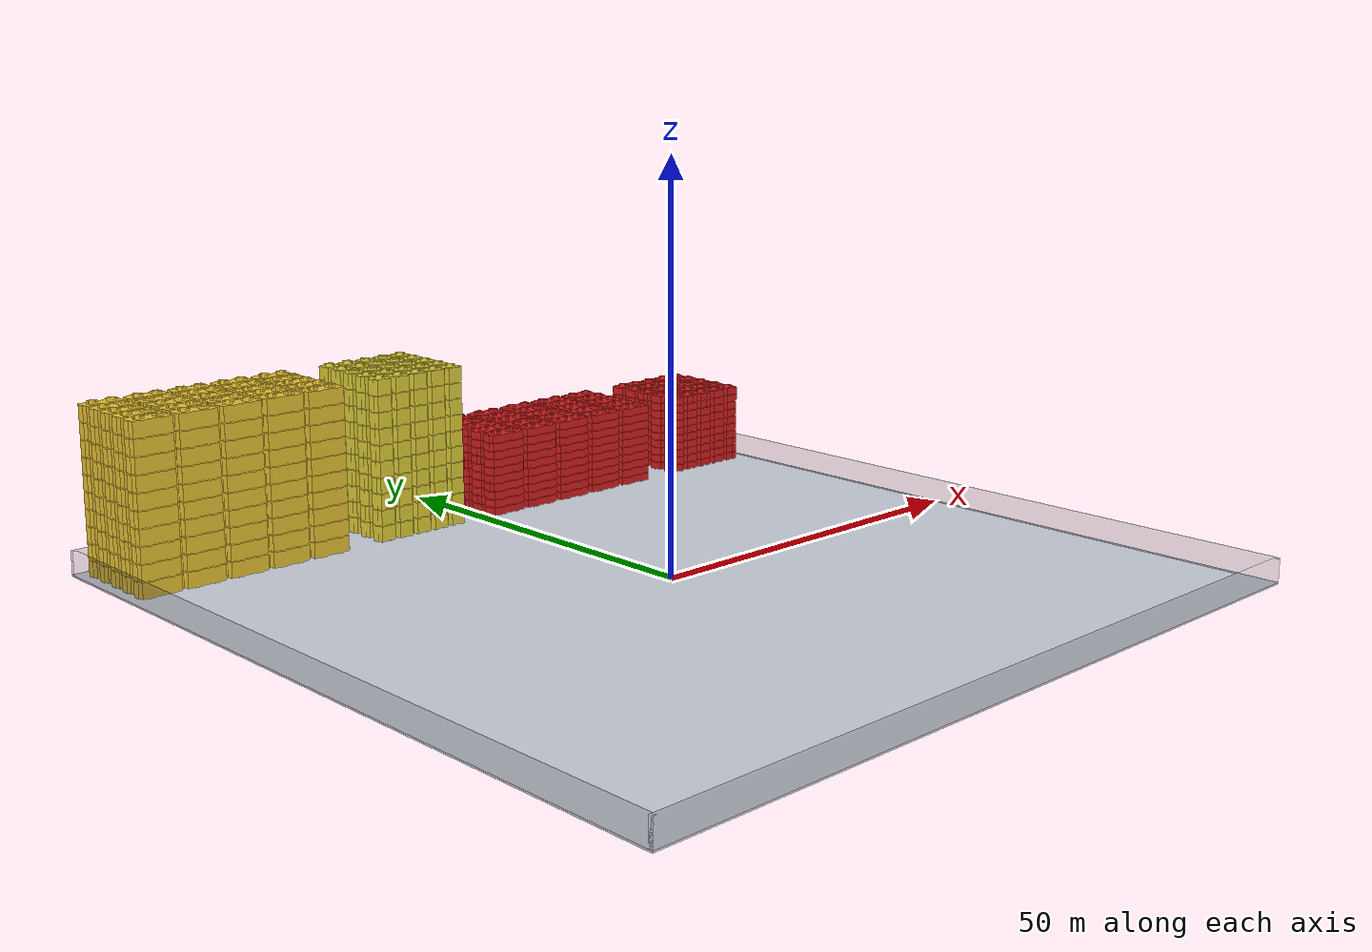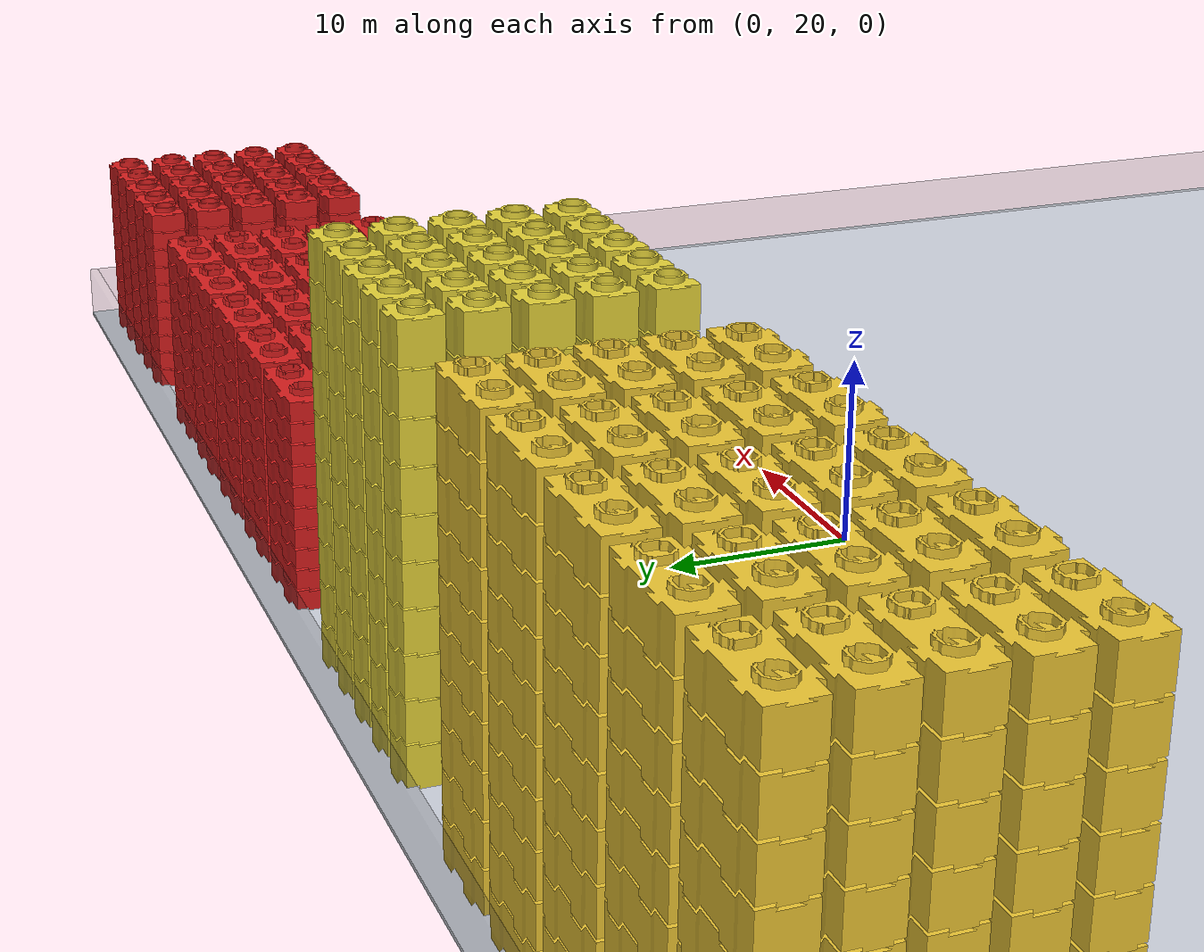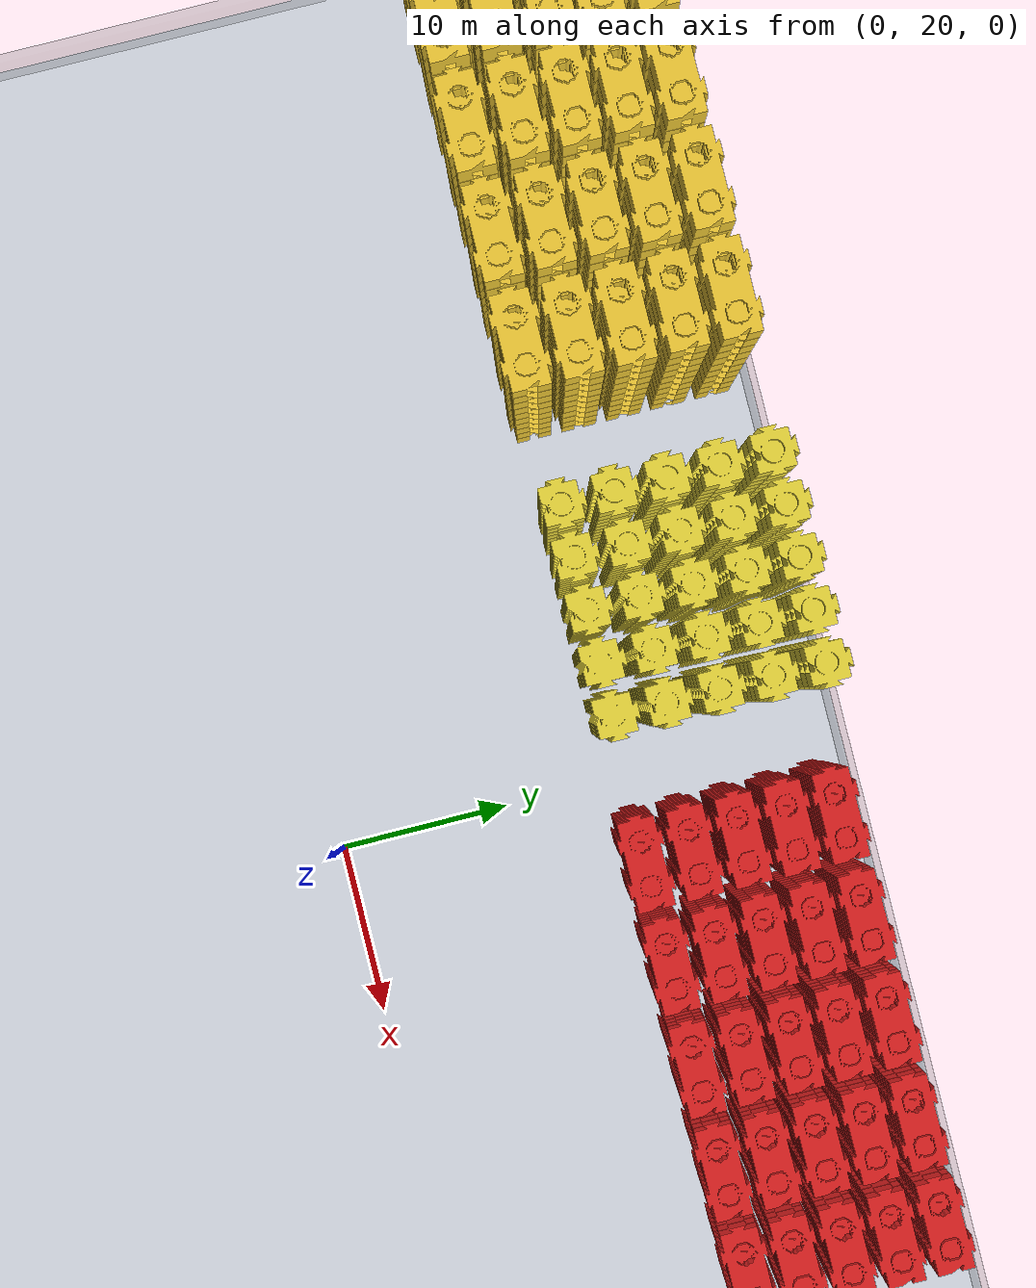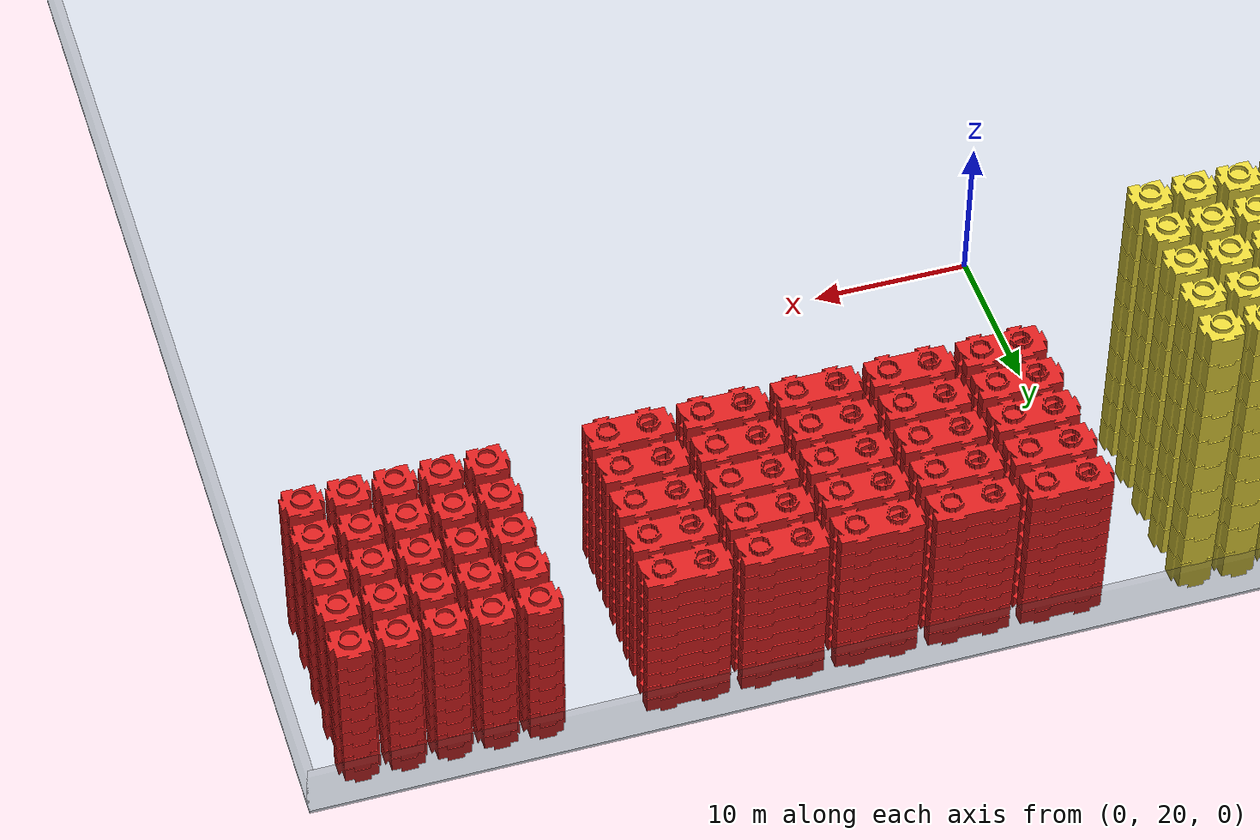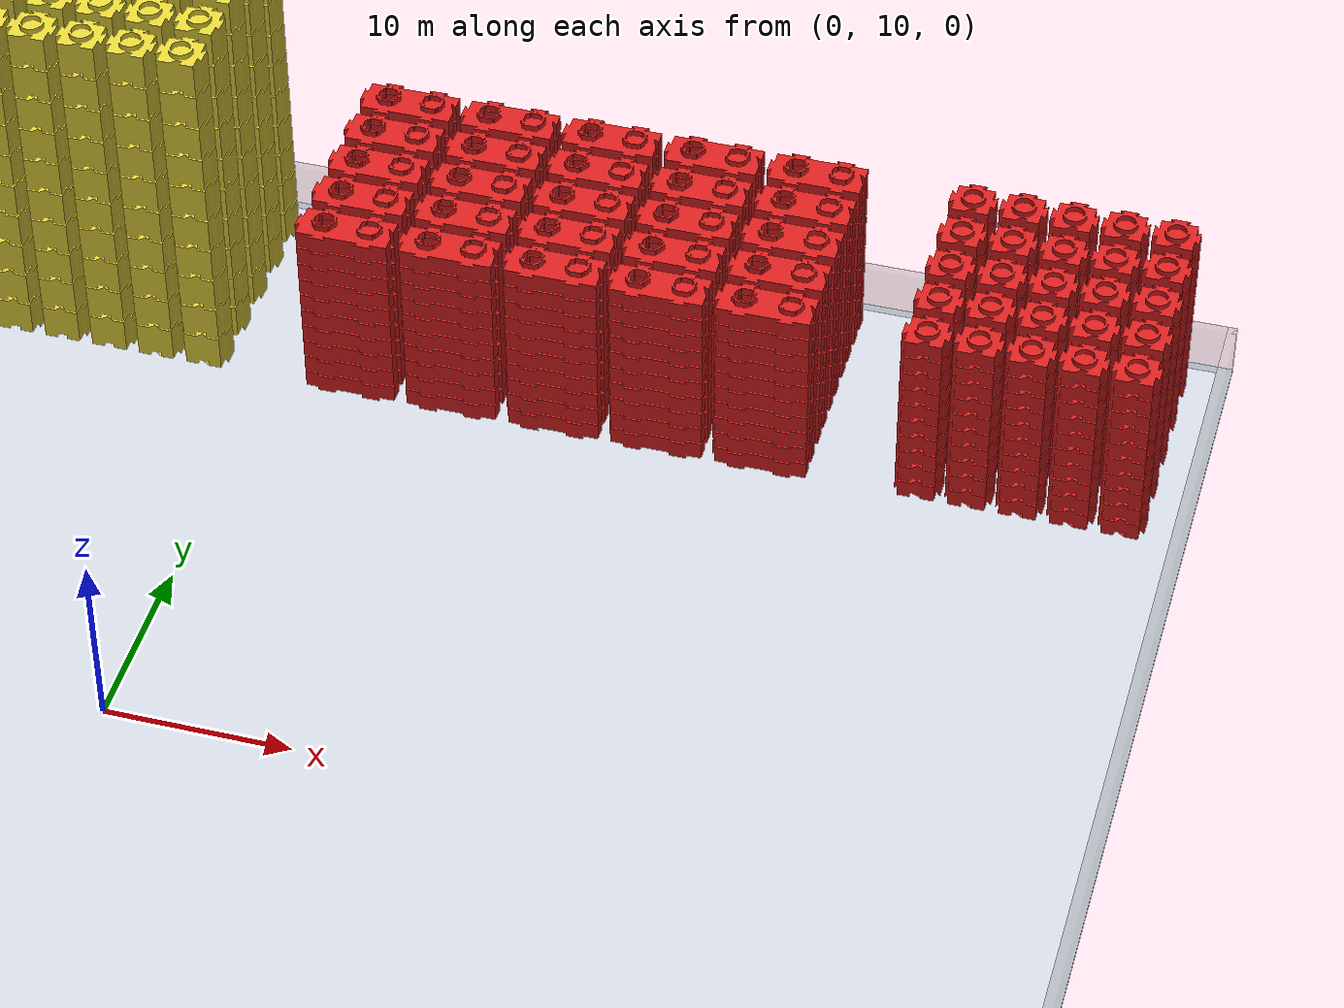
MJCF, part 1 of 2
<mujoco model="lego_planning_learning_inventory">
  <compiler angle="degree" coordinate="local" autolimits="true"/>
  <option timestep="0.005" gravity="0 0 -9.81" integrator="implicitfast"/>
  <visual>
    <headlight ambient="0.65 0.65 0.65" diffuse="0.45 0.45 0.45" specular="0.1 0.1 0.1"/>
    <rgba haze="0.97 0.98 1.0 1"/>
  </visual>
  <statistic center="0.000000 0.000000 0.000000" extent="101.000000"/>
  <asset>
    <mesh name="a2_brick_mesh" file="BlenderFiles/yellowPLAEXLong.obj"/>
    <mesh name="c2_brick_mesh" file="BlenderFiles/yellowPLAEXSide.obj"/>
    <mesh name="a1_brick_mesh" file="BlenderFiles/redPLAEXLong.obj"/>
    <mesh name="c1_brick_mesh" file="BlenderFiles/redPLAEXSide.obj"/>
    <mesh name="plaex_tab_mesh" file="BlenderFiles/plaex_tab.obj"/>
  </asset>
  <default>
    <geom solref="0.004 1" solimp="0.95 0.99 0.001" friction="0.9 0.1 0.05" condim="3"/>
    <joint damping="1" armature="0.01"/>
  </default>
  <worldbody>
    <light name="key" pos="0 0 80" dir="0 0 -1" diffuse="0.9 0.9 0.9" specular="0.2 0.2 0.2"/>
    <light name="fill" pos="0 -40 60" dir="0 0 -1" diffuse="0.5 0.5 0.5" specular="0.1 0.1 0.1"/>
    <camera name="overview" pos="0 -160 120" xyaxes="1 0 0 0 0.6 0.8"/>
    <geom name="floor" type="box" pos="0.000000 0.000000 -0.100000" size="50.500000 50.500000 0.100000" rgba="0.82 0.84 0.88 1"/>
    <geom name="wall_left" type="box" pos="-50.250000 0.000000 1.500000" size="0.250000 50.500000 1.500000" rgba="0.2 0.2 0.2 0.02"/>
    <geom name="wall_right" type="box" pos="50.250000 0.000000 1.500000" size="0.250000 50.500000 1.500000" rgba="0.2 0.2 0.2 0.02"/>
    <geom name="wall_front" type="box" pos="0.000000 50.250000 1.500000" size="50.500000 0.250000 1.500000" rgba="0.2 0.2 0.2 0.02"/>
    <geom name="wall_back" type="box" pos="0.000000 -50.250000 1.500000" size="50.500000 0.250000 1.500000" rgba="0.2 0.2 0.2 0.02"/>
    <body name="InventoryA2_1" pos="-46.500000 48.000000 1.000000" euler="90 0 0">
      <geom name="InventoryA2_1_geom" type="mesh" mesh="a2_brick_mesh" rgba="0.930000 0.780000 0.200000 1.000000" mass="0" contype="0" conaffinity="0"/>
      <geom name="InventoryA2_1_body" type="box" pos="-0.125000 0.000000 0.000000" size="2.375000 1.000000 1.000000" rgba="0 0 0 0" mass="1"/>
      <geom name="InventoryA2_1_stud_1" type="cylinder" pos="-1.250000 1.150000 0.000000" euler="-90 0 0" size="0.650000 0.150000" rgba="0 0 0 0" mass="0.05" contype="2" conaffinity="2"/>
      <geom name="InventoryA2_1_stud_2" type="cylinder" pos="1.250000 1.150000 0.000000" euler="-90 0 0" size="0.650000 0.150000" rgba="0 0 0 0" mass="0.05" contype="2" conaffinity="2"/>
      <geom name="InventoryA2_1_tube_1_1" type="box" pos="-0.400000 -0.850000 0.000000" size="0.150000 0.150000 0.595000" rgba="0 0 0 0" mass="0" contype="2" conaffinity="2"/>
      <geom name="InventoryA2_1_tube_1_2" type="box" pos="-2.100000 -0.850000 0.000000" size="0.150000 0.150000 0.595000" rgba="0 0 0 0" mass="0" contype="2" conaffinity="2"/>
      <geom name="InventoryA2_1_tube_1_3" type="box" pos="-1.250000 -0.850000 0.850000" size="0.595000 0.150000 0.150000" rgba="0 0 0 0" mass="0" contype="2" conaffinity="2"/>
      <geom name="InventoryA2_1_tube_1_4" type="box" pos="-1.250000 -0.850000 -0.850000" size="0.595000 0.150000 0.150000" rgba="0 0 0 0" mass="0" contype="2" conaffinity="2"/>
      <geom name="InventoryA2_1_tube_2_1" type="box" pos="2.100000 -0.850000 0.000000" size="0.150000 0.150000 0.595000" rgba="0 0 0 0" mass="0" contype="2" conaffinity="2"/>
      <geom name="InventoryA2_1_tube_2_2" type="box" pos="0.400000 -0.850000 0.000000" size="0.150000 0.150000 0.595000" rgba="0 0 0 0" mass="0" contype="2" conaffinity="2"/>
      <geom name="InventoryA2_1_tube_2_3" type="box" pos="1.250000 -0.850000 0.850000" size="0.595000 0.150000 0.150000" rgba="0 0 0 0" mass="0" contype="2" conaffinity="2"/>
      <geom name="InventoryA2_1_tube_2_4" type="box" pos="1.250000 -0.850000 -0.850000" size="0.595000 0.150000 0.150000" rgba="0 0 0 0" mass="0" contype="2" conaffinity="2"/>
      <geom name="InventoryA2_1_tab_1" type="mesh" mesh="plaex_tab_mesh" pos="0.000000 0.000000 0.000000" euler="0.000000 0.000000 0.000000" rgba="0 0 0 0" mass="0"/>
      <geom name="InventoryA2_1_tab_2" type="mesh" mesh="plaex_tab_mesh" pos="-1.250000 0.000000 1.500000" euler="0.000000 -90.000000 0.000000" rgba="0 0 0 0" mass="0"/>
      <geom name="InventoryA2_1_tab_3" type="mesh" mesh="plaex_tab_mesh" pos="1.250000 0.000000 1.500000" euler="0.000000 -90.000000 0.000000" rgba="0 0 0 0" mass="0"/>
      <geom name="InventoryA2_1_tab_4" type="mesh" mesh="plaex_tab_mesh" pos="-1.250000 0.000000 -1.500000" euler="0.000000 90.000000 0.000000" rgba="0 0 0 0" mass="0"/>
      <geom name="InventoryA2_1_tab_5" type="mesh" mesh="plaex_tab_mesh" pos="1.250000 0.000000 -1.500000" euler="0.000000 90.000000 0.000000" rgba="0 0 0 0" mass="0"/>
      <geom name="InventoryA2_1_groove_guard_1" type="box" pos="2.375000 0.000000 0.760000" size="0.125000 1.000000 0.240000" rgba="0 0 0 0" mass="0"/>
      <geom name="InventoryA2_1_groove_guard_2" type="box" pos="2.375000 0.000000 -0.760000" size="0.125000 1.000000 0.240000" rgba="0 0 0 0" mass="0"/>
    </body>
    <body name="InventoryA2_2" pos="-40.750000 48.000000 1.000000" euler="90 0 0">
      <geom name="InventoryA2_2_geom" type="mesh" mesh="a2_brick_mesh" rgba="0.930000 0.780000 0.200000 1.000000" mass="0" contype="0" conaffinity="0"/>
      <geom name="InventoryA2_2_body" type="box" pos="-0.125000 0.000000 0.000000" size="2.375000 1.000000 1.000000" rgba="0 0 0 0" mass="1"/>
      <geom name="InventoryA2_2_stud_1" type="cylinder" pos="-1.250000 1.150000 0.000000" euler="-90 0 0" size="0.650000 0.150000" rgba="0 0 0 0" mass="0.05" contype="2" conaffinity="2"/>
      <geom name="InventoryA2_2_stud_2" type="cylinder" pos="1.250000 1.150000 0.000000" euler="-90 0 0" size="0.650000 0.150000" rgba="0 0 0 0" mass="0.05" contype="2" conaffinity="2"/>
      <geom name="InventoryA2_2_tube_1_1" type="box" pos="-0.400000 -0.850000 0.000000" size="0.150000 0.150000 0.595000" rgba="0 0 0 0" mass="0" contype="2" conaffinity="2"/>
      <geom name="InventoryA2_2_tube_1_2" type="box" pos="-2.100000 -0.850000 0.000000" size="0.150000 0.150000 0.595000" rgba="0 0 0 0" mass="0" contype="2" conaffinity="2"/>
      <geom name="InventoryA2_2_tube_1_3" type="box" pos="-1.250000 -0.850000 0.850000" size="0.595000 0.150000 0.150000" rgba="0 0 0 0" mass="0" contype="2" conaffinity="2"/>
      <geom name="InventoryA2_2_tube_1_4" type="box" pos="-1.250000 -0.850000 -0.850000" size="0.595000 0.150000 0.150000" rgba="0 0 0 0" mass="0" contype="2" conaffinity="2"/>
      <geom name="InventoryA2_2_tube_2_1" type="box" pos="2.100000 -0.850000 0.000000" size="0.150000 0.150000 0.595000" rgba="0 0 0 0" mass="0" contype="2" conaffinity="2"/>
      <geom name="InventoryA2_2_tube_2_2" type="box" pos="0.400000 -0.850000 0.000000" size="0.150000 0.150000 0.595000" rgba="0 0 0 0" mass="0" contype="2" conaffinity="2"/>
      <geom name="InventoryA2_2_tube_2_3" type="box" pos="1.250000 -0.850000 0.850000" size="0.595000 0.150000 0.150000" rgba="0 0 0 0" mass="0" contype="2" conaffinity="2"/>
      <geom name="InventoryA2_2_tube_2_4" type="box" pos="1.250000 -0.850000 -0.850000" size="0.595000 0.150000 0.150000" rgba="0 0 0 0" mass="0" contype="2" conaffinity="2"/>
      <geom name="InventoryA2_2_tab_1" type="mesh" mesh="plaex_tab_mesh" pos="0.000000 0.000000 0.000000" euler="0.000000 0.000000 0.000000" rgba="0 0 0 0" mass="0"/>
      <geom name="InventoryA2_2_tab_2" type="mesh" mesh="plaex_tab_mesh" pos="-1.250000 0.000000 1.500000" euler="0.000000 -90.000000 0.000000" rgba="0 0 0 0" mass="0"/>
      <geom name="InventoryA2_2_tab_3" type="mesh" mesh="plaex_tab_mesh" pos="1.250000 0.000000 1.500000" euler="0.000000 -90.000000 0.000000" rgba="0 0 0 0" mass="0"/>
      <geom name="InventoryA2_2_tab_4" type="mesh" mesh="plaex_tab_mesh" pos="-1.250000 0.000000 -1.500000" euler="0.000000 90.000000 0.000000" rgba="0 0 0 0" mass="0"/>
      <geom name="InventoryA2_2_tab_5" type="mesh" mesh="plaex_tab_mesh" pos="1.250000 0.000000 -1.500000" euler="0.000000 90.000000 0.000000" rgba="0 0 0 0" mass="0"/>
      <geom name="InventoryA2_2_groove_guard_1" type="box" pos="2.375000 0.000000 0.760000" size="0.125000 1.000000 0.240000" rgba="0 0 0 0" mass="0"/>
      <geom name="InventoryA2_2_groove_guard_2" type="box" pos="2.375000 0.000000 -0.760000" size="0.125000 1.000000 0.240000" rgba="0 0 0 0" mass="0"/>
    </body>
    <body name="InventoryA2_3" pos="-35.000000 48.000000 1.000000" euler="90 0 0">
      <geom name="InventoryA2_3_geom" type="mesh" mesh="a2_brick_mesh" rgba="0.930000 0.780000 0.200000 1.000000" mass="0" contype="0" conaffinity="0"/>
      <geom name="InventoryA2_3_body" type="box" pos="-0.125000 0.000000 0.000000" size="2.375000 1.000000 1.000000" rgba="0 0 0 0" mass="1"/>
      <geom name="InventoryA2_3_stud_1" type="cylinder" pos="-1.250000 1.150000 0.000000" euler="-90 0 0" size="0.650000 0.150000" rgba="0 0 0 0" mass="0.05" contype="2" conaffinity="2"/>
      <geom name="InventoryA2_3_stud_2" type="cylinder" pos="1.250000 1.150000 0.000000" euler="-90 0 0" size="0.650000 0.150000" rgba="0 0 0 0" mass="0.05" contype="2" conaffinity="2"/>
      <geom name="InventoryA2_3_tube_1_1" type="box" pos="-0.400000 -0.850000 0.000000" size="0.150000 0.150000 0.595000" rgba="0 0 0 0" mass="0" contype="2" conaffinity="2"/>
      <geom name="InventoryA2_3_tube_1_2" type="box" pos="-2.100000 -0.850000 0.000000" size="0.150000 0.150000 0.595000" rgba="0 0 0 0" mass="0" contype="2" conaffinity="2"/>
      <geom name="InventoryA2_3_tube_1_3" type="box" pos="-1.250000 -0.850000 0.850000" size="0.595000 0.150000 0.150000" rgba="0 0 0 0" mass="0" contype="2" conaffinity="2"/>
      <geom name="InventoryA2_3_tube_1_4" type="box" pos="-1.250000 -0.850000 -0.850000" size="0.595000 0.150000 0.150000" rgba="0 0 0 0" mass="0" contype="2" conaffinity="2"/>
      <geom name="InventoryA2_3_tube_2_1" type="box" pos="2.100000 -0.850000 0.000000" size="0.150000 0.150000 0.595000" rgba="0 0 0 0" mass="0" contype="2" conaffinity="2"/>
      <geom name="InventoryA2_3_tube_2_2" type="box" pos="0.400000 -0.850000 0.000000" size="0.150000 0.150000 0.595000" rgba="0 0 0 0" mass="0" contype="2" conaffinity="2"/>
      <geom name="InventoryA2_3_tube_2_3" type="box" pos="1.250000 -0.850000 0.850000" size="0.595000 0.150000 0.150000" rgba="0 0 0 0" mass="0" contype="2" conaffinity="2"/>
      <geom name="InventoryA2_3_tube_2_4" type="box" pos="1.250000 -0.850000 -0.850000" size="0.595000 0.150000 0.150000" rgba="0 0 0 0" mass="0" contype="2" conaffinity="2"/>
      <geom name="InventoryA2_3_tab_1" type="mesh" mesh="plaex_tab_mesh" pos="0.000000 0.000000 0.000000" euler="0.000000 0.000000 0.000000" rgba="0 0 0 0" mass="0"/>
      <geom name="InventoryA2_3_tab_2" type="mesh" mesh="plaex_tab_mesh" pos="-1.250000 0.000000 1.500000" euler="0.000000 -90.000000 0.000000" rgba="0 0 0 0" mass="0"/>
      <geom name="InventoryA2_3_tab_3" type="mesh" mesh="plaex_tab_mesh" pos="1.250000 0.000000 1.500000" euler="0.000000 -90.000000 0.000000" rgba="0 0 0 0" mass="0"/>
      <geom name="InventoryA2_3_tab_4" type="mesh" mesh="plaex_tab_mesh" pos="-1.250000 0.000000 -1.500000" euler="0.000000 90.000000 0.000000" rgba="0 0 0 0" mass="0"/>
      <geom name="InventoryA2_3_tab_5" type="mesh" mesh="plaex_tab_mesh" pos="1.250000 0.000000 -1.500000" euler="0.000000 90.000000 0.000000" rgba="0 0 0 0" mass="0"/>
      <geom name="InventoryA2_3_groove_guard_1" type="box" pos="2.375000 0.000000 0.760000" size="0.125000 1.000000 0.240000" rgba="0 0 0 0" mass="0"/>
      <geom name="InventoryA2_3_groove_guard_2" type="box" pos="2.375000 0.000000 -0.760000" size="0.125000 1.000000 0.240000" rgba="0 0 0 0" mass="0"/>
    </body>
    <body name="InventoryA2_4" pos="-29.250000 48.000000 1.000000" euler="90 0 0">
      <geom name="InventoryA2_4_geom" type="mesh" mesh="a2_brick_mesh" rgba="0.930000 0.780000 0.200000 1.000000" mass="0" contype="0" conaffinity="0"/>
      <geom name="InventoryA2_4_body" type="box" pos="-0.125000 0.000000 0.000000" size="2.375000 1.000000 1.000000" rgba="0 0 0 0" mass="1"/>
      <geom name="InventoryA2_4_stud_1" type="cylinder" pos="-1.250000 1.150000 0.000000" euler="-90 0 0" size="0.650000 0.150000" rgba="0 0 0 0" mass="0.05" contype="2" conaffinity="2"/>
      <geom name="InventoryA2_4_stud_2" type="cylinder" pos="1.250000 1.150000 0.000000" euler="-90 0 0" size="0.650000 0.150000" rgba="0 0 0 0" mass="0.05" contype="2" conaffinity="2"/>
      <geom name="InventoryA2_4_tube_1_1" type="box" pos="-0.400000 -0.850000 0.000000" size="0.150000 0.150000 0.595000" rgba="0 0 0 0" mass="0" contype="2" conaffinity="2"/>
      <geom name="InventoryA2_4_tube_1_2" type="box" pos="-2.100000 -0.850000 0.000000" size="0.150000 0.150000 0.595000" rgba="0 0 0 0" mass="0" contype="2" conaffinity="2"/>
      <geom name="InventoryA2_4_tube_1_3" type="box" pos="-1.250000 -0.850000 0.850000" size="0.595000 0.150000 0.150000" rgba="0 0 0 0" mass="0" contype="2" conaffinity="2"/>
      <geom name="InventoryA2_4_tube_1_4" type="box" pos="-1.250000 -0.850000 -0.850000" size="0.595000 0.150000 0.150000" rgba="0 0 0 0" mass="0" contype="2" conaffinity="2"/>
      <geom name="InventoryA2_4_tube_2_1" type="box" pos="2.100000 -0.850000 0.000000" size="0.150000 0.150000 0.595000" rgba="0 0 0 0" mass="0" contype="2" conaffinity="2"/>
      <geom name="InventoryA2_4_tube_2_2" type="box" pos="0.400000 -0.850000 0.000000" size="0.150000 0.150000 0.595000" rgba="0 0 0 0" mass="0" contype="2" conaffinity="2"/>
      <geom name="InventoryA2_4_tube_2_3" type="box" pos="1.250000 -0.850000 0.850000" size="0.595000 0.150000 0.150000" rgba="0 0 0 0" mass="0" contype="2" conaffinity="2"/>
      <geom name="InventoryA2_4_tube_2_4" type="box" pos="1.250000 -0.850000 -0.850000" size="0.595000 0.150000 0.150000" rgba="0 0 0 0" mass="0" contype="2" conaffinity="2"/>
      <geom name="InventoryA2_4_tab_1" type="mesh" mesh="plaex_tab_mesh" pos="0.000000 0.000000 0.000000" euler="0.000000 0.000000 0.000000" rgba="0 0 0 0" mass="0"/>
      <geom name="InventoryA2_4_tab_2" type="mesh" mesh="plaex_tab_mesh" pos="-1.250000 0.000000 1.500000" euler="0.000000 -90.000000 0.000000" rgba="0 0 0 0" mass="0"/>
      <geom name="InventoryA2_4_tab_3" type="mesh" mesh="plaex_tab_mesh" pos="1.250000 0.000000 1.500000" euler="0.000000 -90.000000 0.000000" rgba="0 0 0 0" mass="0"/>
      <geom name="InventoryA2_4_tab_4" type="mesh" mesh="plaex_tab_mesh" pos="-1.250000 0.000000 -1.500000" euler="0.000000 90.000000 0.000000" rgba="0 0 0 0" mass="0"/>
      <geom name="InventoryA2_4_tab_5" type="mesh" mesh="plaex_tab_mesh" pos="1.250000 0.000000 -1.500000" euler="0.000000 90.000000 0.000000" rgba="0 0 0 0" mass="0"/>
      <geom name="InventoryA2_4_groove_guard_1" type="box" pos="2.375000 0.000000 0.760000" size="0.125000 1.000000 0.240000" rgba="0 0 0 0" mass="0"/>
      <geom name="InventoryA2_4_groove_guard_2" type="box" pos="2.375000 0.000000 -0.760000" size="0.125000 1.000000 0.240000" rgba="0 0 0 0" mass="0"/>
    </body>
    <body name="InventoryA2_5" pos="-23.500000 48.000000 1.000000" euler="90 0 0">
      <geom name="InventoryA2_5_geom" type="mesh" mesh="a2_brick_mesh" rgba="0.930000 0.780000 0.200000 1.000000" mass="0" contype="0" conaffinity="0"/>
      <geom name="InventoryA2_5_body" type="box" pos="-0.125000 0.000000 0.000000" size="2.375000 1.000000 1.000000" rgba="0 0 0 0" mass="1"/>
      <geom name="InventoryA2_5_stud_1" type="cylinder" pos="-1.250000 1.150000 0.000000" euler="-90 0 0" size="0.650000 0.150000" rgba="0 0 0 0" mass="0.05" contype="2" conaffinity="2"/>
      <geom name="InventoryA2_5_stud_2" type="cylinder" pos="1.250000 1.150000 0.000000" euler="-90 0 0" size="0.650000 0.150000" rgba="0 0 0 0" mass="0.05" contype="2" conaffinity="2"/>
      <geom name="InventoryA2_5_tube_1_1" type="box" pos="-0.400000 -0.850000 0.000000" size="0.150000 0.150000 0.595000" rgba="0 0 0 0" mass="0" contype="2" conaffinity="2"/>
      <geom name="InventoryA2_5_tube_1_2" type="box" pos="-2.100000 -0.850000 0.000000" size="0.150000 0.150000 0.595000" rgba="0 0 0 0" mass="0" contype="2" conaffinity="2"/>
      <geom name="InventoryA2_5_tube_1_3" type="box" pos="-1.250000 -0.850000 0.850000" size="0.595000 0.150000 0.150000" rgba="0 0 0 0" mass="0" contype="2" conaffinity="2"/>
      <geom name="InventoryA2_5_tube_1_4" type="box" pos="-1.250000 -0.850000 -0.850000" size="0.595000 0.150000 0.150000" rgba="0 0 0 0" mass="0" contype="2" conaffinity="2"/>
      <geom name="InventoryA2_5_tube_2_1" type="box" pos="2.100000 -0.850000 0.000000" size="0.150000 0.150000 0.595000" rgba="0 0 0 0" mass="0" contype="2" conaffinity="2"/>
      <geom name="InventoryA2_5_tube_2_2" type="box" pos="0.400000 -0.850000 0.000000" size="0.150000 0.150000 0.595000" rgba="0 0 0 0" mass="0" contype="2" conaffinity="2"/>
      <geom name="InventoryA2_5_tube_2_3" type="box" pos="1.250000 -0.850000 0.850000" size="0.595000 0.150000 0.150000" rgba="0 0 0 0" mass="0" contype="2" conaffinity="2"/>
      <geom name="InventoryA2_5_tube_2_4" type="box" pos="1.250000 -0.850000 -0.850000" size="0.595000 0.150000 0.150000" rgba="0 0 0 0" mass="0" contype="2" conaffinity="2"/>
      <geom name="InventoryA2_5_tab_1" type="mesh" mesh="plaex_tab_mesh" pos="0.000000 0.000000 0.000000" euler="0.000000 0.000000 0.000000" rgba="0 0 0 0" mass="0"/>
      <geom name="InventoryA2_5_tab_2" type="mesh" mesh="plaex_tab_mesh" pos="-1.250000 0.000000 1.500000" euler="0.000000 -90.000000 0.000000" rgba="0 0 0 0" mass="0"/>
      <geom name="InventoryA2_5_tab_3" type="mesh" mesh="plaex_tab_mesh" pos="1.250000 0.000000 1.500000" euler="0.000000 -90.000000 0.000000" rgba="0 0 0 0" mass="0"/>
      <geom name="InventoryA2_5_tab_4" type="mesh" mesh="plaex_tab_mesh" pos="-1.250000 0.000000 -1.500000" euler="0.000000 90.000000 0.000000" rgba="0 0 0 0" mass="0"/>
      <geom name="InventoryA2_5_tab_5" type="mesh" mesh="plaex_tab_mesh" pos="1.250000 0.000000 -1.500000" euler="0.000000 90.000000 0.000000" rgba="0 0 0 0" mass="0"/>
      <geom name="InventoryA2_5_groove_guard_1" type="box" pos="2.375000 0.000000 0.760000" size="0.125000 1.000000 0.240000" rgba="0 0 0 0" mass="0"/>
      <geom name="InventoryA2_5_groove_guard_2" type="box" pos="2.375000 0.000000 -0.760000" size="0.125000 1.000000 0.240000" rgba="0 0 0 0" mass="0"/>
    </body>
    <body name="InventoryA2_6" pos="-46.500000 45.250000 1.000000" euler="90 0 0">
      <geom name="InventoryA2_6_geom" type="mesh" mesh="a2_brick_mesh" rgba="0.930000 0.780000 0.200000 1.000000" mass="0" contype="0" conaffinity="0"/>
      <geom name="InventoryA2_6_body" type="box" pos="-0.125000 0.000000 0.000000" size="2.375000 1.000000 1.000000" rgba="0 0 0 0" mass="1"/>
      <geom name="InventoryA2_6_stud_1" type="cylinder" pos="-1.250000 1.150000 0.000000" euler="-90 0 0" size="0.650000 0.150000" rgba="0 0 0 0" mass="0.05" contype="2" conaffinity="2"/>
      <geom name="InventoryA2_6_stud_2" type="cylinder" pos="1.250000 1.150000 0.000000" euler="-90 0 0" size="0.650000 0.150000" rgba="0 0 0 0" mass="0.05" contype="2" conaffinity="2"/>
      <geom name="InventoryA2_6_tube_1_1" type="box" pos="-0.400000 -0.850000 0.000000" size="0.150000 0.150000 0.595000" rgba="0 0 0 0" mass="0" contype="2" conaffinity="2"/>
      <geom name="InventoryA2_6_tube_1_2" type="box" pos="-2.100000 -0.850000 0.000000" size="0.150000 0.150000 0.595000" rgba="0 0 0 0" mass="0" contype="2" conaffinity="2"/>
      <geom name="InventoryA2_6_tube_1_3" type="box" pos="-1.250000 -0.850000 0.850000" size="0.595000 0.150000 0.150000" rgba="0 0 0 0" mass="0" contype="2" conaffinity="2"/>
      <geom name="InventoryA2_6_tube_1_4" type="box" pos="-1.250000 -0.850000 -0.850000" size="0.595000 0.150000 0.150000" rgba="0 0 0 0" mass="0" contype="2" conaffinity="2"/>
      <geom name="InventoryA2_6_tube_2_1" type="box" pos="2.100000 -0.850000 0.000000" size="0.150000 0.150000 0.595000" rgba="0 0 0 0" mass="0" contype="2" conaffinity="2"/>
      <geom name="InventoryA2_6_tube_2_2" type="box" pos="0.400000 -0.850000 0.000000" size="0.150000 0.150000 0.595000" rgba="0 0 0 0" mass="0" contype="2" conaffinity="2"/>
      <geom name="InventoryA2_6_tube_2_3" type="box" pos="1.250000 -0.850000 0.850000" size="0.595000 0.150000 0.150000" rgba="0 0 0 0" mass="0" contype="2" conaffinity="2"/>
      <geom name="InventoryA2_6_tube_2_4" type="box" pos="1.250000 -0.850000 -0.850000" size="0.595000 0.150000 0.150000" rgba="0 0 0 0" mass="0" contype="2" conaffinity="2"/>
      <geom name="InventoryA2_6_tab_1" type="mesh" mesh="plaex_tab_mesh" pos="0.000000 0.000000 0.000000" euler="0.000000 0.000000 0.000000" rgba="0 0 0 0" mass="0"/>
      <geom name="InventoryA2_6_tab_2" type="mesh" mesh="plaex_tab_mesh" pos="-1.250000 0.000000 1.500000" euler="0.000000 -90.000000 0.000000" rgba="0 0 0 0" mass="0"/>
      <geom name="InventoryA2_6_tab_3" type="mesh" mesh="plaex_tab_mesh" pos="1.250000 0.000000 1.500000" euler="0.000000 -90.000000 0.000000" rgba="0 0 0 0" mass="0"/>
      <geom name="InventoryA2_6_tab_4" type="mesh" mesh="plaex_tab_mesh" pos="-1.250000 0.000000 -1.500000" euler="0.000000 90.000000 0.000000" rgba="0 0 0 0" mass="0"/>
      <geom name="InventoryA2_6_tab_5" type="mesh" mesh="plaex_tab_mesh" pos="1.250000 0.000000 -1.500000" euler="0.000000 90.000000 0.000000" rgba="0 0 0 0" mass="0"/>
      <geom name="InventoryA2_6_groove_guard_1" type="box" pos="2.375000 0.000000 0.760000" size="0.125000 1.000000 0.240000" rgba="0 0 0 0" mass="0"/>
      <geom name="InventoryA2_6_groove_guard_2" type="box" pos="2.375000 0.000000 -0.760000" size="0.125000 1.000000 0.240000" rgba="0 0 0 0" mass="0"/>
    </body>
    <body name="InventoryA2_7" pos="-40.750000 45.250000 1.000000" euler="90 0 0">
      <geom name="InventoryA2_7_geom" type="mesh" mesh="a2_brick_mesh" rgba="0.930000 0.780000 0.200000 1.000000" mass="0" contype="0" conaffinity="0"/>
      <geom name="InventoryA2_7_body" type="box" pos="-0.125000 0.000000 0.000000" size="2.375000 1.000000 1.000000" rgba="0 0 0 0" mass="1"/>
      <geom name="InventoryA2_7_stud_1" type="cylinder" pos="-1.250000 1.150000 0.000000" euler="-90 0 0" size="0.650000 0.150000" rgba="0 0 0 0" mass="0.05" contype="2" conaffinity="2"/>
      <geom name="InventoryA2_7_stud_2" type="cylinder" pos="1.250000 1.150000 0.000000" euler="-90 0 0" size="0.650000 0.150000" rgba="0 0 0 0" mass="0.05" contype="2" conaffinity="2"/>
      <geom name="InventoryA2_7_tube_1_1" type="box" pos="-0.400000 -0.850000 0.000000" size="0.150000 0.150000 0.595000" rgba="0 0 0 0" mass="0" contype="2" conaffinity="2"/>
      <geom name="InventoryA2_7_tube_1_2" type="box" pos="-2.100000 -0.850000 0.000000" size="0.150000 0.150000 0.595000" rgba="0 0 0 0" mass="0" contype="2" conaffinity="2"/>
      <geom name="InventoryA2_7_tube_1_3" type="box" pos="-1.250000 -0.850000 0.850000" size="0.595000 0.150000 0.150000" rgba="0 0 0 0" mass="0" contype="2" conaffinity="2"/>
      <geom name="InventoryA2_7_tube_1_4" type="box" pos="-1.250000 -0.850000 -0.850000" size="0.595000 0.150000 0.150000" rgba="0 0 0 0" mass="0" contype="2" conaffinity="2"/>
      <geom name="InventoryA2_7_tube_2_1" type="box" pos="2.100000 -0.850000 0.000000" size="0.150000 0.150000 0.595000" rgba="0 0 0 0" mass="0" contype="2" conaffinity="2"/>
      <geom name="InventoryA2_7_tube_2_2" type="box" pos="0.400000 -0.850000 0.000000" size="0.150000 0.150000 0.595000" rgba="0 0 0 0" mass="0" contype="2" conaffinity="2"/>
      <geom name="InventoryA2_7_tube_2_3" type="box" pos="1.250000 -0.850000 0.850000" size="0.595000 0.150000 0.150000" rgba="0 0 0 0" mass="0" contype="2" conaffinity="2"/>
      <geom name="InventoryA2_7_tube_2_4" type="box" pos="1.250000 -0.850000 -0.850000" size="0.595000 0.150000 0.150000" rgba="0 0 0 0" mass="0" contype="2" conaffinity="2"/>
      <geom name="InventoryA2_7_tab_1" type="mesh" mesh="plaex_tab_mesh" pos="0.000000 0.000000 0.000000" euler="0.000000 0.000000 0.000000" rgba="0 0 0 0" mass="0"/>
      <geom name="InventoryA2_7_tab_2" type="mesh" mesh="plaex_tab_mesh" pos="-1.250000 0.000000 1.500000" euler="0.000000 -90.000000 0.000000" rgba="0 0 0 0" mass="0"/>
      <geom name="InventoryA2_7_tab_3" type="mesh" mesh="plaex_tab_mesh" pos="1.250000 0.000000 1.500000" euler="0.000000 -90.000000 0.000000" rgba="0 0 0 0" mass="0"/>
      <geom name="InventoryA2_7_tab_4" type="mesh" mesh="plaex_tab_mesh" pos="-1.250000 0.000000 -1.500000" euler="0.000000 90.000000 0.000000" rgba="0 0 0 0" mass="0"/>
      <geom name="InventoryA2_7_tab_5" type="mesh" mesh="plaex_tab_mesh" pos="1.250000 0.000000 -1.500000" euler="0.000000 90.000000 0.000000" rgba="0 0 0 0" mass="0"/>
      <geom name="InventoryA2_7_groove_guard_1" type="box" pos="2.375000 0.000000 0.760000" size="0.125000 1.000000 0.240000" rgba="0 0 0 0" mass="0"/>
      <geom name="InventoryA2_7_groove_guard_2" type="box" pos="2.375000 0.000000 -0.760000" size="0.125000 1.000000 0.240000" rgba="0 0 0 0" mass="0"/>
    </body>
    <body name="InventoryA2_8" pos="-35.000000 45.250000 1.000000" euler="90 0 0">
      <geom name="InventoryA2_8_geom" type="mesh" mesh="a2_brick_mesh" rgba="0.930000 0.780000 0.200000 1.000000" mass="0" contype="0" conaffinity="0"/>
      <geom name="InventoryA2_8_body" type="box" pos="-0.125000 0.000000 0.000000" size="2.375000 1.000000 1.000000" rgba="0 0 0 0" mass="1"/>
      <geom name="InventoryA2_8_stud_1" type="cylinder" pos="-1.250000 1.150000 0.000000" euler="-90 0 0" size="0.650000 0.150000" rgba="0 0 0 0" mass="0.05" contype="2" conaffinity="2"/>
      <geom name="InventoryA2_8_stud_2" type="cylinder" pos="1.250000 1.150000 0.000000" euler="-90 0 0" size="0.650000 0.150000" rgba="0 0 0 0" mass="0.05" contype="2" conaffinity="2"/>
      <geom name="InventoryA2_8_tube_1_1" type="box" pos="-0.400000 -0.850000 0.000000" size="0.150000 0.150000 0.595000" rgba="0 0 0 0" mass="0" contype="2" conaffinity="2"/>
      <geom name="InventoryA2_8_tube_1_2" type="box" pos="-2.100000 -0.850000 0.000000" size="0.150000 0.150000 0.595000" rgba="0 0 0 0" mass="0" contype="2" conaffinity="2"/>
      <geom name="InventoryA2_8_tube_1_3" type="box" pos="-1.250000 -0.850000 0.850000" size="0.595000 0.150000 0.150000" rgba="0 0 0 0" mass="0" contype="2" conaffinity="2"/>
      <geom name="InventoryA2_8_tube_1_4" type="box" pos="-1.250000 -0.850000 -0.850000" size="0.595000 0.150000 0.150000" rgba="0 0 0 0" mass="0" contype="2" conaffinity="2"/>
      <geom name="InventoryA2_8_tube_2_1" type="box" pos="2.100000 -0.850000 0.000000" size="0.150000 0.150000 0.595000" rgba="0 0 0 0" mass="0" contype="2" conaffinity="2"/>
      <geom name="InventoryA2_8_tube_2_2" type="box" pos="0.400000 -0.850000 0.000000" size="0.150000 0.150000 0.595000" rgba="0 0 0 0" mass="0" contype="2" conaffinity="2"/>
      <geom name="InventoryA2_8_tube_2_3" type="box" pos="1.250000 -0.850000 0.850000" size="0.595000 0.150000 0.150000" rgba="0 0 0 0" mass="0" contype="2" conaffinity="2"/>
      <geom name="InventoryA2_8_tube_2_4" type="box" pos="1.250000 -0.850000 -0.850000" size="0.595000 0.150000 0.150000" rgba="0 0 0 0" mass="0" contype="2" conaffinity="2"/>
      <geom name="InventoryA2_8_tab_1" type="mesh" mesh="plaex_tab_mesh" pos="0.000000 0.000000 0.000000" euler="0.000000 0.000000 0.000000" rgba="0 0 0 0" mass="0"/>
      <geom name="InventoryA2_8_tab_2" type="mesh" mesh="plaex_tab_mesh" pos="-1.250000 0.000000 1.500000" euler="0.000000 -90.000000 0.000000" rgba="0 0 0 0" mass="0"/>
      <geom name="InventoryA2_8_tab_3" type="mesh" mesh="plaex_tab_mesh" pos="1.250000 0.000000 1.500000" euler="0.000000 -90.000000 0.000000" rgba="0 0 0 0" mass="0"/>
      <geom name="InventoryA2_8_tab_4" type="mesh" mesh="plaex_tab_mesh" pos="-1.250000 0.000000 -1.500000" euler="0.000000 90.000000 0.000000" rgba="0 0 0 0" mass="0"/>
      <geom name="InventoryA2_8_tab_5" type="mesh" mesh="plaex_tab_mesh" pos="1.250000 0.000000 -1.500000" euler="0.000000 90.000000 0.000000" rgba="0 0 0 0" mass="0"/>
      <geom name="InventoryA2_8_groove_guard_1" type="box" pos="2.375000 0.000000 0.760000" size="0.125000 1.000000 0.240000" rgba="0 0 0 0" mass="0"/>
      <geom name="InventoryA2_8_groove_guard_2" type="box" pos="2.375000 0.000000 -0.760000" size="0.125000 1.000000 0.240000" rgba="0 0 0 0" mass="0"/>
    </body>
    <body name="InventoryA2_9" pos="-29.250000 45.250000 1.000000" euler="90 0 0">
      <geom name="InventoryA2_9_geom" type="mesh" mesh="a2_brick_mesh" rgba="0.930000 0.780000 0.200000 1.000000" mass="0" contype="0" conaffinity="0"/>
      <geom name="InventoryA2_9_body" type="box" pos="-0.125000 0.000000 0.000000" size="2.375000 1.000000 1.000000" rgba="0 0 0 0" mass="1"/>
      <geom name="InventoryA2_9_stud_1" type="cylinder" pos="-1.250000 1.150000 0.000000" euler="-90 0 0" size="0.650000 0.150000" rgba="0 0 0 0" mass="0.05" contype="2" conaffinity="2"/>
      <geom name="InventoryA2_9_stud_2" type="cylinder" pos="1.250000 1.150000 0.000000" euler="-90 0 0" size="0.650000 0.150000" rgba="0 0 0 0" mass="0.05" contype="2" conaffinity="2"/>
      <geom name="InventoryA2_9_tube_1_1" type="box" pos="-0.400000 -0.850000 0.000000" size="0.150000 0.150000 0.595000" rgba="0 0 0 0" mass="0" contype="2" conaffinity="2"/>
      <geom name="InventoryA2_9_tube_1_2" type="box" pos="-2.100000 -0.850000 0.000000" size="0.150000 0.150000 0.595000" rgba="0 0 0 0" mass="0" contype="2" conaffinity="2"/>
      <geom name="InventoryA2_9_tube_1_3" type="box" pos="-1.250000 -0.850000 0.850000" size="0.595000 0.150000 0.150000" rgba="0 0 0 0" mass="0" contype="2" conaffinity="2"/>
      <geom name="InventoryA2_9_tube_1_4" type="box" pos="-1.250000 -0.850000 -0.850000" size="0.595000 0.150000 0.150000" rgba="0 0 0 0" mass="0" contype="2" conaffinity="2"/>
      <geom name="InventoryA2_9_tube_2_1" type="box" pos="2.100000 -0.850000 0.000000" size="0.150000 0.150000 0.595000" rgba="0 0 0 0" mass="0" contype="2" conaffinity="2"/>
      <geom name="InventoryA2_9_tube_2_2" type="box" pos="0.400000 -0.850000 0.000000" size="0.150000 0.150000 0.595000" rgba="0 0 0 0" mass="0" contype="2" conaffinity="2"/>
      <geom name="InventoryA2_9_tube_2_3" type="box" pos="1.250000 -0.850000 0.850000" size="0.595000 0.150000 0.150000" rgba="0 0 0 0" mass="0" contype="2" conaffinity="2"/>
      <geom name="InventoryA2_9_tube_2_4" type="box" pos="1.250000 -0.850000 -0.850000" size="0.595000 0.150000 0.150000" rgba="0 0 0 0" mass="0" contype="2" conaffinity="2"/>
      <geom name="InventoryA2_9_tab_1" type="mesh" mesh="plaex_tab_mesh" pos="0.000000 0.000000 0.000000" euler="0.000000 0.000000 0.000000" rgba="0 0 0 0" mass="0"/>
      <geom name="InventoryA2_9_tab_2" type="mesh" mesh="plaex_tab_mesh" pos="-1.250000 0.000000 1.500000" euler="0.000000 -90.000000 0.000000" rgba="0 0 0 0" mass="0"/>
      <geom name="InventoryA2_9_tab_3" type="mesh" mesh="plaex_tab_mesh" pos="1.250000 0.000000 1.500000" euler="0.000000 -90.000000 0.000000" rgba="0 0 0 0" mass="0"/>
      <geom name="InventoryA2_9_tab_4" type="mesh" mesh="plaex_tab_mesh" pos="-1.250000 0.000000 -1.500000" euler="0.000000 90.000000 0.000000" rgba="0 0 0 0" mass="0"/>
      <geom name="InventoryA2_9_tab_5" type="mesh" mesh="plaex_tab_mesh" pos="1.250000 0.000000 -1.500000" euler="0.000000 90.000000 0.000000" rgba="0 0 0 0" mass="0"/>
      <geom name="InventoryA2_9_groove_guard_1" type="box" pos="2.375000 0.000000 0.760000" size="0.125000 1.000000 0.240000" rgba="0 0 0 0" mass="0"/>
      <geom name="InventoryA2_9_groove_guard_2" type="box" pos="2.375000 0.000000 -0.760000" size="0.125000 1.000000 0.240000" rgba="0 0 0 0" mass="0"/>
    </body>
    <body name="InventoryA2_10" pos="-23.500000 45.250000 1.000000" euler="90 0 0">
      <geom name="InventoryA2_10_geom" type="mesh" mesh="a2_brick_mesh" rgba="0.930000 0.780000 0.200000 1.000000" mass="0" contype="0" conaffinity="0"/>
      <geom name="InventoryA2_10_body" type="box" pos="-0.125000 0.000000 0.000000" size="2.375000 1.000000 1.000000" rgba="0 0 0 0" mass="1"/>
      <geom name="InventoryA2_10_stud_1" type="cylinder" pos="-1.250000 1.150000 0.000000" euler="-90 0 0" size="0.650000 0.150000" rgba="0 0 0 0" mass="0.05" contype="2" conaffinity="2"/>
      <geom name="InventoryA2_10_stud_2" type="cylinder" pos="1.250000 1.150000 0.000000" euler="-90 0 0" size="0.650000 0.150000" rgba="0 0 0 0" mass="0.05" contype="2" conaffinity="2"/>
      <geom name="InventoryA2_10_tube_1_1" type="box" pos="-0.400000 -0.850000 0.000000" size="0.150000 0.150000 0.595000" rgba="0 0 0 0" mass="0" contype="2" conaffinity="2"/>
      <geom name="InventoryA2_10_tube_1_2" type="box" pos="-2.100000 -0.850000 0.000000" size="0.150000 0.150000 0.595000" rgba="0 0 0 0" mass="0" contype="2" conaffinity="2"/>
      <geom name="InventoryA2_10_tube_1_3" type="box" pos="-1.250000 -0.850000 0.850000" size="0.595000 0.150000 0.150000" rgba="0 0 0 0" mass="0" contype="2" conaffinity="2"/>
      <geom name="InventoryA2_10_tube_1_4" type="box" pos="-1.250000 -0.850000 -0.850000" size="0.595000 0.150000 0.150000" rgba="0 0 0 0" mass="0" contype="2" conaffinity="2"/>
      <geom name="InventoryA2_10_tube_2_1" type="box" pos="2.100000 -0.850000 0.000000" size="0.150000 0.150000 0.595000" rgba="0 0 0 0" mass="0" contype="2" conaffinity="2"/>
      <geom name="InventoryA2_10_tube_2_2" type="box" pos="0.400000 -0.850000 0.000000" size="0.150000 0.150000 0.595000" rgba="0 0 0 0" mass="0" contype="2" conaffinity="2"/>
      <geom name="InventoryA2_10_tube_2_3" type="box" pos="1.250000 -0.850000 0.850000" size="0.595000 0.150000 0.150000" rgba="0 0 0 0" mass="0" contype="2" conaffinity="2"/>
      <geom name="InventoryA2_10_tube_2_4" type="box" pos="1.250000 -0.850000 -0.850000" size="0.595000 0.150000 0.150000" rgba="0 0 0 0" mass="0" contype="2" conaffinity="2"/>
      <geom name="InventoryA2_10_tab_1" type="mesh" mesh="plaex_tab_mesh" pos="0.000000 0.000000 0.000000" euler="0.000000 0.000000 0.000000" rgba="0 0 0 0" mass="0"/>
      <geom name="InventoryA2_10_tab_2" type="mesh" mesh="plaex_tab_mesh" pos="-1.250000 0.000000 1.500000" euler="0.000000 -90.000000 0.000000" rgba="0 0 0 0" mass="0"/>
      <geom name="InventoryA2_10_tab_3" type="mesh" mesh="plaex_tab_mesh" pos="1.250000 0.000000 1.500000" euler="0.000000 -90.000000 0.000000" rgba="0 0 0 0" mass="0"/>
      <geom name="InventoryA2_10_tab_4" type="mesh" mesh="plaex_tab_mesh" pos="-1.250000 0.000000 -1.500000" euler="0.000000 90.000000 0.000000" rgba="0 0 0 0" mass="0"/>
      <geom name="InventoryA2_10_tab_5" type="mesh" mesh="plaex_tab_mesh" pos="1.250000 0.000000 -1.500000" euler="0.000000 90.000000 0.000000" rgba="0 0 0 0" mass="0"/>
      <geom name="InventoryA2_10_groove_guard_1" type="box" pos="2.375000 0.000000 0.760000" size="0.125000 1.000000 0.240000" rgba="0 0 0 0" mass="0"/>
      <geom name="InventoryA2_10_groove_guard_2" type="box" pos="2.375000 0.000000 -0.760000" size="0.125000 1.000000 0.240000" rgba="0 0 0 0" mass="0"/>
    </body>
    <body name="InventoryA2_11" pos="-46.500000 42.500000 1.000000" euler="90 0 0">
      <geom name="InventoryA2_11_geom" type="mesh" mesh="a2_brick_mesh" rgba="0.930000 0.780000 0.200000 1.000000" mass="0" contype="0" conaffinity="0"/>
      <geom name="InventoryA2_11_body" type="box" pos="-0.125000 0.000000 0.000000" size="2.375000 1.000000 1.000000" rgba="0 0 0 0" mass="1"/>
      <geom name="InventoryA2_11_stud_1" type="cylinder" pos="-1.250000 1.150000 0.000000" euler="-90 0 0" size="0.650000 0.150000" rgba="0 0 0 0" mass="0.05" contype="2" conaffinity="2"/>
      <geom name="InventoryA2_11_stud_2" type="cylinder" pos="1.250000 1.150000 0.000000" euler="-90 0 0" size="0.650000 0.150000" rgba="0 0 0 0" mass="0.05" contype="2" conaffinity="2"/>
      <geom name="InventoryA2_11_tube_1_1" type="box" pos="-0.400000 -0.850000 0.000000" size="0.150000 0.150000 0.595000" rgba="0 0 0 0" mass="0" contype="2" conaffinity="2"/>
      <geom name="InventoryA2_11_tube_1_2" type="box" pos="-2.100000 -0.850000 0.000000" size="0.150000 0.150000 0.595000" rgba="0 0 0 0" mass="0" contype="2" conaffinity="2"/>
      <geom name="InventoryA2_11_tube_1_3" type="box" pos="-1.250000 -0.850000 0.850000" size="0.595000 0.150000 0.150000" rgba="0 0 0 0" mass="0" contype="2" conaffinity="2"/>
      <geom name="InventoryA2_11_tube_1_4" type="box" pos="-1.250000 -0.850000 -0.850000" size="0.595000 0.150000 0.150000" rgba="0 0 0 0" mass="0" contype="2" conaffinity="2"/>
      <geom name="InventoryA2_11_tube_2_1" type="box" pos="2.100000 -0.850000 0.000000" size="0.150000 0.150000 0.595000" rgba="0 0 0 0" mass="0" contype="2" conaffinity="2"/>
      <geom name="InventoryA2_11_tube_2_2" type="box" pos="0.400000 -0.850000 0.000000" size="0.150000 0.150000 0.595000" rgba="0 0 0 0" mass="0" contype="2" conaffinity="2"/>
      <geom name="InventoryA2_11_tube_2_3" type="box" pos="1.250000 -0.850000 0.850000" size="0.595000 0.150000 0.150000" rgba="0 0 0 0" mass="0" contype="2" conaffinity="2"/>
      <geom name="InventoryA2_11_tube_2_4" type="box" pos="1.250000 -0.850000 -0.850000" size="0.595000 0.150000 0.150000" rgba="0 0 0 0" mass="0" contype="2" conaffinity="2"/>
      <geom name="InventoryA2_11_tab_1" type="mesh" mesh="plaex_tab_mesh" pos="0.000000 0.000000 0.000000" euler="0.000000 0.000000 0.000000" rgba="0 0 0 0" mass="0"/>
      <geom name="InventoryA2_11_tab_2" type="mesh" mesh="plaex_tab_mesh" pos="-1.250000 0.000000 1.500000" euler="0.000000 -90.000000 0.000000" rgba="0 0 0 0" mass="0"/>
      <geom name="InventoryA2_11_tab_3" type="mesh" mesh="plaex_tab_mesh" pos="1.250000 0.000000 1.500000" euler="0.000000 -90.000000 0.000000" rgba="0 0 0 0" mass="0"/>
      <geom name="InventoryA2_11_tab_4" type="mesh" mesh="plaex_tab_mesh" pos="-1.250000 0.000000 -1.500000" euler="0.000000 90.000000 0.000000" rgba="0 0 0 0" mass="0"/>
      <geom name="InventoryA2_11_tab_5" type="mesh" mesh="plaex_tab_mesh" pos="1.250000 0.000000 -1.500000" euler="0.000000 90.000000 0.000000" rgba="0 0 0 0" mass="0"/>
      <geom name="InventoryA2_11_groove_guard_1" type="box" pos="2.375000 0.000000 0.760000" size="0.125000 1.000000 0.240000" rgba="0 0 0 0" mass="0"/>
      <geom name="InventoryA2_11_groove_guard_2" type="box" pos="2.375000 0.000000 -0.760000" size="0.125000 1.000000 0.240000" rgba="0 0 0 0" mass="0"/>
    </body>
    <body name="InventoryA2_12" pos="-40.750000 42.500000 1.000000" euler="90 0 0">
      <geom name="InventoryA2_12_geom" type="mesh" mesh="a2_brick_mesh" rgba="0.930000 0.780000 0.200000 1.000000" mass="0" contype="0" conaffinity="0"/>
      <geom name="InventoryA2_12_body" type="box" pos="-0.125000 0.000000 0.000000" size="2.375000 1.000000 1.000000" rgba="0 0 0 0" mass="1"/>
      <geom name="InventoryA2_12_stud_1" type="cylinder" pos="-1.250000 1.150000 0.000000" euler="-90 0 0" size="0.650000 0.150000" rgba="0 0 0 0" mass="0.05" contype="2" conaffinity="2"/>
      <geom name="InventoryA2_12_stud_2" type="cylinder" pos="1.250000 1.150000 0.000000" euler="-90 0 0" size="0.650000 0.150000" rgba="0 0 0 0" mass="0.05" contype="2" conaffinity="2"/>
      <geom name="InventoryA2_12_tube_1_1" type="box" pos="-0.400000 -0.850000 0.000000" size="0.150000 0.150000 0.595000" rgba="0 0 0 0" mass="0" contype="2" conaffinity="2"/>
      <geom name="InventoryA2_12_tube_1_2" type="box" pos="-2.100000 -0.850000 0.000000" size="0.150000 0.150000 0.595000" rgba="0 0 0 0" mass="0" contype="2" conaffinity="2"/>
      <geom name="InventoryA2_12_tube_1_3" type="box" pos="-1.250000 -0.850000 0.850000" size="0.595000 0.150000 0.150000" rgba="0 0 0 0" mass="0" contype="2" conaffinity="2"/>
      <geom name="InventoryA2_12_tube_1_4" type="box" pos="-1.250000 -0.850000 -0.850000" size="0.595000 0.150000 0.150000" rgba="0 0 0 0" mass="0" contype="2" conaffinity="2"/>
      <geom name="InventoryA2_12_tube_2_1" type="box" pos="2.100000 -0.850000 0.000000" size="0.150000 0.150000 0.595000" rgba="0 0 0 0" mass="0" contype="2" conaffinity="2"/>
      <geom name="InventoryA2_12_tube_2_2" type="box" pos="0.400000 -0.850000 0.000000" size="0.150000 0.150000 0.595000" rgba="0 0 0 0" mass="0" contype="2" conaffinity="2"/>
      <geom name="InventoryA2_12_tube_2_3" type="box" pos="1.250000 -0.850000 0.850000" size="0.595000 0.150000 0.150000" rgba="0 0 0 0" mass="0" contype="2" conaffinity="2"/>
      <geom name="InventoryA2_12_tube_2_4" type="box" pos="1.250000 -0.850000 -0.850000" size="0.595000 0.150000 0.150000" rgba="0 0 0 0" mass="0" contype="2" conaffinity="2"/>
      <geom name="InventoryA2_12_tab_1" type="mesh" mesh="plaex_tab_mesh" pos="0.000000 0.000000 0.000000" euler="0.000000 0.000000 0.000000" rgba="0 0 0 0" mass="0"/>
      <geom name="InventoryA2_12_tab_2" type="mesh" mesh="plaex_tab_mesh" pos="-1.250000 0.000000 1.500000" euler="0.000000 -90.000000 0.000000" rgba="0 0 0 0" mass="0"/>
      <geom name="InventoryA2_12_tab_3" type="mesh" mesh="plaex_tab_mesh" pos="1.250000 0.000000 1.500000" euler="0.000000 -90.000000 0.000000" rgba="0 0 0 0" mass="0"/>
      <geom name="InventoryA2_12_tab_4" type="mesh" mesh="plaex_tab_mesh" pos="-1.250000 0.000000 -1.500000" euler="0.000000 90.000000 0.000000" rgba="0 0 0 0" mass="0"/>
      <geom name="InventoryA2_12_tab_5" type="mesh" mesh="plaex_tab_mesh" pos="1.250000 0.000000 -1.500000" euler="0.000000 90.000000 0.000000" rgba="0 0 0 0" mass="0"/>
      <geom name="InventoryA2_12_groove_guard_1" type="box" pos="2.375000 0.000000 0.760000" size="0.125000 1.000000 0.240000" rgba="0 0 0 0" mass="0"/>
      <geom name="InventoryA2_12_groove_guard_2" type="box" pos="2.375000 0.000000 -0.760000" size="0.125000 1.000000 0.240000" rgba="0 0 0 0" mass="0"/>
    </body>
    <body name="InventoryA2_13" pos="-35.000000 42.500000 1.000000" euler="90 0 0">
      <geom name="InventoryA2_13_geom" type="mesh" mesh="a2_brick_mesh" rgba="0.930000 0.780000 0.200000 1.000000" mass="0" contype="0" conaffinity="0"/>
      <geom name="InventoryA2_13_body" type="box" pos="-0.125000 0.000000 0.000000" size="2.375000 1.000000 1.000000" rgba="0 0 0 0" mass="1"/>
      <geom name="InventoryA2_13_stud_1" type="cylinder" pos="-1.250000 1.150000 0.000000" euler="-90 0 0" size="0.650000 0.150000" rgba="0 0 0 0" mass="0.05" contype="2" conaffinity="2"/>
      <geom name="InventoryA2_13_stud_2" type="cylinder" pos="1.250000 1.150000 0.000000" euler="-90 0 0" size="0.650000 0.150000" rgba="0 0 0 0" mass="0.05" contype="2" conaffinity="2"/>
      <geom name="InventoryA2_13_tube_1_1" type="box" pos="-0.400000 -0.850000 0.000000" size="0.150000 0.150000 0.595000" rgba="0 0 0 0" mass="0" contype="2" conaffinity="2"/>
      <geom name="InventoryA2_13_tube_1_2" type="box" pos="-2.100000 -0.850000 0.000000" size="0.150000 0.150000 0.595000" rgba="0 0 0 0" mass="0" contype="2" conaffinity="2"/>
      <geom name="InventoryA2_13_tube_1_3" type="box" pos="-1.250000 -0.850000 0.850000" size="0.595000 0.150000 0.150000" rgba="0 0 0 0" mass="0" contype="2" conaffinity="2"/>
      <geom name="InventoryA2_13_tube_1_4" type="box" pos="-1.250000 -0.850000 -0.850000" size="0.595000 0.150000 0.150000" rgba="0 0 0 0" mass="0" contype="2" conaffinity="2"/>
      <geom name="InventoryA2_13_tube_2_1" type="box" pos="2.100000 -0.850000 0.000000" size="0.150000 0.150000 0.595000" rgba="0 0 0 0" mass="0" contype="2" conaffinity="2"/>
      <geom name="InventoryA2_13_tube_2_2" type="box" pos="0.400000 -0.850000 0.000000" size="0.150000 0.150000 0.595000" rgba="0 0 0 0" mass="0" contype="2" conaffinity="2"/>
      <geom name="InventoryA2_13_tube_2_3" type="box" pos="1.250000 -0.850000 0.850000" size="0.595000 0.150000 0.150000" rgba="0 0 0 0" mass="0" contype="2" conaffinity="2"/>
      <geom name="InventoryA2_13_tube_2_4" type="box" pos="1.250000 -0.850000 -0.850000" size="0.595000 0.150000 0.150000" rgba="0 0 0 0" mass="0" contype="2" conaffinity="2"/>
      <geom name="InventoryA2_13_tab_1" type="mesh" mesh="plaex_tab_mesh" pos="0.000000 0.000000 0.000000" euler="0.000000 0.000000 0.000000" rgba="0 0 0 0" mass="0"/>
      <geom name="InventoryA2_13_tab_2" type="mesh" mesh="plaex_tab_mesh" pos="-1.250000 0.000000 1.500000" euler="0.000000 -90.000000 0.000000" rgba="0 0 0 0" mass="0"/>
      <geom name="InventoryA2_13_tab_3" type="mesh" mesh="plaex_tab_mesh" pos="1.250000 0.000000 1.500000" euler="0.000000 -90.000000 0.000000" rgba="0 0 0 0" mass="0"/>
      <geom name="InventoryA2_13_tab_4" type="mesh" mesh="plaex_tab_mesh" pos="-1.250000 0.000000 -1.500000" euler="0.000000 90.000000 0.000000" rgba="0 0 0 0" mass="0"/>
      <geom name="InventoryA2_13_tab_5" type="mesh" mesh="plaex_tab_mesh" pos="1.250000 0.000000 -1.500000" euler="0.000000 90.000000 0.000000" rgba="0 0 0 0" mass="0"/>
      <geom name="InventoryA2_13_groove_guard_1" type="box" pos="2.375000 0.000000 0.760000" size="0.125000 1.000000 0.240000" rgba="0 0 0 0" mass="0"/>
      <geom name="InventoryA2_13_groove_guard_2" type="box" pos="2.375000 0.000000 -0.760000" size="0.125000 1.000000 0.240000" rgba="0 0 0 0" mass="0"/>
    </body>
    <body name="InventoryA2_14" pos="-29.250000 42.500000 1.000000" euler="90 0 0">
      <geom name="InventoryA2_14_geom" type="mesh" mesh="a2_brick_mesh" rgba="0.930000 0.780000 0.200000 1.000000" mass="0" contype="0" conaffinity="0"/>
      <geom name="InventoryA2_14_body" type="box" pos="-0.125000 0.000000 0.000000" size="2.375000 1.000000 1.000000" rgba="0 0 0 0" mass="1"/>
      <geom name="InventoryA2_14_stud_1" type="cylinder" pos="-1.250000 1.150000 0.000000" euler="-90 0 0" size="0.650000 0.150000" rgba="0 0 0 0" mass="0.05" contype="2" conaffinity="2"/>
      <geom name="InventoryA2_14_stud_2" type="cylinder" pos="1.250000 1.150000 0.000000" euler="-90 0 0" size="0.650000 0.150000" rgba="0 0 0 0" mass="0.05" contype="2" conaffinity="2"/>
      <geom name="InventoryA2_14_tube_1_1" type="box" pos="-0.400000 -0.850000 0.000000" size="0.150000 0.150000 0.595000" rgba="0 0 0 0" mass="0" contype="2" conaffinity="2"/>
      <geom name="InventoryA2_14_tube_1_2" type="box" pos="-2.100000 -0.850000 0.000000" size="0.150000 0.150000 0.595000" rgba="0 0 0 0" mass="0" contype="2" conaffinity="2"/>
      <geom name="InventoryA2_14_tube_1_3" type="box" pos="-1.250000 -0.850000 0.850000" size="0.595000 0.150000 0.150000" rgba="0 0 0 0" mass="0" contype="2" conaffinity="2"/>
      <geom name="InventoryA2_14_tube_1_4" type="box" pos="-1.250000 -0.850000 -0.850000" size="0.595000 0.150000 0.150000" rgba="0 0 0 0" mass="0" contype="2" conaffinity="2"/>
      <geom name="InventoryA2_14_tube_2_1" type="box" pos="2.100000 -0.850000 0.000000" size="0.150000 0.150000 0.595000" rgba="0 0 0 0" mass="0" contype="2" conaffinity="2"/>
      <geom name="InventoryA2_14_tube_2_2" type="box" pos="0.400000 -0.850000 0.000000" size="0.150000 0.150000 0.595000" rgba="0 0 0 0" mass="0" contype="2" conaffinity="2"/>
      <geom name="InventoryA2_14_tube_2_3" type="box" pos="1.250000 -0.850000 0.850000" size="0.595000 0.150000 0.150000" rgba="0 0 0 0" mass="0" contype="2" conaffinity="2"/>
      <geom name="InventoryA2_14_tube_2_4" type="box" pos="1.250000 -0.850000 -0.850000" size="0.595000 0.150000 0.150000" rgba="0 0 0 0" mass="0" contype="2" conaffinity="2"/>
      <geom name="InventoryA2_14_tab_1" type="mesh" mesh="plaex_tab_mesh" pos="0.000000 0.000000 0.000000" euler="0.000000 0.000000 0.000000" rgba="0 0 0 0" mass="0"/>
      <geom name="InventoryA2_14_tab_2" type="mesh" mesh="plaex_tab_mesh" pos="-1.250000 0.000000 1.500000" euler="0.000000 -90.000000 0.000000" rgba="0 0 0 0" mass="0"/>
      <geom name="InventoryA2_14_tab_3" type="mesh" mesh="plaex_tab_mesh" pos="1.250000 0.000000 1.500000" euler="0.000000 -90.000000 0.000000" rgba="0 0 0 0" mass="0"/>
      <geom name="InventoryA2_14_tab_4" type="mesh" mesh="plaex_tab_mesh" pos="-1.250000 0.000000 -1.500000" euler="0.000000 90.000000 0.000000" rgba="0 0 0 0" mass="0"/>
      <geom name="InventoryA2_14_tab_5" type="mesh" mesh="plaex_tab_mesh" pos="1.250000 0.000000 -1.500000" euler="0.000000 90.000000 0.000000" rgba="0 0 0 0" mass="0"/>
      <geom name="InventoryA2_14_groove_guard_1" type="box" pos="2.375000 0.000000 0.760000" size="0.125000 1.000000 0.240000" rgba="0 0 0 0" mass="0"/>
      <geom name="InventoryA2_14_groove_guard_2" type="box" pos="2.375000 0.000000 -0.760000" size="0.125000 1.000000 0.240000" rgba="0 0 0 0" mass="0"/>
    </body>
    <body name="InventoryA2_15" pos="-23.500000 42.500000 1.000000" euler="90 0 0">
      <geom name="InventoryA2_15_geom" type="mesh" mesh="a2_brick_mesh" rgba="0.930000 0.780000 0.200000 1.000000" mass="0" contype="0" conaffinity="0"/>
      <geom name="InventoryA2_15_body" type="box" pos="-0.125000 0.000000 0.000000" size="2.375000 1.000000 1.000000" rgba="0 0 0 0" mass="1"/>
      <geom name="InventoryA2_15_stud_1" type="cylinder" pos="-1.250000 1.150000 0.000000" euler="-90 0 0" size="0.650000 0.150000" rgba="0 0 0 0" mass="0.05" contype="2" conaffinity="2"/>
      <geom name="InventoryA2_15_stud_2" type="cylinder" pos="1.250000 1.150000 0.000000" euler="-90 0 0" size="0.650000 0.150000" rgba="0 0 0 0" mass="0.05" contype="2" conaffinity="2"/>
      <geom name="InventoryA2_15_tube_1_1" type="box" pos="-0.400000 -0.850000 0.000000" size="0.150000 0.150000 0.595000" rgba="0 0 0 0" mass="0" contype="2" conaffinity="2"/>
      <geom name="InventoryA2_15_tube_1_2" type="box" pos="-2.100000 -0.850000 0.000000" size="0.150000 0.150000 0.595000" rgba="0 0 0 0" mass="0" contype="2" conaffinity="2"/>
      <geom name="InventoryA2_15_tube_1_3" type="box" pos="-1.250000 -0.850000 0.850000" size="0.595000 0.150000 0.150000" rgba="0 0 0 0" mass="0" contype="2" conaffinity="2"/>
      <geom name="InventoryA2_15_tube_1_4" type="box" pos="-1.250000 -0.850000 -0.850000" size="0.595000 0.150000 0.150000" rgba="0 0 0 0" mass="0" contype="2" conaffinity="2"/>
      <geom name="InventoryA2_15_tube_2_1" type="box" pos="2.100000 -0.850000 0.000000" size="0.150000 0.150000 0.595000" rgba="0 0 0 0" mass="0" contype="2" conaffinity="2"/>
      <geom name="InventoryA2_15_tube_2_2" type="box" pos="0.400000 -0.850000 0.000000" size="0.150000 0.150000 0.595000" rgba="0 0 0 0" mass="0" contype="2" conaffinity="2"/>
      <geom name="InventoryA2_15_tube_2_3" type="box" pos="1.250000 -0.850000 0.850000" size="0.595000 0.150000 0.150000" rgba="0 0 0 0" mass="0" contype="2" conaffinity="2"/>
      <geom name="InventoryA2_15_tube_2_4" type="box" pos="1.250000 -0.850000 -0.850000" size="0.595000 0.150000 0.150000" rgba="0 0 0 0" mass="0" contype="2" conaffinity="2"/>
      <geom name="InventoryA2_15_tab_1" type="mesh" mesh="plaex_tab_mesh" pos="0.000000 0.000000 0.000000" euler="0.000000 0.000000 0.000000" rgba="0 0 0 0" mass="0"/>
      <geom name="InventoryA2_15_tab_2" type="mesh" mesh="plaex_tab_mesh" pos="-1.250000 0.000000 1.500000" euler="0.000000 -90.000000 0.000000" rgba="0 0 0 0" mass="0"/>
      <geom name="InventoryA2_15_tab_3" type="mesh" mesh="plaex_tab_mesh" pos="1.250000 0.000000 1.500000" euler="0.000000 -90.000000 0.000000" rgba="0 0 0 0" mass="0"/>
      <geom name="InventoryA2_15_tab_4" type="mesh" mesh="plaex_tab_mesh" pos="-1.250000 0.000000 -1.500000" euler="0.000000 90.000000 0.000000" rgba="0 0 0 0" mass="0"/>
      <geom name="InventoryA2_15_tab_5" type="mesh" mesh="plaex_tab_mesh" pos="1.250000 0.000000 -1.500000" euler="0.000000 90.000000 0.000000" rgba="0 0 0 0" mass="0"/>
      <geom name="InventoryA2_15_groove_guard_1" type="box" pos="2.375000 0.000000 0.760000" size="0.125000 1.000000 0.240000" rgba="0 0 0 0" mass="0"/>
      <geom name="InventoryA2_15_groove_guard_2" type="box" pos="2.375000 0.000000 -0.760000" size="0.125000 1.000000 0.240000" rgba="0 0 0 0" mass="0"/>
    </body>
    <body name="InventoryA2_16" pos="-46.500000 39.750000 1.000000" euler="90 0 0">
      <geom name="InventoryA2_16_geom" type="mesh" mesh="a2_brick_mesh" rgba="0.930000 0.780000 0.200000 1.000000" mass="0" contype="0" conaffinity="0"/>
      <geom name="InventoryA2_16_body" type="box" pos="-0.125000 0.000000 0.000000" size="2.375000 1.000000 1.000000" rgba="0 0 0 0" mass="1"/>
      <geom name="InventoryA2_16_stud_1" type="cylinder" pos="-1.250000 1.150000 0.000000" euler="-90 0 0" size="0.650000 0.150000" rgba="0 0 0 0" mass="0.05" contype="2" conaffinity="2"/>
      <geom name="InventoryA2_16_stud_2" type="cylinder" pos="1.250000 1.150000 0.000000" euler="-90 0 0" size="0.650000 0.150000" rgba="0 0 0 0" mass="0.05" contype="2" conaffinity="2"/>
      <geom name="InventoryA2_16_tube_1_1" type="box" pos="-0.400000 -0.850000 0.000000" size="0.150000 0.150000 0.595000" rgba="0 0 0 0" mass="0" contype="2" conaffinity="2"/>
      <geom name="InventoryA2_16_tube_1_2" type="box" pos="-2.100000 -0.850000 0.000000" size="0.150000 0.150000 0.595000" rgba="0 0 0 0" mass="0" contype="2" conaffinity="2"/>
      <geom name="InventoryA2_16_tube_1_3" type="box" pos="-1.250000 -0.850000 0.850000" size="0.595000 0.150000 0.150000" rgba="0 0 0 0" mass="0" contype="2" conaffinity="2"/>
      <geom name="InventoryA2_16_tube_1_4" type="box" pos="-1.250000 -0.850000 -0.850000" size="0.595000 0.150000 0.150000" rgba="0 0 0 0" mass="0" contype="2" conaffinity="2"/>
      <geom name="InventoryA2_16_tube_2_1" type="box" pos="2.100000 -0.850000 0.000000" size="0.150000 0.150000 0.595000" rgba="0 0 0 0" mass="0" contype="2" conaffinity="2"/>
      <geom name="InventoryA2_16_tube_2_2" type="box" pos="0.400000 -0.850000 0.000000" size="0.150000 0.150000 0.595000" rgba="0 0 0 0" mass="0" contype="2" conaffinity="2"/>
      <geom name="InventoryA2_16_tube_2_3" type="box" pos="1.250000 -0.850000 0.850000" size="0.595000 0.150000 0.150000" rgba="0 0 0 0" mass="0" contype="2" conaffinity="2"/>
      <geom name="InventoryA2_16_tube_2_4" type="box" pos="1.250000 -0.850000 -0.850000" size="0.595000 0.150000 0.150000" rgba="0 0 0 0" mass="0" contype="2" conaffinity="2"/>
      <geom name="InventoryA2_16_tab_1" type="mesh" mesh="plaex_tab_mesh" pos="0.000000 0.000000 0.000000" euler="0.000000 0.000000 0.000000" rgba="0 0 0 0" mass="0"/>
      <geom name="InventoryA2_16_tab_2" type="mesh" mesh="plaex_tab_mesh" pos="-1.250000 0.000000 1.500000" euler="0.000000 -90.000000 0.000000" rgba="0 0 0 0" mass="0"/>
      <geom name="InventoryA2_16_tab_3" type="mesh" mesh="plaex_tab_mesh" pos="1.250000 0.000000 1.500000" euler="0.000000 -90.000000 0.000000" rgba="0 0 0 0" mass="0"/>
      <geom name="InventoryA2_16_tab_4" type="mesh" mesh="plaex_tab_mesh" pos="-1.250000 0.000000 -1.500000" euler="0.000000 90.000000 0.000000" rgba="0 0 0 0" mass="0"/>
      <geom name="InventoryA2_16_tab_5" type="mesh" mesh="plaex_tab_mesh" pos="1.250000 0.000000 -1.500000" euler="0.000000 90.000000 0.000000" rgba="0 0 0 0" mass="0"/>
      <geom name="InventoryA2_16_groove_guard_1" type="box" pos="2.375000 0.000000 0.760000" size="0.125000 1.000000 0.240000" rgba="0 0 0 0" mass="0"/>
      <geom name="InventoryA2_16_groove_guard_2" type="box" pos="2.375000 0.000000 -0.760000" size="0.125000 1.000000 0.240000" rgba="0 0 0 0" mass="0"/>
    </body>
    <body name="InventoryA2_17" pos="-40.750000 39.750000 1.000000" euler="90 0 0">
      <geom name="InventoryA2_17_geom" type="mesh" mesh="a2_brick_mesh" rgba="0.930000 0.780000 0.200000 1.000000" mass="0" contype="0" conaffinity="0"/>
      <geom name="InventoryA2_17_body" type="box" pos="-0.125000 0.000000 0.000000" size="2.375000 1.000000 1.000000" rgba="0 0 0 0" mass="1"/>
      <geom name="InventoryA2_17_stud_1" type="cylinder" pos="-1.250000 1.150000 0.000000" euler="-90 0 0" size="0.650000 0.150000" rgba="0 0 0 0" mass="0.05" contype="2" conaffinity="2"/>
      <geom name="InventoryA2_17_stud_2" type="cylinder" pos="1.250000 1.150000 0.000000" euler="-90 0 0" size="0.650000 0.150000" rgba="0 0 0 0" mass="0.05" contype="2" conaffinity="2"/>
      <geom name="InventoryA2_17_tube_1_1" type="box" pos="-0.400000 -0.850000 0.000000" size="0.150000 0.150000 0.595000" rgba="0 0 0 0" mass="0" contype="2" conaffinity="2"/>
      <geom name="InventoryA2_17_tube_1_2" type="box" pos="-2.100000 -0.850000 0.000000" size="0.150000 0.150000 0.595000" rgba="0 0 0 0" mass="0" contype="2" conaffinity="2"/>
      <geom name="InventoryA2_17_tube_1_3" type="box" pos="-1.250000 -0.850000 0.850000" size="0.595000 0.150000 0.150000" rgba="0 0 0 0" mass="0" contype="2" conaffinity="2"/>
      <geom name="InventoryA2_17_tube_1_4" type="box" pos="-1.250000 -0.850000 -0.850000" size="0.595000 0.150000 0.150000" rgba="0 0 0 0" mass="0" contype="2" conaffinity="2"/>
      <geom name="InventoryA2_17_tube_2_1" type="box" pos="2.100000 -0.850000 0.000000" size="0.150000 0.150000 0.595000" rgba="0 0 0 0" mass="0" contype="2" conaffinity="2"/>
      <geom name="InventoryA2_17_tube_2_2" type="box" pos="0.400000 -0.850000 0.000000" size="0.150000 0.150000 0.595000" rgba="0 0 0 0" mass="0" contype="2" conaffinity="2"/>
      <geom name="InventoryA2_17_tube_2_3" type="box" pos="1.250000 -0.850000 0.850000" size="0.595000 0.150000 0.150000" rgba="0 0 0 0" mass="0" contype="2" conaffinity="2"/>
      <geom name="InventoryA2_17_tube_2_4" type="box" pos="1.250000 -0.850000 -0.850000" size="0.595000 0.150000 0.150000" rgba="0 0 0 0" mass="0" contype="2" conaffinity="2"/>
      <geom name="InventoryA2_17_tab_1" type="mesh" mesh="plaex_tab_mesh" pos="0.000000 0.000000 0.000000" euler="0.000000 0.000000 0.000000" rgba="0 0 0 0" mass="0"/>
      <geom name="InventoryA2_17_tab_2" type="mesh" mesh="plaex_tab_mesh" pos="-1.250000 0.000000 1.500000" euler="0.000000 -90.000000 0.000000" rgba="0 0 0 0" mass="0"/>
      <geom name="InventoryA2_17_tab_3" type="mesh" mesh="plaex_tab_mesh" pos="1.250000 0.000000 1.500000" euler="0.000000 -90.000000 0.000000" rgba="0 0 0 0" mass="0"/>
      <geom name="InventoryA2_17_tab_4" type="mesh" mesh="plaex_tab_mesh" pos="-1.250000 0.000000 -1.500000" euler="0.000000 90.000000 0.000000" rgba="0 0 0 0" mass="0"/>
      <geom name="InventoryA2_17_tab_5" type="mesh" mesh="plaex_tab_mesh" pos="1.250000 0.000000 -1.500000" euler="0.000000 90.000000 0.000000" rgba="0 0 0 0" mass="0"/>
      <geom name="InventoryA2_17_groove_guard_1" type="box" pos="2.375000 0.000000 0.760000" size="0.125000 1.000000 0.240000" rgba="0 0 0 0" mass="0"/>
      <geom name="InventoryA2_17_groove_guard_2" type="box" pos="2.375000 0.000000 -0.760000" size="0.125000 1.000000 0.240000" rgba="0 0 0 0" mass="0"/>
    </body>
    <body name="InventoryA2_18" pos="-35.000000 39.750000 1.000000" euler="90 0 0">
      <geom name="InventoryA2_18_geom" type="mesh" mesh="a2_brick_mesh" rgba="0.930000 0.780000 0.200000 1.000000" mass="0" contype="0" conaffinity="0"/>
      <geom name="InventoryA2_18_body" type="box" pos="-0.125000 0.000000 0.000000" size="2.375000 1.000000 1.000000" rgba="0 0 0 0" mass="1"/>
      <geom name="InventoryA2_18_stud_1" type="cylinder" pos="-1.250000 1.150000 0.000000" euler="-90 0 0" size="0.650000 0.150000" rgba="0 0 0 0" mass="0.05" contype="2" conaffinity="2"/>
      <geom name="InventoryA2_18_stud_2" type="cylinder" pos="1.250000 1.150000 0.000000" euler="-90 0 0" size="0.650000 0.150000" rgba="0 0 0 0" mass="0.05" contype="2" conaffinity="2"/>
      <geom name="InventoryA2_18_tube_1_1" type="box" pos="-0.400000 -0.850000 0.000000" size="0.150000 0.150000 0.595000" rgba="0 0 0 0" mass="0" contype="2" conaffinity="2"/>
      <geom name="InventoryA2_18_tube_1_2" type="box" pos="-2.100000 -0.850000 0.000000" size="0.150000 0.150000 0.595000" rgba="0 0 0 0" mass="0" contype="2" conaffinity="2"/>
      <geom name="InventoryA2_18_tube_1_3" type="box" pos="-1.250000 -0.850000 0.850000" size="0.595000 0.150000 0.150000" rgba="0 0 0 0" mass="0" contype="2" conaffinity="2"/>
      <geom name="InventoryA2_18_tube_1_4" type="box" pos="-1.250000 -0.850000 -0.850000" size="0.595000 0.150000 0.150000" rgba="0 0 0 0" mass="0" contype="2" conaffinity="2"/>
      <geom name="InventoryA2_18_tube_2_1" type="box" pos="2.100000 -0.850000 0.000000" size="0.150000 0.150000 0.595000" rgba="0 0 0 0" mass="0" contype="2" conaffinity="2"/>
      <geom name="InventoryA2_18_tube_2_2" type="box" pos="0.400000 -0.850000 0.000000" size="0.150000 0.150000 0.595000" rgba="0 0 0 0" mass="0" contype="2" conaffinity="2"/>
      <geom name="InventoryA2_18_tube_2_3" type="box" pos="1.250000 -0.850000 0.850000" size="0.595000 0.150000 0.150000" rgba="0 0 0 0" mass="0" contype="2" conaffinity="2"/>
      <geom name="InventoryA2_18_tube_2_4" type="box" pos="1.250000 -0.850000 -0.850000" size="0.595000 0.150000 0.150000" rgba="0 0 0 0" mass="0" contype="2" conaffinity="2"/>
      <geom name="InventoryA2_18_tab_1" type="mesh" mesh="plaex_tab_mesh" pos="0.000000 0.000000 0.000000" euler="0.000000 0.000000 0.000000" rgba="0 0 0 0" mass="0"/>
      <geom name="InventoryA2_18_tab_2" type="mesh" mesh="plaex_tab_mesh" pos="-1.250000 0.000000 1.500000" euler="0.000000 -90.000000 0.000000" rgba="0 0 0 0" mass="0"/>
      <geom name="InventoryA2_18_tab_3" type="mesh" mesh="plaex_tab_mesh" pos="1.250000 0.000000 1.500000" euler="0.000000 -90.000000 0.000000" rgba="0 0 0 0" mass="0"/>
      <geom name="InventoryA2_18_tab_4" type="mesh" mesh="plaex_tab_mesh" pos="-1.250000 0.000000 -1.500000" euler="0.000000 90.000000 0.000000" rgba="0 0 0 0" mass="0"/>
      <geom name="InventoryA2_18_tab_5" type="mesh" mesh="plaex_tab_mesh" pos="1.250000 0.000000 -1.500000" euler="0.000000 90.000000 0.000000" rgba="0 0 0 0" mass="0"/>
      <geom name="InventoryA2_18_groove_guard_1" type="box" pos="2.375000 0.000000 0.760000" size="0.125000 1.000000 0.240000" rgba="0 0 0 0" mass="0"/>
      <geom name="InventoryA2_18_groove_guard_2" type="box" pos="2.375000 0.000000 -0.760000" size="0.125000 1.000000 0.240000" rgba="0 0 0 0" mass="0"/>
    </body>
    <body name="InventoryA2_19" pos="-29.250000 39.750000 1.000000" euler="90 0 0">
      <geom name="InventoryA2_19_geom" type="mesh" mesh="a2_brick_mesh" rgba="0.930000 0.780000 0.200000 1.000000" mass="0" contype="0" conaffinity="0"/>
      <geom name="InventoryA2_19_body" type="box" pos="-0.125000 0.000000 0.000000" size="2.375000 1.000000 1.000000" rgba="0 0 0 0" mass="1"/>
      <geom name="InventoryA2_19_stud_1" type="cylinder" pos="-1.250000 1.150000 0.000000" euler="-90 0 0" size="0.650000 0.150000" rgba="0 0 0 0" mass="0.05" contype="2" conaffinity="2"/>
      <geom name="InventoryA2_19_stud_2" type="cylinder" pos="1.250000 1.150000 0.000000" euler="-90 0 0" size="0.650000 0.150000" rgba="0 0 0 0" mass="0.05" contype="2" conaffinity="2"/>
      <geom name="InventoryA2_19_tube_1_1" type="box" pos="-0.400000 -0.850000 0.000000" size="0.150000 0.150000 0.595000" rgba="0 0 0 0" mass="0" contype="2" conaffinity="2"/>
      <geom name="InventoryA2_19_tube_1_2" type="box" pos="-2.100000 -0.850000 0.000000" size="0.150000 0.150000 0.595000" rgba="0 0 0 0" mass="0" contype="2" conaffinity="2"/>
      <geom name="InventoryA2_19_tube_1_3" type="box" pos="-1.250000 -0.850000 0.850000" size="0.595000 0.150000 0.150000" rgba="0 0 0 0" mass="0" contype="2" conaffinity="2"/>
      <geom name="InventoryA2_19_tube_1_4" type="box" pos="-1.250000 -0.850000 -0.850000" size="0.595000 0.150000 0.150000" rgba="0 0 0 0" mass="0" contype="2" conaffinity="2"/>
      <geom name="InventoryA2_19_tube_2_1" type="box" pos="2.100000 -0.850000 0.000000" size="0.150000 0.150000 0.595000" rgba="0 0 0 0" mass="0" contype="2" conaffinity="2"/>
      <geom name="InventoryA2_19_tube_2_2" type="box" pos="0.400000 -0.850000 0.000000" size="0.150000 0.150000 0.595000" rgba="0 0 0 0" mass="0" contype="2" conaffinity="2"/>
      <geom name="InventoryA2_19_tube_2_3" type="box" pos="1.250000 -0.850000 0.850000" size="0.595000 0.150000 0.150000" rgba="0 0 0 0" mass="0" contype="2" conaffinity="2"/>
      <geom name="InventoryA2_19_tube_2_4" type="box" pos="1.250000 -0.850000 -0.850000" size="0.595000 0.150000 0.150000" rgba="0 0 0 0" mass="0" contype="2" conaffinity="2"/>
      <geom name="InventoryA2_19_tab_1" type="mesh" mesh="plaex_tab_mesh" pos="0.000000 0.000000 0.000000" euler="0.000000 0.000000 0.000000" rgba="0 0 0 0" mass="0"/>
      <geom name="InventoryA2_19_tab_2" type="mesh" mesh="plaex_tab_mesh" pos="-1.250000 0.000000 1.500000" euler="0.000000 -90.000000 0.000000" rgba="0 0 0 0" mass="0"/>
      <geom name="InventoryA2_19_tab_3" type="mesh" mesh="plaex_tab_mesh" pos="1.250000 0.000000 1.500000" euler="0.000000 -90.000000 0.000000" rgba="0 0 0 0" mass="0"/>
      <geom name="InventoryA2_19_tab_4" type="mesh" mesh="plaex_tab_mesh" pos="-1.250000 0.000000 -1.500000" euler="0.000000 90.000000 0.000000" rgba="0 0 0 0" mass="0"/>
      <geom name="InventoryA2_19_tab_5" type="mesh" mesh="plaex_tab_mesh" pos="1.250000 0.000000 -1.500000" euler="0.000000 90.000000 0.000000" rgba="0 0 0 0" mass="0"/>
      <geom name="InventoryA2_19_groove_guard_1" type="box" pos="2.375000 0.000000 0.760000" size="0.125000 1.000000 0.240000" rgba="0 0 0 0" mass="0"/>
      <geom name="InventoryA2_19_groove_guard_2" type="box" pos="2.375000 0.000000 -0.760000" size="0.125000 1.000000 0.240000" rgba="0 0 0 0" mass="0"/>
    </body>
    <body name="InventoryA2_20" pos="-23.500000 39.750000 1.000000" euler="90 0 0">
      <geom name="InventoryA2_20_geom" type="mesh" mesh="a2_brick_mesh" rgba="0.930000 0.780000 0.200000 1.000000" mass="0" contype="0" conaffinity="0"/>
      <geom name="InventoryA2_20_body" type="box" pos="-0.125000 0.000000 0.000000" size="2.375000 1.000000 1.000000" rgba="0 0 0 0" mass="1"/>
      <geom name="InventoryA2_20_stud_1" type="cylinder" pos="-1.250000 1.150000 0.000000" euler="-90 0 0" size="0.650000 0.150000" rgba="0 0 0 0" mass="0.05" contype="2" conaffinity="2"/>
      <geom name="InventoryA2_20_stud_2" type="cylinder" pos="1.250000 1.150000 0.000000" euler="-90 0 0" size="0.650000 0.150000" rgba="0 0 0 0" mass="0.05" contype="2" conaffinity="2"/>
      <geom name="InventoryA2_20_tube_1_1" type="box" pos="-0.400000 -0.850000 0.000000" size="0.150000 0.150000 0.595000" rgba="0 0 0 0" mass="0" contype="2" conaffinity="2"/>
      <geom name="InventoryA2_20_tube_1_2" type="box" pos="-2.100000 -0.850000 0.000000" size="0.150000 0.150000 0.595000" rgba="0 0 0 0" mass="0" contype="2" conaffinity="2"/>
      <geom name="InventoryA2_20_tube_1_3" type="box" pos="-1.250000 -0.850000 0.850000" size="0.595000 0.150000 0.150000" rgba="0 0 0 0" mass="0" contype="2" conaffinity="2"/>
      <geom name="InventoryA2_20_tube_1_4" type="box" pos="-1.250000 -0.850000 -0.850000" size="0.595000 0.150000 0.150000" rgba="0 0 0 0" mass="0" contype="2" conaffinity="2"/>
      <geom name="InventoryA2_20_tube_2_1" type="box" pos="2.100000 -0.850000 0.000000" size="0.150000 0.150000 0.595000" rgba="0 0 0 0" mass="0" contype="2" conaffinity="2"/>
      <geom name="InventoryA2_20_tube_2_2" type="box" pos="0.400000 -0.850000 0.000000" size="0.150000 0.150000 0.595000" rgba="0 0 0 0" mass="0" contype="2" conaffinity="2"/>
      <geom name="InventoryA2_20_tube_2_3" type="box" pos="1.250000 -0.850000 0.850000" size="0.595000 0.150000 0.150000" rgba="0 0 0 0" mass="0" contype="2" conaffinity="2"/>
      <geom name="InventoryA2_20_tube_2_4" type="box" pos="1.250000 -0.850000 -0.850000" size="0.595000 0.150000 0.150000" rgba="0 0 0 0" mass="0" contype="2" conaffinity="2"/>
      <geom name="InventoryA2_20_tab_1" type="mesh" mesh="plaex_tab_mesh" pos="0.000000 0.000000 0.000000" euler="0.000000 0.000000 0.000000" rgba="0 0 0 0" mass="0"/>
      <geom name="InventoryA2_20_tab_2" type="mesh" mesh="plaex_tab_mesh" pos="-1.250000 0.000000 1.500000" euler="0.000000 -90.000000 0.000000" rgba="0 0 0 0" mass="0"/>
      <geom name="InventoryA2_20_tab_3" type="mesh" mesh="plaex_tab_mesh" pos="1.250000 0.000000 1.500000" euler="0.000000 -90.000000 0.000000" rgba="0 0 0 0" mass="0"/>
      <geom name="InventoryA2_20_tab_4" type="mesh" mesh="plaex_tab_mesh" pos="-1.250000 0.000000 -1.500000" euler="0.000000 90.000000 0.000000" rgba="0 0 0 0" mass="0"/>
      <geom name="InventoryA2_20_tab_5" type="mesh" mesh="plaex_tab_mesh" pos="1.250000 0.000000 -1.500000" euler="0.000000 90.000000 0.000000" rgba="0 0 0 0" mass="0"/>
      <geom name="InventoryA2_20_groove_guard_1" type="box" pos="2.375000 0.000000 0.760000" size="0.125000 1.000000 0.240000" rgba="0 0 0 0" mass="0"/>
      <geom name="InventoryA2_20_groove_guard_2" type="box" pos="2.375000 0.000000 -0.760000" size="0.125000 1.000000 0.240000" rgba="0 0 0 0" mass="0"/>
    </body>
    <body name="InventoryA2_21" pos="-46.500000 37.000000 1.000000" euler="90 0 0">
      <geom name="InventoryA2_21_geom" type="mesh" mesh="a2_brick_mesh" rgba="0.930000 0.780000 0.200000 1.000000" mass="0" contype="0" conaffinity="0"/>
      <geom name="InventoryA2_21_body" type="box" pos="-0.125000 0.000000 0.000000" size="2.375000 1.000000 1.000000" rgba="0 0 0 0" mass="1"/>
      <geom name="InventoryA2_21_stud_1" type="cylinder" pos="-1.250000 1.150000 0.000000" euler="-90 0 0" size="0.650000 0.150000" rgba="0 0 0 0" mass="0.05" contype="2" conaffinity="2"/>
      <geom name="InventoryA2_21_stud_2" type="cylinder" pos="1.250000 1.150000 0.000000" euler="-90 0 0" size="0.650000 0.150000" rgba="0 0 0 0" mass="0.05" contype="2" conaffinity="2"/>
      <geom name="InventoryA2_21_tube_1_1" type="box" pos="-0.400000 -0.850000 0.000000" size="0.150000 0.150000 0.595000" rgba="0 0 0 0" mass="0" contype="2" conaffinity="2"/>
      <geom name="InventoryA2_21_tube_1_2" type="box" pos="-2.100000 -0.850000 0.000000" size="0.150000 0.150000 0.595000" rgba="0 0 0 0" mass="0" contype="2" conaffinity="2"/>
      <geom name="InventoryA2_21_tube_1_3" type="box" pos="-1.250000 -0.850000 0.850000" size="0.595000 0.150000 0.150000" rgba="0 0 0 0" mass="0" contype="2" conaffinity="2"/>
      <geom name="InventoryA2_21_tube_1_4" type="box" pos="-1.250000 -0.850000 -0.850000" size="0.595000 0.150000 0.150000" rgba="0 0 0 0" mass="0" contype="2" conaffinity="2"/>
      <geom name="InventoryA2_21_tube_2_1" type="box" pos="2.100000 -0.850000 0.000000" size="0.150000 0.150000 0.595000" rgba="0 0 0 0" mass="0" contype="2" conaffinity="2"/>
      <geom name="InventoryA2_21_tube_2_2" type="box" pos="0.400000 -0.850000 0.000000" size="0.150000 0.150000 0.595000" rgba="0 0 0 0" mass="0" contype="2" conaffinity="2"/>
      <geom name="InventoryA2_21_tube_2_3" type="box" pos="1.250000 -0.850000 0.850000" size="0.595000 0.150000 0.150000" rgba="0 0 0 0" mass="0" contype="2" conaffinity="2"/>
      <geom name="InventoryA2_21_tube_2_4" type="box" pos="1.250000 -0.850000 -0.850000" size="0.595000 0.150000 0.150000" rgba="0 0 0 0" mass="0" contype="2" conaffinity="2"/>
      <geom name="InventoryA2_21_tab_1" type="mesh" mesh="plaex_tab_mesh" pos="0.000000 0.000000 0.000000" euler="0.000000 0.000000 0.000000" rgba="0 0 0 0" mass="0"/>
      <geom name="InventoryA2_21_tab_2" type="mesh" mesh="plaex_tab_mesh" pos="-1.250000 0.000000 1.500000" euler="0.000000 -90.000000 0.000000" rgba="0 0 0 0" mass="0"/>
      <geom name="InventoryA2_21_tab_3" type="mesh" mesh="plaex_tab_mesh" pos="1.250000 0.000000 1.500000" euler="0.000000 -90.000000 0.000000" rgba="0 0 0 0" mass="0"/>
      <geom name="InventoryA2_21_tab_4" type="mesh" mesh="plaex_tab_mesh" pos="-1.250000 0.000000 -1.500000" euler="0.000000 90.000000 0.000000" rgba="0 0 0 0" mass="0"/>
      <geom name="InventoryA2_21_tab_5" type="mesh" mesh="plaex_tab_mesh" pos="1.250000 0.000000 -1.500000" euler="0.000000 90.000000 0.000000" rgba="0 0 0 0" mass="0"/>
      <geom name="InventoryA2_21_groove_guard_1" type="box" pos="2.375000 0.000000 0.760000" size="0.125000 1.000000 0.240000" rgba="0 0 0 0" mass="0"/>
      <geom name="InventoryA2_21_groove_guard_2" type="box" pos="2.375000 0.000000 -0.760000" size="0.125000 1.000000 0.240000" rgba="0 0 0 0" mass="0"/>
    </body>
    <body name="InventoryA2_22" pos="-40.750000 37.000000 1.000000" euler="90 0 0">
      <geom name="InventoryA2_22_geom" type="mesh" mesh="a2_brick_mesh" rgba="0.930000 0.780000 0.200000 1.000000" mass="0" contype="0" conaffinity="0"/>
      <geom name="InventoryA2_22_body" type="box" pos="-0.125000 0.000000 0.000000" size="2.375000 1.000000 1.000000" rgba="0 0 0 0" mass="1"/>
      <geom name="InventoryA2_22_stud_1" type="cylinder" pos="-1.250000 1.150000 0.000000" euler="-90 0 0" size="0.650000 0.150000" rgba="0 0 0 0" mass="0.05" contype="2" conaffinity="2"/>
      <geom name="InventoryA2_22_stud_2" type="cylinder" pos="1.250000 1.150000 0.000000" euler="-90 0 0" size="0.650000 0.150000" rgba="0 0 0 0" mass="0.05" contype="2" conaffinity="2"/>
      <geom name="InventoryA2_22_tube_1_1" type="box" pos="-0.400000 -0.850000 0.000000" size="0.150000 0.150000 0.595000" rgba="0 0 0 0" mass="0" contype="2" conaffinity="2"/>
      <geom name="InventoryA2_22_tube_1_2" type="box" pos="-2.100000 -0.850000 0.000000" size="0.150000 0.150000 0.595000" rgba="0 0 0 0" mass="0" contype="2" conaffinity="2"/>
      <geom name="InventoryA2_22_tube_1_3" type="box" pos="-1.250000 -0.850000 0.850000" size="0.595000 0.150000 0.150000" rgba="0 0 0 0" mass="0" contype="2" conaffinity="2"/>
      <geom name="InventoryA2_22_tube_1_4" type="box" pos="-1.250000 -0.850000 -0.850000" size="0.595000 0.150000 0.150000" rgba="0 0 0 0" mass="0" contype="2" conaffinity="2"/>
      <geom name="InventoryA2_22_tube_2_1" type="box" pos="2.100000 -0.850000 0.000000" size="0.150000 0.150000 0.595000" rgba="0 0 0 0" mass="0" contype="2" conaffinity="2"/>
      <geom name="InventoryA2_22_tube_2_2" type="box" pos="0.400000 -0.850000 0.000000" size="0.150000 0.150000 0.595000" rgba="0 0 0 0" mass="0" contype="2" conaffinity="2"/>
      <geom name="InventoryA2_22_tube_2_3" type="box" pos="1.250000 -0.850000 0.850000" size="0.595000 0.150000 0.150000" rgba="0 0 0 0" mass="0" contype="2" conaffinity="2"/>
      <geom name="InventoryA2_22_tube_2_4" type="box" pos="1.250000 -0.850000 -0.850000" size="0.595000 0.150000 0.150000" rgba="0 0 0 0" mass="0" contype="2" conaffinity="2"/>
      <geom name="InventoryA2_22_tab_1" type="mesh" mesh="plaex_tab_mesh" pos="0.000000 0.000000 0.000000" euler="0.000000 0.000000 0.000000" rgba="0 0 0 0" mass="0"/>
      <geom name="InventoryA2_22_tab_2" type="mesh" mesh="plaex_tab_mesh" pos="-1.250000 0.000000 1.500000" euler="0.000000 -90.000000 0.000000" rgba="0 0 0 0" mass="0"/>
      <geom name="InventoryA2_22_tab_3" type="mesh" mesh="plaex_tab_mesh" pos="1.250000 0.000000 1.500000" euler="0.000000 -90.000000 0.000000" rgba="0 0 0 0" mass="0"/>
      <geom name="InventoryA2_22_tab_4" type="mesh" mesh="plaex_tab_mesh" pos="-1.250000 0.000000 -1.500000" euler="0.000000 90.000000 0.000000" rgba="0 0 0 0" mass="0"/>
      <geom name="InventoryA2_22_tab_5" type="mesh" mesh="plaex_tab_mesh" pos="1.250000 0.000000 -1.500000" euler="0.000000 90.000000 0.000000" rgba="0 0 0 0" mass="0"/>
      <geom name="InventoryA2_22_groove_guard_1" type="box" pos="2.375000 0.000000 0.760000" size="0.125000 1.000000 0.240000" rgba="0 0 0 0" mass="0"/>
      <geom name="InventoryA2_22_groove_guard_2" type="box" pos="2.375000 0.000000 -0.760000" size="0.125000 1.000000 0.240000" rgba="0 0 0 0" mass="0"/>
    </body>
    <body name="InventoryA2_23" pos="-35.000000 37.000000 1.000000" euler="90 0 0">
      <geom name="InventoryA2_23_geom" type="mesh" mesh="a2_brick_mesh" rgba="0.930000 0.780000 0.200000 1.000000" mass="0" contype="0" conaffinity="0"/>
      <geom name="InventoryA2_23_body" type="box" pos="-0.125000 0.000000 0.000000" size="2.375000 1.000000 1.000000" rgba="0 0 0 0" mass="1"/>
      <geom name="InventoryA2_23_stud_1" type="cylinder" pos="-1.250000 1.150000 0.000000" euler="-90 0 0" size="0.650000 0.150000" rgba="0 0 0 0" mass="0.05" contype="2" conaffinity="2"/>
      <geom name="InventoryA2_23_stud_2" type="cylinder" pos="1.250000 1.150000 0.000000" euler="-90 0 0" size="0.650000 0.150000" rgba="0 0 0 0" mass="0.05" contype="2" conaffinity="2"/>
      <geom name="InventoryA2_23_tube_1_1" type="box" pos="-0.400000 -0.850000 0.000000" size="0.150000 0.150000 0.595000" rgba="0 0 0 0" mass="0" contype="2" conaffinity="2"/>
      <geom name="InventoryA2_23_tube_1_2" type="box" pos="-2.100000 -0.850000 0.000000" size="0.150000 0.150000 0.595000" rgba="0 0 0 0" mass="0" contype="2" conaffinity="2"/>
      <geom name="InventoryA2_23_tube_1_3" type="box" pos="-1.250000 -0.850000 0.850000" size="0.595000 0.150000 0.150000" rgba="0 0 0 0" mass="0" contype="2" conaffinity="2"/>
      <geom name="InventoryA2_23_tube_1_4" type="box" pos="-1.250000 -0.850000 -0.850000" size="0.595000 0.150000 0.150000" rgba="0 0 0 0" mass="0" contype="2" conaffinity="2"/>
      <geom name="InventoryA2_23_tube_2_1" type="box" pos="2.100000 -0.850000 0.000000" size="0.150000 0.150000 0.595000" rgba="0 0 0 0" mass="0" contype="2" conaffinity="2"/>
      <geom name="InventoryA2_23_tube_2_2" type="box" pos="0.400000 -0.850000 0.000000" size="0.150000 0.150000 0.595000" rgba="0 0 0 0" mass="0" contype="2" conaffinity="2"/>
      <geom name="InventoryA2_23_tube_2_3" type="box" pos="1.250000 -0.850000 0.850000" size="0.595000 0.150000 0.150000" rgba="0 0 0 0" mass="0" contype="2" conaffinity="2"/>
      <geom name="InventoryA2_23_tube_2_4" type="box" pos="1.250000 -0.850000 -0.850000" size="0.595000 0.150000 0.150000" rgba="0 0 0 0" mass="0" contype="2" conaffinity="2"/>
      <geom name="InventoryA2_23_tab_1" type="mesh" mesh="plaex_tab_mesh" pos="0.000000 0.000000 0.000000" euler="0.000000 0.000000 0.000000" rgba="0 0 0 0" mass="0"/>
      <geom name="InventoryA2_23_tab_2" type="mesh" mesh="plaex_tab_mesh" pos="-1.250000 0.000000 1.500000" euler="0.000000 -90.000000 0.000000" rgba="0 0 0 0" mass="0"/>
      <geom name="InventoryA2_23_tab_3" type="mesh" mesh="plaex_tab_mesh" pos="1.250000 0.000000 1.500000" euler="0.000000 -90.000000 0.000000" rgba="0 0 0 0" mass="0"/>
      <geom name="InventoryA2_23_tab_4" type="mesh" mesh="plaex_tab_mesh" pos="-1.250000 0.000000 -1.500000" euler="0.000000 90.000000 0.000000" rgba="0 0 0 0" mass="0"/>
      <geom name="InventoryA2_23_tab_5" type="mesh" mesh="plaex_tab_mesh" pos="1.250000 0.000000 -1.500000" euler="0.000000 90.000000 0.000000" rgba="0 0 0 0" mass="0"/>
      <geom name="InventoryA2_23_groove_guard_1" type="box" pos="2.375000 0.000000 0.760000" size="0.125000 1.000000 0.240000" rgba="0 0 0 0" mass="0"/>
      <geom name="InventoryA2_23_groove_guard_2" type="box" pos="2.375000 0.000000 -0.760000" size="0.125000 1.000000 0.240000" rgba="0 0 0 0" mass="0"/>
    </body>
    <body name="InventoryA2_24" pos="-29.250000 37.000000 1.000000" euler="90 0 0">
      <geom name="InventoryA2_24_geom" type="mesh" mesh="a2_brick_mesh" rgba="0.930000 0.780000 0.200000 1.000000" mass="0" contype="0" conaffinity="0"/>
      <geom name="InventoryA2_24_body" type="box" pos="-0.125000 0.000000 0.000000" size="2.375000 1.000000 1.000000" rgba="0 0 0 0" mass="1"/>
      <geom name="InventoryA2_24_stud_1" type="cylinder" pos="-1.250000 1.150000 0.000000" euler="-90 0 0" size="0.650000 0.150000" rgba="0 0 0 0" mass="0.05" contype="2" conaffinity="2"/>
      <geom name="InventoryA2_24_stud_2" type="cylinder" pos="1.250000 1.150000 0.000000" euler="-90 0 0" size="0.650000 0.150000" rgba="0 0 0 0" mass="0.05" contype="2" conaffinity="2"/>
      <geom name="InventoryA2_24_tube_1_1" type="box" pos="-0.400000 -0.850000 0.000000" size="0.150000 0.150000 0.595000" rgba="0 0 0 0" mass="0" contype="2" conaffinity="2"/>
      <geom name="InventoryA2_24_tube_1_2" type="box" pos="-2.100000 -0.850000 0.000000" size="0.150000 0.150000 0.595000" rgba="0 0 0 0" mass="0" contype="2" conaffinity="2"/>
      <geom name="InventoryA2_24_tube_1_3" type="box" pos="-1.250000 -0.850000 0.850000" size="0.595000 0.150000 0.150000" rgba="0 0 0 0" mass="0" contype="2" conaffinity="2"/>
      <geom name="InventoryA2_24_tube_1_4" type="box" pos="-1.250000 -0.850000 -0.850000" size="0.595000 0.150000 0.150000" rgba="0 0 0 0" mass="0" contype="2" conaffinity="2"/>
      <geom name="InventoryA2_24_tube_2_1" type="box" pos="2.100000 -0.850000 0.000000" size="0.150000 0.150000 0.595000" rgba="0 0 0 0" mass="0" contype="2" conaffinity="2"/>
      <geom name="InventoryA2_24_tube_2_2" type="box" pos="0.400000 -0.850000 0.000000" size="0.150000 0.150000 0.595000" rgba="0 0 0 0" mass="0" contype="2" conaffinity="2"/>
      <geom name="InventoryA2_24_tube_2_3" type="box" pos="1.250000 -0.850000 0.850000" size="0.595000 0.150000 0.150000" rgba="0 0 0 0" mass="0" contype="2" conaffinity="2"/>
      <geom name="InventoryA2_24_tube_2_4" type="box" pos="1.250000 -0.850000 -0.850000" size="0.595000 0.150000 0.150000" rgba="0 0 0 0" mass="0" contype="2" conaffinity="2"/>
      <geom name="InventoryA2_24_tab_1" type="mesh" mesh="plaex_tab_mesh" pos="0.000000 0.000000 0.000000" euler="0.000000 0.000000 0.000000" rgba="0 0 0 0" mass="0"/>
      <geom name="InventoryA2_24_tab_2" type="mesh" mesh="plaex_tab_mesh" pos="-1.250000 0.000000 1.500000" euler="0.000000 -90.000000 0.000000" rgba="0 0 0 0" mass="0"/>
      <geom name="InventoryA2_24_tab_3" type="mesh" mesh="plaex_tab_mesh" pos="1.250000 0.000000 1.500000" euler="0.000000 -90.000000 0.000000" rgba="0 0 0 0" mass="0"/>
      <geom name="InventoryA2_24_tab_4" type="mesh" mesh="plaex_tab_mesh" pos="-1.250000 0.000000 -1.500000" euler="0.000000 90.000000 0.000000" rgba="0 0 0 0" mass="0"/>
      <geom name="InventoryA2_24_tab_5" type="mesh" mesh="plaex_tab_mesh" pos="1.250000 0.000000 -1.500000" euler="0.000000 90.000000 0.000000" rgba="0 0 0 0" mass="0"/>
      <geom name="InventoryA2_24_groove_guard_1" type="box" pos="2.375000 0.000000 0.760000" size="0.125000 1.000000 0.240000" rgba="0 0 0 0" mass="0"/>
      <geom name="InventoryA2_24_groove_guard_2" type="box" pos="2.375000 0.000000 -0.760000" size="0.125000 1.000000 0.240000" rgba="0 0 0 0" mass="0"/>
    </body>
    <body name="InventoryA2_25" pos="-23.500000 37.000000 1.000000" euler="90 0 0">
      <geom name="InventoryA2_25_geom" type="mesh" mesh="a2_brick_mesh" rgba="0.930000 0.780000 0.200000 1.000000" mass="0" contype="0" conaffinity="0"/>
      <geom name="InventoryA2_25_body" type="box" pos="-0.125000 0.000000 0.000000" size="2.375000 1.000000 1.000000" rgba="0 0 0 0" mass="1"/>
      <geom name="InventoryA2_25_stud_1" type="cylinder" pos="-1.250000 1.150000 0.000000" euler="-90 0 0" size="0.650000 0.150000" rgba="0 0 0 0" mass="0.05" contype="2" conaffinity="2"/>
      <geom name="InventoryA2_25_stud_2" type="cylinder" pos="1.250000 1.150000 0.000000" euler="-90 0 0" size="0.650000 0.150000" rgba="0 0 0 0" mass="0.05" contype="2" conaffinity="2"/>
      <geom name="InventoryA2_25_tube_1_1" type="box" pos="-0.400000 -0.850000 0.000000" size="0.150000 0.150000 0.595000" rgba="0 0 0 0" mass="0" contype="2" conaffinity="2"/>
      <geom name="InventoryA2_25_tube_1_2" type="box" pos="-2.100000 -0.850000 0.000000" size="0.150000 0.150000 0.595000" rgba="0 0 0 0" mass="0" contype="2" conaffinity="2"/>
      <geom name="InventoryA2_25_tube_1_3" type="box" pos="-1.250000 -0.850000 0.850000" size="0.595000 0.150000 0.150000" rgba="0 0 0 0" mass="0" contype="2" conaffinity="2"/>
      <geom name="InventoryA2_25_tube_1_4" type="box" pos="-1.250000 -0.850000 -0.850000" size="0.595000 0.150000 0.150000" rgba="0 0 0 0" mass="0" contype="2" conaffinity="2"/>
      <geom name="InventoryA2_25_tube_2_1" type="box" pos="2.100000 -0.850000 0.000000" size="0.150000 0.150000 0.595000" rgba="0 0 0 0" mass="0" contype="2" conaffinity="2"/>
      <geom name="InventoryA2_25_tube_2_2" type="box" pos="0.400000 -0.850000 0.000000" size="0.150000 0.150000 0.595000" rgba="0 0 0 0" mass="0" contype="2" conaffinity="2"/>
      <geom name="InventoryA2_25_tube_2_3" type="box" pos="1.250000 -0.850000 0.850000" size="0.595000 0.150000 0.150000" rgba="0 0 0 0" mass="0" contype="2" conaffinity="2"/>
      <geom name="InventoryA2_25_tube_2_4" type="box" pos="1.250000 -0.850000 -0.850000" size="0.595000 0.150000 0.150000" rgba="0 0 0 0" mass="0" contype="2" conaffinity="2"/>
      <geom name="InventoryA2_25_tab_1" type="mesh" mesh="plaex_tab_mesh" pos="0.000000 0.000000 0.000000" euler="0.000000 0.000000 0.000000" rgba="0 0 0 0" mass="0"/>
      <geom name="InventoryA2_25_tab_2" type="mesh" mesh="plaex_tab_mesh" pos="-1.250000 0.000000 1.500000" euler="0.000000 -90.000000 0.000000" rgba="0 0 0 0" mass="0"/>
      <geom name="InventoryA2_25_tab_3" type="mesh" mesh="plaex_tab_mesh" pos="1.250000 0.000000 1.500000" euler="0.000000 -90.000000 0.000000" rgba="0 0 0 0" mass="0"/>
      <geom name="InventoryA2_25_tab_4" type="mesh" mesh="plaex_tab_mesh" pos="-1.250000 0.000000 -1.500000" euler="0.000000 90.000000 0.000000" rgba="0 0 0 0" mass="0"/>
      <geom name="InventoryA2_25_tab_5" type="mesh" mesh="plaex_tab_mesh" pos="1.250000 0.000000 -1.500000" euler="0.000000 90.000000 0.000000" rgba="0 0 0 0" mass="0"/>
      <geom name="InventoryA2_25_groove_guard_1" type="box" pos="2.375000 0.000000 0.760000" size="0.125000 1.000000 0.240000" rgba="0 0 0 0" mass="0"/>
      <geom name="InventoryA2_25_groove_guard_2" type="box" pos="2.375000 0.000000 -0.760000" size="0.125000 1.000000 0.240000" rgba="0 0 0 0" mass="0"/>
    </body>
    <body name="InventoryA2_26" pos="-46.500000 48.000000 3.100000" euler="90 0 0">
      <geom name="InventoryA2_26_geom" type="mesh" mesh="a2_brick_mesh" rgba="0.930000 0.780000 0.200000 1.000000" mass="0" contype="0" conaffinity="0"/>
      <geom name="InventoryA2_26_body" type="box" pos="-0.125000 0.000000 0.000000" size="2.375000 1.000000 1.000000" rgba="0 0 0 0" mass="1"/>
      <geom name="InventoryA2_26_stud_1" type="cylinder" pos="-1.250000 1.150000 0.000000" euler="-90 0 0" size="0.650000 0.150000" rgba="0 0 0 0" mass="0.05" contype="2" conaffinity="2"/>
      <geom name="InventoryA2_26_stud_2" type="cylinder" pos="1.250000 1.150000 0.000000" euler="-90 0 0" size="0.650000 0.150000" rgba="0 0 0 0" mass="0.05" contype="2" conaffinity="2"/>
      <geom name="InventoryA2_26_tube_1_1" type="box" pos="-0.400000 -0.850000 0.000000" size="0.150000 0.150000 0.595000" rgba="0 0 0 0" mass="0" contype="2" conaffinity="2"/>
      <geom name="InventoryA2_26_tube_1_2" type="box" pos="-2.100000 -0.850000 0.000000" size="0.150000 0.150000 0.595000" rgba="0 0 0 0" mass="0" contype="2" conaffinity="2"/>
      <geom name="InventoryA2_26_tube_1_3" type="box" pos="-1.250000 -0.850000 0.850000" size="0.595000 0.150000 0.150000" rgba="0 0 0 0" mass="0" contype="2" conaffinity="2"/>
      <geom name="InventoryA2_26_tube_1_4" type="box" pos="-1.250000 -0.850000 -0.850000" size="0.595000 0.150000 0.150000" rgba="0 0 0 0" mass="0" contype="2" conaffinity="2"/>
      <geom name="InventoryA2_26_tube_2_1" type="box" pos="2.100000 -0.850000 0.000000" size="0.150000 0.150000 0.595000" rgba="0 0 0 0" mass="0" contype="2" conaffinity="2"/>
      <geom name="InventoryA2_26_tube_2_2" type="box" pos="0.400000 -0.850000 0.000000" size="0.150000 0.150000 0.595000" rgba="0 0 0 0" mass="0" contype="2" conaffinity="2"/>
      <geom name="InventoryA2_26_tube_2_3" type="box" pos="1.250000 -0.850000 0.850000" size="0.595000 0.150000 0.150000" rgba="0 0 0 0" mass="0" contype="2" conaffinity="2"/>
      <geom name="InventoryA2_26_tube_2_4" type="box" pos="1.250000 -0.850000 -0.850000" size="0.595000 0.150000 0.150000" rgba="0 0 0 0" mass="0" contype="2" conaffinity="2"/>
      <geom name="InventoryA2_26_tab_1" type="mesh" mesh="plaex_tab_mesh" pos="0.000000 0.000000 0.000000" euler="0.000000 0.000000 0.000000" rgba="0 0 0 0" mass="0"/>
      <geom name="InventoryA2_26_tab_2" type="mesh" mesh="plaex_tab_mesh" pos="-1.250000 0.000000 1.500000" euler="0.000000 -90.000000 0.000000" rgba="0 0 0 0" mass="0"/>
      <geom name="InventoryA2_26_tab_3" type="mesh" mesh="plaex_tab_mesh" pos="1.250000 0.000000 1.500000" euler="0.000000 -90.000000 0.000000" rgba="0 0 0 0" mass="0"/>
      <geom name="InventoryA2_26_tab_4" type="mesh" mesh="plaex_tab_mesh" pos="-1.250000 0.000000 -1.500000" euler="0.000000 90.000000 0.000000" rgba="0 0 0 0" mass="0"/>
      <geom name="InventoryA2_26_tab_5" type="mesh" mesh="plaex_tab_mesh" pos="1.250000 0.000000 -1.500000" euler="0.000000 90.000000 0.000000" rgba="0 0 0 0" mass="0"/>
      <geom name="InventoryA2_26_groove_guard_1" type="box" pos="2.375000 0.000000 0.760000" size="0.125000 1.000000 0.240000" rgba="0 0 0 0" mass="0"/>
      <geom name="InventoryA2_26_groove_guard_2" type="box" pos="2.375000 0.000000 -0.760000" size="0.125000 1.000000 0.240000" rgba="0 0 0 0" mass="0"/>
    </body>
    <body name="InventoryA2_27" pos="-40.750000 48.000000 3.100000" euler="90 0 0">
      <geom name="InventoryA2_27_geom" type="mesh" mesh="a2_brick_mesh" rgba="0.930000 0.780000 0.200000 1.000000" mass="0" contype="0" conaffinity="0"/>
      <geom name="InventoryA2_27_body" type="box" pos="-0.125000 0.000000 0.000000" size="2.375000 1.000000 1.000000" rgba="0 0 0 0" mass="1"/>
      <geom name="InventoryA2_27_stud_1" type="cylinder" pos="-1.250000 1.150000 0.000000" euler="-90 0 0" size="0.650000 0.150000" rgba="0 0 0 0" mass="0.05" contype="2" conaffinity="2"/>
      <geom name="InventoryA2_27_stud_2" type="cylinder" pos="1.250000 1.150000 0.000000" euler="-90 0 0" size="0.650000 0.150000" rgba="0 0 0 0" mass="0.05" contype="2" conaffinity="2"/>
      <geom name="InventoryA2_27_tube_1_1" type="box" pos="-0.400000 -0.850000 0.000000" size="0.150000 0.150000 0.595000" rgba="0 0 0 0" mass="0" contype="2" conaffinity="2"/>
      <geom name="InventoryA2_27_tube_1_2" type="box" pos="-2.100000 -0.850000 0.000000" size="0.150000 0.150000 0.595000" rgba="0 0 0 0" mass="0" contype="2" conaffinity="2"/>
      <geom name="InventoryA2_27_tube_1_3" type="box" pos="-1.250000 -0.850000 0.850000" size="0.595000 0.150000 0.150000" rgba="0 0 0 0" mass="0" contype="2" conaffinity="2"/>
      <geom name="InventoryA2_27_tube_1_4" type="box" pos="-1.250000 -0.850000 -0.850000" size="0.595000 0.150000 0.150000" rgba="0 0 0 0" mass="0" contype="2" conaffinity="2"/>
      <geom name="InventoryA2_27_tube_2_1" type="box" pos="2.100000 -0.850000 0.000000" size="0.150000 0.150000 0.595000" rgba="0 0 0 0" mass="0" contype="2" conaffinity="2"/>
      <geom name="InventoryA2_27_tube_2_2" type="box" pos="0.400000 -0.850000 0.000000" size="0.150000 0.150000 0.595000" rgba="0 0 0 0" mass="0" contype="2" conaffinity="2"/>
      <geom name="InventoryA2_27_tube_2_3" type="box" pos="1.250000 -0.850000 0.850000" size="0.595000 0.150000 0.150000" rgba="0 0 0 0" mass="0" contype="2" conaffinity="2"/>
      <geom name="InventoryA2_27_tube_2_4" type="box" pos="1.250000 -0.850000 -0.850000" size="0.595000 0.150000 0.150000" rgba="0 0 0 0" mass="0" contype="2" conaffinity="2"/>
      <geom name="InventoryA2_27_tab_1" type="mesh" mesh="plaex_tab_mesh" pos="0.000000 0.000000 0.000000" euler="0.000000 0.000000 0.000000" rgba="0 0 0 0" mass="0"/>
      <geom name="InventoryA2_27_tab_2" type="mesh" mesh="plaex_tab_mesh" pos="-1.250000 0.000000 1.500000" euler="0.000000 -90.000000 0.000000" rgba="0 0 0 0" mass="0"/>
      <geom name="InventoryA2_27_tab_3" type="mesh" mesh="plaex_tab_mesh" pos="1.250000 0.000000 1.500000" euler="0.000000 -90.000000 0.000000" rgba="0 0 0 0" mass="0"/>
      <geom name="InventoryA2_27_tab_4" type="mesh" mesh="plaex_tab_mesh" pos="-1.250000 0.000000 -1.500000" euler="0.000000 90.000000 0.000000" rgba="0 0 0 0" mass="0"/>
      <geom name="InventoryA2_27_tab_5" type="mesh" mesh="plaex_tab_mesh" pos="1.250000 0.000000 -1.500000" euler="0.000000 90.000000 0.000000" rgba="0 0 0 0" mass="0"/>
      <geom name="InventoryA2_27_groove_guard_1" type="box" pos="2.375000 0.000000 0.760000" size="0.125000 1.000000 0.240000" rgba="0 0 0 0" mass="0"/>
      <geom name="InventoryA2_27_groove_guard_2" type="box" pos="2.375000 0.000000 -0.760000" size="0.125000 1.000000 0.240000" rgba="0 0 0 0" mass="0"/>
    </body>
    <body name="InventoryA2_28" pos="-35.000000 48.000000 3.100000" euler="90 0 0">
      <geom name="InventoryA2_28_geom" type="mesh" mesh="a2_brick_mesh" rgba="0.930000 0.780000 0.200000 1.000000" mass="0" contype="0" conaffinity="0"/>
      <geom name="InventoryA2_28_body" type="box" pos="-0.125000 0.000000 0.000000" size="2.375000 1.000000 1.000000" rgba="0 0 0 0" mass="1"/>
      <geom name="InventoryA2_28_stud_1" type="cylinder" pos="-1.250000 1.150000 0.000000" euler="-90 0 0" size="0.650000 0.150000" rgba="0 0 0 0" mass="0.05" contype="2" conaffinity="2"/>
      <geom name="InventoryA2_28_stud_2" type="cylinder" pos="1.250000 1.150000 0.000000" euler="-90 0 0" size="0.650000 0.150000" rgba="0 0 0 0" mass="0.05" contype="2" conaffinity="2"/>
      <geom name="InventoryA2_28_tube_1_1" type="box" pos="-0.400000 -0.850000 0.000000" size="0.150000 0.150000 0.595000" rgba="0 0 0 0" mass="0" contype="2" conaffinity="2"/>
      <geom name="InventoryA2_28_tube_1_2" type="box" pos="-2.100000 -0.850000 0.000000" size="0.150000 0.150000 0.595000" rgba="0 0 0 0" mass="0" contype="2" conaffinity="2"/>
      <geom name="InventoryA2_28_tube_1_3" type="box" pos="-1.250000 -0.850000 0.850000" size="0.595000 0.150000 0.150000" rgba="0 0 0 0" mass="0" contype="2" conaffinity="2"/>
      <geom name="InventoryA2_28_tube_1_4" type="box" pos="-1.250000 -0.850000 -0.850000" size="0.595000 0.150000 0.150000" rgba="0 0 0 0" mass="0" contype="2" conaffinity="2"/>
      <geom name="InventoryA2_28_tube_2_1" type="box" pos="2.100000 -0.850000 0.000000" size="0.150000 0.150000 0.595000" rgba="0 0 0 0" mass="0" contype="2" conaffinity="2"/>
      <geom name="InventoryA2_28_tube_2_2" type="box" pos="0.400000 -0.850000 0.000000" size="0.150000 0.150000 0.595000" rgba="0 0 0 0" mass="0" contype="2" conaffinity="2"/>
      <geom name="InventoryA2_28_tube_2_3" type="box" pos="1.250000 -0.850000 0.850000" size="0.595000 0.150000 0.150000" rgba="0 0 0 0" mass="0" contype="2" conaffinity="2"/>
      <geom name="InventoryA2_28_tube_2_4" type="box" pos="1.250000 -0.850000 -0.850000" size="0.595000 0.150000 0.150000" rgba="0 0 0 0" mass="0" contype="2" conaffinity="2"/>
      <geom name="InventoryA2_28_tab_1" type="mesh" mesh="plaex_tab_mesh" pos="0.000000 0.000000 0.000000" euler="0.000000 0.000000 0.000000" rgba="0 0 0 0" mass="0"/>
      <geom name="InventoryA2_28_tab_2" type="mesh" mesh="plaex_tab_mesh" pos="-1.250000 0.000000 1.500000" euler="0.000000 -90.000000 0.000000" rgba="0 0 0 0" mass="0"/>
      <geom name="InventoryA2_28_tab_3" type="mesh" mesh="plaex_tab_mesh" pos="1.250000 0.000000 1.500000" euler="0.000000 -90.000000 0.000000" rgba="0 0 0 0" mass="0"/>
      <geom name="InventoryA2_28_tab_4" type="mesh" mesh="plaex_tab_mesh" pos="-1.250000 0.000000 -1.500000" euler="0.000000 90.000000 0.000000" rgba="0 0 0 0" mass="0"/>
      <geom name="InventoryA2_28_tab_5" type="mesh" mesh="plaex_tab_mesh" pos="1.250000 0.000000 -1.500000" euler="0.000000 90.000000 0.000000" rgba="0 0 0 0" mass="0"/>
      <geom name="InventoryA2_28_groove_guard_1" type="box" pos="2.375000 0.000000 0.760000" size="0.125000 1.000000 0.240000" rgba="0 0 0 0" mass="0"/>
      <geom name="InventoryA2_28_groove_guard_2" type="box" pos="2.375000 0.000000 -0.760000" size="0.125000 1.000000 0.240000" rgba="0 0 0 0" mass="0"/>
    </body>
    <body name="InventoryA2_29" pos="-29.250000 48.000000 3.100000" euler="90 0 0">
      <geom name="InventoryA2_29_geom" type="mesh" mesh="a2_brick_mesh" rgba="0.930000 0.780000 0.200000 1.000000" mass="0" contype="0" conaffinity="0"/>
      <geom name="InventoryA2_29_body" type="box" pos="-0.125000 0.000000 0.000000" size="2.375000 1.000000 1.000000" rgba="0 0 0 0" mass="1"/>
      <geom name="InventoryA2_29_stud_1" type="cylinder" pos="-1.250000 1.150000 0.000000" euler="-90 0 0" size="0.650000 0.150000" rgba="0 0 0 0" mass="0.05" contype="2" conaffinity="2"/>
      <geom name="InventoryA2_29_stud_2" type="cylinder" pos="1.250000 1.150000 0.000000" euler="-90 0 0" size="0.650000 0.150000" rgba="0 0 0 0" mass="0.05" contype="2" conaffinity="2"/>
      <geom name="InventoryA2_29_tube_1_1" type="box" pos="-0.400000 -0.850000 0.000000" size="0.150000 0.150000 0.595000" rgba="0 0 0 0" mass="0" contype="2" conaffinity="2"/>
      <geom name="InventoryA2_29_tube_1_2" type="box" pos="-2.100000 -0.850000 0.000000" size="0.150000 0.150000 0.595000" rgba="0 0 0 0" mass="0" contype="2" conaffinity="2"/>
      <geom name="InventoryA2_29_tube_1_3" type="box" pos="-1.250000 -0.850000 0.850000" size="0.595000 0.150000 0.150000" rgba="0 0 0 0" mass="0" contype="2" conaffinity="2"/>
      <geom name="InventoryA2_29_tube_1_4" type="box" pos="-1.250000 -0.850000 -0.850000" size="0.595000 0.150000 0.150000" rgba="0 0 0 0" mass="0" contype="2" conaffinity="2"/>
      <geom name="InventoryA2_29_tube_2_1" type="box" pos="2.100000 -0.850000 0.000000" size="0.150000 0.150000 0.595000" rgba="0 0 0 0" mass="0" contype="2" conaffinity="2"/>
      <geom name="InventoryA2_29_tube_2_2" type="box" pos="0.400000 -0.850000 0.000000" size="0.150000 0.150000 0.595000" rgba="0 0 0 0" mass="0" contype="2" conaffinity="2"/>
      <geom name="InventoryA2_29_tube_2_3" type="box" pos="1.250000 -0.850000 0.850000" size="0.595000 0.150000 0.150000" rgba="0 0 0 0" mass="0" contype="2" conaffinity="2"/>
      <geom name="InventoryA2_29_tube_2_4" type="box" pos="1.250000 -0.850000 -0.850000" size="0.595000 0.150000 0.150000" rgba="0 0 0 0" mass="0" contype="2" conaffinity="2"/>
      <geom name="InventoryA2_29_tab_1" type="mesh" mesh="plaex_tab_mesh" pos="0.000000 0.000000 0.000000" euler="0.000000 0.000000 0.000000" rgba="0 0 0 0" mass="0"/>
      <geom name="InventoryA2_29_tab_2" type="mesh" mesh="plaex_tab_mesh" pos="-1.250000 0.000000 1.500000" euler="0.000000 -90.000000 0.000000" rgba="0 0 0 0" mass="0"/>
      <geom name="InventoryA2_29_tab_3" type="mesh" mesh="plaex_tab_mesh" pos="1.250000 0.000000 1.500000" euler="0.000000 -90.000000 0.000000" rgba="0 0 0 0" mass="0"/>
      <geom name="InventoryA2_29_tab_4" type="mesh" mesh="plaex_tab_mesh" pos="-1.250000 0.000000 -1.500000" euler="0.000000 90.000000 0.000000" rgba="0 0 0 0" mass="0"/>
      <geom name="InventoryA2_29_tab_5" type="mesh" mesh="plaex_tab_mesh" pos="1.250000 0.000000 -1.500000" euler="0.000000 90.000000 0.000000" rgba="0 0 0 0" mass="0"/>
      <geom name="InventoryA2_29_groove_guard_1" type="box" pos="2.375000 0.000000 0.760000" size="0.125000 1.000000 0.240000" rgba="0 0 0 0" mass="0"/>
      <geom name="InventoryA2_29_groove_guard_2" type="box" pos="2.375000 0.000000 -0.760000" size="0.125000 1.000000 0.240000" rgba="0 0 0 0" mass="0"/>
    </body>
    <body name="InventoryA2_30" pos="-23.500000 48.000000 3.100000" euler="90 0 0">
      <geom name="InventoryA2_30_geom" type="mesh" mesh="a2_brick_mesh" rgba="0.930000 0.780000 0.200000 1.000000" mass="0" contype="0" conaffinity="0"/>
      <geom name="InventoryA2_30_body" type="box" pos="-0.125000 0.000000 0.000000" size="2.375000 1.000000 1.000000" rgba="0 0 0 0" mass="1"/>
      <geom name="InventoryA2_30_stud_1" type="cylinder" pos="-1.250000 1.150000 0.000000" euler="-90 0 0" size="0.650000 0.150000" rgba="0 0 0 0" mass="0.05" contype="2" conaffinity="2"/>
      <geom name="InventoryA2_30_stud_2" type="cylinder" pos="1.250000 1.150000 0.000000" euler="-90 0 0" size="0.650000 0.150000" rgba="0 0 0 0" mass="0.05" contype="2" conaffinity="2"/>
      <geom name="InventoryA2_30_tube_1_1" type="box" pos="-0.400000 -0.850000 0.000000" size="0.150000 0.150000 0.595000" rgba="0 0 0 0" mass="0" contype="2" conaffinity="2"/>
      <geom name="InventoryA2_30_tube_1_2" type="box" pos="-2.100000 -0.850000 0.000000" size="0.150000 0.150000 0.595000" rgba="0 0 0 0" mass="0" contype="2" conaffinity="2"/>
      <geom name="InventoryA2_30_tube_1_3" type="box" pos="-1.250000 -0.850000 0.850000" size="0.595000 0.150000 0.150000" rgba="0 0 0 0" mass="0" contype="2" conaffinity="2"/>
      <geom name="InventoryA2_30_tube_1_4" type="box" pos="-1.250000 -0.850000 -0.850000" size="0.595000 0.150000 0.150000" rgba="0 0 0 0" mass="0" contype="2" conaffinity="2"/>
      <geom name="InventoryA2_30_tube_2_1" type="box" pos="2.100000 -0.850000 0.000000" size="0.150000 0.150000 0.595000" rgba="0 0 0 0" mass="0" contype="2" conaffinity="2"/>
      <geom name="InventoryA2_30_tube_2_2" type="box" pos="0.400000 -0.850000 0.000000" size="0.150000 0.150000 0.595000" rgba="0 0 0 0" mass="0" contype="2" conaffinity="2"/>
      <geom name="InventoryA2_30_tube_2_3" type="box" pos="1.250000 -0.850000 0.850000" size="0.595000 0.150000 0.150000" rgba="0 0 0 0" mass="0" contype="2" conaffinity="2"/>
      <geom name="InventoryA2_30_tube_2_4" type="box" pos="1.250000 -0.850000 -0.850000" size="0.595000 0.150000 0.150000" rgba="0 0 0 0" mass="0" contype="2" conaffinity="2"/>
      <geom name="InventoryA2_30_tab_1" type="mesh" mesh="plaex_tab_mesh" pos="0.000000 0.000000 0.000000" euler="0.000000 0.000000 0.000000" rgba="0 0 0 0" mass="0"/>
      <geom name="InventoryA2_30_tab_2" type="mesh" mesh="plaex_tab_mesh" pos="-1.250000 0.000000 1.500000" euler="0.000000 -90.000000 0.000000" rgba="0 0 0 0" mass="0"/>
      <geom name="InventoryA2_30_tab_3" type="mesh" mesh="plaex_tab_mesh" pos="1.250000 0.000000 1.500000" euler="0.000000 -90.000000 0.000000" rgba="0 0 0 0" mass="0"/>
      <geom name="InventoryA2_30_tab_4" type="mesh" mesh="plaex_tab_mesh" pos="-1.250000 0.000000 -1.500000" euler="0.000000 90.000000 0.000000" rgba="0 0 0 0" mass="0"/>
      <geom name="InventoryA2_30_tab_5" type="mesh" mesh="plaex_tab_mesh" pos="1.250000 0.000000 -1.500000" euler="0.000000 90.000000 0.000000" rgba="0 0 0 0" mass="0"/>
      <geom name="InventoryA2_30_groove_guard_1" type="box" pos="2.375000 0.000000 0.760000" size="0.125000 1.000000 0.240000" rgba="0 0 0 0" mass="0"/>
      <geom name="InventoryA2_30_groove_guard_2" type="box" pos="2.375000 0.000000 -0.760000" size="0.125000 1.000000 0.240000" rgba="0 0 0 0" mass="0"/>
    </body>
    <body name="InventoryA2_31" pos="-46.500000 45.250000 3.100000" euler="90 0 0">
      <geom name="InventoryA2_31_geom" type="mesh" mesh="a2_brick_mesh" rgba="0.930000 0.780000 0.200000 1.000000" mass="0" contype="0" conaffinity="0"/>
      <geom name="InventoryA2_31_body" type="box" pos="-0.125000 0.000000 0.000000" size="2.375000 1.000000 1.000000" rgba="0 0 0 0" mass="1"/>
      <geom name="InventoryA2_31_stud_1" type="cylinder" pos="-1.250000 1.150000 0.000000" euler="-90 0 0" size="0.650000 0.150000" rgba="0 0 0 0" mass="0.05" contype="2" conaffinity="2"/>
      <geom name="InventoryA2_31_stud_2" type="cylinder" pos="1.250000 1.150000 0.000000" euler="-90 0 0" size="0.650000 0.150000" rgba="0 0 0 0" mass="0.05" contype="2" conaffinity="2"/>
      <geom name="InventoryA2_31_tube_1_1" type="box" pos="-0.400000 -0.850000 0.000000" size="0.150000 0.150000 0.595000" rgba="0 0 0 0" mass="0" contype="2" conaffinity="2"/>
      <geom name="InventoryA2_31_tube_1_2" type="box" pos="-2.100000 -0.850000 0.000000" size="0.150000 0.150000 0.595000" rgba="0 0 0 0" mass="0" contype="2" conaffinity="2"/>
      <geom name="InventoryA2_31_tube_1_3" type="box" pos="-1.250000 -0.850000 0.850000" size="0.595000 0.150000 0.150000" rgba="0 0 0 0" mass="0" contype="2" conaffinity="2"/>
      <geom name="InventoryA2_31_tube_1_4" type="box" pos="-1.250000 -0.850000 -0.850000" size="0.595000 0.150000 0.150000" rgba="0 0 0 0" mass="0" contype="2" conaffinity="2"/>
      <geom name="InventoryA2_31_tube_2_1" type="box" pos="2.100000 -0.850000 0.000000" size="0.150000 0.150000 0.595000" rgba="0 0 0 0" mass="0" contype="2" conaffinity="2"/>
      <geom name="InventoryA2_31_tube_2_2" type="box" pos="0.400000 -0.850000 0.000000" size="0.150000 0.150000 0.595000" rgba="0 0 0 0" mass="0" contype="2" conaffinity="2"/>
      <geom name="InventoryA2_31_tube_2_3" type="box" pos="1.250000 -0.850000 0.850000" size="0.595000 0.150000 0.150000" rgba="0 0 0 0" mass="0" contype="2" conaffinity="2"/>
      <geom name="InventoryA2_31_tube_2_4" type="box" pos="1.250000 -0.850000 -0.850000" size="0.595000 0.150000 0.150000" rgba="0 0 0 0" mass="0" contype="2" conaffinity="2"/>
      <geom name="InventoryA2_31_tab_1" type="mesh" mesh="plaex_tab_mesh" pos="0.000000 0.000000 0.000000" euler="0.000000 0.000000 0.000000" rgba="0 0 0 0" mass="0"/>
      <geom name="InventoryA2_31_tab_2" type="mesh" mesh="plaex_tab_mesh" pos="-1.250000 0.000000 1.500000" euler="0.000000 -90.000000 0.000000" rgba="0 0 0 0" mass="0"/>
      <geom name="InventoryA2_31_tab_3" type="mesh" mesh="plaex_tab_mesh" pos="1.250000 0.000000 1.500000" euler="0.000000 -90.000000 0.000000" rgba="0 0 0 0" mass="0"/>
      <geom name="InventoryA2_31_tab_4" type="mesh" mesh="plaex_tab_mesh" pos="-1.250000 0.000000 -1.500000" euler="0.000000 90.000000 0.000000" rgba="0 0 0 0" mass="0"/>
      <geom name="InventoryA2_31_tab_5" type="mesh" mesh="plaex_tab_mesh" pos="1.250000 0.000000 -1.500000" euler="0.000000 90.000000 0.000000" rgba="0 0 0 0" mass="0"/>
      <geom name="InventoryA2_31_groove_guard_1" type="box" pos="2.375000 0.000000 0.760000" size="0.125000 1.000000 0.240000" rgba="0 0 0 0" mass="0"/>
      <geom name="InventoryA2_31_groove_guard_2" type="box" pos="2.375000 0.000000 -0.760000" size="0.125000 1.000000 0.240000" rgba="0 0 0 0" mass="0"/>
    </body>
    <body name="InventoryA2_32" pos="-40.750000 45.250000 3.100000" euler="90 0 0">
      <geom name="InventoryA2_32_geom" type="mesh" mesh="a2_brick_mesh" rgba="0.930000 0.780000 0.200000 1.000000" mass="0" contype="0" conaffinity="0"/>
      <geom name="InventoryA2_32_body" type="box" pos="-0.125000 0.000000 0.000000" size="2.375000 1.000000 1.000000" rgba="0 0 0 0" mass="1"/>
      <geom name="InventoryA2_32_stud_1" type="cylinder" pos="-1.250000 1.150000 0.000000" euler="-90 0 0" size="0.650000 0.150000" rgba="0 0 0 0" mass="0.05" contype="2" conaffinity="2"/>
      <geom name="InventoryA2_32_stud_2" type="cylinder" pos="1.250000 1.150000 0.000000" euler="-90 0 0" size="0.650000 0.150000" rgba="0 0 0 0" mass="0.05" contype="2" conaffinity="2"/>
      <geom name="InventoryA2_32_tube_1_1" type="box" pos="-0.400000 -0.850000 0.000000" size="0.150000 0.150000 0.595000" rgba="0 0 0 0" mass="0" contype="2" conaffinity="2"/>
      <geom name="InventoryA2_32_tube_1_2" type="box" pos="-2.100000 -0.850000 0.000000" size="0.150000 0.150000 0.595000" rgba="0 0 0 0" mass="0" contype="2" conaffinity="2"/>
      <geom name="InventoryA2_32_tube_1_3" type="box" pos="-1.250000 -0.850000 0.850000" size="0.595000 0.150000 0.150000" rgba="0 0 0 0" mass="0" contype="2" conaffinity="2"/>
      <geom name="InventoryA2_32_tube_1_4" type="box" pos="-1.250000 -0.850000 -0.850000" size="0.595000 0.150000 0.150000" rgba="0 0 0 0" mass="0" contype="2" conaffinity="2"/>
      <geom name="InventoryA2_32_tube_2_1" type="box" pos="2.100000 -0.850000 0.000000" size="0.150000 0.150000 0.595000" rgba="0 0 0 0" mass="0" contype="2" conaffinity="2"/>
      <geom name="InventoryA2_32_tube_2_2" type="box" pos="0.400000 -0.850000 0.000000" size="0.150000 0.150000 0.595000" rgba="0 0 0 0" mass="0" contype="2" conaffinity="2"/>
      <geom name="InventoryA2_32_tube_2_3" type="box" pos="1.250000 -0.850000 0.850000" size="0.595000 0.150000 0.150000" rgba="0 0 0 0" mass="0" contype="2" conaffinity="2"/>
      <geom name="InventoryA2_32_tube_2_4" type="box" pos="1.250000 -0.850000 -0.850000" size="0.595000 0.150000 0.150000" rgba="0 0 0 0" mass="0" contype="2" conaffinity="2"/>
      <geom name="InventoryA2_32_tab_1" type="mesh" mesh="plaex_tab_mesh" pos="0.000000 0.000000 0.000000" euler="0.000000 0.000000 0.000000" rgba="0 0 0 0" mass="0"/>
      <geom name="InventoryA2_32_tab_2" type="mesh" mesh="plaex_tab_mesh" pos="-1.250000 0.000000 1.500000" euler="0.000000 -90.000000 0.000000" rgba="0 0 0 0" mass="0"/>
      <geom name="InventoryA2_32_tab_3" type="mesh" mesh="plaex_tab_mesh" pos="1.250000 0.000000 1.500000" euler="0.000000 -90.000000 0.000000" rgba="0 0 0 0" mass="0"/>
      <geom name="InventoryA2_32_tab_4" type="mesh" mesh="plaex_tab_mesh" pos="-1.250000 0.000000 -1.500000" euler="0.000000 90.000000 0.000000" rgba="0 0 0 0" mass="0"/>
      <geom name="InventoryA2_32_tab_5" type="mesh" mesh="plaex_tab_mesh" pos="1.250000 0.000000 -1.500000" euler="0.000000 90.000000 0.000000" rgba="0 0 0 0" mass="0"/>
      <geom name="InventoryA2_32_groove_guard_1" type="box" pos="2.375000 0.000000 0.760000" size="0.125000 1.000000 0.240000" rgba="0 0 0 0" mass="0"/>
      <geom name="InventoryA2_32_groove_guard_2" type="box" pos="2.375000 0.000000 -0.760000" size="0.125000 1.000000 0.240000" rgba="0 0 0 0" mass="0"/>
    </body>
    <body name="InventoryA2_33" pos="-35.000000 45.250000 3.100000" euler="90 0 0">
      <geom name="InventoryA2_33_geom" type="mesh" mesh="a2_brick_mesh" rgba="0.930000 0.780000 0.200000 1.000000" mass="0" contype="0" conaffinity="0"/>
      <geom name="InventoryA2_33_body" type="box" pos="-0.125000 0.000000 0.000000" size="2.375000 1.000000 1.000000" rgba="0 0 0 0" mass="1"/>
      <geom name="InventoryA2_33_stud_1" type="cylinder" pos="-1.250000 1.150000 0.000000" euler="-90 0 0" size="0.650000 0.150000" rgba="0 0 0 0" mass="0.05" contype="2" conaffinity="2"/>
      <geom name="InventoryA2_33_stud_2" type="cylinder" pos="1.250000 1.150000 0.000000" euler="-90 0 0" size="0.650000 0.150000" rgba="0 0 0 0" mass="0.05" contype="2" conaffinity="2"/>
      <geom name="InventoryA2_33_tube_1_1" type="box" pos="-0.400000 -0.850000 0.000000" size="0.150000 0.150000 0.595000" rgba="0 0 0 0" mass="0" contype="2" conaffinity="2"/>
      <geom name="InventoryA2_33_tube_1_2" type="box" pos="-2.100000 -0.850000 0.000000" size="0.150000 0.150000 0.595000" rgba="0 0 0 0" mass="0" contype="2" conaffinity="2"/>
      <geom name="InventoryA2_33_tube_1_3" type="box" pos="-1.250000 -0.850000 0.850000" size="0.595000 0.150000 0.150000" rgba="0 0 0 0" mass="0" contype="2" conaffinity="2"/>
      <geom name="InventoryA2_33_tube_1_4" type="box" pos="-1.250000 -0.850000 -0.850000" size="0.595000 0.150000 0.150000" rgba="0 0 0 0" mass="0" contype="2" conaffinity="2"/>
      <geom name="InventoryA2_33_tube_2_1" type="box" pos="2.100000 -0.850000 0.000000" size="0.150000 0.150000 0.595000" rgba="0 0 0 0" mass="0" contype="2" conaffinity="2"/>
      <geom name="InventoryA2_33_tube_2_2" type="box" pos="0.400000 -0.850000 0.000000" size="0.150000 0.150000 0.595000" rgba="0 0 0 0" mass="0" contype="2" conaffinity="2"/>
      <geom name="InventoryA2_33_tube_2_3" type="box" pos="1.250000 -0.850000 0.850000" size="0.595000 0.150000 0.150000" rgba="0 0 0 0" mass="0" contype="2" conaffinity="2"/>
      <geom name="InventoryA2_33_tube_2_4" type="box" pos="1.250000 -0.850000 -0.850000" size="0.595000 0.150000 0.150000" rgba="0 0 0 0" mass="0" contype="2" conaffinity="2"/>
      <geom name="InventoryA2_33_tab_1" type="mesh" mesh="plaex_tab_mesh" pos="0.000000 0.000000 0.000000" euler="0.000000 0.000000 0.000000" rgba="0 0 0 0" mass="0"/>
      <geom name="InventoryA2_33_tab_2" type="mesh" mesh="plaex_tab_mesh" pos="-1.250000 0.000000 1.500000" euler="0.000000 -90.000000 0.000000" rgba="0 0 0 0" mass="0"/>
      <geom name="InventoryA2_33_tab_3" type="mesh" mesh="plaex_tab_mesh" pos="1.250000 0.000000 1.500000" euler="0.000000 -90.000000 0.000000" rgba="0 0 0 0" mass="0"/>
      <geom name="InventoryA2_33_tab_4" type="mesh" mesh="plaex_tab_mesh" pos="-1.250000 0.000000 -1.500000" euler="0.000000 90.000000 0.000000" rgba="0 0 0 0" mass="0"/>
      <geom name="InventoryA2_33_tab_5" type="mesh" mesh="plaex_tab_mesh" pos="1.250000 0.000000 -1.500000" euler="0.000000 90.000000 0.000000" rgba="0 0 0 0" mass="0"/>
      <geom name="InventoryA2_33_groove_guard_1" type="box" pos="2.375000 0.000000 0.760000" size="0.125000 1.000000 0.240000" rgba="0 0 0 0" mass="0"/>
      <geom name="InventoryA2_33_groove_guard_2" type="box" pos="2.375000 0.000000 -0.760000" size="0.125000 1.000000 0.240000" rgba="0 0 0 0" mass="0"/>
    </body>
    <body name="InventoryA2_34" pos="-29.250000 45.250000 3.100000" euler="90 0 0">
      <geom name="InventoryA2_34_geom" type="mesh" mesh="a2_brick_mesh" rgba="0.930000 0.780000 0.200000 1.000000" mass="0" contype="0" conaffinity="0"/>
      <geom name="InventoryA2_34_body" type="box" pos="-0.125000 0.000000 0.000000" size="2.375000 1.000000 1.000000" rgba="0 0 0 0" mass="1"/>
      <geom name="InventoryA2_34_stud_1" type="cylinder" pos="-1.250000 1.150000 0.000000" euler="-90 0 0" size="0.650000 0.150000" rgba="0 0 0 0" mass="0.05" contype="2" conaffinity="2"/>
      <geom name="InventoryA2_34_stud_2" type="cylinder" pos="1.250000 1.150000 0.000000" euler="-90 0 0" size="0.650000 0.150000" rgba="0 0 0 0" mass="0.05" contype="2" conaffinity="2"/>
      <geom name="InventoryA2_34_tube_1_1" type="box" pos="-0.400000 -0.850000 0.000000" size="0.150000 0.150000 0.595000" rgba="0 0 0 0" mass="0" contype="2" conaffinity="2"/>
      <geom name="InventoryA2_34_tube_1_2" type="box" pos="-2.100000 -0.850000 0.000000" size="0.150000 0.150000 0.595000" rgba="0 0 0 0" mass="0" contype="2" conaffinity="2"/>
      <geom name="InventoryA2_34_tube_1_3" type="box" pos="-1.250000 -0.850000 0.850000" size="0.595000 0.150000 0.150000" rgba="0 0 0 0" mass="0" contype="2" conaffinity="2"/>
      <geom name="InventoryA2_34_tube_1_4" type="box" pos="-1.250000 -0.850000 -0.850000" size="0.595000 0.150000 0.150000" rgba="0 0 0 0" mass="0" contype="2" conaffinity="2"/>
      <geom name="InventoryA2_34_tube_2_1" type="box" pos="2.100000 -0.850000 0.000000" size="0.150000 0.150000 0.595000" rgba="0 0 0 0" mass="0" contype="2" conaffinity="2"/>
      <geom name="InventoryA2_34_tube_2_2" type="box" pos="0.400000 -0.850000 0.000000" size="0.150000 0.150000 0.595000" rgba="0 0 0 0" mass="0" contype="2" conaffinity="2"/>
      <geom name="InventoryA2_34_tube_2_3" type="box" pos="1.250000 -0.850000 0.850000" size="0.595000 0.150000 0.150000" rgba="0 0 0 0" mass="0" contype="2" conaffinity="2"/>
      <geom name="InventoryA2_34_tube_2_4" type="box" pos="1.250000 -0.850000 -0.850000" size="0.595000 0.150000 0.150000" rgba="0 0 0 0" mass="0" contype="2" conaffinity="2"/>
      <geom name="InventoryA2_34_tab_1" type="mesh" mesh="plaex_tab_mesh" pos="0.000000 0.000000 0.000000" euler="0.000000 0.000000 0.000000" rgba="0 0 0 0" mass="0"/>
      <geom name="InventoryA2_34_tab_2" type="mesh" mesh="plaex_tab_mesh" pos="-1.250000 0.000000 1.500000" euler="0.000000 -90.000000 0.000000" rgba="0 0 0 0" mass="0"/>
      <geom name="InventoryA2_34_tab_3" type="mesh" mesh="plaex_tab_mesh" pos="1.250000 0.000000 1.500000" euler="0.000000 -90.000000 0.000000" rgba="0 0 0 0" mass="0"/>
      <geom name="InventoryA2_34_tab_4" type="mesh" mesh="plaex_tab_mesh" pos="-1.250000 0.000000 -1.500000" euler="0.000000 90.000000 0.000000" rgba="0 0 0 0" mass="0"/>
      <geom name="InventoryA2_34_tab_5" type="mesh" mesh="plaex_tab_mesh" pos="1.250000 0.000000 -1.500000" euler="0.000000 90.000000 0.000000" rgba="0 0 0 0" mass="0"/>
      <geom name="InventoryA2_34_groove_guard_1" type="box" pos="2.375000 0.000000 0.760000" size="0.125000 1.000000 0.240000" rgba="0 0 0 0" mass="0"/>
      <geom name="InventoryA2_34_groove_guard_2" type="box" pos="2.375000 0.000000 -0.760000" size="0.125000 1.000000 0.240000" rgba="0 0 0 0" mass="0"/>
    </body>
    <body name="InventoryA2_35" pos="-23.500000 45.250000 3.100000" euler="90 0 0">
      <geom name="InventoryA2_35_geom" type="mesh" mesh="a2_brick_mesh" rgba="0.930000 0.780000 0.200000 1.000000" mass="0" contype="0" conaffinity="0"/>
      <geom name="InventoryA2_35_body" type="box" pos="-0.125000 0.000000 0.000000" size="2.375000 1.000000 1.000000" rgba="0 0 0 0" mass="1"/>
      <geom name="InventoryA2_35_stud_1" type="cylinder" pos="-1.250000 1.150000 0.000000" euler="-90 0 0" size="0.650000 0.150000" rgba="0 0 0 0" mass="0.05" contype="2" conaffinity="2"/>
      <geom name="InventoryA2_35_stud_2" type="cylinder" pos="1.250000 1.150000 0.000000" euler="-90 0 0" size="0.650000 0.150000" rgba="0 0 0 0" mass="0.05" contype="2" conaffinity="2"/>
      <geom name="InventoryA2_35_tube_1_1" type="box" pos="-0.400000 -0.850000 0.000000" size="0.150000 0.150000 0.595000" rgba="0 0 0 0" mass="0" contype="2" conaffinity="2"/>
      <geom name="InventoryA2_35_tube_1_2" type="box" pos="-2.100000 -0.850000 0.000000" size="0.150000 0.150000 0.595000" rgba="0 0 0 0" mass="0" contype="2" conaffinity="2"/>
      <geom name="InventoryA2_35_tube_1_3" type="box" pos="-1.250000 -0.850000 0.850000" size="0.595000 0.150000 0.150000" rgba="0 0 0 0" mass="0" contype="2" conaffinity="2"/>
      <geom name="InventoryA2_35_tube_1_4" type="box" pos="-1.250000 -0.850000 -0.850000" size="0.595000 0.150000 0.150000" rgba="0 0 0 0" mass="0" contype="2" conaffinity="2"/>
      <geom name="InventoryA2_35_tube_2_1" type="box" pos="2.100000 -0.850000 0.000000" size="0.150000 0.150000 0.595000" rgba="0 0 0 0" mass="0" contype="2" conaffinity="2"/>
      <geom name="InventoryA2_35_tube_2_2" type="box" pos="0.400000 -0.850000 0.000000" size="0.150000 0.150000 0.595000" rgba="0 0 0 0" mass="0" contype="2" conaffinity="2"/>
      <geom name="InventoryA2_35_tube_2_3" type="box" pos="1.250000 -0.850000 0.850000" size="0.595000 0.150000 0.150000" rgba="0 0 0 0" mass="0" contype="2" conaffinity="2"/>
      <geom name="InventoryA2_35_tube_2_4" type="box" pos="1.250000 -0.850000 -0.850000" size="0.595000 0.150000 0.150000" rgba="0 0 0 0" mass="0" contype="2" conaffinity="2"/>
      <geom name="InventoryA2_35_tab_1" type="mesh" mesh="plaex_tab_mesh" pos="0.000000 0.000000 0.000000" euler="0.000000 0.000000 0.000000" rgba="0 0 0 0" mass="0"/>
      <geom name="InventoryA2_35_tab_2" type="mesh" mesh="plaex_tab_mesh" pos="-1.250000 0.000000 1.500000" euler="0.000000 -90.000000 0.000000" rgba="0 0 0 0" mass="0"/>
      <geom name="InventoryA2_35_tab_3" type="mesh" mesh="plaex_tab_mesh" pos="1.250000 0.000000 1.500000" euler="0.000000 -90.000000 0.000000" rgba="0 0 0 0" mass="0"/>
      <geom name="InventoryA2_35_tab_4" type="mesh" mesh="plaex_tab_mesh" pos="-1.250000 0.000000 -1.500000" euler="0.000000 90.000000 0.000000" rgba="0 0 0 0" mass="0"/>
      <geom name="InventoryA2_35_tab_5" type="mesh" mesh="plaex_tab_mesh" pos="1.250000 0.000000 -1.500000" euler="0.000000 90.000000 0.000000" rgba="0 0 0 0" mass="0"/>
      <geom name="InventoryA2_35_groove_guard_1" type="box" pos="2.375000 0.000000 0.760000" size="0.125000 1.000000 0.240000" rgba="0 0 0 0" mass="0"/>
      <geom name="InventoryA2_35_groove_guard_2" type="box" pos="2.375000 0.000000 -0.760000" size="0.125000 1.000000 0.240000" rgba="0 0 0 0" mass="0"/>
    </body>
    <body name="InventoryA2_36" pos="-46.500000 42.500000 3.100000" euler="90 0 0">
      <geom name="InventoryA2_36_geom" type="mesh" mesh="a2_brick_mesh" rgba="0.930000 0.780000 0.200000 1.000000" mass="0" contype="0" conaffinity="0"/>
      <geom name="InventoryA2_36_body" type="box" pos="-0.125000 0.000000 0.000000" size="2.375000 1.000000 1.000000" rgba="0 0 0 0" mass="1"/>
      <geom name="InventoryA2_36_stud_1" type="cylinder" pos="-1.250000 1.150000 0.000000" euler="-90 0 0" size="0.650000 0.150000" rgba="0 0 0 0" mass="0.05" contype="2" conaffinity="2"/>
      <geom name="InventoryA2_36_stud_2" type="cylinder" pos="1.250000 1.150000 0.000000" euler="-90 0 0" size="0.650000 0.150000" rgba="0 0 0 0" mass="0.05" contype="2" conaffinity="2"/>
      <geom name="InventoryA2_36_tube_1_1" type="box" pos="-0.400000 -0.850000 0.000000" size="0.150000 0.150000 0.595000" rgba="0 0 0 0" mass="0" contype="2" conaffinity="2"/>
      <geom name="InventoryA2_36_tube_1_2" type="box" pos="-2.100000 -0.850000 0.000000" size="0.150000 0.150000 0.595000" rgba="0 0 0 0" mass="0" contype="2" conaffinity="2"/>
      <geom name="InventoryA2_36_tube_1_3" type="box" pos="-1.250000 -0.850000 0.850000" size="0.595000 0.150000 0.150000" rgba="0 0 0 0" mass="0" contype="2" conaffinity="2"/>
      <geom name="InventoryA2_36_tube_1_4" type="box" pos="-1.250000 -0.850000 -0.850000" size="0.595000 0.150000 0.150000" rgba="0 0 0 0" mass="0" contype="2" conaffinity="2"/>
      <geom name="InventoryA2_36_tube_2_1" type="box" pos="2.100000 -0.850000 0.000000" size="0.150000 0.150000 0.595000" rgba="0 0 0 0" mass="0" contype="2" conaffinity="2"/>
      <geom name="InventoryA2_36_tube_2_2" type="box" pos="0.400000 -0.850000 0.000000" size="0.150000 0.150000 0.595000" rgba="0 0 0 0" mass="0" contype="2" conaffinity="2"/>
      <geom name="InventoryA2_36_tube_2_3" type="box" pos="1.250000 -0.850000 0.850000" size="0.595000 0.150000 0.150000" rgba="0 0 0 0" mass="0" contype="2" conaffinity="2"/>
      <geom name="InventoryA2_36_tube_2_4" type="box" pos="1.250000 -0.850000 -0.850000" size="0.595000 0.150000 0.150000" rgba="0 0 0 0" mass="0" contype="2" conaffinity="2"/>
      <geom name="InventoryA2_36_tab_1" type="mesh" mesh="plaex_tab_mesh" pos="0.000000 0.000000 0.000000" euler="0.000000 0.000000 0.000000" rgba="0 0 0 0" mass="0"/>
      <geom name="InventoryA2_36_tab_2" type="mesh" mesh="plaex_tab_mesh" pos="-1.250000 0.000000 1.500000" euler="0.000000 -90.000000 0.000000" rgba="0 0 0 0" mass="0"/>
      <geom name="InventoryA2_36_tab_3" type="mesh" mesh="plaex_tab_mesh" pos="1.250000 0.000000 1.500000" euler="0.000000 -90.000000 0.000000" rgba="0 0 0 0" mass="0"/>
      <geom name="InventoryA2_36_tab_4" type="mesh" mesh="plaex_tab_mesh" pos="-1.250000 0.000000 -1.500000" euler="0.000000 90.000000 0.000000" rgba="0 0 0 0" mass="0"/>
      <geom name="InventoryA2_36_tab_5" type="mesh" mesh="plaex_tab_mesh" pos="1.250000 0.000000 -1.500000" euler="0.000000 90.000000 0.000000" rgba="0 0 0 0" mass="0"/>
      <geom name="InventoryA2_36_groove_guard_1" type="box" pos="2.375000 0.000000 0.760000" size="0.125000 1.000000 0.240000" rgba="0 0 0 0" mass="0"/>
      <geom name="InventoryA2_36_groove_guard_2" type="box" pos="2.375000 0.000000 -0.760000" size="0.125000 1.000000 0.240000" rgba="0 0 0 0" mass="0"/>
    </body>
    <body name="InventoryA2_37" pos="-40.750000 42.500000 3.100000" euler="90 0 0">
      <geom name="InventoryA2_37_geom" type="mesh" mesh="a2_brick_mesh" rgba="0.930000 0.780000 0.200000 1.000000" mass="0" contype="0" conaffinity="0"/>
      <geom name="InventoryA2_37_body" type="box" pos="-0.125000 0.000000 0.000000" size="2.375000 1.000000 1.000000" rgba="0 0 0 0" mass="1"/>
      <geom name="InventoryA2_37_stud_1" type="cylinder" pos="-1.250000 1.150000 0.000000" euler="-90 0 0" size="0.650000 0.150000" rgba="0 0 0 0" mass="0.05" contype="2" conaffinity="2"/>
      <geom name="InventoryA2_37_stud_2" type="cylinder" pos="1.250000 1.150000 0.000000" euler="-90 0 0" size="0.650000 0.150000" rgba="0 0 0 0" mass="0.05" contype="2" conaffinity="2"/>
      <geom name="InventoryA2_37_tube_1_1" type="box" pos="-0.400000 -0.850000 0.000000" size="0.150000 0.150000 0.595000" rgba="0 0 0 0" mass="0" contype="2" conaffinity="2"/>
      <geom name="InventoryA2_37_tube_1_2" type="box" pos="-2.100000 -0.850000 0.000000" size="0.150000 0.150000 0.595000" rgba="0 0 0 0" mass="0" contype="2" conaffinity="2"/>
      <geom name="InventoryA2_37_tube_1_3" type="box" pos="-1.250000 -0.850000 0.850000" size="0.595000 0.150000 0.150000" rgba="0 0 0 0" mass="0" contype="2" conaffinity="2"/>
      <geom name="InventoryA2_37_tube_1_4" type="box" pos="-1.250000 -0.850000 -0.850000" size="0.595000 0.150000 0.150000" rgba="0 0 0 0" mass="0" contype="2" conaffinity="2"/>
      <geom name="InventoryA2_37_tube_2_1" type="box" pos="2.100000 -0.850000 0.000000" size="0.150000 0.150000 0.595000" rgba="0 0 0 0" mass="0" contype="2" conaffinity="2"/>
      <geom name="InventoryA2_37_tube_2_2" type="box" pos="0.400000 -0.850000 0.000000" size="0.150000 0.150000 0.595000" rgba="0 0 0 0" mass="0" contype="2" conaffinity="2"/>
      <geom name="InventoryA2_37_tube_2_3" type="box" pos="1.250000 -0.850000 0.850000" size="0.595000 0.150000 0.150000" rgba="0 0 0 0" mass="0" contype="2" conaffinity="2"/>
      <geom name="InventoryA2_37_tube_2_4" type="box" pos="1.250000 -0.850000 -0.850000" size="0.595000 0.150000 0.150000" rgba="0 0 0 0" mass="0" contype="2" conaffinity="2"/>
      <geom name="InventoryA2_37_tab_1" type="mesh" mesh="plaex_tab_mesh" pos="0.000000 0.000000 0.000000" euler="0.000000 0.000000 0.000000" rgba="0 0 0 0" mass="0"/>
      <geom name="InventoryA2_37_tab_2" type="mesh" mesh="plaex_tab_mesh" pos="-1.250000 0.000000 1.500000" euler="0.000000 -90.000000 0.000000" rgba="0 0 0 0" mass="0"/>
      <geom name="InventoryA2_37_tab_3" type="mesh" mesh="plaex_tab_mesh" pos="1.250000 0.000000 1.500000" euler="0.000000 -90.000000 0.000000" rgba="0 0 0 0" mass="0"/>
      <geom name="InventoryA2_37_tab_4" type="mesh" mesh="plaex_tab_mesh" pos="-1.250000 0.000000 -1.500000" euler="0.000000 90.000000 0.000000" rgba="0 0 0 0" mass="0"/>
      <geom name="InventoryA2_37_tab_5" type="mesh" mesh="plaex_tab_mesh" pos="1.250000 0.000000 -1.500000" euler="0.000000 90.000000 0.000000" rgba="0 0 0 0" mass="0"/>
      <geom name="InventoryA2_37_groove_guard_1" type="box" pos="2.375000 0.000000 0.760000" size="0.125000 1.000000 0.240000" rgba="0 0 0 0" mass="0"/>
      <geom name="InventoryA2_37_groove_guard_2" type="box" pos="2.375000 0.000000 -0.760000" size="0.125000 1.000000 0.240000" rgba="0 0 0 0" mass="0"/>
    </body>
    <body name="InventoryA2_38" pos="-35.000000 42.500000 3.100000" euler="90 0 0">
      <geom name="InventoryA2_38_geom" type="mesh" mesh="a2_brick_mesh" rgba="0.930000 0.780000 0.200000 1.000000" mass="0" contype="0" conaffinity="0"/>
      <geom name="InventoryA2_38_body" type="box" pos="-0.125000 0.000000 0.000000" size="2.375000 1.000000 1.000000" rgba="0 0 0 0" mass="1"/>
      <geom name="InventoryA2_38_stud_1" type="cylinder" pos="-1.250000 1.150000 0.000000" euler="-90 0 0" size="0.650000 0.150000" rgba="0 0 0 0" mass="0.05" contype="2" conaffinity="2"/>
      <geom name="InventoryA2_38_stud_2" type="cylinder" pos="1.250000 1.150000 0.000000" euler="-90 0 0" size="0.650000 0.150000" rgba="0 0 0 0" mass="0.05" contype="2" conaffinity="2"/>
      <geom name="InventoryA2_38_tube_1_1" type="box" pos="-0.400000 -0.850000 0.000000" size="0.150000 0.150000 0.595000" rgba="0 0 0 0" mass="0" contype="2" conaffinity="2"/>
      <geom name="InventoryA2_38_tube_1_2" type="box" pos="-2.100000 -0.850000 0.000000" size="0.150000 0.150000 0.595000" rgba="0 0 0 0" mass="0" contype="2" conaffinity="2"/>
      <geom name="InventoryA2_38_tube_1_3" type="box" pos="-1.250000 -0.850000 0.850000" size="0.595000 0.150000 0.150000" rgba="0 0 0 0" mass="0" contype="2" conaffinity="2"/>
      <geom name="InventoryA2_38_tube_1_4" type="box" pos="-1.250000 -0.850000 -0.850000" size="0.595000 0.150000 0.150000" rgba="0 0 0 0" mass="0" contype="2" conaffinity="2"/>
      <geom name="InventoryA2_38_tube_2_1" type="box" pos="2.100000 -0.850000 0.000000" size="0.150000 0.150000 0.595000" rgba="0 0 0 0" mass="0" contype="2" conaffinity="2"/>
      <geom name="InventoryA2_38_tube_2_2" type="box" pos="0.400000 -0.850000 0.000000" size="0.150000 0.150000 0.595000" rgba="0 0 0 0" mass="0" contype="2" conaffinity="2"/>
      <geom name="InventoryA2_38_tube_2_3" type="box" pos="1.250000 -0.850000 0.850000" size="0.595000 0.150000 0.150000" rgba="0 0 0 0" mass="0" contype="2" conaffinity="2"/>
      <geom name="InventoryA2_38_tube_2_4" type="box" pos="1.250000 -0.850000 -0.850000" size="0.595000 0.150000 0.150000" rgba="0 0 0 0" mass="0" contype="2" conaffinity="2"/>
      <geom name="InventoryA2_38_tab_1" type="mesh" mesh="plaex_tab_mesh" pos="0.000000 0.000000 0.000000" euler="0.000000 0.000000 0.000000" rgba="0 0 0 0" mass="0"/>
      <geom name="InventoryA2_38_tab_2" type="mesh" mesh="plaex_tab_mesh" pos="-1.250000 0.000000 1.500000" euler="0.000000 -90.000000 0.000000" rgba="0 0 0 0" mass="0"/>
      <geom name="InventoryA2_38_tab_3" type="mesh" mesh="plaex_tab_mesh" pos="1.250000 0.000000 1.500000" euler="0.000000 -90.000000 0.000000" rgba="0 0 0 0" mass="0"/>
      <geom name="InventoryA2_38_tab_4" type="mesh" mesh="plaex_tab_mesh" pos="-1.250000 0.000000 -1.500000" euler="0.000000 90.000000 0.000000" rgba="0 0 0 0" mass="0"/>
      <geom name="InventoryA2_38_tab_5" type="mesh" mesh="plaex_tab_mesh" pos="1.250000 0.000000 -1.500000" euler="0.000000 90.000000 0.000000" rgba="0 0 0 0" mass="0"/>
      <geom name="InventoryA2_38_groove_guard_1" type="box" pos="2.375000 0.000000 0.760000" size="0.125000 1.000000 0.240000" rgba="0 0 0 0" mass="0"/>
      <geom name="InventoryA2_38_groove_guard_2" type="box" pos="2.375000 0.000000 -0.760000" size="0.125000 1.000000 0.240000" rgba="0 0 0 0" mass="0"/>
    </body>
    <body name="InventoryA2_39" pos="-29.250000 42.500000 3.100000" euler="90 0 0">
      <geom name="InventoryA2_39_geom" type="mesh" mesh="a2_brick_mesh" rgba="0.930000 0.780000 0.200000 1.000000" mass="0" contype="0" conaffinity="0"/>
      <geom name="InventoryA2_39_body" type="box" pos="-0.125000 0.000000 0.000000" size="2.375000 1.000000 1.000000" rgba="0 0 0 0" mass="1"/>
      <geom name="InventoryA2_39_stud_1" type="cylinder" pos="-1.250000 1.150000 0.000000" euler="-90 0 0" size="0.650000 0.150000" rgba="0 0 0 0" mass="0.05" contype="2" conaffinity="2"/>
      <geom name="InventoryA2_39_stud_2" type="cylinder" pos="1.250000 1.150000 0.000000" euler="-90 0 0" size="0.650000 0.150000" rgba="0 0 0 0" mass="0.05" contype="2" conaffinity="2"/>
      <geom name="InventoryA2_39_tube_1_1" type="box" pos="-0.400000 -0.850000 0.000000" size="0.150000 0.150000 0.595000" rgba="0 0 0 0" mass="0" contype="2" conaffinity="2"/>
      <geom name="InventoryA2_39_tube_1_2" type="box" pos="-2.100000 -0.850000 0.000000" size="0.150000 0.150000 0.595000" rgba="0 0 0 0" mass="0" contype="2" conaffinity="2"/>
      <geom name="InventoryA2_39_tube_1_3" type="box" pos="-1.250000 -0.850000 0.850000" size="0.595000 0.150000 0.150000" rgba="0 0 0 0" mass="0" contype="2" conaffinity="2"/>
      <geom name="InventoryA2_39_tube_1_4" type="box" pos="-1.250000 -0.850000 -0.850000" size="0.595000 0.150000 0.150000" rgba="0 0 0 0" mass="0" contype="2" conaffinity="2"/>
      <geom name="InventoryA2_39_tube_2_1" type="box" pos="2.100000 -0.850000 0.000000" size="0.150000 0.150000 0.595000" rgba="0 0 0 0" mass="0" contype="2" conaffinity="2"/>
      <geom name="InventoryA2_39_tube_2_2" type="box" pos="0.400000 -0.850000 0.000000" size="0.150000 0.150000 0.595000" rgba="0 0 0 0" mass="0" contype="2" conaffinity="2"/>
      <geom name="InventoryA2_39_tube_2_3" type="box" pos="1.250000 -0.850000 0.850000" size="0.595000 0.150000 0.150000" rgba="0 0 0 0" mass="0" contype="2" conaffinity="2"/>
      <geom name="InventoryA2_39_tube_2_4" type="box" pos="1.250000 -0.850000 -0.850000" size="0.595000 0.150000 0.150000" rgba="0 0 0 0" mass="0" contype="2" conaffinity="2"/>
      <geom name="InventoryA2_39_tab_1" type="mesh" mesh="plaex_tab_mesh" pos="0.000000 0.000000 0.000000" euler="0.000000 0.000000 0.000000" rgba="0 0 0 0" mass="0"/>
      <geom name="InventoryA2_39_tab_2" type="mesh" mesh="plaex_tab_mesh" pos="-1.250000 0.000000 1.500000" euler="0.000000 -90.000000 0.000000" rgba="0 0 0 0" mass="0"/>
      <geom name="InventoryA2_39_tab_3" type="mesh" mesh="plaex_tab_mesh" pos="1.250000 0.000000 1.500000" euler="0.000000 -90.000000 0.000000" rgba="0 0 0 0" mass="0"/>
      <geom name="InventoryA2_39_tab_4" type="mesh" mesh="plaex_tab_mesh" pos="-1.250000 0.000000 -1.500000" euler="0.000000 90.000000 0.000000" rgba="0 0 0 0" mass="0"/>
      <geom name="InventoryA2_39_tab_5" type="mesh" mesh="plaex_tab_mesh" pos="1.250000 0.000000 -1.500000" euler="0.000000 90.000000 0.000000" rgba="0 0 0 0" mass="0"/>
      <geom name="InventoryA2_39_groove_guard_1" type="box" pos="2.375000 0.000000 0.760000" size="0.125000 1.000000 0.240000" rgba="0 0 0 0" mass="0"/>
      <geom name="InventoryA2_39_groove_guard_2" type="box" pos="2.375000 0.000000 -0.760000" size="0.125000 1.000000 0.240000" rgba="0 0 0 0" mass="0"/>
    </body>
    <body name="InventoryA2_40" pos="-23.500000 42.500000 3.100000" euler="90 0 0">
      <geom name="InventoryA2_40_geom" type="mesh" mesh="a2_brick_mesh" rgba="0.930000 0.780000 0.200000 1.000000" mass="0" contype="0" conaffinity="0"/>
      <geom name="InventoryA2_40_body" type="box" pos="-0.125000 0.000000 0.000000" size="2.375000 1.000000 1.000000" rgba="0 0 0 0" mass="1"/>
      <geom name="InventoryA2_40_stud_1" type="cylinder" pos="-1.250000 1.150000 0.000000" euler="-90 0 0" size="0.650000 0.150000" rgba="0 0 0 0" mass="0.05" contype="2" conaffinity="2"/>
      <geom name="InventoryA2_40_stud_2" type="cylinder" pos="1.250000 1.150000 0.000000" euler="-90 0 0" size="0.650000 0.150000" rgba="0 0 0 0" mass="0.05" contype="2" conaffinity="2"/>
      <geom name="InventoryA2_40_tube_1_1" type="box" pos="-0.400000 -0.850000 0.000000" size="0.150000 0.150000 0.595000" rgba="0 0 0 0" mass="0" contype="2" conaffinity="2"/>
      <geom name="InventoryA2_40_tube_1_2" type="box" pos="-2.100000 -0.850000 0.000000" size="0.150000 0.150000 0.595000" rgba="0 0 0 0" mass="0" contype="2" conaffinity="2"/>
      <geom name="InventoryA2_40_tube_1_3" type="box" pos="-1.250000 -0.850000 0.850000" size="0.595000 0.150000 0.150000" rgba="0 0 0 0" mass="0" contype="2" conaffinity="2"/>
      <geom name="InventoryA2_40_tube_1_4" type="box" pos="-1.250000 -0.850000 -0.850000" size="0.595000 0.150000 0.150000" rgba="0 0 0 0" mass="0" contype="2" conaffinity="2"/>
      <geom name="InventoryA2_40_tube_2_1" type="box" pos="2.100000 -0.850000 0.000000" size="0.150000 0.150000 0.595000" rgba="0 0 0 0" mass="0" contype="2" conaffinity="2"/>
      <geom name="InventoryA2_40_tube_2_2" type="box" pos="0.400000 -0.850000 0.000000" size="0.150000 0.150000 0.595000" rgba="0 0 0 0" mass="0" contype="2" conaffinity="2"/>
      <geom name="InventoryA2_40_tube_2_3" type="box" pos="1.250000 -0.850000 0.850000" size="0.595000 0.150000 0.150000" rgba="0 0 0 0" mass="0" contype="2" conaffinity="2"/>
      <geom name="InventoryA2_40_tube_2_4" type="box" pos="1.250000 -0.850000 -0.850000" size="0.595000 0.150000 0.150000" rgba="0 0 0 0" mass="0" contype="2" conaffinity="2"/>
      <geom name="InventoryA2_40_tab_1" type="mesh" mesh="plaex_tab_mesh" pos="0.000000 0.000000 0.000000" euler="0.000000 0.000000 0.000000" rgba="0 0 0 0" mass="0"/>
      <geom name="InventoryA2_40_tab_2" type="mesh" mesh="plaex_tab_mesh" pos="-1.250000 0.000000 1.500000" euler="0.000000 -90.000000 0.000000" rgba="0 0 0 0" mass="0"/>
      <geom name="InventoryA2_40_tab_3" type="mesh" mesh="plaex_tab_mesh" pos="1.250000 0.000000 1.500000" euler="0.000000 -90.000000 0.000000" rgba="0 0 0 0" mass="0"/>
      <geom name="InventoryA2_40_tab_4" type="mesh" mesh="plaex_tab_mesh" pos="-1.250000 0.000000 -1.500000" euler="0.000000 90.000000 0.000000" rgba="0 0 0 0" mass="0"/>
      <geom name="InventoryA2_40_tab_5" type="mesh" mesh="plaex_tab_mesh" pos="1.250000 0.000000 -1.500000" euler="0.000000 90.000000 0.000000" rgba="0 0 0 0" mass="0"/>
      <geom name="InventoryA2_40_groove_guard_1" type="box" pos="2.375000 0.000000 0.760000" size="0.125000 1.000000 0.240000" rgba="0 0 0 0" mass="0"/>
      <geom name="InventoryA2_40_groove_guard_2" type="box" pos="2.375000 0.000000 -0.760000" size="0.125000 1.000000 0.240000" rgba="0 0 0 0" mass="0"/>
    </body>
    <body name="InventoryA2_41" pos="-46.500000 39.750000 3.100000" euler="90 0 0">
      <geom name="InventoryA2_41_geom" type="mesh" mesh="a2_brick_mesh" rgba="0.930000 0.780000 0.200000 1.000000" mass="0" contype="0" conaffinity="0"/>
      <geom name="InventoryA2_41_body" type="box" pos="-0.125000 0.000000 0.000000" size="2.375000 1.000000 1.000000" rgba="0 0 0 0" mass="1"/>
      <geom name="InventoryA2_41_stud_1" type="cylinder" pos="-1.250000 1.150000 0.000000" euler="-90 0 0" size="0.650000 0.150000" rgba="0 0 0 0" mass="0.05" contype="2" conaffinity="2"/>
      <geom name="InventoryA2_41_stud_2" type="cylinder" pos="1.250000 1.150000 0.000000" euler="-90 0 0" size="0.650000 0.150000" rgba="0 0 0 0" mass="0.05" contype="2" conaffinity="2"/>
      <geom name="InventoryA2_41_tube_1_1" type="box" pos="-0.400000 -0.850000 0.000000" size="0.150000 0.150000 0.595000" rgba="0 0 0 0" mass="0" contype="2" conaffinity="2"/>
      <geom name="InventoryA2_41_tube_1_2" type="box" pos="-2.100000 -0.850000 0.000000" size="0.150000 0.150000 0.595000" rgba="0 0 0 0" mass="0" contype="2" conaffinity="2"/>
      <geom name="InventoryA2_41_tube_1_3" type="box" pos="-1.250000 -0.850000 0.850000" size="0.595000 0.150000 0.150000" rgba="0 0 0 0" mass="0" contype="2" conaffinity="2"/>
      <geom name="InventoryA2_41_tube_1_4" type="box" pos="-1.250000 -0.850000 -0.850000" size="0.595000 0.150000 0.150000" rgba="0 0 0 0" mass="0" contype="2" conaffinity="2"/>
      <geom name="InventoryA2_41_tube_2_1" type="box" pos="2.100000 -0.850000 0.000000" size="0.150000 0.150000 0.595000" rgba="0 0 0 0" mass="0" contype="2" conaffinity="2"/>
      <geom name="InventoryA2_41_tube_2_2" type="box" pos="0.400000 -0.850000 0.000000" size="0.150000 0.150000 0.595000" rgba="0 0 0 0" mass="0" contype="2" conaffinity="2"/>
      <geom name="InventoryA2_41_tube_2_3" type="box" pos="1.250000 -0.850000 0.850000" size="0.595000 0.150000 0.150000" rgba="0 0 0 0" mass="0" contype="2" conaffinity="2"/>
      <geom name="InventoryA2_41_tube_2_4" type="box" pos="1.250000 -0.850000 -0.850000" size="0.595000 0.150000 0.150000" rgba="0 0 0 0" mass="0" contype="2" conaffinity="2"/>
      <geom name="InventoryA2_41_tab_1" type="mesh" mesh="plaex_tab_mesh" pos="0.000000 0.000000 0.000000" euler="0.000000 0.000000 0.000000" rgba="0 0 0 0" mass="0"/>
      <geom name="InventoryA2_41_tab_2" type="mesh" mesh="plaex_tab_mesh" pos="-1.250000 0.000000 1.500000" euler="0.000000 -90.000000 0.000000" rgba="0 0 0 0" mass="0"/>
      <geom name="InventoryA2_41_tab_3" type="mesh" mesh="plaex_tab_mesh" pos="1.250000 0.000000 1.500000" euler="0.000000 -90.000000 0.000000" rgba="0 0 0 0" mass="0"/>
      <geom name="InventoryA2_41_tab_4" type="mesh" mesh="plaex_tab_mesh" pos="-1.250000 0.000000 -1.500000" euler="0.000000 90.000000 0.000000" rgba="0 0 0 0" mass="0"/>
      <geom name="InventoryA2_41_tab_5" type="mesh" mesh="plaex_tab_mesh" pos="1.250000 0.000000 -1.500000" euler="0.000000 90.000000 0.000000" rgba="0 0 0 0" mass="0"/>
      <geom name="InventoryA2_41_groove_guard_1" type="box" pos="2.375000 0.000000 0.760000" size="0.125000 1.000000 0.240000" rgba="0 0 0 0" mass="0"/>
      <geom name="InventoryA2_41_groove_guard_2" type="box" pos="2.375000 0.000000 -0.760000" size="0.125000 1.000000 0.240000" rgba="0 0 0 0" mass="0"/>
    </body>
    <body name="InventoryA2_42" pos="-40.750000 39.750000 3.100000" euler="90 0 0">
      <geom name="InventoryA2_42_geom" type="mesh" mesh="a2_brick_mesh" rgba="0.930000 0.780000 0.200000 1.000000" mass="0" contype="0" conaffinity="0"/>
      <geom name="InventoryA2_42_body" type="box" pos="-0.125000 0.000000 0.000000" size="2.375000 1.000000 1.000000" rgba="0 0 0 0" mass="1"/>
      <geom name="InventoryA2_42_stud_1" type="cylinder" pos="-1.250000 1.150000 0.000000" euler="-90 0 0" size="0.650000 0.150000" rgba="0 0 0 0" mass="0.05" contype="2" conaffinity="2"/>
      <geom name="InventoryA2_42_stud_2" type="cylinder" pos="1.250000 1.150000 0.000000" euler="-90 0 0" size="0.650000 0.150000" rgba="0 0 0 0" mass="0.05" contype="2" conaffinity="2"/>
      <geom name="InventoryA2_42_tube_1_1" type="box" pos="-0.400000 -0.850000 0.000000" size="0.150000 0.150000 0.595000" rgba="0 0 0 0" mass="0" contype="2" conaffinity="2"/>
      <geom name="InventoryA2_42_tube_1_2" type="box" pos="-2.100000 -0.850000 0.000000" size="0.150000 0.150000 0.595000" rgba="0 0 0 0" mass="0" contype="2" conaffinity="2"/>
      <geom name="InventoryA2_42_tube_1_3" type="box" pos="-1.250000 -0.850000 0.850000" size="0.595000 0.150000 0.150000" rgba="0 0 0 0" mass="0" contype="2" conaffinity="2"/>
      <geom name="InventoryA2_42_tube_1_4" type="box" pos="-1.250000 -0.850000 -0.850000" size="0.595000 0.150000 0.150000" rgba="0 0 0 0" mass="0" contype="2" conaffinity="2"/>
      <geom name="InventoryA2_42_tube_2_1" type="box" pos="2.100000 -0.850000 0.000000" size="0.150000 0.150000 0.595000" rgba="0 0 0 0" mass="0" contype="2" conaffinity="2"/>
      <geom name="InventoryA2_42_tube_2_2" type="box" pos="0.400000 -0.850000 0.000000" size="0.150000 0.150000 0.595000" rgba="0 0 0 0" mass="0" contype="2" conaffinity="2"/>
      <geom name="InventoryA2_42_tube_2_3" type="box" pos="1.250000 -0.850000 0.850000" size="0.595000 0.150000 0.150000" rgba="0 0 0 0" mass="0" contype="2" conaffinity="2"/>
      <geom name="InventoryA2_42_tube_2_4" type="box" pos="1.250000 -0.850000 -0.850000" size="0.595000 0.150000 0.150000" rgba="0 0 0 0" mass="0" contype="2" conaffinity="2"/>
      <geom name="InventoryA2_42_tab_1" type="mesh" mesh="plaex_tab_mesh" pos="0.000000 0.000000 0.000000" euler="0.000000 0.000000 0.000000" rgba="0 0 0 0" mass="0"/>
      <geom name="InventoryA2_42_tab_2" type="mesh" mesh="plaex_tab_mesh" pos="-1.250000 0.000000 1.500000" euler="0.000000 -90.000000 0.000000" rgba="0 0 0 0" mass="0"/>
      <geom name="InventoryA2_42_tab_3" type="mesh" mesh="plaex_tab_mesh" pos="1.250000 0.000000 1.500000" euler="0.000000 -90.000000 0.000000" rgba="0 0 0 0" mass="0"/>
      <geom name="InventoryA2_42_tab_4" type="mesh" mesh="plaex_tab_mesh" pos="-1.250000 0.000000 -1.500000" euler="0.000000 90.000000 0.000000" rgba="0 0 0 0" mass="0"/>
      <geom name="InventoryA2_42_tab_5" type="mesh" mesh="plaex_tab_mesh" pos="1.250000 0.000000 -1.500000" euler="0.000000 90.000000 0.000000" rgba="0 0 0 0" mass="0"/>
      <geom name="InventoryA2_42_groove_guard_1" type="box" pos="2.375000 0.000000 0.760000" size="0.125000 1.000000 0.240000" rgba="0 0 0 0" mass="0"/>
      <geom name="InventoryA2_42_groove_guard_2" type="box" pos="2.375000 0.000000 -0.760000" size="0.125000 1.000000 0.240000" rgba="0 0 0 0" mass="0"/>
    </body>
    <body name="InventoryA2_43" pos="-35.000000 39.750000 3.100000" euler="90 0 0">
      <geom name="InventoryA2_43_geom" type="mesh" mesh="a2_brick_mesh" rgba="0.930000 0.780000 0.200000 1.000000" mass="0" contype="0" conaffinity="0"/>
      <geom name="InventoryA2_43_body" type="box" pos="-0.125000 0.000000 0.000000" size="2.375000 1.000000 1.000000" rgba="0 0 0 0" mass="1"/>
      <geom name="InventoryA2_43_stud_1" type="cylinder" pos="-1.250000 1.150000 0.000000" euler="-90 0 0" size="0.650000 0.150000" rgba="0 0 0 0" mass="0.05" contype="2" conaffinity="2"/>
      <geom name="InventoryA2_43_stud_2" type="cylinder" pos="1.250000 1.150000 0.000000" euler="-90 0 0" size="0.650000 0.150000" rgba="0 0 0 0" mass="0.05" contype="2" conaffinity="2"/>
      <geom name="InventoryA2_43_tube_1_1" type="box" pos="-0.400000 -0.850000 0.000000" size="0.150000 0.150000 0.595000" rgba="0 0 0 0" mass="0" contype="2" conaffinity="2"/>
      <geom name="InventoryA2_43_tube_1_2" type="box" pos="-2.100000 -0.850000 0.000000" size="0.150000 0.150000 0.595000" rgba="0 0 0 0" mass="0" contype="2" conaffinity="2"/>
      <geom name="InventoryA2_43_tube_1_3" type="box" pos="-1.250000 -0.850000 0.850000" size="0.595000 0.150000 0.150000" rgba="0 0 0 0" mass="0" contype="2" conaffinity="2"/>
      <geom name="InventoryA2_43_tube_1_4" type="box" pos="-1.250000 -0.850000 -0.850000" size="0.595000 0.150000 0.150000" rgba="0 0 0 0" mass="0" contype="2" conaffinity="2"/>
      <geom name="InventoryA2_43_tube_2_1" type="box" pos="2.100000 -0.850000 0.000000" size="0.150000 0.150000 0.595000" rgba="0 0 0 0" mass="0" contype="2" conaffinity="2"/>
      <geom name="InventoryA2_43_tube_2_2" type="box" pos="0.400000 -0.850000 0.000000" size="0.150000 0.150000 0.595000" rgba="0 0 0 0" mass="0" contype="2" conaffinity="2"/>
      <geom name="InventoryA2_43_tube_2_3" type="box" pos="1.250000 -0.850000 0.850000" size="0.595000 0.150000 0.150000" rgba="0 0 0 0" mass="0" contype="2" conaffinity="2"/>
      <geom name="InventoryA2_43_tube_2_4" type="box" pos="1.250000 -0.850000 -0.850000" size="0.595000 0.150000 0.150000" rgba="0 0 0 0" mass="0" contype="2" conaffinity="2"/>
      <geom name="InventoryA2_43_tab_1" type="mesh" mesh="plaex_tab_mesh" pos="0.000000 0.000000 0.000000" euler="0.000000 0.000000 0.000000" rgba="0 0 0 0" mass="0"/>
      <geom name="InventoryA2_43_tab_2" type="mesh" mesh="plaex_tab_mesh" pos="-1.250000 0.000000 1.500000" euler="0.000000 -90.000000 0.000000" rgba="0 0 0 0" mass="0"/>
      <geom name="InventoryA2_43_tab_3" type="mesh" mesh="plaex_tab_mesh" pos="1.250000 0.000000 1.500000" euler="0.000000 -90.000000 0.000000" rgba="0 0 0 0" mass="0"/>
      <geom name="InventoryA2_43_tab_4" type="mesh" mesh="plaex_tab_mesh" pos="-1.250000 0.000000 -1.500000" euler="0.000000 90.000000 0.000000" rgba="0 0 0 0" mass="0"/>
      <geom name="InventoryA2_43_tab_5" type="mesh" mesh="plaex_tab_mesh" pos="1.250000 0.000000 -1.500000" euler="0.000000 90.000000 0.000000" rgba="0 0 0 0" mass="0"/>
      <geom name="InventoryA2_43_groove_guard_1" type="box" pos="2.375000 0.000000 0.760000" size="0.125000 1.000000 0.240000" rgba="0 0 0 0" mass="0"/>
      <geom name="InventoryA2_43_groove_guard_2" type="box" pos="2.375000 0.000000 -0.760000" size="0.125000 1.000000 0.240000" rgba="0 0 0 0" mass="0"/>
    </body>
    <body name="InventoryA2_44" pos="-29.250000 39.750000 3.100000" euler="90 0 0">
      <geom name="InventoryA2_44_geom" type="mesh" mesh="a2_brick_mesh" rgba="0.930000 0.780000 0.200000 1.000000" mass="0" contype="0" conaffinity="0"/>
      <geom name="InventoryA2_44_body" type="box" pos="-0.125000 0.000000 0.000000" size="2.375000 1.000000 1.000000" rgba="0 0 0 0" mass="1"/>
      <geom name="InventoryA2_44_stud_1" type="cylinder" pos="-1.250000 1.150000 0.000000" euler="-90 0 0" size="0.650000 0.150000" rgba="0 0 0 0" mass="0.05" contype="2" conaffinity="2"/>
      <geom name="InventoryA2_44_stud_2" type="cylinder" pos="1.250000 1.150000 0.000000" euler="-90 0 0" size="0.650000 0.150000" rgba="0 0 0 0" mass="0.05" contype="2" conaffinity="2"/>
      <geom name="InventoryA2_44_tube_1_1" type="box" pos="-0.400000 -0.850000 0.000000" size="0.150000 0.150000 0.595000" rgba="0 0 0 0" mass="0" contype="2" conaffinity="2"/>
      <geom name="InventoryA2_44_tube_1_2" type="box" pos="-2.100000 -0.850000 0.000000" size="0.150000 0.150000 0.595000" rgba="0 0 0 0" mass="0" contype="2" conaffinity="2"/>
      <geom name="InventoryA2_44_tube_1_3" type="box" pos="-1.250000 -0.850000 0.850000" size="0.595000 0.150000 0.150000" rgba="0 0 0 0" mass="0" contype="2" conaffinity="2"/>
      <geom name="InventoryA2_44_tube_1_4" type="box" pos="-1.250000 -0.850000 -0.850000" size="0.595000 0.150000 0.150000" rgba="0 0 0 0" mass="0" contype="2" conaffinity="2"/>
      <geom name="InventoryA2_44_tube_2_1" type="box" pos="2.100000 -0.850000 0.000000" size="0.150000 0.150000 0.595000" rgba="0 0 0 0" mass="0" contype="2" conaffinity="2"/>
      <geom name="InventoryA2_44_tube_2_2" type="box" pos="0.400000 -0.850000 0.000000" size="0.150000 0.150000 0.595000" rgba="0 0 0 0" mass="0" contype="2" conaffinity="2"/>
      <geom name="InventoryA2_44_tube_2_3" type="box" pos="1.250000 -0.850000 0.850000" size="0.595000 0.150000 0.150000" rgba="0 0 0 0" mass="0" contype="2" conaffinity="2"/>
      <geom name="InventoryA2_44_tube_2_4" type="box" pos="1.250000 -0.850000 -0.850000" size="0.595000 0.150000 0.150000" rgba="0 0 0 0" mass="0" contype="2" conaffinity="2"/>
      <geom name="InventoryA2_44_tab_1" type="mesh" mesh="plaex_tab_mesh" pos="0.000000 0.000000 0.000000" euler="0.000000 0.000000 0.000000" rgba="0 0 0 0" mass="0"/>
      <geom name="InventoryA2_44_tab_2" type="mesh" mesh="plaex_tab_mesh" pos="-1.250000 0.000000 1.500000" euler="0.000000 -90.000000 0.000000" rgba="0 0 0 0" mass="0"/>
      <geom name="InventoryA2_44_tab_3" type="mesh" mesh="plaex_tab_mesh" pos="1.250000 0.000000 1.500000" euler="0.000000 -90.000000 0.000000" rgba="0 0 0 0" mass="0"/>
      <geom name="InventoryA2_44_tab_4" type="mesh" mesh="plaex_tab_mesh" pos="-1.250000 0.000000 -1.500000" euler="0.000000 90.000000 0.000000" rgba="0 0 0 0" mass="0"/>
      <geom name="InventoryA2_44_tab_5" type="mesh" mesh="plaex_tab_mesh" pos="1.250000 0.000000 -1.500000" euler="0.000000 90.000000 0.000000" rgba="0 0 0 0" mass="0"/>
      <geom name="InventoryA2_44_groove_guard_1" type="box" pos="2.375000 0.000000 0.760000" size="0.125000 1.000000 0.240000" rgba="0 0 0 0" mass="0"/>
      <geom name="InventoryA2_44_groove_guard_2" type="box" pos="2.375000 0.000000 -0.760000" size="0.125000 1.000000 0.240000" rgba="0 0 0 0" mass="0"/>
    </body>
    <body name="InventoryA2_45" pos="-23.500000 39.750000 3.100000" euler="90 0 0">
      <geom name="InventoryA2_45_geom" type="mesh" mesh="a2_brick_mesh" rgba="0.930000 0.780000 0.200000 1.000000" mass="0" contype="0" conaffinity="0"/>
      <geom name="InventoryA2_45_body" type="box" pos="-0.125000 0.000000 0.000000" size="2.375000 1.000000 1.000000" rgba="0 0 0 0" mass="1"/>
      <geom name="InventoryA2_45_stud_1" type="cylinder" pos="-1.250000 1.150000 0.000000" euler="-90 0 0" size="0.650000 0.150000" rgba="0 0 0 0" mass="0.05" contype="2" conaffinity="2"/>
      <geom name="InventoryA2_45_stud_2" type="cylinder" pos="1.250000 1.150000 0.000000" euler="-90 0 0" size="0.650000 0.150000" rgba="0 0 0 0" mass="0.05" contype="2" conaffinity="2"/>
      <geom name="InventoryA2_45_tube_1_1" type="box" pos="-0.400000 -0.850000 0.000000" size="0.150000 0.150000 0.595000" rgba="0 0 0 0" mass="0" contype="2" conaffinity="2"/>
      <geom name="InventoryA2_45_tube_1_2" type="box" pos="-2.100000 -0.850000 0.000000" size="0.150000 0.150000 0.595000" rgba="0 0 0 0" mass="0" contype="2" conaffinity="2"/>
      <geom name="InventoryA2_45_tube_1_3" type="box" pos="-1.250000 -0.850000 0.850000" size="0.595000 0.150000 0.150000" rgba="0 0 0 0" mass="0" contype="2" conaffinity="2"/>
      <geom name="InventoryA2_45_tube_1_4" type="box" pos="-1.250000 -0.850000 -0.850000" size="0.595000 0.150000 0.150000" rgba="0 0 0 0" mass="0" contype="2" conaffinity="2"/>
      <geom name="InventoryA2_45_tube_2_1" type="box" pos="2.100000 -0.850000 0.000000" size="0.150000 0.150000 0.595000" rgba="0 0 0 0" mass="0" contype="2" conaffinity="2"/>
      <geom name="InventoryA2_45_tube_2_2" type="box" pos="0.400000 -0.850000 0.000000" size="0.150000 0.150000 0.595000" rgba="0 0 0 0" mass="0" contype="2" conaffinity="2"/>
      <geom name="InventoryA2_45_tube_2_3" type="box" pos="1.250000 -0.850000 0.850000" size="0.595000 0.150000 0.150000" rgba="0 0 0 0" mass="0" contype="2" conaffinity="2"/>
      <geom name="InventoryA2_45_tube_2_4" type="box" pos="1.250000 -0.850000 -0.850000" size="0.595000 0.150000 0.150000" rgba="0 0 0 0" mass="0" contype="2" conaffinity="2"/>
      <geom name="InventoryA2_45_tab_1" type="mesh" mesh="plaex_tab_mesh" pos="0.000000 0.000000 0.000000" euler="0.000000 0.000000 0.000000" rgba="0 0 0 0" mass="0"/>
      <geom name="InventoryA2_45_tab_2" type="mesh" mesh="plaex_tab_mesh" pos="-1.250000 0.000000 1.500000" euler="0.000000 -90.000000 0.000000" rgba="0 0 0 0" mass="0"/>
      <geom name="InventoryA2_45_tab_3" type="mesh" mesh="plaex_tab_mesh" pos="1.250000 0.000000 1.500000" euler="0.000000 -90.000000 0.000000" rgba="0 0 0 0" mass="0"/>
      <geom name="InventoryA2_45_tab_4" type="mesh" mesh="plaex_tab_mesh" pos="-1.250000 0.000000 -1.500000" euler="0.000000 90.000000 0.000000" rgba="0 0 0 0" mass="0"/>
      <geom name="InventoryA2_45_tab_5" type="mesh" mesh="plaex_tab_mesh" pos="1.250000 0.000000 -1.500000" euler="0.000000 90.000000 0.000000" rgba="0 0 0 0" mass="0"/>
      <geom name="InventoryA2_45_groove_guard_1" type="box" pos="2.375000 0.000000 0.760000" size="0.125000 1.000000 0.240000" rgba="0 0 0 0" mass="0"/>
      <geom name="InventoryA2_45_groove_guard_2" type="box" pos="2.375000 0.000000 -0.760000" size="0.125000 1.000000 0.240000" rgba="0 0 0 0" mass="0"/>
    </body>
    <body name="InventoryA2_46" pos="-46.500000 37.000000 3.100000" euler="90 0 0">
      <geom name="InventoryA2_46_geom" type="mesh" mesh="a2_brick_mesh" rgba="0.930000 0.780000 0.200000 1.000000" mass="0" contype="0" conaffinity="0"/>
      <geom name="InventoryA2_46_body" type="box" pos="-0.125000 0.000000 0.000000" size="2.375000 1.000000 1.000000" rgba="0 0 0 0" mass="1"/>
      <geom name="InventoryA2_46_stud_1" type="cylinder" pos="-1.250000 1.150000 0.000000" euler="-90 0 0" size="0.650000 0.150000" rgba="0 0 0 0" mass="0.05" contype="2" conaffinity="2"/>
      <geom name="InventoryA2_46_stud_2" type="cylinder" pos="1.250000 1.150000 0.000000" euler="-90 0 0" size="0.650000 0.150000" rgba="0 0 0 0" mass="0.05" contype="2" conaffinity="2"/>
      <geom name="InventoryA2_46_tube_1_1" type="box" pos="-0.400000 -0.850000 0.000000" size="0.150000 0.150000 0.595000" rgba="0 0 0 0" mass="0" contype="2" conaffinity="2"/>
      <geom name="InventoryA2_46_tube_1_2" type="box" pos="-2.100000 -0.850000 0.000000" size="0.150000 0.150000 0.595000" rgba="0 0 0 0" mass="0" contype="2" conaffinity="2"/>
      <geom name="InventoryA2_46_tube_1_3" type="box" pos="-1.250000 -0.850000 0.850000" size="0.595000 0.150000 0.150000" rgba="0 0 0 0" mass="0" contype="2" conaffinity="2"/>
      <geom name="InventoryA2_46_tube_1_4" type="box" pos="-1.250000 -0.850000 -0.850000" size="0.595000 0.150000 0.150000" rgba="0 0 0 0" mass="0" contype="2" conaffinity="2"/>
      <geom name="InventoryA2_46_tube_2_1" type="box" pos="2.100000 -0.850000 0.000000" size="0.150000 0.150000 0.595000" rgba="0 0 0 0" mass="0" contype="2" conaffinity="2"/>
      <geom name="InventoryA2_46_tube_2_2" type="box" pos="0.400000 -0.850000 0.000000" size="0.150000 0.150000 0.595000" rgba="0 0 0 0" mass="0" contype="2" conaffinity="2"/>
      <geom name="InventoryA2_46_tube_2_3" type="box" pos="1.250000 -0.850000 0.850000" size="0.595000 0.150000 0.150000" rgba="0 0 0 0" mass="0" contype="2" conaffinity="2"/>
      <geom name="InventoryA2_46_tube_2_4" type="box" pos="1.250000 -0.850000 -0.850000" size="0.595000 0.150000 0.150000" rgba="0 0 0 0" mass="0" contype="2" conaffinity="2"/>
      <geom name="InventoryA2_46_tab_1" type="mesh" mesh="plaex_tab_mesh" pos="0.000000 0.000000 0.000000" euler="0.000000 0.000000 0.000000" rgba="0 0 0 0" mass="0"/>
      <geom name="InventoryA2_46_tab_2" type="mesh" mesh="plaex_tab_mesh" pos="-1.250000 0.000000 1.500000" euler="0.000000 -90.000000 0.000000" rgba="0 0 0 0" mass="0"/>
      <geom name="InventoryA2_46_tab_3" type="mesh" mesh="plaex_tab_mesh" pos="1.250000 0.000000 1.500000" euler="0.000000 -90.000000 0.000000" rgba="0 0 0 0" mass="0"/>
      <geom name="InventoryA2_46_tab_4" type="mesh" mesh="plaex_tab_mesh" pos="-1.250000 0.000000 -1.500000" euler="0.000000 90.000000 0.000000" rgba="0 0 0 0" mass="0"/>
      <geom name="InventoryA2_46_tab_5" type="mesh" mesh="plaex_tab_mesh" pos="1.250000 0.000000 -1.500000" euler="0.000000 90.000000 0.000000" rgba="0 0 0 0" mass="0"/>
      <geom name="InventoryA2_46_groove_guard_1" type="box" pos="2.375000 0.000000 0.760000" size="0.125000 1.000000 0.240000" rgba="0 0 0 0" mass="0"/>
      <geom name="InventoryA2_46_groove_guard_2" type="box" pos="2.375000 0.000000 -0.760000" size="0.125000 1.000000 0.240000" rgba="0 0 0 0" mass="0"/>
    </body>
    <body name="InventoryA2_47" pos="-40.750000 37.000000 3.100000" euler="90 0 0">
      <geom name="InventoryA2_47_geom" type="mesh" mesh="a2_brick_mesh" rgba="0.930000 0.780000 0.200000 1.000000" mass="0" contype="0" conaffinity="0"/>
      <geom name="InventoryA2_47_body" type="box" pos="-0.125000 0.000000 0.000000" size="2.375000 1.000000 1.000000" rgba="0 0 0 0" mass="1"/>
      <geom name="InventoryA2_47_stud_1" type="cylinder" pos="-1.250000 1.150000 0.000000" euler="-90 0 0" size="0.650000 0.150000" rgba="0 0 0 0" mass="0.05" contype="2" conaffinity="2"/>
      <geom name="InventoryA2_47_stud_2" type="cylinder" pos="1.250000 1.150000 0.000000" euler="-90 0 0" size="0.650000 0.150000" rgba="0 0 0 0" mass="0.05" contype="2" conaffinity="2"/>
      <geom name="InventoryA2_47_tube_1_1" type="box" pos="-0.400000 -0.850000 0.000000" size="0.150000 0.150000 0.595000" rgba="0 0 0 0" mass="0" contype="2" conaffinity="2"/>
      <geom name="InventoryA2_47_tube_1_2" type="box" pos="-2.100000 -0.850000 0.000000" size="0.150000 0.150000 0.595000" rgba="0 0 0 0" mass="0" contype="2" conaffinity="2"/>
      <geom name="InventoryA2_47_tube_1_3" type="box" pos="-1.250000 -0.850000 0.850000" size="0.595000 0.150000 0.150000" rgba="0 0 0 0" mass="0" contype="2" conaffinity="2"/>
      <geom name="InventoryA2_47_tube_1_4" type="box" pos="-1.250000 -0.850000 -0.850000" size="0.595000 0.150000 0.150000" rgba="0 0 0 0" mass="0" contype="2" conaffinity="2"/>
      <geom name="InventoryA2_47_tube_2_1" type="box" pos="2.100000 -0.850000 0.000000" size="0.150000 0.150000 0.595000" rgba="0 0 0 0" mass="0" contype="2" conaffinity="2"/>
      <geom name="InventoryA2_47_tube_2_2" type="box" pos="0.400000 -0.850000 0.000000" size="0.150000 0.150000 0.595000" rgba="0 0 0 0" mass="0" contype="2" conaffinity="2"/>
      <geom name="InventoryA2_47_tube_2_3" type="box" pos="1.250000 -0.850000 0.850000" size="0.595000 0.150000 0.150000" rgba="0 0 0 0" mass="0" contype="2" conaffinity="2"/>
      <geom name="InventoryA2_47_tube_2_4" type="box" pos="1.250000 -0.850000 -0.850000" size="0.595000 0.150000 0.150000" rgba="0 0 0 0" mass="0" contype="2" conaffinity="2"/>
      <geom name="InventoryA2_47_tab_1" type="mesh" mesh="plaex_tab_mesh" pos="0.000000 0.000000 0.000000" euler="0.000000 0.000000 0.000000" rgba="0 0 0 0" mass="0"/>
      <geom name="InventoryA2_47_tab_2" type="mesh" mesh="plaex_tab_mesh" pos="-1.250000 0.000000 1.500000" euler="0.000000 -90.000000 0.000000" rgba="0 0 0 0" mass="0"/>
      <geom name="InventoryA2_47_tab_3" type="mesh" mesh="plaex_tab_mesh" pos="1.250000 0.000000 1.500000" euler="0.000000 -90.000000 0.000000" rgba="0 0 0 0" mass="0"/>
      <geom name="InventoryA2_47_tab_4" type="mesh" mesh="plaex_tab_mesh" pos="-1.250000 0.000000 -1.500000" euler="0.000000 90.000000 0.000000" rgba="0 0 0 0" mass="0"/>
      <geom name="InventoryA2_47_tab_5" type="mesh" mesh="plaex_tab_mesh" pos="1.250000 0.000000 -1.500000" euler="0.000000 90.000000 0.000000" rgba="0 0 0 0" mass="0"/>
      <geom name="InventoryA2_47_groove_guard_1" type="box" pos="2.375000 0.000000 0.760000" size="0.125000 1.000000 0.240000" rgba="0 0 0 0" mass="0"/>
      <geom name="InventoryA2_47_groove_guard_2" type="box" pos="2.375000 0.000000 -0.760000" size="0.125000 1.000000 0.240000" rgba="0 0 0 0" mass="0"/>
    </body>
    <body name="InventoryA2_48" pos="-35.000000 37.000000 3.100000" euler="90 0 0">
      <geom name="InventoryA2_48_geom" type="mesh" mesh="a2_brick_mesh" rgba="0.930000 0.780000 0.200000 1.000000" mass="0" contype="0" conaffinity="0"/>
      <geom name="InventoryA2_48_body" type="box" pos="-0.125000 0.000000 0.000000" size="2.375000 1.000000 1.000000" rgba="0 0 0 0" mass="1"/>
      <geom name="InventoryA2_48_stud_1" type="cylinder" pos="-1.250000 1.150000 0.000000" euler="-90 0 0" size="0.650000 0.150000" rgba="0 0 0 0" mass="0.05" contype="2" conaffinity="2"/>
      <geom name="InventoryA2_48_stud_2" type="cylinder" pos="1.250000 1.150000 0.000000" euler="-90 0 0" size="0.650000 0.150000" rgba="0 0 0 0" mass="0.05" contype="2" conaffinity="2"/>
      <geom name="InventoryA2_48_tube_1_1" type="box" pos="-0.400000 -0.850000 0.000000" size="0.150000 0.150000 0.595000" rgba="0 0 0 0" mass="0" contype="2" conaffinity="2"/>
      <geom name="InventoryA2_48_tube_1_2" type="box" pos="-2.100000 -0.850000 0.000000" size="0.150000 0.150000 0.595000" rgba="0 0 0 0" mass="0" contype="2" conaffinity="2"/>
      <geom name="InventoryA2_48_tube_1_3" type="box" pos="-1.250000 -0.850000 0.850000" size="0.595000 0.150000 0.150000" rgba="0 0 0 0" mass="0" contype="2" conaffinity="2"/>
      <geom name="InventoryA2_48_tube_1_4" type="box" pos="-1.250000 -0.850000 -0.850000" size="0.595000 0.150000 0.150000" rgba="0 0 0 0" mass="0" contype="2" conaffinity="2"/>
      <geom name="InventoryA2_48_tube_2_1" type="box" pos="2.100000 -0.850000 0.000000" size="0.150000 0.150000 0.595000" rgba="0 0 0 0" mass="0" contype="2" conaffinity="2"/>
      <geom name="InventoryA2_48_tube_2_2" type="box" pos="0.400000 -0.850000 0.000000" size="0.150000 0.150000 0.595000" rgba="0 0 0 0" mass="0" contype="2" conaffinity="2"/>
      <geom name="InventoryA2_48_tube_2_3" type="box" pos="1.250000 -0.850000 0.850000" size="0.595000 0.150000 0.150000" rgba="0 0 0 0" mass="0" contype="2" conaffinity="2"/>
      <geom name="InventoryA2_48_tube_2_4" type="box" pos="1.250000 -0.850000 -0.850000" size="0.595000 0.150000 0.150000" rgba="0 0 0 0" mass="0" contype="2" conaffinity="2"/>
      <geom name="InventoryA2_48_tab_1" type="mesh" mesh="plaex_tab_mesh" pos="0.000000 0.000000 0.000000" euler="0.000000 0.000000 0.000000" rgba="0 0 0 0" mass="0"/>
      <geom name="InventoryA2_48_tab_2" type="mesh" mesh="plaex_tab_mesh" pos="-1.250000 0.000000 1.500000" euler="0.000000 -90.000000 0.000000" rgba="0 0 0 0" mass="0"/>
      <geom name="InventoryA2_48_tab_3" type="mesh" mesh="plaex_tab_mesh" pos="1.250000 0.000000 1.500000" euler="0.000000 -90.000000 0.000000" rgba="0 0 0 0" mass="0"/>
      <geom name="InventoryA2_48_tab_4" type="mesh" mesh="plaex_tab_mesh" pos="-1.250000 0.000000 -1.500000" euler="0.000000 90.000000 0.000000" rgba="0 0 0 0" mass="0"/>
      <geom name="InventoryA2_48_tab_5" type="mesh" mesh="plaex_tab_mesh" pos="1.250000 0.000000 -1.500000" euler="0.000000 90.000000 0.000000" rgba="0 0 0 0" mass="0"/>
      <geom name="InventoryA2_48_groove_guard_1" type="box" pos="2.375000 0.000000 0.760000" size="0.125000 1.000000 0.240000" rgba="0 0 0 0" mass="0"/>
      <geom name="InventoryA2_48_groove_guard_2" type="box" pos="2.375000 0.000000 -0.760000" size="0.125000 1.000000 0.240000" rgba="0 0 0 0" mass="0"/>
    </body>
    <body name="InventoryA2_49" pos="-29.250000 37.000000 3.100000" euler="90 0 0">
      <geom name="InventoryA2_49_geom" type="mesh" mesh="a2_brick_mesh" rgba="0.930000 0.780000 0.200000 1.000000" mass="0" contype="0" conaffinity="0"/>
      <geom name="InventoryA2_49_body" type="box" pos="-0.125000 0.000000 0.000000" size="2.375000 1.000000 1.000000" rgba="0 0 0 0" mass="1"/>
      <geom name="InventoryA2_49_stud_1" type="cylinder" pos="-1.250000 1.150000 0.000000" euler="-90 0 0" size="0.650000 0.150000" rgba="0 0 0 0" mass="0.05" contype="2" conaffinity="2"/>
      <geom name="InventoryA2_49_stud_2" type="cylinder" pos="1.250000 1.150000 0.000000" euler="-90 0 0" size="0.650000 0.150000" rgba="0 0 0 0" mass="0.05" contype="2" conaffinity="2"/>
      <geom name="InventoryA2_49_tube_1_1" type="box" pos="-0.400000 -0.850000 0.000000" size="0.150000 0.150000 0.595000" rgba="0 0 0 0" mass="0" contype="2" conaffinity="2"/>
      <geom name="InventoryA2_49_tube_1_2" type="box" pos="-2.100000 -0.850000 0.000000" size="0.150000 0.150000 0.595000" rgba="0 0 0 0" mass="0" contype="2" conaffinity="2"/>
      <geom name="InventoryA2_49_tube_1_3" type="box" pos="-1.250000 -0.850000 0.850000" size="0.595000 0.150000 0.150000" rgba="0 0 0 0" mass="0" contype="2" conaffinity="2"/>
      <geom name="InventoryA2_49_tube_1_4" type="box" pos="-1.250000 -0.850000 -0.850000" size="0.595000 0.150000 0.150000" rgba="0 0 0 0" mass="0" contype="2" conaffinity="2"/>
      <geom name="InventoryA2_49_tube_2_1" type="box" pos="2.100000 -0.850000 0.000000" size="0.150000 0.150000 0.595000" rgba="0 0 0 0" mass="0" contype="2" conaffinity="2"/>
      <geom name="InventoryA2_49_tube_2_2" type="box" pos="0.400000 -0.850000 0.000000" size="0.150000 0.150000 0.595000" rgba="0 0 0 0" mass="0" contype="2" conaffinity="2"/>
      <geom name="InventoryA2_49_tube_2_3" type="box" pos="1.250000 -0.850000 0.850000" size="0.595000 0.150000 0.150000" rgba="0 0 0 0" mass="0" contype="2" conaffinity="2"/>
      <geom name="InventoryA2_49_tube_2_4" type="box" pos="1.250000 -0.850000 -0.850000" size="0.595000 0.150000 0.150000" rgba="0 0 0 0" mass="0" contype="2" conaffinity="2"/>
      <geom name="InventoryA2_49_tab_1" type="mesh" mesh="plaex_tab_mesh" pos="0.000000 0.000000 0.000000" euler="0.000000 0.000000 0.000000" rgba="0 0 0 0" mass="0"/>
      <geom name="InventoryA2_49_tab_2" type="mesh" mesh="plaex_tab_mesh" pos="-1.250000 0.000000 1.500000" euler="0.000000 -90.000000 0.000000" rgba="0 0 0 0" mass="0"/>
      <geom name="InventoryA2_49_tab_3" type="mesh" mesh="plaex_tab_mesh" pos="1.250000 0.000000 1.500000" euler="0.000000 -90.000000 0.000000" rgba="0 0 0 0" mass="0"/>
      <geom name="InventoryA2_49_tab_4" type="mesh" mesh="plaex_tab_mesh" pos="-1.250000 0.000000 -1.500000" euler="0.000000 90.000000 0.000000" rgba="0 0 0 0" mass="0"/>
      <geom name="InventoryA2_49_tab_5" type="mesh" mesh="plaex_tab_mesh" pos="1.250000 0.000000 -1.500000" euler="0.000000 90.000000 0.000000" rgba="0 0 0 0" mass="0"/>
      <geom name="InventoryA2_49_groove_guard_1" type="box" pos="2.375000 0.000000 0.760000" size="0.125000 1.000000 0.240000" rgba="0 0 0 0" mass="0"/>
      <geom name="InventoryA2_49_groove_guard_2" type="box" pos="2.375000 0.000000 -0.760000" size="0.125000 1.000000 0.240000" rgba="0 0 0 0" mass="0"/>
    </body>
    <body name="InventoryA2_50" pos="-23.500000 37.000000 3.100000" euler="90 0 0">
      <geom name="InventoryA2_50_geom" type="mesh" mesh="a2_brick_mesh" rgba="0.930000 0.780000 0.200000 1.000000" mass="0" contype="0" conaffinity="0"/>
      <geom name="InventoryA2_50_body" type="box" pos="-0.125000 0.000000 0.000000" size="2.375000 1.000000 1.000000" rgba="0 0 0 0" mass="1"/>
      <geom name="InventoryA2_50_stud_1" type="cylinder" pos="-1.250000 1.150000 0.000000" euler="-90 0 0" size="0.650000 0.150000" rgba="0 0 0 0" mass="0.05" contype="2" conaffinity="2"/>
      <geom name="InventoryA2_50_stud_2" type="cylinder" pos="1.250000 1.150000 0.000000" euler="-90 0 0" size="0.650000 0.150000" rgba="0 0 0 0" mass="0.05" contype="2" conaffinity="2"/>
      <geom name="InventoryA2_50_tube_1_1" type="box" pos="-0.400000 -0.850000 0.000000" size="0.150000 0.150000 0.595000" rgba="0 0 0 0" mass="0" contype="2" conaffinity="2"/>
      <geom name="InventoryA2_50_tube_1_2" type="box" pos="-2.100000 -0.850000 0.000000" size="0.150000 0.150000 0.595000" rgba="0 0 0 0" mass="0" contype="2" conaffinity="2"/>
      <geom name="InventoryA2_50_tube_1_3" type="box" pos="-1.250000 -0.850000 0.850000" size="0.595000 0.150000 0.150000" rgba="0 0 0 0" mass="0" contype="2" conaffinity="2"/>
      <geom name="InventoryA2_50_tube_1_4" type="box" pos="-1.250000 -0.850000 -0.850000" size="0.595000 0.150000 0.150000" rgba="0 0 0 0" mass="0" contype="2" conaffinity="2"/>
      <geom name="InventoryA2_50_tube_2_1" type="box" pos="2.100000 -0.850000 0.000000" size="0.150000 0.150000 0.595000" rgba="0 0 0 0" mass="0" contype="2" conaffinity="2"/>
      <geom name="InventoryA2_50_tube_2_2" type="box" pos="0.400000 -0.850000 0.000000" size="0.150000 0.150000 0.595000" rgba="0 0 0 0" mass="0" contype="2" conaffinity="2"/>
      <geom name="InventoryA2_50_tube_2_3" type="box" pos="1.250000 -0.850000 0.850000" size="0.595000 0.150000 0.150000" rgba="0 0 0 0" mass="0" contype="2" conaffinity="2"/>
      <geom name="InventoryA2_50_tube_2_4" type="box" pos="1.250000 -0.850000 -0.850000" size="0.595000 0.150000 0.150000" rgba="0 0 0 0" mass="0" contype="2" conaffinity="2"/>
      <geom name="InventoryA2_50_tab_1" type="mesh" mesh="plaex_tab_mesh" pos="0.000000 0.000000 0.000000" euler="0.000000 0.000000 0.000000" rgba="0 0 0 0" mass="0"/>
      <geom name="InventoryA2_50_tab_2" type="mesh" mesh="plaex_tab_mesh" pos="-1.250000 0.000000 1.500000" euler="0.000000 -90.000000 0.000000" rgba="0 0 0 0" mass="0"/>
      <geom name="InventoryA2_50_tab_3" type="mesh" mesh="plaex_tab_mesh" pos="1.250000 0.000000 1.500000" euler="0.000000 -90.000000 0.000000" rgba="0 0 0 0" mass="0"/>
      <geom name="InventoryA2_50_tab_4" type="mesh" mesh="plaex_tab_mesh" pos="-1.250000 0.000000 -1.500000" euler="0.000000 90.000000 0.000000" rgba="0 0 0 0" mass="0"/>
      <geom name="InventoryA2_50_tab_5" type="mesh" mesh="plaex_tab_mesh" pos="1.250000 0.000000 -1.500000" euler="0.000000 90.000000 0.000000" rgba="0 0 0 0" mass="0"/>
      <geom name="InventoryA2_50_groove_guard_1" type="box" pos="2.375000 0.000000 0.760000" size="0.125000 1.000000 0.240000" rgba="0 0 0 0" mass="0"/>
      <geom name="InventoryA2_50_groove_guard_2" type="box" pos="2.375000 0.000000 -0.760000" size="0.125000 1.000000 0.240000" rgba="0 0 0 0" mass="0"/>
    </body>
    <body name="InventoryA2_51" pos="-46.500000 48.000000 5.200000" euler="90 0 0">
      <geom name="InventoryA2_51_geom" type="mesh" mesh="a2_brick_mesh" rgba="0.930000 0.780000 0.200000 1.000000" mass="0" contype="0" conaffinity="0"/>
      <geom name="InventoryA2_51_body" type="box" pos="-0.125000 0.000000 0.000000" size="2.375000 1.000000 1.000000" rgba="0 0 0 0" mass="1"/>
      <geom name="InventoryA2_51_stud_1" type="cylinder" pos="-1.250000 1.150000 0.000000" euler="-90 0 0" size="0.650000 0.150000" rgba="0 0 0 0" mass="0.05" contype="2" conaffinity="2"/>
      <geom name="InventoryA2_51_stud_2" type="cylinder" pos="1.250000 1.150000 0.000000" euler="-90 0 0" size="0.650000 0.150000" rgba="0 0 0 0" mass="0.05" contype="2" conaffinity="2"/>
      <geom name="InventoryA2_51_tube_1_1" type="box" pos="-0.400000 -0.850000 0.000000" size="0.150000 0.150000 0.595000" rgba="0 0 0 0" mass="0" contype="2" conaffinity="2"/>
      <geom name="InventoryA2_51_tube_1_2" type="box" pos="-2.100000 -0.850000 0.000000" size="0.150000 0.150000 0.595000" rgba="0 0 0 0" mass="0" contype="2" conaffinity="2"/>
      <geom name="InventoryA2_51_tube_1_3" type="box" pos="-1.250000 -0.850000 0.850000" size="0.595000 0.150000 0.150000" rgba="0 0 0 0" mass="0" contype="2" conaffinity="2"/>
      <geom name="InventoryA2_51_tube_1_4" type="box" pos="-1.250000 -0.850000 -0.850000" size="0.595000 0.150000 0.150000" rgba="0 0 0 0" mass="0" contype="2" conaffinity="2"/>
      <geom name="InventoryA2_51_tube_2_1" type="box" pos="2.100000 -0.850000 0.000000" size="0.150000 0.150000 0.595000" rgba="0 0 0 0" mass="0" contype="2" conaffinity="2"/>
      <geom name="InventoryA2_51_tube_2_2" type="box" pos="0.400000 -0.850000 0.000000" size="0.150000 0.150000 0.595000" rgba="0 0 0 0" mass="0" contype="2" conaffinity="2"/>
      <geom name="InventoryA2_51_tube_2_3" type="box" pos="1.250000 -0.850000 0.850000" size="0.595000 0.150000 0.150000" rgba="0 0 0 0" mass="0" contype="2" conaffinity="2"/>
      <geom name="InventoryA2_51_tube_2_4" type="box" pos="1.250000 -0.850000 -0.850000" size="0.595000 0.150000 0.150000" rgba="0 0 0 0" mass="0" contype="2" conaffinity="2"/>
      <geom name="InventoryA2_51_tab_1" type="mesh" mesh="plaex_tab_mesh" pos="0.000000 0.000000 0.000000" euler="0.000000 0.000000 0.000000" rgba="0 0 0 0" mass="0"/>
      <geom name="InventoryA2_51_tab_2" type="mesh" mesh="plaex_tab_mesh" pos="-1.250000 0.000000 1.500000" euler="0.000000 -90.000000 0.000000" rgba="0 0 0 0" mass="0"/>
      <geom name="InventoryA2_51_tab_3" type="mesh" mesh="plaex_tab_mesh" pos="1.250000 0.000000 1.500000" euler="0.000000 -90.000000 0.000000" rgba="0 0 0 0" mass="0"/>
      <geom name="InventoryA2_51_tab_4" type="mesh" mesh="plaex_tab_mesh" pos="-1.250000 0.000000 -1.500000" euler="0.000000 90.000000 0.000000" rgba="0 0 0 0" mass="0"/>
      <geom name="InventoryA2_51_tab_5" type="mesh" mesh="plaex_tab_mesh" pos="1.250000 0.000000 -1.500000" euler="0.000000 90.000000 0.000000" rgba="0 0 0 0" mass="0"/>
      <geom name="InventoryA2_51_groove_guard_1" type="box" pos="2.375000 0.000000 0.760000" size="0.125000 1.000000 0.240000" rgba="0 0 0 0" mass="0"/>
      <geom name="InventoryA2_51_groove_guard_2" type="box" pos="2.375000 0.000000 -0.760000" size="0.125000 1.000000 0.240000" rgba="0 0 0 0" mass="0"/>
    </body>
    <body name="InventoryA2_52" pos="-40.750000 48.000000 5.200000" euler="90 0 0">
      <geom name="InventoryA2_52_geom" type="mesh" mesh="a2_brick_mesh" rgba="0.930000 0.780000 0.200000 1.000000" mass="0" contype="0" conaffinity="0"/>
      <geom name="InventoryA2_52_body" type="box" pos="-0.125000 0.000000 0.000000" size="2.375000 1.000000 1.000000" rgba="0 0 0 0" mass="1"/>
      <geom name="InventoryA2_52_stud_1" type="cylinder" pos="-1.250000 1.150000 0.000000" euler="-90 0 0" size="0.650000 0.150000" rgba="0 0 0 0" mass="0.05" contype="2" conaffinity="2"/>
      <geom name="InventoryA2_52_stud_2" type="cylinder" pos="1.250000 1.150000 0.000000" euler="-90 0 0" size="0.650000 0.150000" rgba="0 0 0 0" mass="0.05" contype="2" conaffinity="2"/>
      <geom name="InventoryA2_52_tube_1_1" type="box" pos="-0.400000 -0.850000 0.000000" size="0.150000 0.150000 0.595000" rgba="0 0 0 0" mass="0" contype="2" conaffinity="2"/>
      <geom name="InventoryA2_52_tube_1_2" type="box" pos="-2.100000 -0.850000 0.000000" size="0.150000 0.150000 0.595000" rgba="0 0 0 0" mass="0" contype="2" conaffinity="2"/>
      <geom name="InventoryA2_52_tube_1_3" type="box" pos="-1.250000 -0.850000 0.850000" size="0.595000 0.150000 0.150000" rgba="0 0 0 0" mass="0" contype="2" conaffinity="2"/>
      <geom name="InventoryA2_52_tube_1_4" type="box" pos="-1.250000 -0.850000 -0.850000" size="0.595000 0.150000 0.150000" rgba="0 0 0 0" mass="0" contype="2" conaffinity="2"/>
      <geom name="InventoryA2_52_tube_2_1" type="box" pos="2.100000 -0.850000 0.000000" size="0.150000 0.150000 0.595000" rgba="0 0 0 0" mass="0" contype="2" conaffinity="2"/>
      <geom name="InventoryA2_52_tube_2_2" type="box" pos="0.400000 -0.850000 0.000000" size="0.150000 0.150000 0.595000" rgba="0 0 0 0" mass="0" contype="2" conaffinity="2"/>
      <geom name="InventoryA2_52_tube_2_3" type="box" pos="1.250000 -0.850000 0.850000" size="0.595000 0.150000 0.150000" rgba="0 0 0 0" mass="0" contype="2" conaffinity="2"/>
      <geom name="InventoryA2_52_tube_2_4" type="box" pos="1.250000 -0.850000 -0.850000" size="0.595000 0.150000 0.150000" rgba="0 0 0 0" mass="0" contype="2" conaffinity="2"/>
      <geom name="InventoryA2_52_tab_1" type="mesh" mesh="plaex_tab_mesh" pos="0.000000 0.000000 0.000000" euler="0.000000 0.000000 0.000000" rgba="0 0 0 0" mass="0"/>
      <geom name="InventoryA2_52_tab_2" type="mesh" mesh="plaex_tab_mesh" pos="-1.250000 0.000000 1.500000" euler="0.000000 -90.000000 0.000000" rgba="0 0 0 0" mass="0"/>
      <geom name="InventoryA2_52_tab_3" type="mesh" mesh="plaex_tab_mesh" pos="1.250000 0.000000 1.500000" euler="0.000000 -90.000000 0.000000" rgba="0 0 0 0" mass="0"/>
      <geom name="InventoryA2_52_tab_4" type="mesh" mesh="plaex_tab_mesh" pos="-1.250000 0.000000 -1.500000" euler="0.000000 90.000000 0.000000" rgba="0 0 0 0" mass="0"/>
      <geom name="InventoryA2_52_tab_5" type="mesh" mesh="plaex_tab_mesh" pos="1.250000 0.000000 -1.500000" euler="0.000000 90.000000 0.000000" rgba="0 0 0 0" mass="0"/>
      <geom name="InventoryA2_52_groove_guard_1" type="box" pos="2.375000 0.000000 0.760000" size="0.125000 1.000000 0.240000" rgba="0 0 0 0" mass="0"/>
      <geom name="InventoryA2_52_groove_guard_2" type="box" pos="2.375000 0.000000 -0.760000" size="0.125000 1.000000 0.240000" rgba="0 0 0 0" mass="0"/>
    </body>
    <body name="InventoryA2_53" pos="-35.000000 48.000000 5.200000" euler="90 0 0">
      <geom name="InventoryA2_53_geom" type="mesh" mesh="a2_brick_mesh" rgba="0.930000 0.780000 0.200000 1.000000" mass="0" contype="0" conaffinity="0"/>
      <geom name="InventoryA2_53_body" type="box" pos="-0.125000 0.000000 0.000000" size="2.375000 1.000000 1.000000" rgba="0 0 0 0" mass="1"/>
      <geom name="InventoryA2_53_stud_1" type="cylinder" pos="-1.250000 1.150000 0.000000" euler="-90 0 0" size="0.650000 0.150000" rgba="0 0 0 0" mass="0.05" contype="2" conaffinity="2"/>
      <geom name="InventoryA2_53_stud_2" type="cylinder" pos="1.250000 1.150000 0.000000" euler="-90 0 0" size="0.650000 0.150000" rgba="0 0 0 0" mass="0.05" contype="2" conaffinity="2"/>
      <geom name="InventoryA2_53_tube_1_1" type="box" pos="-0.400000 -0.850000 0.000000" size="0.150000 0.150000 0.595000" rgba="0 0 0 0" mass="0" contype="2" conaffinity="2"/>
      <geom name="InventoryA2_53_tube_1_2" type="box" pos="-2.100000 -0.850000 0.000000" size="0.150000 0.150000 0.595000" rgba="0 0 0 0" mass="0" contype="2" conaffinity="2"/>
      <geom name="InventoryA2_53_tube_1_3" type="box" pos="-1.250000 -0.850000 0.850000" size="0.595000 0.150000 0.150000" rgba="0 0 0 0" mass="0" contype="2" conaffinity="2"/>
      <geom name="InventoryA2_53_tube_1_4" type="box" pos="-1.250000 -0.850000 -0.850000" size="0.595000 0.150000 0.150000" rgba="0 0 0 0" mass="0" contype="2" conaffinity="2"/>
      <geom name="InventoryA2_53_tube_2_1" type="box" pos="2.100000 -0.850000 0.000000" size="0.150000 0.150000 0.595000" rgba="0 0 0 0" mass="0" contype="2" conaffinity="2"/>
      <geom name="InventoryA2_53_tube_2_2" type="box" pos="0.400000 -0.850000 0.000000" size="0.150000 0.150000 0.595000" rgba="0 0 0 0" mass="0" contype="2" conaffinity="2"/>
      <geom name="InventoryA2_53_tube_2_3" type="box" pos="1.250000 -0.850000 0.850000" size="0.595000 0.150000 0.150000" rgba="0 0 0 0" mass="0" contype="2" conaffinity="2"/>
      <geom name="InventoryA2_53_tube_2_4" type="box" pos="1.250000 -0.850000 -0.850000" size="0.595000 0.150000 0.150000" rgba="0 0 0 0" mass="0" contype="2" conaffinity="2"/>
      <geom name="InventoryA2_53_tab_1" type="mesh" mesh="plaex_tab_mesh" pos="0.000000 0.000000 0.000000" euler="0.000000 0.000000 0.000000" rgba="0 0 0 0" mass="0"/>
      <geom name="InventoryA2_53_tab_2" type="mesh" mesh="plaex_tab_mesh" pos="-1.250000 0.000000 1.500000" euler="0.000000 -90.000000 0.000000" rgba="0 0 0 0" mass="0"/>
      <geom name="InventoryA2_53_tab_3" type="mesh" mesh="plaex_tab_mesh" pos="1.250000 0.000000 1.500000" euler="0.000000 -90.000000 0.000000" rgba="0 0 0 0" mass="0"/>
      <geom name="InventoryA2_53_tab_4" type="mesh" mesh="plaex_tab_mesh" pos="-1.250000 0.000000 -1.500000" euler="0.000000 90.000000 0.000000" rgba="0 0 0 0" mass="0"/>
      <geom name="InventoryA2_53_tab_5" type="mesh" mesh="plaex_tab_mesh" pos="1.250000 0.000000 -1.500000" euler="0.000000 90.000000 0.000000" rgba="0 0 0 0" mass="0"/>
      <geom name="InventoryA2_53_groove_guard_1" type="box" pos="2.375000 0.000000 0.760000" size="0.125000 1.000000 0.240000" rgba="0 0 0 0" mass="0"/>
      <geom name="InventoryA2_53_groove_guard_2" type="box" pos="2.375000 0.000000 -0.760000" size="0.125000 1.000000 0.240000" rgba="0 0 0 0" mass="0"/>
    </body>
    <body name="InventoryA2_54" pos="-29.250000 48.000000 5.200000" euler="90 0 0">
      <geom name="InventoryA2_54_geom" type="mesh" mesh="a2_brick_mesh" rgba="0.930000 0.780000 0.200000 1.000000" mass="0" contype="0" conaffinity="0"/>
      <geom name="InventoryA2_54_body" type="box" pos="-0.125000 0.000000 0.000000" size="2.375000 1.000000 1.000000" rgba="0 0 0 0" mass="1"/>
      <geom name="InventoryA2_54_stud_1" type="cylinder" pos="-1.250000 1.150000 0.000000" euler="-90 0 0" size="0.650000 0.150000" rgba="0 0 0 0" mass="0.05" contype="2" conaffinity="2"/>
      <geom name="InventoryA2_54_stud_2" type="cylinder" pos="1.250000 1.150000 0.000000" euler="-90 0 0" size="0.650000 0.150000" rgba="0 0 0 0" mass="0.05" contype="2" conaffinity="2"/>
      <geom name="InventoryA2_54_tube_1_1" type="box" pos="-0.400000 -0.850000 0.000000" size="0.150000 0.150000 0.595000" rgba="0 0 0 0" mass="0" contype="2" conaffinity="2"/>
      <geom name="InventoryA2_54_tube_1_2" type="box" pos="-2.100000 -0.850000 0.000000" size="0.150000 0.150000 0.595000" rgba="0 0 0 0" mass="0" contype="2" conaffinity="2"/>
      <geom name="InventoryA2_54_tube_1_3" type="box" pos="-1.250000 -0.850000 0.850000" size="0.595000 0.150000 0.150000" rgba="0 0 0 0" mass="0" contype="2" conaffinity="2"/>
      <geom name="InventoryA2_54_tube_1_4" type="box" pos="-1.250000 -0.850000 -0.850000" size="0.595000 0.150000 0.150000" rgba="0 0 0 0" mass="0" contype="2" conaffinity="2"/>
      <geom name="InventoryA2_54_tube_2_1" type="box" pos="2.100000 -0.850000 0.000000" size="0.150000 0.150000 0.595000" rgba="0 0 0 0" mass="0" contype="2" conaffinity="2"/>
      <geom name="InventoryA2_54_tube_2_2" type="box" pos="0.400000 -0.850000 0.000000" size="0.150000 0.150000 0.595000" rgba="0 0 0 0" mass="0" contype="2" conaffinity="2"/>
      <geom name="InventoryA2_54_tube_2_3" type="box" pos="1.250000 -0.850000 0.850000" size="0.595000 0.150000 0.150000" rgba="0 0 0 0" mass="0" contype="2" conaffinity="2"/>
      <geom name="InventoryA2_54_tube_2_4" type="box" pos="1.250000 -0.850000 -0.850000" size="0.595000 0.150000 0.150000" rgba="0 0 0 0" mass="0" contype="2" conaffinity="2"/>
      <geom name="InventoryA2_54_tab_1" type="mesh" mesh="plaex_tab_mesh" pos="0.000000 0.000000 0.000000" euler="0.000000 0.000000 0.000000" rgba="0 0 0 0" mass="0"/>
      <geom name="InventoryA2_54_tab_2" type="mesh" mesh="plaex_tab_mesh" pos="-1.250000 0.000000 1.500000" euler="0.000000 -90.000000 0.000000" rgba="0 0 0 0" mass="0"/>
      <geom name="InventoryA2_54_tab_3" type="mesh" mesh="plaex_tab_mesh" pos="1.250000 0.000000 1.500000" euler="0.000000 -90.000000 0.000000" rgba="0 0 0 0" mass="0"/>
      <geom name="InventoryA2_54_tab_4" type="mesh" mesh="plaex_tab_mesh" pos="-1.250000 0.000000 -1.500000" euler="0.000000 90.000000 0.000000" rgba="0 0 0 0" mass="0"/>
      <geom name="InventoryA2_54_tab_5" type="mesh" mesh="plaex_tab_mesh" pos="1.250000 0.000000 -1.500000" euler="0.000000 90.000000 0.000000" rgba="0 0 0 0" mass="0"/>
      <geom name="InventoryA2_54_groove_guard_1" type="box" pos="2.375000 0.000000 0.760000" size="0.125000 1.000000 0.240000" rgba="0 0 0 0" mass="0"/>
      <geom name="InventoryA2_54_groove_guard_2" type="box" pos="2.375000 0.000000 -0.760000" size="0.125000 1.000000 0.240000" rgba="0 0 0 0" mass="0"/>
    </body>
    <body name="InventoryA2_55" pos="-23.500000 48.000000 5.200000" euler="90 0 0">
      <geom name="InventoryA2_55_geom" type="mesh" mesh="a2_brick_mesh" rgba="0.930000 0.780000 0.200000 1.000000" mass="0" contype="0" conaffinity="0"/>
      <geom name="InventoryA2_55_body" type="box" pos="-0.125000 0.000000 0.000000" size="2.375000 1.000000 1.000000" rgba="0 0 0 0" mass="1"/>
      <geom name="InventoryA2_55_stud_1" type="cylinder" pos="-1.250000 1.150000 0.000000" euler="-90 0 0" size="0.650000 0.150000" rgba="0 0 0 0" mass="0.05" contype="2" conaffinity="2"/>
      <geom name="InventoryA2_55_stud_2" type="cylinder" pos="1.250000 1.150000 0.000000" euler="-90 0 0" size="0.650000 0.150000" rgba="0 0 0 0" mass="0.05" contype="2" conaffinity="2"/>
      <geom name="InventoryA2_55_tube_1_1" type="box" pos="-0.400000 -0.850000 0.000000" size="0.150000 0.150000 0.595000" rgba="0 0 0 0" mass="0" contype="2" conaffinity="2"/>
      <geom name="InventoryA2_55_tube_1_2" type="box" pos="-2.100000 -0.850000 0.000000" size="0.150000 0.150000 0.595000" rgba="0 0 0 0" mass="0" contype="2" conaffinity="2"/>
      <geom name="InventoryA2_55_tube_1_3" type="box" pos="-1.250000 -0.850000 0.850000" size="0.595000 0.150000 0.150000" rgba="0 0 0 0" mass="0" contype="2" conaffinity="2"/>
      <geom name="InventoryA2_55_tube_1_4" type="box" pos="-1.250000 -0.850000 -0.850000" size="0.595000 0.150000 0.150000" rgba="0 0 0 0" mass="0" contype="2" conaffinity="2"/>
      <geom name="InventoryA2_55_tube_2_1" type="box" pos="2.100000 -0.850000 0.000000" size="0.150000 0.150000 0.595000" rgba="0 0 0 0" mass="0" contype="2" conaffinity="2"/>
      <geom name="InventoryA2_55_tube_2_2" type="box" pos="0.400000 -0.850000 0.000000" size="0.150000 0.150000 0.595000" rgba="0 0 0 0" mass="0" contype="2" conaffinity="2"/>
      <geom name="InventoryA2_55_tube_2_3" type="box" pos="1.250000 -0.850000 0.850000" size="0.595000 0.150000 0.150000" rgba="0 0 0 0" mass="0" contype="2" conaffinity="2"/>
      <geom name="InventoryA2_55_tube_2_4" type="box" pos="1.250000 -0.850000 -0.850000" size="0.595000 0.150000 0.150000" rgba="0 0 0 0" mass="0" contype="2" conaffinity="2"/>
      <geom name="InventoryA2_55_tab_1" type="mesh" mesh="plaex_tab_mesh" pos="0.000000 0.000000 0.000000" euler="0.000000 0.000000 0.000000" rgba="0 0 0 0" mass="0"/>
      <geom name="InventoryA2_55_tab_2" type="mesh" mesh="plaex_tab_mesh" pos="-1.250000 0.000000 1.500000" euler="0.000000 -90.000000 0.000000" rgba="0 0 0 0" mass="0"/>
      <geom name="InventoryA2_55_tab_3" type="mesh" mesh="plaex_tab_mesh" pos="1.250000 0.000000 1.500000" euler="0.000000 -90.000000 0.000000" rgba="0 0 0 0" mass="0"/>
      <geom name="InventoryA2_55_tab_4" type="mesh" mesh="plaex_tab_mesh" pos="-1.250000 0.000000 -1.500000" euler="0.000000 90.000000 0.000000" rgba="0 0 0 0" mass="0"/>
      <geom name="InventoryA2_55_tab_5" type="mesh" mesh="plaex_tab_mesh" pos="1.250000 0.000000 -1.500000" euler="0.000000 90.000000 0.000000" rgba="0 0 0 0" mass="0"/>
      <geom name="InventoryA2_55_groove_guard_1" type="box" pos="2.375000 0.000000 0.760000" size="0.125000 1.000000 0.240000" rgba="0 0 0 0" mass="0"/>
      <geom name="InventoryA2_55_groove_guard_2" type="box" pos="2.375000 0.000000 -0.760000" size="0.125000 1.000000 0.240000" rgba="0 0 0 0" mass="0"/>
    </body>
    <body name="InventoryA2_56" pos="-46.500000 45.250000 5.200000" euler="90 0 0">
      <geom name="InventoryA2_56_geom" type="mesh" mesh="a2_brick_mesh" rgba="0.930000 0.780000 0.200000 1.000000" mass="0" contype="0" conaffinity="0"/>
      <geom name="InventoryA2_56_body" type="box" pos="-0.125000 0.000000 0.000000" size="2.375000 1.000000 1.000000" rgba="0 0 0 0" mass="1"/>
      <geom name="InventoryA2_56_stud_1" type="cylinder" pos="-1.250000 1.150000 0.000000" euler="-90 0 0" size="0.650000 0.150000" rgba="0 0 0 0" mass="0.05" contype="2" conaffinity="2"/>
      <geom name="InventoryA2_56_stud_2" type="cylinder" pos="1.250000 1.150000 0.000000" euler="-90 0 0" size="0.650000 0.150000" rgba="0 0 0 0" mass="0.05" contype="2" conaffinity="2"/>
      <geom name="InventoryA2_56_tube_1_1" type="box" pos="-0.400000 -0.850000 0.000000" size="0.150000 0.150000 0.595000" rgba="0 0 0 0" mass="0" contype="2" conaffinity="2"/>
      <geom name="InventoryA2_56_tube_1_2" type="box" pos="-2.100000 -0.850000 0.000000" size="0.150000 0.150000 0.595000" rgba="0 0 0 0" mass="0" contype="2" conaffinity="2"/>
      <geom name="InventoryA2_56_tube_1_3" type="box" pos="-1.250000 -0.850000 0.850000" size="0.595000 0.150000 0.150000" rgba="0 0 0 0" mass="0" contype="2" conaffinity="2"/>
      <geom name="InventoryA2_56_tube_1_4" type="box" pos="-1.250000 -0.850000 -0.850000" size="0.595000 0.150000 0.150000" rgba="0 0 0 0" mass="0" contype="2" conaffinity="2"/>
      <geom name="InventoryA2_56_tube_2_1" type="box" pos="2.100000 -0.850000 0.000000" size="0.150000 0.150000 0.595000" rgba="0 0 0 0" mass="0" contype="2" conaffinity="2"/>
      <geom name="InventoryA2_56_tube_2_2" type="box" pos="0.400000 -0.850000 0.000000" size="0.150000 0.150000 0.595000" rgba="0 0 0 0" mass="0" contype="2" conaffinity="2"/>
      <geom name="InventoryA2_56_tube_2_3" type="box" pos="1.250000 -0.850000 0.850000" size="0.595000 0.150000 0.150000" rgba="0 0 0 0" mass="0" contype="2" conaffinity="2"/>
      <geom name="InventoryA2_56_tube_2_4" type="box" pos="1.250000 -0.850000 -0.850000" size="0.595000 0.150000 0.150000" rgba="0 0 0 0" mass="0" contype="2" conaffinity="2"/>
      <geom name="InventoryA2_56_tab_1" type="mesh" mesh="plaex_tab_mesh" pos="0.000000 0.000000 0.000000" euler="0.000000 0.000000 0.000000" rgba="0 0 0 0" mass="0"/>
      <geom name="InventoryA2_56_tab_2" type="mesh" mesh="plaex_tab_mesh" pos="-1.250000 0.000000 1.500000" euler="0.000000 -90.000000 0.000000" rgba="0 0 0 0" mass="0"/>
      <geom name="InventoryA2_56_tab_3" type="mesh" mesh="plaex_tab_mesh" pos="1.250000 0.000000 1.500000" euler="0.000000 -90.000000 0.000000" rgba="0 0 0 0" mass="0"/>
      <geom name="InventoryA2_56_tab_4" type="mesh" mesh="plaex_tab_mesh" pos="-1.250000 0.000000 -1.500000" euler="0.000000 90.000000 0.000000" rgba="0 0 0 0" mass="0"/>
      <geom name="InventoryA2_56_tab_5" type="mesh" mesh="plaex_tab_mesh" pos="1.250000 0.000000 -1.500000" euler="0.000000 90.000000 0.000000" rgba="0 0 0 0" mass="0"/>
      <geom name="InventoryA2_56_groove_guard_1" type="box" pos="2.375000 0.000000 0.760000" size="0.125000 1.000000 0.240000" rgba="0 0 0 0" mass="0"/>
      <geom name="InventoryA2_56_groove_guard_2" type="box" pos="2.375000 0.000000 -0.760000" size="0.125000 1.000000 0.240000" rgba="0 0 0 0" mass="0"/>
    </body>
    <body name="InventoryA2_57" pos="-40.750000 45.250000 5.200000" euler="90 0 0">
      <geom name="InventoryA2_57_geom" type="mesh" mesh="a2_brick_mesh" rgba="0.930000 0.780000 0.200000 1.000000" mass="0" contype="0" conaffinity="0"/>
      <geom name="InventoryA2_57_body" type="box" pos="-0.125000 0.000000 0.000000" size="2.375000 1.000000 1.000000" rgba="0 0 0 0" mass="1"/>
      <geom name="InventoryA2_57_stud_1" type="cylinder" pos="-1.250000 1.150000 0.000000" euler="-90 0 0" size="0.650000 0.150000" rgba="0 0 0 0" mass="0.05" contype="2" conaffinity="2"/>
      <geom name="InventoryA2_57_stud_2" type="cylinder" pos="1.250000 1.150000 0.000000" euler="-90 0 0" size="0.650000 0.150000" rgba="0 0 0 0" mass="0.05" contype="2" conaffinity="2"/>
      <geom name="InventoryA2_57_tube_1_1" type="box" pos="-0.400000 -0.850000 0.000000" size="0.150000 0.150000 0.595000" rgba="0 0 0 0" mass="0" contype="2" conaffinity="2"/>
      <geom name="InventoryA2_57_tube_1_2" type="box" pos="-2.100000 -0.850000 0.000000" size="0.150000 0.150000 0.595000" rgba="0 0 0 0" mass="0" contype="2" conaffinity="2"/>
      <geom name="InventoryA2_57_tube_1_3" type="box" pos="-1.250000 -0.850000 0.850000" size="0.595000 0.150000 0.150000" rgba="0 0 0 0" mass="0" contype="2" conaffinity="2"/>
      <geom name="InventoryA2_57_tube_1_4" type="box" pos="-1.250000 -0.850000 -0.850000" size="0.595000 0.150000 0.150000" rgba="0 0 0 0" mass="0" contype="2" conaffinity="2"/>
      <geom name="InventoryA2_57_tube_2_1" type="box" pos="2.100000 -0.850000 0.000000" size="0.150000 0.150000 0.595000" rgba="0 0 0 0" mass="0" contype="2" conaffinity="2"/>
      <geom name="InventoryA2_57_tube_2_2" type="box" pos="0.400000 -0.850000 0.000000" size="0.150000 0.150000 0.595000" rgba="0 0 0 0" mass="0" contype="2" conaffinity="2"/>
      <geom name="InventoryA2_57_tube_2_3" type="box" pos="1.250000 -0.850000 0.850000" size="0.595000 0.150000 0.150000" rgba="0 0 0 0" mass="0" contype="2" conaffinity="2"/>
      <geom name="InventoryA2_57_tube_2_4" type="box" pos="1.250000 -0.850000 -0.850000" size="0.595000 0.150000 0.150000" rgba="0 0 0 0" mass="0" contype="2" conaffinity="2"/>
      <geom name="InventoryA2_57_tab_1" type="mesh" mesh="plaex_tab_mesh" pos="0.000000 0.000000 0.000000" euler="0.000000 0.000000 0.000000" rgba="0 0 0 0" mass="0"/>
      <geom name="InventoryA2_57_tab_2" type="mesh" mesh="plaex_tab_mesh" pos="-1.250000 0.000000 1.500000" euler="0.000000 -90.000000 0.000000" rgba="0 0 0 0" mass="0"/>
      <geom name="InventoryA2_57_tab_3" type="mesh" mesh="plaex_tab_mesh" pos="1.250000 0.000000 1.500000" euler="0.000000 -90.000000 0.000000" rgba="0 0 0 0" mass="0"/>
      <geom name="InventoryA2_57_tab_4" type="mesh" mesh="plaex_tab_mesh" pos="-1.250000 0.000000 -1.500000" euler="0.000000 90.000000 0.000000" rgba="0 0 0 0" mass="0"/>
      <geom name="InventoryA2_57_tab_5" type="mesh" mesh="plaex_tab_mesh" pos="1.250000 0.000000 -1.500000" euler="0.000000 90.000000 0.000000" rgba="0 0 0 0" mass="0"/>
      <geom name="InventoryA2_57_groove_guard_1" type="box" pos="2.375000 0.000000 0.760000" size="0.125000 1.000000 0.240000" rgba="0 0 0 0" mass="0"/>
      <geom name="InventoryA2_57_groove_guard_2" type="box" pos="2.375000 0.000000 -0.760000" size="0.125000 1.000000 0.240000" rgba="0 0 0 0" mass="0"/>
    </body>
    <body name="InventoryA2_58" pos="-35.000000 45.250000 5.200000" euler="90 0 0">
      <geom name="InventoryA2_58_geom" type="mesh" mesh="a2_brick_mesh" rgba="0.930000 0.780000 0.200000 1.000000" mass="0" contype="0" conaffinity="0"/>
      <geom name="InventoryA2_58_body" type="box" pos="-0.125000 0.000000 0.000000" size="2.375000 1.000000 1.000000" rgba="0 0 0 0" mass="1"/>
      <geom name="InventoryA2_58_stud_1" type="cylinder" pos="-1.250000 1.150000 0.000000" euler="-90 0 0" size="0.650000 0.150000" rgba="0 0 0 0" mass="0.05" contype="2" conaffinity="2"/>
      <geom name="InventoryA2_58_stud_2" type="cylinder" pos="1.250000 1.150000 0.000000" euler="-90 0 0" size="0.650000 0.150000" rgba="0 0 0 0" mass="0.05" contype="2" conaffinity="2"/>
      <geom name="InventoryA2_58_tube_1_1" type="box" pos="-0.400000 -0.850000 0.000000" size="0.150000 0.150000 0.595000" rgba="0 0 0 0" mass="0" contype="2" conaffinity="2"/>
      <geom name="InventoryA2_58_tube_1_2" type="box" pos="-2.100000 -0.850000 0.000000" size="0.150000 0.150000 0.595000" rgba="0 0 0 0" mass="0" contype="2" conaffinity="2"/>
      <geom name="InventoryA2_58_tube_1_3" type="box" pos="-1.250000 -0.850000 0.850000" size="0.595000 0.150000 0.150000" rgba="0 0 0 0" mass="0" contype="2" conaffinity="2"/>
      <geom name="InventoryA2_58_tube_1_4" type="box" pos="-1.250000 -0.850000 -0.850000" size="0.595000 0.150000 0.150000" rgba="0 0 0 0" mass="0" contype="2" conaffinity="2"/>
      <geom name="InventoryA2_58_tube_2_1" type="box" pos="2.100000 -0.850000 0.000000" size="0.150000 0.150000 0.595000" rgba="0 0 0 0" mass="0" contype="2" conaffinity="2"/>
      <geom name="InventoryA2_58_tube_2_2" type="box" pos="0.400000 -0.850000 0.000000" size="0.150000 0.150000 0.595000" rgba="0 0 0 0" mass="0" contype="2" conaffinity="2"/>
      <geom name="InventoryA2_58_tube_2_3" type="box" pos="1.250000 -0.850000 0.850000" size="0.595000 0.150000 0.150000" rgba="0 0 0 0" mass="0" contype="2" conaffinity="2"/>
      <geom name="InventoryA2_58_tube_2_4" type="box" pos="1.250000 -0.850000 -0.850000" size="0.595000 0.150000 0.150000" rgba="0 0 0 0" mass="0" contype="2" conaffinity="2"/>
      <geom name="InventoryA2_58_tab_1" type="mesh" mesh="plaex_tab_mesh" pos="0.000000 0.000000 0.000000" euler="0.000000 0.000000 0.000000" rgba="0 0 0 0" mass="0"/>
      <geom name="InventoryA2_58_tab_2" type="mesh" mesh="plaex_tab_mesh" pos="-1.250000 0.000000 1.500000" euler="0.000000 -90.000000 0.000000" rgba="0 0 0 0" mass="0"/>
      <geom name="InventoryA2_58_tab_3" type="mesh" mesh="plaex_tab_mesh" pos="1.250000 0.000000 1.500000" euler="0.000000 -90.000000 0.000000" rgba="0 0 0 0" mass="0"/>
      <geom name="InventoryA2_58_tab_4" type="mesh" mesh="plaex_tab_mesh" pos="-1.250000 0.000000 -1.500000" euler="0.000000 90.000000 0.000000" rgba="0 0 0 0" mass="0"/>
      <geom name="InventoryA2_58_tab_5" type="mesh" mesh="plaex_tab_mesh" pos="1.250000 0.000000 -1.500000" euler="0.000000 90.000000 0.000000" rgba="0 0 0 0" mass="0"/>
      <geom name="InventoryA2_58_groove_guard_1" type="box" pos="2.375000 0.000000 0.760000" size="0.125000 1.000000 0.240000" rgba="0 0 0 0" mass="0"/>
      <geom name="InventoryA2_58_groove_guard_2" type="box" pos="2.375000 0.000000 -0.760000" size="0.125000 1.000000 0.240000" rgba="0 0 0 0" mass="0"/>
    </body>
    <body name="InventoryA2_59" pos="-29.250000 45.250000 5.200000" euler="90 0 0">
      <geom name="InventoryA2_59_geom" type="mesh" mesh="a2_brick_mesh" rgba="0.930000 0.780000 0.200000 1.000000" mass="0" contype="0" conaffinity="0"/>
      <geom name="InventoryA2_59_body" type="box" pos="-0.125000 0.000000 0.000000" size="2.375000 1.000000 1.000000" rgba="0 0 0 0" mass="1"/>
      <geom name="InventoryA2_59_stud_1" type="cylinder" pos="-1.250000 1.150000 0.000000" euler="-90 0 0" size="0.650000 0.150000" rgba="0 0 0 0" mass="0.05" contype="2" conaffinity="2"/>
      <geom name="InventoryA2_59_stud_2" type="cylinder" pos="1.250000 1.150000 0.000000" euler="-90 0 0" size="0.650000 0.150000" rgba="0 0 0 0" mass="0.05" contype="2" conaffinity="2"/>
      <geom name="InventoryA2_59_tube_1_1" type="box" pos="-0.400000 -0.850000 0.000000" size="0.150000 0.150000 0.595000" rgba="0 0 0 0" mass="0" contype="2" conaffinity="2"/>
      <geom name="InventoryA2_59_tube_1_2" type="box" pos="-2.100000 -0.850000 0.000000" size="0.150000 0.150000 0.595000" rgba="0 0 0 0" mass="0" contype="2" conaffinity="2"/>
      <geom name="InventoryA2_59_tube_1_3" type="box" pos="-1.250000 -0.850000 0.850000" size="0.595000 0.150000 0.150000" rgba="0 0 0 0" mass="0" contype="2" conaffinity="2"/>
      <geom name="InventoryA2_59_tube_1_4" type="box" pos="-1.250000 -0.850000 -0.850000" size="0.595000 0.150000 0.150000" rgba="0 0 0 0" mass="0" contype="2" conaffinity="2"/>
      <geom name="InventoryA2_59_tube_2_1" type="box" pos="2.100000 -0.850000 0.000000" size="0.150000 0.150000 0.595000" rgba="0 0 0 0" mass="0" contype="2" conaffinity="2"/>
      <geom name="InventoryA2_59_tube_2_2" type="box" pos="0.400000 -0.850000 0.000000" size="0.150000 0.150000 0.595000" rgba="0 0 0 0" mass="0" contype="2" conaffinity="2"/>
      <geom name="InventoryA2_59_tube_2_3" type="box" pos="1.250000 -0.850000 0.850000" size="0.595000 0.150000 0.150000" rgba="0 0 0 0" mass="0" contype="2" conaffinity="2"/>
      <geom name="InventoryA2_59_tube_2_4" type="box" pos="1.250000 -0.850000 -0.850000" size="0.595000 0.150000 0.150000" rgba="0 0 0 0" mass="0" contype="2" conaffinity="2"/>
      <geom name="InventoryA2_59_tab_1" type="mesh" mesh="plaex_tab_mesh" pos="0.000000 0.000000 0.000000" euler="0.000000 0.000000 0.000000" rgba="0 0 0 0" mass="0"/>
      <geom name="InventoryA2_59_tab_2" type="mesh" mesh="plaex_tab_mesh" pos="-1.250000 0.000000 1.500000" euler="0.000000 -90.000000 0.000000" rgba="0 0 0 0" mass="0"/>
      <geom name="InventoryA2_59_tab_3" type="mesh" mesh="plaex_tab_mesh" pos="1.250000 0.000000 1.500000" euler="0.000000 -90.000000 0.000000" rgba="0 0 0 0" mass="0"/>
      <geom name="InventoryA2_59_tab_4" type="mesh" mesh="plaex_tab_mesh" pos="-1.250000 0.000000 -1.500000" euler="0.000000 90.000000 0.000000" rgba="0 0 0 0" mass="0"/>
      <geom name="InventoryA2_59_tab_5" type="mesh" mesh="plaex_tab_mesh" pos="1.250000 0.000000 -1.500000" euler="0.000000 90.000000 0.000000" rgba="0 0 0 0" mass="0"/>
      <geom name="InventoryA2_59_groove_guard_1" type="box" pos="2.375000 0.000000 0.760000" size="0.125000 1.000000 0.240000" rgba="0 0 0 0" mass="0"/>
      <geom name="InventoryA2_59_groove_guard_2" type="box" pos="2.375000 0.000000 -0.760000" size="0.125000 1.000000 0.240000" rgba="0 0 0 0" mass="0"/>
    </body>
    <body name="InventoryA2_60" pos="-23.500000 45.250000 5.200000" euler="90 0 0">
      <geom name="InventoryA2_60_geom" type="mesh" mesh="a2_brick_mesh" rgba="0.930000 0.780000 0.200000 1.000000" mass="0" contype="0" conaffinity="0"/>
      <geom name="InventoryA2_60_body" type="box" pos="-0.125000 0.000000 0.000000" size="2.375000 1.000000 1.000000" rgba="0 0 0 0" mass="1"/>
      <geom name="InventoryA2_60_stud_1" type="cylinder" pos="-1.250000 1.150000 0.000000" euler="-90 0 0" size="0.650000 0.150000" rgba="0 0 0 0" mass="0.05" contype="2" conaffinity="2"/>
      <geom name="InventoryA2_60_stud_2" type="cylinder" pos="1.250000 1.150000 0.000000" euler="-90 0 0" size="0.650000 0.150000" rgba="0 0 0 0" mass="0.05" contype="2" conaffinity="2"/>
      <geom name="InventoryA2_60_tube_1_1" type="box" pos="-0.400000 -0.850000 0.000000" size="0.150000 0.150000 0.595000" rgba="0 0 0 0" mass="0" contype="2" conaffinity="2"/>
      <geom name="InventoryA2_60_tube_1_2" type="box" pos="-2.100000 -0.850000 0.000000" size="0.150000 0.150000 0.595000" rgba="0 0 0 0" mass="0" contype="2" conaffinity="2"/>
      <geom name="InventoryA2_60_tube_1_3" type="box" pos="-1.250000 -0.850000 0.850000" size="0.595000 0.150000 0.150000" rgba="0 0 0 0" mass="0" contype="2" conaffinity="2"/>
      <geom name="InventoryA2_60_tube_1_4" type="box" pos="-1.250000 -0.850000 -0.850000" size="0.595000 0.150000 0.150000" rgba="0 0 0 0" mass="0" contype="2" conaffinity="2"/>
      <geom name="InventoryA2_60_tube_2_1" type="box" pos="2.100000 -0.850000 0.000000" size="0.150000 0.150000 0.595000" rgba="0 0 0 0" mass="0" contype="2" conaffinity="2"/>
      <geom name="InventoryA2_60_tube_2_2" type="box" pos="0.400000 -0.850000 0.000000" size="0.150000 0.150000 0.595000" rgba="0 0 0 0" mass="0" contype="2" conaffinity="2"/>
      <geom name="InventoryA2_60_tube_2_3" type="box" pos="1.250000 -0.850000 0.850000" size="0.595000 0.150000 0.150000" rgba="0 0 0 0" mass="0" contype="2" conaffinity="2"/>
      <geom name="InventoryA2_60_tube_2_4" type="box" pos="1.250000 -0.850000 -0.850000" size="0.595000 0.150000 0.150000" rgba="0 0 0 0" mass="0" contype="2" conaffinity="2"/>
      <geom name="InventoryA2_60_tab_1" type="mesh" mesh="plaex_tab_mesh" pos="0.000000 0.000000 0.000000" euler="0.000000 0.000000 0.000000" rgba="0 0 0 0" mass="0"/>
      <geom name="InventoryA2_60_tab_2" type="mesh" mesh="plaex_tab_mesh" pos="-1.250000 0.000000 1.500000" euler="0.000000 -90.000000 0.000000" rgba="0 0 0 0" mass="0"/>
      <geom name="InventoryA2_60_tab_3" type="mesh" mesh="plaex_tab_mesh" pos="1.250000 0.000000 1.500000" euler="0.000000 -90.000000 0.000000" rgba="0 0 0 0" mass="0"/>
      <geom name="InventoryA2_60_tab_4" type="mesh" mesh="plaex_tab_mesh" pos="-1.250000 0.000000 -1.500000" euler="0.000000 90.000000 0.000000" rgba="0 0 0 0" mass="0"/>
      <geom name="InventoryA2_60_tab_5" type="mesh" mesh="plaex_tab_mesh" pos="1.250000 0.000000 -1.500000" euler="0.000000 90.000000 0.000000" rgba="0 0 0 0" mass="0"/>
      <geom name="InventoryA2_60_groove_guard_1" type="box" pos="2.375000 0.000000 0.760000" size="0.125000 1.000000 0.240000" rgba="0 0 0 0" mass="0"/>
      <geom name="InventoryA2_60_groove_guard_2" type="box" pos="2.375000 0.000000 -0.760000" size="0.125000 1.000000 0.240000" rgba="0 0 0 0" mass="0"/>
    </body>
    <body name="InventoryA2_61" pos="-46.500000 42.500000 5.200000" euler="90 0 0">
      <geom name="InventoryA2_61_geom" type="mesh" mesh="a2_brick_mesh" rgba="0.930000 0.780000 0.200000 1.000000" mass="0" contype="0" conaffinity="0"/>
      <geom name="InventoryA2_61_body" type="box" pos="-0.125000 0.000000 0.000000" size="2.375000 1.000000 1.000000" rgba="0 0 0 0" mass="1"/>
      <geom name="InventoryA2_61_stud_1" type="cylinder" pos="-1.250000 1.150000 0.000000" euler="-90 0 0" size="0.650000 0.150000" rgba="0 0 0 0" mass="0.05" contype="2" conaffinity="2"/>
      <geom name="InventoryA2_61_stud_2" type="cylinder" pos="1.250000 1.150000 0.000000" euler="-90 0 0" size="0.650000 0.150000" rgba="0 0 0 0" mass="0.05" contype="2" conaffinity="2"/>
      <geom name="InventoryA2_61_tube_1_1" type="box" pos="-0.400000 -0.850000 0.000000" size="0.150000 0.150000 0.595000" rgba="0 0 0 0" mass="0" contype="2" conaffinity="2"/>
      <geom name="InventoryA2_61_tube_1_2" type="box" pos="-2.100000 -0.850000 0.000000" size="0.150000 0.150000 0.595000" rgba="0 0 0 0" mass="0" contype="2" conaffinity="2"/>
      <geom name="InventoryA2_61_tube_1_3" type="box" pos="-1.250000 -0.850000 0.850000" size="0.595000 0.150000 0.150000" rgba="0 0 0 0" mass="0" contype="2" conaffinity="2"/>
      <geom name="InventoryA2_61_tube_1_4" type="box" pos="-1.250000 -0.850000 -0.850000" size="0.595000 0.150000 0.150000" rgba="0 0 0 0" mass="0" contype="2" conaffinity="2"/>
      <geom name="InventoryA2_61_tube_2_1" type="box" pos="2.100000 -0.850000 0.000000" size="0.150000 0.150000 0.595000" rgba="0 0 0 0" mass="0" contype="2" conaffinity="2"/>
      <geom name="InventoryA2_61_tube_2_2" type="box" pos="0.400000 -0.850000 0.000000" size="0.150000 0.150000 0.595000" rgba="0 0 0 0" mass="0" contype="2" conaffinity="2"/>
      <geom name="InventoryA2_61_tube_2_3" type="box" pos="1.250000 -0.850000 0.850000" size="0.595000 0.150000 0.150000" rgba="0 0 0 0" mass="0" contype="2" conaffinity="2"/>
      <geom name="InventoryA2_61_tube_2_4" type="box" pos="1.250000 -0.850000 -0.850000" size="0.595000 0.150000 0.150000" rgba="0 0 0 0" mass="0" contype="2" conaffinity="2"/>
      <geom name="InventoryA2_61_tab_1" type="mesh" mesh="plaex_tab_mesh" pos="0.000000 0.000000 0.000000" euler="0.000000 0.000000 0.000000" rgba="0 0 0 0" mass="0"/>
      <geom name="InventoryA2_61_tab_2" type="mesh" mesh="plaex_tab_mesh" pos="-1.250000 0.000000 1.500000" euler="0.000000 -90.000000 0.000000" rgba="0 0 0 0" mass="0"/>
      <geom name="InventoryA2_61_tab_3" type="mesh" mesh="plaex_tab_mesh" pos="1.250000 0.000000 1.500000" euler="0.000000 -90.000000 0.000000" rgba="0 0 0 0" mass="0"/>
      <geom name="InventoryA2_61_tab_4" type="mesh" mesh="plaex_tab_mesh" pos="-1.250000 0.000000 -1.500000" euler="0.000000 90.000000 0.000000" rgba="0 0 0 0" mass="0"/>
      <geom name="InventoryA2_61_tab_5" type="mesh" mesh="plaex_tab_mesh" pos="1.250000 0.000000 -1.500000" euler="0.000000 90.000000 0.000000" rgba="0 0 0 0" mass="0"/>
      <geom name="InventoryA2_61_groove_guard_1" type="box" pos="2.375000 0.000000 0.760000" size="0.125000 1.000000 0.240000" rgba="0 0 0 0" mass="0"/>
      <geom name="InventoryA2_61_groove_guard_2" type="box" pos="2.375000 0.000000 -0.760000" size="0.125000 1.000000 0.240000" rgba="0 0 0 0" mass="0"/>
    </body>
    <body name="InventoryA2_62" pos="-40.750000 42.500000 5.200000" euler="90 0 0">
      <geom name="InventoryA2_62_geom" type="mesh" mesh="a2_brick_mesh" rgba="0.930000 0.780000 0.200000 1.000000" mass="0" contype="0" conaffinity="0"/>
      <geom name="InventoryA2_62_body" type="box" pos="-0.125000 0.000000 0.000000" size="2.375000 1.000000 1.000000" rgba="0 0 0 0" mass="1"/>
      <geom name="InventoryA2_62_stud_1" type="cylinder" pos="-1.250000 1.150000 0.000000" euler="-90 0 0" size="0.650000 0.150000" rgba="0 0 0 0" mass="0.05" contype="2" conaffinity="2"/>
      <geom name="InventoryA2_62_stud_2" type="cylinder" pos="1.250000 1.150000 0.000000" euler="-90 0 0" size="0.650000 0.150000" rgba="0 0 0 0" mass="0.05" contype="2" conaffinity="2"/>
      <geom name="InventoryA2_62_tube_1_1" type="box" pos="-0.400000 -0.850000 0.000000" size="0.150000 0.150000 0.595000" rgba="0 0 0 0" mass="0" contype="2" conaffinity="2"/>
      <geom name="InventoryA2_62_tube_1_2" type="box" pos="-2.100000 -0.850000 0.000000" size="0.150000 0.150000 0.595000" rgba="0 0 0 0" mass="0" contype="2" conaffinity="2"/>
      <geom name="InventoryA2_62_tube_1_3" type="box" pos="-1.250000 -0.850000 0.850000" size="0.595000 0.150000 0.150000" rgba="0 0 0 0" mass="0" contype="2" conaffinity="2"/>
      <geom name="InventoryA2_62_tube_1_4" type="box" pos="-1.250000 -0.850000 -0.850000" size="0.595000 0.150000 0.150000" rgba="0 0 0 0" mass="0" contype="2" conaffinity="2"/>
      <geom name="InventoryA2_62_tube_2_1" type="box" pos="2.100000 -0.850000 0.000000" size="0.150000 0.150000 0.595000" rgba="0 0 0 0" mass="0" contype="2" conaffinity="2"/>
      <geom name="InventoryA2_62_tube_2_2" type="box" pos="0.400000 -0.850000 0.000000" size="0.150000 0.150000 0.595000" rgba="0 0 0 0" mass="0" contype="2" conaffinity="2"/>
      <geom name="InventoryA2_62_tube_2_3" type="box" pos="1.250000 -0.850000 0.850000" size="0.595000 0.150000 0.150000" rgba="0 0 0 0" mass="0" contype="2" conaffinity="2"/>
      <geom name="InventoryA2_62_tube_2_4" type="box" pos="1.250000 -0.850000 -0.850000" size="0.595000 0.150000 0.150000" rgba="0 0 0 0" mass="0" contype="2" conaffinity="2"/>
      <geom name="InventoryA2_62_tab_1" type="mesh" mesh="plaex_tab_mesh" pos="0.000000 0.000000 0.000000" euler="0.000000 0.000000 0.000000" rgba="0 0 0 0" mass="0"/>
      <geom name="InventoryA2_62_tab_2" type="mesh" mesh="plaex_tab_mesh" pos="-1.250000 0.000000 1.500000" euler="0.000000 -90.000000 0.000000" rgba="0 0 0 0" mass="0"/>
      <geom name="InventoryA2_62_tab_3" type="mesh" mesh="plaex_tab_mesh" pos="1.250000 0.000000 1.500000" euler="0.000000 -90.000000 0.000000" rgba="0 0 0 0" mass="0"/>
      <geom name="InventoryA2_62_tab_4" type="mesh" mesh="plaex_tab_mesh" pos="-1.250000 0.000000 -1.500000" euler="0.000000 90.000000 0.000000" rgba="0 0 0 0" mass="0"/>
      <geom name="InventoryA2_62_tab_5" type="mesh" mesh="plaex_tab_mesh" pos="1.250000 0.000000 -1.500000" euler="0.000000 90.000000 0.000000" rgba="0 0 0 0" mass="0"/>
      <geom name="InventoryA2_62_groove_guard_1" type="box" pos="2.375000 0.000000 0.760000" size="0.125000 1.000000 0.240000" rgba="0 0 0 0" mass="0"/>
      <geom name="InventoryA2_62_groove_guard_2" type="box" pos="2.375000 0.000000 -0.760000" size="0.125000 1.000000 0.240000" rgba="0 0 0 0" mass="0"/>
    </body>
    <body name="InventoryA2_63" pos="-35.000000 42.500000 5.200000" euler="90 0 0">
      <geom name="InventoryA2_63_geom" type="mesh" mesh="a2_brick_mesh" rgba="0.930000 0.780000 0.200000 1.000000" mass="0" contype="0" conaffinity="0"/>
      <geom name="InventoryA2_63_body" type="box" pos="-0.125000 0.000000 0.000000" size="2.375000 1.000000 1.000000" rgba="0 0 0 0" mass="1"/>
      <geom name="InventoryA2_63_stud_1" type="cylinder" pos="-1.250000 1.150000 0.000000" euler="-90 0 0" size="0.650000 0.150000" rgba="0 0 0 0" mass="0.05" contype="2" conaffinity="2"/>
      <geom name="InventoryA2_63_stud_2" type="cylinder" pos="1.250000 1.150000 0.000000" euler="-90 0 0" size="0.650000 0.150000" rgba="0 0 0 0" mass="0.05" contype="2" conaffinity="2"/>
      <geom name="InventoryA2_63_tube_1_1" type="box" pos="-0.400000 -0.850000 0.000000" size="0.150000 0.150000 0.595000" rgba="0 0 0 0" mass="0" contype="2" conaffinity="2"/>
      <geom name="InventoryA2_63_tube_1_2" type="box" pos="-2.100000 -0.850000 0.000000" size="0.150000 0.150000 0.595000" rgba="0 0 0 0" mass="0" contype="2" conaffinity="2"/>
      <geom name="InventoryA2_63_tube_1_3" type="box" pos="-1.250000 -0.850000 0.850000" size="0.595000 0.150000 0.150000" rgba="0 0 0 0" mass="0" contype="2" conaffinity="2"/>
      <geom name="InventoryA2_63_tube_1_4" type="box" pos="-1.250000 -0.850000 -0.850000" size="0.595000 0.150000 0.150000" rgba="0 0 0 0" mass="0" contype="2" conaffinity="2"/>
      <geom name="InventoryA2_63_tube_2_1" type="box" pos="2.100000 -0.850000 0.000000" size="0.150000 0.150000 0.595000" rgba="0 0 0 0" mass="0" contype="2" conaffinity="2"/>
      <geom name="InventoryA2_63_tube_2_2" type="box" pos="0.400000 -0.850000 0.000000" size="0.150000 0.150000 0.595000" rgba="0 0 0 0" mass="0" contype="2" conaffinity="2"/>
      <geom name="InventoryA2_63_tube_2_3" type="box" pos="1.250000 -0.850000 0.850000" size="0.595000 0.150000 0.150000" rgba="0 0 0 0" mass="0" contype="2" conaffinity="2"/>
      <geom name="InventoryA2_63_tube_2_4" type="box" pos="1.250000 -0.850000 -0.850000" size="0.595000 0.150000 0.150000" rgba="0 0 0 0" mass="0" contype="2" conaffinity="2"/>
      <geom name="InventoryA2_63_tab_1" type="mesh" mesh="plaex_tab_mesh" pos="0.000000 0.000000 0.000000" euler="0.000000 0.000000 0.000000" rgba="0 0 0 0" mass="0"/>
      <geom name="InventoryA2_63_tab_2" type="mesh" mesh="plaex_tab_mesh" pos="-1.250000 0.000000 1.500000" euler="0.000000 -90.000000 0.000000" rgba="0 0 0 0" mass="0"/>
      <geom name="InventoryA2_63_tab_3" type="mesh" mesh="plaex_tab_mesh" pos="1.250000 0.000000 1.500000" euler="0.000000 -90.000000 0.000000" rgba="0 0 0 0" mass="0"/>
      <geom name="InventoryA2_63_tab_4" type="mesh" mesh="plaex_tab_mesh" pos="-1.250000 0.000000 -1.500000" euler="0.000000 90.000000 0.000000" rgba="0 0 0 0" mass="0"/>
      <geom name="InventoryA2_63_tab_5" type="mesh" mesh="plaex_tab_mesh" pos="1.250000 0.000000 -1.500000" euler="0.000000 90.000000 0.000000" rgba="0 0 0 0" mass="0"/>
      <geom name="InventoryA2_63_groove_guard_1" type="box" pos="2.375000 0.000000 0.760000" size="0.125000 1.000000 0.240000" rgba="0 0 0 0" mass="0"/>
      <geom name="InventoryA2_63_groove_guard_2" type="box" pos="2.375000 0.000000 -0.760000" size="0.125000 1.000000 0.240000" rgba="0 0 0 0" mass="0"/>
    </body>
    <body name="InventoryA2_64" pos="-29.250000 42.500000 5.200000" euler="90 0 0">
      <geom name="InventoryA2_64_geom" type="mesh" mesh="a2_brick_mesh" rgba="0.930000 0.780000 0.200000 1.000000" mass="0" contype="0" conaffinity="0"/>
      <geom name="InventoryA2_64_body" type="box" pos="-0.125000 0.000000 0.000000" size="2.375000 1.000000 1.000000" rgba="0 0 0 0" mass="1"/>
      <geom name="InventoryA2_64_stud_1" type="cylinder" pos="-1.250000 1.150000 0.000000" euler="-90 0 0" size="0.650000 0.150000" rgba="0 0 0 0" mass="0.05" contype="2" conaffinity="2"/>
      <geom name="InventoryA2_64_stud_2" type="cylinder" pos="1.250000 1.150000 0.000000" euler="-90 0 0" size="0.650000 0.150000" rgba="0 0 0 0" mass="0.05" contype="2" conaffinity="2"/>
      <geom name="InventoryA2_64_tube_1_1" type="box" pos="-0.400000 -0.850000 0.000000" size="0.150000 0.150000 0.595000" rgba="0 0 0 0" mass="0" contype="2" conaffinity="2"/>
      <geom name="InventoryA2_64_tube_1_2" type="box" pos="-2.100000 -0.850000 0.000000" size="0.150000 0.150000 0.595000" rgba="0 0 0 0" mass="0" contype="2" conaffinity="2"/>
      <geom name="InventoryA2_64_tube_1_3" type="box" pos="-1.250000 -0.850000 0.850000" size="0.595000 0.150000 0.150000" rgba="0 0 0 0" mass="0" contype="2" conaffinity="2"/>
      <geom name="InventoryA2_64_tube_1_4" type="box" pos="-1.250000 -0.850000 -0.850000" size="0.595000 0.150000 0.150000" rgba="0 0 0 0" mass="0" contype="2" conaffinity="2"/>
      <geom name="InventoryA2_64_tube_2_1" type="box" pos="2.100000 -0.850000 0.000000" size="0.150000 0.150000 0.595000" rgba="0 0 0 0" mass="0" contype="2" conaffinity="2"/>
      <geom name="InventoryA2_64_tube_2_2" type="box" pos="0.400000 -0.850000 0.000000" size="0.150000 0.150000 0.595000" rgba="0 0 0 0" mass="0" contype="2" conaffinity="2"/>
      <geom name="InventoryA2_64_tube_2_3" type="box" pos="1.250000 -0.850000 0.850000" size="0.595000 0.150000 0.150000" rgba="0 0 0 0" mass="0" contype="2" conaffinity="2"/>
      <geom name="InventoryA2_64_tube_2_4" type="box" pos="1.250000 -0.850000 -0.850000" size="0.595000 0.150000 0.150000" rgba="0 0 0 0" mass="0" contype="2" conaffinity="2"/>
      <geom name="InventoryA2_64_tab_1" type="mesh" mesh="plaex_tab_mesh" pos="0.000000 0.000000 0.000000" euler="0.000000 0.000000 0.000000" rgba="0 0 0 0" mass="0"/>
      <geom name="InventoryA2_64_tab_2" type="mesh" mesh="plaex_tab_mesh" pos="-1.250000 0.000000 1.500000" euler="0.000000 -90.000000 0.000000" rgba="0 0 0 0" mass="0"/>
      <geom name="InventoryA2_64_tab_3" type="mesh" mesh="plaex_tab_mesh" pos="1.250000 0.000000 1.500000" euler="0.000000 -90.000000 0.000000" rgba="0 0 0 0" mass="0"/>
      <geom name="InventoryA2_64_tab_4" type="mesh" mesh="plaex_tab_mesh" pos="-1.250000 0.000000 -1.500000" euler="0.000000 90.000000 0.000000" rgba="0 0 0 0" mass="0"/>
      <geom name="InventoryA2_64_tab_5" type="mesh" mesh="plaex_tab_mesh" pos="1.250000 0.000000 -1.500000" euler="0.000000 90.000000 0.000000" rgba="0 0 0 0" mass="0"/>
      <geom name="InventoryA2_64_groove_guard_1" type="box" pos="2.375000 0.000000 0.760000" size="0.125000 1.000000 0.240000" rgba="0 0 0 0" mass="0"/>
      <geom name="InventoryA2_64_groove_guard_2" type="box" pos="2.375000 0.000000 -0.760000" size="0.125000 1.000000 0.240000" rgba="0 0 0 0" mass="0"/>
    </body>
    <body name="InventoryA2_65" pos="-23.500000 42.500000 5.200000" euler="90 0 0">
      <geom name="InventoryA2_65_geom" type="mesh" mesh="a2_brick_mesh" rgba="0.930000 0.780000 0.200000 1.000000" mass="0" contype="0" conaffinity="0"/>
      <geom name="InventoryA2_65_body" type="box" pos="-0.125000 0.000000 0.000000" size="2.375000 1.000000 1.000000" rgba="0 0 0 0" mass="1"/>
      <geom name="InventoryA2_65_stud_1" type="cylinder" pos="-1.250000 1.150000 0.000000" euler="-90 0 0" size="0.650000 0.150000" rgba="0 0 0 0" mass="0.05" contype="2" conaffinity="2"/>
      <geom name="InventoryA2_65_stud_2" type="cylinder" pos="1.250000 1.150000 0.000000" euler="-90 0 0" size="0.650000 0.150000" rgba="0 0 0 0" mass="0.05" contype="2" conaffinity="2"/>
      <geom name="InventoryA2_65_tube_1_1" type="box" pos="-0.400000 -0.850000 0.000000" size="0.150000 0.150000 0.595000" rgba="0 0 0 0" mass="0" contype="2" conaffinity="2"/>
      <geom name="InventoryA2_65_tube_1_2" type="box" pos="-2.100000 -0.850000 0.000000" size="0.150000 0.150000 0.595000" rgba="0 0 0 0" mass="0" contype="2" conaffinity="2"/>
      <geom name="InventoryA2_65_tube_1_3" type="box" pos="-1.250000 -0.850000 0.850000" size="0.595000 0.150000 0.150000" rgba="0 0 0 0" mass="0" contype="2" conaffinity="2"/>
      <geom name="InventoryA2_65_tube_1_4" type="box" pos="-1.250000 -0.850000 -0.850000" size="0.595000 0.150000 0.150000" rgba="0 0 0 0" mass="0" contype="2" conaffinity="2"/>
      <geom name="InventoryA2_65_tube_2_1" type="box" pos="2.100000 -0.850000 0.000000" size="0.150000 0.150000 0.595000" rgba="0 0 0 0" mass="0" contype="2" conaffinity="2"/>
      <geom name="InventoryA2_65_tube_2_2" type="box" pos="0.400000 -0.850000 0.000000" size="0.150000 0.150000 0.595000" rgba="0 0 0 0" mass="0" contype="2" conaffinity="2"/>
      <geom name="InventoryA2_65_tube_2_3" type="box" pos="1.250000 -0.850000 0.850000" size="0.595000 0.150000 0.150000" rgba="0 0 0 0" mass="0" contype="2" conaffinity="2"/>
      <geom name="InventoryA2_65_tube_2_4" type="box" pos="1.250000 -0.850000 -0.850000" size="0.595000 0.150000 0.150000" rgba="0 0 0 0" mass="0" contype="2" conaffinity="2"/>
      <geom name="InventoryA2_65_tab_1" type="mesh" mesh="plaex_tab_mesh" pos="0.000000 0.000000 0.000000" euler="0.000000 0.000000 0.000000" rgba="0 0 0 0" mass="0"/>
      <geom name="InventoryA2_65_tab_2" type="mesh" mesh="plaex_tab_mesh" pos="-1.250000 0.000000 1.500000" euler="0.000000 -90.000000 0.000000" rgba="0 0 0 0" mass="0"/>
      <geom name="InventoryA2_65_tab_3" type="mesh" mesh="plaex_tab_mesh" pos="1.250000 0.000000 1.500000" euler="0.000000 -90.000000 0.000000" rgba="0 0 0 0" mass="0"/>
      <geom name="InventoryA2_65_tab_4" type="mesh" mesh="plaex_tab_mesh" pos="-1.250000 0.000000 -1.500000" euler="0.000000 90.000000 0.000000" rgba="0 0 0 0" mass="0"/>
      <geom name="InventoryA2_65_tab_5" type="mesh" mesh="plaex_tab_mesh" pos="1.250000 0.000000 -1.500000" euler="0.000000 90.000000 0.000000" rgba="0 0 0 0" mass="0"/>
      <geom name="InventoryA2_65_groove_guard_1" type="box" pos="2.375000 0.000000 0.760000" size="0.125000 1.000000 0.240000" rgba="0 0 0 0" mass="0"/>
      <geom name="InventoryA2_65_groove_guard_2" type="box" pos="2.375000 0.000000 -0.760000" size="0.125000 1.000000 0.240000" rgba="0 0 0 0" mass="0"/>
    </body>
    <body name="InventoryA2_66" pos="-46.500000 39.750000 5.200000" euler="90 0 0">
      <geom name="InventoryA2_66_geom" type="mesh" mesh="a2_brick_mesh" rgba="0.930000 0.780000 0.200000 1.000000" mass="0" contype="0" conaffinity="0"/>
      <geom name="InventoryA2_66_body" type="box" pos="-0.125000 0.000000 0.000000" size="2.375000 1.000000 1.000000" rgba="0 0 0 0" mass="1"/>
      <geom name="InventoryA2_66_stud_1" type="cylinder" pos="-1.250000 1.150000 0.000000" euler="-90 0 0" size="0.650000 0.150000" rgba="0 0 0 0" mass="0.05" contype="2" conaffinity="2"/>
      <geom name="InventoryA2_66_stud_2" type="cylinder" pos="1.250000 1.150000 0.000000" euler="-90 0 0" size="0.650000 0.150000" rgba="0 0 0 0" mass="0.05" contype="2" conaffinity="2"/>
      <geom name="InventoryA2_66_tube_1_1" type="box" pos="-0.400000 -0.850000 0.000000" size="0.150000 0.150000 0.595000" rgba="0 0 0 0" mass="0" contype="2" conaffinity="2"/>
      <geom name="InventoryA2_66_tube_1_2" type="box" pos="-2.100000 -0.850000 0.000000" size="0.150000 0.150000 0.595000" rgba="0 0 0 0" mass="0" contype="2" conaffinity="2"/>
      <geom name="InventoryA2_66_tube_1_3" type="box" pos="-1.250000 -0.850000 0.850000" size="0.595000 0.150000 0.150000" rgba="0 0 0 0" mass="0" contype="2" conaffinity="2"/>
      <geom name="InventoryA2_66_tube_1_4" type="box" pos="-1.250000 -0.850000 -0.850000" size="0.595000 0.150000 0.150000" rgba="0 0 0 0" mass="0" contype="2" conaffinity="2"/>
      <geom name="InventoryA2_66_tube_2_1" type="box" pos="2.100000 -0.850000 0.000000" size="0.150000 0.150000 0.595000" rgba="0 0 0 0" mass="0" contype="2" conaffinity="2"/>
      <geom name="InventoryA2_66_tube_2_2" type="box" pos="0.400000 -0.850000 0.000000" size="0.150000 0.150000 0.595000" rgba="0 0 0 0" mass="0" contype="2" conaffinity="2"/>
      <geom name="InventoryA2_66_tube_2_3" type="box" pos="1.250000 -0.850000 0.850000" size="0.595000 0.150000 0.150000" rgba="0 0 0 0" mass="0" contype="2" conaffinity="2"/>
      <geom name="InventoryA2_66_tube_2_4" type="box" pos="1.250000 -0.850000 -0.850000" size="0.595000 0.150000 0.150000" rgba="0 0 0 0" mass="0" contype="2" conaffinity="2"/>
      <geom name="InventoryA2_66_tab_1" type="mesh" mesh="plaex_tab_mesh" pos="0.000000 0.000000 0.000000" euler="0.000000 0.000000 0.000000" rgba="0 0 0 0" mass="0"/>
      <geom name="InventoryA2_66_tab_2" type="mesh" mesh="plaex_tab_mesh" pos="-1.250000 0.000000 1.500000" euler="0.000000 -90.000000 0.000000" rgba="0 0 0 0" mass="0"/>
      <geom name="InventoryA2_66_tab_3" type="mesh" mesh="plaex_tab_mesh" pos="1.250000 0.000000 1.500000" euler="0.000000 -90.000000 0.000000" rgba="0 0 0 0" mass="0"/>
      <geom name="InventoryA2_66_tab_4" type="mesh" mesh="plaex_tab_mesh" pos="-1.250000 0.000000 -1.500000" euler="0.000000 90.000000 0.000000" rgba="0 0 0 0" mass="0"/>
      <geom name="InventoryA2_66_tab_5" type="mesh" mesh="plaex_tab_mesh" pos="1.250000 0.000000 -1.500000" euler="0.000000 90.000000 0.000000" rgba="0 0 0 0" mass="0"/>
      <geom name="InventoryA2_66_groove_guard_1" type="box" pos="2.375000 0.000000 0.760000" size="0.125000 1.000000 0.240000" rgba="0 0 0 0" mass="0"/>
      <geom name="InventoryA2_66_groove_guard_2" type="box" pos="2.375000 0.000000 -0.760000" size="0.125000 1.000000 0.240000" rgba="0 0 0 0" mass="0"/>
    </body>
    <body name="InventoryA2_67" pos="-40.750000 39.750000 5.200000" euler="90 0 0">
      <geom name="InventoryA2_67_geom" type="mesh" mesh="a2_brick_mesh" rgba="0.930000 0.780000 0.200000 1.000000" mass="0" contype="0" conaffinity="0"/>
      <geom name="InventoryA2_67_body" type="box" pos="-0.125000 0.000000 0.000000" size="2.375000 1.000000 1.000000" rgba="0 0 0 0" mass="1"/>
      <geom name="InventoryA2_67_stud_1" type="cylinder" pos="-1.250000 1.150000 0.000000" euler="-90 0 0" size="0.650000 0.150000" rgba="0 0 0 0" mass="0.05" contype="2" conaffinity="2"/>
      <geom name="InventoryA2_67_stud_2" type="cylinder" pos="1.250000 1.150000 0.000000" euler="-90 0 0" size="0.650000 0.150000" rgba="0 0 0 0" mass="0.05" contype="2" conaffinity="2"/>
      <geom name="InventoryA2_67_tube_1_1" type="box" pos="-0.400000 -0.850000 0.000000" size="0.150000 0.150000 0.595000" rgba="0 0 0 0" mass="0" contype="2" conaffinity="2"/>
      <geom name="InventoryA2_67_tube_1_2" type="box" pos="-2.100000 -0.850000 0.000000" size="0.150000 0.150000 0.595000" rgba="0 0 0 0" mass="0" contype="2" conaffinity="2"/>
      <geom name="InventoryA2_67_tube_1_3" type="box" pos="-1.250000 -0.850000 0.850000" size="0.595000 0.150000 0.150000" rgba="0 0 0 0" mass="0" contype="2" conaffinity="2"/>
      <geom name="InventoryA2_67_tube_1_4" type="box" pos="-1.250000 -0.850000 -0.850000" size="0.595000 0.150000 0.150000" rgba="0 0 0 0" mass="0" contype="2" conaffinity="2"/>
      <geom name="InventoryA2_67_tube_2_1" type="box" pos="2.100000 -0.850000 0.000000" size="0.150000 0.150000 0.595000" rgba="0 0 0 0" mass="0" contype="2" conaffinity="2"/>
      <geom name="InventoryA2_67_tube_2_2" type="box" pos="0.400000 -0.850000 0.000000" size="0.150000 0.150000 0.595000" rgba="0 0 0 0" mass="0" contype="2" conaffinity="2"/>
      <geom name="InventoryA2_67_tube_2_3" type="box" pos="1.250000 -0.850000 0.850000" size="0.595000 0.150000 0.150000" rgba="0 0 0 0" mass="0" contype="2" conaffinity="2"/>
      <geom name="InventoryA2_67_tube_2_4" type="box" pos="1.250000 -0.850000 -0.850000" size="0.595000 0.150000 0.150000" rgba="0 0 0 0" mass="0" contype="2" conaffinity="2"/>
      <geom name="InventoryA2_67_tab_1" type="mesh" mesh="plaex_tab_mesh" pos="0.000000 0.000000 0.000000" euler="0.000000 0.000000 0.000000" rgba="0 0 0 0" mass="0"/>
      <geom name="InventoryA2_67_tab_2" type="mesh" mesh="plaex_tab_mesh" pos="-1.250000 0.000000 1.500000" euler="0.000000 -90.000000 0.000000" rgba="0 0 0 0" mass="0"/>
      <geom name="InventoryA2_67_tab_3" type="mesh" mesh="plaex_tab_mesh" pos="1.250000 0.000000 1.500000" euler="0.000000 -90.000000 0.000000" rgba="0 0 0 0" mass="0"/>
      <geom name="InventoryA2_67_tab_4" type="mesh" mesh="plaex_tab_mesh" pos="-1.250000 0.000000 -1.500000" euler="0.000000 90.000000 0.000000" rgba="0 0 0 0" mass="0"/>
      <geom name="InventoryA2_67_tab_5" type="mesh" mesh="plaex_tab_mesh" pos="1.250000 0.000000 -1.500000" euler="0.000000 90.000000 0.000000" rgba="0 0 0 0" mass="0"/>
      <geom name="InventoryA2_67_groove_guard_1" type="box" pos="2.375000 0.000000 0.760000" size="0.125000 1.000000 0.240000" rgba="0 0 0 0" mass="0"/>
      <geom name="InventoryA2_67_groove_guard_2" type="box" pos="2.375000 0.000000 -0.760000" size="0.125000 1.000000 0.240000" rgba="0 0 0 0" mass="0"/>
    </body>
    <body name="InventoryA2_68" pos="-35.000000 39.750000 5.200000" euler="90 0 0">
      <geom name="InventoryA2_68_geom" type="mesh" mesh="a2_brick_mesh" rgba="0.930000 0.780000 0.200000 1.000000" mass="0" contype="0" conaffinity="0"/>
      <geom name="InventoryA2_68_body" type="box" pos="-0.125000 0.000000 0.000000" size="2.375000 1.000000 1.000000" rgba="0 0 0 0" mass="1"/>
      <geom name="InventoryA2_68_stud_1" type="cylinder" pos="-1.250000 1.150000 0.000000" euler="-90 0 0" size="0.650000 0.150000" rgba="0 0 0 0" mass="0.05" contype="2" conaffinity="2"/>
      <geom name="InventoryA2_68_stud_2" type="cylinder" pos="1.250000 1.150000 0.000000" euler="-90 0 0" size="0.650000 0.150000" rgba="0 0 0 0" mass="0.05" contype="2" conaffinity="2"/>
      <geom name="InventoryA2_68_tube_1_1" type="box" pos="-0.400000 -0.850000 0.000000" size="0.150000 0.150000 0.595000" rgba="0 0 0 0" mass="0" contype="2" conaffinity="2"/>
      <geom name="InventoryA2_68_tube_1_2" type="box" pos="-2.100000 -0.850000 0.000000" size="0.150000 0.150000 0.595000" rgba="0 0 0 0" mass="0" contype="2" conaffinity="2"/>
      <geom name="InventoryA2_68_tube_1_3" type="box" pos="-1.250000 -0.850000 0.850000" size="0.595000 0.150000 0.150000" rgba="0 0 0 0" mass="0" contype="2" conaffinity="2"/>
      <geom name="InventoryA2_68_tube_1_4" type="box" pos="-1.250000 -0.850000 -0.850000" size="0.595000 0.150000 0.150000" rgba="0 0 0 0" mass="0" contype="2" conaffinity="2"/>
      <geom name="InventoryA2_68_tube_2_1" type="box" pos="2.100000 -0.850000 0.000000" size="0.150000 0.150000 0.595000" rgba="0 0 0 0" mass="0" contype="2" conaffinity="2"/>
      <geom name="InventoryA2_68_tube_2_2" type="box" pos="0.400000 -0.850000 0.000000" size="0.150000 0.150000 0.595000" rgba="0 0 0 0" mass="0" contype="2" conaffinity="2"/>
      <geom name="InventoryA2_68_tube_2_3" type="box" pos="1.250000 -0.850000 0.850000" size="0.595000 0.150000 0.150000" rgba="0 0 0 0" mass="0" contype="2" conaffinity="2"/>
      <geom name="InventoryA2_68_tube_2_4" type="box" pos="1.250000 -0.850000 -0.850000" size="0.595000 0.150000 0.150000" rgba="0 0 0 0" mass="0" contype="2" conaffinity="2"/>
      <geom name="InventoryA2_68_tab_1" type="mesh" mesh="plaex_tab_mesh" pos="0.000000 0.000000 0.000000" euler="0.000000 0.000000 0.000000" rgba="0 0 0 0" mass="0"/>
      <geom name="InventoryA2_68_tab_2" type="mesh" mesh="plaex_tab_mesh" pos="-1.250000 0.000000 1.500000" euler="0.000000 -90.000000 0.000000" rgba="0 0 0 0" mass="0"/>
      <geom name="InventoryA2_68_tab_3" type="mesh" mesh="plaex_tab_mesh" pos="1.250000 0.000000 1.500000" euler="0.000000 -90.000000 0.000000" rgba="0 0 0 0" mass="0"/>
      <geom name="InventoryA2_68_tab_4" type="mesh" mesh="plaex_tab_mesh" pos="-1.250000 0.000000 -1.500000" euler="0.000000 90.000000 0.000000" rgba="0 0 0 0" mass="0"/>
      <geom name="InventoryA2_68_tab_5" type="mesh" mesh="plaex_tab_mesh" pos="1.250000 0.000000 -1.500000" euler="0.000000 90.000000 0.000000" rgba="0 0 0 0" mass="0"/>
      <geom name="InventoryA2_68_groove_guard_1" type="box" pos="2.375000 0.000000 0.760000" size="0.125000 1.000000 0.240000" rgba="0 0 0 0" mass="0"/>
      <geom name="InventoryA2_68_groove_guard_2" type="box" pos="2.375000 0.000000 -0.760000" size="0.125000 1.000000 0.240000" rgba="0 0 0 0" mass="0"/>
    </body>
    <body name="InventoryA2_69" pos="-29.250000 39.750000 5.200000" euler="90 0 0">
      <geom name="InventoryA2_69_geom" type="mesh" mesh="a2_brick_mesh" rgba="0.930000 0.780000 0.200000 1.000000" mass="0" contype="0" conaffinity="0"/>
      <geom name="InventoryA2_69_body" type="box" pos="-0.125000 0.000000 0.000000" size="2.375000 1.000000 1.000000" rgba="0 0 0 0" mass="1"/>
      <geom name="InventoryA2_69_stud_1" type="cylinder" pos="-1.250000 1.150000 0.000000" euler="-90 0 0" size="0.650000 0.150000" rgba="0 0 0 0" mass="0.05" contype="2" conaffinity="2"/>
      <geom name="InventoryA2_69_stud_2" type="cylinder" pos="1.250000 1.150000 0.000000" euler="-90 0 0" size="0.650000 0.150000" rgba="0 0 0 0" mass="0.05" contype="2" conaffinity="2"/>
      <geom name="InventoryA2_69_tube_1_1" type="box" pos="-0.400000 -0.850000 0.000000" size="0.150000 0.150000 0.595000" rgba="0 0 0 0" mass="0" contype="2" conaffinity="2"/>
      <geom name="InventoryA2_69_tube_1_2" type="box" pos="-2.100000 -0.850000 0.000000" size="0.150000 0.150000 0.595000" rgba="0 0 0 0" mass="0" contype="2" conaffinity="2"/>
      <geom name="InventoryA2_69_tube_1_3" type="box" pos="-1.250000 -0.850000 0.850000" size="0.595000 0.150000 0.150000" rgba="0 0 0 0" mass="0" contype="2" conaffinity="2"/>
      <geom name="InventoryA2_69_tube_1_4" type="box" pos="-1.250000 -0.850000 -0.850000" size="0.595000 0.150000 0.150000" rgba="0 0 0 0" mass="0" contype="2" conaffinity="2"/>
      <geom name="InventoryA2_69_tube_2_1" type="box" pos="2.100000 -0.850000 0.000000" size="0.150000 0.150000 0.595000" rgba="0 0 0 0" mass="0" contype="2" conaffinity="2"/>
      <geom name="InventoryA2_69_tube_2_2" type="box" pos="0.400000 -0.850000 0.000000" size="0.150000 0.150000 0.595000" rgba="0 0 0 0" mass="0" contype="2" conaffinity="2"/>
      <geom name="InventoryA2_69_tube_2_3" type="box" pos="1.250000 -0.850000 0.850000" size="0.595000 0.150000 0.150000" rgba="0 0 0 0" mass="0" contype="2" conaffinity="2"/>
      <geom name="InventoryA2_69_tube_2_4" type="box" pos="1.250000 -0.850000 -0.850000" size="0.595000 0.150000 0.150000" rgba="0 0 0 0" mass="0" contype="2" conaffinity="2"/>
      <geom name="InventoryA2_69_tab_1" type="mesh" mesh="plaex_tab_mesh" pos="0.000000 0.000000 0.000000" euler="0.000000 0.000000 0.000000" rgba="0 0 0 0" mass="0"/>
      <geom name="InventoryA2_69_tab_2" type="mesh" mesh="plaex_tab_mesh" pos="-1.250000 0.000000 1.500000" euler="0.000000 -90.000000 0.000000" rgba="0 0 0 0" mass="0"/>
      <geom name="InventoryA2_69_tab_3" type="mesh" mesh="plaex_tab_mesh" pos="1.250000 0.000000 1.500000" euler="0.000000 -90.000000 0.000000" rgba="0 0 0 0" mass="0"/>
      <geom name="InventoryA2_69_tab_4" type="mesh" mesh="plaex_tab_mesh" pos="-1.250000 0.000000 -1.500000" euler="0.000000 90.000000 0.000000" rgba="0 0 0 0" mass="0"/>
      <geom name="InventoryA2_69_tab_5" type="mesh" mesh="plaex_tab_mesh" pos="1.250000 0.000000 -1.500000" euler="0.000000 90.000000 0.000000" rgba="0 0 0 0" mass="0"/>
      <geom name="InventoryA2_69_groove_guard_1" type="box" pos="2.375000 0.000000 0.760000" size="0.125000 1.000000 0.240000" rgba="0 0 0 0" mass="0"/>
      <geom name="InventoryA2_69_groove_guard_2" type="box" pos="2.375000 0.000000 -0.760000" size="0.125000 1.000000 0.240000" rgba="0 0 0 0" mass="0"/>
    </body>
    <body name="InventoryA2_70" pos="-23.500000 39.750000 5.200000" euler="90 0 0">
      <geom name="InventoryA2_70_geom" type="mesh" mesh="a2_brick_mesh" rgba="0.930000 0.780000 0.200000 1.000000" mass="0" contype="0" conaffinity="0"/>
      <geom name="InventoryA2_70_body" type="box" pos="-0.125000 0.000000 0.000000" size="2.375000 1.000000 1.000000" rgba="0 0 0 0" mass="1"/>
      <geom name="InventoryA2_70_stud_1" type="cylinder" pos="-1.250000 1.150000 0.000000" euler="-90 0 0" size="0.650000 0.150000" rgba="0 0 0 0" mass="0.05" contype="2" conaffinity="2"/>
      <geom name="InventoryA2_70_stud_2" type="cylinder" pos="1.250000 1.150000 0.000000" euler="-90 0 0" size="0.650000 0.150000" rgba="0 0 0 0" mass="0.05" contype="2" conaffinity="2"/>
      <geom name="InventoryA2_70_tube_1_1" type="box" pos="-0.400000 -0.850000 0.000000" size="0.150000 0.150000 0.595000" rgba="0 0 0 0" mass="0" contype="2" conaffinity="2"/>
      <geom name="InventoryA2_70_tube_1_2" type="box" pos="-2.100000 -0.850000 0.000000" size="0.150000 0.150000 0.595000" rgba="0 0 0 0" mass="0" contype="2" conaffinity="2"/>
      <geom name="InventoryA2_70_tube_1_3" type="box" pos="-1.250000 -0.850000 0.850000" size="0.595000 0.150000 0.150000" rgba="0 0 0 0" mass="0" contype="2" conaffinity="2"/>
      <geom name="InventoryA2_70_tube_1_4" type="box" pos="-1.250000 -0.850000 -0.850000" size="0.595000 0.150000 0.150000" rgba="0 0 0 0" mass="0" contype="2" conaffinity="2"/>
      <geom name="InventoryA2_70_tube_2_1" type="box" pos="2.100000 -0.850000 0.000000" size="0.150000 0.150000 0.595000" rgba="0 0 0 0" mass="0" contype="2" conaffinity="2"/>
      <geom name="InventoryA2_70_tube_2_2" type="box" pos="0.400000 -0.850000 0.000000" size="0.150000 0.150000 0.595000" rgba="0 0 0 0" mass="0" contype="2" conaffinity="2"/>
      <geom name="InventoryA2_70_tube_2_3" type="box" pos="1.250000 -0.850000 0.850000" size="0.595000 0.150000 0.150000" rgba="0 0 0 0" mass="0" contype="2" conaffinity="2"/>
      <geom name="InventoryA2_70_tube_2_4" type="box" pos="1.250000 -0.850000 -0.850000" size="0.595000 0.150000 0.150000" rgba="0 0 0 0" mass="0" contype="2" conaffinity="2"/>
      <geom name="InventoryA2_70_tab_1" type="mesh" mesh="plaex_tab_mesh" pos="0.000000 0.000000 0.000000" euler="0.000000 0.000000 0.000000" rgba="0 0 0 0" mass="0"/>
      <geom name="InventoryA2_70_tab_2" type="mesh" mesh="plaex_tab_mesh" pos="-1.250000 0.000000 1.500000" euler="0.000000 -90.000000 0.000000" rgba="0 0 0 0" mass="0"/>
      <geom name="InventoryA2_70_tab_3" type="mesh" mesh="plaex_tab_mesh" pos="1.250000 0.000000 1.500000" euler="0.000000 -90.000000 0.000000" rgba="0 0 0 0" mass="0"/>
      <geom name="InventoryA2_70_tab_4" type="mesh" mesh="plaex_tab_mesh" pos="-1.250000 0.000000 -1.500000" euler="0.000000 90.000000 0.000000" rgba="0 0 0 0" mass="0"/>
      <geom name="InventoryA2_70_tab_5" type="mesh" mesh="plaex_tab_mesh" pos="1.250000 0.000000 -1.500000" euler="0.000000 90.000000 0.000000" rgba="0 0 0 0" mass="0"/>
      <geom name="InventoryA2_70_groove_guard_1" type="box" pos="2.375000 0.000000 0.760000" size="0.125000 1.000000 0.240000" rgba="0 0 0 0" mass="0"/>
      <geom name="InventoryA2_70_groove_guard_2" type="box" pos="2.375000 0.000000 -0.760000" size="0.125000 1.000000 0.240000" rgba="0 0 0 0" mass="0"/>
    </body>
    <body name="InventoryA2_71" pos="-46.500000 37.000000 5.200000" euler="90 0 0">
      <geom name="InventoryA2_71_geom" type="mesh" mesh="a2_brick_mesh" rgba="0.930000 0.780000 0.200000 1.000000" mass="0" contype="0" conaffinity="0"/>
      <geom name="InventoryA2_71_body" type="box" pos="-0.125000 0.000000 0.000000" size="2.375000 1.000000 1.000000" rgba="0 0 0 0" mass="1"/>
      <geom name="InventoryA2_71_stud_1" type="cylinder" pos="-1.250000 1.150000 0.000000" euler="-90 0 0" size="0.650000 0.150000" rgba="0 0 0 0" mass="0.05" contype="2" conaffinity="2"/>
      <geom name="InventoryA2_71_stud_2" type="cylinder" pos="1.250000 1.150000 0.000000" euler="-90 0 0" size="0.650000 0.150000" rgba="0 0 0 0" mass="0.05" contype="2" conaffinity="2"/>
      <geom name="InventoryA2_71_tube_1_1" type="box" pos="-0.400000 -0.850000 0.000000" size="0.150000 0.150000 0.595000" rgba="0 0 0 0" mass="0" contype="2" conaffinity="2"/>
      <geom name="InventoryA2_71_tube_1_2" type="box" pos="-2.100000 -0.850000 0.000000" size="0.150000 0.150000 0.595000" rgba="0 0 0 0" mass="0" contype="2" conaffinity="2"/>
      <geom name="InventoryA2_71_tube_1_3" type="box" pos="-1.250000 -0.850000 0.850000" size="0.595000 0.150000 0.150000" rgba="0 0 0 0" mass="0" contype="2" conaffinity="2"/>
      <geom name="InventoryA2_71_tube_1_4" type="box" pos="-1.250000 -0.850000 -0.850000" size="0.595000 0.150000 0.150000" rgba="0 0 0 0" mass="0" contype="2" conaffinity="2"/>
      <geom name="InventoryA2_71_tube_2_1" type="box" pos="2.100000 -0.850000 0.000000" size="0.150000 0.150000 0.595000" rgba="0 0 0 0" mass="0" contype="2" conaffinity="2"/>
      <geom name="InventoryA2_71_tube_2_2" type="box" pos="0.400000 -0.850000 0.000000" size="0.150000 0.150000 0.595000" rgba="0 0 0 0" mass="0" contype="2" conaffinity="2"/>
      <geom name="InventoryA2_71_tube_2_3" type="box" pos="1.250000 -0.850000 0.850000" size="0.595000 0.150000 0.150000" rgba="0 0 0 0" mass="0" contype="2" conaffinity="2"/>
      <geom name="InventoryA2_71_tube_2_4" type="box" pos="1.250000 -0.850000 -0.850000" size="0.595000 0.150000 0.150000" rgba="0 0 0 0" mass="0" contype="2" conaffinity="2"/>
      <geom name="InventoryA2_71_tab_1" type="mesh" mesh="plaex_tab_mesh" pos="0.000000 0.000000 0.000000" euler="0.000000 0.000000 0.000000" rgba="0 0 0 0" mass="0"/>
      <geom name="InventoryA2_71_tab_2" type="mesh" mesh="plaex_tab_mesh" pos="-1.250000 0.000000 1.500000" euler="0.000000 -90.000000 0.000000" rgba="0 0 0 0" mass="0"/>
      <geom name="InventoryA2_71_tab_3" type="mesh" mesh="plaex_tab_mesh" pos="1.250000 0.000000 1.500000" euler="0.000000 -90.000000 0.000000" rgba="0 0 0 0" mass="0"/>
      <geom name="InventoryA2_71_tab_4" type="mesh" mesh="plaex_tab_mesh" pos="-1.250000 0.000000 -1.500000" euler="0.000000 90.000000 0.000000" rgba="0 0 0 0" mass="0"/>
      <geom name="InventoryA2_71_tab_5" type="mesh" mesh="plaex_tab_mesh" pos="1.250000 0.000000 -1.500000" euler="0.000000 90.000000 0.000000" rgba="0 0 0 0" mass="0"/>
      <geom name="InventoryA2_71_groove_guard_1" type="box" pos="2.375000 0.000000 0.760000" size="0.125000 1.000000 0.240000" rgba="0 0 0 0" mass="0"/>
      <geom name="InventoryA2_71_groove_guard_2" type="box" pos="2.375000 0.000000 -0.760000" size="0.125000 1.000000 0.240000" rgba="0 0 0 0" mass="0"/>
    </body>
    <body name="InventoryA2_72" pos="-40.750000 37.000000 5.200000" euler="90 0 0">
      <geom name="InventoryA2_72_geom" type="mesh" mesh="a2_brick_mesh" rgba="0.930000 0.780000 0.200000 1.000000" mass="0" contype="0" conaffinity="0"/>
      <geom name="InventoryA2_72_body" type="box" pos="-0.125000 0.000000 0.000000" size="2.375000 1.000000 1.000000" rgba="0 0 0 0" mass="1"/>
      <geom name="InventoryA2_72_stud_1" type="cylinder" pos="-1.250000 1.150000 0.000000" euler="-90 0 0" size="0.650000 0.150000" rgba="0 0 0 0" mass="0.05" contype="2" conaffinity="2"/>
      <geom name="InventoryA2_72_stud_2" type="cylinder" pos="1.250000 1.150000 0.000000" euler="-90 0 0" size="0.650000 0.150000" rgba="0 0 0 0" mass="0.05" contype="2" conaffinity="2"/>
      <geom name="InventoryA2_72_tube_1_1" type="box" pos="-0.400000 -0.850000 0.000000" size="0.150000 0.150000 0.595000" rgba="0 0 0 0" mass="0" contype="2" conaffinity="2"/>
      <geom name="InventoryA2_72_tube_1_2" type="box" pos="-2.100000 -0.850000 0.000000" size="0.150000 0.150000 0.595000" rgba="0 0 0 0" mass="0" contype="2" conaffinity="2"/>
      <geom name="InventoryA2_72_tube_1_3" type="box" pos="-1.250000 -0.850000 0.850000" size="0.595000 0.150000 0.150000" rgba="0 0 0 0" mass="0" contype="2" conaffinity="2"/>
      <geom name="InventoryA2_72_tube_1_4" type="box" pos="-1.250000 -0.850000 -0.850000" size="0.595000 0.150000 0.150000" rgba="0 0 0 0" mass="0" contype="2" conaffinity="2"/>
      <geom name="InventoryA2_72_tube_2_1" type="box" pos="2.100000 -0.850000 0.000000" size="0.150000 0.150000 0.595000" rgba="0 0 0 0" mass="0" contype="2" conaffinity="2"/>
      <geom name="InventoryA2_72_tube_2_2" type="box" pos="0.400000 -0.850000 0.000000" size="0.150000 0.150000 0.595000" rgba="0 0 0 0" mass="0" contype="2" conaffinity="2"/>
      <geom name="InventoryA2_72_tube_2_3" type="box" pos="1.250000 -0.850000 0.850000" size="0.595000 0.150000 0.150000" rgba="0 0 0 0" mass="0" contype="2" conaffinity="2"/>
      <geom name="InventoryA2_72_tube_2_4" type="box" pos="1.250000 -0.850000 -0.850000" size="0.595000 0.150000 0.150000" rgba="0 0 0 0" mass="0" contype="2" conaffinity="2"/>
      <geom name="InventoryA2_72_tab_1" type="mesh" mesh="plaex_tab_mesh" pos="0.000000 0.000000 0.000000" euler="0.000000 0.000000 0.000000" rgba="0 0 0 0" mass="0"/>
      <geom name="InventoryA2_72_tab_2" type="mesh" mesh="plaex_tab_mesh" pos="-1.250000 0.000000 1.500000" euler="0.000000 -90.000000 0.000000" rgba="0 0 0 0" mass="0"/>
      <geom name="InventoryA2_72_tab_3" type="mesh" mesh="plaex_tab_mesh" pos="1.250000 0.000000 1.500000" euler="0.000000 -90.000000 0.000000" rgba="0 0 0 0" mass="0"/>
      <geom name="InventoryA2_72_tab_4" type="mesh" mesh="plaex_tab_mesh" pos="-1.250000 0.000000 -1.500000" euler="0.000000 90.000000 0.000000" rgba="0 0 0 0" mass="0"/>
      <geom name="InventoryA2_72_tab_5" type="mesh" mesh="plaex_tab_mesh" pos="1.250000 0.000000 -1.500000" euler="0.000000 90.000000 0.000000" rgba="0 0 0 0" mass="0"/>
      <geom name="InventoryA2_72_groove_guard_1" type="box" pos="2.375000 0.000000 0.760000" size="0.125000 1.000000 0.240000" rgba="0 0 0 0" mass="0"/>
      <geom name="InventoryA2_72_groove_guard_2" type="box" pos="2.375000 0.000000 -0.760000" size="0.125000 1.000000 0.240000" rgba="0 0 0 0" mass="0"/>
    </body>
    <body name="InventoryA2_73" pos="-35.000000 37.000000 5.200000" euler="90 0 0">
      <geom name="InventoryA2_73_geom" type="mesh" mesh="a2_brick_mesh" rgba="0.930000 0.780000 0.200000 1.000000" mass="0" contype="0" conaffinity="0"/>
      <geom name="InventoryA2_73_body" type="box" pos="-0.125000 0.000000 0.000000" size="2.375000 1.000000 1.000000" rgba="0 0 0 0" mass="1"/>
      <geom name="InventoryA2_73_stud_1" type="cylinder" pos="-1.250000 1.150000 0.000000" euler="-90 0 0" size="0.650000 0.150000" rgba="0 0 0 0" mass="0.05" contype="2" conaffinity="2"/>
      <geom name="InventoryA2_73_stud_2" type="cylinder" pos="1.250000 1.150000 0.000000" euler="-90 0 0" size="0.650000 0.150000" rgba="0 0 0 0" mass="0.05" contype="2" conaffinity="2"/>
      <geom name="InventoryA2_73_tube_1_1" type="box" pos="-0.400000 -0.850000 0.000000" size="0.150000 0.150000 0.595000" rgba="0 0 0 0" mass="0" contype="2" conaffinity="2"/>
      <geom name="InventoryA2_73_tube_1_2" type="box" pos="-2.100000 -0.850000 0.000000" size="0.150000 0.150000 0.595000" rgba="0 0 0 0" mass="0" contype="2" conaffinity="2"/>
      <geom name="InventoryA2_73_tube_1_3" type="box" pos="-1.250000 -0.850000 0.850000" size="0.595000 0.150000 0.150000" rgba="0 0 0 0" mass="0" contype="2" conaffinity="2"/>
      <geom name="InventoryA2_73_tube_1_4" type="box" pos="-1.250000 -0.850000 -0.850000" size="0.595000 0.150000 0.150000" rgba="0 0 0 0" mass="0" contype="2" conaffinity="2"/>
      <geom name="InventoryA2_73_tube_2_1" type="box" pos="2.100000 -0.850000 0.000000" size="0.150000 0.150000 0.595000" rgba="0 0 0 0" mass="0" contype="2" conaffinity="2"/>
      <geom name="InventoryA2_73_tube_2_2" type="box" pos="0.400000 -0.850000 0.000000" size="0.150000 0.150000 0.595000" rgba="0 0 0 0" mass="0" contype="2" conaffinity="2"/>
      <geom name="InventoryA2_73_tube_2_3" type="box" pos="1.250000 -0.850000 0.850000" size="0.595000 0.150000 0.150000" rgba="0 0 0 0" mass="0" contype="2" conaffinity="2"/>
      <geom name="InventoryA2_73_tube_2_4" type="box" pos="1.250000 -0.850000 -0.850000" size="0.595000 0.150000 0.150000" rgba="0 0 0 0" mass="0" contype="2" conaffinity="2"/>
      <geom name="InventoryA2_73_tab_1" type="mesh" mesh="plaex_tab_mesh" pos="0.000000 0.000000 0.000000" euler="0.000000 0.000000 0.000000" rgba="0 0 0 0" mass="0"/>
      <geom name="InventoryA2_73_tab_2" type="mesh" mesh="plaex_tab_mesh" pos="-1.250000 0.000000 1.500000" euler="0.000000 -90.000000 0.000000" rgba="0 0 0 0" mass="0"/>
      <geom name="InventoryA2_73_tab_3" type="mesh" mesh="plaex_tab_mesh" pos="1.250000 0.000000 1.500000" euler="0.000000 -90.000000 0.000000" rgba="0 0 0 0" mass="0"/>
      <geom name="InventoryA2_73_tab_4" type="mesh" mesh="plaex_tab_mesh" pos="-1.250000 0.000000 -1.500000" euler="0.000000 90.000000 0.000000" rgba="0 0 0 0" mass="0"/>
      <geom name="InventoryA2_73_tab_5" type="mesh" mesh="plaex_tab_mesh" pos="1.250000 0.000000 -1.500000" euler="0.000000 90.000000 0.000000" rgba="0 0 0 0" mass="0"/>
      <geom name="InventoryA2_73_groove_guard_1" type="box" pos="2.375000 0.000000 0.760000" size="0.125000 1.000000 0.240000" rgba="0 0 0 0" mass="0"/>
      <geom name="InventoryA2_73_groove_guard_2" type="box" pos="2.375000 0.000000 -0.760000" size="0.125000 1.000000 0.240000" rgba="0 0 0 0" mass="0"/>
    </body>
    <body name="InventoryA2_74" pos="-29.250000 37.000000 5.200000" euler="90 0 0">
      <geom name="InventoryA2_74_geom" type="mesh" mesh="a2_brick_mesh" rgba="0.930000 0.780000 0.200000 1.000000" mass="0" contype="0" conaffinity="0"/>
      <geom name="InventoryA2_74_body" type="box" pos="-0.125000 0.000000 0.000000" size="2.375000 1.000000 1.000000" rgba="0 0 0 0" mass="1"/>
      <geom name="InventoryA2_74_stud_1" type="cylinder" pos="-1.250000 1.150000 0.000000" euler="-90 0 0" size="0.650000 0.150000" rgba="0 0 0 0" mass="0.05" contype="2" conaffinity="2"/>
      <geom name="InventoryA2_74_stud_2" type="cylinder" pos="1.250000 1.150000 0.000000" euler="-90 0 0" size="0.650000 0.150000" rgba="0 0 0 0" mass="0.05" contype="2" conaffinity="2"/>
      <geom name="InventoryA2_74_tube_1_1" type="box" pos="-0.400000 -0.850000 0.000000" size="0.150000 0.150000 0.595000" rgba="0 0 0 0" mass="0" contype="2" conaffinity="2"/>
      <geom name="InventoryA2_74_tube_1_2" type="box" pos="-2.100000 -0.850000 0.000000" size="0.150000 0.150000 0.595000" rgba="0 0 0 0" mass="0" contype="2" conaffinity="2"/>
      <geom name="InventoryA2_74_tube_1_3" type="box" pos="-1.250000 -0.850000 0.850000" size="0.595000 0.150000 0.150000" rgba="0 0 0 0" mass="0" contype="2" conaffinity="2"/>
      <geom name="InventoryA2_74_tube_1_4" type="box" pos="-1.250000 -0.850000 -0.850000" size="0.595000 0.150000 0.150000" rgba="0 0 0 0" mass="0" contype="2" conaffinity="2"/>
      <geom name="InventoryA2_74_tube_2_1" type="box" pos="2.100000 -0.850000 0.000000" size="0.150000 0.150000 0.595000" rgba="0 0 0 0" mass="0" contype="2" conaffinity="2"/>
      <geom name="InventoryA2_74_tube_2_2" type="box" pos="0.400000 -0.850000 0.000000" size="0.150000 0.150000 0.595000" rgba="0 0 0 0" mass="0" contype="2" conaffinity="2"/>
      <geom name="InventoryA2_74_tube_2_3" type="box" pos="1.250000 -0.850000 0.850000" size="0.595000 0.150000 0.150000" rgba="0 0 0 0" mass="0" contype="2" conaffinity="2"/>
      <geom name="InventoryA2_74_tube_2_4" type="box" pos="1.250000 -0.850000 -0.850000" size="0.595000 0.150000 0.150000" rgba="0 0 0 0" mass="0" contype="2" conaffinity="2"/>
      <geom name="InventoryA2_74_tab_1" type="mesh" mesh="plaex_tab_mesh" pos="0.000000 0.000000 0.000000" euler="0.000000 0.000000 0.000000" rgba="0 0 0 0" mass="0"/>
      <geom name="InventoryA2_74_tab_2" type="mesh" mesh="plaex_tab_mesh" pos="-1.250000 0.000000 1.500000" euler="0.000000 -90.000000 0.000000" rgba="0 0 0 0" mass="0"/>
      <geom name="InventoryA2_74_tab_3" type="mesh" mesh="plaex_tab_mesh" pos="1.250000 0.000000 1.500000" euler="0.000000 -90.000000 0.000000" rgba="0 0 0 0" mass="0"/>
      <geom name="InventoryA2_74_tab_4" type="mesh" mesh="plaex_tab_mesh" pos="-1.250000 0.000000 -1.500000" euler="0.000000 90.000000 0.000000" rgba="0 0 0 0" mass="0"/>
      <geom name="InventoryA2_74_tab_5" type="mesh" mesh="plaex_tab_mesh" pos="1.250000 0.000000 -1.500000" euler="0.000000 90.000000 0.000000" rgba="0 0 0 0" mass="0"/>
      <geom name="InventoryA2_74_groove_guard_1" type="box" pos="2.375000 0.000000 0.760000" size="0.125000 1.000000 0.240000" rgba="0 0 0 0" mass="0"/>
      <geom name="InventoryA2_74_groove_guard_2" type="box" pos="2.375000 0.000000 -0.760000" size="0.125000 1.000000 0.240000" rgba="0 0 0 0" mass="0"/>
    </body>
    <body name="InventoryA2_75" pos="-23.500000 37.000000 5.200000" euler="90 0 0">
      <geom name="InventoryA2_75_geom" type="mesh" mesh="a2_brick_mesh" rgba="0.930000 0.780000 0.200000 1.000000" mass="0" contype="0" conaffinity="0"/>
      <geom name="InventoryA2_75_body" type="box" pos="-0.125000 0.000000 0.000000" size="2.375000 1.000000 1.000000" rgba="0 0 0 0" mass="1"/>
      <geom name="InventoryA2_75_stud_1" type="cylinder" pos="-1.250000 1.150000 0.000000" euler="-90 0 0" size="0.650000 0.150000" rgba="0 0 0 0" mass="0.05" contype="2" conaffinity="2"/>
      <geom name="InventoryA2_75_stud_2" type="cylinder" pos="1.250000 1.150000 0.000000" euler="-90 0 0" size="0.650000 0.150000" rgba="0 0 0 0" mass="0.05" contype="2" conaffinity="2"/>
      <geom name="InventoryA2_75_tube_1_1" type="box" pos="-0.400000 -0.850000 0.000000" size="0.150000 0.150000 0.595000" rgba="0 0 0 0" mass="0" contype="2" conaffinity="2"/>
      <geom name="InventoryA2_75_tube_1_2" type="box" pos="-2.100000 -0.850000 0.000000" size="0.150000 0.150000 0.595000" rgba="0 0 0 0" mass="0" contype="2" conaffinity="2"/>
      <geom name="InventoryA2_75_tube_1_3" type="box" pos="-1.250000 -0.850000 0.850000" size="0.595000 0.150000 0.150000" rgba="0 0 0 0" mass="0" contype="2" conaffinity="2"/>
      <geom name="InventoryA2_75_tube_1_4" type="box" pos="-1.250000 -0.850000 -0.850000" size="0.595000 0.150000 0.150000" rgba="0 0 0 0" mass="0" contype="2" conaffinity="2"/>
      <geom name="InventoryA2_75_tube_2_1" type="box" pos="2.100000 -0.850000 0.000000" size="0.150000 0.150000 0.595000" rgba="0 0 0 0" mass="0" contype="2" conaffinity="2"/>
      <geom name="InventoryA2_75_tube_2_2" type="box" pos="0.400000 -0.850000 0.000000" size="0.150000 0.150000 0.595000" rgba="0 0 0 0" mass="0" contype="2" conaffinity="2"/>
      <geom name="InventoryA2_75_tube_2_3" type="box" pos="1.250000 -0.850000 0.850000" size="0.595000 0.150000 0.150000" rgba="0 0 0 0" mass="0" contype="2" conaffinity="2"/>
      <geom name="InventoryA2_75_tube_2_4" type="box" pos="1.250000 -0.850000 -0.850000" size="0.595000 0.150000 0.150000" rgba="0 0 0 0" mass="0" contype="2" conaffinity="2"/>
      <geom name="InventoryA2_75_tab_1" type="mesh" mesh="plaex_tab_mesh" pos="0.000000 0.000000 0.000000" euler="0.000000 0.000000 0.000000" rgba="0 0 0 0" mass="0"/>
      <geom name="InventoryA2_75_tab_2" type="mesh" mesh="plaex_tab_mesh" pos="-1.250000 0.000000 1.500000" euler="0.000000 -90.000000 0.000000" rgba="0 0 0 0" mass="0"/>
      <geom name="InventoryA2_75_tab_3" type="mesh" mesh="plaex_tab_mesh" pos="1.250000 0.000000 1.500000" euler="0.000000 -90.000000 0.000000" rgba="0 0 0 0" mass="0"/>
      <geom name="InventoryA2_75_tab_4" type="mesh" mesh="plaex_tab_mesh" pos="-1.250000 0.000000 -1.500000" euler="0.000000 90.000000 0.000000" rgba="0 0 0 0" mass="0"/>
      <geom name="InventoryA2_75_tab_5" type="mesh" mesh="plaex_tab_mesh" pos="1.250000 0.000000 -1.500000" euler="0.000000 90.000000 0.000000" rgba="0 0 0 0" mass="0"/>
      <geom name="InventoryA2_75_groove_guard_1" type="box" pos="2.375000 0.000000 0.760000" size="0.125000 1.000000 0.240000" rgba="0 0 0 0" mass="0"/>
      <geom name="InventoryA2_75_groove_guard_2" type="box" pos="2.375000 0.000000 -0.760000" size="0.125000 1.000000 0.240000" rgba="0 0 0 0" mass="0"/>
    </body>
    <body name="InventoryA2_76" pos="-46.500000 48.000000 7.300000" euler="90 0 0">
      <geom name="InventoryA2_76_geom" type="mesh" mesh="a2_brick_mesh" rgba="0.930000 0.780000 0.200000 1.000000" mass="0" contype="0" conaffinity="0"/>
      <geom name="InventoryA2_76_body" type="box" pos="-0.125000 0.000000 0.000000" size="2.375000 1.000000 1.000000" rgba="0 0 0 0" mass="1"/>
      <geom name="InventoryA2_76_stud_1" type="cylinder" pos="-1.250000 1.150000 0.000000" euler="-90 0 0" size="0.650000 0.150000" rgba="0 0 0 0" mass="0.05" contype="2" conaffinity="2"/>
      <geom name="InventoryA2_76_stud_2" type="cylinder" pos="1.250000 1.150000 0.000000" euler="-90 0 0" size="0.650000 0.150000" rgba="0 0 0 0" mass="0.05" contype="2" conaffinity="2"/>
      <geom name="InventoryA2_76_tube_1_1" type="box" pos="-0.400000 -0.850000 0.000000" size="0.150000 0.150000 0.595000" rgba="0 0 0 0" mass="0" contype="2" conaffinity="2"/>
      <geom name="InventoryA2_76_tube_1_2" type="box" pos="-2.100000 -0.850000 0.000000" size="0.150000 0.150000 0.595000" rgba="0 0 0 0" mass="0" contype="2" conaffinity="2"/>
      <geom name="InventoryA2_76_tube_1_3" type="box" pos="-1.250000 -0.850000 0.850000" size="0.595000 0.150000 0.150000" rgba="0 0 0 0" mass="0" contype="2" conaffinity="2"/>
      <geom name="InventoryA2_76_tube_1_4" type="box" pos="-1.250000 -0.850000 -0.850000" size="0.595000 0.150000 0.150000" rgba="0 0 0 0" mass="0" contype="2" conaffinity="2"/>
      <geom name="InventoryA2_76_tube_2_1" type="box" pos="2.100000 -0.850000 0.000000" size="0.150000 0.150000 0.595000" rgba="0 0 0 0" mass="0" contype="2" conaffinity="2"/>
      <geom name="InventoryA2_76_tube_2_2" type="box" pos="0.400000 -0.850000 0.000000" size="0.150000 0.150000 0.595000" rgba="0 0 0 0" mass="0" contype="2" conaffinity="2"/>
      <geom name="InventoryA2_76_tube_2_3" type="box" pos="1.250000 -0.850000 0.850000" size="0.595000 0.150000 0.150000" rgba="0 0 0 0" mass="0" contype="2" conaffinity="2"/>
      <geom name="InventoryA2_76_tube_2_4" type="box" pos="1.250000 -0.850000 -0.850000" size="0.595000 0.150000 0.150000" rgba="0 0 0 0" mass="0" contype="2" conaffinity="2"/>
      <geom name="InventoryA2_76_tab_1" type="mesh" mesh="plaex_tab_mesh" pos="0.000000 0.000000 0.000000" euler="0.000000 0.000000 0.000000" rgba="0 0 0 0" mass="0"/>
      <geom name="InventoryA2_76_tab_2" type="mesh" mesh="plaex_tab_mesh" pos="-1.250000 0.000000 1.500000" euler="0.000000 -90.000000 0.000000" rgba="0 0 0 0" mass="0"/>
      <geom name="InventoryA2_76_tab_3" type="mesh" mesh="plaex_tab_mesh" pos="1.250000 0.000000 1.500000" euler="0.000000 -90.000000 0.000000" rgba="0 0 0 0" mass="0"/>
      <geom name="InventoryA2_76_tab_4" type="mesh" mesh="plaex_tab_mesh" pos="-1.250000 0.000000 -1.500000" euler="0.000000 90.000000 0.000000" rgba="0 0 0 0" mass="0"/>
      <geom name="InventoryA2_76_tab_5" type="mesh" mesh="plaex_tab_mesh" pos="1.250000 0.000000 -1.500000" euler="0.000000 90.000000 0.000000" rgba="0 0 0 0" mass="0"/>
      <geom name="InventoryA2_76_groove_guard_1" type="box" pos="2.375000 0.000000 0.760000" size="0.125000 1.000000 0.240000" rgba="0 0 0 0" mass="0"/>
      <geom name="InventoryA2_76_groove_guard_2" type="box" pos="2.375000 0.000000 -0.760000" size="0.125000 1.000000 0.240000" rgba="0 0 0 0" mass="0"/>
    </body>
    <body name="InventoryA2_77" pos="-40.750000 48.000000 7.300000" euler="90 0 0">
      <geom name="InventoryA2_77_geom" type="mesh" mesh="a2_brick_mesh" rgba="0.930000 0.780000 0.200000 1.000000" mass="0" contype="0" conaffinity="0"/>
      <geom name="InventoryA2_77_body" type="box" pos="-0.125000 0.000000 0.000000" size="2.375000 1.000000 1.000000" rgba="0 0 0 0" mass="1"/>
      <geom name="InventoryA2_77_stud_1" type="cylinder" pos="-1.250000 1.150000 0.000000" euler="-90 0 0" size="0.650000 0.150000" rgba="0 0 0 0" mass="0.05" contype="2" conaffinity="2"/>
      <geom name="InventoryA2_77_stud_2" type="cylinder" pos="1.250000 1.150000 0.000000" euler="-90 0 0" size="0.650000 0.150000" rgba="0 0 0 0" mass="0.05" contype="2" conaffinity="2"/>
      <geom name="InventoryA2_77_tube_1_1" type="box" pos="-0.400000 -0.850000 0.000000" size="0.150000 0.150000 0.595000" rgba="0 0 0 0" mass="0" contype="2" conaffinity="2"/>
      <geom name="InventoryA2_77_tube_1_2" type="box" pos="-2.100000 -0.850000 0.000000" size="0.150000 0.150000 0.595000" rgba="0 0 0 0" mass="0" contype="2" conaffinity="2"/>
      <geom name="InventoryA2_77_tube_1_3" type="box" pos="-1.250000 -0.850000 0.850000" size="0.595000 0.150000 0.150000" rgba="0 0 0 0" mass="0" contype="2" conaffinity="2"/>
      <geom name="InventoryA2_77_tube_1_4" type="box" pos="-1.250000 -0.850000 -0.850000" size="0.595000 0.150000 0.150000" rgba="0 0 0 0" mass="0" contype="2" conaffinity="2"/>
      <geom name="InventoryA2_77_tube_2_1" type="box" pos="2.100000 -0.850000 0.000000" size="0.150000 0.150000 0.595000" rgba="0 0 0 0" mass="0" contype="2" conaffinity="2"/>
      <geom name="InventoryA2_77_tube_2_2" type="box" pos="0.400000 -0.850000 0.000000" size="0.150000 0.150000 0.595000" rgba="0 0 0 0" mass="0" contype="2" conaffinity="2"/>
      <geom name="InventoryA2_77_tube_2_3" type="box" pos="1.250000 -0.850000 0.850000" size="0.595000 0.150000 0.150000" rgba="0 0 0 0" mass="0" contype="2" conaffinity="2"/>
      <geom name="InventoryA2_77_tube_2_4" type="box" pos="1.250000 -0.850000 -0.850000" size="0.595000 0.150000 0.150000" rgba="0 0 0 0" mass="0" contype="2" conaffinity="2"/>
      <geom name="InventoryA2_77_tab_1" type="mesh" mesh="plaex_tab_mesh" pos="0.000000 0.000000 0.000000" euler="0.000000 0.000000 0.000000" rgba="0 0 0 0" mass="0"/>
      <geom name="InventoryA2_77_tab_2" type="mesh" mesh="plaex_tab_mesh" pos="-1.250000 0.000000 1.500000" euler="0.000000 -90.000000 0.000000" rgba="0 0 0 0" mass="0"/>
      <geom name="InventoryA2_77_tab_3" type="mesh" mesh="plaex_tab_mesh" pos="1.250000 0.000000 1.500000" euler="0.000000 -90.000000 0.000000" rgba="0 0 0 0" mass="0"/>
      <geom name="InventoryA2_77_tab_4" type="mesh" mesh="plaex_tab_mesh" pos="-1.250000 0.000000 -1.500000" euler="0.000000 90.000000 0.000000" rgba="0 0 0 0" mass="0"/>
      <geom name="InventoryA2_77_tab_5" type="mesh" mesh="plaex_tab_mesh" pos="1.250000 0.000000 -1.500000" euler="0.000000 90.000000 0.000000" rgba="0 0 0 0" mass="0"/>
      <geom name="InventoryA2_77_groove_guard_1" type="box" pos="2.375000 0.000000 0.760000" size="0.125000 1.000000 0.240000" rgba="0 0 0 0" mass="0"/>
      <geom name="InventoryA2_77_groove_guard_2" type="box" pos="2.375000 0.000000 -0.760000" size="0.125000 1.000000 0.240000" rgba="0 0 0 0" mass="0"/>
    </body>
    <body name="InventoryA2_78" pos="-35.000000 48.000000 7.300000" euler="90 0 0">
      <geom name="InventoryA2_78_geom" type="mesh" mesh="a2_brick_mesh" rgba="0.930000 0.780000 0.200000 1.000000" mass="0" contype="0" conaffinity="0"/>
      <geom name="InventoryA2_78_body" type="box" pos="-0.125000 0.000000 0.000000" size="2.375000 1.000000 1.000000" rgba="0 0 0 0" mass="1"/>
      <geom name="InventoryA2_78_stud_1" type="cylinder" pos="-1.250000 1.150000 0.000000" euler="-90 0 0" size="0.650000 0.150000" rgba="0 0 0 0" mass="0.05" contype="2" conaffinity="2"/>
      <geom name="InventoryA2_78_stud_2" type="cylinder" pos="1.250000 1.150000 0.000000" euler="-90 0 0" size="0.650000 0.150000" rgba="0 0 0 0" mass="0.05" contype="2" conaffinity="2"/>
      <geom name="InventoryA2_78_tube_1_1" type="box" pos="-0.400000 -0.850000 0.000000" size="0.150000 0.150000 0.595000" rgba="0 0 0 0" mass="0" contype="2" conaffinity="2"/>
      <geom name="InventoryA2_78_tube_1_2" type="box" pos="-2.100000 -0.850000 0.000000" size="0.150000 0.150000 0.595000" rgba="0 0 0 0" mass="0" contype="2" conaffinity="2"/>
      <geom name="InventoryA2_78_tube_1_3" type="box" pos="-1.250000 -0.850000 0.850000" size="0.595000 0.150000 0.150000" rgba="0 0 0 0" mass="0" contype="2" conaffinity="2"/>
      <geom name="InventoryA2_78_tube_1_4" type="box" pos="-1.250000 -0.850000 -0.850000" size="0.595000 0.150000 0.150000" rgba="0 0 0 0" mass="0" contype="2" conaffinity="2"/>
      <geom name="InventoryA2_78_tube_2_1" type="box" pos="2.100000 -0.850000 0.000000" size="0.150000 0.150000 0.595000" rgba="0 0 0 0" mass="0" contype="2" conaffinity="2"/>
      <geom name="InventoryA2_78_tube_2_2" type="box" pos="0.400000 -0.850000 0.000000" size="0.150000 0.150000 0.595000" rgba="0 0 0 0" mass="0" contype="2" conaffinity="2"/>
      <geom name="InventoryA2_78_tube_2_3" type="box" pos="1.250000 -0.850000 0.850000" size="0.595000 0.150000 0.150000" rgba="0 0 0 0" mass="0" contype="2" conaffinity="2"/>
      <geom name="InventoryA2_78_tube_2_4" type="box" pos="1.250000 -0.850000 -0.850000" size="0.595000 0.150000 0.150000" rgba="0 0 0 0" mass="0" contype="2" conaffinity="2"/>
      <geom name="InventoryA2_78_tab_1" type="mesh" mesh="plaex_tab_mesh" pos="0.000000 0.000000 0.000000" euler="0.000000 0.000000 0.000000" rgba="0 0 0 0" mass="0"/>
      <geom name="InventoryA2_78_tab_2" type="mesh" mesh="plaex_tab_mesh" pos="-1.250000 0.000000 1.500000" euler="0.000000 -90.000000 0.000000" rgba="0 0 0 0" mass="0"/>
      <geom name="InventoryA2_78_tab_3" type="mesh" mesh="plaex_tab_mesh" pos="1.250000 0.000000 1.500000" euler="0.000000 -90.000000 0.000000" rgba="0 0 0 0" mass="0"/>
      <geom name="InventoryA2_78_tab_4" type="mesh" mesh="plaex_tab_mesh" pos="-1.250000 0.000000 -1.500000" euler="0.000000 90.000000 0.000000" rgba="0 0 0 0" mass="0"/>
      <geom name="InventoryA2_78_tab_5" type="mesh" mesh="plaex_tab_mesh" pos="1.250000 0.000000 -1.500000" euler="0.000000 90.000000 0.000000" rgba="0 0 0 0" mass="0"/>
      <geom name="InventoryA2_78_groove_guard_1" type="box" pos="2.375000 0.000000 0.760000" size="0.125000 1.000000 0.240000" rgba="0 0 0 0" mass="0"/>
      <geom name="InventoryA2_78_groove_guard_2" type="box" pos="2.375000 0.000000 -0.760000" size="0.125000 1.000000 0.240000" rgba="0 0 0 0" mass="0"/>
    </body>
    <body name="InventoryA2_79" pos="-29.250000 48.000000 7.300000" euler="90 0 0">
      <geom name="InventoryA2_79_geom" type="mesh" mesh="a2_brick_mesh" rgba="0.930000 0.780000 0.200000 1.000000" mass="0" contype="0" conaffinity="0"/>
      <geom name="InventoryA2_79_body" type="box" pos="-0.125000 0.000000 0.000000" size="2.375000 1.000000 1.000000" rgba="0 0 0 0" mass="1"/>
      <geom name="InventoryA2_79_stud_1" type="cylinder" pos="-1.250000 1.150000 0.000000" euler="-90 0 0" size="0.650000 0.150000" rgba="0 0 0 0" mass="0.05" contype="2" conaffinity="2"/>
      <geom name="InventoryA2_79_stud_2" type="cylinder" pos="1.250000 1.150000 0.000000" euler="-90 0 0" size="0.650000 0.150000" rgba="0 0 0 0" mass="0.05" contype="2" conaffinity="2"/>
      <geom name="InventoryA2_79_tube_1_1" type="box" pos="-0.400000 -0.850000 0.000000" size="0.150000 0.150000 0.595000" rgba="0 0 0 0" mass="0" contype="2" conaffinity="2"/>
      <geom name="InventoryA2_79_tube_1_2" type="box" pos="-2.100000 -0.850000 0.000000" size="0.150000 0.150000 0.595000" rgba="0 0 0 0" mass="0" contype="2" conaffinity="2"/>
      <geom name="InventoryA2_79_tube_1_3" type="box" pos="-1.250000 -0.850000 0.850000" size="0.595000 0.150000 0.150000" rgba="0 0 0 0" mass="0" contype="2" conaffinity="2"/>
      <geom name="InventoryA2_79_tube_1_4" type="box" pos="-1.250000 -0.850000 -0.850000" size="0.595000 0.150000 0.150000" rgba="0 0 0 0" mass="0" contype="2" conaffinity="2"/>
      <geom name="InventoryA2_79_tube_2_1" type="box" pos="2.100000 -0.850000 0.000000" size="0.150000 0.150000 0.595000" rgba="0 0 0 0" mass="0" contype="2" conaffinity="2"/>
      <geom name="InventoryA2_79_tube_2_2" type="box" pos="0.400000 -0.850000 0.000000" size="0.150000 0.150000 0.595000" rgba="0 0 0 0" mass="0" contype="2" conaffinity="2"/>
      <geom name="InventoryA2_79_tube_2_3" type="box" pos="1.250000 -0.850000 0.850000" size="0.595000 0.150000 0.150000" rgba="0 0 0 0" mass="0" contype="2" conaffinity="2"/>
      <geom name="InventoryA2_79_tube_2_4" type="box" pos="1.250000 -0.850000 -0.850000" size="0.595000 0.150000 0.150000" rgba="0 0 0 0" mass="0" contype="2" conaffinity="2"/>
      <geom name="InventoryA2_79_tab_1" type="mesh" mesh="plaex_tab_mesh" pos="0.000000 0.000000 0.000000" euler="0.000000 0.000000 0.000000" rgba="0 0 0 0" mass="0"/>
      <geom name="InventoryA2_79_tab_2" type="mesh" mesh="plaex_tab_mesh" pos="-1.250000 0.000000 1.500000" euler="0.000000 -90.000000 0.000000" rgba="0 0 0 0" mass="0"/>
      <geom name="InventoryA2_79_tab_3" type="mesh" mesh="plaex_tab_mesh" pos="1.250000 0.000000 1.500000" euler="0.000000 -90.000000 0.000000" rgba="0 0 0 0" mass="0"/>
      <geom name="InventoryA2_79_tab_4" type="mesh" mesh="plaex_tab_mesh" pos="-1.250000 0.000000 -1.500000" euler="0.000000 90.000000 0.000000" rgba="0 0 0 0" mass="0"/>
      <geom name="InventoryA2_79_tab_5" type="mesh" mesh="plaex_tab_mesh" pos="1.250000 0.000000 -1.500000" euler="0.000000 90.000000 0.000000" rgba="0 0 0 0" mass="0"/>
      <geom name="InventoryA2_79_groove_guard_1" type="box" pos="2.375000 0.000000 0.760000" size="0.125000 1.000000 0.240000" rgba="0 0 0 0" mass="0"/>
      <geom name="InventoryA2_79_groove_guard_2" type="box" pos="2.375000 0.000000 -0.760000" size="0.125000 1.000000 0.240000" rgba="0 0 0 0" mass="0"/>
    </body>
    <body name="InventoryA2_80" pos="-23.500000 48.000000 7.300000" euler="90 0 0">
      <geom name="InventoryA2_80_geom" type="mesh" mesh="a2_brick_mesh" rgba="0.930000 0.780000 0.200000 1.000000" mass="0" contype="0" conaffinity="0"/>
      <geom name="InventoryA2_80_body" type="box" pos="-0.125000 0.000000 0.000000" size="2.375000 1.000000 1.000000" rgba="0 0 0 0" mass="1"/>
      <geom name="InventoryA2_80_stud_1" type="cylinder" pos="-1.250000 1.150000 0.000000" euler="-90 0 0" size="0.650000 0.150000" rgba="0 0 0 0" mass="0.05" contype="2" conaffinity="2"/>
      <geom name="InventoryA2_80_stud_2" type="cylinder" pos="1.250000 1.150000 0.000000" euler="-90 0 0" size="0.650000 0.150000" rgba="0 0 0 0" mass="0.05" contype="2" conaffinity="2"/>
      <geom name="InventoryA2_80_tube_1_1" type="box" pos="-0.400000 -0.850000 0.000000" size="0.150000 0.150000 0.595000" rgba="0 0 0 0" mass="0" contype="2" conaffinity="2"/>
      <geom name="InventoryA2_80_tube_1_2" type="box" pos="-2.100000 -0.850000 0.000000" size="0.150000 0.150000 0.595000" rgba="0 0 0 0" mass="0" contype="2" conaffinity="2"/>
      <geom name="InventoryA2_80_tube_1_3" type="box" pos="-1.250000 -0.850000 0.850000" size="0.595000 0.150000 0.150000" rgba="0 0 0 0" mass="0" contype="2" conaffinity="2"/>
      <geom name="InventoryA2_80_tube_1_4" type="box" pos="-1.250000 -0.850000 -0.850000" size="0.595000 0.150000 0.150000" rgba="0 0 0 0" mass="0" contype="2" conaffinity="2"/>
      <geom name="InventoryA2_80_tube_2_1" type="box" pos="2.100000 -0.850000 0.000000" size="0.150000 0.150000 0.595000" rgba="0 0 0 0" mass="0" contype="2" conaffinity="2"/>
      <geom name="InventoryA2_80_tube_2_2" type="box" pos="0.400000 -0.850000 0.000000" size="0.150000 0.150000 0.595000" rgba="0 0 0 0" mass="0" contype="2" conaffinity="2"/>
      <geom name="InventoryA2_80_tube_2_3" type="box" pos="1.250000 -0.850000 0.850000" size="0.595000 0.150000 0.150000" rgba="0 0 0 0" mass="0" contype="2" conaffinity="2"/>
      <geom name="InventoryA2_80_tube_2_4" type="box" pos="1.250000 -0.850000 -0.850000" size="0.595000 0.150000 0.150000" rgba="0 0 0 0" mass="0" contype="2" conaffinity="2"/>
      <geom name="InventoryA2_80_tab_1" type="mesh" mesh="plaex_tab_mesh" pos="0.000000 0.000000 0.000000" euler="0.000000 0.000000 0.000000" rgba="0 0 0 0" mass="0"/>
      <geom name="InventoryA2_80_tab_2" type="mesh" mesh="plaex_tab_mesh" pos="-1.250000 0.000000 1.500000" euler="0.000000 -90.000000 0.000000" rgba="0 0 0 0" mass="0"/>
      <geom name="InventoryA2_80_tab_3" type="mesh" mesh="plaex_tab_mesh" pos="1.250000 0.000000 1.500000" euler="0.000000 -90.000000 0.000000" rgba="0 0 0 0" mass="0"/>
      <geom name="InventoryA2_80_tab_4" type="mesh" mesh="plaex_tab_mesh" pos="-1.250000 0.000000 -1.500000" euler="0.000000 90.000000 0.000000" rgba="0 0 0 0" mass="0"/>
      <geom name="InventoryA2_80_tab_5" type="mesh" mesh="plaex_tab_mesh" pos="1.250000 0.000000 -1.500000" euler="0.000000 90.000000 0.000000" rgba="0 0 0 0" mass="0"/>
      <geom name="InventoryA2_80_groove_guard_1" type="box" pos="2.375000 0.000000 0.760000" size="0.125000 1.000000 0.240000" rgba="0 0 0 0" mass="0"/>
      <geom name="InventoryA2_80_groove_guard_2" type="box" pos="2.375000 0.000000 -0.760000" size="0.125000 1.000000 0.240000" rgba="0 0 0 0" mass="0"/>
    </body>
    <body name="InventoryA2_81" pos="-46.500000 45.250000 7.300000" euler="90 0 0">
      <geom name="InventoryA2_81_geom" type="mesh" mesh="a2_brick_mesh" rgba="0.930000 0.780000 0.200000 1.000000" mass="0" contype="0" conaffinity="0"/>
      <geom name="InventoryA2_81_body" type="box" pos="-0.125000 0.000000 0.000000" size="2.375000 1.000000 1.000000" rgba="0 0 0 0" mass="1"/>
      <geom name="InventoryA2_81_stud_1" type="cylinder" pos="-1.250000 1.150000 0.000000" euler="-90 0 0" size="0.650000 0.150000" rgba="0 0 0 0" mass="0.05" contype="2" conaffinity="2"/>
      <geom name="InventoryA2_81_stud_2" type="cylinder" pos="1.250000 1.150000 0.000000" euler="-90 0 0" size="0.650000 0.150000" rgba="0 0 0 0" mass="0.05" contype="2" conaffinity="2"/>
      <geom name="InventoryA2_81_tube_1_1" type="box" pos="-0.400000 -0.850000 0.000000" size="0.150000 0.150000 0.595000" rgba="0 0 0 0" mass="0" contype="2" conaffinity="2"/>
      <geom name="InventoryA2_81_tube_1_2" type="box" pos="-2.100000 -0.850000 0.000000" size="0.150000 0.150000 0.595000" rgba="0 0 0 0" mass="0" contype="2" conaffinity="2"/>
      <geom name="InventoryA2_81_tube_1_3" type="box" pos="-1.250000 -0.850000 0.850000" size="0.595000 0.150000 0.150000" rgba="0 0 0 0" mass="0" contype="2" conaffinity="2"/>
      <geom name="InventoryA2_81_tube_1_4" type="box" pos="-1.250000 -0.850000 -0.850000" size="0.595000 0.150000 0.150000" rgba="0 0 0 0" mass="0" contype="2" conaffinity="2"/>
      <geom name="InventoryA2_81_tube_2_1" type="box" pos="2.100000 -0.850000 0.000000" size="0.150000 0.150000 0.595000" rgba="0 0 0 0" mass="0" contype="2" conaffinity="2"/>
      <geom name="InventoryA2_81_tube_2_2" type="box" pos="0.400000 -0.850000 0.000000" size="0.150000 0.150000 0.595000" rgba="0 0 0 0" mass="0" contype="2" conaffinity="2"/>
      <geom name="InventoryA2_81_tube_2_3" type="box" pos="1.250000 -0.850000 0.850000" size="0.595000 0.150000 0.150000" rgba="0 0 0 0" mass="0" contype="2" conaffinity="2"/>
      <geom name="InventoryA2_81_tube_2_4" type="box" pos="1.250000 -0.850000 -0.850000" size="0.595000 0.150000 0.150000" rgba="0 0 0 0" mass="0" contype="2" conaffinity="2"/>
      <geom name="InventoryA2_81_tab_1" type="mesh" mesh="plaex_tab_mesh" pos="0.000000 0.000000 0.000000" euler="0.000000 0.000000 0.000000" rgba="0 0 0 0" mass="0"/>
      <geom name="InventoryA2_81_tab_2" type="mesh" mesh="plaex_tab_mesh" pos="-1.250000 0.000000 1.500000" euler="0.000000 -90.000000 0.000000" rgba="0 0 0 0" mass="0"/>
      <geom name="InventoryA2_81_tab_3" type="mesh" mesh="plaex_tab_mesh" pos="1.250000 0.000000 1.500000" euler="0.000000 -90.000000 0.000000" rgba="0 0 0 0" mass="0"/>
      <geom name="InventoryA2_81_tab_4" type="mesh" mesh="plaex_tab_mesh" pos="-1.250000 0.000000 -1.500000" euler="0.000000 90.000000 0.000000" rgba="0 0 0 0" mass="0"/>
      <geom name="InventoryA2_81_tab_5" type="mesh" mesh="plaex_tab_mesh" pos="1.250000 0.000000 -1.500000" euler="0.000000 90.000000 0.000000" rgba="0 0 0 0" mass="0"/>
      <geom name="InventoryA2_81_groove_guard_1" type="box" pos="2.375000 0.000000 0.760000" size="0.125000 1.000000 0.240000" rgba="0 0 0 0" mass="0"/>
      <geom name="InventoryA2_81_groove_guard_2" type="box" pos="2.375000 0.000000 -0.760000" size="0.125000 1.000000 0.240000" rgba="0 0 0 0" mass="0"/>
    </body>
    <body name="InventoryA2_82" pos="-40.750000 45.250000 7.300000" euler="90 0 0">
      <geom name="InventoryA2_82_geom" type="mesh" mesh="a2_brick_mesh" rgba="0.930000 0.780000 0.200000 1.000000" mass="0" contype="0" conaffinity="0"/>
      <geom name="InventoryA2_82_body" type="box" pos="-0.125000 0.000000 0.000000" size="2.375000 1.000000 1.000000" rgba="0 0 0 0" mass="1"/>
      <geom name="InventoryA2_82_stud_1" type="cylinder" pos="-1.250000 1.150000 0.000000" euler="-90 0 0" size="0.650000 0.150000" rgba="0 0 0 0" mass="0.05" contype="2" conaffinity="2"/>
      <geom name="InventoryA2_82_stud_2" type="cylinder" pos="1.250000 1.150000 0.000000" euler="-90 0 0" size="0.650000 0.150000" rgba="0 0 0 0" mass="0.05" contype="2" conaffinity="2"/>
      <geom name="InventoryA2_82_tube_1_1" type="box" pos="-0.400000 -0.850000 0.000000" size="0.150000 0.150000 0.595000" rgba="0 0 0 0" mass="0" contype="2" conaffinity="2"/>
      <geom name="InventoryA2_82_tube_1_2" type="box" pos="-2.100000 -0.850000 0.000000" size="0.150000 0.150000 0.595000" rgba="0 0 0 0" mass="0" contype="2" conaffinity="2"/>
      <geom name="InventoryA2_82_tube_1_3" type="box" pos="-1.250000 -0.850000 0.850000" size="0.595000 0.150000 0.150000" rgba="0 0 0 0" mass="0" contype="2" conaffinity="2"/>
      <geom name="InventoryA2_82_tube_1_4" type="box" pos="-1.250000 -0.850000 -0.850000" size="0.595000 0.150000 0.150000" rgba="0 0 0 0" mass="0" contype="2" conaffinity="2"/>
      <geom name="InventoryA2_82_tube_2_1" type="box" pos="2.100000 -0.850000 0.000000" size="0.150000 0.150000 0.595000" rgba="0 0 0 0" mass="0" contype="2" conaffinity="2"/>
      <geom name="InventoryA2_82_tube_2_2" type="box" pos="0.400000 -0.850000 0.000000" size="0.150000 0.150000 0.595000" rgba="0 0 0 0" mass="0" contype="2" conaffinity="2"/>
      <geom name="InventoryA2_82_tube_2_3" type="box" pos="1.250000 -0.850000 0.850000" size="0.595000 0.150000 0.150000" rgba="0 0 0 0" mass="0" contype="2" conaffinity="2"/>
      <geom name="InventoryA2_82_tube_2_4" type="box" pos="1.250000 -0.850000 -0.850000" size="0.595000 0.150000 0.150000" rgba="0 0 0 0" mass="0" contype="2" conaffinity="2"/>
      <geom name="InventoryA2_82_tab_1" type="mesh" mesh="plaex_tab_mesh" pos="0.000000 0.000000 0.000000" euler="0.000000 0.000000 0.000000" rgba="0 0 0 0" mass="0"/>
      <geom name="InventoryA2_82_tab_2" type="mesh" mesh="plaex_tab_mesh" pos="-1.250000 0.000000 1.500000" euler="0.000000 -90.000000 0.000000" rgba="0 0 0 0" mass="0"/>
      <geom name="InventoryA2_82_tab_3" type="mesh" mesh="plaex_tab_mesh" pos="1.250000 0.000000 1.500000" euler="0.000000 -90.000000 0.000000" rgba="0 0 0 0" mass="0"/>
      <geom name="InventoryA2_82_tab_4" type="mesh" mesh="plaex_tab_mesh" pos="-1.250000 0.000000 -1.500000" euler="0.000000 90.000000 0.000000" rgba="0 0 0 0" mass="0"/>
      <geom name="InventoryA2_82_tab_5" type="mesh" mesh="plaex_tab_mesh" pos="1.250000 0.000000 -1.500000" euler="0.000000 90.000000 0.000000" rgba="0 0 0 0" mass="0"/>
      <geom name="InventoryA2_82_groove_guard_1" type="box" pos="2.375000 0.000000 0.760000" size="0.125000 1.000000 0.240000" rgba="0 0 0 0" mass="0"/>
      <geom name="InventoryA2_82_groove_guard_2" type="box" pos="2.375000 0.000000 -0.760000" size="0.125000 1.000000 0.240000" rgba="0 0 0 0" mass="0"/>
    </body>
    <body name="InventoryA2_83" pos="-35.000000 45.250000 7.300000" euler="90 0 0">
      <geom name="InventoryA2_83_geom" type="mesh" mesh="a2_brick_mesh" rgba="0.930000 0.780000 0.200000 1.000000" mass="0" contype="0" conaffinity="0"/>
      <geom name="InventoryA2_83_body" type="box" pos="-0.125000 0.000000 0.000000" size="2.375000 1.000000 1.000000" rgba="0 0 0 0" mass="1"/>
      <geom name="InventoryA2_83_stud_1" type="cylinder" pos="-1.250000 1.150000 0.000000" euler="-90 0 0" size="0.650000 0.150000" rgba="0 0 0 0" mass="0.05" contype="2" conaffinity="2"/>
      <geom name="InventoryA2_83_stud_2" type="cylinder" pos="1.250000 1.150000 0.000000" euler="-90 0 0" size="0.650000 0.150000" rgba="0 0 0 0" mass="0.05" contype="2" conaffinity="2"/>
      <geom name="InventoryA2_83_tube_1_1" type="box" pos="-0.400000 -0.850000 0.000000" size="0.150000 0.150000 0.595000" rgba="0 0 0 0" mass="0" contype="2" conaffinity="2"/>
      <geom name="InventoryA2_83_tube_1_2" type="box" pos="-2.100000 -0.850000 0.000000" size="0.150000 0.150000 0.595000" rgba="0 0 0 0" mass="0" contype="2" conaffinity="2"/>
      <geom name="InventoryA2_83_tube_1_3" type="box" pos="-1.250000 -0.850000 0.850000" size="0.595000 0.150000 0.150000" rgba="0 0 0 0" mass="0" contype="2" conaffinity="2"/>
      <geom name="InventoryA2_83_tube_1_4" type="box" pos="-1.250000 -0.850000 -0.850000" size="0.595000 0.150000 0.150000" rgba="0 0 0 0" mass="0" contype="2" conaffinity="2"/>
      <geom name="InventoryA2_83_tube_2_1" type="box" pos="2.100000 -0.850000 0.000000" size="0.150000 0.150000 0.595000" rgba="0 0 0 0" mass="0" contype="2" conaffinity="2"/>
      <geom name="InventoryA2_83_tube_2_2" type="box" pos="0.400000 -0.850000 0.000000" size="0.150000 0.150000 0.595000" rgba="0 0 0 0" mass="0" contype="2" conaffinity="2"/>
      <geom name="InventoryA2_83_tube_2_3" type="box" pos="1.250000 -0.850000 0.850000" size="0.595000 0.150000 0.150000" rgba="0 0 0 0" mass="0" contype="2" conaffinity="2"/>
      <geom name="InventoryA2_83_tube_2_4" type="box" pos="1.250000 -0.850000 -0.850000" size="0.595000 0.150000 0.150000" rgba="0 0 0 0" mass="0" contype="2" conaffinity="2"/>
      <geom name="InventoryA2_83_tab_1" type="mesh" mesh="plaex_tab_mesh" pos="0.000000 0.000000 0.000000" euler="0.000000 0.000000 0.000000" rgba="0 0 0 0" mass="0"/>
      <geom name="InventoryA2_83_tab_2" type="mesh" mesh="plaex_tab_mesh" pos="-1.250000 0.000000 1.500000" euler="0.000000 -90.000000 0.000000" rgba="0 0 0 0" mass="0"/>
      <geom name="InventoryA2_83_tab_3" type="mesh" mesh="plaex_tab_mesh" pos="1.250000 0.000000 1.500000" euler="0.000000 -90.000000 0.000000" rgba="0 0 0 0" mass="0"/>
      <geom name="InventoryA2_83_tab_4" type="mesh" mesh="plaex_tab_mesh" pos="-1.250000 0.000000 -1.500000" euler="0.000000 90.000000 0.000000" rgba="0 0 0 0" mass="0"/>
      <geom name="InventoryA2_83_tab_5" type="mesh" mesh="plaex_tab_mesh" pos="1.250000 0.000000 -1.500000" euler="0.000000 90.000000 0.000000" rgba="0 0 0 0" mass="0"/>
      <geom name="InventoryA2_83_groove_guard_1" type="box" pos="2.375000 0.000000 0.760000" size="0.125000 1.000000 0.240000" rgba="0 0 0 0" mass="0"/>
      <geom name="InventoryA2_83_groove_guard_2" type="box" pos="2.375000 0.000000 -0.760000" size="0.125000 1.000000 0.240000" rgba="0 0 0 0" mass="0"/>
    </body>
    <body name="InventoryA2_84" pos="-29.250000 45.250000 7.300000" euler="90 0 0">
      <geom name="InventoryA2_84_geom" type="mesh" mesh="a2_brick_mesh" rgba="0.930000 0.780000 0.200000 1.000000" mass="0" contype="0" conaffinity="0"/>
      <geom name="InventoryA2_84_body" type="box" pos="-0.125000 0.000000 0.000000" size="2.375000 1.000000 1.000000" rgba="0 0 0 0" mass="1"/>
      <geom name="InventoryA2_84_stud_1" type="cylinder" pos="-1.250000 1.150000 0.000000" euler="-90 0 0" size="0.650000 0.150000" rgba="0 0 0 0" mass="0.05" contype="2" conaffinity="2"/>
      <geom name="InventoryA2_84_stud_2" type="cylinder" pos="1.250000 1.150000 0.000000" euler="-90 0 0" size="0.650000 0.150000" rgba="0 0 0 0" mass="0.05" contype="2" conaffinity="2"/>
      <geom name="InventoryA2_84_tube_1_1" type="box" pos="-0.400000 -0.850000 0.000000" size="0.150000 0.150000 0.595000" rgba="0 0 0 0" mass="0" contype="2" conaffinity="2"/>
      <geom name="InventoryA2_84_tube_1_2" type="box" pos="-2.100000 -0.850000 0.000000" size="0.150000 0.150000 0.595000" rgba="0 0 0 0" mass="0" contype="2" conaffinity="2"/>
      <geom name="InventoryA2_84_tube_1_3" type="box" pos="-1.250000 -0.850000 0.850000" size="0.595000 0.150000 0.150000" rgba="0 0 0 0" mass="0" contype="2" conaffinity="2"/>
      <geom name="InventoryA2_84_tube_1_4" type="box" pos="-1.250000 -0.850000 -0.850000" size="0.595000 0.150000 0.150000" rgba="0 0 0 0" mass="0" contype="2" conaffinity="2"/>
      <geom name="InventoryA2_84_tube_2_1" type="box" pos="2.100000 -0.850000 0.000000" size="0.150000 0.150000 0.595000" rgba="0 0 0 0" mass="0" contype="2" conaffinity="2"/>
      <geom name="InventoryA2_84_tube_2_2" type="box" pos="0.400000 -0.850000 0.000000" size="0.150000 0.150000 0.595000" rgba="0 0 0 0" mass="0" contype="2" conaffinity="2"/>
      <geom name="InventoryA2_84_tube_2_3" type="box" pos="1.250000 -0.850000 0.850000" size="0.595000 0.150000 0.150000" rgba="0 0 0 0" mass="0" contype="2" conaffinity="2"/>
      <geom name="InventoryA2_84_tube_2_4" type="box" pos="1.250000 -0.850000 -0.850000" size="0.595000 0.150000 0.150000" rgba="0 0 0 0" mass="0" contype="2" conaffinity="2"/>
      <geom name="InventoryA2_84_tab_1" type="mesh" mesh="plaex_tab_mesh" pos="0.000000 0.000000 0.000000" euler="0.000000 0.000000 0.000000" rgba="0 0 0 0" mass="0"/>
      <geom name="InventoryA2_84_tab_2" type="mesh" mesh="plaex_tab_mesh" pos="-1.250000 0.000000 1.500000" euler="0.000000 -90.000000 0.000000" rgba="0 0 0 0" mass="0"/>
      <geom name="InventoryA2_84_tab_3" type="mesh" mesh="plaex_tab_mesh" pos="1.250000 0.000000 1.500000" euler="0.000000 -90.000000 0.000000" rgba="0 0 0 0" mass="0"/>
      <geom name="InventoryA2_84_tab_4" type="mesh" mesh="plaex_tab_mesh" pos="-1.250000 0.000000 -1.500000" euler="0.000000 90.000000 0.000000" rgba="0 0 0 0" mass="0"/>
      <geom name="InventoryA2_84_tab_5" type="mesh" mesh="plaex_tab_mesh" pos="1.250000 0.000000 -1.500000" euler="0.000000 90.000000 0.000000" rgba="0 0 0 0" mass="0"/>
      <geom name="InventoryA2_84_groove_guard_1" type="box" pos="2.375000 0.000000 0.760000" size="0.125000 1.000000 0.240000" rgba="0 0 0 0" mass="0"/>
      <geom name="InventoryA2_84_groove_guard_2" type="box" pos="2.375000 0.000000 -0.760000" size="0.125000 1.000000 0.240000" rgba="0 0 0 0" mass="0"/>
    </body>
    <body name="InventoryA2_85" pos="-23.500000 45.250000 7.300000" euler="90 0 0">
      <geom name="InventoryA2_85_geom" type="mesh" mesh="a2_brick_mesh" rgba="0.930000 0.780000 0.200000 1.000000" mass="0" contype="0" conaffinity="0"/>
      <geom name="InventoryA2_85_body" type="box" pos="-0.125000 0.000000 0.000000" size="2.375000 1.000000 1.000000" rgba="0 0 0 0" mass="1"/>
      <geom name="InventoryA2_85_stud_1" type="cylinder" pos="-1.250000 1.150000 0.000000" euler="-90 0 0" size="0.650000 0.150000" rgba="0 0 0 0" mass="0.05" contype="2" conaffinity="2"/>
      <geom name="InventoryA2_85_stud_2" type="cylinder" pos="1.250000 1.150000 0.000000" euler="-90 0 0" size="0.650000 0.150000" rgba="0 0 0 0" mass="0.05" contype="2" conaffinity="2"/>
      <geom name="InventoryA2_85_tube_1_1" type="box" pos="-0.400000 -0.850000 0.000000" size="0.150000 0.150000 0.595000" rgba="0 0 0 0" mass="0" contype="2" conaffinity="2"/>
      <geom name="InventoryA2_85_tube_1_2" type="box" pos="-2.100000 -0.850000 0.000000" size="0.150000 0.150000 0.595000" rgba="0 0 0 0" mass="0" contype="2" conaffinity="2"/>
      <geom name="InventoryA2_85_tube_1_3" type="box" pos="-1.250000 -0.850000 0.850000" size="0.595000 0.150000 0.150000" rgba="0 0 0 0" mass="0" contype="2" conaffinity="2"/>
      <geom name="InventoryA2_85_tube_1_4" type="box" pos="-1.250000 -0.850000 -0.850000" size="0.595000 0.150000 0.150000" rgba="0 0 0 0" mass="0" contype="2" conaffinity="2"/>
      <geom name="InventoryA2_85_tube_2_1" type="box" pos="2.100000 -0.850000 0.000000" size="0.150000 0.150000 0.595000" rgba="0 0 0 0" mass="0" contype="2" conaffinity="2"/>
      <geom name="InventoryA2_85_tube_2_2" type="box" pos="0.400000 -0.850000 0.000000" size="0.150000 0.150000 0.595000" rgba="0 0 0 0" mass="0" contype="2" conaffinity="2"/>
      <geom name="InventoryA2_85_tube_2_3" type="box" pos="1.250000 -0.850000 0.850000" size="0.595000 0.150000 0.150000" rgba="0 0 0 0" mass="0" contype="2" conaffinity="2"/>
      <geom name="InventoryA2_85_tube_2_4" type="box" pos="1.250000 -0.850000 -0.850000" size="0.595000 0.150000 0.150000" rgba="0 0 0 0" mass="0" contype="2" conaffinity="2"/>
      <geom name="InventoryA2_85_tab_1" type="mesh" mesh="plaex_tab_mesh" pos="0.000000 0.000000 0.000000" euler="0.000000 0.000000 0.000000" rgba="0 0 0 0" mass="0"/>
      <geom name="InventoryA2_85_tab_2" type="mesh" mesh="plaex_tab_mesh" pos="-1.250000 0.000000 1.500000" euler="0.000000 -90.000000 0.000000" rgba="0 0 0 0" mass="0"/>
      <geom name="InventoryA2_85_tab_3" type="mesh" mesh="plaex_tab_mesh" pos="1.250000 0.000000 1.500000" euler="0.000000 -90.000000 0.000000" rgba="0 0 0 0" mass="0"/>
      <geom name="InventoryA2_85_tab_4" type="mesh" mesh="plaex_tab_mesh" pos="-1.250000 0.000000 -1.500000" euler="0.000000 90.000000 0.000000" rgba="0 0 0 0" mass="0"/>
      <geom name="InventoryA2_85_tab_5" type="mesh" mesh="plaex_tab_mesh" pos="1.250000 0.000000 -1.500000" euler="0.000000 90.000000 0.000000" rgba="0 0 0 0" mass="0"/>
      <geom name="InventoryA2_85_groove_guard_1" type="box" pos="2.375000 0.000000 0.760000" size="0.125000 1.000000 0.240000" rgba="0 0 0 0" mass="0"/>
      <geom name="InventoryA2_85_groove_guard_2" type="box" pos="2.375000 0.000000 -0.760000" size="0.125000 1.000000 0.240000" rgba="0 0 0 0" mass="0"/>
    </body>
    <body name="InventoryA2_86" pos="-46.500000 42.500000 7.300000" euler="90 0 0">
      <geom name="InventoryA2_86_geom" type="mesh" mesh="a2_brick_mesh" rgba="0.930000 0.780000 0.200000 1.000000" mass="0" contype="0" conaffinity="0"/>
      <geom name="InventoryA2_86_body" type="box" pos="-0.125000 0.000000 0.000000" size="2.375000 1.000000 1.000000" rgba="0 0 0 0" mass="1"/>
      <geom name="InventoryA2_86_stud_1" type="cylinder" pos="-1.250000 1.150000 0.000000" euler="-90 0 0" size="0.650000 0.150000" rgba="0 0 0 0" mass="0.05" contype="2" conaffinity="2"/>
      <geom name="InventoryA2_86_stud_2" type="cylinder" pos="1.250000 1.150000 0.000000" euler="-90 0 0" size="0.650000 0.150000" rgba="0 0 0 0" mass="0.05" contype="2" conaffinity="2"/>
      <geom name="InventoryA2_86_tube_1_1" type="box" pos="-0.400000 -0.850000 0.000000" size="0.150000 0.150000 0.595000" rgba="0 0 0 0" mass="0" contype="2" conaffinity="2"/>
      <geom name="InventoryA2_86_tube_1_2" type="box" pos="-2.100000 -0.850000 0.000000" size="0.150000 0.150000 0.595000" rgba="0 0 0 0" mass="0" contype="2" conaffinity="2"/>
      <geom name="InventoryA2_86_tube_1_3" type="box" pos="-1.250000 -0.850000 0.850000" size="0.595000 0.150000 0.150000" rgba="0 0 0 0" mass="0" contype="2" conaffinity="2"/>
      <geom name="InventoryA2_86_tube_1_4" type="box" pos="-1.250000 -0.850000 -0.850000" size="0.595000 0.150000 0.150000" rgba="0 0 0 0" mass="0" contype="2" conaffinity="2"/>
      <geom name="InventoryA2_86_tube_2_1" type="box" pos="2.100000 -0.850000 0.000000" size="0.150000 0.150000 0.595000" rgba="0 0 0 0" mass="0" contype="2" conaffinity="2"/>
      <geom name="InventoryA2_86_tube_2_2" type="box" pos="0.400000 -0.850000 0.000000" size="0.150000 0.150000 0.595000" rgba="0 0 0 0" mass="0" contype="2" conaffinity="2"/>
      <geom name="InventoryA2_86_tube_2_3" type="box" pos="1.250000 -0.850000 0.850000" size="0.595000 0.150000 0.150000" rgba="0 0 0 0" mass="0" contype="2" conaffinity="2"/>
      <geom name="InventoryA2_86_tube_2_4" type="box" pos="1.250000 -0.850000 -0.850000" size="0.595000 0.150000 0.150000" rgba="0 0 0 0" mass="0" contype="2" conaffinity="2"/>
      <geom name="InventoryA2_86_tab_1" type="mesh" mesh="plaex_tab_mesh" pos="0.000000 0.000000 0.000000" euler="0.000000 0.000000 0.000000" rgba="0 0 0 0" mass="0"/>
      <geom name="InventoryA2_86_tab_2" type="mesh" mesh="plaex_tab_mesh" pos="-1.250000 0.000000 1.500000" euler="0.000000 -90.000000 0.000000" rgba="0 0 0 0" mass="0"/>
      <geom name="InventoryA2_86_tab_3" type="mesh" mesh="plaex_tab_mesh" pos="1.250000 0.000000 1.500000" euler="0.000000 -90.000000 0.000000" rgba="0 0 0 0" mass="0"/>
      <geom name="InventoryA2_86_tab_4" type="mesh" mesh="plaex_tab_mesh" pos="-1.250000 0.000000 -1.500000" euler="0.000000 90.000000 0.000000" rgba="0 0 0 0" mass="0"/>
      <geom name="InventoryA2_86_tab_5" type="mesh" mesh="plaex_tab_mesh" pos="1.250000 0.000000 -1.500000" euler="0.000000 90.000000 0.000000" rgba="0 0 0 0" mass="0"/>
      <geom name="InventoryA2_86_groove_guard_1" type="box" pos="2.375000 0.000000 0.760000" size="0.125000 1.000000 0.240000" rgba="0 0 0 0" mass="0"/>
      <geom name="InventoryA2_86_groove_guard_2" type="box" pos="2.375000 0.000000 -0.760000" size="0.125000 1.000000 0.240000" rgba="0 0 0 0" mass="0"/>
    </body>
    <body name="InventoryA2_87" pos="-40.750000 42.500000 7.300000" euler="90 0 0">
      <geom name="InventoryA2_87_geom" type="mesh" mesh="a2_brick_mesh" rgba="0.930000 0.780000 0.200000 1.000000" mass="0" contype="0" conaffinity="0"/>
      <geom name="InventoryA2_87_body" type="box" pos="-0.125000 0.000000 0.000000" size="2.375000 1.000000 1.000000" rgba="0 0 0 0" mass="1"/>
      <geom name="InventoryA2_87_stud_1" type="cylinder" pos="-1.250000 1.150000 0.000000" euler="-90 0 0" size="0.650000 0.150000" rgba="0 0 0 0" mass="0.05" contype="2" conaffinity="2"/>
      <geom name="InventoryA2_87_stud_2" type="cylinder" pos="1.250000 1.150000 0.000000" euler="-90 0 0" size="0.650000 0.150000" rgba="0 0 0 0" mass="0.05" contype="2" conaffinity="2"/>
      <geom name="InventoryA2_87_tube_1_1" type="box" pos="-0.400000 -0.850000 0.000000" size="0.150000 0.150000 0.595000" rgba="0 0 0 0" mass="0" contype="2" conaffinity="2"/>
      <geom name="InventoryA2_87_tube_1_2" type="box" pos="-2.100000 -0.850000 0.000000" size="0.150000 0.150000 0.595000" rgba="0 0 0 0" mass="0" contype="2" conaffinity="2"/>
      <geom name="InventoryA2_87_tube_1_3" type="box" pos="-1.250000 -0.850000 0.850000" size="0.595000 0.150000 0.150000" rgba="0 0 0 0" mass="0" contype="2" conaffinity="2"/>
      <geom name="InventoryA2_87_tube_1_4" type="box" pos="-1.250000 -0.850000 -0.850000" size="0.595000 0.150000 0.150000" rgba="0 0 0 0" mass="0" contype="2" conaffinity="2"/>
      <geom name="InventoryA2_87_tube_2_1" type="box" pos="2.100000 -0.850000 0.000000" size="0.150000 0.150000 0.595000" rgba="0 0 0 0" mass="0" contype="2" conaffinity="2"/>
      <geom name="InventoryA2_87_tube_2_2" type="box" pos="0.400000 -0.850000 0.000000" size="0.150000 0.150000 0.595000" rgba="0 0 0 0" mass="0" contype="2" conaffinity="2"/>
      <geom name="InventoryA2_87_tube_2_3" type="box" pos="1.250000 -0.850000 0.850000" size="0.595000 0.150000 0.150000" rgba="0 0 0 0" mass="0" contype="2" conaffinity="2"/>
      <geom name="InventoryA2_87_tube_2_4" type="box" pos="1.250000 -0.850000 -0.850000" size="0.595000 0.150000 0.150000" rgba="0 0 0 0" mass="0" contype="2" conaffinity="2"/>
      <geom name="InventoryA2_87_tab_1" type="mesh" mesh="plaex_tab_mesh" pos="0.000000 0.000000 0.000000" euler="0.000000 0.000000 0.000000" rgba="0 0 0 0" mass="0"/>
      <geom name="InventoryA2_87_tab_2" type="mesh" mesh="plaex_tab_mesh" pos="-1.250000 0.000000 1.500000" euler="0.000000 -90.000000 0.000000" rgba="0 0 0 0" mass="0"/>
      <geom name="InventoryA2_87_tab_3" type="mesh" mesh="plaex_tab_mesh" pos="1.250000 0.000000 1.500000" euler="0.000000 -90.000000 0.000000" rgba="0 0 0 0" mass="0"/>
      <geom name="InventoryA2_87_tab_4" type="mesh" mesh="plaex_tab_mesh" pos="-1.250000 0.000000 -1.500000" euler="0.000000 90.000000 0.000000" rgba="0 0 0 0" mass="0"/>
      <geom name="InventoryA2_87_tab_5" type="mesh" mesh="plaex_tab_mesh" pos="1.250000 0.000000 -1.500000" euler="0.000000 90.000000 0.000000" rgba="0 0 0 0" mass="0"/>
      <geom name="InventoryA2_87_groove_guard_1" type="box" pos="2.375000 0.000000 0.760000" size="0.125000 1.000000 0.240000" rgba="0 0 0 0" mass="0"/>
      <geom name="InventoryA2_87_groove_guard_2" type="box" pos="2.375000 0.000000 -0.760000" size="0.125000 1.000000 0.240000" rgba="0 0 0 0" mass="0"/>
    </body>
    <body name="InventoryA2_88" pos="-35.000000 42.500000 7.300000" euler="90 0 0">
      <geom name="InventoryA2_88_geom" type="mesh" mesh="a2_brick_mesh" rgba="0.930000 0.780000 0.200000 1.000000" mass="0" contype="0" conaffinity="0"/>
      <geom name="InventoryA2_88_body" type="box" pos="-0.125000 0.000000 0.000000" size="2.375000 1.000000 1.000000" rgba="0 0 0 0" mass="1"/>
      <geom name="InventoryA2_88_stud_1" type="cylinder" pos="-1.250000 1.150000 0.000000" euler="-90 0 0" size="0.650000 0.150000" rgba="0 0 0 0" mass="0.05" contype="2" conaffinity="2"/>
      <geom name="InventoryA2_88_stud_2" type="cylinder" pos="1.250000 1.150000 0.000000" euler="-90 0 0" size="0.650000 0.150000" rgba="0 0 0 0" mass="0.05" contype="2" conaffinity="2"/>
      <geom name="InventoryA2_88_tube_1_1" type="box" pos="-0.400000 -0.850000 0.000000" size="0.150000 0.150000 0.595000" rgba="0 0 0 0" mass="0" contype="2" conaffinity="2"/>
      <geom name="InventoryA2_88_tube_1_2" type="box" pos="-2.100000 -0.850000 0.000000" size="0.150000 0.150000 0.595000" rgba="0 0 0 0" mass="0" contype="2" conaffinity="2"/>
      <geom name="InventoryA2_88_tube_1_3" type="box" pos="-1.250000 -0.850000 0.850000" size="0.595000 0.150000 0.150000" rgba="0 0 0 0" mass="0" contype="2" conaffinity="2"/>
      <geom name="InventoryA2_88_tube_1_4" type="box" pos="-1.250000 -0.850000 -0.850000" size="0.595000 0.150000 0.150000" rgba="0 0 0 0" mass="0" contype="2" conaffinity="2"/>
      <geom name="InventoryA2_88_tube_2_1" type="box" pos="2.100000 -0.850000 0.000000" size="0.150000 0.150000 0.595000" rgba="0 0 0 0" mass="0" contype="2" conaffinity="2"/>
      <geom name="InventoryA2_88_tube_2_2" type="box" pos="0.400000 -0.850000 0.000000" size="0.150000 0.150000 0.595000" rgba="0 0 0 0" mass="0" contype="2" conaffinity="2"/>
      <geom name="InventoryA2_88_tube_2_3" type="box" pos="1.250000 -0.850000 0.850000" size="0.595000 0.150000 0.150000" rgba="0 0 0 0" mass="0" contype="2" conaffinity="2"/>
      <geom name="InventoryA2_88_tube_2_4" type="box" pos="1.250000 -0.850000 -0.850000" size="0.595000 0.150000 0.150000" rgba="0 0 0 0" mass="0" contype="2" conaffinity="2"/>
      <geom name="InventoryA2_88_tab_1" type="mesh" mesh="plaex_tab_mesh" pos="0.000000 0.000000 0.000000" euler="0.000000 0.000000 0.000000" rgba="0 0 0 0" mass="0"/>
      <geom name="InventoryA2_88_tab_2" type="mesh" mesh="plaex_tab_mesh" pos="-1.250000 0.000000 1.500000" euler="0.000000 -90.000000 0.000000" rgba="0 0 0 0" mass="0"/>
      <geom name="InventoryA2_88_tab_3" type="mesh" mesh="plaex_tab_mesh" pos="1.250000 0.000000 1.500000" euler="0.000000 -90.000000 0.000000" rgba="0 0 0 0" mass="0"/>
      <geom name="InventoryA2_88_tab_4" type="mesh" mesh="plaex_tab_mesh" pos="-1.250000 0.000000 -1.500000" euler="0.000000 90.000000 0.000000" rgba="0 0 0 0" mass="0"/>
      <geom name="InventoryA2_88_tab_5" type="mesh" mesh="plaex_tab_mesh" pos="1.250000 0.000000 -1.500000" euler="0.000000 90.000000 0.000000" rgba="0 0 0 0" mass="0"/>
      <geom name="InventoryA2_88_groove_guard_1" type="box" pos="2.375000 0.000000 0.760000" size="0.125000 1.000000 0.240000" rgba="0 0 0 0" mass="0"/>
      <geom name="InventoryA2_88_groove_guard_2" type="box" pos="2.375000 0.000000 -0.760000" size="0.125000 1.000000 0.240000" rgba="0 0 0 0" mass="0"/>
    </body>
    <body name="InventoryA2_89" pos="-29.250000 42.500000 7.300000" euler="90 0 0">
      <geom name="InventoryA2_89_geom" type="mesh" mesh="a2_brick_mesh" rgba="0.930000 0.780000 0.200000 1.000000" mass="0" contype="0" conaffinity="0"/>
      <geom name="InventoryA2_89_body" type="box" pos="-0.125000 0.000000 0.000000" size="2.375000 1.000000 1.000000" rgba="0 0 0 0" mass="1"/>
      <geom name="InventoryA2_89_stud_1" type="cylinder" pos="-1.250000 1.150000 0.000000" euler="-90 0 0" size="0.650000 0.150000" rgba="0 0 0 0" mass="0.05" contype="2" conaffinity="2"/>
      <geom name="InventoryA2_89_stud_2" type="cylinder" pos="1.250000 1.150000 0.000000" euler="-90 0 0" size="0.650000 0.150000" rgba="0 0 0 0" mass="0.05" contype="2" conaffinity="2"/>
      <geom name="InventoryA2_89_tube_1_1" type="box" pos="-0.400000 -0.850000 0.000000" size="0.150000 0.150000 0.595000" rgba="0 0 0 0" mass="0" contype="2" conaffinity="2"/>
      <geom name="InventoryA2_89_tube_1_2" type="box" pos="-2.100000 -0.850000 0.000000" size="0.150000 0.150000 0.595000" rgba="0 0 0 0" mass="0" contype="2" conaffinity="2"/>
      <geom name="InventoryA2_89_tube_1_3" type="box" pos="-1.250000 -0.850000 0.850000" size="0.595000 0.150000 0.150000" rgba="0 0 0 0" mass="0" contype="2" conaffinity="2"/>
      <geom name="InventoryA2_89_tube_1_4" type="box" pos="-1.250000 -0.850000 -0.850000" size="0.595000 0.150000 0.150000" rgba="0 0 0 0" mass="0" contype="2" conaffinity="2"/>
      <geom name="InventoryA2_89_tube_2_1" type="box" pos="2.100000 -0.850000 0.000000" size="0.150000 0.150000 0.595000" rgba="0 0 0 0" mass="0" contype="2" conaffinity="2"/>
      <geom name="InventoryA2_89_tube_2_2" type="box" pos="0.400000 -0.850000 0.000000" size="0.150000 0.150000 0.595000" rgba="0 0 0 0" mass="0" contype="2" conaffinity="2"/>
      <geom name="InventoryA2_89_tube_2_3" type="box" pos="1.250000 -0.850000 0.850000" size="0.595000 0.150000 0.150000" rgba="0 0 0 0" mass="0" contype="2" conaffinity="2"/>
      <geom name="InventoryA2_89_tube_2_4" type="box" pos="1.250000 -0.850000 -0.850000" size="0.595000 0.150000 0.150000" rgba="0 0 0 0" mass="0" contype="2" conaffinity="2"/>
      <geom name="InventoryA2_89_tab_1" type="mesh" mesh="plaex_tab_mesh" pos="0.000000 0.000000 0.000000" euler="0.000000 0.000000 0.000000" rgba="0 0 0 0" mass="0"/>
      <geom name="InventoryA2_89_tab_2" type="mesh" mesh="plaex_tab_mesh" pos="-1.250000 0.000000 1.500000" euler="0.000000 -90.000000 0.000000" rgba="0 0 0 0" mass="0"/>
      <geom name="InventoryA2_89_tab_3" type="mesh" mesh="plaex_tab_mesh" pos="1.250000 0.000000 1.500000" euler="0.000000 -90.000000 0.000000" rgba="0 0 0 0" mass="0"/>
      <geom name="InventoryA2_89_tab_4" type="mesh" mesh="plaex_tab_mesh" pos="-1.250000 0.000000 -1.500000" euler="0.000000 90.000000 0.000000" rgba="0 0 0 0" mass="0"/>
      <geom name="InventoryA2_89_tab_5" type="mesh" mesh="plaex_tab_mesh" pos="1.250000 0.000000 -1.500000" euler="0.000000 90.000000 0.000000" rgba="0 0 0 0" mass="0"/>
      <geom name="InventoryA2_89_groove_guard_1" type="box" pos="2.375000 0.000000 0.760000" size="0.125000 1.000000 0.240000" rgba="0 0 0 0" mass="0"/>
      <geom name="InventoryA2_89_groove_guard_2" type="box" pos="2.375000 0.000000 -0.760000" size="0.125000 1.000000 0.240000" rgba="0 0 0 0" mass="0"/>
    </body>
    <body name="InventoryA2_90" pos="-23.500000 42.500000 7.300000" euler="90 0 0">
      <geom name="InventoryA2_90_geom" type="mesh" mesh="a2_brick_mesh" rgba="0.930000 0.780000 0.200000 1.000000" mass="0" contype="0" conaffinity="0"/>
      <geom name="InventoryA2_90_body" type="box" pos="-0.125000 0.000000 0.000000" size="2.375000 1.000000 1.000000" rgba="0 0 0 0" mass="1"/>
      <geom name="InventoryA2_90_stud_1" type="cylinder" pos="-1.250000 1.150000 0.000000" euler="-90 0 0" size="0.650000 0.150000" rgba="0 0 0 0" mass="0.05" contype="2" conaffinity="2"/>
      <geom name="InventoryA2_90_stud_2" type="cylinder" pos="1.250000 1.150000 0.000000" euler="-90 0 0" size="0.650000 0.150000" rgba="0 0 0 0" mass="0.05" contype="2" conaffinity="2"/>
      <geom name="InventoryA2_90_tube_1_1" type="box" pos="-0.400000 -0.850000 0.000000" size="0.150000 0.150000 0.595000" rgba="0 0 0 0" mass="0" contype="2" conaffinity="2"/>
      <geom name="InventoryA2_90_tube_1_2" type="box" pos="-2.100000 -0.850000 0.000000" size="0.150000 0.150000 0.595000" rgba="0 0 0 0" mass="0" contype="2" conaffinity="2"/>
      <geom name="InventoryA2_90_tube_1_3" type="box" pos="-1.250000 -0.850000 0.850000" size="0.595000 0.150000 0.150000" rgba="0 0 0 0" mass="0" contype="2" conaffinity="2"/>
      <geom name="InventoryA2_90_tube_1_4" type="box" pos="-1.250000 -0.850000 -0.850000" size="0.595000 0.150000 0.150000" rgba="0 0 0 0" mass="0" contype="2" conaffinity="2"/>
      <geom name="InventoryA2_90_tube_2_1" type="box" pos="2.100000 -0.850000 0.000000" size="0.150000 0.150000 0.595000" rgba="0 0 0 0" mass="0" contype="2" conaffinity="2"/>
      <geom name="InventoryA2_90_tube_2_2" type="box" pos="0.400000 -0.850000 0.000000" size="0.150000 0.150000 0.595000" rgba="0 0 0 0" mass="0" contype="2" conaffinity="2"/>
      <geom name="InventoryA2_90_tube_2_3" type="box" pos="1.250000 -0.850000 0.850000" size="0.595000 0.150000 0.150000" rgba="0 0 0 0" mass="0" contype="2" conaffinity="2"/>
      <geom name="InventoryA2_90_tube_2_4" type="box" pos="1.250000 -0.850000 -0.850000" size="0.595000 0.150000 0.150000" rgba="0 0 0 0" mass="0" contype="2" conaffinity="2"/>
      <geom name="InventoryA2_90_tab_1" type="mesh" mesh="plaex_tab_mesh" pos="0.000000 0.000000 0.000000" euler="0.000000 0.000000 0.000000" rgba="0 0 0 0" mass="0"/>
      <geom name="InventoryA2_90_tab_2" type="mesh" mesh="plaex_tab_mesh" pos="-1.250000 0.000000 1.500000" euler="0.000000 -90.000000 0.000000" rgba="0 0 0 0" mass="0"/>
      <geom name="InventoryA2_90_tab_3" type="mesh" mesh="plaex_tab_mesh" pos="1.250000 0.000000 1.500000" euler="0.000000 -90.000000 0.000000" rgba="0 0 0 0" mass="0"/>
      <geom name="InventoryA2_90_tab_4" type="mesh" mesh="plaex_tab_mesh" pos="-1.250000 0.000000 -1.500000" euler="0.000000 90.000000 0.000000" rgba="0 0 0 0" mass="0"/>
      <geom name="InventoryA2_90_tab_5" type="mesh" mesh="plaex_tab_mesh" pos="1.250000 0.000000 -1.500000" euler="0.000000 90.000000 0.000000" rgba="0 0 0 0" mass="0"/>
      <geom name="InventoryA2_90_groove_guard_1" type="box" pos="2.375000 0.000000 0.760000" size="0.125000 1.000000 0.240000" rgba="0 0 0 0" mass="0"/>
      <geom name="InventoryA2_90_groove_guard_2" type="box" pos="2.375000 0.000000 -0.760000" size="0.125000 1.000000 0.240000" rgba="0 0 0 0" mass="0"/>
    </body>
    <body name="InventoryA2_91" pos="-46.500000 39.750000 7.300000" euler="90 0 0">
      <geom name="InventoryA2_91_geom" type="mesh" mesh="a2_brick_mesh" rgba="0.930000 0.780000 0.200000 1.000000" mass="0" contype="0" conaffinity="0"/>
      <geom name="InventoryA2_91_body" type="box" pos="-0.125000 0.000000 0.000000" size="2.375000 1.000000 1.000000" rgba="0 0 0 0" mass="1"/>
      <geom name="InventoryA2_91_stud_1" type="cylinder" pos="-1.250000 1.150000 0.000000" euler="-90 0 0" size="0.650000 0.150000" rgba="0 0 0 0" mass="0.05" contype="2" conaffinity="2"/>
      <geom name="InventoryA2_91_stud_2" type="cylinder" pos="1.250000 1.150000 0.000000" euler="-90 0 0" size="0.650000 0.150000" rgba="0 0 0 0" mass="0.05" contype="2" conaffinity="2"/>
      <geom name="InventoryA2_91_tube_1_1" type="box" pos="-0.400000 -0.850000 0.000000" size="0.150000 0.150000 0.595000" rgba="0 0 0 0" mass="0" contype="2" conaffinity="2"/>
      <geom name="InventoryA2_91_tube_1_2" type="box" pos="-2.100000 -0.850000 0.000000" size="0.150000 0.150000 0.595000" rgba="0 0 0 0" mass="0" contype="2" conaffinity="2"/>
      <geom name="InventoryA2_91_tube_1_3" type="box" pos="-1.250000 -0.850000 0.850000" size="0.595000 0.150000 0.150000" rgba="0 0 0 0" mass="0" contype="2" conaffinity="2"/>
      <geom name="InventoryA2_91_tube_1_4" type="box" pos="-1.250000 -0.850000 -0.850000" size="0.595000 0.150000 0.150000" rgba="0 0 0 0" mass="0" contype="2" conaffinity="2"/>
      <geom name="InventoryA2_91_tube_2_1" type="box" pos="2.100000 -0.850000 0.000000" size="0.150000 0.150000 0.595000" rgba="0 0 0 0" mass="0" contype="2" conaffinity="2"/>
      <geom name="InventoryA2_91_tube_2_2" type="box" pos="0.400000 -0.850000 0.000000" size="0.150000 0.150000 0.595000" rgba="0 0 0 0" mass="0" contype="2" conaffinity="2"/>
      <geom name="InventoryA2_91_tube_2_3" type="box" pos="1.250000 -0.850000 0.850000" size="0.595000 0.150000 0.150000" rgba="0 0 0 0" mass="0" contype="2" conaffinity="2"/>
      <geom name="InventoryA2_91_tube_2_4" type="box" pos="1.250000 -0.850000 -0.850000" size="0.595000 0.150000 0.150000" rgba="0 0 0 0" mass="0" contype="2" conaffinity="2"/>
      <geom name="InventoryA2_91_tab_1" type="mesh" mesh="plaex_tab_mesh" pos="0.000000 0.000000 0.000000" euler="0.000000 0.000000 0.000000" rgba="0 0 0 0" mass="0"/>
      <geom name="InventoryA2_91_tab_2" type="mesh" mesh="plaex_tab_mesh" pos="-1.250000 0.000000 1.500000" euler="0.000000 -90.000000 0.000000" rgba="0 0 0 0" mass="0"/>
      <geom name="InventoryA2_91_tab_3" type="mesh" mesh="plaex_tab_mesh" pos="1.250000 0.000000 1.500000" euler="0.000000 -90.000000 0.000000" rgba="0 0 0 0" mass="0"/>
      <geom name="InventoryA2_91_tab_4" type="mesh" mesh="plaex_tab_mesh" pos="-1.250000 0.000000 -1.500000" euler="0.000000 90.000000 0.000000" rgba="0 0 0 0" mass="0"/>
      <geom name="InventoryA2_91_tab_5" type="mesh" mesh="plaex_tab_mesh" pos="1.250000 0.000000 -1.500000" euler="0.000000 90.000000 0.000000" rgba="0 0 0 0" mass="0"/>
      <geom name="InventoryA2_91_groove_guard_1" type="box" pos="2.375000 0.000000 0.760000" size="0.125000 1.000000 0.240000" rgba="0 0 0 0" mass="0"/>
      <geom name="InventoryA2_91_groove_guard_2" type="box" pos="2.375000 0.000000 -0.760000" size="0.125000 1.000000 0.240000" rgba="0 0 0 0" mass="0"/>
    </body>
    <body name="InventoryA2_92" pos="-40.750000 39.750000 7.300000" euler="90 0 0">
      <geom name="InventoryA2_92_geom" type="mesh" mesh="a2_brick_mesh" rgba="0.930000 0.780000 0.200000 1.000000" mass="0" contype="0" conaffinity="0"/>
      <geom name="InventoryA2_92_body" type="box" pos="-0.125000 0.000000 0.000000" size="2.375000 1.000000 1.000000" rgba="0 0 0 0" mass="1"/>
      <geom name="InventoryA2_92_stud_1" type="cylinder" pos="-1.250000 1.150000 0.000000" euler="-90 0 0" size="0.650000 0.150000" rgba="0 0 0 0" mass="0.05" contype="2" conaffinity="2"/>
      <geom name="InventoryA2_92_stud_2" type="cylinder" pos="1.250000 1.150000 0.000000" euler="-90 0 0" size="0.650000 0.150000" rgba="0 0 0 0" mass="0.05" contype="2" conaffinity="2"/>
      <geom name="InventoryA2_92_tube_1_1" type="box" pos="-0.400000 -0.850000 0.000000" size="0.150000 0.150000 0.595000" rgba="0 0 0 0" mass="0" contype="2" conaffinity="2"/>
      <geom name="InventoryA2_92_tube_1_2" type="box" pos="-2.100000 -0.850000 0.000000" size="0.150000 0.150000 0.595000" rgba="0 0 0 0" mass="0" contype="2" conaffinity="2"/>
      <geom name="InventoryA2_92_tube_1_3" type="box" pos="-1.250000 -0.850000 0.850000" size="0.595000 0.150000 0.150000" rgba="0 0 0 0" mass="0" contype="2" conaffinity="2"/>
      <geom name="InventoryA2_92_tube_1_4" type="box" pos="-1.250000 -0.850000 -0.850000" size="0.595000 0.150000 0.150000" rgba="0 0 0 0" mass="0" contype="2" conaffinity="2"/>
      <geom name="InventoryA2_92_tube_2_1" type="box" pos="2.100000 -0.850000 0.000000" size="0.150000 0.150000 0.595000" rgba="0 0 0 0" mass="0" contype="2" conaffinity="2"/>
      <geom name="InventoryA2_92_tube_2_2" type="box" pos="0.400000 -0.850000 0.000000" size="0.150000 0.150000 0.595000" rgba="0 0 0 0" mass="0" contype="2" conaffinity="2"/>
      <geom name="InventoryA2_92_tube_2_3" type="box" pos="1.250000 -0.850000 0.850000" size="0.595000 0.150000 0.150000" rgba="0 0 0 0" mass="0" contype="2" conaffinity="2"/>
      <geom name="InventoryA2_92_tube_2_4" type="box" pos="1.250000 -0.850000 -0.850000" size="0.595000 0.150000 0.150000" rgba="0 0 0 0" mass="0" contype="2" conaffinity="2"/>
      <geom name="InventoryA2_92_tab_1" type="mesh" mesh="plaex_tab_mesh" pos="0.000000 0.000000 0.000000" euler="0.000000 0.000000 0.000000" rgba="0 0 0 0" mass="0"/>
      <geom name="InventoryA2_92_tab_2" type="mesh" mesh="plaex_tab_mesh" pos="-1.250000 0.000000 1.500000" euler="0.000000 -90.000000 0.000000" rgba="0 0 0 0" mass="0"/>
      <geom name="InventoryA2_92_tab_3" type="mesh" mesh="plaex_tab_mesh" pos="1.250000 0.000000 1.500000" euler="0.000000 -90.000000 0.000000" rgba="0 0 0 0" mass="0"/>
      <geom name="InventoryA2_92_tab_4" type="mesh" mesh="plaex_tab_mesh" pos="-1.250000 0.000000 -1.500000" euler="0.000000 90.000000 0.000000" rgba="0 0 0 0" mass="0"/>
      <geom name="InventoryA2_92_tab_5" type="mesh" mesh="plaex_tab_mesh" pos="1.250000 0.000000 -1.500000" euler="0.000000 90.000000 0.000000" rgba="0 0 0 0" mass="0"/>
      <geom name="InventoryA2_92_groove_guard_1" type="box" pos="2.375000 0.000000 0.760000" size="0.125000 1.000000 0.240000" rgba="0 0 0 0" mass="0"/>
      <geom name="InventoryA2_92_groove_guard_2" type="box" pos="2.375000 0.000000 -0.760000" size="0.125000 1.000000 0.240000" rgba="0 0 0 0" mass="0"/>
    </body>
    <body name="InventoryA2_93" pos="-35.000000 39.750000 7.300000" euler="90 0 0">
      <geom name="InventoryA2_93_geom" type="mesh" mesh="a2_brick_mesh" rgba="0.930000 0.780000 0.200000 1.000000" mass="0" contype="0" conaffinity="0"/>
      <geom name="InventoryA2_93_body" type="box" pos="-0.125000 0.000000 0.000000" size="2.375000 1.000000 1.000000" rgba="0 0 0 0" mass="1"/>
      <geom name="InventoryA2_93_stud_1" type="cylinder" pos="-1.250000 1.150000 0.000000" euler="-90 0 0" size="0.650000 0.150000" rgba="0 0 0 0" mass="0.05" contype="2" conaffinity="2"/>
      <geom name="InventoryA2_93_stud_2" type="cylinder" pos="1.250000 1.150000 0.000000" euler="-90 0 0" size="0.650000 0.150000" rgba="0 0 0 0" mass="0.05" contype="2" conaffinity="2"/>
      <geom name="InventoryA2_93_tube_1_1" type="box" pos="-0.400000 -0.850000 0.000000" size="0.150000 0.150000 0.595000" rgba="0 0 0 0" mass="0" contype="2" conaffinity="2"/>
      <geom name="InventoryA2_93_tube_1_2" type="box" pos="-2.100000 -0.850000 0.000000" size="0.150000 0.150000 0.595000" rgba="0 0 0 0" mass="0" contype="2" conaffinity="2"/>
      <geom name="InventoryA2_93_tube_1_3" type="box" pos="-1.250000 -0.850000 0.850000" size="0.595000 0.150000 0.150000" rgba="0 0 0 0" mass="0" contype="2" conaffinity="2"/>
      <geom name="InventoryA2_93_tube_1_4" type="box" pos="-1.250000 -0.850000 -0.850000" size="0.595000 0.150000 0.150000" rgba="0 0 0 0" mass="0" contype="2" conaffinity="2"/>
      <geom name="InventoryA2_93_tube_2_1" type="box" pos="2.100000 -0.850000 0.000000" size="0.150000 0.150000 0.595000" rgba="0 0 0 0" mass="0" contype="2" conaffinity="2"/>
      <geom name="InventoryA2_93_tube_2_2" type="box" pos="0.400000 -0.850000 0.000000" size="0.150000 0.150000 0.595000" rgba="0 0 0 0" mass="0" contype="2" conaffinity="2"/>
      <geom name="InventoryA2_93_tube_2_3" type="box" pos="1.250000 -0.850000 0.850000" size="0.595000 0.150000 0.150000" rgba="0 0 0 0" mass="0" contype="2" conaffinity="2"/>
      <geom name="InventoryA2_93_tube_2_4" type="box" pos="1.250000 -0.850000 -0.850000" size="0.595000 0.150000 0.150000" rgba="0 0 0 0" mass="0" contype="2" conaffinity="2"/>
      <geom name="InventoryA2_93_tab_1" type="mesh" mesh="plaex_tab_mesh" pos="0.000000 0.000000 0.000000" euler="0.000000 0.000000 0.000000" rgba="0 0 0 0" mass="0"/>
      <geom name="InventoryA2_93_tab_2" type="mesh" mesh="plaex_tab_mesh" pos="-1.250000 0.000000 1.500000" euler="0.000000 -90.000000 0.000000" rgba="0 0 0 0" mass="0"/>
      <geom name="InventoryA2_93_tab_3" type="mesh" mesh="plaex_tab_mesh" pos="1.250000 0.000000 1.500000" euler="0.000000 -90.000000 0.000000" rgba="0 0 0 0" mass="0"/>
      <geom name="InventoryA2_93_tab_4" type="mesh" mesh="plaex_tab_mesh" pos="-1.250000 0.000000 -1.500000" euler="0.000000 90.000000 0.000000" rgba="0 0 0 0" mass="0"/>
      <geom name="InventoryA2_93_tab_5" type="mesh" mesh="plaex_tab_mesh" pos="1.250000 0.000000 -1.500000" euler="0.000000 90.000000 0.000000" rgba="0 0 0 0" mass="0"/>
      <geom name="InventoryA2_93_groove_guard_1" type="box" pos="2.375000 0.000000 0.760000" size="0.125000 1.000000 0.240000" rgba="0 0 0 0" mass="0"/>
      <geom name="InventoryA2_93_groove_guard_2" type="box" pos="2.375000 0.000000 -0.760000" size="0.125000 1.000000 0.240000" rgba="0 0 0 0" mass="0"/>
    </body>
    <body name="InventoryA2_94" pos="-29.250000 39.750000 7.300000" euler="90 0 0">
      <geom name="InventoryA2_94_geom" type="mesh" mesh="a2_brick_mesh" rgba="0.930000 0.780000 0.200000 1.000000" mass="0" contype="0" conaffinity="0"/>
      <geom name="InventoryA2_94_body" type="box" pos="-0.125000 0.000000 0.000000" size="2.375000 1.000000 1.000000" rgba="0 0 0 0" mass="1"/>
      <geom name="InventoryA2_94_stud_1" type="cylinder" pos="-1.250000 1.150000 0.000000" euler="-90 0 0" size="0.650000 0.150000" rgba="0 0 0 0" mass="0.05" contype="2" conaffinity="2"/>
      <geom name="InventoryA2_94_stud_2" type="cylinder" pos="1.250000 1.150000 0.000000" euler="-90 0 0" size="0.650000 0.150000" rgba="0 0 0 0" mass="0.05" contype="2" conaffinity="2"/>
      <geom name="InventoryA2_94_tube_1_1" type="box" pos="-0.400000 -0.850000 0.000000" size="0.150000 0.150000 0.595000" rgba="0 0 0 0" mass="0" contype="2" conaffinity="2"/>
      <geom name="InventoryA2_94_tube_1_2" type="box" pos="-2.100000 -0.850000 0.000000" size="0.150000 0.150000 0.595000" rgba="0 0 0 0" mass="0" contype="2" conaffinity="2"/>
      <geom name="InventoryA2_94_tube_1_3" type="box" pos="-1.250000 -0.850000 0.850000" size="0.595000 0.150000 0.150000" rgba="0 0 0 0" mass="0" contype="2" conaffinity="2"/>
      <geom name="InventoryA2_94_tube_1_4" type="box" pos="-1.250000 -0.850000 -0.850000" size="0.595000 0.150000 0.150000" rgba="0 0 0 0" mass="0" contype="2" conaffinity="2"/>
      <geom name="InventoryA2_94_tube_2_1" type="box" pos="2.100000 -0.850000 0.000000" size="0.150000 0.150000 0.595000" rgba="0 0 0 0" mass="0" contype="2" conaffinity="2"/>
      <geom name="InventoryA2_94_tube_2_2" type="box" pos="0.400000 -0.850000 0.000000" size="0.150000 0.150000 0.595000" rgba="0 0 0 0" mass="0" contype="2" conaffinity="2"/>
      <geom name="InventoryA2_94_tube_2_3" type="box" pos="1.250000 -0.850000 0.850000" size="0.595000 0.150000 0.150000" rgba="0 0 0 0" mass="0" contype="2" conaffinity="2"/>
      <geom name="InventoryA2_94_tube_2_4" type="box" pos="1.250000 -0.850000 -0.850000" size="0.595000 0.150000 0.150000" rgba="0 0 0 0" mass="0" contype="2" conaffinity="2"/>
      <geom name="InventoryA2_94_tab_1" type="mesh" mesh="plaex_tab_mesh" pos="0.000000 0.000000 0.000000" euler="0.000000 0.000000 0.000000" rgba="0 0 0 0" mass="0"/>
      <geom name="InventoryA2_94_tab_2" type="mesh" mesh="plaex_tab_mesh" pos="-1.250000 0.000000 1.500000" euler="0.000000 -90.000000 0.000000" rgba="0 0 0 0" mass="0"/>
      <geom name="InventoryA2_94_tab_3" type="mesh" mesh="plaex_tab_mesh" pos="1.250000 0.000000 1.500000" euler="0.000000 -90.000000 0.000000" rgba="0 0 0 0" mass="0"/>
      <geom name="InventoryA2_94_tab_4" type="mesh" mesh="plaex_tab_mesh" pos="-1.250000 0.000000 -1.500000" euler="0.000000 90.000000 0.000000" rgba="0 0 0 0" mass="0"/>
      <geom name="InventoryA2_94_tab_5" type="mesh" mesh="plaex_tab_mesh" pos="1.250000 0.000000 -1.500000" euler="0.000000 90.000000 0.000000" rgba="0 0 0 0" mass="0"/>
      <geom name="InventoryA2_94_groove_guard_1" type="box" pos="2.375000 0.000000 0.760000" size="0.125000 1.000000 0.240000" rgba="0 0 0 0" mass="0"/>
      <geom name="InventoryA2_94_groove_guard_2" type="box" pos="2.375000 0.000000 -0.760000" size="0.125000 1.000000 0.240000" rgba="0 0 0 0" mass="0"/>
    </body>
    <body name="InventoryA2_95" pos="-23.500000 39.750000 7.300000" euler="90 0 0">
      <geom name="InventoryA2_95_geom" type="mesh" mesh="a2_brick_mesh" rgba="0.930000 0.780000 0.200000 1.000000" mass="0" contype="0" conaffinity="0"/>
      <geom name="InventoryA2_95_body" type="box" pos="-0.125000 0.000000 0.000000" size="2.375000 1.000000 1.000000" rgba="0 0 0 0" mass="1"/>
      <geom name="InventoryA2_95_stud_1" type="cylinder" pos="-1.250000 1.150000 0.000000" euler="-90 0 0" size="0.650000 0.150000" rgba="0 0 0 0" mass="0.05" contype="2" conaffinity="2"/>
      <geom name="InventoryA2_95_stud_2" type="cylinder" pos="1.250000 1.150000 0.000000" euler="-90 0 0" size="0.650000 0.150000" rgba="0 0 0 0" mass="0.05" contype="2" conaffinity="2"/>
      <geom name="InventoryA2_95_tube_1_1" type="box" pos="-0.400000 -0.850000 0.000000" size="0.150000 0.150000 0.595000" rgba="0 0 0 0" mass="0" contype="2" conaffinity="2"/>
      <geom name="InventoryA2_95_tube_1_2" type="box" pos="-2.100000 -0.850000 0.000000" size="0.150000 0.150000 0.595000" rgba="0 0 0 0" mass="0" contype="2" conaffinity="2"/>
      <geom name="InventoryA2_95_tube_1_3" type="box" pos="-1.250000 -0.850000 0.850000" size="0.595000 0.150000 0.150000" rgba="0 0 0 0" mass="0" contype="2" conaffinity="2"/>
      <geom name="InventoryA2_95_tube_1_4" type="box" pos="-1.250000 -0.850000 -0.850000" size="0.595000 0.150000 0.150000" rgba="0 0 0 0" mass="0" contype="2" conaffinity="2"/>
      <geom name="InventoryA2_95_tube_2_1" type="box" pos="2.100000 -0.850000 0.000000" size="0.150000 0.150000 0.595000" rgba="0 0 0 0" mass="0" contype="2" conaffinity="2"/>
      <geom name="InventoryA2_95_tube_2_2" type="box" pos="0.400000 -0.850000 0.000000" size="0.150000 0.150000 0.595000" rgba="0 0 0 0" mass="0" contype="2" conaffinity="2"/>
      <geom name="InventoryA2_95_tube_2_3" type="box" pos="1.250000 -0.850000 0.850000" size="0.595000 0.150000 0.150000" rgba="0 0 0 0" mass="0" contype="2" conaffinity="2"/>
      <geom name="InventoryA2_95_tube_2_4" type="box" pos="1.250000 -0.850000 -0.850000" size="0.595000 0.150000 0.150000" rgba="0 0 0 0" mass="0" contype="2" conaffinity="2"/>
      <geom name="InventoryA2_95_tab_1" type="mesh" mesh="plaex_tab_mesh" pos="0.000000 0.000000 0.000000" euler="0.000000 0.000000 0.000000" rgba="0 0 0 0" mass="0"/>
      <geom name="InventoryA2_95_tab_2" type="mesh" mesh="plaex_tab_mesh" pos="-1.250000 0.000000 1.500000" euler="0.000000 -90.000000 0.000000" rgba="0 0 0 0" mass="0"/>
      <geom name="InventoryA2_95_tab_3" type="mesh" mesh="plaex_tab_mesh" pos="1.250000 0.000000 1.500000" euler="0.000000 -90.000000 0.000000" rgba="0 0 0 0" mass="0"/>
      <geom name="InventoryA2_95_tab_4" type="mesh" mesh="plaex_tab_mesh" pos="-1.250000 0.000000 -1.500000" euler="0.000000 90.000000 0.000000" rgba="0 0 0 0" mass="0"/>
      <geom name="InventoryA2_95_tab_5" type="mesh" mesh="plaex_tab_mesh" pos="1.250000 0.000000 -1.500000" euler="0.000000 90.000000 0.000000" rgba="0 0 0 0" mass="0"/>
      <geom name="InventoryA2_95_groove_guard_1" type="box" pos="2.375000 0.000000 0.760000" size="0.125000 1.000000 0.240000" rgba="0 0 0 0" mass="0"/>
      <geom name="InventoryA2_95_groove_guard_2" type="box" pos="2.375000 0.000000 -0.760000" size="0.125000 1.000000 0.240000" rgba="0 0 0 0" mass="0"/>
    </body>
    <body name="InventoryA2_96" pos="-46.500000 37.000000 7.300000" euler="90 0 0">
      <geom name="InventoryA2_96_geom" type="mesh" mesh="a2_brick_mesh" rgba="0.930000 0.780000 0.200000 1.000000" mass="0" contype="0" conaffinity="0"/>
      <geom name="InventoryA2_96_body" type="box" pos="-0.125000 0.000000 0.000000" size="2.375000 1.000000 1.000000" rgba="0 0 0 0" mass="1"/>
      <geom name="InventoryA2_96_stud_1" type="cylinder" pos="-1.250000 1.150000 0.000000" euler="-90 0 0" size="0.650000 0.150000" rgba="0 0 0 0" mass="0.05" contype="2" conaffinity="2"/>
      <geom name="InventoryA2_96_stud_2" type="cylinder" pos="1.250000 1.150000 0.000000" euler="-90 0 0" size="0.650000 0.150000" rgba="0 0 0 0" mass="0.05" contype="2" conaffinity="2"/>
      <geom name="InventoryA2_96_tube_1_1" type="box" pos="-0.400000 -0.850000 0.000000" size="0.150000 0.150000 0.595000" rgba="0 0 0 0" mass="0" contype="2" conaffinity="2"/>
      <geom name="InventoryA2_96_tube_1_2" type="box" pos="-2.100000 -0.850000 0.000000" size="0.150000 0.150000 0.595000" rgba="0 0 0 0" mass="0" contype="2" conaffinity="2"/>
      <geom name="InventoryA2_96_tube_1_3" type="box" pos="-1.250000 -0.850000 0.850000" size="0.595000 0.150000 0.150000" rgba="0 0 0 0" mass="0" contype="2" conaffinity="2"/>
      <geom name="InventoryA2_96_tube_1_4" type="box" pos="-1.250000 -0.850000 -0.850000" size="0.595000 0.150000 0.150000" rgba="0 0 0 0" mass="0" contype="2" conaffinity="2"/>
      <geom name="InventoryA2_96_tube_2_1" type="box" pos="2.100000 -0.850000 0.000000" size="0.150000 0.150000 0.595000" rgba="0 0 0 0" mass="0" contype="2" conaffinity="2"/>
      <geom name="InventoryA2_96_tube_2_2" type="box" pos="0.400000 -0.850000 0.000000" size="0.150000 0.150000 0.595000" rgba="0 0 0 0" mass="0" contype="2" conaffinity="2"/>
      <geom name="InventoryA2_96_tube_2_3" type="box" pos="1.250000 -0.850000 0.850000" size="0.595000 0.150000 0.150000" rgba="0 0 0 0" mass="0" contype="2" conaffinity="2"/>
      <geom name="InventoryA2_96_tube_2_4" type="box" pos="1.250000 -0.850000 -0.850000" size="0.595000 0.150000 0.150000" rgba="0 0 0 0" mass="0" contype="2" conaffinity="2"/>
      <geom name="InventoryA2_96_tab_1" type="mesh" mesh="plaex_tab_mesh" pos="0.000000 0.000000 0.000000" euler="0.000000 0.000000 0.000000" rgba="0 0 0 0" mass="0"/>
      <geom name="InventoryA2_96_tab_2" type="mesh" mesh="plaex_tab_mesh" pos="-1.250000 0.000000 1.500000" euler="0.000000 -90.000000 0.000000" rgba="0 0 0 0" mass="0"/>
      <geom name="InventoryA2_96_tab_3" type="mesh" mesh="plaex_tab_mesh" pos="1.250000 0.000000 1.500000" euler="0.000000 -90.000000 0.000000" rgba="0 0 0 0" mass="0"/>
      <geom name="InventoryA2_96_tab_4" type="mesh" mesh="plaex_tab_mesh" pos="-1.250000 0.000000 -1.500000" euler="0.000000 90.000000 0.000000" rgba="0 0 0 0" mass="0"/>
      <geom name="InventoryA2_96_tab_5" type="mesh" mesh="plaex_tab_mesh" pos="1.250000 0.000000 -1.500000" euler="0.000000 90.000000 0.000000" rgba="0 0 0 0" mass="0"/>
      <geom name="InventoryA2_96_groove_guard_1" type="box" pos="2.375000 0.000000 0.760000" size="0.125000 1.000000 0.240000" rgba="0 0 0 0" mass="0"/>
      <geom name="InventoryA2_96_groove_guard_2" type="box" pos="2.375000 0.000000 -0.760000" size="0.125000 1.000000 0.240000" rgba="0 0 0 0" mass="0"/>
    </body>
    <body name="InventoryA2_97" pos="-40.750000 37.000000 7.300000" euler="90 0 0">
      <geom name="InventoryA2_97_geom" type="mesh" mesh="a2_brick_mesh" rgba="0.930000 0.780000 0.200000 1.000000" mass="0" contype="0" conaffinity="0"/>
      <geom name="InventoryA2_97_body" type="box" pos="-0.125000 0.000000 0.000000" size="2.375000 1.000000 1.000000" rgba="0 0 0 0" mass="1"/>
      <geom name="InventoryA2_97_stud_1" type="cylinder" pos="-1.250000 1.150000 0.000000" euler="-90 0 0" size="0.650000 0.150000" rgba="0 0 0 0" mass="0.05" contype="2" conaffinity="2"/>
      <geom name="InventoryA2_97_stud_2" type="cylinder" pos="1.250000 1.150000 0.000000" euler="-90 0 0" size="0.650000 0.150000" rgba="0 0 0 0" mass="0.05" contype="2" conaffinity="2"/>
      <geom name="InventoryA2_97_tube_1_1" type="box" pos="-0.400000 -0.850000 0.000000" size="0.150000 0.150000 0.595000" rgba="0 0 0 0" mass="0" contype="2" conaffinity="2"/>
      <geom name="InventoryA2_97_tube_1_2" type="box" pos="-2.100000 -0.850000 0.000000" size="0.150000 0.150000 0.595000" rgba="0 0 0 0" mass="0" contype="2" conaffinity="2"/>
      <geom name="InventoryA2_97_tube_1_3" type="box" pos="-1.250000 -0.850000 0.850000" size="0.595000 0.150000 0.150000" rgba="0 0 0 0" mass="0" contype="2" conaffinity="2"/>
      <geom name="InventoryA2_97_tube_1_4" type="box" pos="-1.250000 -0.850000 -0.850000" size="0.595000 0.150000 0.150000" rgba="0 0 0 0" mass="0" contype="2" conaffinity="2"/>
      <geom name="InventoryA2_97_tube_2_1" type="box" pos="2.100000 -0.850000 0.000000" size="0.150000 0.150000 0.595000" rgba="0 0 0 0" mass="0" contype="2" conaffinity="2"/>
      <geom name="InventoryA2_97_tube_2_2" type="box" pos="0.400000 -0.850000 0.000000" size="0.150000 0.150000 0.595000" rgba="0 0 0 0" mass="0" contype="2" conaffinity="2"/>
      <geom name="InventoryA2_97_tube_2_3" type="box" pos="1.250000 -0.850000 0.850000" size="0.595000 0.150000 0.150000" rgba="0 0 0 0" mass="0" contype="2" conaffinity="2"/>
      <geom name="InventoryA2_97_tube_2_4" type="box" pos="1.250000 -0.850000 -0.850000" size="0.595000 0.150000 0.150000" rgba="0 0 0 0" mass="0" contype="2" conaffinity="2"/>
      <geom name="InventoryA2_97_tab_1" type="mesh" mesh="plaex_tab_mesh" pos="0.000000 0.000000 0.000000" euler="0.000000 0.000000 0.000000" rgba="0 0 0 0" mass="0"/>
      <geom name="InventoryA2_97_tab_2" type="mesh" mesh="plaex_tab_mesh" pos="-1.250000 0.000000 1.500000" euler="0.000000 -90.000000 0.000000" rgba="0 0 0 0" mass="0"/>
      <geom name="InventoryA2_97_tab_3" type="mesh" mesh="plaex_tab_mesh" pos="1.250000 0.000000 1.500000" euler="0.000000 -90.000000 0.000000" rgba="0 0 0 0" mass="0"/>
      <geom name="InventoryA2_97_tab_4" type="mesh" mesh="plaex_tab_mesh" pos="-1.250000 0.000000 -1.500000" euler="0.000000 90.000000 0.000000" rgba="0 0 0 0" mass="0"/>
      <geom name="InventoryA2_97_tab_5" type="mesh" mesh="plaex_tab_mesh" pos="1.250000 0.000000 -1.500000" euler="0.000000 90.000000 0.000000" rgba="0 0 0 0" mass="0"/>
      <geom name="InventoryA2_97_groove_guard_1" type="box" pos="2.375000 0.000000 0.760000" size="0.125000 1.000000 0.240000" rgba="0 0 0 0" mass="0"/>
      <geom name="InventoryA2_97_groove_guard_2" type="box" pos="2.375000 0.000000 -0.760000" size="0.125000 1.000000 0.240000" rgba="0 0 0 0" mass="0"/>
    </body>
    <body name="InventoryA2_98" pos="-35.000000 37.000000 7.300000" euler="90 0 0">
      <geom name="InventoryA2_98_geom" type="mesh" mesh="a2_brick_mesh" rgba="0.930000 0.780000 0.200000 1.000000" mass="0" contype="0" conaffinity="0"/>
      <geom name="InventoryA2_98_body" type="box" pos="-0.125000 0.000000 0.000000" size="2.375000 1.000000 1.000000" rgba="0 0 0 0" mass="1"/>
      <geom name="InventoryA2_98_stud_1" type="cylinder" pos="-1.250000 1.150000 0.000000" euler="-90 0 0" size="0.650000 0.150000" rgba="0 0 0 0" mass="0.05" contype="2" conaffinity="2"/>
      <geom name="InventoryA2_98_stud_2" type="cylinder" pos="1.250000 1.150000 0.000000" euler="-90 0 0" size="0.650000 0.150000" rgba="0 0 0 0" mass="0.05" contype="2" conaffinity="2"/>
      <geom name="InventoryA2_98_tube_1_1" type="box" pos="-0.400000 -0.850000 0.000000" size="0.150000 0.150000 0.595000" rgba="0 0 0 0" mass="0" contype="2" conaffinity="2"/>
      <geom name="InventoryA2_98_tube_1_2" type="box" pos="-2.100000 -0.850000 0.000000" size="0.150000 0.150000 0.595000" rgba="0 0 0 0" mass="0" contype="2" conaffinity="2"/>
      <geom name="InventoryA2_98_tube_1_3" type="box" pos="-1.250000 -0.850000 0.850000" size="0.595000 0.150000 0.150000" rgba="0 0 0 0" mass="0" contype="2" conaffinity="2"/>
      <geom name="InventoryA2_98_tube_1_4" type="box" pos="-1.250000 -0.850000 -0.850000" size="0.595000 0.150000 0.150000" rgba="0 0 0 0" mass="0" contype="2" conaffinity="2"/>
      <geom name="InventoryA2_98_tube_2_1" type="box" pos="2.100000 -0.850000 0.000000" size="0.150000 0.150000 0.595000" rgba="0 0 0 0" mass="0" contype="2" conaffinity="2"/>
      <geom name="InventoryA2_98_tube_2_2" type="box" pos="0.400000 -0.850000 0.000000" size="0.150000 0.150000 0.595000" rgba="0 0 0 0" mass="0" contype="2" conaffinity="2"/>
      <geom name="InventoryA2_98_tube_2_3" type="box" pos="1.250000 -0.850000 0.850000" size="0.595000 0.150000 0.150000" rgba="0 0 0 0" mass="0" contype="2" conaffinity="2"/>
      <geom name="InventoryA2_98_tube_2_4" type="box" pos="1.250000 -0.850000 -0.850000" size="0.595000 0.150000 0.150000" rgba="0 0 0 0" mass="0" contype="2" conaffinity="2"/>
      <geom name="InventoryA2_98_tab_1" type="mesh" mesh="plaex_tab_mesh" pos="0.000000 0.000000 0.000000" euler="0.000000 0.000000 0.000000" rgba="0 0 0 0" mass="0"/>
      <geom name="InventoryA2_98_tab_2" type="mesh" mesh="plaex_tab_mesh" pos="-1.250000 0.000000 1.500000" euler="0.000000 -90.000000 0.000000" rgba="0 0 0 0" mass="0"/>
      <geom name="InventoryA2_98_tab_3" type="mesh" mesh="plaex_tab_mesh" pos="1.250000 0.000000 1.500000" euler="0.000000 -90.000000 0.000000" rgba="0 0 0 0" mass="0"/>
      <geom name="InventoryA2_98_tab_4" type="mesh" mesh="plaex_tab_mesh" pos="-1.250000 0.000000 -1.500000" euler="0.000000 90.000000 0.000000" rgba="0 0 0 0" mass="0"/>
      <geom name="InventoryA2_98_tab_5" type="mesh" mesh="plaex_tab_mesh" pos="1.250000 0.000000 -1.500000" euler="0.000000 90.000000 0.000000" rgba="0 0 0 0" mass="0"/>
      <geom name="InventoryA2_98_groove_guard_1" type="box" pos="2.375000 0.000000 0.760000" size="0.125000 1.000000 0.240000" rgba="0 0 0 0" mass="0"/>
      <geom name="InventoryA2_98_groove_guard_2" type="box" pos="2.375000 0.000000 -0.760000" size="0.125000 1.000000 0.240000" rgba="0 0 0 0" mass="0"/>
    </body>
    <body name="InventoryA2_99" pos="-29.250000 37.000000 7.300000" euler="90 0 0">
      <geom name="InventoryA2_99_geom" type="mesh" mesh="a2_brick_mesh" rgba="0.930000 0.780000 0.200000 1.000000" mass="0" contype="0" conaffinity="0"/>
      <geom name="InventoryA2_99_body" type="box" pos="-0.125000 0.000000 0.000000" size="2.375000 1.000000 1.000000" rgba="0 0 0 0" mass="1"/>
      <geom name="InventoryA2_99_stud_1" type="cylinder" pos="-1.250000 1.150000 0.000000" euler="-90 0 0" size="0.650000 0.150000" rgba="0 0 0 0" mass="0.05" contype="2" conaffinity="2"/>
      <geom name="InventoryA2_99_stud_2" type="cylinder" pos="1.250000 1.150000 0.000000" euler="-90 0 0" size="0.650000 0.150000" rgba="0 0 0 0" mass="0.05" contype="2" conaffinity="2"/>
      <geom name="InventoryA2_99_tube_1_1" type="box" pos="-0.400000 -0.850000 0.000000" size="0.150000 0.150000 0.595000" rgba="0 0 0 0" mass="0" contype="2" conaffinity="2"/>
      <geom name="InventoryA2_99_tube_1_2" type="box" pos="-2.100000 -0.850000 0.000000" size="0.150000 0.150000 0.595000" rgba="0 0 0 0" mass="0" contype="2" conaffinity="2"/>
      <geom name="InventoryA2_99_tube_1_3" type="box" pos="-1.250000 -0.850000 0.850000" size="0.595000 0.150000 0.150000" rgba="0 0 0 0" mass="0" contype="2" conaffinity="2"/>
      <geom name="InventoryA2_99_tube_1_4" type="box" pos="-1.250000 -0.850000 -0.850000" size="0.595000 0.150000 0.150000" rgba="0 0 0 0" mass="0" contype="2" conaffinity="2"/>
      <geom name="InventoryA2_99_tube_2_1" type="box" pos="2.100000 -0.850000 0.000000" size="0.150000 0.150000 0.595000" rgba="0 0 0 0" mass="0" contype="2" conaffinity="2"/>
      <geom name="InventoryA2_99_tube_2_2" type="box" pos="0.400000 -0.850000 0.000000" size="0.150000 0.150000 0.595000" rgba="0 0 0 0" mass="0" contype="2" conaffinity="2"/>
      <geom name="InventoryA2_99_tube_2_3" type="box" pos="1.250000 -0.850000 0.850000" size="0.595000 0.150000 0.150000" rgba="0 0 0 0" mass="0" contype="2" conaffinity="2"/>
      <geom name="InventoryA2_99_tube_2_4" type="box" pos="1.250000 -0.850000 -0.850000" size="0.595000 0.150000 0.150000" rgba="0 0 0 0" mass="0" contype="2" conaffinity="2"/>
      <geom name="InventoryA2_99_tab_1" type="mesh" mesh="plaex_tab_mesh" pos="0.000000 0.000000 0.000000" euler="0.000000 0.000000 0.000000" rgba="0 0 0 0" mass="0"/>
      <geom name="InventoryA2_99_tab_2" type="mesh" mesh="plaex_tab_mesh" pos="-1.250000 0.000000 1.500000" euler="0.000000 -90.000000 0.000000" rgba="0 0 0 0" mass="0"/>
      <geom name="InventoryA2_99_tab_3" type="mesh" mesh="plaex_tab_mesh" pos="1.250000 0.000000 1.500000" euler="0.000000 -90.000000 0.000000" rgba="0 0 0 0" mass="0"/>
      <geom name="InventoryA2_99_tab_4" type="mesh" mesh="plaex_tab_mesh" pos="-1.250000 0.000000 -1.500000" euler="0.000000 90.000000 0.000000" rgba="0 0 0 0" mass="0"/>
      <geom name="InventoryA2_99_tab_5" type="mesh" mesh="plaex_tab_mesh" pos="1.250000 0.000000 -1.500000" euler="0.000000 90.000000 0.000000" rgba="0 0 0 0" mass="0"/>
      <geom name="InventoryA2_99_groove_guard_1" type="box" pos="2.375000 0.000000 0.760000" size="0.125000 1.000000 0.240000" rgba="0 0 0 0" mass="0"/>
      <geom name="InventoryA2_99_groove_guard_2" type="box" pos="2.375000 0.000000 -0.760000" size="0.125000 1.000000 0.240000" rgba="0 0 0 0" mass="0"/>
    </body>
    <body name="InventoryA2_100" pos="-23.500000 37.000000 7.300000" euler="90 0 0">
      <geom name="InventoryA2_100_geom" type="mesh" mesh="a2_brick_mesh" rgba="0.930000 0.780000 0.200000 1.000000" mass="0" contype="0" conaffinity="0"/>
      <geom name="InventoryA2_100_body" type="box" pos="-0.125000 0.000000 0.000000" size="2.375000 1.000000 1.000000" rgba="0 0 0 0" mass="1"/>
      <geom name="InventoryA2_100_stud_1" type="cylinder" pos="-1.250000 1.150000 0.000000" euler="-90 0 0" size="0.650000 0.150000" rgba="0 0 0 0" mass="0.05" contype="2" conaffinity="2"/>
      <geom name="InventoryA2_100_stud_2" type="cylinder" pos="1.250000 1.150000 0.000000" euler="-90 0 0" size="0.650000 0.150000" rgba="0 0 0 0" mass="0.05" contype="2" conaffinity="2"/>
      <geom name="InventoryA2_100_tube_1_1" type="box" pos="-0.400000 -0.850000 0.000000" size="0.150000 0.150000 0.595000" rgba="0 0 0 0" mass="0" contype="2" conaffinity="2"/>
      <geom name="InventoryA2_100_tube_1_2" type="box" pos="-2.100000 -0.850000 0.000000" size="0.150000 0.150000 0.595000" rgba="0 0 0 0" mass="0" contype="2" conaffinity="2"/>
      <geom name="InventoryA2_100_tube_1_3" type="box" pos="-1.250000 -0.850000 0.850000" size="0.595000 0.150000 0.150000" rgba="0 0 0 0" mass="0" contype="2" conaffinity="2"/>
      <geom name="InventoryA2_100_tube_1_4" type="box" pos="-1.250000 -0.850000 -0.850000" size="0.595000 0.150000 0.150000" rgba="0 0 0 0" mass="0" contype="2" conaffinity="2"/>
      <geom name="InventoryA2_100_tube_2_1" type="box" pos="2.100000 -0.850000 0.000000" size="0.150000 0.150000 0.595000" rgba="0 0 0 0" mass="0" contype="2" conaffinity="2"/>
      <geom name="InventoryA2_100_tube_2_2" type="box" pos="0.400000 -0.850000 0.000000" size="0.150000 0.150000 0.595000" rgba="0 0 0 0" mass="0" contype="2" conaffinity="2"/>
      <geom name="InventoryA2_100_tube_2_3" type="box" pos="1.250000 -0.850000 0.850000" size="0.595000 0.150000 0.150000" rgba="0 0 0 0" mass="0" contype="2" conaffinity="2"/>
      <geom name="InventoryA2_100_tube_2_4" type="box" pos="1.250000 -0.850000 -0.850000" size="0.595000 0.150000 0.150000" rgba="0 0 0 0" mass="0" contype="2" conaffinity="2"/>
      <geom name="InventoryA2_100_tab_1" type="mesh" mesh="plaex_tab_mesh" pos="0.000000 0.000000 0.000000" euler="0.000000 0.000000 0.000000" rgba="0 0 0 0" mass="0"/>
      <geom name="InventoryA2_100_tab_2" type="mesh" mesh="plaex_tab_mesh" pos="-1.250000 0.000000 1.500000" euler="0.000000 -90.000000 0.000000" rgba="0 0 0 0" mass="0"/>
      <geom name="InventoryA2_100_tab_3" type="mesh" mesh="plaex_tab_mesh" pos="1.250000 0.000000 1.500000" euler="0.000000 -90.000000 0.000000" rgba="0 0 0 0" mass="0"/>
      <geom name="InventoryA2_100_tab_4" type="mesh" mesh="plaex_tab_mesh" pos="-1.250000 0.000000 -1.500000" euler="0.000000 90.000000 0.000000" rgba="0 0 0 0" mass="0"/>
      <geom name="InventoryA2_100_tab_5" type="mesh" mesh="plaex_tab_mesh" pos="1.250000 0.000000 -1.500000" euler="0.000000 90.000000 0.000000" rgba="0 0 0 0" mass="0"/>
      <geom name="InventoryA2_100_groove_guard_1" type="box" pos="2.375000 0.000000 0.760000" size="0.125000 1.000000 0.240000" rgba="0 0 0 0" mass="0"/>
      <geom name="InventoryA2_100_groove_guard_2" type="box" pos="2.375000 0.000000 -0.760000" size="0.125000 1.000000 0.240000" rgba="0 0 0 0" mass="0"/>
    </body>
    <body name="InventoryA2_101" pos="-46.500000 48.000000 9.400000" euler="90 0 0">
      <geom name="InventoryA2_101_geom" type="mesh" mesh="a2_brick_mesh" rgba="0.930000 0.780000 0.200000 1.000000" mass="0" contype="0" conaffinity="0"/>
      <geom name="InventoryA2_101_body" type="box" pos="-0.125000 0.000000 0.000000" size="2.375000 1.000000 1.000000" rgba="0 0 0 0" mass="1"/>
      <geom name="InventoryA2_101_stud_1" type="cylinder" pos="-1.250000 1.150000 0.000000" euler="-90 0 0" size="0.650000 0.150000" rgba="0 0 0 0" mass="0.05" contype="2" conaffinity="2"/>
      <geom name="InventoryA2_101_stud_2" type="cylinder" pos="1.250000 1.150000 0.000000" euler="-90 0 0" size="0.650000 0.150000" rgba="0 0 0 0" mass="0.05" contype="2" conaffinity="2"/>
      <geom name="InventoryA2_101_tube_1_1" type="box" pos="-0.400000 -0.850000 0.000000" size="0.150000 0.150000 0.595000" rgba="0 0 0 0" mass="0" contype="2" conaffinity="2"/>
      <geom name="InventoryA2_101_tube_1_2" type="box" pos="-2.100000 -0.850000 0.000000" size="0.150000 0.150000 0.595000" rgba="0 0 0 0" mass="0" contype="2" conaffinity="2"/>
      <geom name="InventoryA2_101_tube_1_3" type="box" pos="-1.250000 -0.850000 0.850000" size="0.595000 0.150000 0.150000" rgba="0 0 0 0" mass="0" contype="2" conaffinity="2"/>
      <geom name="InventoryA2_101_tube_1_4" type="box" pos="-1.250000 -0.850000 -0.850000" size="0.595000 0.150000 0.150000" rgba="0 0 0 0" mass="0" contype="2" conaffinity="2"/>
      <geom name="InventoryA2_101_tube_2_1" type="box" pos="2.100000 -0.850000 0.000000" size="0.150000 0.150000 0.595000" rgba="0 0 0 0" mass="0" contype="2" conaffinity="2"/>
      <geom name="InventoryA2_101_tube_2_2" type="box" pos="0.400000 -0.850000 0.000000" size="0.150000 0.150000 0.595000" rgba="0 0 0 0" mass="0" contype="2" conaffinity="2"/>
      <geom name="InventoryA2_101_tube_2_3" type="box" pos="1.250000 -0.850000 0.850000" size="0.595000 0.150000 0.150000" rgba="0 0 0 0" mass="0" contype="2" conaffinity="2"/>
      <geom name="InventoryA2_101_tube_2_4" type="box" pos="1.250000 -0.850000 -0.850000" size="0.595000 0.150000 0.150000" rgba="0 0 0 0" mass="0" contype="2" conaffinity="2"/>
      <geom name="InventoryA2_101_tab_1" type="mesh" mesh="plaex_tab_mesh" pos="0.000000 0.000000 0.000000" euler="0.000000 0.000000 0.000000" rgba="0 0 0 0" mass="0"/>
      <geom name="InventoryA2_101_tab_2" type="mesh" mesh="plaex_tab_mesh" pos="-1.250000 0.000000 1.500000" euler="0.000000 -90.000000 0.000000" rgba="0 0 0 0" mass="0"/>
      <geom name="InventoryA2_101_tab_3" type="mesh" mesh="plaex_tab_mesh" pos="1.250000 0.000000 1.500000" euler="0.000000 -90.000000 0.000000" rgba="0 0 0 0" mass="0"/>
      <geom name="InventoryA2_101_tab_4" type="mesh" mesh="plaex_tab_mesh" pos="-1.250000 0.000000 -1.500000" euler="0.000000 90.000000 0.000000" rgba="0 0 0 0" mass="0"/>
      <geom name="InventoryA2_101_tab_5" type="mesh" mesh="plaex_tab_mesh" pos="1.250000 0.000000 -1.500000" euler="0.000000 90.000000 0.000000" rgba="0 0 0 0" mass="0"/>
      <geom name="InventoryA2_101_groove_guard_1" type="box" pos="2.375000 0.000000 0.760000" size="0.125000 1.000000 0.240000" rgba="0 0 0 0" mass="0"/>
      <geom name="InventoryA2_101_groove_guard_2" type="box" pos="2.375000 0.000000 -0.760000" size="0.125000 1.000000 0.240000" rgba="0 0 0 0" mass="0"/>
    </body>
    <body name="InventoryA2_102" pos="-40.750000 48.000000 9.400000" euler="90 0 0">
      <geom name="InventoryA2_102_geom" type="mesh" mesh="a2_brick_mesh" rgba="0.930000 0.780000 0.200000 1.000000" mass="0" contype="0" conaffinity="0"/>
      <geom name="InventoryA2_102_body" type="box" pos="-0.125000 0.000000 0.000000" size="2.375000 1.000000 1.000000" rgba="0 0 0 0" mass="1"/>
      <geom name="InventoryA2_102_stud_1" type="cylinder" pos="-1.250000 1.150000 0.000000" euler="-90 0 0" size="0.650000 0.150000" rgba="0 0 0 0" mass="0.05" contype="2" conaffinity="2"/>
      <geom name="InventoryA2_102_stud_2" type="cylinder" pos="1.250000 1.150000 0.000000" euler="-90 0 0" size="0.650000 0.150000" rgba="0 0 0 0" mass="0.05" contype="2" conaffinity="2"/>
      <geom name="InventoryA2_102_tube_1_1" type="box" pos="-0.400000 -0.850000 0.000000" size="0.150000 0.150000 0.595000" rgba="0 0 0 0" mass="0" contype="2" conaffinity="2"/>
      <geom name="InventoryA2_102_tube_1_2" type="box" pos="-2.100000 -0.850000 0.000000" size="0.150000 0.150000 0.595000" rgba="0 0 0 0" mass="0" contype="2" conaffinity="2"/>
      <geom name="InventoryA2_102_tube_1_3" type="box" pos="-1.250000 -0.850000 0.850000" size="0.595000 0.150000 0.150000" rgba="0 0 0 0" mass="0" contype="2" conaffinity="2"/>
      <geom name="InventoryA2_102_tube_1_4" type="box" pos="-1.250000 -0.850000 -0.850000" size="0.595000 0.150000 0.150000" rgba="0 0 0 0" mass="0" contype="2" conaffinity="2"/>
      <geom name="InventoryA2_102_tube_2_1" type="box" pos="2.100000 -0.850000 0.000000" size="0.150000 0.150000 0.595000" rgba="0 0 0 0" mass="0" contype="2" conaffinity="2"/>
      <geom name="InventoryA2_102_tube_2_2" type="box" pos="0.400000 -0.850000 0.000000" size="0.150000 0.150000 0.595000" rgba="0 0 0 0" mass="0" contype="2" conaffinity="2"/>
      <geom name="InventoryA2_102_tube_2_3" type="box" pos="1.250000 -0.850000 0.850000" size="0.595000 0.150000 0.150000" rgba="0 0 0 0" mass="0" contype="2" conaffinity="2"/>
      <geom name="InventoryA2_102_tube_2_4" type="box" pos="1.250000 -0.850000 -0.850000" size="0.595000 0.150000 0.150000" rgba="0 0 0 0" mass="0" contype="2" conaffinity="2"/>
      <geom name="InventoryA2_102_tab_1" type="mesh" mesh="plaex_tab_mesh" pos="0.000000 0.000000 0.000000" euler="0.000000 0.000000 0.000000" rgba="0 0 0 0" mass="0"/>
      <geom name="InventoryA2_102_tab_2" type="mesh" mesh="plaex_tab_mesh" pos="-1.250000 0.000000 1.500000" euler="0.000000 -90.000000 0.000000" rgba="0 0 0 0" mass="0"/>
      <geom name="InventoryA2_102_tab_3" type="mesh" mesh="plaex_tab_mesh" pos="1.250000 0.000000 1.500000" euler="0.000000 -90.000000 0.000000" rgba="0 0 0 0" mass="0"/>
      <geom name="InventoryA2_102_tab_4" type="mesh" mesh="plaex_tab_mesh" pos="-1.250000 0.000000 -1.500000" euler="0.000000 90.000000 0.000000" rgba="0 0 0 0" mass="0"/>
      <geom name="InventoryA2_102_tab_5" type="mesh" mesh="plaex_tab_mesh" pos="1.250000 0.000000 -1.500000" euler="0.000000 90.000000 0.000000" rgba="0 0 0 0" mass="0"/>
      <geom name="InventoryA2_102_groove_guard_1" type="box" pos="2.375000 0.000000 0.760000" size="0.125000 1.000000 0.240000" rgba="0 0 0 0" mass="0"/>
      <geom name="InventoryA2_102_groove_guard_2" type="box" pos="2.375000 0.000000 -0.760000" size="0.125000 1.000000 0.240000" rgba="0 0 0 0" mass="0"/>
    </body>
    <body name="InventoryA2_103" pos="-35.000000 48.000000 9.400000" euler="90 0 0">
      <geom name="InventoryA2_103_geom" type="mesh" mesh="a2_brick_mesh" rgba="0.930000 0.780000 0.200000 1.000000" mass="0" contype="0" conaffinity="0"/>
      <geom name="InventoryA2_103_body" type="box" pos="-0.125000 0.000000 0.000000" size="2.375000 1.000000 1.000000" rgba="0 0 0 0" mass="1"/>
      <geom name="InventoryA2_103_stud_1" type="cylinder" pos="-1.250000 1.150000 0.000000" euler="-90 0 0" size="0.650000 0.150000" rgba="0 0 0 0" mass="0.05" contype="2" conaffinity="2"/>
      <geom name="InventoryA2_103_stud_2" type="cylinder" pos="1.250000 1.150000 0.000000" euler="-90 0 0" size="0.650000 0.150000" rgba="0 0 0 0" mass="0.05" contype="2" conaffinity="2"/>
      <geom name="InventoryA2_103_tube_1_1" type="box" pos="-0.400000 -0.850000 0.000000" size="0.150000 0.150000 0.595000" rgba="0 0 0 0" mass="0" contype="2" conaffinity="2"/>
      <geom name="InventoryA2_103_tube_1_2" type="box" pos="-2.100000 -0.850000 0.000000" size="0.150000 0.150000 0.595000" rgba="0 0 0 0" mass="0" contype="2" conaffinity="2"/>
      <geom name="InventoryA2_103_tube_1_3" type="box" pos="-1.250000 -0.850000 0.850000" size="0.595000 0.150000 0.150000" rgba="0 0 0 0" mass="0" contype="2" conaffinity="2"/>
      <geom name="InventoryA2_103_tube_1_4" type="box" pos="-1.250000 -0.850000 -0.850000" size="0.595000 0.150000 0.150000" rgba="0 0 0 0" mass="0" contype="2" conaffinity="2"/>
      <geom name="InventoryA2_103_tube_2_1" type="box" pos="2.100000 -0.850000 0.000000" size="0.150000 0.150000 0.595000" rgba="0 0 0 0" mass="0" contype="2" conaffinity="2"/>
      <geom name="InventoryA2_103_tube_2_2" type="box" pos="0.400000 -0.850000 0.000000" size="0.150000 0.150000 0.595000" rgba="0 0 0 0" mass="0" contype="2" conaffinity="2"/>
      <geom name="InventoryA2_103_tube_2_3" type="box" pos="1.250000 -0.850000 0.850000" size="0.595000 0.150000 0.150000" rgba="0 0 0 0" mass="0" contype="2" conaffinity="2"/>
      <geom name="InventoryA2_103_tube_2_4" type="box" pos="1.250000 -0.850000 -0.850000" size="0.595000 0.150000 0.150000" rgba="0 0 0 0" mass="0" contype="2" conaffinity="2"/>
      <geom name="InventoryA2_103_tab_1" type="mesh" mesh="plaex_tab_mesh" pos="0.000000 0.000000 0.000000" euler="0.000000 0.000000 0.000000" rgba="0 0 0 0" mass="0"/>
      <geom name="InventoryA2_103_tab_2" type="mesh" mesh="plaex_tab_mesh" pos="-1.250000 0.000000 1.500000" euler="0.000000 -90.000000 0.000000" rgba="0 0 0 0" mass="0"/>
      <geom name="InventoryA2_103_tab_3" type="mesh" mesh="plaex_tab_mesh" pos="1.250000 0.000000 1.500000" euler="0.000000 -90.000000 0.000000" rgba="0 0 0 0" mass="0"/>
      <geom name="InventoryA2_103_tab_4" type="mesh" mesh="plaex_tab_mesh" pos="-1.250000 0.000000 -1.500000" euler="0.000000 90.000000 0.000000" rgba="0 0 0 0" mass="0"/>
      <geom name="InventoryA2_103_tab_5" type="mesh" mesh="plaex_tab_mesh" pos="1.250000 0.000000 -1.500000" euler="0.000000 90.000000 0.000000" rgba="0 0 0 0" mass="0"/>
      <geom name="InventoryA2_103_groove_guard_1" type="box" pos="2.375000 0.000000 0.760000" size="0.125000 1.000000 0.240000" rgba="0 0 0 0" mass="0"/>
      <geom name="InventoryA2_103_groove_guard_2" type="box" pos="2.375000 0.000000 -0.760000" size="0.125000 1.000000 0.240000" rgba="0 0 0 0" mass="0"/>
    </body>
    <body name="InventoryA2_104" pos="-29.250000 48.000000 9.400000" euler="90 0 0">
      <geom name="InventoryA2_104_geom" type="mesh" mesh="a2_brick_mesh" rgba="0.930000 0.780000 0.200000 1.000000" mass="0" contype="0" conaffinity="0"/>
      <geom name="InventoryA2_104_body" type="box" pos="-0.125000 0.000000 0.000000" size="2.375000 1.000000 1.000000" rgba="0 0 0 0" mass="1"/>
      <geom name="InventoryA2_104_stud_1" type="cylinder" pos="-1.250000 1.150000 0.000000" euler="-90 0 0" size="0.650000 0.150000" rgba="0 0 0 0" mass="0.05" contype="2" conaffinity="2"/>
      <geom name="InventoryA2_104_stud_2" type="cylinder" pos="1.250000 1.150000 0.000000" euler="-90 0 0" size="0.650000 0.150000" rgba="0 0 0 0" mass="0.05" contype="2" conaffinity="2"/>
      <geom name="InventoryA2_104_tube_1_1" type="box" pos="-0.400000 -0.850000 0.000000" size="0.150000 0.150000 0.595000" rgba="0 0 0 0" mass="0" contype="2" conaffinity="2"/>
      <geom name="InventoryA2_104_tube_1_2" type="box" pos="-2.100000 -0.850000 0.000000" size="0.150000 0.150000 0.595000" rgba="0 0 0 0" mass="0" contype="2" conaffinity="2"/>
      <geom name="InventoryA2_104_tube_1_3" type="box" pos="-1.250000 -0.850000 0.850000" size="0.595000 0.150000 0.150000" rgba="0 0 0 0" mass="0" contype="2" conaffinity="2"/>
      <geom name="InventoryA2_104_tube_1_4" type="box" pos="-1.250000 -0.850000 -0.850000" size="0.595000 0.150000 0.150000" rgba="0 0 0 0" mass="0" contype="2" conaffinity="2"/>
      <geom name="InventoryA2_104_tube_2_1" type="box" pos="2.100000 -0.850000 0.000000" size="0.150000 0.150000 0.595000" rgba="0 0 0 0" mass="0" contype="2" conaffinity="2"/>
      <geom name="InventoryA2_104_tube_2_2" type="box" pos="0.400000 -0.850000 0.000000" size="0.150000 0.150000 0.595000" rgba="0 0 0 0" mass="0" contype="2" conaffinity="2"/>
      <geom name="InventoryA2_104_tube_2_3" type="box" pos="1.250000 -0.850000 0.850000" size="0.595000 0.150000 0.150000" rgba="0 0 0 0" mass="0" contype="2" conaffinity="2"/>
      <geom name="InventoryA2_104_tube_2_4" type="box" pos="1.250000 -0.850000 -0.850000" size="0.595000 0.150000 0.150000" rgba="0 0 0 0" mass="0" contype="2" conaffinity="2"/>
      <geom name="InventoryA2_104_tab_1" type="mesh" mesh="plaex_tab_mesh" pos="0.000000 0.000000 0.000000" euler="0.000000 0.000000 0.000000" rgba="0 0 0 0" mass="0"/>
      <geom name="InventoryA2_104_tab_2" type="mesh" mesh="plaex_tab_mesh" pos="-1.250000 0.000000 1.500000" euler="0.000000 -90.000000 0.000000" rgba="0 0 0 0" mass="0"/>
      <geom name="InventoryA2_104_tab_3" type="mesh" mesh="plaex_tab_mesh" pos="1.250000 0.000000 1.500000" euler="0.000000 -90.000000 0.000000" rgba="0 0 0 0" mass="0"/>
      <geom name="InventoryA2_104_tab_4" type="mesh" mesh="plaex_tab_mesh" pos="-1.250000 0.000000 -1.500000" euler="0.000000 90.000000 0.000000" rgba="0 0 0 0" mass="0"/>
      <geom name="InventoryA2_104_tab_5" type="mesh" mesh="plaex_tab_mesh" pos="1.250000 0.000000 -1.500000" euler="0.000000 90.000000 0.000000" rgba="0 0 0 0" mass="0"/>
      <geom name="InventoryA2_104_groove_guard_1" type="box" pos="2.375000 0.000000 0.760000" size="0.125000 1.000000 0.240000" rgba="0 0 0 0" mass="0"/>
      <geom name="InventoryA2_104_groove_guard_2" type="box" pos="2.375000 0.000000 -0.760000" size="0.125000 1.000000 0.240000" rgba="0 0 0 0" mass="0"/>
    </body>
    <body name="InventoryA2_105" pos="-23.500000 48.000000 9.400000" euler="90 0 0">
      <geom name="InventoryA2_105_geom" type="mesh" mesh="a2_brick_mesh" rgba="0.930000 0.780000 0.200000 1.000000" mass="0" contype="0" conaffinity="0"/>
      <geom name="InventoryA2_105_body" type="box" pos="-0.125000 0.000000 0.000000" size="2.375000 1.000000 1.000000" rgba="0 0 0 0" mass="1"/>
      <geom name="InventoryA2_105_stud_1" type="cylinder" pos="-1.250000 1.150000 0.000000" euler="-90 0 0" size="0.650000 0.150000" rgba="0 0 0 0" mass="0.05" contype="2" conaffinity="2"/>
      <geom name="InventoryA2_105_stud_2" type="cylinder" pos="1.250000 1.150000 0.000000" euler="-90 0 0" size="0.650000 0.150000" rgba="0 0 0 0" mass="0.05" contype="2" conaffinity="2"/>
      <geom name="InventoryA2_105_tube_1_1" type="box" pos="-0.400000 -0.850000 0.000000" size="0.150000 0.150000 0.595000" rgba="0 0 0 0" mass="0" contype="2" conaffinity="2"/>
      <geom name="InventoryA2_105_tube_1_2" type="box" pos="-2.100000 -0.850000 0.000000" size="0.150000 0.150000 0.595000" rgba="0 0 0 0" mass="0" contype="2" conaffinity="2"/>
      <geom name="InventoryA2_105_tube_1_3" type="box" pos="-1.250000 -0.850000 0.850000" size="0.595000 0.150000 0.150000" rgba="0 0 0 0" mass="0" contype="2" conaffinity="2"/>
      <geom name="InventoryA2_105_tube_1_4" type="box" pos="-1.250000 -0.850000 -0.850000" size="0.595000 0.150000 0.150000" rgba="0 0 0 0" mass="0" contype="2" conaffinity="2"/>
      <geom name="InventoryA2_105_tube_2_1" type="box" pos="2.100000 -0.850000 0.000000" size="0.150000 0.150000 0.595000" rgba="0 0 0 0" mass="0" contype="2" conaffinity="2"/>
      <geom name="InventoryA2_105_tube_2_2" type="box" pos="0.400000 -0.850000 0.000000" size="0.150000 0.150000 0.595000" rgba="0 0 0 0" mass="0" contype="2" conaffinity="2"/>
      <geom name="InventoryA2_105_tube_2_3" type="box" pos="1.250000 -0.850000 0.850000" size="0.595000 0.150000 0.150000" rgba="0 0 0 0" mass="0" contype="2" conaffinity="2"/>
      <geom name="InventoryA2_105_tube_2_4" type="box" pos="1.250000 -0.850000 -0.850000" size="0.595000 0.150000 0.150000" rgba="0 0 0 0" mass="0" contype="2" conaffinity="2"/>
      <geom name="InventoryA2_105_tab_1" type="mesh" mesh="plaex_tab_mesh" pos="0.000000 0.000000 0.000000" euler="0.000000 0.000000 0.000000" rgba="0 0 0 0" mass="0"/>
      <geom name="InventoryA2_105_tab_2" type="mesh" mesh="plaex_tab_mesh" pos="-1.250000 0.000000 1.500000" euler="0.000000 -90.000000 0.000000" rgba="0 0 0 0" mass="0"/>
      <geom name="InventoryA2_105_tab_3" type="mesh" mesh="plaex_tab_mesh" pos="1.250000 0.000000 1.500000" euler="0.000000 -90.000000 0.000000" rgba="0 0 0 0" mass="0"/>
      <geom name="InventoryA2_105_tab_4" type="mesh" mesh="plaex_tab_mesh" pos="-1.250000 0.000000 -1.500000" euler="0.000000 90.000000 0.000000" rgba="0 0 0 0" mass="0"/>
      <geom name="InventoryA2_105_tab_5" type="mesh" mesh="plaex_tab_mesh" pos="1.250000 0.000000 -1.500000" euler="0.000000 90.000000 0.000000" rgba="0 0 0 0" mass="0"/>
      <geom name="InventoryA2_105_groove_guard_1" type="box" pos="2.375000 0.000000 0.760000" size="0.125000 1.000000 0.240000" rgba="0 0 0 0" mass="0"/>
      <geom name="InventoryA2_105_groove_guard_2" type="box" pos="2.375000 0.000000 -0.760000" size="0.125000 1.000000 0.240000" rgba="0 0 0 0" mass="0"/>
    </body>
    <body name="InventoryA2_106" pos="-46.500000 45.250000 9.400000" euler="90 0 0">
      <geom name="InventoryA2_106_geom" type="mesh" mesh="a2_brick_mesh" rgba="0.930000 0.780000 0.200000 1.000000" mass="0" contype="0" conaffinity="0"/>
      <geom name="InventoryA2_106_body" type="box" pos="-0.125000 0.000000 0.000000" size="2.375000 1.000000 1.000000" rgba="0 0 0 0" mass="1"/>
      <geom name="InventoryA2_106_stud_1" type="cylinder" pos="-1.250000 1.150000 0.000000" euler="-90 0 0" size="0.650000 0.150000" rgba="0 0 0 0" mass="0.05" contype="2" conaffinity="2"/>
      <geom name="InventoryA2_106_stud_2" type="cylinder" pos="1.250000 1.150000 0.000000" euler="-90 0 0" size="0.650000 0.150000" rgba="0 0 0 0" mass="0.05" contype="2" conaffinity="2"/>
      <geom name="InventoryA2_106_tube_1_1" type="box" pos="-0.400000 -0.850000 0.000000" size="0.150000 0.150000 0.595000" rgba="0 0 0 0" mass="0" contype="2" conaffinity="2"/>
      <geom name="InventoryA2_106_tube_1_2" type="box" pos="-2.100000 -0.850000 0.000000" size="0.150000 0.150000 0.595000" rgba="0 0 0 0" mass="0" contype="2" conaffinity="2"/>
      <geom name="InventoryA2_106_tube_1_3" type="box" pos="-1.250000 -0.850000 0.850000" size="0.595000 0.150000 0.150000" rgba="0 0 0 0" mass="0" contype="2" conaffinity="2"/>
      <geom name="InventoryA2_106_tube_1_4" type="box" pos="-1.250000 -0.850000 -0.850000" size="0.595000 0.150000 0.150000" rgba="0 0 0 0" mass="0" contype="2" conaffinity="2"/>
      <geom name="InventoryA2_106_tube_2_1" type="box" pos="2.100000 -0.850000 0.000000" size="0.150000 0.150000 0.595000" rgba="0 0 0 0" mass="0" contype="2" conaffinity="2"/>
      <geom name="InventoryA2_106_tube_2_2" type="box" pos="0.400000 -0.850000 0.000000" size="0.150000 0.150000 0.595000" rgba="0 0 0 0" mass="0" contype="2" conaffinity="2"/>
      <geom name="InventoryA2_106_tube_2_3" type="box" pos="1.250000 -0.850000 0.850000" size="0.595000 0.150000 0.150000" rgba="0 0 0 0" mass="0" contype="2" conaffinity="2"/>
      <geom name="InventoryA2_106_tube_2_4" type="box" pos="1.250000 -0.850000 -0.850000" size="0.595000 0.150000 0.150000" rgba="0 0 0 0" mass="0" contype="2" conaffinity="2"/>
      <geom name="InventoryA2_106_tab_1" type="mesh" mesh="plaex_tab_mesh" pos="0.000000 0.000000 0.000000" euler="0.000000 0.000000 0.000000" rgba="0 0 0 0" mass="0"/>
      <geom name="InventoryA2_106_tab_2" type="mesh" mesh="plaex_tab_mesh" pos="-1.250000 0.000000 1.500000" euler="0.000000 -90.000000 0.000000" rgba="0 0 0 0" mass="0"/>
      <geom name="InventoryA2_106_tab_3" type="mesh" mesh="plaex_tab_mesh" pos="1.250000 0.000000 1.500000" euler="0.000000 -90.000000 0.000000" rgba="0 0 0 0" mass="0"/>
      <geom name="InventoryA2_106_tab_4" type="mesh" mesh="plaex_tab_mesh" pos="-1.250000 0.000000 -1.500000" euler="0.000000 90.000000 0.000000" rgba="0 0 0 0" mass="0"/>
      <geom name="InventoryA2_106_tab_5" type="mesh" mesh="plaex_tab_mesh" pos="1.250000 0.000000 -1.500000" euler="0.000000 90.000000 0.000000" rgba="0 0 0 0" mass="0"/>
      <geom name="InventoryA2_106_groove_guard_1" type="box" pos="2.375000 0.000000 0.760000" size="0.125000 1.000000 0.240000" rgba="0 0 0 0" mass="0"/>
      <geom name="InventoryA2_106_groove_guard_2" type="box" pos="2.375000 0.000000 -0.760000" size="0.125000 1.000000 0.240000" rgba="0 0 0 0" mass="0"/>
    </body>
    <body name="InventoryA2_107" pos="-40.750000 45.250000 9.400000" euler="90 0 0">
      <geom name="InventoryA2_107_geom" type="mesh" mesh="a2_brick_mesh" rgba="0.930000 0.780000 0.200000 1.000000" mass="0" contype="0" conaffinity="0"/>
      <geom name="InventoryA2_107_body" type="box" pos="-0.125000 0.000000 0.000000" size="2.375000 1.000000 1.000000" rgba="0 0 0 0" mass="1"/>
      <geom name="InventoryA2_107_stud_1" type="cylinder" pos="-1.250000 1.150000 0.000000" euler="-90 0 0" size="0.650000 0.150000" rgba="0 0 0 0" mass="0.05" contype="2" conaffinity="2"/>
      <geom name="InventoryA2_107_stud_2" type="cylinder" pos="1.250000 1.150000 0.000000" euler="-90 0 0" size="0.650000 0.150000" rgba="0 0 0 0" mass="0.05" contype="2" conaffinity="2"/>
      <geom name="InventoryA2_107_tube_1_1" type="box" pos="-0.400000 -0.850000 0.000000" size="0.150000 0.150000 0.595000" rgba="0 0 0 0" mass="0" contype="2" conaffinity="2"/>
      <geom name="InventoryA2_107_tube_1_2" type="box" pos="-2.100000 -0.850000 0.000000" size="0.150000 0.150000 0.595000" rgba="0 0 0 0" mass="0" contype="2" conaffinity="2"/>
      <geom name="InventoryA2_107_tube_1_3" type="box" pos="-1.250000 -0.850000 0.850000" size="0.595000 0.150000 0.150000" rgba="0 0 0 0" mass="0" contype="2" conaffinity="2"/>
      <geom name="InventoryA2_107_tube_1_4" type="box" pos="-1.250000 -0.850000 -0.850000" size="0.595000 0.150000 0.150000" rgba="0 0 0 0" mass="0" contype="2" conaffinity="2"/>
      <geom name="InventoryA2_107_tube_2_1" type="box" pos="2.100000 -0.850000 0.000000" size="0.150000 0.150000 0.595000" rgba="0 0 0 0" mass="0" contype="2" conaffinity="2"/>
      <geom name="InventoryA2_107_tube_2_2" type="box" pos="0.400000 -0.850000 0.000000" size="0.150000 0.150000 0.595000" rgba="0 0 0 0" mass="0" contype="2" conaffinity="2"/>
      <geom name="InventoryA2_107_tube_2_3" type="box" pos="1.250000 -0.850000 0.850000" size="0.595000 0.150000 0.150000" rgba="0 0 0 0" mass="0" contype="2" conaffinity="2"/>
      <geom name="InventoryA2_107_tube_2_4" type="box" pos="1.250000 -0.850000 -0.850000" size="0.595000 0.150000 0.150000" rgba="0 0 0 0" mass="0" contype="2" conaffinity="2"/>
      <geom name="InventoryA2_107_tab_1" type="mesh" mesh="plaex_tab_mesh" pos="0.000000 0.000000 0.000000" euler="0.000000 0.000000 0.000000" rgba="0 0 0 0" mass="0"/>
      <geom name="InventoryA2_107_tab_2" type="mesh" mesh="plaex_tab_mesh" pos="-1.250000 0.000000 1.500000" euler="0.000000 -90.000000 0.000000" rgba="0 0 0 0" mass="0"/>
      <geom name="InventoryA2_107_tab_3" type="mesh" mesh="plaex_tab_mesh" pos="1.250000 0.000000 1.500000" euler="0.000000 -90.000000 0.000000" rgba="0 0 0 0" mass="0"/>
      <geom name="InventoryA2_107_tab_4" type="mesh" mesh="plaex_tab_mesh" pos="-1.250000 0.000000 -1.500000" euler="0.000000 90.000000 0.000000" rgba="0 0 0 0" mass="0"/>
      <geom name="InventoryA2_107_tab_5" type="mesh" mesh="plaex_tab_mesh" pos="1.250000 0.000000 -1.500000" euler="0.000000 90.000000 0.000000" rgba="0 0 0 0" mass="0"/>
      <geom name="InventoryA2_107_groove_guard_1" type="box" pos="2.375000 0.000000 0.760000" size="0.125000 1.000000 0.240000" rgba="0 0 0 0" mass="0"/>
      <geom name="InventoryA2_107_groove_guard_2" type="box" pos="2.375000 0.000000 -0.760000" size="0.125000 1.000000 0.240000" rgba="0 0 0 0" mass="0"/>
    </body>
    <body name="InventoryA2_108" pos="-35.000000 45.250000 9.400000" euler="90 0 0">
      <geom name="InventoryA2_108_geom" type="mesh" mesh="a2_brick_mesh" rgba="0.930000 0.780000 0.200000 1.000000" mass="0" contype="0" conaffinity="0"/>
      <geom name="InventoryA2_108_body" type="box" pos="-0.125000 0.000000 0.000000" size="2.375000 1.000000 1.000000" rgba="0 0 0 0" mass="1"/>
      <geom name="InventoryA2_108_stud_1" type="cylinder" pos="-1.250000 1.150000 0.000000" euler="-90 0 0" size="0.650000 0.150000" rgba="0 0 0 0" mass="0.05" contype="2" conaffinity="2"/>
      <geom name="InventoryA2_108_stud_2" type="cylinder" pos="1.250000 1.150000 0.000000" euler="-90 0 0" size="0.650000 0.150000" rgba="0 0 0 0" mass="0.05" contype="2" conaffinity="2"/>
      <geom name="InventoryA2_108_tube_1_1" type="box" pos="-0.400000 -0.850000 0.000000" size="0.150000 0.150000 0.595000" rgba="0 0 0 0" mass="0" contype="2" conaffinity="2"/>
      <geom name="InventoryA2_108_tube_1_2" type="box" pos="-2.100000 -0.850000 0.000000" size="0.150000 0.150000 0.595000" rgba="0 0 0 0" mass="0" contype="2" conaffinity="2"/>
      <geom name="InventoryA2_108_tube_1_3" type="box" pos="-1.250000 -0.850000 0.850000" size="0.595000 0.150000 0.150000" rgba="0 0 0 0" mass="0" contype="2" conaffinity="2"/>
      <geom name="InventoryA2_108_tube_1_4" type="box" pos="-1.250000 -0.850000 -0.850000" size="0.595000 0.150000 0.150000" rgba="0 0 0 0" mass="0" contype="2" conaffinity="2"/>
      <geom name="InventoryA2_108_tube_2_1" type="box" pos="2.100000 -0.850000 0.000000" size="0.150000 0.150000 0.595000" rgba="0 0 0 0" mass="0" contype="2" conaffinity="2"/>
      <geom name="InventoryA2_108_tube_2_2" type="box" pos="0.400000 -0.850000 0.000000" size="0.150000 0.150000 0.595000" rgba="0 0 0 0" mass="0" contype="2" conaffinity="2"/>
      <geom name="InventoryA2_108_tube_2_3" type="box" pos="1.250000 -0.850000 0.850000" size="0.595000 0.150000 0.150000" rgba="0 0 0 0" mass="0" contype="2" conaffinity="2"/>
      <geom name="InventoryA2_108_tube_2_4" type="box" pos="1.250000 -0.850000 -0.850000" size="0.595000 0.150000 0.150000" rgba="0 0 0 0" mass="0" contype="2" conaffinity="2"/>
      <geom name="InventoryA2_108_tab_1" type="mesh" mesh="plaex_tab_mesh" pos="0.000000 0.000000 0.000000" euler="0.000000 0.000000 0.000000" rgba="0 0 0 0" mass="0"/>
      <geom name="InventoryA2_108_tab_2" type="mesh" mesh="plaex_tab_mesh" pos="-1.250000 0.000000 1.500000" euler="0.000000 -90.000000 0.000000" rgba="0 0 0 0" mass="0"/>
      <geom name="InventoryA2_108_tab_3" type="mesh" mesh="plaex_tab_mesh" pos="1.250000 0.000000 1.500000" euler="0.000000 -90.000000 0.000000" rgba="0 0 0 0" mass="0"/>
      <geom name="InventoryA2_108_tab_4" type="mesh" mesh="plaex_tab_mesh" pos="-1.250000 0.000000 -1.500000" euler="0.000000 90.000000 0.000000" rgba="0 0 0 0" mass="0"/>
      <geom name="InventoryA2_108_tab_5" type="mesh" mesh="plaex_tab_mesh" pos="1.250000 0.000000 -1.500000" euler="0.000000 90.000000 0.000000" rgba="0 0 0 0" mass="0"/>
      <geom name="InventoryA2_108_groove_guard_1" type="box" pos="2.375000 0.000000 0.760000" size="0.125000 1.000000 0.240000" rgba="0 0 0 0" mass="0"/>
      <geom name="InventoryA2_108_groove_guard_2" type="box" pos="2.375000 0.000000 -0.760000" size="0.125000 1.000000 0.240000" rgba="0 0 0 0" mass="0"/>
    </body>
    <body name="InventoryA2_109" pos="-29.250000 45.250000 9.400000" euler="90 0 0">
      <geom name="InventoryA2_109_geom" type="mesh" mesh="a2_brick_mesh" rgba="0.930000 0.780000 0.200000 1.000000" mass="0" contype="0" conaffinity="0"/>
      <geom name="InventoryA2_109_body" type="box" pos="-0.125000 0.000000 0.000000" size="2.375000 1.000000 1.000000" rgba="0 0 0 0" mass="1"/>
      <geom name="InventoryA2_109_stud_1" type="cylinder" pos="-1.250000 1.150000 0.000000" euler="-90 0 0" size="0.650000 0.150000" rgba="0 0 0 0" mass="0.05" contype="2" conaffinity="2"/>
      <geom name="InventoryA2_109_stud_2" type="cylinder" pos="1.250000 1.150000 0.000000" euler="-90 0 0" size="0.650000 0.150000" rgba="0 0 0 0" mass="0.05" contype="2" conaffinity="2"/>
      <geom name="InventoryA2_109_tube_1_1" type="box" pos="-0.400000 -0.850000 0.000000" size="0.150000 0.150000 0.595000" rgba="0 0 0 0" mass="0" contype="2" conaffinity="2"/>
      <geom name="InventoryA2_109_tube_1_2" type="box" pos="-2.100000 -0.850000 0.000000" size="0.150000 0.150000 0.595000" rgba="0 0 0 0" mass="0" contype="2" conaffinity="2"/>
      <geom name="InventoryA2_109_tube_1_3" type="box" pos="-1.250000 -0.850000 0.850000" size="0.595000 0.150000 0.150000" rgba="0 0 0 0" mass="0" contype="2" conaffinity="2"/>
      <geom name="InventoryA2_109_tube_1_4" type="box" pos="-1.250000 -0.850000 -0.850000" size="0.595000 0.150000 0.150000" rgba="0 0 0 0" mass="0" contype="2" conaffinity="2"/>
      <geom name="InventoryA2_109_tube_2_1" type="box" pos="2.100000 -0.850000 0.000000" size="0.150000 0.150000 0.595000" rgba="0 0 0 0" mass="0" contype="2" conaffinity="2"/>
      <geom name="InventoryA2_109_tube_2_2" type="box" pos="0.400000 -0.850000 0.000000" size="0.150000 0.150000 0.595000" rgba="0 0 0 0" mass="0" contype="2" conaffinity="2"/>
      <geom name="InventoryA2_109_tube_2_3" type="box" pos="1.250000 -0.850000 0.850000" size="0.595000 0.150000 0.150000" rgba="0 0 0 0" mass="0" contype="2" conaffinity="2"/>
      <geom name="InventoryA2_109_tube_2_4" type="box" pos="1.250000 -0.850000 -0.850000" size="0.595000 0.150000 0.150000" rgba="0 0 0 0" mass="0" contype="2" conaffinity="2"/>
      <geom name="InventoryA2_109_tab_1" type="mesh" mesh="plaex_tab_mesh" pos="0.000000 0.000000 0.000000" euler="0.000000 0.000000 0.000000" rgba="0 0 0 0" mass="0"/>
      <geom name="InventoryA2_109_tab_2" type="mesh" mesh="plaex_tab_mesh" pos="-1.250000 0.000000 1.500000" euler="0.000000 -90.000000 0.000000" rgba="0 0 0 0" mass="0"/>
      <geom name="InventoryA2_109_tab_3" type="mesh" mesh="plaex_tab_mesh" pos="1.250000 0.000000 1.500000" euler="0.000000 -90.000000 0.000000" rgba="0 0 0 0" mass="0"/>
      <geom name="InventoryA2_109_tab_4" type="mesh" mesh="plaex_tab_mesh" pos="-1.250000 0.000000 -1.500000" euler="0.000000 90.000000 0.000000" rgba="0 0 0 0" mass="0"/>
      <geom name="InventoryA2_109_tab_5" type="mesh" mesh="plaex_tab_mesh" pos="1.250000 0.000000 -1.500000" euler="0.000000 90.000000 0.000000" rgba="0 0 0 0" mass="0"/>
      <geom name="InventoryA2_109_groove_guard_1" type="box" pos="2.375000 0.000000 0.760000" size="0.125000 1.000000 0.240000" rgba="0 0 0 0" mass="0"/>
      <geom name="InventoryA2_109_groove_guard_2" type="box" pos="2.375000 0.000000 -0.760000" size="0.125000 1.000000 0.240000" rgba="0 0 0 0" mass="0"/>
    </body>
    <body name="InventoryA2_110" pos="-23.500000 45.250000 9.400000" euler="90 0 0">
      <geom name="InventoryA2_110_geom" type="mesh" mesh="a2_brick_mesh" rgba="0.930000 0.780000 0.200000 1.000000" mass="0" contype="0" conaffinity="0"/>
      <geom name="InventoryA2_110_body" type="box" pos="-0.125000 0.000000 0.000000" size="2.375000 1.000000 1.000000" rgba="0 0 0 0" mass="1"/>
      <geom name="InventoryA2_110_stud_1" type="cylinder" pos="-1.250000 1.150000 0.000000" euler="-90 0 0" size="0.650000 0.150000" rgba="0 0 0 0" mass="0.05" contype="2" conaffinity="2"/>
      <geom name="InventoryA2_110_stud_2" type="cylinder" pos="1.250000 1.150000 0.000000" euler="-90 0 0" size="0.650000 0.150000" rgba="0 0 0 0" mass="0.05" contype="2" conaffinity="2"/>
      <geom name="InventoryA2_110_tube_1_1" type="box" pos="-0.400000 -0.850000 0.000000" size="0.150000 0.150000 0.595000" rgba="0 0 0 0" mass="0" contype="2" conaffinity="2"/>
      <geom name="InventoryA2_110_tube_1_2" type="box" pos="-2.100000 -0.850000 0.000000" size="0.150000 0.150000 0.595000" rgba="0 0 0 0" mass="0" contype="2" conaffinity="2"/>
      <geom name="InventoryA2_110_tube_1_3" type="box" pos="-1.250000 -0.850000 0.850000" size="0.595000 0.150000 0.150000" rgba="0 0 0 0" mass="0" contype="2" conaffinity="2"/>
      <geom name="InventoryA2_110_tube_1_4" type="box" pos="-1.250000 -0.850000 -0.850000" size="0.595000 0.150000 0.150000" rgba="0 0 0 0" mass="0" contype="2" conaffinity="2"/>
      <geom name="InventoryA2_110_tube_2_1" type="box" pos="2.100000 -0.850000 0.000000" size="0.150000 0.150000 0.595000" rgba="0 0 0 0" mass="0" contype="2" conaffinity="2"/>
      <geom name="InventoryA2_110_tube_2_2" type="box" pos="0.400000 -0.850000 0.000000" size="0.150000 0.150000 0.595000" rgba="0 0 0 0" mass="0" contype="2" conaffinity="2"/>
      <geom name="InventoryA2_110_tube_2_3" type="box" pos="1.250000 -0.850000 0.850000" size="0.595000 0.150000 0.150000" rgba="0 0 0 0" mass="0" contype="2" conaffinity="2"/>
      <geom name="InventoryA2_110_tube_2_4" type="box" pos="1.250000 -0.850000 -0.850000" size="0.595000 0.150000 0.150000" rgba="0 0 0 0" mass="0" contype="2" conaffinity="2"/>
      <geom name="InventoryA2_110_tab_1" type="mesh" mesh="plaex_tab_mesh" pos="0.000000 0.000000 0.000000" euler="0.000000 0.000000 0.000000" rgba="0 0 0 0" mass="0"/>
      <geom name="InventoryA2_110_tab_2" type="mesh" mesh="plaex_tab_mesh" pos="-1.250000 0.000000 1.500000" euler="0.000000 -90.000000 0.000000" rgba="0 0 0 0" mass="0"/>
      <geom name="InventoryA2_110_tab_3" type="mesh" mesh="plaex_tab_mesh" pos="1.250000 0.000000 1.500000" euler="0.000000 -90.000000 0.000000" rgba="0 0 0 0" mass="0"/>
      <geom name="InventoryA2_110_tab_4" type="mesh" mesh="plaex_tab_mesh" pos="-1.250000 0.000000 -1.500000" euler="0.000000 90.000000 0.000000" rgba="0 0 0 0" mass="0"/>
      <geom name="InventoryA2_110_tab_5" type="mesh" mesh="plaex_tab_mesh" pos="1.250000 0.000000 -1.500000" euler="0.000000 90.000000 0.000000" rgba="0 0 0 0" mass="0"/>
      <geom name="InventoryA2_110_groove_guard_1" type="box" pos="2.375000 0.000000 0.760000" size="0.125000 1.000000 0.240000" rgba="0 0 0 0" mass="0"/>
      <geom name="InventoryA2_110_groove_guard_2" type="box" pos="2.375000 0.000000 -0.760000" size="0.125000 1.000000 0.240000" rgba="0 0 0 0" mass="0"/>
    </body>
    <body name="InventoryA2_111" pos="-46.500000 42.500000 9.400000" euler="90 0 0">
      <geom name="InventoryA2_111_geom" type="mesh" mesh="a2_brick_mesh" rgba="0.930000 0.780000 0.200000 1.000000" mass="0" contype="0" conaffinity="0"/>
      <geom name="InventoryA2_111_body" type="box" pos="-0.125000 0.000000 0.000000" size="2.375000 1.000000 1.000000" rgba="0 0 0 0" mass="1"/>
      <geom name="InventoryA2_111_stud_1" type="cylinder" pos="-1.250000 1.150000 0.000000" euler="-90 0 0" size="0.650000 0.150000" rgba="0 0 0 0" mass="0.05" contype="2" conaffinity="2"/>
      <geom name="InventoryA2_111_stud_2" type="cylinder" pos="1.250000 1.150000 0.000000" euler="-90 0 0" size="0.650000 0.150000" rgba="0 0 0 0" mass="0.05" contype="2" conaffinity="2"/>
      <geom name="InventoryA2_111_tube_1_1" type="box" pos="-0.400000 -0.850000 0.000000" size="0.150000 0.150000 0.595000" rgba="0 0 0 0" mass="0" contype="2" conaffinity="2"/>
      <geom name="InventoryA2_111_tube_1_2" type="box" pos="-2.100000 -0.850000 0.000000" size="0.150000 0.150000 0.595000" rgba="0 0 0 0" mass="0" contype="2" conaffinity="2"/>
      <geom name="InventoryA2_111_tube_1_3" type="box" pos="-1.250000 -0.850000 0.850000" size="0.595000 0.150000 0.150000" rgba="0 0 0 0" mass="0" contype="2" conaffinity="2"/>
      <geom name="InventoryA2_111_tube_1_4" type="box" pos="-1.250000 -0.850000 -0.850000" size="0.595000 0.150000 0.150000" rgba="0 0 0 0" mass="0" contype="2" conaffinity="2"/>
      <geom name="InventoryA2_111_tube_2_1" type="box" pos="2.100000 -0.850000 0.000000" size="0.150000 0.150000 0.595000" rgba="0 0 0 0" mass="0" contype="2" conaffinity="2"/>
      <geom name="InventoryA2_111_tube_2_2" type="box" pos="0.400000 -0.850000 0.000000" size="0.150000 0.150000 0.595000" rgba="0 0 0 0" mass="0" contype="2" conaffinity="2"/>
      <geom name="InventoryA2_111_tube_2_3" type="box" pos="1.250000 -0.850000 0.850000" size="0.595000 0.150000 0.150000" rgba="0 0 0 0" mass="0" contype="2" conaffinity="2"/>
      <geom name="InventoryA2_111_tube_2_4" type="box" pos="1.250000 -0.850000 -0.850000" size="0.595000 0.150000 0.150000" rgba="0 0 0 0" mass="0" contype="2" conaffinity="2"/>
      <geom name="InventoryA2_111_tab_1" type="mesh" mesh="plaex_tab_mesh" pos="0.000000 0.000000 0.000000" euler="0.000000 0.000000 0.000000" rgba="0 0 0 0" mass="0"/>
      <geom name="InventoryA2_111_tab_2" type="mesh" mesh="plaex_tab_mesh" pos="-1.250000 0.000000 1.500000" euler="0.000000 -90.000000 0.000000" rgba="0 0 0 0" mass="0"/>
      <geom name="InventoryA2_111_tab_3" type="mesh" mesh="plaex_tab_mesh" pos="1.250000 0.000000 1.500000" euler="0.000000 -90.000000 0.000000" rgba="0 0 0 0" mass="0"/>
      <geom name="InventoryA2_111_tab_4" type="mesh" mesh="plaex_tab_mesh" pos="-1.250000 0.000000 -1.500000" euler="0.000000 90.000000 0.000000" rgba="0 0 0 0" mass="0"/>
      <geom name="InventoryA2_111_tab_5" type="mesh" mesh="plaex_tab_mesh" pos="1.250000 0.000000 -1.500000" euler="0.000000 90.000000 0.000000" rgba="0 0 0 0" mass="0"/>
      <geom name="InventoryA2_111_groove_guard_1" type="box" pos="2.375000 0.000000 0.760000" size="0.125000 1.000000 0.240000" rgba="0 0 0 0" mass="0"/>
      <geom name="InventoryA2_111_groove_guard_2" type="box" pos="2.375000 0.000000 -0.760000" size="0.125000 1.000000 0.240000" rgba="0 0 0 0" mass="0"/>
    </body>
    <body name="InventoryA2_112" pos="-40.750000 42.500000 9.400000" euler="90 0 0">
      <geom name="InventoryA2_112_geom" type="mesh" mesh="a2_brick_mesh" rgba="0.930000 0.780000 0.200000 1.000000" mass="0" contype="0" conaffinity="0"/>
      <geom name="InventoryA2_112_body" type="box" pos="-0.125000 0.000000 0.000000" size="2.375000 1.000000 1.000000" rgba="0 0 0 0" mass="1"/>
      <geom name="InventoryA2_112_stud_1" type="cylinder" pos="-1.250000 1.150000 0.000000" euler="-90 0 0" size="0.650000 0.150000" rgba="0 0 0 0" mass="0.05" contype="2" conaffinity="2"/>
      <geom name="InventoryA2_112_stud_2" type="cylinder" pos="1.250000 1.150000 0.000000" euler="-90 0 0" size="0.650000 0.150000" rgba="0 0 0 0" mass="0.05" contype="2" conaffinity="2"/>
      <geom name="InventoryA2_112_tube_1_1" type="box" pos="-0.400000 -0.850000 0.000000" size="0.150000 0.150000 0.595000" rgba="0 0 0 0" mass="0" contype="2" conaffinity="2"/>
      <geom name="InventoryA2_112_tube_1_2" type="box" pos="-2.100000 -0.850000 0.000000" size="0.150000 0.150000 0.595000" rgba="0 0 0 0" mass="0" contype="2" conaffinity="2"/>
      <geom name="InventoryA2_112_tube_1_3" type="box" pos="-1.250000 -0.850000 0.850000" size="0.595000 0.150000 0.150000" rgba="0 0 0 0" mass="0" contype="2" conaffinity="2"/>
      <geom name="InventoryA2_112_tube_1_4" type="box" pos="-1.250000 -0.850000 -0.850000" size="0.595000 0.150000 0.150000" rgba="0 0 0 0" mass="0" contype="2" conaffinity="2"/>
      <geom name="InventoryA2_112_tube_2_1" type="box" pos="2.100000 -0.850000 0.000000" size="0.150000 0.150000 0.595000" rgba="0 0 0 0" mass="0" contype="2" conaffinity="2"/>
      <geom name="InventoryA2_112_tube_2_2" type="box" pos="0.400000 -0.850000 0.000000" size="0.150000 0.150000 0.595000" rgba="0 0 0 0" mass="0" contype="2" conaffinity="2"/>
      <geom name="InventoryA2_112_tube_2_3" type="box" pos="1.250000 -0.850000 0.850000" size="0.595000 0.150000 0.150000" rgba="0 0 0 0" mass="0" contype="2" conaffinity="2"/>
      <geom name="InventoryA2_112_tube_2_4" type="box" pos="1.250000 -0.850000 -0.850000" size="0.595000 0.150000 0.150000" rgba="0 0 0 0" mass="0" contype="2" conaffinity="2"/>
      <geom name="InventoryA2_112_tab_1" type="mesh" mesh="plaex_tab_mesh" pos="0.000000 0.000000 0.000000" euler="0.000000 0.000000 0.000000" rgba="0 0 0 0" mass="0"/>
      <geom name="InventoryA2_112_tab_2" type="mesh" mesh="plaex_tab_mesh" pos="-1.250000 0.000000 1.500000" euler="0.000000 -90.000000 0.000000" rgba="0 0 0 0" mass="0"/>
      <geom name="InventoryA2_112_tab_3" type="mesh" mesh="plaex_tab_mesh" pos="1.250000 0.000000 1.500000" euler="0.000000 -90.000000 0.000000" rgba="0 0 0 0" mass="0"/>
      <geom name="InventoryA2_112_tab_4" type="mesh" mesh="plaex_tab_mesh" pos="-1.250000 0.000000 -1.500000" euler="0.000000 90.000000 0.000000" rgba="0 0 0 0" mass="0"/>
      <geom name="InventoryA2_112_tab_5" type="mesh" mesh="plaex_tab_mesh" pos="1.250000 0.000000 -1.500000" euler="0.000000 90.000000 0.000000" rgba="0 0 0 0" mass="0"/>
      <geom name="InventoryA2_112_groove_guard_1" type="box" pos="2.375000 0.000000 0.760000" size="0.125000 1.000000 0.240000" rgba="0 0 0 0" mass="0"/>
      <geom name="InventoryA2_112_groove_guard_2" type="box" pos="2.375000 0.000000 -0.760000" size="0.125000 1.000000 0.240000" rgba="0 0 0 0" mass="0"/>
    </body>
    <body name="InventoryA2_113" pos="-35.000000 42.500000 9.400000" euler="90 0 0">
      <geom name="InventoryA2_113_geom" type="mesh" mesh="a2_brick_mesh" rgba="0.930000 0.780000 0.200000 1.000000" mass="0" contype="0" conaffinity="0"/>
      <geom name="InventoryA2_113_body" type="box" pos="-0.125000 0.000000 0.000000" size="2.375000 1.000000 1.000000" rgba="0 0 0 0" mass="1"/>
      <geom name="InventoryA2_113_stud_1" type="cylinder" pos="-1.250000 1.150000 0.000000" euler="-90 0 0" size="0.650000 0.150000" rgba="0 0 0 0" mass="0.05" contype="2" conaffinity="2"/>
      <geom name="InventoryA2_113_stud_2" type="cylinder" pos="1.250000 1.150000 0.000000" euler="-90 0 0" size="0.650000 0.150000" rgba="0 0 0 0" mass="0.05" contype="2" conaffinity="2"/>
      <geom name="InventoryA2_113_tube_1_1" type="box" pos="-0.400000 -0.850000 0.000000" size="0.150000 0.150000 0.595000" rgba="0 0 0 0" mass="0" contype="2" conaffinity="2"/>
      <geom name="InventoryA2_113_tube_1_2" type="box" pos="-2.100000 -0.850000 0.000000" size="0.150000 0.150000 0.595000" rgba="0 0 0 0" mass="0" contype="2" conaffinity="2"/>
      <geom name="InventoryA2_113_tube_1_3" type="box" pos="-1.250000 -0.850000 0.850000" size="0.595000 0.150000 0.150000" rgba="0 0 0 0" mass="0" contype="2" conaffinity="2"/>
      <geom name="InventoryA2_113_tube_1_4" type="box" pos="-1.250000 -0.850000 -0.850000" size="0.595000 0.150000 0.150000" rgba="0 0 0 0" mass="0" contype="2" conaffinity="2"/>
      <geom name="InventoryA2_113_tube_2_1" type="box" pos="2.100000 -0.850000 0.000000" size="0.150000 0.150000 0.595000" rgba="0 0 0 0" mass="0" contype="2" conaffinity="2"/>
      <geom name="InventoryA2_113_tube_2_2" type="box" pos="0.400000 -0.850000 0.000000" size="0.150000 0.150000 0.595000" rgba="0 0 0 0" mass="0" contype="2" conaffinity="2"/>
      <geom name="InventoryA2_113_tube_2_3" type="box" pos="1.250000 -0.850000 0.850000" size="0.595000 0.150000 0.150000" rgba="0 0 0 0" mass="0" contype="2" conaffinity="2"/>
      <geom name="InventoryA2_113_tube_2_4" type="box" pos="1.250000 -0.850000 -0.850000" size="0.595000 0.150000 0.150000" rgba="0 0 0 0" mass="0" contype="2" conaffinity="2"/>
      <geom name="InventoryA2_113_tab_1" type="mesh" mesh="plaex_tab_mesh" pos="0.000000 0.000000 0.000000" euler="0.000000 0.000000 0.000000" rgba="0 0 0 0" mass="0"/>
      <geom name="InventoryA2_113_tab_2" type="mesh" mesh="plaex_tab_mesh" pos="-1.250000 0.000000 1.500000" euler="0.000000 -90.000000 0.000000" rgba="0 0 0 0" mass="0"/>
      <geom name="InventoryA2_113_tab_3" type="mesh" mesh="plaex_tab_mesh" pos="1.250000 0.000000 1.500000" euler="0.000000 -90.000000 0.000000" rgba="0 0 0 0" mass="0"/>
      <geom name="InventoryA2_113_tab_4" type="mesh" mesh="plaex_tab_mesh" pos="-1.250000 0.000000 -1.500000" euler="0.000000 90.000000 0.000000" rgba="0 0 0 0" mass="0"/>
      <geom name="InventoryA2_113_tab_5" type="mesh" mesh="plaex_tab_mesh" pos="1.250000 0.000000 -1.500000" euler="0.000000 90.000000 0.000000" rgba="0 0 0 0" mass="0"/>
      <geom name="InventoryA2_113_groove_guard_1" type="box" pos="2.375000 0.000000 0.760000" size="0.125000 1.000000 0.240000" rgba="0 0 0 0" mass="0"/>
      <geom name="InventoryA2_113_groove_guard_2" type="box" pos="2.375000 0.000000 -0.760000" size="0.125000 1.000000 0.240000" rgba="0 0 0 0" mass="0"/>
    </body>
    <body name="InventoryA2_114" pos="-29.250000 42.500000 9.400000" euler="90 0 0">
      <geom name="InventoryA2_114_geom" type="mesh" mesh="a2_brick_mesh" rgba="0.930000 0.780000 0.200000 1.000000" mass="0" contype="0" conaffinity="0"/>
      <geom name="InventoryA2_114_body" type="box" pos="-0.125000 0.000000 0.000000" size="2.375000 1.000000 1.000000" rgba="0 0 0 0" mass="1"/>
      <geom name="InventoryA2_114_stud_1" type="cylinder" pos="-1.250000 1.150000 0.000000" euler="-90 0 0" size="0.650000 0.150000" rgba="0 0 0 0" mass="0.05" contype="2" conaffinity="2"/>
      <geom name="InventoryA2_114_stud_2" type="cylinder" pos="1.250000 1.150000 0.000000" euler="-90 0 0" size="0.650000 0.150000" rgba="0 0 0 0" mass="0.05" contype="2" conaffinity="2"/>
      <geom name="InventoryA2_114_tube_1_1" type="box" pos="-0.400000 -0.850000 0.000000" size="0.150000 0.150000 0.595000" rgba="0 0 0 0" mass="0" contype="2" conaffinity="2"/>
      <geom name="InventoryA2_114_tube_1_2" type="box" pos="-2.100000 -0.850000 0.000000" size="0.150000 0.150000 0.595000" rgba="0 0 0 0" mass="0" contype="2" conaffinity="2"/>
      <geom name="InventoryA2_114_tube_1_3" type="box" pos="-1.250000 -0.850000 0.850000" size="0.595000 0.150000 0.150000" rgba="0 0 0 0" mass="0" contype="2" conaffinity="2"/>
      <geom name="InventoryA2_114_tube_1_4" type="box" pos="-1.250000 -0.850000 -0.850000" size="0.595000 0.150000 0.150000" rgba="0 0 0 0" mass="0" contype="2" conaffinity="2"/>
      <geom name="InventoryA2_114_tube_2_1" type="box" pos="2.100000 -0.850000 0.000000" size="0.150000 0.150000 0.595000" rgba="0 0 0 0" mass="0" contype="2" conaffinity="2"/>
      <geom name="InventoryA2_114_tube_2_2" type="box" pos="0.400000 -0.850000 0.000000" size="0.150000 0.150000 0.595000" rgba="0 0 0 0" mass="0" contype="2" conaffinity="2"/>
      <geom name="InventoryA2_114_tube_2_3" type="box" pos="1.250000 -0.850000 0.850000" size="0.595000 0.150000 0.150000" rgba="0 0 0 0" mass="0" contype="2" conaffinity="2"/>
      <geom name="InventoryA2_114_tube_2_4" type="box" pos="1.250000 -0.850000 -0.850000" size="0.595000 0.150000 0.150000" rgba="0 0 0 0" mass="0" contype="2" conaffinity="2"/>
      <geom name="InventoryA2_114_tab_1" type="mesh" mesh="plaex_tab_mesh" pos="0.000000 0.000000 0.000000" euler="0.000000 0.000000 0.000000" rgba="0 0 0 0" mass="0"/>
      <geom name="InventoryA2_114_tab_2" type="mesh" mesh="plaex_tab_mesh" pos="-1.250000 0.000000 1.500000" euler="0.000000 -90.000000 0.000000" rgba="0 0 0 0" mass="0"/>
      <geom name="InventoryA2_114_tab_3" type="mesh" mesh="plaex_tab_mesh" pos="1.250000 0.000000 1.500000" euler="0.000000 -90.000000 0.000000" rgba="0 0 0 0" mass="0"/>
      <geom name="InventoryA2_114_tab_4" type="mesh" mesh="plaex_tab_mesh" pos="-1.250000 0.000000 -1.500000" euler="0.000000 90.000000 0.000000" rgba="0 0 0 0" mass="0"/>
      <geom name="InventoryA2_114_tab_5" type="mesh" mesh="plaex_tab_mesh" pos="1.250000 0.000000 -1.500000" euler="0.000000 90.000000 0.000000" rgba="0 0 0 0" mass="0"/>
      <geom name="InventoryA2_114_groove_guard_1" type="box" pos="2.375000 0.000000 0.760000" size="0.125000 1.000000 0.240000" rgba="0 0 0 0" mass="0"/>
      <geom name="InventoryA2_114_groove_guard_2" type="box" pos="2.375000 0.000000 -0.760000" size="0.125000 1.000000 0.240000" rgba="0 0 0 0" mass="0"/>
    </body>
    <body name="InventoryA2_115" pos="-23.500000 42.500000 9.400000" euler="90 0 0">
      <geom name="InventoryA2_115_geom" type="mesh" mesh="a2_brick_mesh" rgba="0.930000 0.780000 0.200000 1.000000" mass="0" contype="0" conaffinity="0"/>
      <geom name="InventoryA2_115_body" type="box" pos="-0.125000 0.000000 0.000000" size="2.375000 1.000000 1.000000" rgba="0 0 0 0" mass="1"/>
      <geom name="InventoryA2_115_stud_1" type="cylinder" pos="-1.250000 1.150000 0.000000" euler="-90 0 0" size="0.650000 0.150000" rgba="0 0 0 0" mass="0.05" contype="2" conaffinity="2"/>
      <geom name="InventoryA2_115_stud_2" type="cylinder" pos="1.250000 1.150000 0.000000" euler="-90 0 0" size="0.650000 0.150000" rgba="0 0 0 0" mass="0.05" contype="2" conaffinity="2"/>
      <geom name="InventoryA2_115_tube_1_1" type="box" pos="-0.400000 -0.850000 0.000000" size="0.150000 0.150000 0.595000" rgba="0 0 0 0" mass="0" contype="2" conaffinity="2"/>
      <geom name="InventoryA2_115_tube_1_2" type="box" pos="-2.100000 -0.850000 0.000000" size="0.150000 0.150000 0.595000" rgba="0 0 0 0" mass="0" contype="2" conaffinity="2"/>
      <geom name="InventoryA2_115_tube_1_3" type="box" pos="-1.250000 -0.850000 0.850000" size="0.595000 0.150000 0.150000" rgba="0 0 0 0" mass="0" contype="2" conaffinity="2"/>
      <geom name="InventoryA2_115_tube_1_4" type="box" pos="-1.250000 -0.850000 -0.850000" size="0.595000 0.150000 0.150000" rgba="0 0 0 0" mass="0" contype="2" conaffinity="2"/>
      <geom name="InventoryA2_115_tube_2_1" type="box" pos="2.100000 -0.850000 0.000000" size="0.150000 0.150000 0.595000" rgba="0 0 0 0" mass="0" contype="2" conaffinity="2"/>
      <geom name="InventoryA2_115_tube_2_2" type="box" pos="0.400000 -0.850000 0.000000" size="0.150000 0.150000 0.595000" rgba="0 0 0 0" mass="0" contype="2" conaffinity="2"/>
      <geom name="InventoryA2_115_tube_2_3" type="box" pos="1.250000 -0.850000 0.850000" size="0.595000 0.150000 0.150000" rgba="0 0 0 0" mass="0" contype="2" conaffinity="2"/>
      <geom name="InventoryA2_115_tube_2_4" type="box" pos="1.250000 -0.850000 -0.850000" size="0.595000 0.150000 0.150000" rgba="0 0 0 0" mass="0" contype="2" conaffinity="2"/>
      <geom name="InventoryA2_115_tab_1" type="mesh" mesh="plaex_tab_mesh" pos="0.000000 0.000000 0.000000" euler="0.000000 0.000000 0.000000" rgba="0 0 0 0" mass="0"/>
      <geom name="InventoryA2_115_tab_2" type="mesh" mesh="plaex_tab_mesh" pos="-1.250000 0.000000 1.500000" euler="0.000000 -90.000000 0.000000" rgba="0 0 0 0" mass="0"/>
      <geom name="InventoryA2_115_tab_3" type="mesh" mesh="plaex_tab_mesh" pos="1.250000 0.000000 1.500000" euler="0.000000 -90.000000 0.000000" rgba="0 0 0 0" mass="0"/>
      <geom name="InventoryA2_115_tab_4" type="mesh" mesh="plaex_tab_mesh" pos="-1.250000 0.000000 -1.500000" euler="0.000000 90.000000 0.000000" rgba="0 0 0 0" mass="0"/>
      <geom name="InventoryA2_115_tab_5" type="mesh" mesh="plaex_tab_mesh" pos="1.250000 0.000000 -1.500000" euler="0.000000 90.000000 0.000000" rgba="0 0 0 0" mass="0"/>
      <geom name="InventoryA2_115_groove_guard_1" type="box" pos="2.375000 0.000000 0.760000" size="0.125000 1.000000 0.240000" rgba="0 0 0 0" mass="0"/>
      <geom name="InventoryA2_115_groove_guard_2" type="box" pos="2.375000 0.000000 -0.760000" size="0.125000 1.000000 0.240000" rgba="0 0 0 0" mass="0"/>
    </body>
    <body name="InventoryA2_116" pos="-46.500000 39.750000 9.400000" euler="90 0 0">
      <geom name="InventoryA2_116_geom" type="mesh" mesh="a2_brick_mesh" rgba="0.930000 0.780000 0.200000 1.000000" mass="0" contype="0" conaffinity="0"/>
      <geom name="InventoryA2_116_body" type="box" pos="-0.125000 0.000000 0.000000" size="2.375000 1.000000 1.000000" rgba="0 0 0 0" mass="1"/>
      <geom name="InventoryA2_116_stud_1" type="cylinder" pos="-1.250000 1.150000 0.000000" euler="-90 0 0" size="0.650000 0.150000" rgba="0 0 0 0" mass="0.05" contype="2" conaffinity="2"/>
      <geom name="InventoryA2_116_stud_2" type="cylinder" pos="1.250000 1.150000 0.000000" euler="-90 0 0" size="0.650000 0.150000" rgba="0 0 0 0" mass="0.05" contype="2" conaffinity="2"/>
      <geom name="InventoryA2_116_tube_1_1" type="box" pos="-0.400000 -0.850000 0.000000" size="0.150000 0.150000 0.595000" rgba="0 0 0 0" mass="0" contype="2" conaffinity="2"/>
      <geom name="InventoryA2_116_tube_1_2" type="box" pos="-2.100000 -0.850000 0.000000" size="0.150000 0.150000 0.595000" rgba="0 0 0 0" mass="0" contype="2" conaffinity="2"/>
      <geom name="InventoryA2_116_tube_1_3" type="box" pos="-1.250000 -0.850000 0.850000" size="0.595000 0.150000 0.150000" rgba="0 0 0 0" mass="0" contype="2" conaffinity="2"/>
      <geom name="InventoryA2_116_tube_1_4" type="box" pos="-1.250000 -0.850000 -0.850000" size="0.595000 0.150000 0.150000" rgba="0 0 0 0" mass="0" contype="2" conaffinity="2"/>
      <geom name="InventoryA2_116_tube_2_1" type="box" pos="2.100000 -0.850000 0.000000" size="0.150000 0.150000 0.595000" rgba="0 0 0 0" mass="0" contype="2" conaffinity="2"/>
      <geom name="InventoryA2_116_tube_2_2" type="box" pos="0.400000 -0.850000 0.000000" size="0.150000 0.150000 0.595000" rgba="0 0 0 0" mass="0" contype="2" conaffinity="2"/>
      <geom name="InventoryA2_116_tube_2_3" type="box" pos="1.250000 -0.850000 0.850000" size="0.595000 0.150000 0.150000" rgba="0 0 0 0" mass="0" contype="2" conaffinity="2"/>
      <geom name="InventoryA2_116_tube_2_4" type="box" pos="1.250000 -0.850000 -0.850000" size="0.595000 0.150000 0.150000" rgba="0 0 0 0" mass="0" contype="2" conaffinity="2"/>
      <geom name="InventoryA2_116_tab_1" type="mesh" mesh="plaex_tab_mesh" pos="0.000000 0.000000 0.000000" euler="0.000000 0.000000 0.000000" rgba="0 0 0 0" mass="0"/>
      <geom name="InventoryA2_116_tab_2" type="mesh" mesh="plaex_tab_mesh" pos="-1.250000 0.000000 1.500000" euler="0.000000 -90.000000 0.000000" rgba="0 0 0 0" mass="0"/>
      <geom name="InventoryA2_116_tab_3" type="mesh" mesh="plaex_tab_mesh" pos="1.250000 0.000000 1.500000" euler="0.000000 -90.000000 0.000000" rgba="0 0 0 0" mass="0"/>
      <geom name="InventoryA2_116_tab_4" type="mesh" mesh="plaex_tab_mesh" pos="-1.250000 0.000000 -1.500000" euler="0.000000 90.000000 0.000000" rgba="0 0 0 0" mass="0"/>
      <geom name="InventoryA2_116_tab_5" type="mesh" mesh="plaex_tab_mesh" pos="1.250000 0.000000 -1.500000" euler="0.000000 90.000000 0.000000" rgba="0 0 0 0" mass="0"/>
      <geom name="InventoryA2_116_groove_guard_1" type="box" pos="2.375000 0.000000 0.760000" size="0.125000 1.000000 0.240000" rgba="0 0 0 0" mass="0"/>
      <geom name="InventoryA2_116_groove_guard_2" type="box" pos="2.375000 0.000000 -0.760000" size="0.125000 1.000000 0.240000" rgba="0 0 0 0" mass="0"/>
    </body>
    <body name="InventoryA2_117" pos="-40.750000 39.750000 9.400000" euler="90 0 0">
      <geom name="InventoryA2_117_geom" type="mesh" mesh="a2_brick_mesh" rgba="0.930000 0.780000 0.200000 1.000000" mass="0" contype="0" conaffinity="0"/>
      <geom name="InventoryA2_117_body" type="box" pos="-0.125000 0.000000 0.000000" size="2.375000 1.000000 1.000000" rgba="0 0 0 0" mass="1"/>
      <geom name="InventoryA2_117_stud_1" type="cylinder" pos="-1.250000 1.150000 0.000000" euler="-90 0 0" size="0.650000 0.150000" rgba="0 0 0 0" mass="0.05" contype="2" conaffinity="2"/>
      <geom name="InventoryA2_117_stud_2" type="cylinder" pos="1.250000 1.150000 0.000000" euler="-90 0 0" size="0.650000 0.150000" rgba="0 0 0 0" mass="0.05" contype="2" conaffinity="2"/>
      <geom name="InventoryA2_117_tube_1_1" type="box" pos="-0.400000 -0.850000 0.000000" size="0.150000 0.150000 0.595000" rgba="0 0 0 0" mass="0" contype="2" conaffinity="2"/>
      <geom name="InventoryA2_117_tube_1_2" type="box" pos="-2.100000 -0.850000 0.000000" size="0.150000 0.150000 0.595000" rgba="0 0 0 0" mass="0" contype="2" conaffinity="2"/>
      <geom name="InventoryA2_117_tube_1_3" type="box" pos="-1.250000 -0.850000 0.850000" size="0.595000 0.150000 0.150000" rgba="0 0 0 0" mass="0" contype="2" conaffinity="2"/>
      <geom name="InventoryA2_117_tube_1_4" type="box" pos="-1.250000 -0.850000 -0.850000" size="0.595000 0.150000 0.150000" rgba="0 0 0 0" mass="0" contype="2" conaffinity="2"/>
      <geom name="InventoryA2_117_tube_2_1" type="box" pos="2.100000 -0.850000 0.000000" size="0.150000 0.150000 0.595000" rgba="0 0 0 0" mass="0" contype="2" conaffinity="2"/>
      <geom name="InventoryA2_117_tube_2_2" type="box" pos="0.400000 -0.850000 0.000000" size="0.150000 0.150000 0.595000" rgba="0 0 0 0" mass="0" contype="2" conaffinity="2"/>
      <geom name="InventoryA2_117_tube_2_3" type="box" pos="1.250000 -0.850000 0.850000" size="0.595000 0.150000 0.150000" rgba="0 0 0 0" mass="0" contype="2" conaffinity="2"/>
      <geom name="InventoryA2_117_tube_2_4" type="box" pos="1.250000 -0.850000 -0.850000" size="0.595000 0.150000 0.150000" rgba="0 0 0 0" mass="0" contype="2" conaffinity="2"/>
      <geom name="InventoryA2_117_tab_1" type="mesh" mesh="plaex_tab_mesh" pos="0.000000 0.000000 0.000000" euler="0.000000 0.000000 0.000000" rgba="0 0 0 0" mass="0"/>
      <geom name="InventoryA2_117_tab_2" type="mesh" mesh="plaex_tab_mesh" pos="-1.250000 0.000000 1.500000" euler="0.000000 -90.000000 0.000000" rgba="0 0 0 0" mass="0"/>
      <geom name="InventoryA2_117_tab_3" type="mesh" mesh="plaex_tab_mesh" pos="1.250000 0.000000 1.500000" euler="0.000000 -90.000000 0.000000" rgba="0 0 0 0" mass="0"/>
      <geom name="InventoryA2_117_tab_4" type="mesh" mesh="plaex_tab_mesh" pos="-1.250000 0.000000 -1.500000" euler="0.000000 90.000000 0.000000" rgba="0 0 0 0" mass="0"/>
      <geom name="InventoryA2_117_tab_5" type="mesh" mesh="plaex_tab_mesh" pos="1.250000 0.000000 -1.500000" euler="0.000000 90.000000 0.000000" rgba="0 0 0 0" mass="0"/>
      <geom name="InventoryA2_117_groove_guard_1" type="box" pos="2.375000 0.000000 0.760000" size="0.125000 1.000000 0.240000" rgba="0 0 0 0" mass="0"/>
      <geom name="InventoryA2_117_groove_guard_2" type="box" pos="2.375000 0.000000 -0.760000" size="0.125000 1.000000 0.240000" rgba="0 0 0 0" mass="0"/>
    </body>
    <body name="InventoryA2_118" pos="-35.000000 39.750000 9.400000" euler="90 0 0">
      <geom name="InventoryA2_118_geom" type="mesh" mesh="a2_brick_mesh" rgba="0.930000 0.780000 0.200000 1.000000" mass="0" contype="0" conaffinity="0"/>
      <geom name="InventoryA2_118_body" type="box" pos="-0.125000 0.000000 0.000000" size="2.375000 1.000000 1.000000" rgba="0 0 0 0" mass="1"/>
      <geom name="InventoryA2_118_stud_1" type="cylinder" pos="-1.250000 1.150000 0.000000" euler="-90 0 0" size="0.650000 0.150000" rgba="0 0 0 0" mass="0.05" contype="2" conaffinity="2"/>
      <geom name="InventoryA2_118_stud_2" type="cylinder" pos="1.250000 1.150000 0.000000" euler="-90 0 0" size="0.650000 0.150000" rgba="0 0 0 0" mass="0.05" contype="2" conaffinity="2"/>
      <geom name="InventoryA2_118_tube_1_1" type="box" pos="-0.400000 -0.850000 0.000000" size="0.150000 0.150000 0.595000" rgba="0 0 0 0" mass="0" contype="2" conaffinity="2"/>
      <geom name="InventoryA2_118_tube_1_2" type="box" pos="-2.100000 -0.850000 0.000000" size="0.150000 0.150000 0.595000" rgba="0 0 0 0" mass="0" contype="2" conaffinity="2"/>
      <geom name="InventoryA2_118_tube_1_3" type="box" pos="-1.250000 -0.850000 0.850000" size="0.595000 0.150000 0.150000" rgba="0 0 0 0" mass="0" contype="2" conaffinity="2"/>
      <geom name="InventoryA2_118_tube_1_4" type="box" pos="-1.250000 -0.850000 -0.850000" size="0.595000 0.150000 0.150000" rgba="0 0 0 0" mass="0" contype="2" conaffinity="2"/>
      <geom name="InventoryA2_118_tube_2_1" type="box" pos="2.100000 -0.850000 0.000000" size="0.150000 0.150000 0.595000" rgba="0 0 0 0" mass="0" contype="2" conaffinity="2"/>
      <geom name="InventoryA2_118_tube_2_2" type="box" pos="0.400000 -0.850000 0.000000" size="0.150000 0.150000 0.595000" rgba="0 0 0 0" mass="0" contype="2" conaffinity="2"/>
      <geom name="InventoryA2_118_tube_2_3" type="box" pos="1.250000 -0.850000 0.850000" size="0.595000 0.150000 0.150000" rgba="0 0 0 0" mass="0" contype="2" conaffinity="2"/>
      <geom name="InventoryA2_118_tube_2_4" type="box" pos="1.250000 -0.850000 -0.850000" size="0.595000 0.150000 0.150000" rgba="0 0 0 0" mass="0" contype="2" conaffinity="2"/>
      <geom name="InventoryA2_118_tab_1" type="mesh" mesh="plaex_tab_mesh" pos="0.000000 0.000000 0.000000" euler="0.000000 0.000000 0.000000" rgba="0 0 0 0" mass="0"/>
      <geom name="InventoryA2_118_tab_2" type="mesh" mesh="plaex_tab_mesh" pos="-1.250000 0.000000 1.500000" euler="0.000000 -90.000000 0.000000" rgba="0 0 0 0" mass="0"/>
      <geom name="InventoryA2_118_tab_3" type="mesh" mesh="plaex_tab_mesh" pos="1.250000 0.000000 1.500000" euler="0.000000 -90.000000 0.000000" rgba="0 0 0 0" mass="0"/>
      <geom name="InventoryA2_118_tab_4" type="mesh" mesh="plaex_tab_mesh" pos="-1.250000 0.000000 -1.500000" euler="0.000000 90.000000 0.000000" rgba="0 0 0 0" mass="0"/>
      <geom name="InventoryA2_118_tab_5" type="mesh" mesh="plaex_tab_mesh" pos="1.250000 0.000000 -1.500000" euler="0.000000 90.000000 0.000000" rgba="0 0 0 0" mass="0"/>
      <geom name="InventoryA2_118_groove_guard_1" type="box" pos="2.375000 0.000000 0.760000" size="0.125000 1.000000 0.240000" rgba="0 0 0 0" mass="0"/>
      <geom name="InventoryA2_118_groove_guard_2" type="box" pos="2.375000 0.000000 -0.760000" size="0.125000 1.000000 0.240000" rgba="0 0 0 0" mass="0"/>
    </body>
    <body name="InventoryA2_119" pos="-29.250000 39.750000 9.400000" euler="90 0 0">
      <geom name="InventoryA2_119_geom" type="mesh" mesh="a2_brick_mesh" rgba="0.930000 0.780000 0.200000 1.000000" mass="0" contype="0" conaffinity="0"/>
      <geom name="InventoryA2_119_body" type="box" pos="-0.125000 0.000000 0.000000" size="2.375000 1.000000 1.000000" rgba="0 0 0 0" mass="1"/>
      <geom name="InventoryA2_119_stud_1" type="cylinder" pos="-1.250000 1.150000 0.000000" euler="-90 0 0" size="0.650000 0.150000" rgba="0 0 0 0" mass="0.05" contype="2" conaffinity="2"/>
      <geom name="InventoryA2_119_stud_2" type="cylinder" pos="1.250000 1.150000 0.000000" euler="-90 0 0" size="0.650000 0.150000" rgba="0 0 0 0" mass="0.05" contype="2" conaffinity="2"/>
      <geom name="InventoryA2_119_tube_1_1" type="box" pos="-0.400000 -0.850000 0.000000" size="0.150000 0.150000 0.595000" rgba="0 0 0 0" mass="0" contype="2" conaffinity="2"/>
      <geom name="InventoryA2_119_tube_1_2" type="box" pos="-2.100000 -0.850000 0.000000" size="0.150000 0.150000 0.595000" rgba="0 0 0 0" mass="0" contype="2" conaffinity="2"/>
      <geom name="InventoryA2_119_tube_1_3" type="box" pos="-1.250000 -0.850000 0.850000" size="0.595000 0.150000 0.150000" rgba="0 0 0 0" mass="0" contype="2" conaffinity="2"/>
      <geom name="InventoryA2_119_tube_1_4" type="box" pos="-1.250000 -0.850000 -0.850000" size="0.595000 0.150000 0.150000" rgba="0 0 0 0" mass="0" contype="2" conaffinity="2"/>
      <geom name="InventoryA2_119_tube_2_1" type="box" pos="2.100000 -0.850000 0.000000" size="0.150000 0.150000 0.595000" rgba="0 0 0 0" mass="0" contype="2" conaffinity="2"/>
      <geom name="InventoryA2_119_tube_2_2" type="box" pos="0.400000 -0.850000 0.000000" size="0.150000 0.150000 0.595000" rgba="0 0 0 0" mass="0" contype="2" conaffinity="2"/>
      <geom name="InventoryA2_119_tube_2_3" type="box" pos="1.250000 -0.850000 0.850000" size="0.595000 0.150000 0.150000" rgba="0 0 0 0" mass="0" contype="2" conaffinity="2"/>
      <geom name="InventoryA2_119_tube_2_4" type="box" pos="1.250000 -0.850000 -0.850000" size="0.595000 0.150000 0.150000" rgba="0 0 0 0" mass="0" contype="2" conaffinity="2"/>
      <geom name="InventoryA2_119_tab_1" type="mesh" mesh="plaex_tab_mesh" pos="0.000000 0.000000 0.000000" euler="0.000000 0.000000 0.000000" rgba="0 0 0 0" mass="0"/>
      <geom name="InventoryA2_119_tab_2" type="mesh" mesh="plaex_tab_mesh" pos="-1.250000 0.000000 1.500000" euler="0.000000 -90.000000 0.000000" rgba="0 0 0 0" mass="0"/>
      <geom name="InventoryA2_119_tab_3" type="mesh" mesh="plaex_tab_mesh" pos="1.250000 0.000000 1.500000" euler="0.000000 -90.000000 0.000000" rgba="0 0 0 0" mass="0"/>
      <geom name="InventoryA2_119_tab_4" type="mesh" mesh="plaex_tab_mesh" pos="-1.250000 0.000000 -1.500000" euler="0.000000 90.000000 0.000000" rgba="0 0 0 0" mass="0"/>
      <geom name="InventoryA2_119_tab_5" type="mesh" mesh="plaex_tab_mesh" pos="1.250000 0.000000 -1.500000" euler="0.000000 90.000000 0.000000" rgba="0 0 0 0" mass="0"/>
      <geom name="InventoryA2_119_groove_guard_1" type="box" pos="2.375000 0.000000 0.760000" size="0.125000 1.000000 0.240000" rgba="0 0 0 0" mass="0"/>
      <geom name="InventoryA2_119_groove_guard_2" type="box" pos="2.375000 0.000000 -0.760000" size="0.125000 1.000000 0.240000" rgba="0 0 0 0" mass="0"/>
    </body>
    <body name="InventoryA2_120" pos="-23.500000 39.750000 9.400000" euler="90 0 0">
      <geom name="InventoryA2_120_geom" type="mesh" mesh="a2_brick_mesh" rgba="0.930000 0.780000 0.200000 1.000000" mass="0" contype="0" conaffinity="0"/>
      <geom name="InventoryA2_120_body" type="box" pos="-0.125000 0.000000 0.000000" size="2.375000 1.000000 1.000000" rgba="0 0 0 0" mass="1"/>
      <geom name="InventoryA2_120_stud_1" type="cylinder" pos="-1.250000 1.150000 0.000000" euler="-90 0 0" size="0.650000 0.150000" rgba="0 0 0 0" mass="0.05" contype="2" conaffinity="2"/>
      <geom name="InventoryA2_120_stud_2" type="cylinder" pos="1.250000 1.150000 0.000000" euler="-90 0 0" size="0.650000 0.150000" rgba="0 0 0 0" mass="0.05" contype="2" conaffinity="2"/>
      <geom name="InventoryA2_120_tube_1_1" type="box" pos="-0.400000 -0.850000 0.000000" size="0.150000 0.150000 0.595000" rgba="0 0 0 0" mass="0" contype="2" conaffinity="2"/>
      <geom name="InventoryA2_120_tube_1_2" type="box" pos="-2.100000 -0.850000 0.000000" size="0.150000 0.150000 0.595000" rgba="0 0 0 0" mass="0" contype="2" conaffinity="2"/>
      <geom name="InventoryA2_120_tube_1_3" type="box" pos="-1.250000 -0.850000 0.850000" size="0.595000 0.150000 0.150000" rgba="0 0 0 0" mass="0" contype="2" conaffinity="2"/>
      <geom name="InventoryA2_120_tube_1_4" type="box" pos="-1.250000 -0.850000 -0.850000" size="0.595000 0.150000 0.150000" rgba="0 0 0 0" mass="0" contype="2" conaffinity="2"/>
      <geom name="InventoryA2_120_tube_2_1" type="box" pos="2.100000 -0.850000 0.000000" size="0.150000 0.150000 0.595000" rgba="0 0 0 0" mass="0" contype="2" conaffinity="2"/>
      <geom name="InventoryA2_120_tube_2_2" type="box" pos="0.400000 -0.850000 0.000000" size="0.150000 0.150000 0.595000" rgba="0 0 0 0" mass="0" contype="2" conaffinity="2"/>
      <geom name="InventoryA2_120_tube_2_3" type="box" pos="1.250000 -0.850000 0.850000" size="0.595000 0.150000 0.150000" rgba="0 0 0 0" mass="0" contype="2" conaffinity="2"/>
      <geom name="InventoryA2_120_tube_2_4" type="box" pos="1.250000 -0.850000 -0.850000" size="0.595000 0.150000 0.150000" rgba="0 0 0 0" mass="0" contype="2" conaffinity="2"/>
      <geom name="InventoryA2_120_tab_1" type="mesh" mesh="plaex_tab_mesh" pos="0.000000 0.000000 0.000000" euler="0.000000 0.000000 0.000000" rgba="0 0 0 0" mass="0"/>
      <geom name="InventoryA2_120_tab_2" type="mesh" mesh="plaex_tab_mesh" pos="-1.250000 0.000000 1.500000" euler="0.000000 -90.000000 0.000000" rgba="0 0 0 0" mass="0"/>
      <geom name="InventoryA2_120_tab_3" type="mesh" mesh="plaex_tab_mesh" pos="1.250000 0.000000 1.500000" euler="0.000000 -90.000000 0.000000" rgba="0 0 0 0" mass="0"/>
      <geom name="InventoryA2_120_tab_4" type="mesh" mesh="plaex_tab_mesh" pos="-1.250000 0.000000 -1.500000" euler="0.000000 90.000000 0.000000" rgba="0 0 0 0" mass="0"/>
      <geom name="InventoryA2_120_tab_5" type="mesh" mesh="plaex_tab_mesh" pos="1.250000 0.000000 -1.500000" euler="0.000000 90.000000 0.000000" rgba="0 0 0 0" mass="0"/>
      <geom name="InventoryA2_120_groove_guard_1" type="box" pos="2.375000 0.000000 0.760000" size="0.125000 1.000000 0.240000" rgba="0 0 0 0" mass="0"/>
      <geom name="InventoryA2_120_groove_guard_2" type="box" pos="2.375000 0.000000 -0.760000" size="0.125000 1.000000 0.240000" rgba="0 0 0 0" mass="0"/>
    </body>
    <body name="InventoryA2_121" pos="-46.500000 37.000000 9.400000" euler="90 0 0">
      <geom name="InventoryA2_121_geom" type="mesh" mesh="a2_brick_mesh" rgba="0.930000 0.780000 0.200000 1.000000" mass="0" contype="0" conaffinity="0"/>
      <geom name="InventoryA2_121_body" type="box" pos="-0.125000 0.000000 0.000000" size="2.375000 1.000000 1.000000" rgba="0 0 0 0" mass="1"/>
      <geom name="InventoryA2_121_stud_1" type="cylinder" pos="-1.250000 1.150000 0.000000" euler="-90 0 0" size="0.650000 0.150000" rgba="0 0 0 0" mass="0.05" contype="2" conaffinity="2"/>
      <geom name="InventoryA2_121_stud_2" type="cylinder" pos="1.250000 1.150000 0.000000" euler="-90 0 0" size="0.650000 0.150000" rgba="0 0 0 0" mass="0.05" contype="2" conaffinity="2"/>
      <geom name="InventoryA2_121_tube_1_1" type="box" pos="-0.400000 -0.850000 0.000000" size="0.150000 0.150000 0.595000" rgba="0 0 0 0" mass="0" contype="2" conaffinity="2"/>
      <geom name="InventoryA2_121_tube_1_2" type="box" pos="-2.100000 -0.850000 0.000000" size="0.150000 0.150000 0.595000" rgba="0 0 0 0" mass="0" contype="2" conaffinity="2"/>
      <geom name="InventoryA2_121_tube_1_3" type="box" pos="-1.250000 -0.850000 0.850000" size="0.595000 0.150000 0.150000" rgba="0 0 0 0" mass="0" contype="2" conaffinity="2"/>
      <geom name="InventoryA2_121_tube_1_4" type="box" pos="-1.250000 -0.850000 -0.850000" size="0.595000 0.150000 0.150000" rgba="0 0 0 0" mass="0" contype="2" conaffinity="2"/>
      <geom name="InventoryA2_121_tube_2_1" type="box" pos="2.100000 -0.850000 0.000000" size="0.150000 0.150000 0.595000" rgba="0 0 0 0" mass="0" contype="2" conaffinity="2"/>
      <geom name="InventoryA2_121_tube_2_2" type="box" pos="0.400000 -0.850000 0.000000" size="0.150000 0.150000 0.595000" rgba="0 0 0 0" mass="0" contype="2" conaffinity="2"/>
      <geom name="InventoryA2_121_tube_2_3" type="box" pos="1.250000 -0.850000 0.850000" size="0.595000 0.150000 0.150000" rgba="0 0 0 0" mass="0" contype="2" conaffinity="2"/>
      <geom name="InventoryA2_121_tube_2_4" type="box" pos="1.250000 -0.850000 -0.850000" size="0.595000 0.150000 0.150000" rgba="0 0 0 0" mass="0" contype="2" conaffinity="2"/>
      <geom name="InventoryA2_121_tab_1" type="mesh" mesh="plaex_tab_mesh" pos="0.000000 0.000000 0.000000" euler="0.000000 0.000000 0.000000" rgba="0 0 0 0" mass="0"/>
      <geom name="InventoryA2_121_tab_2" type="mesh" mesh="plaex_tab_mesh" pos="-1.250000 0.000000 1.500000" euler="0.000000 -90.000000 0.000000" rgba="0 0 0 0" mass="0"/>
      <geom name="InventoryA2_121_tab_3" type="mesh" mesh="plaex_tab_mesh" pos="1.250000 0.000000 1.500000" euler="0.000000 -90.000000 0.000000" rgba="0 0 0 0" mass="0"/>
      <geom name="InventoryA2_121_tab_4" type="mesh" mesh="plaex_tab_mesh" pos="-1.250000 0.000000 -1.500000" euler="0.000000 90.000000 0.000000" rgba="0 0 0 0" mass="0"/>
      <geom name="InventoryA2_121_tab_5" type="mesh" mesh="plaex_tab_mesh" pos="1.250000 0.000000 -1.500000" euler="0.000000 90.000000 0.000000" rgba="0 0 0 0" mass="0"/>
      <geom name="InventoryA2_121_groove_guard_1" type="box" pos="2.375000 0.000000 0.760000" size="0.125000 1.000000 0.240000" rgba="0 0 0 0" mass="0"/>
      <geom name="InventoryA2_121_groove_guard_2" type="box" pos="2.375000 0.000000 -0.760000" size="0.125000 1.000000 0.240000" rgba="0 0 0 0" mass="0"/>
    </body>
    <body name="InventoryA2_122" pos="-40.750000 37.000000 9.400000" euler="90 0 0">
      <geom name="InventoryA2_122_geom" type="mesh" mesh="a2_brick_mesh" rgba="0.930000 0.780000 0.200000 1.000000" mass="0" contype="0" conaffinity="0"/>
      <geom name="InventoryA2_122_body" type="box" pos="-0.125000 0.000000 0.000000" size="2.375000 1.000000 1.000000" rgba="0 0 0 0" mass="1"/>
      <geom name="InventoryA2_122_stud_1" type="cylinder" pos="-1.250000 1.150000 0.000000" euler="-90 0 0" size="0.650000 0.150000" rgba="0 0 0 0" mass="0.05" contype="2" conaffinity="2"/>
      <geom name="InventoryA2_122_stud_2" type="cylinder" pos="1.250000 1.150000 0.000000" euler="-90 0 0" size="0.650000 0.150000" rgba="0 0 0 0" mass="0.05" contype="2" conaffinity="2"/>
      <geom name="InventoryA2_122_tube_1_1" type="box" pos="-0.400000 -0.850000 0.000000" size="0.150000 0.150000 0.595000" rgba="0 0 0 0" mass="0" contype="2" conaffinity="2"/>
      <geom name="InventoryA2_122_tube_1_2" type="box" pos="-2.100000 -0.850000 0.000000" size="0.150000 0.150000 0.595000" rgba="0 0 0 0" mass="0" contype="2" conaffinity="2"/>
      <geom name="InventoryA2_122_tube_1_3" type="box" pos="-1.250000 -0.850000 0.850000" size="0.595000 0.150000 0.150000" rgba="0 0 0 0" mass="0" contype="2" conaffinity="2"/>
      <geom name="InventoryA2_122_tube_1_4" type="box" pos="-1.250000 -0.850000 -0.850000" size="0.595000 0.150000 0.150000" rgba="0 0 0 0" mass="0" contype="2" conaffinity="2"/>
      <geom name="InventoryA2_122_tube_2_1" type="box" pos="2.100000 -0.850000 0.000000" size="0.150000 0.150000 0.595000" rgba="0 0 0 0" mass="0" contype="2" conaffinity="2"/>
      <geom name="InventoryA2_122_tube_2_2" type="box" pos="0.400000 -0.850000 0.000000" size="0.150000 0.150000 0.595000" rgba="0 0 0 0" mass="0" contype="2" conaffinity="2"/>
      <geom name="InventoryA2_122_tube_2_3" type="box" pos="1.250000 -0.850000 0.850000" size="0.595000 0.150000 0.150000" rgba="0 0 0 0" mass="0" contype="2" conaffinity="2"/>
      <geom name="InventoryA2_122_tube_2_4" type="box" pos="1.250000 -0.850000 -0.850000" size="0.595000 0.150000 0.150000" rgba="0 0 0 0" mass="0" contype="2" conaffinity="2"/>
      <geom name="InventoryA2_122_tab_1" type="mesh" mesh="plaex_tab_mesh" pos="0.000000 0.000000 0.000000" euler="0.000000 0.000000 0.000000" rgba="0 0 0 0" mass="0"/>
      <geom name="InventoryA2_122_tab_2" type="mesh" mesh="plaex_tab_mesh" pos="-1.250000 0.000000 1.500000" euler="0.000000 -90.000000 0.000000" rgba="0 0 0 0" mass="0"/>
      <geom name="InventoryA2_122_tab_3" type="mesh" mesh="plaex_tab_mesh" pos="1.250000 0.000000 1.500000" euler="0.000000 -90.000000 0.000000" rgba="0 0 0 0" mass="0"/>
      <geom name="InventoryA2_122_tab_4" type="mesh" mesh="plaex_tab_mesh" pos="-1.250000 0.000000 -1.500000" euler="0.000000 90.000000 0.000000" rgba="0 0 0 0" mass="0"/>
      <geom name="InventoryA2_122_tab_5" type="mesh" mesh="plaex_tab_mesh" pos="1.250000 0.000000 -1.500000" euler="0.000000 90.000000 0.000000" rgba="0 0 0 0" mass="0"/>
      <geom name="InventoryA2_122_groove_guard_1" type="box" pos="2.375000 0.000000 0.760000" size="0.125000 1.000000 0.240000" rgba="0 0 0 0" mass="0"/>
      <geom name="InventoryA2_122_groove_guard_2" type="box" pos="2.375000 0.000000 -0.760000" size="0.125000 1.000000 0.240000" rgba="0 0 0 0" mass="0"/>
    </body>
    <body name="InventoryA2_123" pos="-35.000000 37.000000 9.400000" euler="90 0 0">
      <geom name="InventoryA2_123_geom" type="mesh" mesh="a2_brick_mesh" rgba="0.930000 0.780000 0.200000 1.000000" mass="0" contype="0" conaffinity="0"/>
      <geom name="InventoryA2_123_body" type="box" pos="-0.125000 0.000000 0.000000" size="2.375000 1.000000 1.000000" rgba="0 0 0 0" mass="1"/>
      <geom name="InventoryA2_123_stud_1" type="cylinder" pos="-1.250000 1.150000 0.000000" euler="-90 0 0" size="0.650000 0.150000" rgba="0 0 0 0" mass="0.05" contype="2" conaffinity="2"/>
      <geom name="InventoryA2_123_stud_2" type="cylinder" pos="1.250000 1.150000 0.000000" euler="-90 0 0" size="0.650000 0.150000" rgba="0 0 0 0" mass="0.05" contype="2" conaffinity="2"/>
      <geom name="InventoryA2_123_tube_1_1" type="box" pos="-0.400000 -0.850000 0.000000" size="0.150000 0.150000 0.595000" rgba="0 0 0 0" mass="0" contype="2" conaffinity="2"/>
      <geom name="InventoryA2_123_tube_1_2" type="box" pos="-2.100000 -0.850000 0.000000" size="0.150000 0.150000 0.595000" rgba="0 0 0 0" mass="0" contype="2" conaffinity="2"/>
      <geom name="InventoryA2_123_tube_1_3" type="box" pos="-1.250000 -0.850000 0.850000" size="0.595000 0.150000 0.150000" rgba="0 0 0 0" mass="0" contype="2" conaffinity="2"/>
      <geom name="InventoryA2_123_tube_1_4" type="box" pos="-1.250000 -0.850000 -0.850000" size="0.595000 0.150000 0.150000" rgba="0 0 0 0" mass="0" contype="2" conaffinity="2"/>
      <geom name="InventoryA2_123_tube_2_1" type="box" pos="2.100000 -0.850000 0.000000" size="0.150000 0.150000 0.595000" rgba="0 0 0 0" mass="0" contype="2" conaffinity="2"/>
      <geom name="InventoryA2_123_tube_2_2" type="box" pos="0.400000 -0.850000 0.000000" size="0.150000 0.150000 0.595000" rgba="0 0 0 0" mass="0" contype="2" conaffinity="2"/>
      <geom name="InventoryA2_123_tube_2_3" type="box" pos="1.250000 -0.850000 0.850000" size="0.595000 0.150000 0.150000" rgba="0 0 0 0" mass="0" contype="2" conaffinity="2"/>
      <geom name="InventoryA2_123_tube_2_4" type="box" pos="1.250000 -0.850000 -0.850000" size="0.595000 0.150000 0.150000" rgba="0 0 0 0" mass="0" contype="2" conaffinity="2"/>
      <geom name="InventoryA2_123_tab_1" type="mesh" mesh="plaex_tab_mesh" pos="0.000000 0.000000 0.000000" euler="0.000000 0.000000 0.000000" rgba="0 0 0 0" mass="0"/>
      <geom name="InventoryA2_123_tab_2" type="mesh" mesh="plaex_tab_mesh" pos="-1.250000 0.000000 1.500000" euler="0.000000 -90.000000 0.000000" rgba="0 0 0 0" mass="0"/>
      <geom name="InventoryA2_123_tab_3" type="mesh" mesh="plaex_tab_mesh" pos="1.250000 0.000000 1.500000" euler="0.000000 -90.000000 0.000000" rgba="0 0 0 0" mass="0"/>
      <geom name="InventoryA2_123_tab_4" type="mesh" mesh="plaex_tab_mesh" pos="-1.250000 0.000000 -1.500000" euler="0.000000 90.000000 0.000000" rgba="0 0 0 0" mass="0"/>
      <geom name="InventoryA2_123_tab_5" type="mesh" mesh="plaex_tab_mesh" pos="1.250000 0.000000 -1.500000" euler="0.000000 90.000000 0.000000" rgba="0 0 0 0" mass="0"/>
      <geom name="InventoryA2_123_groove_guard_1" type="box" pos="2.375000 0.000000 0.760000" size="0.125000 1.000000 0.240000" rgba="0 0 0 0" mass="0"/>
      <geom name="InventoryA2_123_groove_guard_2" type="box" pos="2.375000 0.000000 -0.760000" size="0.125000 1.000000 0.240000" rgba="0 0 0 0" mass="0"/>
    </body>
    <body name="InventoryA2_124" pos="-29.250000 37.000000 9.400000" euler="90 0 0">
      <geom name="InventoryA2_124_geom" type="mesh" mesh="a2_brick_mesh" rgba="0.930000 0.780000 0.200000 1.000000" mass="0" contype="0" conaffinity="0"/>
      <geom name="InventoryA2_124_body" type="box" pos="-0.125000 0.000000 0.000000" size="2.375000 1.000000 1.000000" rgba="0 0 0 0" mass="1"/>
      <geom name="InventoryA2_124_stud_1" type="cylinder" pos="-1.250000 1.150000 0.000000" euler="-90 0 0" size="0.650000 0.150000" rgba="0 0 0 0" mass="0.05" contype="2" conaffinity="2"/>
      <geom name="InventoryA2_124_stud_2" type="cylinder" pos="1.250000 1.150000 0.000000" euler="-90 0 0" size="0.650000 0.150000" rgba="0 0 0 0" mass="0.05" contype="2" conaffinity="2"/>
      <geom name="InventoryA2_124_tube_1_1" type="box" pos="-0.400000 -0.850000 0.000000" size="0.150000 0.150000 0.595000" rgba="0 0 0 0" mass="0" contype="2" conaffinity="2"/>
      <geom name="InventoryA2_124_tube_1_2" type="box" pos="-2.100000 -0.850000 0.000000" size="0.150000 0.150000 0.595000" rgba="0 0 0 0" mass="0" contype="2" conaffinity="2"/>
      <geom name="InventoryA2_124_tube_1_3" type="box" pos="-1.250000 -0.850000 0.850000" size="0.595000 0.150000 0.150000" rgba="0 0 0 0" mass="0" contype="2" conaffinity="2"/>
      <geom name="InventoryA2_124_tube_1_4" type="box" pos="-1.250000 -0.850000 -0.850000" size="0.595000 0.150000 0.150000" rgba="0 0 0 0" mass="0" contype="2" conaffinity="2"/>
      <geom name="InventoryA2_124_tube_2_1" type="box" pos="2.100000 -0.850000 0.000000" size="0.150000 0.150000 0.595000" rgba="0 0 0 0" mass="0" contype="2" conaffinity="2"/>
      <geom name="InventoryA2_124_tube_2_2" type="box" pos="0.400000 -0.850000 0.000000" size="0.150000 0.150000 0.595000" rgba="0 0 0 0" mass="0" contype="2" conaffinity="2"/>
      <geom name="InventoryA2_124_tube_2_3" type="box" pos="1.250000 -0.850000 0.850000" size="0.595000 0.150000 0.150000" rgba="0 0 0 0" mass="0" contype="2" conaffinity="2"/>
      <geom name="InventoryA2_124_tube_2_4" type="box" pos="1.250000 -0.850000 -0.850000" size="0.595000 0.150000 0.150000" rgba="0 0 0 0" mass="0" contype="2" conaffinity="2"/>
      <geom name="InventoryA2_124_tab_1" type="mesh" mesh="plaex_tab_mesh" pos="0.000000 0.000000 0.000000" euler="0.000000 0.000000 0.000000" rgba="0 0 0 0" mass="0"/>
      <geom name="InventoryA2_124_tab_2" type="mesh" mesh="plaex_tab_mesh" pos="-1.250000 0.000000 1.500000" euler="0.000000 -90.000000 0.000000" rgba="0 0 0 0" mass="0"/>
      <geom name="InventoryA2_124_tab_3" type="mesh" mesh="plaex_tab_mesh" pos="1.250000 0.000000 1.500000" euler="0.000000 -90.000000 0.000000" rgba="0 0 0 0" mass="0"/>
      <geom name="InventoryA2_124_tab_4" type="mesh" mesh="plaex_tab_mesh" pos="-1.250000 0.000000 -1.500000" euler="0.000000 90.000000 0.000000" rgba="0 0 0 0" mass="0"/>
      <geom name="InventoryA2_124_tab_5" type="mesh" mesh="plaex_tab_mesh" pos="1.250000 0.000000 -1.500000" euler="0.000000 90.000000 0.000000" rgba="0 0 0 0" mass="0"/>
      <geom name="InventoryA2_124_groove_guard_1" type="box" pos="2.375000 0.000000 0.760000" size="0.125000 1.000000 0.240000" rgba="0 0 0 0" mass="0"/>
      <geom name="InventoryA2_124_groove_guard_2" type="box" pos="2.375000 0.000000 -0.760000" size="0.125000 1.000000 0.240000" rgba="0 0 0 0" mass="0"/>
    </body>
    <body name="InventoryA2_125" pos="-23.500000 37.000000 9.400000" euler="90 0 0">
      <geom name="InventoryA2_125_geom" type="mesh" mesh="a2_brick_mesh" rgba="0.930000 0.780000 0.200000 1.000000" mass="0" contype="0" conaffinity="0"/>
      <geom name="InventoryA2_125_body" type="box" pos="-0.125000 0.000000 0.000000" size="2.375000 1.000000 1.000000" rgba="0 0 0 0" mass="1"/>
      <geom name="InventoryA2_125_stud_1" type="cylinder" pos="-1.250000 1.150000 0.000000" euler="-90 0 0" size="0.650000 0.150000" rgba="0 0 0 0" mass="0.05" contype="2" conaffinity="2"/>
      <geom name="InventoryA2_125_stud_2" type="cylinder" pos="1.250000 1.150000 0.000000" euler="-90 0 0" size="0.650000 0.150000" rgba="0 0 0 0" mass="0.05" contype="2" conaffinity="2"/>
      <geom name="InventoryA2_125_tube_1_1" type="box" pos="-0.400000 -0.850000 0.000000" size="0.150000 0.150000 0.595000" rgba="0 0 0 0" mass="0" contype="2" conaffinity="2"/>
      <geom name="InventoryA2_125_tube_1_2" type="box" pos="-2.100000 -0.850000 0.000000" size="0.150000 0.150000 0.595000" rgba="0 0 0 0" mass="0" contype="2" conaffinity="2"/>
      <geom name="InventoryA2_125_tube_1_3" type="box" pos="-1.250000 -0.850000 0.850000" size="0.595000 0.150000 0.150000" rgba="0 0 0 0" mass="0" contype="2" conaffinity="2"/>
      <geom name="InventoryA2_125_tube_1_4" type="box" pos="-1.250000 -0.850000 -0.850000" size="0.595000 0.150000 0.150000" rgba="0 0 0 0" mass="0" contype="2" conaffinity="2"/>
      <geom name="InventoryA2_125_tube_2_1" type="box" pos="2.100000 -0.850000 0.000000" size="0.150000 0.150000 0.595000" rgba="0 0 0 0" mass="0" contype="2" conaffinity="2"/>
      <geom name="InventoryA2_125_tube_2_2" type="box" pos="0.400000 -0.850000 0.000000" size="0.150000 0.150000 0.595000" rgba="0 0 0 0" mass="0" contype="2" conaffinity="2"/>
      <geom name="InventoryA2_125_tube_2_3" type="box" pos="1.250000 -0.850000 0.850000" size="0.595000 0.150000 0.150000" rgba="0 0 0 0" mass="0" contype="2" conaffinity="2"/>
      <geom name="InventoryA2_125_tube_2_4" type="box" pos="1.250000 -0.850000 -0.850000" size="0.595000 0.150000 0.150000" rgba="0 0 0 0" mass="0" contype="2" conaffinity="2"/>
      <geom name="InventoryA2_125_tab_1" type="mesh" mesh="plaex_tab_mesh" pos="0.000000 0.000000 0.000000" euler="0.000000 0.000000 0.000000" rgba="0 0 0 0" mass="0"/>
      <geom name="InventoryA2_125_tab_2" type="mesh" mesh="plaex_tab_mesh" pos="-1.250000 0.000000 1.500000" euler="0.000000 -90.000000 0.000000" rgba="0 0 0 0" mass="0"/>
      <geom name="InventoryA2_125_tab_3" type="mesh" mesh="plaex_tab_mesh" pos="1.250000 0.000000 1.500000" euler="0.000000 -90.000000 0.000000" rgba="0 0 0 0" mass="0"/>
      <geom name="InventoryA2_125_tab_4" type="mesh" mesh="plaex_tab_mesh" pos="-1.250000 0.000000 -1.500000" euler="0.000000 90.000000 0.000000" rgba="0 0 0 0" mass="0"/>
      <geom name="InventoryA2_125_tab_5" type="mesh" mesh="plaex_tab_mesh" pos="1.250000 0.000000 -1.500000" euler="0.000000 90.000000 0.000000" rgba="0 0 0 0" mass="0"/>
      <geom name="InventoryA2_125_groove_guard_1" type="box" pos="2.375000 0.000000 0.760000" size="0.125000 1.000000 0.240000" rgba="0 0 0 0" mass="0"/>
      <geom name="InventoryA2_125_groove_guard_2" type="box" pos="2.375000 0.000000 -0.760000" size="0.125000 1.000000 0.240000" rgba="0 0 0 0" mass="0"/>
    </body>
    <body name="InventoryA2_126" pos="-46.500000 48.000000 11.500000" euler="90 0 0">
      <geom name="InventoryA2_126_geom" type="mesh" mesh="a2_brick_mesh" rgba="0.930000 0.780000 0.200000 1.000000" mass="0" contype="0" conaffinity="0"/>
      <geom name="InventoryA2_126_body" type="box" pos="-0.125000 0.000000 0.000000" size="2.375000 1.000000 1.000000" rgba="0 0 0 0" mass="1"/>
      <geom name="InventoryA2_126_stud_1" type="cylinder" pos="-1.250000 1.150000 0.000000" euler="-90 0 0" size="0.650000 0.150000" rgba="0 0 0 0" mass="0.05" contype="2" conaffinity="2"/>
      <geom name="InventoryA2_126_stud_2" type="cylinder" pos="1.250000 1.150000 0.000000" euler="-90 0 0" size="0.650000 0.150000" rgba="0 0 0 0" mass="0.05" contype="2" conaffinity="2"/>
      <geom name="InventoryA2_126_tube_1_1" type="box" pos="-0.400000 -0.850000 0.000000" size="0.150000 0.150000 0.595000" rgba="0 0 0 0" mass="0" contype="2" conaffinity="2"/>
      <geom name="InventoryA2_126_tube_1_2" type="box" pos="-2.100000 -0.850000 0.000000" size="0.150000 0.150000 0.595000" rgba="0 0 0 0" mass="0" contype="2" conaffinity="2"/>
      <geom name="InventoryA2_126_tube_1_3" type="box" pos="-1.250000 -0.850000 0.850000" size="0.595000 0.150000 0.150000" rgba="0 0 0 0" mass="0" contype="2" conaffinity="2"/>
      <geom name="InventoryA2_126_tube_1_4" type="box" pos="-1.250000 -0.850000 -0.850000" size="0.595000 0.150000 0.150000" rgba="0 0 0 0" mass="0" contype="2" conaffinity="2"/>
      <geom name="InventoryA2_126_tube_2_1" type="box" pos="2.100000 -0.850000 0.000000" size="0.150000 0.150000 0.595000" rgba="0 0 0 0" mass="0" contype="2" conaffinity="2"/>
      <geom name="InventoryA2_126_tube_2_2" type="box" pos="0.400000 -0.850000 0.000000" size="0.150000 0.150000 0.595000" rgba="0 0 0 0" mass="0" contype="2" conaffinity="2"/>
      <geom name="InventoryA2_126_tube_2_3" type="box" pos="1.250000 -0.850000 0.850000" size="0.595000 0.150000 0.150000" rgba="0 0 0 0" mass="0" contype="2" conaffinity="2"/>
      <geom name="InventoryA2_126_tube_2_4" type="box" pos="1.250000 -0.850000 -0.850000" size="0.595000 0.150000 0.150000" rgba="0 0 0 0" mass="0" contype="2" conaffinity="2"/>
      <geom name="InventoryA2_126_tab_1" type="mesh" mesh="plaex_tab_mesh" pos="0.000000 0.000000 0.000000" euler="0.000000 0.000000 0.000000" rgba="0 0 0 0" mass="0"/>
      <geom name="InventoryA2_126_tab_2" type="mesh" mesh="plaex_tab_mesh" pos="-1.250000 0.000000 1.500000" euler="0.000000 -90.000000 0.000000" rgba="0 0 0 0" mass="0"/>
      <geom name="InventoryA2_126_tab_3" type="mesh" mesh="plaex_tab_mesh" pos="1.250000 0.000000 1.500000" euler="0.000000 -90.000000 0.000000" rgba="0 0 0 0" mass="0"/>
      <geom name="InventoryA2_126_tab_4" type="mesh" mesh="plaex_tab_mesh" pos="-1.250000 0.000000 -1.500000" euler="0.000000 90.000000 0.000000" rgba="0 0 0 0" mass="0"/>
      <geom name="InventoryA2_126_tab_5" type="mesh" mesh="plaex_tab_mesh" pos="1.250000 0.000000 -1.500000" euler="0.000000 90.000000 0.000000" rgba="0 0 0 0" mass="0"/>
      <geom name="InventoryA2_126_groove_guard_1" type="box" pos="2.375000 0.000000 0.760000" size="0.125000 1.000000 0.240000" rgba="0 0 0 0" mass="0"/>
      <geom name="InventoryA2_126_groove_guard_2" type="box" pos="2.375000 0.000000 -0.760000" size="0.125000 1.000000 0.240000" rgba="0 0 0 0" mass="0"/>
    </body>
    <body name="InventoryA2_127" pos="-40.750000 48.000000 11.500000" euler="90 0 0">
      <geom name="InventoryA2_127_geom" type="mesh" mesh="a2_brick_mesh" rgba="0.930000 0.780000 0.200000 1.000000" mass="0" contype="0" conaffinity="0"/>
      <geom name="InventoryA2_127_body" type="box" pos="-0.125000 0.000000 0.000000" size="2.375000 1.000000 1.000000" rgba="0 0 0 0" mass="1"/>
      <geom name="InventoryA2_127_stud_1" type="cylinder" pos="-1.250000 1.150000 0.000000" euler="-90 0 0" size="0.650000 0.150000" rgba="0 0 0 0" mass="0.05" contype="2" conaffinity="2"/>
      <geom name="InventoryA2_127_stud_2" type="cylinder" pos="1.250000 1.150000 0.000000" euler="-90 0 0" size="0.650000 0.150000" rgba="0 0 0 0" mass="0.05" contype="2" conaffinity="2"/>
      <geom name="InventoryA2_127_tube_1_1" type="box" pos="-0.400000 -0.850000 0.000000" size="0.150000 0.150000 0.595000" rgba="0 0 0 0" mass="0" contype="2" conaffinity="2"/>
      <geom name="InventoryA2_127_tube_1_2" type="box" pos="-2.100000 -0.850000 0.000000" size="0.150000 0.150000 0.595000" rgba="0 0 0 0" mass="0" contype="2" conaffinity="2"/>
      <geom name="InventoryA2_127_tube_1_3" type="box" pos="-1.250000 -0.850000 0.850000" size="0.595000 0.150000 0.150000" rgba="0 0 0 0" mass="0" contype="2" conaffinity="2"/>
      <geom name="InventoryA2_127_tube_1_4" type="box" pos="-1.250000 -0.850000 -0.850000" size="0.595000 0.150000 0.150000" rgba="0 0 0 0" mass="0" contype="2" conaffinity="2"/>
      <geom name="InventoryA2_127_tube_2_1" type="box" pos="2.100000 -0.850000 0.000000" size="0.150000 0.150000 0.595000" rgba="0 0 0 0" mass="0" contype="2" conaffinity="2"/>
      <geom name="InventoryA2_127_tube_2_2" type="box" pos="0.400000 -0.850000 0.000000" size="0.150000 0.150000 0.595000" rgba="0 0 0 0" mass="0" contype="2" conaffinity="2"/>
      <geom name="InventoryA2_127_tube_2_3" type="box" pos="1.250000 -0.850000 0.850000" size="0.595000 0.150000 0.150000" rgba="0 0 0 0" mass="0" contype="2" conaffinity="2"/>
      <geom name="InventoryA2_127_tube_2_4" type="box" pos="1.250000 -0.850000 -0.850000" size="0.595000 0.150000 0.150000" rgba="0 0 0 0" mass="0" contype="2" conaffinity="2"/>
      <geom name="InventoryA2_127_tab_1" type="mesh" mesh="plaex_tab_mesh" pos="0.000000 0.000000 0.000000" euler="0.000000 0.000000 0.000000" rgba="0 0 0 0" mass="0"/>
      <geom name="InventoryA2_127_tab_2" type="mesh" mesh="plaex_tab_mesh" pos="-1.250000 0.000000 1.500000" euler="0.000000 -90.000000 0.000000" rgba="0 0 0 0" mass="0"/>
      <geom name="InventoryA2_127_tab_3" type="mesh" mesh="plaex_tab_mesh" pos="1.250000 0.000000 1.500000" euler="0.000000 -90.000000 0.000000" rgba="0 0 0 0" mass="0"/>
      <geom name="InventoryA2_127_tab_4" type="mesh" mesh="plaex_tab_mesh" pos="-1.250000 0.000000 -1.500000" euler="0.000000 90.000000 0.000000" rgba="0 0 0 0" mass="0"/>
      <geom name="InventoryA2_127_tab_5" type="mesh" mesh="plaex_tab_mesh" pos="1.250000 0.000000 -1.500000" euler="0.000000 90.000000 0.000000" rgba="0 0 0 0" mass="0"/>
      <geom name="InventoryA2_127_groove_guard_1" type="box" pos="2.375000 0.000000 0.760000" size="0.125000 1.000000 0.240000" rgba="0 0 0 0" mass="0"/>
      <geom name="InventoryA2_127_groove_guard_2" type="box" pos="2.375000 0.000000 -0.760000" size="0.125000 1.000000 0.240000" rgba="0 0 0 0" mass="0"/>
    </body>
    <body name="InventoryA2_128" pos="-35.000000 48.000000 11.500000" euler="90 0 0">
      <geom name="InventoryA2_128_geom" type="mesh" mesh="a2_brick_mesh" rgba="0.930000 0.780000 0.200000 1.000000" mass="0" contype="0" conaffinity="0"/>
      <geom name="InventoryA2_128_body" type="box" pos="-0.125000 0.000000 0.000000" size="2.375000 1.000000 1.000000" rgba="0 0 0 0" mass="1"/>
      <geom name="InventoryA2_128_stud_1" type="cylinder" pos="-1.250000 1.150000 0.000000" euler="-90 0 0" size="0.650000 0.150000" rgba="0 0 0 0" mass="0.05" contype="2" conaffinity="2"/>
      <geom name="InventoryA2_128_stud_2" type="cylinder" pos="1.250000 1.150000 0.000000" euler="-90 0 0" size="0.650000 0.150000" rgba="0 0 0 0" mass="0.05" contype="2" conaffinity="2"/>
      <geom name="InventoryA2_128_tube_1_1" type="box" pos="-0.400000 -0.850000 0.000000" size="0.150000 0.150000 0.595000" rgba="0 0 0 0" mass="0" contype="2" conaffinity="2"/>
      <geom name="InventoryA2_128_tube_1_2" type="box" pos="-2.100000 -0.850000 0.000000" size="0.150000 0.150000 0.595000" rgba="0 0 0 0" mass="0" contype="2" conaffinity="2"/>
      <geom name="InventoryA2_128_tube_1_3" type="box" pos="-1.250000 -0.850000 0.850000" size="0.595000 0.150000 0.150000" rgba="0 0 0 0" mass="0" contype="2" conaffinity="2"/>
      <geom name="InventoryA2_128_tube_1_4" type="box" pos="-1.250000 -0.850000 -0.850000" size="0.595000 0.150000 0.150000" rgba="0 0 0 0" mass="0" contype="2" conaffinity="2"/>
      <geom name="InventoryA2_128_tube_2_1" type="box" pos="2.100000 -0.850000 0.000000" size="0.150000 0.150000 0.595000" rgba="0 0 0 0" mass="0" contype="2" conaffinity="2"/>
      <geom name="InventoryA2_128_tube_2_2" type="box" pos="0.400000 -0.850000 0.000000" size="0.150000 0.150000 0.595000" rgba="0 0 0 0" mass="0" contype="2" conaffinity="2"/>
      <geom name="InventoryA2_128_tube_2_3" type="box" pos="1.250000 -0.850000 0.850000" size="0.595000 0.150000 0.150000" rgba="0 0 0 0" mass="0" contype="2" conaffinity="2"/>
      <geom name="InventoryA2_128_tube_2_4" type="box" pos="1.250000 -0.850000 -0.850000" size="0.595000 0.150000 0.150000" rgba="0 0 0 0" mass="0" contype="2" conaffinity="2"/>
      <geom name="InventoryA2_128_tab_1" type="mesh" mesh="plaex_tab_mesh" pos="0.000000 0.000000 0.000000" euler="0.000000 0.000000 0.000000" rgba="0 0 0 0" mass="0"/>
      <geom name="InventoryA2_128_tab_2" type="mesh" mesh="plaex_tab_mesh" pos="-1.250000 0.000000 1.500000" euler="0.000000 -90.000000 0.000000" rgba="0 0 0 0" mass="0"/>
      <geom name="InventoryA2_128_tab_3" type="mesh" mesh="plaex_tab_mesh" pos="1.250000 0.000000 1.500000" euler="0.000000 -90.000000 0.000000" rgba="0 0 0 0" mass="0"/>
      <geom name="InventoryA2_128_tab_4" type="mesh" mesh="plaex_tab_mesh" pos="-1.250000 0.000000 -1.500000" euler="0.000000 90.000000 0.000000" rgba="0 0 0 0" mass="0"/>
      <geom name="InventoryA2_128_tab_5" type="mesh" mesh="plaex_tab_mesh" pos="1.250000 0.000000 -1.500000" euler="0.000000 90.000000 0.000000" rgba="0 0 0 0" mass="0"/>
      <geom name="InventoryA2_128_groove_guard_1" type="box" pos="2.375000 0.000000 0.760000" size="0.125000 1.000000 0.240000" rgba="0 0 0 0" mass="0"/>
      <geom name="InventoryA2_128_groove_guard_2" type="box" pos="2.375000 0.000000 -0.760000" size="0.125000 1.000000 0.240000" rgba="0 0 0 0" mass="0"/>
    </body>
    <body name="InventoryA2_129" pos="-29.250000 48.000000 11.500000" euler="90 0 0">
      <geom name="InventoryA2_129_geom" type="mesh" mesh="a2_brick_mesh" rgba="0.930000 0.780000 0.200000 1.000000" mass="0" contype="0" conaffinity="0"/>
      <geom name="InventoryA2_129_body" type="box" pos="-0.125000 0.000000 0.000000" size="2.375000 1.000000 1.000000" rgba="0 0 0 0" mass="1"/>
      <geom name="InventoryA2_129_stud_1" type="cylinder" pos="-1.250000 1.150000 0.000000" euler="-90 0 0" size="0.650000 0.150000" rgba="0 0 0 0" mass="0.05" contype="2" conaffinity="2"/>
      <geom name="InventoryA2_129_stud_2" type="cylinder" pos="1.250000 1.150000 0.000000" euler="-90 0 0" size="0.650000 0.150000" rgba="0 0 0 0" mass="0.05" contype="2" conaffinity="2"/>
      <geom name="InventoryA2_129_tube_1_1" type="box" pos="-0.400000 -0.850000 0.000000" size="0.150000 0.150000 0.595000" rgba="0 0 0 0" mass="0" contype="2" conaffinity="2"/>
      <geom name="InventoryA2_129_tube_1_2" type="box" pos="-2.100000 -0.850000 0.000000" size="0.150000 0.150000 0.595000" rgba="0 0 0 0" mass="0" contype="2" conaffinity="2"/>
      <geom name="InventoryA2_129_tube_1_3" type="box" pos="-1.250000 -0.850000 0.850000" size="0.595000 0.150000 0.150000" rgba="0 0 0 0" mass="0" contype="2" conaffinity="2"/>
      <geom name="InventoryA2_129_tube_1_4" type="box" pos="-1.250000 -0.850000 -0.850000" size="0.595000 0.150000 0.150000" rgba="0 0 0 0" mass="0" contype="2" conaffinity="2"/>
      <geom name="InventoryA2_129_tube_2_1" type="box" pos="2.100000 -0.850000 0.000000" size="0.150000 0.150000 0.595000" rgba="0 0 0 0" mass="0" contype="2" conaffinity="2"/>
      <geom name="InventoryA2_129_tube_2_2" type="box" pos="0.400000 -0.850000 0.000000" size="0.150000 0.150000 0.595000" rgba="0 0 0 0" mass="0" contype="2" conaffinity="2"/>
      <geom name="InventoryA2_129_tube_2_3" type="box" pos="1.250000 -0.850000 0.850000" size="0.595000 0.150000 0.150000" rgba="0 0 0 0" mass="0" contype="2" conaffinity="2"/>
      <geom name="InventoryA2_129_tube_2_4" type="box" pos="1.250000 -0.850000 -0.850000" size="0.595000 0.150000 0.150000" rgba="0 0 0 0" mass="0" contype="2" conaffinity="2"/>
      <geom name="InventoryA2_129_tab_1" type="mesh" mesh="plaex_tab_mesh" pos="0.000000 0.000000 0.000000" euler="0.000000 0.000000 0.000000" rgba="0 0 0 0" mass="0"/>
      <geom name="InventoryA2_129_tab_2" type="mesh" mesh="plaex_tab_mesh" pos="-1.250000 0.000000 1.500000" euler="0.000000 -90.000000 0.000000" rgba="0 0 0 0" mass="0"/>
      <geom name="InventoryA2_129_tab_3" type="mesh" mesh="plaex_tab_mesh" pos="1.250000 0.000000 1.500000" euler="0.000000 -90.000000 0.000000" rgba="0 0 0 0" mass="0"/>
      <geom name="InventoryA2_129_tab_4" type="mesh" mesh="plaex_tab_mesh" pos="-1.250000 0.000000 -1.500000" euler="0.000000 90.000000 0.000000" rgba="0 0 0 0" mass="0"/>
      <geom name="InventoryA2_129_tab_5" type="mesh" mesh="plaex_tab_mesh" pos="1.250000 0.000000 -1.500000" euler="0.000000 90.000000 0.000000" rgba="0 0 0 0" mass="0"/>
      <geom name="InventoryA2_129_groove_guard_1" type="box" pos="2.375000 0.000000 0.760000" size="0.125000 1.000000 0.240000" rgba="0 0 0 0" mass="0"/>
      <geom name="InventoryA2_129_groove_guard_2" type="box" pos="2.375000 0.000000 -0.760000" size="0.125000 1.000000 0.240000" rgba="0 0 0 0" mass="0"/>
    </body>
    <body name="InventoryA2_130" pos="-23.500000 48.000000 11.500000" euler="90 0 0">
      <geom name="InventoryA2_130_geom" type="mesh" mesh="a2_brick_mesh" rgba="0.930000 0.780000 0.200000 1.000000" mass="0" contype="0" conaffinity="0"/>
      <geom name="InventoryA2_130_body" type="box" pos="-0.125000 0.000000 0.000000" size="2.375000 1.000000 1.000000" rgba="0 0 0 0" mass="1"/>
      <geom name="InventoryA2_130_stud_1" type="cylinder" pos="-1.250000 1.150000 0.000000" euler="-90 0 0" size="0.650000 0.150000" rgba="0 0 0 0" mass="0.05" contype="2" conaffinity="2"/>
      <geom name="InventoryA2_130_stud_2" type="cylinder" pos="1.250000 1.150000 0.000000" euler="-90 0 0" size="0.650000 0.150000" rgba="0 0 0 0" mass="0.05" contype="2" conaffinity="2"/>
      <geom name="InventoryA2_130_tube_1_1" type="box" pos="-0.400000 -0.850000 0.000000" size="0.150000 0.150000 0.595000" rgba="0 0 0 0" mass="0" contype="2" conaffinity="2"/>
      <geom name="InventoryA2_130_tube_1_2" type="box" pos="-2.100000 -0.850000 0.000000" size="0.150000 0.150000 0.595000" rgba="0 0 0 0" mass="0" contype="2" conaffinity="2"/>
      <geom name="InventoryA2_130_tube_1_3" type="box" pos="-1.250000 -0.850000 0.850000" size="0.595000 0.150000 0.150000" rgba="0 0 0 0" mass="0" contype="2" conaffinity="2"/>
      <geom name="InventoryA2_130_tube_1_4" type="box" pos="-1.250000 -0.850000 -0.850000" size="0.595000 0.150000 0.150000" rgba="0 0 0 0" mass="0" contype="2" conaffinity="2"/>
      <geom name="InventoryA2_130_tube_2_1" type="box" pos="2.100000 -0.850000 0.000000" size="0.150000 0.150000 0.595000" rgba="0 0 0 0" mass="0" contype="2" conaffinity="2"/>
      <geom name="InventoryA2_130_tube_2_2" type="box" pos="0.400000 -0.850000 0.000000" size="0.150000 0.150000 0.595000" rgba="0 0 0 0" mass="0" contype="2" conaffinity="2"/>
      <geom name="InventoryA2_130_tube_2_3" type="box" pos="1.250000 -0.850000 0.850000" size="0.595000 0.150000 0.150000" rgba="0 0 0 0" mass="0" contype="2" conaffinity="2"/>
      <geom name="InventoryA2_130_tube_2_4" type="box" pos="1.250000 -0.850000 -0.850000" size="0.595000 0.150000 0.150000" rgba="0 0 0 0" mass="0" contype="2" conaffinity="2"/>
      <geom name="InventoryA2_130_tab_1" type="mesh" mesh="plaex_tab_mesh" pos="0.000000 0.000000 0.000000" euler="0.000000 0.000000 0.000000" rgba="0 0 0 0" mass="0"/>
      <geom name="InventoryA2_130_tab_2" type="mesh" mesh="plaex_tab_mesh" pos="-1.250000 0.000000 1.500000" euler="0.000000 -90.000000 0.000000" rgba="0 0 0 0" mass="0"/>
      <geom name="InventoryA2_130_tab_3" type="mesh" mesh="plaex_tab_mesh" pos="1.250000 0.000000 1.500000" euler="0.000000 -90.000000 0.000000" rgba="0 0 0 0" mass="0"/>
      <geom name="InventoryA2_130_tab_4" type="mesh" mesh="plaex_tab_mesh" pos="-1.250000 0.000000 -1.500000" euler="0.000000 90.000000 0.000000" rgba="0 0 0 0" mass="0"/>
      <geom name="InventoryA2_130_tab_5" type="mesh" mesh="plaex_tab_mesh" pos="1.250000 0.000000 -1.500000" euler="0.000000 90.000000 0.000000" rgba="0 0 0 0" mass="0"/>
      <geom name="InventoryA2_130_groove_guard_1" type="box" pos="2.375000 0.000000 0.760000" size="0.125000 1.000000 0.240000" rgba="0 0 0 0" mass="0"/>
      <geom name="InventoryA2_130_groove_guard_2" type="box" pos="2.375000 0.000000 -0.760000" size="0.125000 1.000000 0.240000" rgba="0 0 0 0" mass="0"/>
    </body>
    <body name="InventoryA2_131" pos="-46.500000 45.250000 11.500000" euler="90 0 0">
      <geom name="InventoryA2_131_geom" type="mesh" mesh="a2_brick_mesh" rgba="0.930000 0.780000 0.200000 1.000000" mass="0" contype="0" conaffinity="0"/>
      <geom name="InventoryA2_131_body" type="box" pos="-0.125000 0.000000 0.000000" size="2.375000 1.000000 1.000000" rgba="0 0 0 0" mass="1"/>
      <geom name="InventoryA2_131_stud_1" type="cylinder" pos="-1.250000 1.150000 0.000000" euler="-90 0 0" size="0.650000 0.150000" rgba="0 0 0 0" mass="0.05" contype="2" conaffinity="2"/>
      <geom name="InventoryA2_131_stud_2" type="cylinder" pos="1.250000 1.150000 0.000000" euler="-90 0 0" size="0.650000 0.150000" rgba="0 0 0 0" mass="0.05" contype="2" conaffinity="2"/>
      <geom name="InventoryA2_131_tube_1_1" type="box" pos="-0.400000 -0.850000 0.000000" size="0.150000 0.150000 0.595000" rgba="0 0 0 0" mass="0" contype="2" conaffinity="2"/>
      <geom name="InventoryA2_131_tube_1_2" type="box" pos="-2.100000 -0.850000 0.000000" size="0.150000 0.150000 0.595000" rgba="0 0 0 0" mass="0" contype="2" conaffinity="2"/>
      <geom name="InventoryA2_131_tube_1_3" type="box" pos="-1.250000 -0.850000 0.850000" size="0.595000 0.150000 0.150000" rgba="0 0 0 0" mass="0" contype="2" conaffinity="2"/>
      <geom name="InventoryA2_131_tube_1_4" type="box" pos="-1.250000 -0.850000 -0.850000" size="0.595000 0.150000 0.150000" rgba="0 0 0 0" mass="0" contype="2" conaffinity="2"/>
      <geom name="InventoryA2_131_tube_2_1" type="box" pos="2.100000 -0.850000 0.000000" size="0.150000 0.150000 0.595000" rgba="0 0 0 0" mass="0" contype="2" conaffinity="2"/>
      <geom name="InventoryA2_131_tube_2_2" type="box" pos="0.400000 -0.850000 0.000000" size="0.150000 0.150000 0.595000" rgba="0 0 0 0" mass="0" contype="2" conaffinity="2"/>
      <geom name="InventoryA2_131_tube_2_3" type="box" pos="1.250000 -0.850000 0.850000" size="0.595000 0.150000 0.150000" rgba="0 0 0 0" mass="0" contype="2" conaffinity="2"/>
      <geom name="InventoryA2_131_tube_2_4" type="box" pos="1.250000 -0.850000 -0.850000" size="0.595000 0.150000 0.150000" rgba="0 0 0 0" mass="0" contype="2" conaffinity="2"/>
      <geom name="InventoryA2_131_tab_1" type="mesh" mesh="plaex_tab_mesh" pos="0.000000 0.000000 0.000000" euler="0.000000 0.000000 0.000000" rgba="0 0 0 0" mass="0"/>
      <geom name="InventoryA2_131_tab_2" type="mesh" mesh="plaex_tab_mesh" pos="-1.250000 0.000000 1.500000" euler="0.000000 -90.000000 0.000000" rgba="0 0 0 0" mass="0"/>
      <geom name="InventoryA2_131_tab_3" type="mesh" mesh="plaex_tab_mesh" pos="1.250000 0.000000 1.500000" euler="0.000000 -90.000000 0.000000" rgba="0 0 0 0" mass="0"/>
      <geom name="InventoryA2_131_tab_4" type="mesh" mesh="plaex_tab_mesh" pos="-1.250000 0.000000 -1.500000" euler="0.000000 90.000000 0.000000" rgba="0 0 0 0" mass="0"/>
      <geom name="InventoryA2_131_tab_5" type="mesh" mesh="plaex_tab_mesh" pos="1.250000 0.000000 -1.500000" euler="0.000000 90.000000 0.000000" rgba="0 0 0 0" mass="0"/>
      <geom name="InventoryA2_131_groove_guard_1" type="box" pos="2.375000 0.000000 0.760000" size="0.125000 1.000000 0.240000" rgba="0 0 0 0" mass="0"/>
      <geom name="InventoryA2_131_groove_guard_2" type="box" pos="2.375000 0.000000 -0.760000" size="0.125000 1.000000 0.240000" rgba="0 0 0 0" mass="0"/>
    </body>
    <body name="InventoryA2_132" pos="-40.750000 45.250000 11.500000" euler="90 0 0">
      <geom name="InventoryA2_132_geom" type="mesh" mesh="a2_brick_mesh" rgba="0.930000 0.780000 0.200000 1.000000" mass="0" contype="0" conaffinity="0"/>
      <geom name="InventoryA2_132_body" type="box" pos="-0.125000 0.000000 0.000000" size="2.375000 1.000000 1.000000" rgba="0 0 0 0" mass="1"/>
      <geom name="InventoryA2_132_stud_1" type="cylinder" pos="-1.250000 1.150000 0.000000" euler="-90 0 0" size="0.650000 0.150000" rgba="0 0 0 0" mass="0.05" contype="2" conaffinity="2"/>
      <geom name="InventoryA2_132_stud_2" type="cylinder" pos="1.250000 1.150000 0.000000" euler="-90 0 0" size="0.650000 0.150000" rgba="0 0 0 0" mass="0.05" contype="2" conaffinity="2"/>
      <geom name="InventoryA2_132_tube_1_1" type="box" pos="-0.400000 -0.850000 0.000000" size="0.150000 0.150000 0.595000" rgba="0 0 0 0" mass="0" contype="2" conaffinity="2"/>
      <geom name="InventoryA2_132_tube_1_2" type="box" pos="-2.100000 -0.850000 0.000000" size="0.150000 0.150000 0.595000" rgba="0 0 0 0" mass="0" contype="2" conaffinity="2"/>
      <geom name="InventoryA2_132_tube_1_3" type="box" pos="-1.250000 -0.850000 0.850000" size="0.595000 0.150000 0.150000" rgba="0 0 0 0" mass="0" contype="2" conaffinity="2"/>
      <geom name="InventoryA2_132_tube_1_4" type="box" pos="-1.250000 -0.850000 -0.850000" size="0.595000 0.150000 0.150000" rgba="0 0 0 0" mass="0" contype="2" conaffinity="2"/>
      <geom name="InventoryA2_132_tube_2_1" type="box" pos="2.100000 -0.850000 0.000000" size="0.150000 0.150000 0.595000" rgba="0 0 0 0" mass="0" contype="2" conaffinity="2"/>
      <geom name="InventoryA2_132_tube_2_2" type="box" pos="0.400000 -0.850000 0.000000" size="0.150000 0.150000 0.595000" rgba="0 0 0 0" mass="0" contype="2" conaffinity="2"/>
      <geom name="InventoryA2_132_tube_2_3" type="box" pos="1.250000 -0.850000 0.850000" size="0.595000 0.150000 0.150000" rgba="0 0 0 0" mass="0" contype="2" conaffinity="2"/>
      <geom name="InventoryA2_132_tube_2_4" type="box" pos="1.250000 -0.850000 -0.850000" size="0.595000 0.150000 0.150000" rgba="0 0 0 0" mass="0" contype="2" conaffinity="2"/>
      <geom name="InventoryA2_132_tab_1" type="mesh" mesh="plaex_tab_mesh" pos="0.000000 0.000000 0.000000" euler="0.000000 0.000000 0.000000" rgba="0 0 0 0" mass="0"/>
      <geom name="InventoryA2_132_tab_2" type="mesh" mesh="plaex_tab_mesh" pos="-1.250000 0.000000 1.500000" euler="0.000000 -90.000000 0.000000" rgba="0 0 0 0" mass="0"/>
      <geom name="InventoryA2_132_tab_3" type="mesh" mesh="plaex_tab_mesh" pos="1.250000 0.000000 1.500000" euler="0.000000 -90.000000 0.000000" rgba="0 0 0 0" mass="0"/>
      <geom name="InventoryA2_132_tab_4" type="mesh" mesh="plaex_tab_mesh" pos="-1.250000 0.000000 -1.500000" euler="0.000000 90.000000 0.000000" rgba="0 0 0 0" mass="0"/>
      <geom name="InventoryA2_132_tab_5" type="mesh" mesh="plaex_tab_mesh" pos="1.250000 0.000000 -1.500000" euler="0.000000 90.000000 0.000000" rgba="0 0 0 0" mass="0"/>
      <geom name="InventoryA2_132_groove_guard_1" type="box" pos="2.375000 0.000000 0.760000" size="0.125000 1.000000 0.240000" rgba="0 0 0 0" mass="0"/>
      <geom name="InventoryA2_132_groove_guard_2" type="box" pos="2.375000 0.000000 -0.760000" size="0.125000 1.000000 0.240000" rgba="0 0 0 0" mass="0"/>
    </body>
    <body name="InventoryA2_133" pos="-35.000000 45.250000 11.500000" euler="90 0 0">
      <geom name="InventoryA2_133_geom" type="mesh" mesh="a2_brick_mesh" rgba="0.930000 0.780000 0.200000 1.000000" mass="0" contype="0" conaffinity="0"/>
      <geom name="InventoryA2_133_body" type="box" pos="-0.125000 0.000000 0.000000" size="2.375000 1.000000 1.000000" rgba="0 0 0 0" mass="1"/>
      <geom name="InventoryA2_133_stud_1" type="cylinder" pos="-1.250000 1.150000 0.000000" euler="-90 0 0" size="0.650000 0.150000" rgba="0 0 0 0" mass="0.05" contype="2" conaffinity="2"/>
      <geom name="InventoryA2_133_stud_2" type="cylinder" pos="1.250000 1.150000 0.000000" euler="-90 0 0" size="0.650000 0.150000" rgba="0 0 0 0" mass="0.05" contype="2" conaffinity="2"/>
      <geom name="InventoryA2_133_tube_1_1" type="box" pos="-0.400000 -0.850000 0.000000" size="0.150000 0.150000 0.595000" rgba="0 0 0 0" mass="0" contype="2" conaffinity="2"/>
      <geom name="InventoryA2_133_tube_1_2" type="box" pos="-2.100000 -0.850000 0.000000" size="0.150000 0.150000 0.595000" rgba="0 0 0 0" mass="0" contype="2" conaffinity="2"/>
      <geom name="InventoryA2_133_tube_1_3" type="box" pos="-1.250000 -0.850000 0.850000" size="0.595000 0.150000 0.150000" rgba="0 0 0 0" mass="0" contype="2" conaffinity="2"/>
      <geom name="InventoryA2_133_tube_1_4" type="box" pos="-1.250000 -0.850000 -0.850000" size="0.595000 0.150000 0.150000" rgba="0 0 0 0" mass="0" contype="2" conaffinity="2"/>
      <geom name="InventoryA2_133_tube_2_1" type="box" pos="2.100000 -0.850000 0.000000" size="0.150000 0.150000 0.595000" rgba="0 0 0 0" mass="0" contype="2" conaffinity="2"/>
      <geom name="InventoryA2_133_tube_2_2" type="box" pos="0.400000 -0.850000 0.000000" size="0.150000 0.150000 0.595000" rgba="0 0 0 0" mass="0" contype="2" conaffinity="2"/>
      <geom name="InventoryA2_133_tube_2_3" type="box" pos="1.250000 -0.850000 0.850000" size="0.595000 0.150000 0.150000" rgba="0 0 0 0" mass="0" contype="2" conaffinity="2"/>
      <geom name="InventoryA2_133_tube_2_4" type="box" pos="1.250000 -0.850000 -0.850000" size="0.595000 0.150000 0.150000" rgba="0 0 0 0" mass="0" contype="2" conaffinity="2"/>
      <geom name="InventoryA2_133_tab_1" type="mesh" mesh="plaex_tab_mesh" pos="0.000000 0.000000 0.000000" euler="0.000000 0.000000 0.000000" rgba="0 0 0 0" mass="0"/>
      <geom name="InventoryA2_133_tab_2" type="mesh" mesh="plaex_tab_mesh" pos="-1.250000 0.000000 1.500000" euler="0.000000 -90.000000 0.000000" rgba="0 0 0 0" mass="0"/>
      <geom name="InventoryA2_133_tab_3" type="mesh" mesh="plaex_tab_mesh" pos="1.250000 0.000000 1.500000" euler="0.000000 -90.000000 0.000000" rgba="0 0 0 0" mass="0"/>
      <geom name="InventoryA2_133_tab_4" type="mesh" mesh="plaex_tab_mesh" pos="-1.250000 0.000000 -1.500000" euler="0.000000 90.000000 0.000000" rgba="0 0 0 0" mass="0"/>
      <geom name="InventoryA2_133_tab_5" type="mesh" mesh="plaex_tab_mesh" pos="1.250000 0.000000 -1.500000" euler="0.000000 90.000000 0.000000" rgba="0 0 0 0" mass="0"/>
      <geom name="InventoryA2_133_groove_guard_1" type="box" pos="2.375000 0.000000 0.760000" size="0.125000 1.000000 0.240000" rgba="0 0 0 0" mass="0"/>
      <geom name="InventoryA2_133_groove_guard_2" type="box" pos="2.375000 0.000000 -0.760000" size="0.125000 1.000000 0.240000" rgba="0 0 0 0" mass="0"/>
    </body>
    <body name="InventoryA2_134" pos="-29.250000 45.250000 11.500000" euler="90 0 0">
      <geom name="InventoryA2_134_geom" type="mesh" mesh="a2_brick_mesh" rgba="0.930000 0.780000 0.200000 1.000000" mass="0" contype="0" conaffinity="0"/>
      <geom name="InventoryA2_134_body" type="box" pos="-0.125000 0.000000 0.000000" size="2.375000 1.000000 1.000000" rgba="0 0 0 0" mass="1"/>
      <geom name="InventoryA2_134_stud_1" type="cylinder" pos="-1.250000 1.150000 0.000000" euler="-90 0 0" size="0.650000 0.150000" rgba="0 0 0 0" mass="0.05" contype="2" conaffinity="2"/>
      <geom name="InventoryA2_134_stud_2" type="cylinder" pos="1.250000 1.150000 0.000000" euler="-90 0 0" size="0.650000 0.150000" rgba="0 0 0 0" mass="0.05" contype="2" conaffinity="2"/>
      <geom name="InventoryA2_134_tube_1_1" type="box" pos="-0.400000 -0.850000 0.000000" size="0.150000 0.150000 0.595000" rgba="0 0 0 0" mass="0" contype="2" conaffinity="2"/>
      <geom name="InventoryA2_134_tube_1_2" type="box" pos="-2.100000 -0.850000 0.000000" size="0.150000 0.150000 0.595000" rgba="0 0 0 0" mass="0" contype="2" conaffinity="2"/>
      <geom name="InventoryA2_134_tube_1_3" type="box" pos="-1.250000 -0.850000 0.850000" size="0.595000 0.150000 0.150000" rgba="0 0 0 0" mass="0" contype="2" conaffinity="2"/>
      <geom name="InventoryA2_134_tube_1_4" type="box" pos="-1.250000 -0.850000 -0.850000" size="0.595000 0.150000 0.150000" rgba="0 0 0 0" mass="0" contype="2" conaffinity="2"/>
      <geom name="InventoryA2_134_tube_2_1" type="box" pos="2.100000 -0.850000 0.000000" size="0.150000 0.150000 0.595000" rgba="0 0 0 0" mass="0" contype="2" conaffinity="2"/>
      <geom name="InventoryA2_134_tube_2_2" type="box" pos="0.400000 -0.850000 0.000000" size="0.150000 0.150000 0.595000" rgba="0 0 0 0" mass="0" contype="2" conaffinity="2"/>
      <geom name="InventoryA2_134_tube_2_3" type="box" pos="1.250000 -0.850000 0.850000" size="0.595000 0.150000 0.150000" rgba="0 0 0 0" mass="0" contype="2" conaffinity="2"/>
      <geom name="InventoryA2_134_tube_2_4" type="box" pos="1.250000 -0.850000 -0.850000" size="0.595000 0.150000 0.150000" rgba="0 0 0 0" mass="0" contype="2" conaffinity="2"/>
      <geom name="InventoryA2_134_tab_1" type="mesh" mesh="plaex_tab_mesh" pos="0.000000 0.000000 0.000000" euler="0.000000 0.000000 0.000000" rgba="0 0 0 0" mass="0"/>
      <geom name="InventoryA2_134_tab_2" type="mesh" mesh="plaex_tab_mesh" pos="-1.250000 0.000000 1.500000" euler="0.000000 -90.000000 0.000000" rgba="0 0 0 0" mass="0"/>
      <geom name="InventoryA2_134_tab_3" type="mesh" mesh="plaex_tab_mesh" pos="1.250000 0.000000 1.500000" euler="0.000000 -90.000000 0.000000" rgba="0 0 0 0" mass="0"/>
      <geom name="InventoryA2_134_tab_4" type="mesh" mesh="plaex_tab_mesh" pos="-1.250000 0.000000 -1.500000" euler="0.000000 90.000000 0.000000" rgba="0 0 0 0" mass="0"/>
      <geom name="InventoryA2_134_tab_5" type="mesh" mesh="plaex_tab_mesh" pos="1.250000 0.000000 -1.500000" euler="0.000000 90.000000 0.000000" rgba="0 0 0 0" mass="0"/>
      <geom name="InventoryA2_134_groove_guard_1" type="box" pos="2.375000 0.000000 0.760000" size="0.125000 1.000000 0.240000" rgba="0 0 0 0" mass="0"/>
      <geom name="InventoryA2_134_groove_guard_2" type="box" pos="2.375000 0.000000 -0.760000" size="0.125000 1.000000 0.240000" rgba="0 0 0 0" mass="0"/>
    </body>
    <body name="InventoryA2_135" pos="-23.500000 45.250000 11.500000" euler="90 0 0">
      <geom name="InventoryA2_135_geom" type="mesh" mesh="a2_brick_mesh" rgba="0.930000 0.780000 0.200000 1.000000" mass="0" contype="0" conaffinity="0"/>
      <geom name="InventoryA2_135_body" type="box" pos="-0.125000 0.000000 0.000000" size="2.375000 1.000000 1.000000" rgba="0 0 0 0" mass="1"/>
      <geom name="InventoryA2_135_stud_1" type="cylinder" pos="-1.250000 1.150000 0.000000" euler="-90 0 0" size="0.650000 0.150000" rgba="0 0 0 0" mass="0.05" contype="2" conaffinity="2"/>
      <geom name="InventoryA2_135_stud_2" type="cylinder" pos="1.250000 1.150000 0.000000" euler="-90 0 0" size="0.650000 0.150000" rgba="0 0 0 0" mass="0.05" contype="2" conaffinity="2"/>
      <geom name="InventoryA2_135_tube_1_1" type="box" pos="-0.400000 -0.850000 0.000000" size="0.150000 0.150000 0.595000" rgba="0 0 0 0" mass="0" contype="2" conaffinity="2"/>
      <geom name="InventoryA2_135_tube_1_2" type="box" pos="-2.100000 -0.850000 0.000000" size="0.150000 0.150000 0.595000" rgba="0 0 0 0" mass="0" contype="2" conaffinity="2"/>
      <geom name="InventoryA2_135_tube_1_3" type="box" pos="-1.250000 -0.850000 0.850000" size="0.595000 0.150000 0.150000" rgba="0 0 0 0" mass="0" contype="2" conaffinity="2"/>
      <geom name="InventoryA2_135_tube_1_4" type="box" pos="-1.250000 -0.850000 -0.850000" size="0.595000 0.150000 0.150000" rgba="0 0 0 0" mass="0" contype="2" conaffinity="2"/>
      <geom name="InventoryA2_135_tube_2_1" type="box" pos="2.100000 -0.850000 0.000000" size="0.150000 0.150000 0.595000" rgba="0 0 0 0" mass="0" contype="2" conaffinity="2"/>
      <geom name="InventoryA2_135_tube_2_2" type="box" pos="0.400000 -0.850000 0.000000" size="0.150000 0.150000 0.595000" rgba="0 0 0 0" mass="0" contype="2" conaffinity="2"/>
      <geom name="InventoryA2_135_tube_2_3" type="box" pos="1.250000 -0.850000 0.850000" size="0.595000 0.150000 0.150000" rgba="0 0 0 0" mass="0" contype="2" conaffinity="2"/>
      <geom name="InventoryA2_135_tube_2_4" type="box" pos="1.250000 -0.850000 -0.850000" size="0.595000 0.150000 0.150000" rgba="0 0 0 0" mass="0" contype="2" conaffinity="2"/>
      <geom name="InventoryA2_135_tab_1" type="mesh" mesh="plaex_tab_mesh" pos="0.000000 0.000000 0.000000" euler="0.000000 0.000000 0.000000" rgba="0 0 0 0" mass="0"/>
      <geom name="InventoryA2_135_tab_2" type="mesh" mesh="plaex_tab_mesh" pos="-1.250000 0.000000 1.500000" euler="0.000000 -90.000000 0.000000" rgba="0 0 0 0" mass="0"/>
      <geom name="InventoryA2_135_tab_3" type="mesh" mesh="plaex_tab_mesh" pos="1.250000 0.000000 1.500000" euler="0.000000 -90.000000 0.000000" rgba="0 0 0 0" mass="0"/>
      <geom name="InventoryA2_135_tab_4" type="mesh" mesh="plaex_tab_mesh" pos="-1.250000 0.000000 -1.500000" euler="0.000000 90.000000 0.000000" rgba="0 0 0 0" mass="0"/>
      <geom name="InventoryA2_135_tab_5" type="mesh" mesh="plaex_tab_mesh" pos="1.250000 0.000000 -1.500000" euler="0.000000 90.000000 0.000000" rgba="0 0 0 0" mass="0"/>
      <geom name="InventoryA2_135_groove_guard_1" type="box" pos="2.375000 0.000000 0.760000" size="0.125000 1.000000 0.240000" rgba="0 0 0 0" mass="0"/>
      <geom name="InventoryA2_135_groove_guard_2" type="box" pos="2.375000 0.000000 -0.760000" size="0.125000 1.000000 0.240000" rgba="0 0 0 0" mass="0"/>
    </body>
    <body name="InventoryA2_136" pos="-46.500000 42.500000 11.500000" euler="90 0 0">
      <geom name="InventoryA2_136_geom" type="mesh" mesh="a2_brick_mesh" rgba="0.930000 0.780000 0.200000 1.000000" mass="0" contype="0" conaffinity="0"/>
      <geom name="InventoryA2_136_body" type="box" pos="-0.125000 0.000000 0.000000" size="2.375000 1.000000 1.000000" rgba="0 0 0 0" mass="1"/>
      <geom name="InventoryA2_136_stud_1" type="cylinder" pos="-1.250000 1.150000 0.000000" euler="-90 0 0" size="0.650000 0.150000" rgba="0 0 0 0" mass="0.05" contype="2" conaffinity="2"/>
      <geom name="InventoryA2_136_stud_2" type="cylinder" pos="1.250000 1.150000 0.000000" euler="-90 0 0" size="0.650000 0.150000" rgba="0 0 0 0" mass="0.05" contype="2" conaffinity="2"/>
      <geom name="InventoryA2_136_tube_1_1" type="box" pos="-0.400000 -0.850000 0.000000" size="0.150000 0.150000 0.595000" rgba="0 0 0 0" mass="0" contype="2" conaffinity="2"/>
      <geom name="InventoryA2_136_tube_1_2" type="box" pos="-2.100000 -0.850000 0.000000" size="0.150000 0.150000 0.595000" rgba="0 0 0 0" mass="0" contype="2" conaffinity="2"/>
      <geom name="InventoryA2_136_tube_1_3" type="box" pos="-1.250000 -0.850000 0.850000" size="0.595000 0.150000 0.150000" rgba="0 0 0 0" mass="0" contype="2" conaffinity="2"/>
      <geom name="InventoryA2_136_tube_1_4" type="box" pos="-1.250000 -0.850000 -0.850000" size="0.595000 0.150000 0.150000" rgba="0 0 0 0" mass="0" contype="2" conaffinity="2"/>
      <geom name="InventoryA2_136_tube_2_1" type="box" pos="2.100000 -0.850000 0.000000" size="0.150000 0.150000 0.595000" rgba="0 0 0 0" mass="0" contype="2" conaffinity="2"/>
      <geom name="InventoryA2_136_tube_2_2" type="box" pos="0.400000 -0.850000 0.000000" size="0.150000 0.150000 0.595000" rgba="0 0 0 0" mass="0" contype="2" conaffinity="2"/>
      <geom name="InventoryA2_136_tube_2_3" type="box" pos="1.250000 -0.850000 0.850000" size="0.595000 0.150000 0.150000" rgba="0 0 0 0" mass="0" contype="2" conaffinity="2"/>
      <geom name="InventoryA2_136_tube_2_4" type="box" pos="1.250000 -0.850000 -0.850000" size="0.595000 0.150000 0.150000" rgba="0 0 0 0" mass="0" contype="2" conaffinity="2"/>
      <geom name="InventoryA2_136_tab_1" type="mesh" mesh="plaex_tab_mesh" pos="0.000000 0.000000 0.000000" euler="0.000000 0.000000 0.000000" rgba="0 0 0 0" mass="0"/>
      <geom name="InventoryA2_136_tab_2" type="mesh" mesh="plaex_tab_mesh" pos="-1.250000 0.000000 1.500000" euler="0.000000 -90.000000 0.000000" rgba="0 0 0 0" mass="0"/>
      <geom name="InventoryA2_136_tab_3" type="mesh" mesh="plaex_tab_mesh" pos="1.250000 0.000000 1.500000" euler="0.000000 -90.000000 0.000000" rgba="0 0 0 0" mass="0"/>
      <geom name="InventoryA2_136_tab_4" type="mesh" mesh="plaex_tab_mesh" pos="-1.250000 0.000000 -1.500000" euler="0.000000 90.000000 0.000000" rgba="0 0 0 0" mass="0"/>
      <geom name="InventoryA2_136_tab_5" type="mesh" mesh="plaex_tab_mesh" pos="1.250000 0.000000 -1.500000" euler="0.000000 90.000000 0.000000" rgba="0 0 0 0" mass="0"/>
      <geom name="InventoryA2_136_groove_guard_1" type="box" pos="2.375000 0.000000 0.760000" size="0.125000 1.000000 0.240000" rgba="0 0 0 0" mass="0"/>
      <geom name="InventoryA2_136_groove_guard_2" type="box" pos="2.375000 0.000000 -0.760000" size="0.125000 1.000000 0.240000" rgba="0 0 0 0" mass="0"/>
    </body>
    <body name="InventoryA2_137" pos="-40.750000 42.500000 11.500000" euler="90 0 0">
      <geom name="InventoryA2_137_geom" type="mesh" mesh="a2_brick_mesh" rgba="0.930000 0.780000 0.200000 1.000000" mass="0" contype="0" conaffinity="0"/>
      <geom name="InventoryA2_137_body" type="box" pos="-0.125000 0.000000 0.000000" size="2.375000 1.000000 1.000000" rgba="0 0 0 0" mass="1"/>
      <geom name="InventoryA2_137_stud_1" type="cylinder" pos="-1.250000 1.150000 0.000000" euler="-90 0 0" size="0.650000 0.150000" rgba="0 0 0 0" mass="0.05" contype="2" conaffinity="2"/>
      <geom name="InventoryA2_137_stud_2" type="cylinder" pos="1.250000 1.150000 0.000000" euler="-90 0 0" size="0.650000 0.150000" rgba="0 0 0 0" mass="0.05" contype="2" conaffinity="2"/>
      <geom name="InventoryA2_137_tube_1_1" type="box" pos="-0.400000 -0.850000 0.000000" size="0.150000 0.150000 0.595000" rgba="0 0 0 0" mass="0" contype="2" conaffinity="2"/>
      <geom name="InventoryA2_137_tube_1_2" type="box" pos="-2.100000 -0.850000 0.000000" size="0.150000 0.150000 0.595000" rgba="0 0 0 0" mass="0" contype="2" conaffinity="2"/>
      <geom name="InventoryA2_137_tube_1_3" type="box" pos="-1.250000 -0.850000 0.850000" size="0.595000 0.150000 0.150000" rgba="0 0 0 0" mass="0" contype="2" conaffinity="2"/>
      <geom name="InventoryA2_137_tube_1_4" type="box" pos="-1.250000 -0.850000 -0.850000" size="0.595000 0.150000 0.150000" rgba="0 0 0 0" mass="0" contype="2" conaffinity="2"/>
      <geom name="InventoryA2_137_tube_2_1" type="box" pos="2.100000 -0.850000 0.000000" size="0.150000 0.150000 0.595000" rgba="0 0 0 0" mass="0" contype="2" conaffinity="2"/>
      <geom name="InventoryA2_137_tube_2_2" type="box" pos="0.400000 -0.850000 0.000000" size="0.150000 0.150000 0.595000" rgba="0 0 0 0" mass="0" contype="2" conaffinity="2"/>
      <geom name="InventoryA2_137_tube_2_3" type="box" pos="1.250000 -0.850000 0.850000" size="0.595000 0.150000 0.150000" rgba="0 0 0 0" mass="0" contype="2" conaffinity="2"/>
      <geom name="InventoryA2_137_tube_2_4" type="box" pos="1.250000 -0.850000 -0.850000" size="0.595000 0.150000 0.150000" rgba="0 0 0 0" mass="0" contype="2" conaffinity="2"/>
      <geom name="InventoryA2_137_tab_1" type="mesh" mesh="plaex_tab_mesh" pos="0.000000 0.000000 0.000000" euler="0.000000 0.000000 0.000000" rgba="0 0 0 0" mass="0"/>
      <geom name="InventoryA2_137_tab_2" type="mesh" mesh="plaex_tab_mesh" pos="-1.250000 0.000000 1.500000" euler="0.000000 -90.000000 0.000000" rgba="0 0 0 0" mass="0"/>
      <geom name="InventoryA2_137_tab_3" type="mesh" mesh="plaex_tab_mesh" pos="1.250000 0.000000 1.500000" euler="0.000000 -90.000000 0.000000" rgba="0 0 0 0" mass="0"/>
      <geom name="InventoryA2_137_tab_4" type="mesh" mesh="plaex_tab_mesh" pos="-1.250000 0.000000 -1.500000" euler="0.000000 90.000000 0.000000" rgba="0 0 0 0" mass="0"/>
      <geom name="InventoryA2_137_tab_5" type="mesh" mesh="plaex_tab_mesh" pos="1.250000 0.000000 -1.500000" euler="0.000000 90.000000 0.000000" rgba="0 0 0 0" mass="0"/>
      <geom name="InventoryA2_137_groove_guard_1" type="box" pos="2.375000 0.000000 0.760000" size="0.125000 1.000000 0.240000" rgba="0 0 0 0" mass="0"/>
      <geom name="InventoryA2_137_groove_guard_2" type="box" pos="2.375000 0.000000 -0.760000" size="0.125000 1.000000 0.240000" rgba="0 0 0 0" mass="0"/>
    </body>
    <body name="InventoryA2_138" pos="-35.000000 42.500000 11.500000" euler="90 0 0">
      <geom name="InventoryA2_138_geom" type="mesh" mesh="a2_brick_mesh" rgba="0.930000 0.780000 0.200000 1.000000" mass="0" contype="0" conaffinity="0"/>
      <geom name="InventoryA2_138_body" type="box" pos="-0.125000 0.000000 0.000000" size="2.375000 1.000000 1.000000" rgba="0 0 0 0" mass="1"/>
      <geom name="InventoryA2_138_stud_1" type="cylinder" pos="-1.250000 1.150000 0.000000" euler="-90 0 0" size="0.650000 0.150000" rgba="0 0 0 0" mass="0.05" contype="2" conaffinity="2"/>
      <geom name="InventoryA2_138_stud_2" type="cylinder" pos="1.250000 1.150000 0.000000" euler="-90 0 0" size="0.650000 0.150000" rgba="0 0 0 0" mass="0.05" contype="2" conaffinity="2"/>
      <geom name="InventoryA2_138_tube_1_1" type="box" pos="-0.400000 -0.850000 0.000000" size="0.150000 0.150000 0.595000" rgba="0 0 0 0" mass="0" contype="2" conaffinity="2"/>
      <geom name="InventoryA2_138_tube_1_2" type="box" pos="-2.100000 -0.850000 0.000000" size="0.150000 0.150000 0.595000" rgba="0 0 0 0" mass="0" contype="2" conaffinity="2"/>
      <geom name="InventoryA2_138_tube_1_3" type="box" pos="-1.250000 -0.850000 0.850000" size="0.595000 0.150000 0.150000" rgba="0 0 0 0" mass="0" contype="2" conaffinity="2"/>
      <geom name="InventoryA2_138_tube_1_4" type="box" pos="-1.250000 -0.850000 -0.850000" size="0.595000 0.150000 0.150000" rgba="0 0 0 0" mass="0" contype="2" conaffinity="2"/>
      <geom name="InventoryA2_138_tube_2_1" type="box" pos="2.100000 -0.850000 0.000000" size="0.150000 0.150000 0.595000" rgba="0 0 0 0" mass="0" contype="2" conaffinity="2"/>
      <geom name="InventoryA2_138_tube_2_2" type="box" pos="0.400000 -0.850000 0.000000" size="0.150000 0.150000 0.595000" rgba="0 0 0 0" mass="0" contype="2" conaffinity="2"/>
      <geom name="InventoryA2_138_tube_2_3" type="box" pos="1.250000 -0.850000 0.850000" size="0.595000 0.150000 0.150000" rgba="0 0 0 0" mass="0" contype="2" conaffinity="2"/>
      <geom name="InventoryA2_138_tube_2_4" type="box" pos="1.250000 -0.850000 -0.850000" size="0.595000 0.150000 0.150000" rgba="0 0 0 0" mass="0" contype="2" conaffinity="2"/>
      <geom name="InventoryA2_138_tab_1" type="mesh" mesh="plaex_tab_mesh" pos="0.000000 0.000000 0.000000" euler="0.000000 0.000000 0.000000" rgba="0 0 0 0" mass="0"/>
      <geom name="InventoryA2_138_tab_2" type="mesh" mesh="plaex_tab_mesh" pos="-1.250000 0.000000 1.500000" euler="0.000000 -90.000000 0.000000" rgba="0 0 0 0" mass="0"/>
      <geom name="InventoryA2_138_tab_3" type="mesh" mesh="plaex_tab_mesh" pos="1.250000 0.000000 1.500000" euler="0.000000 -90.000000 0.000000" rgba="0 0 0 0" mass="0"/>
      <geom name="InventoryA2_138_tab_4" type="mesh" mesh="plaex_tab_mesh" pos="-1.250000 0.000000 -1.500000" euler="0.000000 90.000000 0.000000" rgba="0 0 0 0" mass="0"/>
      <geom name="InventoryA2_138_tab_5" type="mesh" mesh="plaex_tab_mesh" pos="1.250000 0.000000 -1.500000" euler="0.000000 90.000000 0.000000" rgba="0 0 0 0" mass="0"/>
      <geom name="InventoryA2_138_groove_guard_1" type="box" pos="2.375000 0.000000 0.760000" size="0.125000 1.000000 0.240000" rgba="0 0 0 0" mass="0"/>
      <geom name="InventoryA2_138_groove_guard_2" type="box" pos="2.375000 0.000000 -0.760000" size="0.125000 1.000000 0.240000" rgba="0 0 0 0" mass="0"/>
    </body>
    <body name="InventoryA2_139" pos="-29.250000 42.500000 11.500000" euler="90 0 0">
      <geom name="InventoryA2_139_geom" type="mesh" mesh="a2_brick_mesh" rgba="0.930000 0.780000 0.200000 1.000000" mass="0" contype="0" conaffinity="0"/>
      <geom name="InventoryA2_139_body" type="box" pos="-0.125000 0.000000 0.000000" size="2.375000 1.000000 1.000000" rgba="0 0 0 0" mass="1"/>
      <geom name="InventoryA2_139_stud_1" type="cylinder" pos="-1.250000 1.150000 0.000000" euler="-90 0 0" size="0.650000 0.150000" rgba="0 0 0 0" mass="0.05" contype="2" conaffinity="2"/>
      <geom name="InventoryA2_139_stud_2" type="cylinder" pos="1.250000 1.150000 0.000000" euler="-90 0 0" size="0.650000 0.150000" rgba="0 0 0 0" mass="0.05" contype="2" conaffinity="2"/>
      <geom name="InventoryA2_139_tube_1_1" type="box" pos="-0.400000 -0.850000 0.000000" size="0.150000 0.150000 0.595000" rgba="0 0 0 0" mass="0" contype="2" conaffinity="2"/>
      <geom name="InventoryA2_139_tube_1_2" type="box" pos="-2.100000 -0.850000 0.000000" size="0.150000 0.150000 0.595000" rgba="0 0 0 0" mass="0" contype="2" conaffinity="2"/>
      <geom name="InventoryA2_139_tube_1_3" type="box" pos="-1.250000 -0.850000 0.850000" size="0.595000 0.150000 0.150000" rgba="0 0 0 0" mass="0" contype="2" conaffinity="2"/>
      <geom name="InventoryA2_139_tube_1_4" type="box" pos="-1.250000 -0.850000 -0.850000" size="0.595000 0.150000 0.150000" rgba="0 0 0 0" mass="0" contype="2" conaffinity="2"/>
      <geom name="InventoryA2_139_tube_2_1" type="box" pos="2.100000 -0.850000 0.000000" size="0.150000 0.150000 0.595000" rgba="0 0 0 0" mass="0" contype="2" conaffinity="2"/>
      <geom name="InventoryA2_139_tube_2_2" type="box" pos="0.400000 -0.850000 0.000000" size="0.150000 0.150000 0.595000" rgba="0 0 0 0" mass="0" contype="2" conaffinity="2"/>
      <geom name="InventoryA2_139_tube_2_3" type="box" pos="1.250000 -0.850000 0.850000" size="0.595000 0.150000 0.150000" rgba="0 0 0 0" mass="0" contype="2" conaffinity="2"/>
      <geom name="InventoryA2_139_tube_2_4" type="box" pos="1.250000 -0.850000 -0.850000" size="0.595000 0.150000 0.150000" rgba="0 0 0 0" mass="0" contype="2" conaffinity="2"/>
      <geom name="InventoryA2_139_tab_1" type="mesh" mesh="plaex_tab_mesh" pos="0.000000 0.000000 0.000000" euler="0.000000 0.000000 0.000000" rgba="0 0 0 0" mass="0"/>
      <geom name="InventoryA2_139_tab_2" type="mesh" mesh="plaex_tab_mesh" pos="-1.250000 0.000000 1.500000" euler="0.000000 -90.000000 0.000000" rgba="0 0 0 0" mass="0"/>
      <geom name="InventoryA2_139_tab_3" type="mesh" mesh="plaex_tab_mesh" pos="1.250000 0.000000 1.500000" euler="0.000000 -90.000000 0.000000" rgba="0 0 0 0" mass="0"/>
      <geom name="InventoryA2_139_tab_4" type="mesh" mesh="plaex_tab_mesh" pos="-1.250000 0.000000 -1.500000" euler="0.000000 90.000000 0.000000" rgba="0 0 0 0" mass="0"/>
      <geom name="InventoryA2_139_tab_5" type="mesh" mesh="plaex_tab_mesh" pos="1.250000 0.000000 -1.500000" euler="0.000000 90.000000 0.000000" rgba="0 0 0 0" mass="0"/>
      <geom name="InventoryA2_139_groove_guard_1" type="box" pos="2.375000 0.000000 0.760000" size="0.125000 1.000000 0.240000" rgba="0 0 0 0" mass="0"/>
      <geom name="InventoryA2_139_groove_guard_2" type="box" pos="2.375000 0.000000 -0.760000" size="0.125000 1.000000 0.240000" rgba="0 0 0 0" mass="0"/>
    </body>
    <body name="InventoryA2_140" pos="-23.500000 42.500000 11.500000" euler="90 0 0">
      <geom name="InventoryA2_140_geom" type="mesh" mesh="a2_brick_mesh" rgba="0.930000 0.780000 0.200000 1.000000" mass="0" contype="0" conaffinity="0"/>
      <geom name="InventoryA2_140_body" type="box" pos="-0.125000 0.000000 0.000000" size="2.375000 1.000000 1.000000" rgba="0 0 0 0" mass="1"/>
      <geom name="InventoryA2_140_stud_1" type="cylinder" pos="-1.250000 1.150000 0.000000" euler="-90 0 0" size="0.650000 0.150000" rgba="0 0 0 0" mass="0.05" contype="2" conaffinity="2"/>
      <geom name="InventoryA2_140_stud_2" type="cylinder" pos="1.250000 1.150000 0.000000" euler="-90 0 0" size="0.650000 0.150000" rgba="0 0 0 0" mass="0.05" contype="2" conaffinity="2"/>
      <geom name="InventoryA2_140_tube_1_1" type="box" pos="-0.400000 -0.850000 0.000000" size="0.150000 0.150000 0.595000" rgba="0 0 0 0" mass="0" contype="2" conaffinity="2"/>
      <geom name="InventoryA2_140_tube_1_2" type="box" pos="-2.100000 -0.850000 0.000000" size="0.150000 0.150000 0.595000" rgba="0 0 0 0" mass="0" contype="2" conaffinity="2"/>
      <geom name="InventoryA2_140_tube_1_3" type="box" pos="-1.250000 -0.850000 0.850000" size="0.595000 0.150000 0.150000" rgba="0 0 0 0" mass="0" contype="2" conaffinity="2"/>
      <geom name="InventoryA2_140_tube_1_4" type="box" pos="-1.250000 -0.850000 -0.850000" size="0.595000 0.150000 0.150000" rgba="0 0 0 0" mass="0" contype="2" conaffinity="2"/>
      <geom name="InventoryA2_140_tube_2_1" type="box" pos="2.100000 -0.850000 0.000000" size="0.150000 0.150000 0.595000" rgba="0 0 0 0" mass="0" contype="2" conaffinity="2"/>
      <geom name="InventoryA2_140_tube_2_2" type="box" pos="0.400000 -0.850000 0.000000" size="0.150000 0.150000 0.595000" rgba="0 0 0 0" mass="0" contype="2" conaffinity="2"/>
      <geom name="InventoryA2_140_tube_2_3" type="box" pos="1.250000 -0.850000 0.850000" size="0.595000 0.150000 0.150000" rgba="0 0 0 0" mass="0" contype="2" conaffinity="2"/>
      <geom name="InventoryA2_140_tube_2_4" type="box" pos="1.250000 -0.850000 -0.850000" size="0.595000 0.150000 0.150000" rgba="0 0 0 0" mass="0" contype="2" conaffinity="2"/>
      <geom name="InventoryA2_140_tab_1" type="mesh" mesh="plaex_tab_mesh" pos="0.000000 0.000000 0.000000" euler="0.000000 0.000000 0.000000" rgba="0 0 0 0" mass="0"/>
      <geom name="InventoryA2_140_tab_2" type="mesh" mesh="plaex_tab_mesh" pos="-1.250000 0.000000 1.500000" euler="0.000000 -90.000000 0.000000" rgba="0 0 0 0" mass="0"/>
      <geom name="InventoryA2_140_tab_3" type="mesh" mesh="plaex_tab_mesh" pos="1.250000 0.000000 1.500000" euler="0.000000 -90.000000 0.000000" rgba="0 0 0 0" mass="0"/>
      <geom name="InventoryA2_140_tab_4" type="mesh" mesh="plaex_tab_mesh" pos="-1.250000 0.000000 -1.500000" euler="0.000000 90.000000 0.000000" rgba="0 0 0 0" mass="0"/>
      <geom name="InventoryA2_140_tab_5" type="mesh" mesh="plaex_tab_mesh" pos="1.250000 0.000000 -1.500000" euler="0.000000 90.000000 0.000000" rgba="0 0 0 0" mass="0"/>
      <geom name="InventoryA2_140_groove_guard_1" type="box" pos="2.375000 0.000000 0.760000" size="0.125000 1.000000 0.240000" rgba="0 0 0 0" mass="0"/>
      <geom name="InventoryA2_140_groove_guard_2" type="box" pos="2.375000 0.000000 -0.760000" size="0.125000 1.000000 0.240000" rgba="0 0 0 0" mass="0"/>
    </body>
    <body name="InventoryA2_141" pos="-46.500000 39.750000 11.500000" euler="90 0 0">
      <geom name="InventoryA2_141_geom" type="mesh" mesh="a2_brick_mesh" rgba="0.930000 0.780000 0.200000 1.000000" mass="0" contype="0" conaffinity="0"/>
      <geom name="InventoryA2_141_body" type="box" pos="-0.125000 0.000000 0.000000" size="2.375000 1.000000 1.000000" rgba="0 0 0 0" mass="1"/>
      <geom name="InventoryA2_141_stud_1" type="cylinder" pos="-1.250000 1.150000 0.000000" euler="-90 0 0" size="0.650000 0.150000" rgba="0 0 0 0" mass="0.05" contype="2" conaffinity="2"/>
      <geom name="InventoryA2_141_stud_2" type="cylinder" pos="1.250000 1.150000 0.000000" euler="-90 0 0" size="0.650000 0.150000" rgba="0 0 0 0" mass="0.05" contype="2" conaffinity="2"/>
      <geom name="InventoryA2_141_tube_1_1" type="box" pos="-0.400000 -0.850000 0.000000" size="0.150000 0.150000 0.595000" rgba="0 0 0 0" mass="0" contype="2" conaffinity="2"/>
      <geom name="InventoryA2_141_tube_1_2" type="box" pos="-2.100000 -0.850000 0.000000" size="0.150000 0.150000 0.595000" rgba="0 0 0 0" mass="0" contype="2" conaffinity="2"/>
      <geom name="InventoryA2_141_tube_1_3" type="box" pos="-1.250000 -0.850000 0.850000" size="0.595000 0.150000 0.150000" rgba="0 0 0 0" mass="0" contype="2" conaffinity="2"/>
      <geom name="InventoryA2_141_tube_1_4" type="box" pos="-1.250000 -0.850000 -0.850000" size="0.595000 0.150000 0.150000" rgba="0 0 0 0" mass="0" contype="2" conaffinity="2"/>
      <geom name="InventoryA2_141_tube_2_1" type="box" pos="2.100000 -0.850000 0.000000" size="0.150000 0.150000 0.595000" rgba="0 0 0 0" mass="0" contype="2" conaffinity="2"/>
      <geom name="InventoryA2_141_tube_2_2" type="box" pos="0.400000 -0.850000 0.000000" size="0.150000 0.150000 0.595000" rgba="0 0 0 0" mass="0" contype="2" conaffinity="2"/>
      <geom name="InventoryA2_141_tube_2_3" type="box" pos="1.250000 -0.850000 0.850000" size="0.595000 0.150000 0.150000" rgba="0 0 0 0" mass="0" contype="2" conaffinity="2"/>
      <geom name="InventoryA2_141_tube_2_4" type="box" pos="1.250000 -0.850000 -0.850000" size="0.595000 0.150000 0.150000" rgba="0 0 0 0" mass="0" contype="2" conaffinity="2"/>
      <geom name="InventoryA2_141_tab_1" type="mesh" mesh="plaex_tab_mesh" pos="0.000000 0.000000 0.000000" euler="0.000000 0.000000 0.000000" rgba="0 0 0 0" mass="0"/>
      <geom name="InventoryA2_141_tab_2" type="mesh" mesh="plaex_tab_mesh" pos="-1.250000 0.000000 1.500000" euler="0.000000 -90.000000 0.000000" rgba="0 0 0 0" mass="0"/>
      <geom name="InventoryA2_141_tab_3" type="mesh" mesh="plaex_tab_mesh" pos="1.250000 0.000000 1.500000" euler="0.000000 -90.000000 0.000000" rgba="0 0 0 0" mass="0"/>
      <geom name="InventoryA2_141_tab_4" type="mesh" mesh="plaex_tab_mesh" pos="-1.250000 0.000000 -1.500000" euler="0.000000 90.000000 0.000000" rgba="0 0 0 0" mass="0"/>
      <geom name="InventoryA2_141_tab_5" type="mesh" mesh="plaex_tab_mesh" pos="1.250000 0.000000 -1.500000" euler="0.000000 90.000000 0.000000" rgba="0 0 0 0" mass="0"/>
      <geom name="InventoryA2_141_groove_guard_1" type="box" pos="2.375000 0.000000 0.760000" size="0.125000 1.000000 0.240000" rgba="0 0 0 0" mass="0"/>
      <geom name="InventoryA2_141_groove_guard_2" type="box" pos="2.375000 0.000000 -0.760000" size="0.125000 1.000000 0.240000" rgba="0 0 0 0" mass="0"/>
    </body>
    <body name="InventoryA2_142" pos="-40.750000 39.750000 11.500000" euler="90 0 0">
      <geom name="InventoryA2_142_geom" type="mesh" mesh="a2_brick_mesh" rgba="0.930000 0.780000 0.200000 1.000000" mass="0" contype="0" conaffinity="0"/>
      <geom name="InventoryA2_142_body" type="box" pos="-0.125000 0.000000 0.000000" size="2.375000 1.000000 1.000000" rgba="0 0 0 0" mass="1"/>
      <geom name="InventoryA2_142_stud_1" type="cylinder" pos="-1.250000 1.150000 0.000000" euler="-90 0 0" size="0.650000 0.150000" rgba="0 0 0 0" mass="0.05" contype="2" conaffinity="2"/>
      <geom name="InventoryA2_142_stud_2" type="cylinder" pos="1.250000 1.150000 0.000000" euler="-90 0 0" size="0.650000 0.150000" rgba="0 0 0 0" mass="0.05" contype="2" conaffinity="2"/>
      <geom name="InventoryA2_142_tube_1_1" type="box" pos="-0.400000 -0.850000 0.000000" size="0.150000 0.150000 0.595000" rgba="0 0 0 0" mass="0" contype="2" conaffinity="2"/>
      <geom name="InventoryA2_142_tube_1_2" type="box" pos="-2.100000 -0.850000 0.000000" size="0.150000 0.150000 0.595000" rgba="0 0 0 0" mass="0" contype="2" conaffinity="2"/>
      <geom name="InventoryA2_142_tube_1_3" type="box" pos="-1.250000 -0.850000 0.850000" size="0.595000 0.150000 0.150000" rgba="0 0 0 0" mass="0" contype="2" conaffinity="2"/>
      <geom name="InventoryA2_142_tube_1_4" type="box" pos="-1.250000 -0.850000 -0.850000" size="0.595000 0.150000 0.150000" rgba="0 0 0 0" mass="0" contype="2" conaffinity="2"/>
      <geom name="InventoryA2_142_tube_2_1" type="box" pos="2.100000 -0.850000 0.000000" size="0.150000 0.150000 0.595000" rgba="0 0 0 0" mass="0" contype="2" conaffinity="2"/>
      <geom name="InventoryA2_142_tube_2_2" type="box" pos="0.400000 -0.850000 0.000000" size="0.150000 0.150000 0.595000" rgba="0 0 0 0" mass="0" contype="2" conaffinity="2"/>
      <geom name="InventoryA2_142_tube_2_3" type="box" pos="1.250000 -0.850000 0.850000" size="0.595000 0.150000 0.150000" rgba="0 0 0 0" mass="0" contype="2" conaffinity="2"/>
      <geom name="InventoryA2_142_tube_2_4" type="box" pos="1.250000 -0.850000 -0.850000" size="0.595000 0.150000 0.150000" rgba="0 0 0 0" mass="0" contype="2" conaffinity="2"/>
      <geom name="InventoryA2_142_tab_1" type="mesh" mesh="plaex_tab_mesh" pos="0.000000 0.000000 0.000000" euler="0.000000 0.000000 0.000000" rgba="0 0 0 0" mass="0"/>
      <geom name="InventoryA2_142_tab_2" type="mesh" mesh="plaex_tab_mesh" pos="-1.250000 0.000000 1.500000" euler="0.000000 -90.000000 0.000000" rgba="0 0 0 0" mass="0"/>
      <geom name="InventoryA2_142_tab_3" type="mesh" mesh="plaex_tab_mesh" pos="1.250000 0.000000 1.500000" euler="0.000000 -90.000000 0.000000" rgba="0 0 0 0" mass="0"/>
      <geom name="InventoryA2_142_tab_4" type="mesh" mesh="plaex_tab_mesh" pos="-1.250000 0.000000 -1.500000" euler="0.000000 90.000000 0.000000" rgba="0 0 0 0" mass="0"/>
      <geom name="InventoryA2_142_tab_5" type="mesh" mesh="plaex_tab_mesh" pos="1.250000 0.000000 -1.500000" euler="0.000000 90.000000 0.000000" rgba="0 0 0 0" mass="0"/>
      <geom name="InventoryA2_142_groove_guard_1" type="box" pos="2.375000 0.000000 0.760000" size="0.125000 1.000000 0.240000" rgba="0 0 0 0" mass="0"/>
      <geom name="InventoryA2_142_groove_guard_2" type="box" pos="2.375000 0.000000 -0.760000" size="0.125000 1.000000 0.240000" rgba="0 0 0 0" mass="0"/>
    </body>
    <body name="InventoryA2_143" pos="-35.000000 39.750000 11.500000" euler="90 0 0">
      <geom name="InventoryA2_143_geom" type="mesh" mesh="a2_brick_mesh" rgba="0.930000 0.780000 0.200000 1.000000" mass="0" contype="0" conaffinity="0"/>
      <geom name="InventoryA2_143_body" type="box" pos="-0.125000 0.000000 0.000000" size="2.375000 1.000000 1.000000" rgba="0 0 0 0" mass="1"/>
      <geom name="InventoryA2_143_stud_1" type="cylinder" pos="-1.250000 1.150000 0.000000" euler="-90 0 0" size="0.650000 0.150000" rgba="0 0 0 0" mass="0.05" contype="2" conaffinity="2"/>
      <geom name="InventoryA2_143_stud_2" type="cylinder" pos="1.250000 1.150000 0.000000" euler="-90 0 0" size="0.650000 0.150000" rgba="0 0 0 0" mass="0.05" contype="2" conaffinity="2"/>
      <geom name="InventoryA2_143_tube_1_1" type="box" pos="-0.400000 -0.850000 0.000000" size="0.150000 0.150000 0.595000" rgba="0 0 0 0" mass="0" contype="2" conaffinity="2"/>
      <geom name="InventoryA2_143_tube_1_2" type="box" pos="-2.100000 -0.850000 0.000000" size="0.150000 0.150000 0.595000" rgba="0 0 0 0" mass="0" contype="2" conaffinity="2"/>
      <geom name="InventoryA2_143_tube_1_3" type="box" pos="-1.250000 -0.850000 0.850000" size="0.595000 0.150000 0.150000" rgba="0 0 0 0" mass="0" contype="2" conaffinity="2"/>
      <geom name="InventoryA2_143_tube_1_4" type="box" pos="-1.250000 -0.850000 -0.850000" size="0.595000 0.150000 0.150000" rgba="0 0 0 0" mass="0" contype="2" conaffinity="2"/>
      <geom name="InventoryA2_143_tube_2_1" type="box" pos="2.100000 -0.850000 0.000000" size="0.150000 0.150000 0.595000" rgba="0 0 0 0" mass="0" contype="2" conaffinity="2"/>
      <geom name="InventoryA2_143_tube_2_2" type="box" pos="0.400000 -0.850000 0.000000" size="0.150000 0.150000 0.595000" rgba="0 0 0 0" mass="0" contype="2" conaffinity="2"/>
      <geom name="InventoryA2_143_tube_2_3" type="box" pos="1.250000 -0.850000 0.850000" size="0.595000 0.150000 0.150000" rgba="0 0 0 0" mass="0" contype="2" conaffinity="2"/>
      <geom name="InventoryA2_143_tube_2_4" type="box" pos="1.250000 -0.850000 -0.850000" size="0.595000 0.150000 0.150000" rgba="0 0 0 0" mass="0" contype="2" conaffinity="2"/>
      <geom name="InventoryA2_143_tab_1" type="mesh" mesh="plaex_tab_mesh" pos="0.000000 0.000000 0.000000" euler="0.000000 0.000000 0.000000" rgba="0 0 0 0" mass="0"/>
      <geom name="InventoryA2_143_tab_2" type="mesh" mesh="plaex_tab_mesh" pos="-1.250000 0.000000 1.500000" euler="0.000000 -90.000000 0.000000" rgba="0 0 0 0" mass="0"/>
      <geom name="InventoryA2_143_tab_3" type="mesh" mesh="plaex_tab_mesh" pos="1.250000 0.000000 1.500000" euler="0.000000 -90.000000 0.000000" rgba="0 0 0 0" mass="0"/>
      <geom name="InventoryA2_143_tab_4" type="mesh" mesh="plaex_tab_mesh" pos="-1.250000 0.000000 -1.500000" euler="0.000000 90.000000 0.000000" rgba="0 0 0 0" mass="0"/>
      <geom name="InventoryA2_143_tab_5" type="mesh" mesh="plaex_tab_mesh" pos="1.250000 0.000000 -1.500000" euler="0.000000 90.000000 0.000000" rgba="0 0 0 0" mass="0"/>
      <geom name="InventoryA2_143_groove_guard_1" type="box" pos="2.375000 0.000000 0.760000" size="0.125000 1.000000 0.240000" rgba="0 0 0 0" mass="0"/>
      <geom name="InventoryA2_143_groove_guard_2" type="box" pos="2.375000 0.000000 -0.760000" size="0.125000 1.000000 0.240000" rgba="0 0 0 0" mass="0"/>
    </body>
    <body name="InventoryA2_144" pos="-29.250000 39.750000 11.500000" euler="90 0 0">
      <geom name="InventoryA2_144_geom" type="mesh" mesh="a2_brick_mesh" rgba="0.930000 0.780000 0.200000 1.000000" mass="0" contype="0" conaffinity="0"/>
      <geom name="InventoryA2_144_body" type="box" pos="-0.125000 0.000000 0.000000" size="2.375000 1.000000 1.000000" rgba="0 0 0 0" mass="1"/>
      <geom name="InventoryA2_144_stud_1" type="cylinder" pos="-1.250000 1.150000 0.000000" euler="-90 0 0" size="0.650000 0.150000" rgba="0 0 0 0" mass="0.05" contype="2" conaffinity="2"/>
      <geom name="InventoryA2_144_stud_2" type="cylinder" pos="1.250000 1.150000 0.000000" euler="-90 0 0" size="0.650000 0.150000" rgba="0 0 0 0" mass="0.05" contype="2" conaffinity="2"/>
      <geom name="InventoryA2_144_tube_1_1" type="box" pos="-0.400000 -0.850000 0.000000" size="0.150000 0.150000 0.595000" rgba="0 0 0 0" mass="0" contype="2" conaffinity="2"/>
      <geom name="InventoryA2_144_tube_1_2" type="box" pos="-2.100000 -0.850000 0.000000" size="0.150000 0.150000 0.595000" rgba="0 0 0 0" mass="0" contype="2" conaffinity="2"/>
      <geom name="InventoryA2_144_tube_1_3" type="box" pos="-1.250000 -0.850000 0.850000" size="0.595000 0.150000 0.150000" rgba="0 0 0 0" mass="0" contype="2" conaffinity="2"/>
      <geom name="InventoryA2_144_tube_1_4" type="box" pos="-1.250000 -0.850000 -0.850000" size="0.595000 0.150000 0.150000" rgba="0 0 0 0" mass="0" contype="2" conaffinity="2"/>
      <geom name="InventoryA2_144_tube_2_1" type="box" pos="2.100000 -0.850000 0.000000" size="0.150000 0.150000 0.595000" rgba="0 0 0 0" mass="0" contype="2" conaffinity="2"/>
      <geom name="InventoryA2_144_tube_2_2" type="box" pos="0.400000 -0.850000 0.000000" size="0.150000 0.150000 0.595000" rgba="0 0 0 0" mass="0" contype="2" conaffinity="2"/>
      <geom name="InventoryA2_144_tube_2_3" type="box" pos="1.250000 -0.850000 0.850000" size="0.595000 0.150000 0.150000" rgba="0 0 0 0" mass="0" contype="2" conaffinity="2"/>
      <geom name="InventoryA2_144_tube_2_4" type="box" pos="1.250000 -0.850000 -0.850000" size="0.595000 0.150000 0.150000" rgba="0 0 0 0" mass="0" contype="2" conaffinity="2"/>
      <geom name="InventoryA2_144_tab_1" type="mesh" mesh="plaex_tab_mesh" pos="0.000000 0.000000 0.000000" euler="0.000000 0.000000 0.000000" rgba="0 0 0 0" mass="0"/>
      <geom name="InventoryA2_144_tab_2" type="mesh" mesh="plaex_tab_mesh" pos="-1.250000 0.000000 1.500000" euler="0.000000 -90.000000 0.000000" rgba="0 0 0 0" mass="0"/>
      <geom name="InventoryA2_144_tab_3" type="mesh" mesh="plaex_tab_mesh" pos="1.250000 0.000000 1.500000" euler="0.000000 -90.000000 0.000000" rgba="0 0 0 0" mass="0"/>
      <geom name="InventoryA2_144_tab_4" type="mesh" mesh="plaex_tab_mesh" pos="-1.250000 0.000000 -1.500000" euler="0.000000 90.000000 0.000000" rgba="0 0 0 0" mass="0"/>
      <geom name="InventoryA2_144_tab_5" type="mesh" mesh="plaex_tab_mesh" pos="1.250000 0.000000 -1.500000" euler="0.000000 90.000000 0.000000" rgba="0 0 0 0" mass="0"/>
      <geom name="InventoryA2_144_groove_guard_1" type="box" pos="2.375000 0.000000 0.760000" size="0.125000 1.000000 0.240000" rgba="0 0 0 0" mass="0"/>
      <geom name="InventoryA2_144_groove_guard_2" type="box" pos="2.375000 0.000000 -0.760000" size="0.125000 1.000000 0.240000" rgba="0 0 0 0" mass="0"/>
    </body>
    <body name="InventoryA2_145" pos="-23.500000 39.750000 11.500000" euler="90 0 0">
      <geom name="InventoryA2_145_geom" type="mesh" mesh="a2_brick_mesh" rgba="0.930000 0.780000 0.200000 1.000000" mass="0" contype="0" conaffinity="0"/>
      <geom name="InventoryA2_145_body" type="box" pos="-0.125000 0.000000 0.000000" size="2.375000 1.000000 1.000000" rgba="0 0 0 0" mass="1"/>
      <geom name="InventoryA2_145_stud_1" type="cylinder" pos="-1.250000 1.150000 0.000000" euler="-90 0 0" size="0.650000 0.150000" rgba="0 0 0 0" mass="0.05" contype="2" conaffinity="2"/>
      <geom name="InventoryA2_145_stud_2" type="cylinder" pos="1.250000 1.150000 0.000000" euler="-90 0 0" size="0.650000 0.150000" rgba="0 0 0 0" mass="0.05" contype="2" conaffinity="2"/>
      <geom name="InventoryA2_145_tube_1_1" type="box" pos="-0.400000 -0.850000 0.000000" size="0.150000 0.150000 0.595000" rgba="0 0 0 0" mass="0" contype="2" conaffinity="2"/>
      <geom name="InventoryA2_145_tube_1_2" type="box" pos="-2.100000 -0.850000 0.000000" size="0.150000 0.150000 0.595000" rgba="0 0 0 0" mass="0" contype="2" conaffinity="2"/>
      <geom name="InventoryA2_145_tube_1_3" type="box" pos="-1.250000 -0.850000 0.850000" size="0.595000 0.150000 0.150000" rgba="0 0 0 0" mass="0" contype="2" conaffinity="2"/>
      <geom name="InventoryA2_145_tube_1_4" type="box" pos="-1.250000 -0.850000 -0.850000" size="0.595000 0.150000 0.150000" rgba="0 0 0 0" mass="0" contype="2" conaffinity="2"/>
      <geom name="InventoryA2_145_tube_2_1" type="box" pos="2.100000 -0.850000 0.000000" size="0.150000 0.150000 0.595000" rgba="0 0 0 0" mass="0" contype="2" conaffinity="2"/>
      <geom name="InventoryA2_145_tube_2_2" type="box" pos="0.400000 -0.850000 0.000000" size="0.150000 0.150000 0.595000" rgba="0 0 0 0" mass="0" contype="2" conaffinity="2"/>
      <geom name="InventoryA2_145_tube_2_3" type="box" pos="1.250000 -0.850000 0.850000" size="0.595000 0.150000 0.150000" rgba="0 0 0 0" mass="0" contype="2" conaffinity="2"/>
      <geom name="InventoryA2_145_tube_2_4" type="box" pos="1.250000 -0.850000 -0.850000" size="0.595000 0.150000 0.150000" rgba="0 0 0 0" mass="0" contype="2" conaffinity="2"/>
      <geom name="InventoryA2_145_tab_1" type="mesh" mesh="plaex_tab_mesh" pos="0.000000 0.000000 0.000000" euler="0.000000 0.000000 0.000000" rgba="0 0 0 0" mass="0"/>
      <geom name="InventoryA2_145_tab_2" type="mesh" mesh="plaex_tab_mesh" pos="-1.250000 0.000000 1.500000" euler="0.000000 -90.000000 0.000000" rgba="0 0 0 0" mass="0"/>
      <geom name="InventoryA2_145_tab_3" type="mesh" mesh="plaex_tab_mesh" pos="1.250000 0.000000 1.500000" euler="0.000000 -90.000000 0.000000" rgba="0 0 0 0" mass="0"/>
      <geom name="InventoryA2_145_tab_4" type="mesh" mesh="plaex_tab_mesh" pos="-1.250000 0.000000 -1.500000" euler="0.000000 90.000000 0.000000" rgba="0 0 0 0" mass="0"/>
      <geom name="InventoryA2_145_tab_5" type="mesh" mesh="plaex_tab_mesh" pos="1.250000 0.000000 -1.500000" euler="0.000000 90.000000 0.000000" rgba="0 0 0 0" mass="0"/>
      <geom name="InventoryA2_145_groove_guard_1" type="box" pos="2.375000 0.000000 0.760000" size="0.125000 1.000000 0.240000" rgba="0 0 0 0" mass="0"/>
      <geom name="InventoryA2_145_groove_guard_2" type="box" pos="2.375000 0.000000 -0.760000" size="0.125000 1.000000 0.240000" rgba="0 0 0 0" mass="0"/>
    </body>
    <body name="InventoryA2_146" pos="-46.500000 37.000000 11.500000" euler="90 0 0">
      <geom name="InventoryA2_146_geom" type="mesh" mesh="a2_brick_mesh" rgba="0.930000 0.780000 0.200000 1.000000" mass="0" contype="0" conaffinity="0"/>
      <geom name="InventoryA2_146_body" type="box" pos="-0.125000 0.000000 0.000000" size="2.375000 1.000000 1.000000" rgba="0 0 0 0" mass="1"/>
      <geom name="InventoryA2_146_stud_1" type="cylinder" pos="-1.250000 1.150000 0.000000" euler="-90 0 0" size="0.650000 0.150000" rgba="0 0 0 0" mass="0.05" contype="2" conaffinity="2"/>
      <geom name="InventoryA2_146_stud_2" type="cylinder" pos="1.250000 1.150000 0.000000" euler="-90 0 0" size="0.650000 0.150000" rgba="0 0 0 0" mass="0.05" contype="2" conaffinity="2"/>
      <geom name="InventoryA2_146_tube_1_1" type="box" pos="-0.400000 -0.850000 0.000000" size="0.150000 0.150000 0.595000" rgba="0 0 0 0" mass="0" contype="2" conaffinity="2"/>
      <geom name="InventoryA2_146_tube_1_2" type="box" pos="-2.100000 -0.850000 0.000000" size="0.150000 0.150000 0.595000" rgba="0 0 0 0" mass="0" contype="2" conaffinity="2"/>
      <geom name="InventoryA2_146_tube_1_3" type="box" pos="-1.250000 -0.850000 0.850000" size="0.595000 0.150000 0.150000" rgba="0 0 0 0" mass="0" contype="2" conaffinity="2"/>
      <geom name="InventoryA2_146_tube_1_4" type="box" pos="-1.250000 -0.850000 -0.850000" size="0.595000 0.150000 0.150000" rgba="0 0 0 0" mass="0" contype="2" conaffinity="2"/>
      <geom name="InventoryA2_146_tube_2_1" type="box" pos="2.100000 -0.850000 0.000000" size="0.150000 0.150000 0.595000" rgba="0 0 0 0" mass="0" contype="2" conaffinity="2"/>
      <geom name="InventoryA2_146_tube_2_2" type="box" pos="0.400000 -0.850000 0.000000" size="0.150000 0.150000 0.595000" rgba="0 0 0 0" mass="0" contype="2" conaffinity="2"/>
      <geom name="InventoryA2_146_tube_2_3" type="box" pos="1.250000 -0.850000 0.850000" size="0.595000 0.150000 0.150000" rgba="0 0 0 0" mass="0" contype="2" conaffinity="2"/>
      <geom name="InventoryA2_146_tube_2_4" type="box" pos="1.250000 -0.850000 -0.850000" size="0.595000 0.150000 0.150000" rgba="0 0 0 0" mass="0" contype="2" conaffinity="2"/>
      <geom name="InventoryA2_146_tab_1" type="mesh" mesh="plaex_tab_mesh" pos="0.000000 0.000000 0.000000" euler="0.000000 0.000000 0.000000" rgba="0 0 0 0" mass="0"/>
      <geom name="InventoryA2_146_tab_2" type="mesh" mesh="plaex_tab_mesh" pos="-1.250000 0.000000 1.500000" euler="0.000000 -90.000000 0.000000" rgba="0 0 0 0" mass="0"/>
      <geom name="InventoryA2_146_tab_3" type="mesh" mesh="plaex_tab_mesh" pos="1.250000 0.000000 1.500000" euler="0.000000 -90.000000 0.000000" rgba="0 0 0 0" mass="0"/>
      <geom name="InventoryA2_146_tab_4" type="mesh" mesh="plaex_tab_mesh" pos="-1.250000 0.000000 -1.500000" euler="0.000000 90.000000 0.000000" rgba="0 0 0 0" mass="0"/>
      <geom name="InventoryA2_146_tab_5" type="mesh" mesh="plaex_tab_mesh" pos="1.250000 0.000000 -1.500000" euler="0.000000 90.000000 0.000000" rgba="0 0 0 0" mass="0"/>
      <geom name="InventoryA2_146_groove_guard_1" type="box" pos="2.375000 0.000000 0.760000" size="0.125000 1.000000 0.240000" rgba="0 0 0 0" mass="0"/>
      <geom name="InventoryA2_146_groove_guard_2" type="box" pos="2.375000 0.000000 -0.760000" size="0.125000 1.000000 0.240000" rgba="0 0 0 0" mass="0"/>
    </body>
    <body name="InventoryA2_147" pos="-40.750000 37.000000 11.500000" euler="90 0 0">
      <geom name="InventoryA2_147_geom" type="mesh" mesh="a2_brick_mesh" rgba="0.930000 0.780000 0.200000 1.000000" mass="0" contype="0" conaffinity="0"/>
      <geom name="InventoryA2_147_body" type="box" pos="-0.125000 0.000000 0.000000" size="2.375000 1.000000 1.000000" rgba="0 0 0 0" mass="1"/>
      <geom name="InventoryA2_147_stud_1" type="cylinder" pos="-1.250000 1.150000 0.000000" euler="-90 0 0" size="0.650000 0.150000" rgba="0 0 0 0" mass="0.05" contype="2" conaffinity="2"/>
      <geom name="InventoryA2_147_stud_2" type="cylinder" pos="1.250000 1.150000 0.000000" euler="-90 0 0" size="0.650000 0.150000" rgba="0 0 0 0" mass="0.05" contype="2" conaffinity="2"/>
      <geom name="InventoryA2_147_tube_1_1" type="box" pos="-0.400000 -0.850000 0.000000" size="0.150000 0.150000 0.595000" rgba="0 0 0 0" mass="0" contype="2" conaffinity="2"/>
      <geom name="InventoryA2_147_tube_1_2" type="box" pos="-2.100000 -0.850000 0.000000" size="0.150000 0.150000 0.595000" rgba="0 0 0 0" mass="0" contype="2" conaffinity="2"/>
      <geom name="InventoryA2_147_tube_1_3" type="box" pos="-1.250000 -0.850000 0.850000" size="0.595000 0.150000 0.150000" rgba="0 0 0 0" mass="0" contype="2" conaffinity="2"/>
      <geom name="InventoryA2_147_tube_1_4" type="box" pos="-1.250000 -0.850000 -0.850000" size="0.595000 0.150000 0.150000" rgba="0 0 0 0" mass="0" contype="2" conaffinity="2"/>
      <geom name="InventoryA2_147_tube_2_1" type="box" pos="2.100000 -0.850000 0.000000" size="0.150000 0.150000 0.595000" rgba="0 0 0 0" mass="0" contype="2" conaffinity="2"/>
      <geom name="InventoryA2_147_tube_2_2" type="box" pos="0.400000 -0.850000 0.000000" size="0.150000 0.150000 0.595000" rgba="0 0 0 0" mass="0" contype="2" conaffinity="2"/>
      <geom name="InventoryA2_147_tube_2_3" type="box" pos="1.250000 -0.850000 0.850000" size="0.595000 0.150000 0.150000" rgba="0 0 0 0" mass="0" contype="2" conaffinity="2"/>
      <geom name="InventoryA2_147_tube_2_4" type="box" pos="1.250000 -0.850000 -0.850000" size="0.595000 0.150000 0.150000" rgba="0 0 0 0" mass="0" contype="2" conaffinity="2"/>
      <geom name="InventoryA2_147_tab_1" type="mesh" mesh="plaex_tab_mesh" pos="0.000000 0.000000 0.000000" euler="0.000000 0.000000 0.000000" rgba="0 0 0 0" mass="0"/>
      <geom name="InventoryA2_147_tab_2" type="mesh" mesh="plaex_tab_mesh" pos="-1.250000 0.000000 1.500000" euler="0.000000 -90.000000 0.000000" rgba="0 0 0 0" mass="0"/>
      <geom name="InventoryA2_147_tab_3" type="mesh" mesh="plaex_tab_mesh" pos="1.250000 0.000000 1.500000" euler="0.000000 -90.000000 0.000000" rgba="0 0 0 0" mass="0"/>
      <geom name="InventoryA2_147_tab_4" type="mesh" mesh="plaex_tab_mesh" pos="-1.250000 0.000000 -1.500000" euler="0.000000 90.000000 0.000000" rgba="0 0 0 0" mass="0"/>
      <geom name="InventoryA2_147_tab_5" type="mesh" mesh="plaex_tab_mesh" pos="1.250000 0.000000 -1.500000" euler="0.000000 90.000000 0.000000" rgba="0 0 0 0" mass="0"/>
      <geom name="InventoryA2_147_groove_guard_1" type="box" pos="2.375000 0.000000 0.760000" size="0.125000 1.000000 0.240000" rgba="0 0 0 0" mass="0"/>
      <geom name="InventoryA2_147_groove_guard_2" type="box" pos="2.375000 0.000000 -0.760000" size="0.125000 1.000000 0.240000" rgba="0 0 0 0" mass="0"/>
    </body>
    <body name="InventoryA2_148" pos="-35.000000 37.000000 11.500000" euler="90 0 0">
      <geom name="InventoryA2_148_geom" type="mesh" mesh="a2_brick_mesh" rgba="0.930000 0.780000 0.200000 1.000000" mass="0" contype="0" conaffinity="0"/>
      <geom name="InventoryA2_148_body" type="box" pos="-0.125000 0.000000 0.000000" size="2.375000 1.000000 1.000000" rgba="0 0 0 0" mass="1"/>
      <geom name="InventoryA2_148_stud_1" type="cylinder" pos="-1.250000 1.150000 0.000000" euler="-90 0 0" size="0.650000 0.150000" rgba="0 0 0 0" mass="0.05" contype="2" conaffinity="2"/>
      <geom name="InventoryA2_148_stud_2" type="cylinder" pos="1.250000 1.150000 0.000000" euler="-90 0 0" size="0.650000 0.150000" rgba="0 0 0 0" mass="0.05" contype="2" conaffinity="2"/>
      <geom name="InventoryA2_148_tube_1_1" type="box" pos="-0.400000 -0.850000 0.000000" size="0.150000 0.150000 0.595000" rgba="0 0 0 0" mass="0" contype="2" conaffinity="2"/>
      <geom name="InventoryA2_148_tube_1_2" type="box" pos="-2.100000 -0.850000 0.000000" size="0.150000 0.150000 0.595000" rgba="0 0 0 0" mass="0" contype="2" conaffinity="2"/>
      <geom name="InventoryA2_148_tube_1_3" type="box" pos="-1.250000 -0.850000 0.850000" size="0.595000 0.150000 0.150000" rgba="0 0 0 0" mass="0" contype="2" conaffinity="2"/>
      <geom name="InventoryA2_148_tube_1_4" type="box" pos="-1.250000 -0.850000 -0.850000" size="0.595000 0.150000 0.150000" rgba="0 0 0 0" mass="0" contype="2" conaffinity="2"/>
      <geom name="InventoryA2_148_tube_2_1" type="box" pos="2.100000 -0.850000 0.000000" size="0.150000 0.150000 0.595000" rgba="0 0 0 0" mass="0" contype="2" conaffinity="2"/>
      <geom name="InventoryA2_148_tube_2_2" type="box" pos="0.400000 -0.850000 0.000000" size="0.150000 0.150000 0.595000" rgba="0 0 0 0" mass="0" contype="2" conaffinity="2"/>
      <geom name="InventoryA2_148_tube_2_3" type="box" pos="1.250000 -0.850000 0.850000" size="0.595000 0.150000 0.150000" rgba="0 0 0 0" mass="0" contype="2" conaffinity="2"/>
      <geom name="InventoryA2_148_tube_2_4" type="box" pos="1.250000 -0.850000 -0.850000" size="0.595000 0.150000 0.150000" rgba="0 0 0 0" mass="0" contype="2" conaffinity="2"/>
      <geom name="InventoryA2_148_tab_1" type="mesh" mesh="plaex_tab_mesh" pos="0.000000 0.000000 0.000000" euler="0.000000 0.000000 0.000000" rgba="0 0 0 0" mass="0"/>
      <geom name="InventoryA2_148_tab_2" type="mesh" mesh="plaex_tab_mesh" pos="-1.250000 0.000000 1.500000" euler="0.000000 -90.000000 0.000000" rgba="0 0 0 0" mass="0"/>
      <geom name="InventoryA2_148_tab_3" type="mesh" mesh="plaex_tab_mesh" pos="1.250000 0.000000 1.500000" euler="0.000000 -90.000000 0.000000" rgba="0 0 0 0" mass="0"/>
      <geom name="InventoryA2_148_tab_4" type="mesh" mesh="plaex_tab_mesh" pos="-1.250000 0.000000 -1.500000" euler="0.000000 90.000000 0.000000" rgba="0 0 0 0" mass="0"/>
      <geom name="InventoryA2_148_tab_5" type="mesh" mesh="plaex_tab_mesh" pos="1.250000 0.000000 -1.500000" euler="0.000000 90.000000 0.000000" rgba="0 0 0 0" mass="0"/>
      <geom name="InventoryA2_148_groove_guard_1" type="box" pos="2.375000 0.000000 0.760000" size="0.125000 1.000000 0.240000" rgba="0 0 0 0" mass="0"/>
      <geom name="InventoryA2_148_groove_guard_2" type="box" pos="2.375000 0.000000 -0.760000" size="0.125000 1.000000 0.240000" rgba="0 0 0 0" mass="0"/>
    </body>
    <body name="InventoryA2_149" pos="-29.250000 37.000000 11.500000" euler="90 0 0">
      <geom name="InventoryA2_149_geom" type="mesh" mesh="a2_brick_mesh" rgba="0.930000 0.780000 0.200000 1.000000" mass="0" contype="0" conaffinity="0"/>
      <geom name="InventoryA2_149_body" type="box" pos="-0.125000 0.000000 0.000000" size="2.375000 1.000000 1.000000" rgba="0 0 0 0" mass="1"/>
      <geom name="InventoryA2_149_stud_1" type="cylinder" pos="-1.250000 1.150000 0.000000" euler="-90 0 0" size="0.650000 0.150000" rgba="0 0 0 0" mass="0.05" contype="2" conaffinity="2"/>
      <geom name="InventoryA2_149_stud_2" type="cylinder" pos="1.250000 1.150000 0.000000" euler="-90 0 0" size="0.650000 0.150000" rgba="0 0 0 0" mass="0.05" contype="2" conaffinity="2"/>
      <geom name="InventoryA2_149_tube_1_1" type="box" pos="-0.400000 -0.850000 0.000000" size="0.150000 0.150000 0.595000" rgba="0 0 0 0" mass="0" contype="2" conaffinity="2"/>
      <geom name="InventoryA2_149_tube_1_2" type="box" pos="-2.100000 -0.850000 0.000000" size="0.150000 0.150000 0.595000" rgba="0 0 0 0" mass="0" contype="2" conaffinity="2"/>
      <geom name="InventoryA2_149_tube_1_3" type="box" pos="-1.250000 -0.850000 0.850000" size="0.595000 0.150000 0.150000" rgba="0 0 0 0" mass="0" contype="2" conaffinity="2"/>
      <geom name="InventoryA2_149_tube_1_4" type="box" pos="-1.250000 -0.850000 -0.850000" size="0.595000 0.150000 0.150000" rgba="0 0 0 0" mass="0" contype="2" conaffinity="2"/>
      <geom name="InventoryA2_149_tube_2_1" type="box" pos="2.100000 -0.850000 0.000000" size="0.150000 0.150000 0.595000" rgba="0 0 0 0" mass="0" contype="2" conaffinity="2"/>
      <geom name="InventoryA2_149_tube_2_2" type="box" pos="0.400000 -0.850000 0.000000" size="0.150000 0.150000 0.595000" rgba="0 0 0 0" mass="0" contype="2" conaffinity="2"/>
      <geom name="InventoryA2_149_tube_2_3" type="box" pos="1.250000 -0.850000 0.850000" size="0.595000 0.150000 0.150000" rgba="0 0 0 0" mass="0" contype="2" conaffinity="2"/>
      <geom name="InventoryA2_149_tube_2_4" type="box" pos="1.250000 -0.850000 -0.850000" size="0.595000 0.150000 0.150000" rgba="0 0 0 0" mass="0" contype="2" conaffinity="2"/>
      <geom name="InventoryA2_149_tab_1" type="mesh" mesh="plaex_tab_mesh" pos="0.000000 0.000000 0.000000" euler="0.000000 0.000000 0.000000" rgba="0 0 0 0" mass="0"/>
      <geom name="InventoryA2_149_tab_2" type="mesh" mesh="plaex_tab_mesh" pos="-1.250000 0.000000 1.500000" euler="0.000000 -90.000000 0.000000" rgba="0 0 0 0" mass="0"/>
      <geom name="InventoryA2_149_tab_3" type="mesh" mesh="plaex_tab_mesh" pos="1.250000 0.000000 1.500000" euler="0.000000 -90.000000 0.000000" rgba="0 0 0 0" mass="0"/>
      <geom name="InventoryA2_149_tab_4" type="mesh" mesh="plaex_tab_mesh" pos="-1.250000 0.000000 -1.500000" euler="0.000000 90.000000 0.000000" rgba="0 0 0 0" mass="0"/>
      <geom name="InventoryA2_149_tab_5" type="mesh" mesh="plaex_tab_mesh" pos="1.250000 0.000000 -1.500000" euler="0.000000 90.000000 0.000000" rgba="0 0 0 0" mass="0"/>
      <geom name="InventoryA2_149_groove_guard_1" type="box" pos="2.375000 0.000000 0.760000" size="0.125000 1.000000 0.240000" rgba="0 0 0 0" mass="0"/>
      <geom name="InventoryA2_149_groove_guard_2" type="box" pos="2.375000 0.000000 -0.760000" size="0.125000 1.000000 0.240000" rgba="0 0 0 0" mass="0"/>
    </body>
    <body name="InventoryA2_150" pos="-23.500000 37.000000 11.500000" euler="90 0 0">
      <geom name="InventoryA2_150_geom" type="mesh" mesh="a2_brick_mesh" rgba="0.930000 0.780000 0.200000 1.000000" mass="0" contype="0" conaffinity="0"/>
      <geom name="InventoryA2_150_body" type="box" pos="-0.125000 0.000000 0.000000" size="2.375000 1.000000 1.000000" rgba="0 0 0 0" mass="1"/>
      <geom name="InventoryA2_150_stud_1" type="cylinder" pos="-1.250000 1.150000 0.000000" euler="-90 0 0" size="0.650000 0.150000" rgba="0 0 0 0" mass="0.05" contype="2" conaffinity="2"/>
      <geom name="InventoryA2_150_stud_2" type="cylinder" pos="1.250000 1.150000 0.000000" euler="-90 0 0" size="0.650000 0.150000" rgba="0 0 0 0" mass="0.05" contype="2" conaffinity="2"/>
      <geom name="InventoryA2_150_tube_1_1" type="box" pos="-0.400000 -0.850000 0.000000" size="0.150000 0.150000 0.595000" rgba="0 0 0 0" mass="0" contype="2" conaffinity="2"/>
      <geom name="InventoryA2_150_tube_1_2" type="box" pos="-2.100000 -0.850000 0.000000" size="0.150000 0.150000 0.595000" rgba="0 0 0 0" mass="0" contype="2" conaffinity="2"/>
      <geom name="InventoryA2_150_tube_1_3" type="box" pos="-1.250000 -0.850000 0.850000" size="0.595000 0.150000 0.150000" rgba="0 0 0 0" mass="0" contype="2" conaffinity="2"/>
      <geom name="InventoryA2_150_tube_1_4" type="box" pos="-1.250000 -0.850000 -0.850000" size="0.595000 0.150000 0.150000" rgba="0 0 0 0" mass="0" contype="2" conaffinity="2"/>
      <geom name="InventoryA2_150_tube_2_1" type="box" pos="2.100000 -0.850000 0.000000" size="0.150000 0.150000 0.595000" rgba="0 0 0 0" mass="0" contype="2" conaffinity="2"/>
      <geom name="InventoryA2_150_tube_2_2" type="box" pos="0.400000 -0.850000 0.000000" size="0.150000 0.150000 0.595000" rgba="0 0 0 0" mass="0" contype="2" conaffinity="2"/>
      <geom name="InventoryA2_150_tube_2_3" type="box" pos="1.250000 -0.850000 0.850000" size="0.595000 0.150000 0.150000" rgba="0 0 0 0" mass="0" contype="2" conaffinity="2"/>
      <geom name="InventoryA2_150_tube_2_4" type="box" pos="1.250000 -0.850000 -0.850000" size="0.595000 0.150000 0.150000" rgba="0 0 0 0" mass="0" contype="2" conaffinity="2"/>
      <geom name="InventoryA2_150_tab_1" type="mesh" mesh="plaex_tab_mesh" pos="0.000000 0.000000 0.000000" euler="0.000000 0.000000 0.000000" rgba="0 0 0 0" mass="0"/>
      <geom name="InventoryA2_150_tab_2" type="mesh" mesh="plaex_tab_mesh" pos="-1.250000 0.000000 1.500000" euler="0.000000 -90.000000 0.000000" rgba="0 0 0 0" mass="0"/>
      <geom name="InventoryA2_150_tab_3" type="mesh" mesh="plaex_tab_mesh" pos="1.250000 0.000000 1.500000" euler="0.000000 -90.000000 0.000000" rgba="0 0 0 0" mass="0"/>
      <geom name="InventoryA2_150_tab_4" type="mesh" mesh="plaex_tab_mesh" pos="-1.250000 0.000000 -1.500000" euler="0.000000 90.000000 0.000000" rgba="0 0 0 0" mass="0"/>
      <geom name="InventoryA2_150_tab_5" type="mesh" mesh="plaex_tab_mesh" pos="1.250000 0.000000 -1.500000" euler="0.000000 90.000000 0.000000" rgba="0 0 0 0" mass="0"/>
      <geom name="InventoryA2_150_groove_guard_1" type="box" pos="2.375000 0.000000 0.760000" size="0.125000 1.000000 0.240000" rgba="0 0 0 0" mass="0"/>
      <geom name="InventoryA2_150_groove_guard_2" type="box" pos="2.375000 0.000000 -0.760000" size="0.125000 1.000000 0.240000" rgba="0 0 0 0" mass="0"/>
    </body>
    <body name="InventoryA2_151" pos="-46.500000 48.000000 13.600000" euler="90 0 0">
      <geom name="InventoryA2_151_geom" type="mesh" mesh="a2_brick_mesh" rgba="0.930000 0.780000 0.200000 1.000000" mass="0" contype="0" conaffinity="0"/>
      <geom name="InventoryA2_151_body" type="box" pos="-0.125000 0.000000 0.000000" size="2.375000 1.000000 1.000000" rgba="0 0 0 0" mass="1"/>
      <geom name="InventoryA2_151_stud_1" type="cylinder" pos="-1.250000 1.150000 0.000000" euler="-90 0 0" size="0.650000 0.150000" rgba="0 0 0 0" mass="0.05" contype="2" conaffinity="2"/>
      <geom name="InventoryA2_151_stud_2" type="cylinder" pos="1.250000 1.150000 0.000000" euler="-90 0 0" size="0.650000 0.150000" rgba="0 0 0 0" mass="0.05" contype="2" conaffinity="2"/>
      <geom name="InventoryA2_151_tube_1_1" type="box" pos="-0.400000 -0.850000 0.000000" size="0.150000 0.150000 0.595000" rgba="0 0 0 0" mass="0" contype="2" conaffinity="2"/>
      <geom name="InventoryA2_151_tube_1_2" type="box" pos="-2.100000 -0.850000 0.000000" size="0.150000 0.150000 0.595000" rgba="0 0 0 0" mass="0" contype="2" conaffinity="2"/>
      <geom name="InventoryA2_151_tube_1_3" type="box" pos="-1.250000 -0.850000 0.850000" size="0.595000 0.150000 0.150000" rgba="0 0 0 0" mass="0" contype="2" conaffinity="2"/>
      <geom name="InventoryA2_151_tube_1_4" type="box" pos="-1.250000 -0.850000 -0.850000" size="0.595000 0.150000 0.150000" rgba="0 0 0 0" mass="0" contype="2" conaffinity="2"/>
      <geom name="InventoryA2_151_tube_2_1" type="box" pos="2.100000 -0.850000 0.000000" size="0.150000 0.150000 0.595000" rgba="0 0 0 0" mass="0" contype="2" conaffinity="2"/>
      <geom name="InventoryA2_151_tube_2_2" type="box" pos="0.400000 -0.850000 0.000000" size="0.150000 0.150000 0.595000" rgba="0 0 0 0" mass="0" contype="2" conaffinity="2"/>
      <geom name="InventoryA2_151_tube_2_3" type="box" pos="1.250000 -0.850000 0.850000" size="0.595000 0.150000 0.150000" rgba="0 0 0 0" mass="0" contype="2" conaffinity="2"/>
      <geom name="InventoryA2_151_tube_2_4" type="box" pos="1.250000 -0.850000 -0.850000" size="0.595000 0.150000 0.150000" rgba="0 0 0 0" mass="0" contype="2" conaffinity="2"/>
      <geom name="InventoryA2_151_tab_1" type="mesh" mesh="plaex_tab_mesh" pos="0.000000 0.000000 0.000000" euler="0.000000 0.000000 0.000000" rgba="0 0 0 0" mass="0"/>
      <geom name="InventoryA2_151_tab_2" type="mesh" mesh="plaex_tab_mesh" pos="-1.250000 0.000000 1.500000" euler="0.000000 -90.000000 0.000000" rgba="0 0 0 0" mass="0"/>
      <geom name="InventoryA2_151_tab_3" type="mesh" mesh="plaex_tab_mesh" pos="1.250000 0.000000 1.500000" euler="0.000000 -90.000000 0.000000" rgba="0 0 0 0" mass="0"/>
      <geom name="InventoryA2_151_tab_4" type="mesh" mesh="plaex_tab_mesh" pos="-1.250000 0.000000 -1.500000" euler="0.000000 90.000000 0.000000" rgba="0 0 0 0" mass="0"/>
      <geom name="InventoryA2_151_tab_5" type="mesh" mesh="plaex_tab_mesh" pos="1.250000 0.000000 -1.500000" euler="0.000000 90.000000 0.000000" rgba="0 0 0 0" mass="0"/>
      <geom name="InventoryA2_151_groove_guard_1" type="box" pos="2.375000 0.000000 0.760000" size="0.125000 1.000000 0.240000" rgba="0 0 0 0" mass="0"/>
      <geom name="InventoryA2_151_groove_guard_2" type="box" pos="2.375000 0.000000 -0.760000" size="0.125000 1.000000 0.240000" rgba="0 0 0 0" mass="0"/>
    </body>
    <body name="InventoryA2_152" pos="-40.750000 48.000000 13.600000" euler="90 0 0">
      <geom name="InventoryA2_152_geom" type="mesh" mesh="a2_brick_mesh" rgba="0.930000 0.780000 0.200000 1.000000" mass="0" contype="0" conaffinity="0"/>
      <geom name="InventoryA2_152_body" type="box" pos="-0.125000 0.000000 0.000000" size="2.375000 1.000000 1.000000" rgba="0 0 0 0" mass="1"/>
      <geom name="InventoryA2_152_stud_1" type="cylinder" pos="-1.250000 1.150000 0.000000" euler="-90 0 0" size="0.650000 0.150000" rgba="0 0 0 0" mass="0.05" contype="2" conaffinity="2"/>
      <geom name="InventoryA2_152_stud_2" type="cylinder" pos="1.250000 1.150000 0.000000" euler="-90 0 0" size="0.650000 0.150000" rgba="0 0 0 0" mass="0.05" contype="2" conaffinity="2"/>
      <geom name="InventoryA2_152_tube_1_1" type="box" pos="-0.400000 -0.850000 0.000000" size="0.150000 0.150000 0.595000" rgba="0 0 0 0" mass="0" contype="2" conaffinity="2"/>
      <geom name="InventoryA2_152_tube_1_2" type="box" pos="-2.100000 -0.850000 0.000000" size="0.150000 0.150000 0.595000" rgba="0 0 0 0" mass="0" contype="2" conaffinity="2"/>
      <geom name="InventoryA2_152_tube_1_3" type="box" pos="-1.250000 -0.850000 0.850000" size="0.595000 0.150000 0.150000" rgba="0 0 0 0" mass="0" contype="2" conaffinity="2"/>
      <geom name="InventoryA2_152_tube_1_4" type="box" pos="-1.250000 -0.850000 -0.850000" size="0.595000 0.150000 0.150000" rgba="0 0 0 0" mass="0" contype="2" conaffinity="2"/>
      <geom name="InventoryA2_152_tube_2_1" type="box" pos="2.100000 -0.850000 0.000000" size="0.150000 0.150000 0.595000" rgba="0 0 0 0" mass="0" contype="2" conaffinity="2"/>
      <geom name="InventoryA2_152_tube_2_2" type="box" pos="0.400000 -0.850000 0.000000" size="0.150000 0.150000 0.595000" rgba="0 0 0 0" mass="0" contype="2" conaffinity="2"/>
      <geom name="InventoryA2_152_tube_2_3" type="box" pos="1.250000 -0.850000 0.850000" size="0.595000 0.150000 0.150000" rgba="0 0 0 0" mass="0" contype="2" conaffinity="2"/>
      <geom name="InventoryA2_152_tube_2_4" type="box" pos="1.250000 -0.850000 -0.850000" size="0.595000 0.150000 0.150000" rgba="0 0 0 0" mass="0" contype="2" conaffinity="2"/>
      <geom name="InventoryA2_152_tab_1" type="mesh" mesh="plaex_tab_mesh" pos="0.000000 0.000000 0.000000" euler="0.000000 0.000000 0.000000" rgba="0 0 0 0" mass="0"/>
      <geom name="InventoryA2_152_tab_2" type="mesh" mesh="plaex_tab_mesh" pos="-1.250000 0.000000 1.500000" euler="0.000000 -90.000000 0.000000" rgba="0 0 0 0" mass="0"/>
      <geom name="InventoryA2_152_tab_3" type="mesh" mesh="plaex_tab_mesh" pos="1.250000 0.000000 1.500000" euler="0.000000 -90.000000 0.000000" rgba="0 0 0 0" mass="0"/>
      <geom name="InventoryA2_152_tab_4" type="mesh" mesh="plaex_tab_mesh" pos="-1.250000 0.000000 -1.500000" euler="0.000000 90.000000 0.000000" rgba="0 0 0 0" mass="0"/>
      <geom name="InventoryA2_152_tab_5" type="mesh" mesh="plaex_tab_mesh" pos="1.250000 0.000000 -1.500000" euler="0.000000 90.000000 0.000000" rgba="0 0 0 0" mass="0"/>
      <geom name="InventoryA2_152_groove_guard_1" type="box" pos="2.375000 0.000000 0.760000" size="0.125000 1.000000 0.240000" rgba="0 0 0 0" mass="0"/>
      <geom name="InventoryA2_152_groove_guard_2" type="box" pos="2.375000 0.000000 -0.760000" size="0.125000 1.000000 0.240000" rgba="0 0 0 0" mass="0"/>
    </body>
    <body name="InventoryA2_153" pos="-35.000000 48.000000 13.600000" euler="90 0 0">
      <geom name="InventoryA2_153_geom" type="mesh" mesh="a2_brick_mesh" rgba="0.930000 0.780000 0.200000 1.000000" mass="0" contype="0" conaffinity="0"/>
      <geom name="InventoryA2_153_body" type="box" pos="-0.125000 0.000000 0.000000" size="2.375000 1.000000 1.000000" rgba="0 0 0 0" mass="1"/>
      <geom name="InventoryA2_153_stud_1" type="cylinder" pos="-1.250000 1.150000 0.000000" euler="-90 0 0" size="0.650000 0.150000" rgba="0 0 0 0" mass="0.05" contype="2" conaffinity="2"/>
      <geom name="InventoryA2_153_stud_2" type="cylinder" pos="1.250000 1.150000 0.000000" euler="-90 0 0" size="0.650000 0.150000" rgba="0 0 0 0" mass="0.05" contype="2" conaffinity="2"/>
      <geom name="InventoryA2_153_tube_1_1" type="box" pos="-0.400000 -0.850000 0.000000" size="0.150000 0.150000 0.595000" rgba="0 0 0 0" mass="0" contype="2" conaffinity="2"/>
      <geom name="InventoryA2_153_tube_1_2" type="box" pos="-2.100000 -0.850000 0.000000" size="0.150000 0.150000 0.595000" rgba="0 0 0 0" mass="0" contype="2" conaffinity="2"/>
      <geom name="InventoryA2_153_tube_1_3" type="box" pos="-1.250000 -0.850000 0.850000" size="0.595000 0.150000 0.150000" rgba="0 0 0 0" mass="0" contype="2" conaffinity="2"/>
      <geom name="InventoryA2_153_tube_1_4" type="box" pos="-1.250000 -0.850000 -0.850000" size="0.595000 0.150000 0.150000" rgba="0 0 0 0" mass="0" contype="2" conaffinity="2"/>
      <geom name="InventoryA2_153_tube_2_1" type="box" pos="2.100000 -0.850000 0.000000" size="0.150000 0.150000 0.595000" rgba="0 0 0 0" mass="0" contype="2" conaffinity="2"/>
      <geom name="InventoryA2_153_tube_2_2" type="box" pos="0.400000 -0.850000 0.000000" size="0.150000 0.150000 0.595000" rgba="0 0 0 0" mass="0" contype="2" conaffinity="2"/>
      <geom name="InventoryA2_153_tube_2_3" type="box" pos="1.250000 -0.850000 0.850000" size="0.595000 0.150000 0.150000" rgba="0 0 0 0" mass="0" contype="2" conaffinity="2"/>
      <geom name="InventoryA2_153_tube_2_4" type="box" pos="1.250000 -0.850000 -0.850000" size="0.595000 0.150000 0.150000" rgba="0 0 0 0" mass="0" contype="2" conaffinity="2"/>
      <geom name="InventoryA2_153_tab_1" type="mesh" mesh="plaex_tab_mesh" pos="0.000000 0.000000 0.000000" euler="0.000000 0.000000 0.000000" rgba="0 0 0 0" mass="0"/>
      <geom name="InventoryA2_153_tab_2" type="mesh" mesh="plaex_tab_mesh" pos="-1.250000 0.000000 1.500000" euler="0.000000 -90.000000 0.000000" rgba="0 0 0 0" mass="0"/>
      <geom name="InventoryA2_153_tab_3" type="mesh" mesh="plaex_tab_mesh" pos="1.250000 0.000000 1.500000" euler="0.000000 -90.000000 0.000000" rgba="0 0 0 0" mass="0"/>
      <geom name="InventoryA2_153_tab_4" type="mesh" mesh="plaex_tab_mesh" pos="-1.250000 0.000000 -1.500000" euler="0.000000 90.000000 0.000000" rgba="0 0 0 0" mass="0"/>
      <geom name="InventoryA2_153_tab_5" type="mesh" mesh="plaex_tab_mesh" pos="1.250000 0.000000 -1.500000" euler="0.000000 90.000000 0.000000" rgba="0 0 0 0" mass="0"/>
      <geom name="InventoryA2_153_groove_guard_1" type="box" pos="2.375000 0.000000 0.760000" size="0.125000 1.000000 0.240000" rgba="0 0 0 0" mass="0"/>
      <geom name="InventoryA2_153_groove_guard_2" type="box" pos="2.375000 0.000000 -0.760000" size="0.125000 1.000000 0.240000" rgba="0 0 0 0" mass="0"/>
    </body>
    <body name="InventoryA2_154" pos="-29.250000 48.000000 13.600000" euler="90 0 0">
      <geom name="InventoryA2_154_geom" type="mesh" mesh="a2_brick_mesh" rgba="0.930000 0.780000 0.200000 1.000000" mass="0" contype="0" conaffinity="0"/>
      <geom name="InventoryA2_154_body" type="box" pos="-0.125000 0.000000 0.000000" size="2.375000 1.000000 1.000000" rgba="0 0 0 0" mass="1"/>
      <geom name="InventoryA2_154_stud_1" type="cylinder" pos="-1.250000 1.150000 0.000000" euler="-90 0 0" size="0.650000 0.150000" rgba="0 0 0 0" mass="0.05" contype="2" conaffinity="2"/>
      <geom name="InventoryA2_154_stud_2" type="cylinder" pos="1.250000 1.150000 0.000000" euler="-90 0 0" size="0.650000 0.150000" rgba="0 0 0 0" mass="0.05" contype="2" conaffinity="2"/>
      <geom name="InventoryA2_154_tube_1_1" type="box" pos="-0.400000 -0.850000 0.000000" size="0.150000 0.150000 0.595000" rgba="0 0 0 0" mass="0" contype="2" conaffinity="2"/>
      <geom name="InventoryA2_154_tube_1_2" type="box" pos="-2.100000 -0.850000 0.000000" size="0.150000 0.150000 0.595000" rgba="0 0 0 0" mass="0" contype="2" conaffinity="2"/>
      <geom name="InventoryA2_154_tube_1_3" type="box" pos="-1.250000 -0.850000 0.850000" size="0.595000 0.150000 0.150000" rgba="0 0 0 0" mass="0" contype="2" conaffinity="2"/>
      <geom name="InventoryA2_154_tube_1_4" type="box" pos="-1.250000 -0.850000 -0.850000" size="0.595000 0.150000 0.150000" rgba="0 0 0 0" mass="0" contype="2" conaffinity="2"/>
      <geom name="InventoryA2_154_tube_2_1" type="box" pos="2.100000 -0.850000 0.000000" size="0.150000 0.150000 0.595000" rgba="0 0 0 0" mass="0" contype="2" conaffinity="2"/>
      <geom name="InventoryA2_154_tube_2_2" type="box" pos="0.400000 -0.850000 0.000000" size="0.150000 0.150000 0.595000" rgba="0 0 0 0" mass="0" contype="2" conaffinity="2"/>
      <geom name="InventoryA2_154_tube_2_3" type="box" pos="1.250000 -0.850000 0.850000" size="0.595000 0.150000 0.150000" rgba="0 0 0 0" mass="0" contype="2" conaffinity="2"/>
      <geom name="InventoryA2_154_tube_2_4" type="box" pos="1.250000 -0.850000 -0.850000" size="0.595000 0.150000 0.150000" rgba="0 0 0 0" mass="0" contype="2" conaffinity="2"/>
      <geom name="InventoryA2_154_tab_1" type="mesh" mesh="plaex_tab_mesh" pos="0.000000 0.000000 0.000000" euler="0.000000 0.000000 0.000000" rgba="0 0 0 0" mass="0"/>
      <geom name="InventoryA2_154_tab_2" type="mesh" mesh="plaex_tab_mesh" pos="-1.250000 0.000000 1.500000" euler="0.000000 -90.000000 0.000000" rgba="0 0 0 0" mass="0"/>
      <geom name="InventoryA2_154_tab_3" type="mesh" mesh="plaex_tab_mesh" pos="1.250000 0.000000 1.500000" euler="0.000000 -90.000000 0.000000" rgba="0 0 0 0" mass="0"/>
      <geom name="InventoryA2_154_tab_4" type="mesh" mesh="plaex_tab_mesh" pos="-1.250000 0.000000 -1.500000" euler="0.000000 90.000000 0.000000" rgba="0 0 0 0" mass="0"/>
      <geom name="InventoryA2_154_tab_5" type="mesh" mesh="plaex_tab_mesh" pos="1.250000 0.000000 -1.500000" euler="0.000000 90.000000 0.000000" rgba="0 0 0 0" mass="0"/>
      <geom name="InventoryA2_154_groove_guard_1" type="box" pos="2.375000 0.000000 0.760000" size="0.125000 1.000000 0.240000" rgba="0 0 0 0" mass="0"/>
      <geom name="InventoryA2_154_groove_guard_2" type="box" pos="2.375000 0.000000 -0.760000" size="0.125000 1.000000 0.240000" rgba="0 0 0 0" mass="0"/>
    </body>
    <body name="InventoryA2_155" pos="-23.500000 48.000000 13.600000" euler="90 0 0">
      <geom name="InventoryA2_155_geom" type="mesh" mesh="a2_brick_mesh" rgba="0.930000 0.780000 0.200000 1.000000" mass="0" contype="0" conaffinity="0"/>
      <geom name="InventoryA2_155_body" type="box" pos="-0.125000 0.000000 0.000000" size="2.375000 1.000000 1.000000" rgba="0 0 0 0" mass="1"/>
      <geom name="InventoryA2_155_stud_1" type="cylinder" pos="-1.250000 1.150000 0.000000" euler="-90 0 0" size="0.650000 0.150000" rgba="0 0 0 0" mass="0.05" contype="2" conaffinity="2"/>
      <geom name="InventoryA2_155_stud_2" type="cylinder" pos="1.250000 1.150000 0.000000" euler="-90 0 0" size="0.650000 0.150000" rgba="0 0 0 0" mass="0.05" contype="2" conaffinity="2"/>
      <geom name="InventoryA2_155_tube_1_1" type="box" pos="-0.400000 -0.850000 0.000000" size="0.150000 0.150000 0.595000" rgba="0 0 0 0" mass="0" contype="2" conaffinity="2"/>
      <geom name="InventoryA2_155_tube_1_2" type="box" pos="-2.100000 -0.850000 0.000000" size="0.150000 0.150000 0.595000" rgba="0 0 0 0" mass="0" contype="2" conaffinity="2"/>
      <geom name="InventoryA2_155_tube_1_3" type="box" pos="-1.250000 -0.850000 0.850000" size="0.595000 0.150000 0.150000" rgba="0 0 0 0" mass="0" contype="2" conaffinity="2"/>
      <geom name="InventoryA2_155_tube_1_4" type="box" pos="-1.250000 -0.850000 -0.850000" size="0.595000 0.150000 0.150000" rgba="0 0 0 0" mass="0" contype="2" conaffinity="2"/>
      <geom name="InventoryA2_155_tube_2_1" type="box" pos="2.100000 -0.850000 0.000000" size="0.150000 0.150000 0.595000" rgba="0 0 0 0" mass="0" contype="2" conaffinity="2"/>
      <geom name="InventoryA2_155_tube_2_2" type="box" pos="0.400000 -0.850000 0.000000" size="0.150000 0.150000 0.595000" rgba="0 0 0 0" mass="0" contype="2" conaffinity="2"/>
      <geom name="InventoryA2_155_tube_2_3" type="box" pos="1.250000 -0.850000 0.850000" size="0.595000 0.150000 0.150000" rgba="0 0 0 0" mass="0" contype="2" conaffinity="2"/>
      <geom name="InventoryA2_155_tube_2_4" type="box" pos="1.250000 -0.850000 -0.850000" size="0.595000 0.150000 0.150000" rgba="0 0 0 0" mass="0" contype="2" conaffinity="2"/>
      <geom name="InventoryA2_155_tab_1" type="mesh" mesh="plaex_tab_mesh" pos="0.000000 0.000000 0.000000" euler="0.000000 0.000000 0.000000" rgba="0 0 0 0" mass="0"/>
      <geom name="InventoryA2_155_tab_2" type="mesh" mesh="plaex_tab_mesh" pos="-1.250000 0.000000 1.500000" euler="0.000000 -90.000000 0.000000" rgba="0 0 0 0" mass="0"/>
      <geom name="InventoryA2_155_tab_3" type="mesh" mesh="plaex_tab_mesh" pos="1.250000 0.000000 1.500000" euler="0.000000 -90.000000 0.000000" rgba="0 0 0 0" mass="0"/>
      <geom name="InventoryA2_155_tab_4" type="mesh" mesh="plaex_tab_mesh" pos="-1.250000 0.000000 -1.500000" euler="0.000000 90.000000 0.000000" rgba="0 0 0 0" mass="0"/>
      <geom name="InventoryA2_155_tab_5" type="mesh" mesh="plaex_tab_mesh" pos="1.250000 0.000000 -1.500000" euler="0.000000 90.000000 0.000000" rgba="0 0 0 0" mass="0"/>
      <geom name="InventoryA2_155_groove_guard_1" type="box" pos="2.375000 0.000000 0.760000" size="0.125000 1.000000 0.240000" rgba="0 0 0 0" mass="0"/>
      <geom name="InventoryA2_155_groove_guard_2" type="box" pos="2.375000 0.000000 -0.760000" size="0.125000 1.000000 0.240000" rgba="0 0 0 0" mass="0"/>
    </body>
    <body name="InventoryA2_156" pos="-46.500000 45.250000 13.600000" euler="90 0 0">
      <geom name="InventoryA2_156_geom" type="mesh" mesh="a2_brick_mesh" rgba="0.930000 0.780000 0.200000 1.000000" mass="0" contype="0" conaffinity="0"/>
      <geom name="InventoryA2_156_body" type="box" pos="-0.125000 0.000000 0.000000" size="2.375000 1.000000 1.000000" rgba="0 0 0 0" mass="1"/>
      <geom name="InventoryA2_156_stud_1" type="cylinder" pos="-1.250000 1.150000 0.000000" euler="-90 0 0" size="0.650000 0.150000" rgba="0 0 0 0" mass="0.05" contype="2" conaffinity="2"/>
      <geom name="InventoryA2_156_stud_2" type="cylinder" pos="1.250000 1.150000 0.000000" euler="-90 0 0" size="0.650000 0.150000" rgba="0 0 0 0" mass="0.05" contype="2" conaffinity="2"/>
      <geom name="InventoryA2_156_tube_1_1" type="box" pos="-0.400000 -0.850000 0.000000" size="0.150000 0.150000 0.595000" rgba="0 0 0 0" mass="0" contype="2" conaffinity="2"/>
      <geom name="InventoryA2_156_tube_1_2" type="box" pos="-2.100000 -0.850000 0.000000" size="0.150000 0.150000 0.595000" rgba="0 0 0 0" mass="0" contype="2" conaffinity="2"/>
      <geom name="InventoryA2_156_tube_1_3" type="box" pos="-1.250000 -0.850000 0.850000" size="0.595000 0.150000 0.150000" rgba="0 0 0 0" mass="0" contype="2" conaffinity="2"/>
      <geom name="InventoryA2_156_tube_1_4" type="box" pos="-1.250000 -0.850000 -0.850000" size="0.595000 0.150000 0.150000" rgba="0 0 0 0" mass="0" contype="2" conaffinity="2"/>
      <geom name="InventoryA2_156_tube_2_1" type="box" pos="2.100000 -0.850000 0.000000" size="0.150000 0.150000 0.595000" rgba="0 0 0 0" mass="0" contype="2" conaffinity="2"/>
      <geom name="InventoryA2_156_tube_2_2" type="box" pos="0.400000 -0.850000 0.000000" size="0.150000 0.150000 0.595000" rgba="0 0 0 0" mass="0" contype="2" conaffinity="2"/>
      <geom name="InventoryA2_156_tube_2_3" type="box" pos="1.250000 -0.850000 0.850000" size="0.595000 0.150000 0.150000" rgba="0 0 0 0" mass="0" contype="2" conaffinity="2"/>
      <geom name="InventoryA2_156_tube_2_4" type="box" pos="1.250000 -0.850000 -0.850000" size="0.595000 0.150000 0.150000" rgba="0 0 0 0" mass="0" contype="2" conaffinity="2"/>
      <geom name="InventoryA2_156_tab_1" type="mesh" mesh="plaex_tab_mesh" pos="0.000000 0.000000 0.000000" euler="0.000000 0.000000 0.000000" rgba="0 0 0 0" mass="0"/>
      <geom name="InventoryA2_156_tab_2" type="mesh" mesh="plaex_tab_mesh" pos="-1.250000 0.000000 1.500000" euler="0.000000 -90.000000 0.000000" rgba="0 0 0 0" mass="0"/>
      <geom name="InventoryA2_156_tab_3" type="mesh" mesh="plaex_tab_mesh" pos="1.250000 0.000000 1.500000" euler="0.000000 -90.000000 0.000000" rgba="0 0 0 0" mass="0"/>
      <geom name="InventoryA2_156_tab_4" type="mesh" mesh="plaex_tab_mesh" pos="-1.250000 0.000000 -1.500000" euler="0.000000 90.000000 0.000000" rgba="0 0 0 0" mass="0"/>
      <geom name="InventoryA2_156_tab_5" type="mesh" mesh="plaex_tab_mesh" pos="1.250000 0.000000 -1.500000" euler="0.000000 90.000000 0.000000" rgba="0 0 0 0" mass="0"/>
      <geom name="InventoryA2_156_groove_guard_1" type="box" pos="2.375000 0.000000 0.760000" size="0.125000 1.000000 0.240000" rgba="0 0 0 0" mass="0"/>
      <geom name="InventoryA2_156_groove_guard_2" type="box" pos="2.375000 0.000000 -0.760000" size="0.125000 1.000000 0.240000" rgba="0 0 0 0" mass="0"/>
    </body>
    <body name="InventoryA2_157" pos="-40.750000 45.250000 13.600000" euler="90 0 0">
      <geom name="InventoryA2_157_geom" type="mesh" mesh="a2_brick_mesh" rgba="0.930000 0.780000 0.200000 1.000000" mass="0" contype="0" conaffinity="0"/>
      <geom name="InventoryA2_157_body" type="box" pos="-0.125000 0.000000 0.000000" size="2.375000 1.000000 1.000000" rgba="0 0 0 0" mass="1"/>
      <geom name="InventoryA2_157_stud_1" type="cylinder" pos="-1.250000 1.150000 0.000000" euler="-90 0 0" size="0.650000 0.150000" rgba="0 0 0 0" mass="0.05" contype="2" conaffinity="2"/>
      <geom name="InventoryA2_157_stud_2" type="cylinder" pos="1.250000 1.150000 0.000000" euler="-90 0 0" size="0.650000 0.150000" rgba="0 0 0 0" mass="0.05" contype="2" conaffinity="2"/>
      <geom name="InventoryA2_157_tube_1_1" type="box" pos="-0.400000 -0.850000 0.000000" size="0.150000 0.150000 0.595000" rgba="0 0 0 0" mass="0" contype="2" conaffinity="2"/>
      <geom name="InventoryA2_157_tube_1_2" type="box" pos="-2.100000 -0.850000 0.000000" size="0.150000 0.150000 0.595000" rgba="0 0 0 0" mass="0" contype="2" conaffinity="2"/>
      <geom name="InventoryA2_157_tube_1_3" type="box" pos="-1.250000 -0.850000 0.850000" size="0.595000 0.150000 0.150000" rgba="0 0 0 0" mass="0" contype="2" conaffinity="2"/>
      <geom name="InventoryA2_157_tube_1_4" type="box" pos="-1.250000 -0.850000 -0.850000" size="0.595000 0.150000 0.150000" rgba="0 0 0 0" mass="0" contype="2" conaffinity="2"/>
      <geom name="InventoryA2_157_tube_2_1" type="box" pos="2.100000 -0.850000 0.000000" size="0.150000 0.150000 0.595000" rgba="0 0 0 0" mass="0" contype="2" conaffinity="2"/>
      <geom name="InventoryA2_157_tube_2_2" type="box" pos="0.400000 -0.850000 0.000000" size="0.150000 0.150000 0.595000" rgba="0 0 0 0" mass="0" contype="2" conaffinity="2"/>
      <geom name="InventoryA2_157_tube_2_3" type="box" pos="1.250000 -0.850000 0.850000" size="0.595000 0.150000 0.150000" rgba="0 0 0 0" mass="0" contype="2" conaffinity="2"/>
      <geom name="InventoryA2_157_tube_2_4" type="box" pos="1.250000 -0.850000 -0.850000" size="0.595000 0.150000 0.150000" rgba="0 0 0 0" mass="0" contype="2" conaffinity="2"/>
      <geom name="InventoryA2_157_tab_1" type="mesh" mesh="plaex_tab_mesh" pos="0.000000 0.000000 0.000000" euler="0.000000 0.000000 0.000000" rgba="0 0 0 0" mass="0"/>
      <geom name="InventoryA2_157_tab_2" type="mesh" mesh="plaex_tab_mesh" pos="-1.250000 0.000000 1.500000" euler="0.000000 -90.000000 0.000000" rgba="0 0 0 0" mass="0"/>
      <geom name="InventoryA2_157_tab_3" type="mesh" mesh="plaex_tab_mesh" pos="1.250000 0.000000 1.500000" euler="0.000000 -90.000000 0.000000" rgba="0 0 0 0" mass="0"/>
      <geom name="InventoryA2_157_tab_4" type="mesh" mesh="plaex_tab_mesh" pos="-1.250000 0.000000 -1.500000" euler="0.000000 90.000000 0.000000" rgba="0 0 0 0" mass="0"/>
      <geom name="InventoryA2_157_tab_5" type="mesh" mesh="plaex_tab_mesh" pos="1.250000 0.000000 -1.500000" euler="0.000000 90.000000 0.000000" rgba="0 0 0 0" mass="0"/>
      <geom name="InventoryA2_157_groove_guard_1" type="box" pos="2.375000 0.000000 0.760000" size="0.125000 1.000000 0.240000" rgba="0 0 0 0" mass="0"/>
      <geom name="InventoryA2_157_groove_guard_2" type="box" pos="2.375000 0.000000 -0.760000" size="0.125000 1.000000 0.240000" rgba="0 0 0 0" mass="0"/>
    </body>
    <body name="InventoryA2_158" pos="-35.000000 45.250000 13.600000" euler="90 0 0">
      <geom name="InventoryA2_158_geom" type="mesh" mesh="a2_brick_mesh" rgba="0.930000 0.780000 0.200000 1.000000" mass="0" contype="0" conaffinity="0"/>
      <geom name="InventoryA2_158_body" type="box" pos="-0.125000 0.000000 0.000000" size="2.375000 1.000000 1.000000" rgba="0 0 0 0" mass="1"/>
      <geom name="InventoryA2_158_stud_1" type="cylinder" pos="-1.250000 1.150000 0.000000" euler="-90 0 0" size="0.650000 0.150000" rgba="0 0 0 0" mass="0.05" contype="2" conaffinity="2"/>
      <geom name="InventoryA2_158_stud_2" type="cylinder" pos="1.250000 1.150000 0.000000" euler="-90 0 0" size="0.650000 0.150000" rgba="0 0 0 0" mass="0.05" contype="2" conaffinity="2"/>
      <geom name="InventoryA2_158_tube_1_1" type="box" pos="-0.400000 -0.850000 0.000000" size="0.150000 0.150000 0.595000" rgba="0 0 0 0" mass="0" contype="2" conaffinity="2"/>
      <geom name="InventoryA2_158_tube_1_2" type="box" pos="-2.100000 -0.850000 0.000000" size="0.150000 0.150000 0.595000" rgba="0 0 0 0" mass="0" contype="2" conaffinity="2"/>
      <geom name="InventoryA2_158_tube_1_3" type="box" pos="-1.250000 -0.850000 0.850000" size="0.595000 0.150000 0.150000" rgba="0 0 0 0" mass="0" contype="2" conaffinity="2"/>
      <geom name="InventoryA2_158_tube_1_4" type="box" pos="-1.250000 -0.850000 -0.850000" size="0.595000 0.150000 0.150000" rgba="0 0 0 0" mass="0" contype="2" conaffinity="2"/>
      <geom name="InventoryA2_158_tube_2_1" type="box" pos="2.100000 -0.850000 0.000000" size="0.150000 0.150000 0.595000" rgba="0 0 0 0" mass="0" contype="2" conaffinity="2"/>
      <geom name="InventoryA2_158_tube_2_2" type="box" pos="0.400000 -0.850000 0.000000" size="0.150000 0.150000 0.595000" rgba="0 0 0 0" mass="0" contype="2" conaffinity="2"/>
      <geom name="InventoryA2_158_tube_2_3" type="box" pos="1.250000 -0.850000 0.850000" size="0.595000 0.150000 0.150000" rgba="0 0 0 0" mass="0" contype="2" conaffinity="2"/>
      <geom name="InventoryA2_158_tube_2_4" type="box" pos="1.250000 -0.850000 -0.850000" size="0.595000 0.150000 0.150000" rgba="0 0 0 0" mass="0" contype="2" conaffinity="2"/>
      <geom name="InventoryA2_158_tab_1" type="mesh" mesh="plaex_tab_mesh" pos="0.000000 0.000000 0.000000" euler="0.000000 0.000000 0.000000" rgba="0 0 0 0" mass="0"/>
      <geom name="InventoryA2_158_tab_2" type="mesh" mesh="plaex_tab_mesh" pos="-1.250000 0.000000 1.500000" euler="0.000000 -90.000000 0.000000" rgba="0 0 0 0" mass="0"/>
      <geom name="InventoryA2_158_tab_3" type="mesh" mesh="plaex_tab_mesh" pos="1.250000 0.000000 1.500000" euler="0.000000 -90.000000 0.000000" rgba="0 0 0 0" mass="0"/>
      <geom name="InventoryA2_158_tab_4" type="mesh" mesh="plaex_tab_mesh" pos="-1.250000 0.000000 -1.500000" euler="0.000000 90.000000 0.000000" rgba="0 0 0 0" mass="0"/>
      <geom name="InventoryA2_158_tab_5" type="mesh" mesh="plaex_tab_mesh" pos="1.250000 0.000000 -1.500000" euler="0.000000 90.000000 0.000000" rgba="0 0 0 0" mass="0"/>
      <geom name="InventoryA2_158_groove_guard_1" type="box" pos="2.375000 0.000000 0.760000" size="0.125000 1.000000 0.240000" rgba="0 0 0 0" mass="0"/>
      <geom name="InventoryA2_158_groove_guard_2" type="box" pos="2.375000 0.000000 -0.760000" size="0.125000 1.000000 0.240000" rgba="0 0 0 0" mass="0"/>
    </body>
    <body name="InventoryA2_159" pos="-29.250000 45.250000 13.600000" euler="90 0 0">
      <geom name="InventoryA2_159_geom" type="mesh" mesh="a2_brick_mesh" rgba="0.930000 0.780000 0.200000 1.000000" mass="0" contype="0" conaffinity="0"/>
      <geom name="InventoryA2_159_body" type="box" pos="-0.125000 0.000000 0.000000" size="2.375000 1.000000 1.000000" rgba="0 0 0 0" mass="1"/>
      <geom name="InventoryA2_159_stud_1" type="cylinder" pos="-1.250000 1.150000 0.000000" euler="-90 0 0" size="0.650000 0.150000" rgba="0 0 0 0" mass="0.05" contype="2" conaffinity="2"/>
      <geom name="InventoryA2_159_stud_2" type="cylinder" pos="1.250000 1.150000 0.000000" euler="-90 0 0" size="0.650000 0.150000" rgba="0 0 0 0" mass="0.05" contype="2" conaffinity="2"/>
      <geom name="InventoryA2_159_tube_1_1" type="box" pos="-0.400000 -0.850000 0.000000" size="0.150000 0.150000 0.595000" rgba="0 0 0 0" mass="0" contype="2" conaffinity="2"/>
      <geom name="InventoryA2_159_tube_1_2" type="box" pos="-2.100000 -0.850000 0.000000" size="0.150000 0.150000 0.595000" rgba="0 0 0 0" mass="0" contype="2" conaffinity="2"/>
      <geom name="InventoryA2_159_tube_1_3" type="box" pos="-1.250000 -0.850000 0.850000" size="0.595000 0.150000 0.150000" rgba="0 0 0 0" mass="0" contype="2" conaffinity="2"/>
      <geom name="InventoryA2_159_tube_1_4" type="box" pos="-1.250000 -0.850000 -0.850000" size="0.595000 0.150000 0.150000" rgba="0 0 0 0" mass="0" contype="2" conaffinity="2"/>
      <geom name="InventoryA2_159_tube_2_1" type="box" pos="2.100000 -0.850000 0.000000" size="0.150000 0.150000 0.595000" rgba="0 0 0 0" mass="0" contype="2" conaffinity="2"/>
      <geom name="InventoryA2_159_tube_2_2" type="box" pos="0.400000 -0.850000 0.000000" size="0.150000 0.150000 0.595000" rgba="0 0 0 0" mass="0" contype="2" conaffinity="2"/>
      <geom name="InventoryA2_159_tube_2_3" type="box" pos="1.250000 -0.850000 0.850000" size="0.595000 0.150000 0.150000" rgba="0 0 0 0" mass="0" contype="2" conaffinity="2"/>
      <geom name="InventoryA2_159_tube_2_4" type="box" pos="1.250000 -0.850000 -0.850000" size="0.595000 0.150000 0.150000" rgba="0 0 0 0" mass="0" contype="2" conaffinity="2"/>
      <geom name="InventoryA2_159_tab_1" type="mesh" mesh="plaex_tab_mesh" pos="0.000000 0.000000 0.000000" euler="0.000000 0.000000 0.000000" rgba="0 0 0 0" mass="0"/>
      <geom name="InventoryA2_159_tab_2" type="mesh" mesh="plaex_tab_mesh" pos="-1.250000 0.000000 1.500000" euler="0.000000 -90.000000 0.000000" rgba="0 0 0 0" mass="0"/>
      <geom name="InventoryA2_159_tab_3" type="mesh" mesh="plaex_tab_mesh" pos="1.250000 0.000000 1.500000" euler="0.000000 -90.000000 0.000000" rgba="0 0 0 0" mass="0"/>
      <geom name="InventoryA2_159_tab_4" type="mesh" mesh="plaex_tab_mesh" pos="-1.250000 0.000000 -1.500000" euler="0.000000 90.000000 0.000000" rgba="0 0 0 0" mass="0"/>
      <geom name="InventoryA2_159_tab_5" type="mesh" mesh="plaex_tab_mesh" pos="1.250000 0.000000 -1.500000" euler="0.000000 90.000000 0.000000" rgba="0 0 0 0" mass="0"/>
      <geom name="InventoryA2_159_groove_guard_1" type="box" pos="2.375000 0.000000 0.760000" size="0.125000 1.000000 0.240000" rgba="0 0 0 0" mass="0"/>
      <geom name="InventoryA2_159_groove_guard_2" type="box" pos="2.375000 0.000000 -0.760000" size="0.125000 1.000000 0.240000" rgba="0 0 0 0" mass="0"/>
    </body>
    <body name="InventoryA2_160" pos="-23.500000 45.250000 13.600000" euler="90 0 0">
      <geom name="InventoryA2_160_geom" type="mesh" mesh="a2_brick_mesh" rgba="0.930000 0.780000 0.200000 1.000000" mass="0" contype="0" conaffinity="0"/>
      <geom name="InventoryA2_160_body" type="box" pos="-0.125000 0.000000 0.000000" size="2.375000 1.000000 1.000000" rgba="0 0 0 0" mass="1"/>
      <geom name="InventoryA2_160_stud_1" type="cylinder" pos="-1.250000 1.150000 0.000000" euler="-90 0 0" size="0.650000 0.150000" rgba="0 0 0 0" mass="0.05" contype="2" conaffinity="2"/>
      <geom name="InventoryA2_160_stud_2" type="cylinder" pos="1.250000 1.150000 0.000000" euler="-90 0 0" size="0.650000 0.150000" rgba="0 0 0 0" mass="0.05" contype="2" conaffinity="2"/>
      <geom name="InventoryA2_160_tube_1_1" type="box" pos="-0.400000 -0.850000 0.000000" size="0.150000 0.150000 0.595000" rgba="0 0 0 0" mass="0" contype="2" conaffinity="2"/>
      <geom name="InventoryA2_160_tube_1_2" type="box" pos="-2.100000 -0.850000 0.000000" size="0.150000 0.150000 0.595000" rgba="0 0 0 0" mass="0" contype="2" conaffinity="2"/>
      <geom name="InventoryA2_160_tube_1_3" type="box" pos="-1.250000 -0.850000 0.850000" size="0.595000 0.150000 0.150000" rgba="0 0 0 0" mass="0" contype="2" conaffinity="2"/>
      <geom name="InventoryA2_160_tube_1_4" type="box" pos="-1.250000 -0.850000 -0.850000" size="0.595000 0.150000 0.150000" rgba="0 0 0 0" mass="0" contype="2" conaffinity="2"/>
      <geom name="InventoryA2_160_tube_2_1" type="box" pos="2.100000 -0.850000 0.000000" size="0.150000 0.150000 0.595000" rgba="0 0 0 0" mass="0" contype="2" conaffinity="2"/>
      <geom name="InventoryA2_160_tube_2_2" type="box" pos="0.400000 -0.850000 0.000000" size="0.150000 0.150000 0.595000" rgba="0 0 0 0" mass="0" contype="2" conaffinity="2"/>
      <geom name="InventoryA2_160_tube_2_3" type="box" pos="1.250000 -0.850000 0.850000" size="0.595000 0.150000 0.150000" rgba="0 0 0 0" mass="0" contype="2" conaffinity="2"/>
      <geom name="InventoryA2_160_tube_2_4" type="box" pos="1.250000 -0.850000 -0.850000" size="0.595000 0.150000 0.150000" rgba="0 0 0 0" mass="0" contype="2" conaffinity="2"/>
      <geom name="InventoryA2_160_tab_1" type="mesh" mesh="plaex_tab_mesh" pos="0.000000 0.000000 0.000000" euler="0.000000 0.000000 0.000000" rgba="0 0 0 0" mass="0"/>
      <geom name="InventoryA2_160_tab_2" type="mesh" mesh="plaex_tab_mesh" pos="-1.250000 0.000000 1.500000" euler="0.000000 -90.000000 0.000000" rgba="0 0 0 0" mass="0"/>
      <geom name="InventoryA2_160_tab_3" type="mesh" mesh="plaex_tab_mesh" pos="1.250000 0.000000 1.500000" euler="0.000000 -90.000000 0.000000" rgba="0 0 0 0" mass="0"/>
      <geom name="InventoryA2_160_tab_4" type="mesh" mesh="plaex_tab_mesh" pos="-1.250000 0.000000 -1.500000" euler="0.000000 90.000000 0.000000" rgba="0 0 0 0" mass="0"/>
      <geom name="InventoryA2_160_tab_5" type="mesh" mesh="plaex_tab_mesh" pos="1.250000 0.000000 -1.500000" euler="0.000000 90.000000 0.000000" rgba="0 0 0 0" mass="0"/>
      <geom name="InventoryA2_160_groove_guard_1" type="box" pos="2.375000 0.000000 0.760000" size="0.125000 1.000000 0.240000" rgba="0 0 0 0" mass="0"/>
      <geom name="InventoryA2_160_groove_guard_2" type="box" pos="2.375000 0.000000 -0.760000" size="0.125000 1.000000 0.240000" rgba="0 0 0 0" mass="0"/>
    </body>
    <body name="InventoryA2_161" pos="-46.500000 42.500000 13.600000" euler="90 0 0">
      <geom name="InventoryA2_161_geom" type="mesh" mesh="a2_brick_mesh" rgba="0.930000 0.780000 0.200000 1.000000" mass="0" contype="0" conaffinity="0"/>
      <geom name="InventoryA2_161_body" type="box" pos="-0.125000 0.000000 0.000000" size="2.375000 1.000000 1.000000" rgba="0 0 0 0" mass="1"/>
      <geom name="InventoryA2_161_stud_1" type="cylinder" pos="-1.250000 1.150000 0.000000" euler="-90 0 0" size="0.650000 0.150000" rgba="0 0 0 0" mass="0.05" contype="2" conaffinity="2"/>
      <geom name="InventoryA2_161_stud_2" type="cylinder" pos="1.250000 1.150000 0.000000" euler="-90 0 0" size="0.650000 0.150000" rgba="0 0 0 0" mass="0.05" contype="2" conaffinity="2"/>
      <geom name="InventoryA2_161_tube_1_1" type="box" pos="-0.400000 -0.850000 0.000000" size="0.150000 0.150000 0.595000" rgba="0 0 0 0" mass="0" contype="2" conaffinity="2"/>
      <geom name="InventoryA2_161_tube_1_2" type="box" pos="-2.100000 -0.850000 0.000000" size="0.150000 0.150000 0.595000" rgba="0 0 0 0" mass="0" contype="2" conaffinity="2"/>
      <geom name="InventoryA2_161_tube_1_3" type="box" pos="-1.250000 -0.850000 0.850000" size="0.595000 0.150000 0.150000" rgba="0 0 0 0" mass="0" contype="2" conaffinity="2"/>
      <geom name="InventoryA2_161_tube_1_4" type="box" pos="-1.250000 -0.850000 -0.850000" size="0.595000 0.150000 0.150000" rgba="0 0 0 0" mass="0" contype="2" conaffinity="2"/>
      <geom name="InventoryA2_161_tube_2_1" type="box" pos="2.100000 -0.850000 0.000000" size="0.150000 0.150000 0.595000" rgba="0 0 0 0" mass="0" contype="2" conaffinity="2"/>
      <geom name="InventoryA2_161_tube_2_2" type="box" pos="0.400000 -0.850000 0.000000" size="0.150000 0.150000 0.595000" rgba="0 0 0 0" mass="0" contype="2" conaffinity="2"/>
      <geom name="InventoryA2_161_tube_2_3" type="box" pos="1.250000 -0.850000 0.850000" size="0.595000 0.150000 0.150000" rgba="0 0 0 0" mass="0" contype="2" conaffinity="2"/>
      <geom name="InventoryA2_161_tube_2_4" type="box" pos="1.250000 -0.850000 -0.850000" size="0.595000 0.150000 0.150000" rgba="0 0 0 0" mass="0" contype="2" conaffinity="2"/>
      <geom name="InventoryA2_161_tab_1" type="mesh" mesh="plaex_tab_mesh" pos="0.000000 0.000000 0.000000" euler="0.000000 0.000000 0.000000" rgba="0 0 0 0" mass="0"/>
      <geom name="InventoryA2_161_tab_2" type="mesh" mesh="plaex_tab_mesh" pos="-1.250000 0.000000 1.500000" euler="0.000000 -90.000000 0.000000" rgba="0 0 0 0" mass="0"/>
      <geom name="InventoryA2_161_tab_3" type="mesh" mesh="plaex_tab_mesh" pos="1.250000 0.000000 1.500000" euler="0.000000 -90.000000 0.000000" rgba="0 0 0 0" mass="0"/>
      <geom name="InventoryA2_161_tab_4" type="mesh" mesh="plaex_tab_mesh" pos="-1.250000 0.000000 -1.500000" euler="0.000000 90.000000 0.000000" rgba="0 0 0 0" mass="0"/>
      <geom name="InventoryA2_161_tab_5" type="mesh" mesh="plaex_tab_mesh" pos="1.250000 0.000000 -1.500000" euler="0.000000 90.000000 0.000000" rgba="0 0 0 0" mass="0"/>
      <geom name="InventoryA2_161_groove_guard_1" type="box" pos="2.375000 0.000000 0.760000" size="0.125000 1.000000 0.240000" rgba="0 0 0 0" mass="0"/>
      <geom name="InventoryA2_161_groove_guard_2" type="box" pos="2.375000 0.000000 -0.760000" size="0.125000 1.000000 0.240000" rgba="0 0 0 0" mass="0"/>
    </body>
    <body name="InventoryA2_162" pos="-40.750000 42.500000 13.600000" euler="90 0 0">
      <geom name="InventoryA2_162_geom" type="mesh" mesh="a2_brick_mesh" rgba="0.930000 0.780000 0.200000 1.000000" mass="0" contype="0" conaffinity="0"/>
      <geom name="InventoryA2_162_body" type="box" pos="-0.125000 0.000000 0.000000" size="2.375000 1.000000 1.000000" rgba="0 0 0 0" mass="1"/>
      <geom name="InventoryA2_162_stud_1" type="cylinder" pos="-1.250000 1.150000 0.000000" euler="-90 0 0" size="0.650000 0.150000" rgba="0 0 0 0" mass="0.05" contype="2" conaffinity="2"/>
      <geom name="InventoryA2_162_stud_2" type="cylinder" pos="1.250000 1.150000 0.000000" euler="-90 0 0" size="0.650000 0.150000" rgba="0 0 0 0" mass="0.05" contype="2" conaffinity="2"/>
      <geom name="InventoryA2_162_tube_1_1" type="box" pos="-0.400000 -0.850000 0.000000" size="0.150000 0.150000 0.595000" rgba="0 0 0 0" mass="0" contype="2" conaffinity="2"/>
      <geom name="InventoryA2_162_tube_1_2" type="box" pos="-2.100000 -0.850000 0.000000" size="0.150000 0.150000 0.595000" rgba="0 0 0 0" mass="0" contype="2" conaffinity="2"/>
      <geom name="InventoryA2_162_tube_1_3" type="box" pos="-1.250000 -0.850000 0.850000" size="0.595000 0.150000 0.150000" rgba="0 0 0 0" mass="0" contype="2" conaffinity="2"/>
      <geom name="InventoryA2_162_tube_1_4" type="box" pos="-1.250000 -0.850000 -0.850000" size="0.595000 0.150000 0.150000" rgba="0 0 0 0" mass="0" contype="2" conaffinity="2"/>
      <geom name="InventoryA2_162_tube_2_1" type="box" pos="2.100000 -0.850000 0.000000" size="0.150000 0.150000 0.595000" rgba="0 0 0 0" mass="0" contype="2" conaffinity="2"/>
      <geom name="InventoryA2_162_tube_2_2" type="box" pos="0.400000 -0.850000 0.000000" size="0.150000 0.150000 0.595000" rgba="0 0 0 0" mass="0" contype="2" conaffinity="2"/>
      <geom name="InventoryA2_162_tube_2_3" type="box" pos="1.250000 -0.850000 0.850000" size="0.595000 0.150000 0.150000" rgba="0 0 0 0" mass="0" contype="2" conaffinity="2"/>
      <geom name="InventoryA2_162_tube_2_4" type="box" pos="1.250000 -0.850000 -0.850000" size="0.595000 0.150000 0.150000" rgba="0 0 0 0" mass="0" contype="2" conaffinity="2"/>
      <geom name="InventoryA2_162_tab_1" type="mesh" mesh="plaex_tab_mesh" pos="0.000000 0.000000 0.000000" euler="0.000000 0.000000 0.000000" rgba="0 0 0 0" mass="0"/>
      <geom name="InventoryA2_162_tab_2" type="mesh" mesh="plaex_tab_mesh" pos="-1.250000 0.000000 1.500000" euler="0.000000 -90.000000 0.000000" rgba="0 0 0 0" mass="0"/>
      <geom name="InventoryA2_162_tab_3" type="mesh" mesh="plaex_tab_mesh" pos="1.250000 0.000000 1.500000" euler="0.000000 -90.000000 0.000000" rgba="0 0 0 0" mass="0"/>
      <geom name="InventoryA2_162_tab_4" type="mesh" mesh="plaex_tab_mesh" pos="-1.250000 0.000000 -1.500000" euler="0.000000 90.000000 0.000000" rgba="0 0 0 0" mass="0"/>
      <geom name="InventoryA2_162_tab_5" type="mesh" mesh="plaex_tab_mesh" pos="1.250000 0.000000 -1.500000" euler="0.000000 90.000000 0.000000" rgba="0 0 0 0" mass="0"/>
      <geom name="InventoryA2_162_groove_guard_1" type="box" pos="2.375000 0.000000 0.760000" size="0.125000 1.000000 0.240000" rgba="0 0 0 0" mass="0"/>
      <geom name="InventoryA2_162_groove_guard_2" type="box" pos="2.375000 0.000000 -0.760000" size="0.125000 1.000000 0.240000" rgba="0 0 0 0" mass="0"/>
    </body>
    <body name="InventoryA2_163" pos="-35.000000 42.500000 13.600000" euler="90 0 0">
      <geom name="InventoryA2_163_geom" type="mesh" mesh="a2_brick_mesh" rgba="0.930000 0.780000 0.200000 1.000000" mass="0" contype="0" conaffinity="0"/>
      <geom name="InventoryA2_163_body" type="box" pos="-0.125000 0.000000 0.000000" size="2.375000 1.000000 1.000000" rgba="0 0 0 0" mass="1"/>
      <geom name="InventoryA2_163_stud_1" type="cylinder" pos="-1.250000 1.150000 0.000000" euler="-90 0 0" size="0.650000 0.150000" rgba="0 0 0 0" mass="0.05" contype="2" conaffinity="2"/>
      <geom name="InventoryA2_163_stud_2" type="cylinder" pos="1.250000 1.150000 0.000000" euler="-90 0 0" size="0.650000 0.150000" rgba="0 0 0 0" mass="0.05" contype="2" conaffinity="2"/>
      <geom name="InventoryA2_163_tube_1_1" type="box" pos="-0.400000 -0.850000 0.000000" size="0.150000 0.150000 0.595000" rgba="0 0 0 0" mass="0" contype="2" conaffinity="2"/>
      <geom name="InventoryA2_163_tube_1_2" type="box" pos="-2.100000 -0.850000 0.000000" size="0.150000 0.150000 0.595000" rgba="0 0 0 0" mass="0" contype="2" conaffinity="2"/>
      <geom name="InventoryA2_163_tube_1_3" type="box" pos="-1.250000 -0.850000 0.850000" size="0.595000 0.150000 0.150000" rgba="0 0 0 0" mass="0" contype="2" conaffinity="2"/>
      <geom name="InventoryA2_163_tube_1_4" type="box" pos="-1.250000 -0.850000 -0.850000" size="0.595000 0.150000 0.150000" rgba="0 0 0 0" mass="0" contype="2" conaffinity="2"/>
      <geom name="InventoryA2_163_tube_2_1" type="box" pos="2.100000 -0.850000 0.000000" size="0.150000 0.150000 0.595000" rgba="0 0 0 0" mass="0" contype="2" conaffinity="2"/>
      <geom name="InventoryA2_163_tube_2_2" type="box" pos="0.400000 -0.850000 0.000000" size="0.150000 0.150000 0.595000" rgba="0 0 0 0" mass="0" contype="2" conaffinity="2"/>
      <geom name="InventoryA2_163_tube_2_3" type="box" pos="1.250000 -0.850000 0.850000" size="0.595000 0.150000 0.150000" rgba="0 0 0 0" mass="0" contype="2" conaffinity="2"/>
      <geom name="InventoryA2_163_tube_2_4" type="box" pos="1.250000 -0.850000 -0.850000" size="0.595000 0.150000 0.150000" rgba="0 0 0 0" mass="0" contype="2" conaffinity="2"/>
      <geom name="InventoryA2_163_tab_1" type="mesh" mesh="plaex_tab_mesh" pos="0.000000 0.000000 0.000000" euler="0.000000 0.000000 0.000000" rgba="0 0 0 0" mass="0"/>
      <geom name="InventoryA2_163_tab_2" type="mesh" mesh="plaex_tab_mesh" pos="-1.250000 0.000000 1.500000" euler="0.000000 -90.000000 0.000000" rgba="0 0 0 0" mass="0"/>
      <geom name="InventoryA2_163_tab_3" type="mesh" mesh="plaex_tab_mesh" pos="1.250000 0.000000 1.500000" euler="0.000000 -90.000000 0.000000" rgba="0 0 0 0" mass="0"/>
      <geom name="InventoryA2_163_tab_4" type="mesh" mesh="plaex_tab_mesh" pos="-1.250000 0.000000 -1.500000" euler="0.000000 90.000000 0.000000" rgba="0 0 0 0" mass="0"/>
      <geom name="InventoryA2_163_tab_5" type="mesh" mesh="plaex_tab_mesh" pos="1.250000 0.000000 -1.500000" euler="0.000000 90.000000 0.000000" rgba="0 0 0 0" mass="0"/>
      <geom name="InventoryA2_163_groove_guard_1" type="box" pos="2.375000 0.000000 0.760000" size="0.125000 1.000000 0.240000" rgba="0 0 0 0" mass="0"/>
      <geom name="InventoryA2_163_groove_guard_2" type="box" pos="2.375000 0.000000 -0.760000" size="0.125000 1.000000 0.240000" rgba="0 0 0 0" mass="0"/>
    </body>
    <body name="InventoryA2_164" pos="-29.250000 42.500000 13.600000" euler="90 0 0">
      <geom name="InventoryA2_164_geom" type="mesh" mesh="a2_brick_mesh" rgba="0.930000 0.780000 0.200000 1.000000" mass="0" contype="0" conaffinity="0"/>
      <geom name="InventoryA2_164_body" type="box" pos="-0.125000 0.000000 0.000000" size="2.375000 1.000000 1.000000" rgba="0 0 0 0" mass="1"/>
      <geom name="InventoryA2_164_stud_1" type="cylinder" pos="-1.250000 1.150000 0.000000" euler="-90 0 0" size="0.650000 0.150000" rgba="0 0 0 0" mass="0.05" contype="2" conaffinity="2"/>
      <geom name="InventoryA2_164_stud_2" type="cylinder" pos="1.250000 1.150000 0.000000" euler="-90 0 0" size="0.650000 0.150000" rgba="0 0 0 0" mass="0.05" contype="2" conaffinity="2"/>
      <geom name="InventoryA2_164_tube_1_1" type="box" pos="-0.400000 -0.850000 0.000000" size="0.150000 0.150000 0.595000" rgba="0 0 0 0" mass="0" contype="2" conaffinity="2"/>
      <geom name="InventoryA2_164_tube_1_2" type="box" pos="-2.100000 -0.850000 0.000000" size="0.150000 0.150000 0.595000" rgba="0 0 0 0" mass="0" contype="2" conaffinity="2"/>
      <geom name="InventoryA2_164_tube_1_3" type="box" pos="-1.250000 -0.850000 0.850000" size="0.595000 0.150000 0.150000" rgba="0 0 0 0" mass="0" contype="2" conaffinity="2"/>
      <geom name="InventoryA2_164_tube_1_4" type="box" pos="-1.250000 -0.850000 -0.850000" size="0.595000 0.150000 0.150000" rgba="0 0 0 0" mass="0" contype="2" conaffinity="2"/>
      <geom name="InventoryA2_164_tube_2_1" type="box" pos="2.100000 -0.850000 0.000000" size="0.150000 0.150000 0.595000" rgba="0 0 0 0" mass="0" contype="2" conaffinity="2"/>
      <geom name="InventoryA2_164_tube_2_2" type="box" pos="0.400000 -0.850000 0.000000" size="0.150000 0.150000 0.595000" rgba="0 0 0 0" mass="0" contype="2" conaffinity="2"/>
      <geom name="InventoryA2_164_tube_2_3" type="box" pos="1.250000 -0.850000 0.850000" size="0.595000 0.150000 0.150000" rgba="0 0 0 0" mass="0" contype="2" conaffinity="2"/>
      <geom name="InventoryA2_164_tube_2_4" type="box" pos="1.250000 -0.850000 -0.850000" size="0.595000 0.150000 0.150000" rgba="0 0 0 0" mass="0" contype="2" conaffinity="2"/>
      <geom name="InventoryA2_164_tab_1" type="mesh" mesh="plaex_tab_mesh" pos="0.000000 0.000000 0.000000" euler="0.000000 0.000000 0.000000" rgba="0 0 0 0" mass="0"/>
      <geom name="InventoryA2_164_tab_2" type="mesh" mesh="plaex_tab_mesh" pos="-1.250000 0.000000 1.500000" euler="0.000000 -90.000000 0.000000" rgba="0 0 0 0" mass="0"/>
      <geom name="InventoryA2_164_tab_3" type="mesh" mesh="plaex_tab_mesh" pos="1.250000 0.000000 1.500000" euler="0.000000 -90.000000 0.000000" rgba="0 0 0 0" mass="0"/>
      <geom name="InventoryA2_164_tab_4" type="mesh" mesh="plaex_tab_mesh" pos="-1.250000 0.000000 -1.500000" euler="0.000000 90.000000 0.000000" rgba="0 0 0 0" mass="0"/>
      <geom name="InventoryA2_164_tab_5" type="mesh" mesh="plaex_tab_mesh" pos="1.250000 0.000000 -1.500000" euler="0.000000 90.000000 0.000000" rgba="0 0 0 0" mass="0"/>
      <geom name="InventoryA2_164_groove_guard_1" type="box" pos="2.375000 0.000000 0.760000" size="0.125000 1.000000 0.240000" rgba="0 0 0 0" mass="0"/>
      <geom name="InventoryA2_164_groove_guard_2" type="box" pos="2.375000 0.000000 -0.760000" size="0.125000 1.000000 0.240000" rgba="0 0 0 0" mass="0"/>
    </body>
    <body name="InventoryA2_165" pos="-23.500000 42.500000 13.600000" euler="90 0 0">
      <geom name="InventoryA2_165_geom" type="mesh" mesh="a2_brick_mesh" rgba="0.930000 0.780000 0.200000 1.000000" mass="0" contype="0" conaffinity="0"/>
      <geom name="InventoryA2_165_body" type="box" pos="-0.125000 0.000000 0.000000" size="2.375000 1.000000 1.000000" rgba="0 0 0 0" mass="1"/>
      <geom name="InventoryA2_165_stud_1" type="cylinder" pos="-1.250000 1.150000 0.000000" euler="-90 0 0" size="0.650000 0.150000" rgba="0 0 0 0" mass="0.05" contype="2" conaffinity="2"/>
      <geom name="InventoryA2_165_stud_2" type="cylinder" pos="1.250000 1.150000 0.000000" euler="-90 0 0" size="0.650000 0.150000" rgba="0 0 0 0" mass="0.05" contype="2" conaffinity="2"/>
      <geom name="InventoryA2_165_tube_1_1" type="box" pos="-0.400000 -0.850000 0.000000" size="0.150000 0.150000 0.595000" rgba="0 0 0 0" mass="0" contype="2" conaffinity="2"/>
      <geom name="InventoryA2_165_tube_1_2" type="box" pos="-2.100000 -0.850000 0.000000" size="0.150000 0.150000 0.595000" rgba="0 0 0 0" mass="0" contype="2" conaffinity="2"/>
      <geom name="InventoryA2_165_tube_1_3" type="box" pos="-1.250000 -0.850000 0.850000" size="0.595000 0.150000 0.150000" rgba="0 0 0 0" mass="0" contype="2" conaffinity="2"/>
      <geom name="InventoryA2_165_tube_1_4" type="box" pos="-1.250000 -0.850000 -0.850000" size="0.595000 0.150000 0.150000" rgba="0 0 0 0" mass="0" contype="2" conaffinity="2"/>
      <geom name="InventoryA2_165_tube_2_1" type="box" pos="2.100000 -0.850000 0.000000" size="0.150000 0.150000 0.595000" rgba="0 0 0 0" mass="0" contype="2" conaffinity="2"/>
      <geom name="InventoryA2_165_tube_2_2" type="box" pos="0.400000 -0.850000 0.000000" size="0.150000 0.150000 0.595000" rgba="0 0 0 0" mass="0" contype="2" conaffinity="2"/>
      <geom name="InventoryA2_165_tube_2_3" type="box" pos="1.250000 -0.850000 0.850000" size="0.595000 0.150000 0.150000" rgba="0 0 0 0" mass="0" contype="2" conaffinity="2"/>
      <geom name="InventoryA2_165_tube_2_4" type="box" pos="1.250000 -0.850000 -0.850000" size="0.595000 0.150000 0.150000" rgba="0 0 0 0" mass="0" contype="2" conaffinity="2"/>
      <geom name="InventoryA2_165_tab_1" type="mesh" mesh="plaex_tab_mesh" pos="0.000000 0.000000 0.000000" euler="0.000000 0.000000 0.000000" rgba="0 0 0 0" mass="0"/>
      <geom name="InventoryA2_165_tab_2" type="mesh" mesh="plaex_tab_mesh" pos="-1.250000 0.000000 1.500000" euler="0.000000 -90.000000 0.000000" rgba="0 0 0 0" mass="0"/>
      <geom name="InventoryA2_165_tab_3" type="mesh" mesh="plaex_tab_mesh" pos="1.250000 0.000000 1.500000" euler="0.000000 -90.000000 0.000000" rgba="0 0 0 0" mass="0"/>
      <geom name="InventoryA2_165_tab_4" type="mesh" mesh="plaex_tab_mesh" pos="-1.250000 0.000000 -1.500000" euler="0.000000 90.000000 0.000000" rgba="0 0 0 0" mass="0"/>
      <geom name="InventoryA2_165_tab_5" type="mesh" mesh="plaex_tab_mesh" pos="1.250000 0.000000 -1.500000" euler="0.000000 90.000000 0.000000" rgba="0 0 0 0" mass="0"/>
      <geom name="InventoryA2_165_groove_guard_1" type="box" pos="2.375000 0.000000 0.760000" size="0.125000 1.000000 0.240000" rgba="0 0 0 0" mass="0"/>
      <geom name="InventoryA2_165_groove_guard_2" type="box" pos="2.375000 0.000000 -0.760000" size="0.125000 1.000000 0.240000" rgba="0 0 0 0" mass="0"/>
    </body>
    <body name="InventoryA2_166" pos="-46.500000 39.750000 13.600000" euler="90 0 0">
      <geom name="InventoryA2_166_geom" type="mesh" mesh="a2_brick_mesh" rgba="0.930000 0.780000 0.200000 1.000000" mass="0" contype="0" conaffinity="0"/>
      <geom name="InventoryA2_166_body" type="box" pos="-0.125000 0.000000 0.000000" size="2.375000 1.000000 1.000000" rgba="0 0 0 0" mass="1"/>
      <geom name="InventoryA2_166_stud_1" type="cylinder" pos="-1.250000 1.150000 0.000000" euler="-90 0 0" size="0.650000 0.150000" rgba="0 0 0 0" mass="0.05" contype="2" conaffinity="2"/>
      <geom name="InventoryA2_166_stud_2" type="cylinder" pos="1.250000 1.150000 0.000000" euler="-90 0 0" size="0.650000 0.150000" rgba="0 0 0 0" mass="0.05" contype="2" conaffinity="2"/>
      <geom name="InventoryA2_166_tube_1_1" type="box" pos="-0.400000 -0.850000 0.000000" size="0.150000 0.150000 0.595000" rgba="0 0 0 0" mass="0" contype="2" conaffinity="2"/>
      <geom name="InventoryA2_166_tube_1_2" type="box" pos="-2.100000 -0.850000 0.000000" size="0.150000 0.150000 0.595000" rgba="0 0 0 0" mass="0" contype="2" conaffinity="2"/>
      <geom name="InventoryA2_166_tube_1_3" type="box" pos="-1.250000 -0.850000 0.850000" size="0.595000 0.150000 0.150000" rgba="0 0 0 0" mass="0" contype="2" conaffinity="2"/>
      <geom name="InventoryA2_166_tube_1_4" type="box" pos="-1.250000 -0.850000 -0.850000" size="0.595000 0.150000 0.150000" rgba="0 0 0 0" mass="0" contype="2" conaffinity="2"/>
      <geom name="InventoryA2_166_tube_2_1" type="box" pos="2.100000 -0.850000 0.000000" size="0.150000 0.150000 0.595000" rgba="0 0 0 0" mass="0" contype="2" conaffinity="2"/>
      <geom name="InventoryA2_166_tube_2_2" type="box" pos="0.400000 -0.850000 0.000000" size="0.150000 0.150000 0.595000" rgba="0 0 0 0" mass="0" contype="2" conaffinity="2"/>
      <geom name="InventoryA2_166_tube_2_3" type="box" pos="1.250000 -0.850000 0.850000" size="0.595000 0.150000 0.150000" rgba="0 0 0 0" mass="0" contype="2" conaffinity="2"/>
      <geom name="InventoryA2_166_tube_2_4" type="box" pos="1.250000 -0.850000 -0.850000" size="0.595000 0.150000 0.150000" rgba="0 0 0 0" mass="0" contype="2" conaffinity="2"/>
      <geom name="InventoryA2_166_tab_1" type="mesh" mesh="plaex_tab_mesh" pos="0.000000 0.000000 0.000000" euler="0.000000 0.000000 0.000000" rgba="0 0 0 0" mass="0"/>
      <geom name="InventoryA2_166_tab_2" type="mesh" mesh="plaex_tab_mesh" pos="-1.250000 0.000000 1.500000" euler="0.000000 -90.000000 0.000000" rgba="0 0 0 0" mass="0"/>
      <geom name="InventoryA2_166_tab_3" type="mesh" mesh="plaex_tab_mesh" pos="1.250000 0.000000 1.500000" euler="0.000000 -90.000000 0.000000" rgba="0 0 0 0" mass="0"/>
      <geom name="InventoryA2_166_tab_4" type="mesh" mesh="plaex_tab_mesh" pos="-1.250000 0.000000 -1.500000" euler="0.000000 90.000000 0.000000" rgba="0 0 0 0" mass="0"/>
      <geom name="InventoryA2_166_tab_5" type="mesh" mesh="plaex_tab_mesh" pos="1.250000 0.000000 -1.500000" euler="0.000000 90.000000 0.000000" rgba="0 0 0 0" mass="0"/>
      <geom name="InventoryA2_166_groove_guard_1" type="box" pos="2.375000 0.000000 0.760000" size="0.125000 1.000000 0.240000" rgba="0 0 0 0" mass="0"/>
      <geom name="InventoryA2_166_groove_guard_2" type="box" pos="2.375000 0.000000 -0.760000" size="0.125000 1.000000 0.240000" rgba="0 0 0 0" mass="0"/>
    </body>
    <body name="InventoryA2_167" pos="-40.750000 39.750000 13.600000" euler="90 0 0">
      <geom name="InventoryA2_167_geom" type="mesh" mesh="a2_brick_mesh" rgba="0.930000 0.780000 0.200000 1.000000" mass="0" contype="0" conaffinity="0"/>
      <geom name="InventoryA2_167_body" type="box" pos="-0.125000 0.000000 0.000000" size="2.375000 1.000000 1.000000" rgba="0 0 0 0" mass="1"/>
      <geom name="InventoryA2_167_stud_1" type="cylinder" pos="-1.250000 1.150000 0.000000" euler="-90 0 0" size="0.650000 0.150000" rgba="0 0 0 0" mass="0.05" contype="2" conaffinity="2"/>
      <geom name="InventoryA2_167_stud_2" type="cylinder" pos="1.250000 1.150000 0.000000" euler="-90 0 0" size="0.650000 0.150000" rgba="0 0 0 0" mass="0.05" contype="2" conaffinity="2"/>
      <geom name="InventoryA2_167_tube_1_1" type="box" pos="-0.400000 -0.850000 0.000000" size="0.150000 0.150000 0.595000" rgba="0 0 0 0" mass="0" contype="2" conaffinity="2"/>
      <geom name="InventoryA2_167_tube_1_2" type="box" pos="-2.100000 -0.850000 0.000000" size="0.150000 0.150000 0.595000" rgba="0 0 0 0" mass="0" contype="2" conaffinity="2"/>
      <geom name="InventoryA2_167_tube_1_3" type="box" pos="-1.250000 -0.850000 0.850000" size="0.595000 0.150000 0.150000" rgba="0 0 0 0" mass="0" contype="2" conaffinity="2"/>
      <geom name="InventoryA2_167_tube_1_4" type="box" pos="-1.250000 -0.850000 -0.850000" size="0.595000 0.150000 0.150000" rgba="0 0 0 0" mass="0" contype="2" conaffinity="2"/>
      <geom name="InventoryA2_167_tube_2_1" type="box" pos="2.100000 -0.850000 0.000000" size="0.150000 0.150000 0.595000" rgba="0 0 0 0" mass="0" contype="2" conaffinity="2"/>
      <geom name="InventoryA2_167_tube_2_2" type="box" pos="0.400000 -0.850000 0.000000" size="0.150000 0.150000 0.595000" rgba="0 0 0 0" mass="0" contype="2" conaffinity="2"/>
      <geom name="InventoryA2_167_tube_2_3" type="box" pos="1.250000 -0.850000 0.850000" size="0.595000 0.150000 0.150000" rgba="0 0 0 0" mass="0" contype="2" conaffinity="2"/>
      <geom name="InventoryA2_167_tube_2_4" type="box" pos="1.250000 -0.850000 -0.850000" size="0.595000 0.150000 0.150000" rgba="0 0 0 0" mass="0" contype="2" conaffinity="2"/>
      <geom name="InventoryA2_167_tab_1" type="mesh" mesh="plaex_tab_mesh" pos="0.000000 0.000000 0.000000" euler="0.000000 0.000000 0.000000" rgba="0 0 0 0" mass="0"/>
      <geom name="InventoryA2_167_tab_2" type="mesh" mesh="plaex_tab_mesh" pos="-1.250000 0.000000 1.500000" euler="0.000000 -90.000000 0.000000" rgba="0 0 0 0" mass="0"/>
      <geom name="InventoryA2_167_tab_3" type="mesh" mesh="plaex_tab_mesh" pos="1.250000 0.000000 1.500000" euler="0.000000 -90.000000 0.000000" rgba="0 0 0 0" mass="0"/>
      <geom name="InventoryA2_167_tab_4" type="mesh" mesh="plaex_tab_mesh" pos="-1.250000 0.000000 -1.500000" euler="0.000000 90.000000 0.000000" rgba="0 0 0 0" mass="0"/>
      <geom name="InventoryA2_167_tab_5" type="mesh" mesh="plaex_tab_mesh" pos="1.250000 0.000000 -1.500000" euler="0.000000 90.000000 0.000000" rgba="0 0 0 0" mass="0"/>
      <geom name="InventoryA2_167_groove_guard_1" type="box" pos="2.375000 0.000000 0.760000" size="0.125000 1.000000 0.240000" rgba="0 0 0 0" mass="0"/>
      <geom name="InventoryA2_167_groove_guard_2" type="box" pos="2.375000 0.000000 -0.760000" size="0.125000 1.000000 0.240000" rgba="0 0 0 0" mass="0"/>
    </body>
    <body name="InventoryA2_168" pos="-35.000000 39.750000 13.600000" euler="90 0 0">
      <geom name="InventoryA2_168_geom" type="mesh" mesh="a2_brick_mesh" rgba="0.930000 0.780000 0.200000 1.000000" mass="0" contype="0" conaffinity="0"/>
      <geom name="InventoryA2_168_body" type="box" pos="-0.125000 0.000000 0.000000" size="2.375000 1.000000 1.000000" rgba="0 0 0 0" mass="1"/>
      <geom name="InventoryA2_168_stud_1" type="cylinder" pos="-1.250000 1.150000 0.000000" euler="-90 0 0" size="0.650000 0.150000" rgba="0 0 0 0" mass="0.05" contype="2" conaffinity="2"/>
      <geom name="InventoryA2_168_stud_2" type="cylinder" pos="1.250000 1.150000 0.000000" euler="-90 0 0" size="0.650000 0.150000" rgba="0 0 0 0" mass="0.05" contype="2" conaffinity="2"/>
      <geom name="InventoryA2_168_tube_1_1" type="box" pos="-0.400000 -0.850000 0.000000" size="0.150000 0.150000 0.595000" rgba="0 0 0 0" mass="0" contype="2" conaffinity="2"/>
      <geom name="InventoryA2_168_tube_1_2" type="box" pos="-2.100000 -0.850000 0.000000" size="0.150000 0.150000 0.595000" rgba="0 0 0 0" mass="0" contype="2" conaffinity="2"/>
      <geom name="InventoryA2_168_tube_1_3" type="box" pos="-1.250000 -0.850000 0.850000" size="0.595000 0.150000 0.150000" rgba="0 0 0 0" mass="0" contype="2" conaffinity="2"/>
      <geom name="InventoryA2_168_tube_1_4" type="box" pos="-1.250000 -0.850000 -0.850000" size="0.595000 0.150000 0.150000" rgba="0 0 0 0" mass="0" contype="2" conaffinity="2"/>
      <geom name="InventoryA2_168_tube_2_1" type="box" pos="2.100000 -0.850000 0.000000" size="0.150000 0.150000 0.595000" rgba="0 0 0 0" mass="0" contype="2" conaffinity="2"/>
      <geom name="InventoryA2_168_tube_2_2" type="box" pos="0.400000 -0.850000 0.000000" size="0.150000 0.150000 0.595000" rgba="0 0 0 0" mass="0" contype="2" conaffinity="2"/>
      <geom name="InventoryA2_168_tube_2_3" type="box" pos="1.250000 -0.850000 0.850000" size="0.595000 0.150000 0.150000" rgba="0 0 0 0" mass="0" contype="2" conaffinity="2"/>
      <geom name="InventoryA2_168_tube_2_4" type="box" pos="1.250000 -0.850000 -0.850000" size="0.595000 0.150000 0.150000" rgba="0 0 0 0" mass="0" contype="2" conaffinity="2"/>
      <geom name="InventoryA2_168_tab_1" type="mesh" mesh="plaex_tab_mesh" pos="0.000000 0.000000 0.000000" euler="0.000000 0.000000 0.000000" rgba="0 0 0 0" mass="0"/>
      <geom name="InventoryA2_168_tab_2" type="mesh" mesh="plaex_tab_mesh" pos="-1.250000 0.000000 1.500000" euler="0.000000 -90.000000 0.000000" rgba="0 0 0 0" mass="0"/>
      <geom name="InventoryA2_168_tab_3" type="mesh" mesh="plaex_tab_mesh" pos="1.250000 0.000000 1.500000" euler="0.000000 -90.000000 0.000000" rgba="0 0 0 0" mass="0"/>
      <geom name="InventoryA2_168_tab_4" type="mesh" mesh="plaex_tab_mesh" pos="-1.250000 0.000000 -1.500000" euler="0.000000 90.000000 0.000000" rgba="0 0 0 0" mass="0"/>
      <geom name="InventoryA2_168_tab_5" type="mesh" mesh="plaex_tab_mesh" pos="1.250000 0.000000 -1.500000" euler="0.000000 90.000000 0.000000" rgba="0 0 0 0" mass="0"/>
      <geom name="InventoryA2_168_groove_guard_1" type="box" pos="2.375000 0.000000 0.760000" size="0.125000 1.000000 0.240000" rgba="0 0 0 0" mass="0"/>
      <geom name="InventoryA2_168_groove_guard_2" type="box" pos="2.375000 0.000000 -0.760000" size="0.125000 1.000000 0.240000" rgba="0 0 0 0" mass="0"/>
    </body>
    <body name="InventoryA2_169" pos="-29.250000 39.750000 13.600000" euler="90 0 0">
      <geom name="InventoryA2_169_geom" type="mesh" mesh="a2_brick_mesh" rgba="0.930000 0.780000 0.200000 1.000000" mass="0" contype="0" conaffinity="0"/>
      <geom name="InventoryA2_169_body" type="box" pos="-0.125000 0.000000 0.000000" size="2.375000 1.000000 1.000000" rgba="0 0 0 0" mass="1"/>
      <geom name="InventoryA2_169_stud_1" type="cylinder" pos="-1.250000 1.150000 0.000000" euler="-90 0 0" size="0.650000 0.150000" rgba="0 0 0 0" mass="0.05" contype="2" conaffinity="2"/>
      <geom name="InventoryA2_169_stud_2" type="cylinder" pos="1.250000 1.150000 0.000000" euler="-90 0 0" size="0.650000 0.150000" rgba="0 0 0 0" mass="0.05" contype="2" conaffinity="2"/>
      <geom name="InventoryA2_169_tube_1_1" type="box" pos="-0.400000 -0.850000 0.000000" size="0.150000 0.150000 0.595000" rgba="0 0 0 0" mass="0" contype="2" conaffinity="2"/>
      <geom name="InventoryA2_169_tube_1_2" type="box" pos="-2.100000 -0.850000 0.000000" size="0.150000 0.150000 0.595000" rgba="0 0 0 0" mass="0" contype="2" conaffinity="2"/>
      <geom name="InventoryA2_169_tube_1_3" type="box" pos="-1.250000 -0.850000 0.850000" size="0.595000 0.150000 0.150000" rgba="0 0 0 0" mass="0" contype="2" conaffinity="2"/>
      <geom name="InventoryA2_169_tube_1_4" type="box" pos="-1.250000 -0.850000 -0.850000" size="0.595000 0.150000 0.150000" rgba="0 0 0 0" mass="0" contype="2" conaffinity="2"/>
      <geom name="InventoryA2_169_tube_2_1" type="box" pos="2.100000 -0.850000 0.000000" size="0.150000 0.150000 0.595000" rgba="0 0 0 0" mass="0" contype="2" conaffinity="2"/>
      <geom name="InventoryA2_169_tube_2_2" type="box" pos="0.400000 -0.850000 0.000000" size="0.150000 0.150000 0.595000" rgba="0 0 0 0" mass="0" contype="2" conaffinity="2"/>
      <geom name="InventoryA2_169_tube_2_3" type="box" pos="1.250000 -0.850000 0.850000" size="0.595000 0.150000 0.150000" rgba="0 0 0 0" mass="0" contype="2" conaffinity="2"/>
      <geom name="InventoryA2_169_tube_2_4" type="box" pos="1.250000 -0.850000 -0.850000" size="0.595000 0.150000 0.150000" rgba="0 0 0 0" mass="0" contype="2" conaffinity="2"/>
      <geom name="InventoryA2_169_tab_1" type="mesh" mesh="plaex_tab_mesh" pos="0.000000 0.000000 0.000000" euler="0.000000 0.000000 0.000000" rgba="0 0 0 0" mass="0"/>
      <geom name="InventoryA2_169_tab_2" type="mesh" mesh="plaex_tab_mesh" pos="-1.250000 0.000000 1.500000" euler="0.000000 -90.000000 0.000000" rgba="0 0 0 0" mass="0"/>
      <geom name="InventoryA2_169_tab_3" type="mesh" mesh="plaex_tab_mesh" pos="1.250000 0.000000 1.500000" euler="0.000000 -90.000000 0.000000" rgba="0 0 0 0" mass="0"/>
      <geom name="InventoryA2_169_tab_4" type="mesh" mesh="plaex_tab_mesh" pos="-1.250000 0.000000 -1.500000" euler="0.000000 90.000000 0.000000" rgba="0 0 0 0" mass="0"/>
      <geom name="InventoryA2_169_tab_5" type="mesh" mesh="plaex_tab_mesh" pos="1.250000 0.000000 -1.500000" euler="0.000000 90.000000 0.000000" rgba="0 0 0 0" mass="0"/>
      <geom name="InventoryA2_169_groove_guard_1" type="box" pos="2.375000 0.000000 0.760000" size="0.125000 1.000000 0.240000" rgba="0 0 0 0" mass="0"/>
      <geom name="InventoryA2_169_groove_guard_2" type="box" pos="2.375000 0.000000 -0.760000" size="0.125000 1.000000 0.240000" rgba="0 0 0 0" mass="0"/>
    </body>
    <body name="InventoryA2_170" pos="-23.500000 39.750000 13.600000" euler="90 0 0">
      <geom name="InventoryA2_170_geom" type="mesh" mesh="a2_brick_mesh" rgba="0.930000 0.780000 0.200000 1.000000" mass="0" contype="0" conaffinity="0"/>
      <geom name="InventoryA2_170_body" type="box" pos="-0.125000 0.000000 0.000000" size="2.375000 1.000000 1.000000" rgba="0 0 0 0" mass="1"/>
      <geom name="InventoryA2_170_stud_1" type="cylinder" pos="-1.250000 1.150000 0.000000" euler="-90 0 0" size="0.650000 0.150000" rgba="0 0 0 0" mass="0.05" contype="2" conaffinity="2"/>
      <geom name="InventoryA2_170_stud_2" type="cylinder" pos="1.250000 1.150000 0.000000" euler="-90 0 0" size="0.650000 0.150000" rgba="0 0 0 0" mass="0.05" contype="2" conaffinity="2"/>
      <geom name="InventoryA2_170_tube_1_1" type="box" pos="-0.400000 -0.850000 0.000000" size="0.150000 0.150000 0.595000" rgba="0 0 0 0" mass="0" contype="2" conaffinity="2"/>
      <geom name="InventoryA2_170_tube_1_2" type="box" pos="-2.100000 -0.850000 0.000000" size="0.150000 0.150000 0.595000" rgba="0 0 0 0" mass="0" contype="2" conaffinity="2"/>
      <geom name="InventoryA2_170_tube_1_3" type="box" pos="-1.250000 -0.850000 0.850000" size="0.595000 0.150000 0.150000" rgba="0 0 0 0" mass="0" contype="2" conaffinity="2"/>
      <geom name="InventoryA2_170_tube_1_4" type="box" pos="-1.250000 -0.850000 -0.850000" size="0.595000 0.150000 0.150000" rgba="0 0 0 0" mass="0" contype="2" conaffinity="2"/>
      <geom name="InventoryA2_170_tube_2_1" type="box" pos="2.100000 -0.850000 0.000000" size="0.150000 0.150000 0.595000" rgba="0 0 0 0" mass="0" contype="2" conaffinity="2"/>
      <geom name="InventoryA2_170_tube_2_2" type="box" pos="0.400000 -0.850000 0.000000" size="0.150000 0.150000 0.595000" rgba="0 0 0 0" mass="0" contype="2" conaffinity="2"/>
      <geom name="InventoryA2_170_tube_2_3" type="box" pos="1.250000 -0.850000 0.850000" size="0.595000 0.150000 0.150000" rgba="0 0 0 0" mass="0" contype="2" conaffinity="2"/>
      <geom name="InventoryA2_170_tube_2_4" type="box" pos="1.250000 -0.850000 -0.850000" size="0.595000 0.150000 0.150000" rgba="0 0 0 0" mass="0" contype="2" conaffinity="2"/>
      <geom name="InventoryA2_170_tab_1" type="mesh" mesh="plaex_tab_mesh" pos="0.000000 0.000000 0.000000" euler="0.000000 0.000000 0.000000" rgba="0 0 0 0" mass="0"/>
      <geom name="InventoryA2_170_tab_2" type="mesh" mesh="plaex_tab_mesh" pos="-1.250000 0.000000 1.500000" euler="0.000000 -90.000000 0.000000" rgba="0 0 0 0" mass="0"/>
      <geom name="InventoryA2_170_tab_3" type="mesh" mesh="plaex_tab_mesh" pos="1.250000 0.000000 1.500000" euler="0.000000 -90.000000 0.000000" rgba="0 0 0 0" mass="0"/>
      <geom name="InventoryA2_170_tab_4" type="mesh" mesh="plaex_tab_mesh" pos="-1.250000 0.000000 -1.500000" euler="0.000000 90.000000 0.000000" rgba="0 0 0 0" mass="0"/>
      <geom name="InventoryA2_170_tab_5" type="mesh" mesh="plaex_tab_mesh" pos="1.250000 0.000000 -1.500000" euler="0.000000 90.000000 0.000000" rgba="0 0 0 0" mass="0"/>
      <geom name="InventoryA2_170_groove_guard_1" type="box" pos="2.375000 0.000000 0.760000" size="0.125000 1.000000 0.240000" rgba="0 0 0 0" mass="0"/>
      <geom name="InventoryA2_170_groove_guard_2" type="box" pos="2.375000 0.000000 -0.760000" size="0.125000 1.000000 0.240000" rgba="0 0 0 0" mass="0"/>
    </body>
    <body name="InventoryA2_171" pos="-46.500000 37.000000 13.600000" euler="90 0 0">
      <geom name="InventoryA2_171_geom" type="mesh" mesh="a2_brick_mesh" rgba="0.930000 0.780000 0.200000 1.000000" mass="0" contype="0" conaffinity="0"/>
      <geom name="InventoryA2_171_body" type="box" pos="-0.125000 0.000000 0.000000" size="2.375000 1.000000 1.000000" rgba="0 0 0 0" mass="1"/>
      <geom name="InventoryA2_171_stud_1" type="cylinder" pos="-1.250000 1.150000 0.000000" euler="-90 0 0" size="0.650000 0.150000" rgba="0 0 0 0" mass="0.05" contype="2" conaffinity="2"/>
      <geom name="InventoryA2_171_stud_2" type="cylinder" pos="1.250000 1.150000 0.000000" euler="-90 0 0" size="0.650000 0.150000" rgba="0 0 0 0" mass="0.05" contype="2" conaffinity="2"/>
      <geom name="InventoryA2_171_tube_1_1" type="box" pos="-0.400000 -0.850000 0.000000" size="0.150000 0.150000 0.595000" rgba="0 0 0 0" mass="0" contype="2" conaffinity="2"/>
      <geom name="InventoryA2_171_tube_1_2" type="box" pos="-2.100000 -0.850000 0.000000" size="0.150000 0.150000 0.595000" rgba="0 0 0 0" mass="0" contype="2" conaffinity="2"/>
      <geom name="InventoryA2_171_tube_1_3" type="box" pos="-1.250000 -0.850000 0.850000" size="0.595000 0.150000 0.150000" rgba="0 0 0 0" mass="0" contype="2" conaffinity="2"/>
      <geom name="InventoryA2_171_tube_1_4" type="box" pos="-1.250000 -0.850000 -0.850000" size="0.595000 0.150000 0.150000" rgba="0 0 0 0" mass="0" contype="2" conaffinity="2"/>
      <geom name="InventoryA2_171_tube_2_1" type="box" pos="2.100000 -0.850000 0.000000" size="0.150000 0.150000 0.595000" rgba="0 0 0 0" mass="0" contype="2" conaffinity="2"/>
      <geom name="InventoryA2_171_tube_2_2" type="box" pos="0.400000 -0.850000 0.000000" size="0.150000 0.150000 0.595000" rgba="0 0 0 0" mass="0" contype="2" conaffinity="2"/>
      <geom name="InventoryA2_171_tube_2_3" type="box" pos="1.250000 -0.850000 0.850000" size="0.595000 0.150000 0.150000" rgba="0 0 0 0" mass="0" contype="2" conaffinity="2"/>
      <geom name="InventoryA2_171_tube_2_4" type="box" pos="1.250000 -0.850000 -0.850000" size="0.595000 0.150000 0.150000" rgba="0 0 0 0" mass="0" contype="2" conaffinity="2"/>
      <geom name="InventoryA2_171_tab_1" type="mesh" mesh="plaex_tab_mesh" pos="0.000000 0.000000 0.000000" euler="0.000000 0.000000 0.000000" rgba="0 0 0 0" mass="0"/>
      <geom name="InventoryA2_171_tab_2" type="mesh" mesh="plaex_tab_mesh" pos="-1.250000 0.000000 1.500000" euler="0.000000 -90.000000 0.000000" rgba="0 0 0 0" mass="0"/>
      <geom name="InventoryA2_171_tab_3" type="mesh" mesh="plaex_tab_mesh" pos="1.250000 0.000000 1.500000" euler="0.000000 -90.000000 0.000000" rgba="0 0 0 0" mass="0"/>
      <geom name="InventoryA2_171_tab_4" type="mesh" mesh="plaex_tab_mesh" pos="-1.250000 0.000000 -1.500000" euler="0.000000 90.000000 0.000000" rgba="0 0 0 0" mass="0"/>
      <geom name="InventoryA2_171_tab_5" type="mesh" mesh="plaex_tab_mesh" pos="1.250000 0.000000 -1.500000" euler="0.000000 90.000000 0.000000" rgba="0 0 0 0" mass="0"/>
      <geom name="InventoryA2_171_groove_guard_1" type="box" pos="2.375000 0.000000 0.760000" size="0.125000 1.000000 0.240000" rgba="0 0 0 0" mass="0"/>
      <geom name="InventoryA2_171_groove_guard_2" type="box" pos="2.375000 0.000000 -0.760000" size="0.125000 1.000000 0.240000" rgba="0 0 0 0" mass="0"/>
    </body>
    <body name="InventoryA2_172" pos="-40.750000 37.000000 13.600000" euler="90 0 0">
      <geom name="InventoryA2_172_geom" type="mesh" mesh="a2_brick_mesh" rgba="0.930000 0.780000 0.200000 1.000000" mass="0" contype="0" conaffinity="0"/>
      <geom name="InventoryA2_172_body" type="box" pos="-0.125000 0.000000 0.000000" size="2.375000 1.000000 1.000000" rgba="0 0 0 0" mass="1"/>
      <geom name="InventoryA2_172_stud_1" type="cylinder" pos="-1.250000 1.150000 0.000000" euler="-90 0 0" size="0.650000 0.150000" rgba="0 0 0 0" mass="0.05" contype="2" conaffinity="2"/>
      <geom name="InventoryA2_172_stud_2" type="cylinder" pos="1.250000 1.150000 0.000000" euler="-90 0 0" size="0.650000 0.150000" rgba="0 0 0 0" mass="0.05" contype="2" conaffinity="2"/>
      <geom name="InventoryA2_172_tube_1_1" type="box" pos="-0.400000 -0.850000 0.000000" size="0.150000 0.150000 0.595000" rgba="0 0 0 0" mass="0" contype="2" conaffinity="2"/>
      <geom name="InventoryA2_172_tube_1_2" type="box" pos="-2.100000 -0.850000 0.000000" size="0.150000 0.150000 0.595000" rgba="0 0 0 0" mass="0" contype="2" conaffinity="2"/>
      <geom name="InventoryA2_172_tube_1_3" type="box" pos="-1.250000 -0.850000 0.850000" size="0.595000 0.150000 0.150000" rgba="0 0 0 0" mass="0" contype="2" conaffinity="2"/>
      <geom name="InventoryA2_172_tube_1_4" type="box" pos="-1.250000 -0.850000 -0.850000" size="0.595000 0.150000 0.150000" rgba="0 0 0 0" mass="0" contype="2" conaffinity="2"/>
      <geom name="InventoryA2_172_tube_2_1" type="box" pos="2.100000 -0.850000 0.000000" size="0.150000 0.150000 0.595000" rgba="0 0 0 0" mass="0" contype="2" conaffinity="2"/>
      <geom name="InventoryA2_172_tube_2_2" type="box" pos="0.400000 -0.850000 0.000000" size="0.150000 0.150000 0.595000" rgba="0 0 0 0" mass="0" contype="2" conaffinity="2"/>
      <geom name="InventoryA2_172_tube_2_3" type="box" pos="1.250000 -0.850000 0.850000" size="0.595000 0.150000 0.150000" rgba="0 0 0 0" mass="0" contype="2" conaffinity="2"/>
      <geom name="InventoryA2_172_tube_2_4" type="box" pos="1.250000 -0.850000 -0.850000" size="0.595000 0.150000 0.150000" rgba="0 0 0 0" mass="0" contype="2" conaffinity="2"/>
      <geom name="InventoryA2_172_tab_1" type="mesh" mesh="plaex_tab_mesh" pos="0.000000 0.000000 0.000000" euler="0.000000 0.000000 0.000000" rgba="0 0 0 0" mass="0"/>
      <geom name="InventoryA2_172_tab_2" type="mesh" mesh="plaex_tab_mesh" pos="-1.250000 0.000000 1.500000" euler="0.000000 -90.000000 0.000000" rgba="0 0 0 0" mass="0"/>
      <geom name="InventoryA2_172_tab_3" type="mesh" mesh="plaex_tab_mesh" pos="1.250000 0.000000 1.500000" euler="0.000000 -90.000000 0.000000" rgba="0 0 0 0" mass="0"/>
      <geom name="InventoryA2_172_tab_4" type="mesh" mesh="plaex_tab_mesh" pos="-1.250000 0.000000 -1.500000" euler="0.000000 90.000000 0.000000" rgba="0 0 0 0" mass="0"/>
      <geom name="InventoryA2_172_tab_5" type="mesh" mesh="plaex_tab_mesh" pos="1.250000 0.000000 -1.500000" euler="0.000000 90.000000 0.000000" rgba="0 0 0 0" mass="0"/>
      <geom name="InventoryA2_172_groove_guard_1" type="box" pos="2.375000 0.000000 0.760000" size="0.125000 1.000000 0.240000" rgba="0 0 0 0" mass="0"/>
      <geom name="InventoryA2_172_groove_guard_2" type="box" pos="2.375000 0.000000 -0.760000" size="0.125000 1.000000 0.240000" rgba="0 0 0 0" mass="0"/>
    </body>
    <body name="InventoryA2_173" pos="-35.000000 37.000000 13.600000" euler="90 0 0">
      <geom name="InventoryA2_173_geom" type="mesh" mesh="a2_brick_mesh" rgba="0.930000 0.780000 0.200000 1.000000" mass="0" contype="0" conaffinity="0"/>
      <geom name="InventoryA2_173_body" type="box" pos="-0.125000 0.000000 0.000000" size="2.375000 1.000000 1.000000" rgba="0 0 0 0" mass="1"/>
      <geom name="InventoryA2_173_stud_1" type="cylinder" pos="-1.250000 1.150000 0.000000" euler="-90 0 0" size="0.650000 0.150000" rgba="0 0 0 0" mass="0.05" contype="2" conaffinity="2"/>
      <geom name="InventoryA2_173_stud_2" type="cylinder" pos="1.250000 1.150000 0.000000" euler="-90 0 0" size="0.650000 0.150000" rgba="0 0 0 0" mass="0.05" contype="2" conaffinity="2"/>
      <geom name="InventoryA2_173_tube_1_1" type="box" pos="-0.400000 -0.850000 0.000000" size="0.150000 0.150000 0.595000" rgba="0 0 0 0" mass="0" contype="2" conaffinity="2"/>
      <geom name="InventoryA2_173_tube_1_2" type="box" pos="-2.100000 -0.850000 0.000000" size="0.150000 0.150000 0.595000" rgba="0 0 0 0" mass="0" contype="2" conaffinity="2"/>
      <geom name="InventoryA2_173_tube_1_3" type="box" pos="-1.250000 -0.850000 0.850000" size="0.595000 0.150000 0.150000" rgba="0 0 0 0" mass="0" contype="2" conaffinity="2"/>
      <geom name="InventoryA2_173_tube_1_4" type="box" pos="-1.250000 -0.850000 -0.850000" size="0.595000 0.150000 0.150000" rgba="0 0 0 0" mass="0" contype="2" conaffinity="2"/>
      <geom name="InventoryA2_173_tube_2_1" type="box" pos="2.100000 -0.850000 0.000000" size="0.150000 0.150000 0.595000" rgba="0 0 0 0" mass="0" contype="2" conaffinity="2"/>
      <geom name="InventoryA2_173_tube_2_2" type="box" pos="0.400000 -0.850000 0.000000" size="0.150000 0.150000 0.595000" rgba="0 0 0 0" mass="0" contype="2" conaffinity="2"/>
      <geom name="InventoryA2_173_tube_2_3" type="box" pos="1.250000 -0.850000 0.850000" size="0.595000 0.150000 0.150000" rgba="0 0 0 0" mass="0" contype="2" conaffinity="2"/>
      <geom name="InventoryA2_173_tube_2_4" type="box" pos="1.250000 -0.850000 -0.850000" size="0.595000 0.150000 0.150000" rgba="0 0 0 0" mass="0" contype="2" conaffinity="2"/>
      <geom name="InventoryA2_173_tab_1" type="mesh" mesh="plaex_tab_mesh" pos="0.000000 0.000000 0.000000" euler="0.000000 0.000000 0.000000" rgba="0 0 0 0" mass="0"/>
      <geom name="InventoryA2_173_tab_2" type="mesh" mesh="plaex_tab_mesh" pos="-1.250000 0.000000 1.500000" euler="0.000000 -90.000000 0.000000" rgba="0 0 0 0" mass="0"/>
      <geom name="InventoryA2_173_tab_3" type="mesh" mesh="plaex_tab_mesh" pos="1.250000 0.000000 1.500000" euler="0.000000 -90.000000 0.000000" rgba="0 0 0 0" mass="0"/>
      <geom name="InventoryA2_173_tab_4" type="mesh" mesh="plaex_tab_mesh" pos="-1.250000 0.000000 -1.500000" euler="0.000000 90.000000 0.000000" rgba="0 0 0 0" mass="0"/>
      <geom name="InventoryA2_173_tab_5" type="mesh" mesh="plaex_tab_mesh" pos="1.250000 0.000000 -1.500000" euler="0.000000 90.000000 0.000000" rgba="0 0 0 0" mass="0"/>
      <geom name="InventoryA2_173_groove_guard_1" type="box" pos="2.375000 0.000000 0.760000" size="0.125000 1.000000 0.240000" rgba="0 0 0 0" mass="0"/>
      <geom name="InventoryA2_173_groove_guard_2" type="box" pos="2.375000 0.000000 -0.760000" size="0.125000 1.000000 0.240000" rgba="0 0 0 0" mass="0"/>
    </body>
    <body name="InventoryA2_174" pos="-29.250000 37.000000 13.600000" euler="90 0 0">
      <geom name="InventoryA2_174_geom" type="mesh" mesh="a2_brick_mesh" rgba="0.930000 0.780000 0.200000 1.000000" mass="0" contype="0" conaffinity="0"/>
      <geom name="InventoryA2_174_body" type="box" pos="-0.125000 0.000000 0.000000" size="2.375000 1.000000 1.000000" rgba="0 0 0 0" mass="1"/>
      <geom name="InventoryA2_174_stud_1" type="cylinder" pos="-1.250000 1.150000 0.000000" euler="-90 0 0" size="0.650000 0.150000" rgba="0 0 0 0" mass="0.05" contype="2" conaffinity="2"/>
      <geom name="InventoryA2_174_stud_2" type="cylinder" pos="1.250000 1.150000 0.000000" euler="-90 0 0" size="0.650000 0.150000" rgba="0 0 0 0" mass="0.05" contype="2" conaffinity="2"/>
      <geom name="InventoryA2_174_tube_1_1" type="box" pos="-0.400000 -0.850000 0.000000" size="0.150000 0.150000 0.595000" rgba="0 0 0 0" mass="0" contype="2" conaffinity="2"/>
      <geom name="InventoryA2_174_tube_1_2" type="box" pos="-2.100000 -0.850000 0.000000" size="0.150000 0.150000 0.595000" rgba="0 0 0 0" mass="0" contype="2" conaffinity="2"/>
      <geom name="InventoryA2_174_tube_1_3" type="box" pos="-1.250000 -0.850000 0.850000" size="0.595000 0.150000 0.150000" rgba="0 0 0 0" mass="0" contype="2" conaffinity="2"/>
      <geom name="InventoryA2_174_tube_1_4" type="box" pos="-1.250000 -0.850000 -0.850000" size="0.595000 0.150000 0.150000" rgba="0 0 0 0" mass="0" contype="2" conaffinity="2"/>
      <geom name="InventoryA2_174_tube_2_1" type="box" pos="2.100000 -0.850000 0.000000" size="0.150000 0.150000 0.595000" rgba="0 0 0 0" mass="0" contype="2" conaffinity="2"/>
      <geom name="InventoryA2_174_tube_2_2" type="box" pos="0.400000 -0.850000 0.000000" size="0.150000 0.150000 0.595000" rgba="0 0 0 0" mass="0" contype="2" conaffinity="2"/>
      <geom name="InventoryA2_174_tube_2_3" type="box" pos="1.250000 -0.850000 0.850000" size="0.595000 0.150000 0.150000" rgba="0 0 0 0" mass="0" contype="2" conaffinity="2"/>
      <geom name="InventoryA2_174_tube_2_4" type="box" pos="1.250000 -0.850000 -0.850000" size="0.595000 0.150000 0.150000" rgba="0 0 0 0" mass="0" contype="2" conaffinity="2"/>
      <geom name="InventoryA2_174_tab_1" type="mesh" mesh="plaex_tab_mesh" pos="0.000000 0.000000 0.000000" euler="0.000000 0.000000 0.000000" rgba="0 0 0 0" mass="0"/>
      <geom name="InventoryA2_174_tab_2" type="mesh" mesh="plaex_tab_mesh" pos="-1.250000 0.000000 1.500000" euler="0.000000 -90.000000 0.000000" rgba="0 0 0 0" mass="0"/>
      <geom name="InventoryA2_174_tab_3" type="mesh" mesh="plaex_tab_mesh" pos="1.250000 0.000000 1.500000" euler="0.000000 -90.000000 0.000000" rgba="0 0 0 0" mass="0"/>
      <geom name="InventoryA2_174_tab_4" type="mesh" mesh="plaex_tab_mesh" pos="-1.250000 0.000000 -1.500000" euler="0.000000 90.000000 0.000000" rgba="0 0 0 0" mass="0"/>
      <geom name="InventoryA2_174_tab_5" type="mesh" mesh="plaex_tab_mesh" pos="1.250000 0.000000 -1.500000" euler="0.000000 90.000000 0.000000" rgba="0 0 0 0" mass="0"/>
      <geom name="InventoryA2_174_groove_guard_1" type="box" pos="2.375000 0.000000 0.760000" size="0.125000 1.000000 0.240000" rgba="0 0 0 0" mass="0"/>
      <geom name="InventoryA2_174_groove_guard_2" type="box" pos="2.375000 0.000000 -0.760000" size="0.125000 1.000000 0.240000" rgba="0 0 0 0" mass="0"/>
    </body>
    <body name="InventoryA2_175" pos="-23.500000 37.000000 13.600000" euler="90 0 0">
      <geom name="InventoryA2_175_geom" type="mesh" mesh="a2_brick_mesh" rgba="0.930000 0.780000 0.200000 1.000000" mass="0" contype="0" conaffinity="0"/>
      <geom name="InventoryA2_175_body" type="box" pos="-0.125000 0.000000 0.000000" size="2.375000 1.000000 1.000000" rgba="0 0 0 0" mass="1"/>
      <geom name="InventoryA2_175_stud_1" type="cylinder" pos="-1.250000 1.150000 0.000000" euler="-90 0 0" size="0.650000 0.150000" rgba="0 0 0 0" mass="0.05" contype="2" conaffinity="2"/>
      <geom name="InventoryA2_175_stud_2" type="cylinder" pos="1.250000 1.150000 0.000000" euler="-90 0 0" size="0.650000 0.150000" rgba="0 0 0 0" mass="0.05" contype="2" conaffinity="2"/>
      <geom name="InventoryA2_175_tube_1_1" type="box" pos="-0.400000 -0.850000 0.000000" size="0.150000 0.150000 0.595000" rgba="0 0 0 0" mass="0" contype="2" conaffinity="2"/>
      <geom name="InventoryA2_175_tube_1_2" type="box" pos="-2.100000 -0.850000 0.000000" size="0.150000 0.150000 0.595000" rgba="0 0 0 0" mass="0" contype="2" conaffinity="2"/>
      <geom name="InventoryA2_175_tube_1_3" type="box" pos="-1.250000 -0.850000 0.850000" size="0.595000 0.150000 0.150000" rgba="0 0 0 0" mass="0" contype="2" conaffinity="2"/>
      <geom name="InventoryA2_175_tube_1_4" type="box" pos="-1.250000 -0.850000 -0.850000" size="0.595000 0.150000 0.150000" rgba="0 0 0 0" mass="0" contype="2" conaffinity="2"/>
      <geom name="InventoryA2_175_tube_2_1" type="box" pos="2.100000 -0.850000 0.000000" size="0.150000 0.150000 0.595000" rgba="0 0 0 0" mass="0" contype="2" conaffinity="2"/>
      <geom name="InventoryA2_175_tube_2_2" type="box" pos="0.400000 -0.850000 0.000000" size="0.150000 0.150000 0.595000" rgba="0 0 0 0" mass="0" contype="2" conaffinity="2"/>
      <geom name="InventoryA2_175_tube_2_3" type="box" pos="1.250000 -0.850000 0.850000" size="0.595000 0.150000 0.150000" rgba="0 0 0 0" mass="0" contype="2" conaffinity="2"/>
      <geom name="InventoryA2_175_tube_2_4" type="box" pos="1.250000 -0.850000 -0.850000" size="0.595000 0.150000 0.150000" rgba="0 0 0 0" mass="0" contype="2" conaffinity="2"/>
      <geom name="InventoryA2_175_tab_1" type="mesh" mesh="plaex_tab_mesh" pos="0.000000 0.000000 0.000000" euler="0.000000 0.000000 0.000000" rgba="0 0 0 0" mass="0"/>
      <geom name="InventoryA2_175_tab_2" type="mesh" mesh="plaex_tab_mesh" pos="-1.250000 0.000000 1.500000" euler="0.000000 -90.000000 0.000000" rgba="0 0 0 0" mass="0"/>
      <geom name="InventoryA2_175_tab_3" type="mesh" mesh="plaex_tab_mesh" pos="1.250000 0.000000 1.500000" euler="0.000000 -90.000000 0.000000" rgba="0 0 0 0" mass="0"/>
      <geom name="InventoryA2_175_tab_4" type="mesh" mesh="plaex_tab_mesh" pos="-1.250000 0.000000 -1.500000" euler="0.000000 90.000000 0.000000" rgba="0 0 0 0" mass="0"/>
      <geom name="InventoryA2_175_tab_5" type="mesh" mesh="plaex_tab_mesh" pos="1.250000 0.000000 -1.500000" euler="0.000000 90.000000 0.000000" rgba="0 0 0 0" mass="0"/>
      <geom name="InventoryA2_175_groove_guard_1" type="box" pos="2.375000 0.000000 0.760000" size="0.125000 1.000000 0.240000" rgba="0 0 0 0" mass="0"/>
      <geom name="InventoryA2_175_groove_guard_2" type="box" pos="2.375000 0.000000 -0.760000" size="0.125000 1.000000 0.240000" rgba="0 0 0 0" mass="0"/>
    </body>
    <body name="InventoryA2_176" pos="-46.500000 48.000000 15.700000" euler="90 0 0">
      <geom name="InventoryA2_176_geom" type="mesh" mesh="a2_brick_mesh" rgba="0.930000 0.780000 0.200000 1.000000" mass="0" contype="0" conaffinity="0"/>
      <geom name="InventoryA2_176_body" type="box" pos="-0.125000 0.000000 0.000000" size="2.375000 1.000000 1.000000" rgba="0 0 0 0" mass="1"/>
      <geom name="InventoryA2_176_stud_1" type="cylinder" pos="-1.250000 1.150000 0.000000" euler="-90 0 0" size="0.650000 0.150000" rgba="0 0 0 0" mass="0.05" contype="2" conaffinity="2"/>
      <geom name="InventoryA2_176_stud_2" type="cylinder" pos="1.250000 1.150000 0.000000" euler="-90 0 0" size="0.650000 0.150000" rgba="0 0 0 0" mass="0.05" contype="2" conaffinity="2"/>
      <geom name="InventoryA2_176_tube_1_1" type="box" pos="-0.400000 -0.850000 0.000000" size="0.150000 0.150000 0.595000" rgba="0 0 0 0" mass="0" contype="2" conaffinity="2"/>
      <geom name="InventoryA2_176_tube_1_2" type="box" pos="-2.100000 -0.850000 0.000000" size="0.150000 0.150000 0.595000" rgba="0 0 0 0" mass="0" contype="2" conaffinity="2"/>
      <geom name="InventoryA2_176_tube_1_3" type="box" pos="-1.250000 -0.850000 0.850000" size="0.595000 0.150000 0.150000" rgba="0 0 0 0" mass="0" contype="2" conaffinity="2"/>
      <geom name="InventoryA2_176_tube_1_4" type="box" pos="-1.250000 -0.850000 -0.850000" size="0.595000 0.150000 0.150000" rgba="0 0 0 0" mass="0" contype="2" conaffinity="2"/>
      <geom name="InventoryA2_176_tube_2_1" type="box" pos="2.100000 -0.850000 0.000000" size="0.150000 0.150000 0.595000" rgba="0 0 0 0" mass="0" contype="2" conaffinity="2"/>
      <geom name="InventoryA2_176_tube_2_2" type="box" pos="0.400000 -0.850000 0.000000" size="0.150000 0.150000 0.595000" rgba="0 0 0 0" mass="0" contype="2" conaffinity="2"/>
      <geom name="InventoryA2_176_tube_2_3" type="box" pos="1.250000 -0.850000 0.850000" size="0.595000 0.150000 0.150000" rgba="0 0 0 0" mass="0" contype="2" conaffinity="2"/>
      <geom name="InventoryA2_176_tube_2_4" type="box" pos="1.250000 -0.850000 -0.850000" size="0.595000 0.150000 0.150000" rgba="0 0 0 0" mass="0" contype="2" conaffinity="2"/>
      <geom name="InventoryA2_176_tab_1" type="mesh" mesh="plaex_tab_mesh" pos="0.000000 0.000000 0.000000" euler="0.000000 0.000000 0.000000" rgba="0 0 0 0" mass="0"/>
      <geom name="InventoryA2_176_tab_2" type="mesh" mesh="plaex_tab_mesh" pos="-1.250000 0.000000 1.500000" euler="0.000000 -90.000000 0.000000" rgba="0 0 0 0" mass="0"/>
      <geom name="InventoryA2_176_tab_3" type="mesh" mesh="plaex_tab_mesh" pos="1.250000 0.000000 1.500000" euler="0.000000 -90.000000 0.000000" rgba="0 0 0 0" mass="0"/>
      <geom name="InventoryA2_176_tab_4" type="mesh" mesh="plaex_tab_mesh" pos="-1.250000 0.000000 -1.500000" euler="0.000000 90.000000 0.000000" rgba="0 0 0 0" mass="0"/>
      <geom name="InventoryA2_176_tab_5" type="mesh" mesh="plaex_tab_mesh" pos="1.250000 0.000000 -1.500000" euler="0.000000 90.000000 0.000000" rgba="0 0 0 0" mass="0"/>
      <geom name="InventoryA2_176_groove_guard_1" type="box" pos="2.375000 0.000000 0.760000" size="0.125000 1.000000 0.240000" rgba="0 0 0 0" mass="0"/>
      <geom name="InventoryA2_176_groove_guard_2" type="box" pos="2.375000 0.000000 -0.760000" size="0.125000 1.000000 0.240000" rgba="0 0 0 0" mass="0"/>
    </body>
    <body name="InventoryA2_177" pos="-40.750000 48.000000 15.700000" euler="90 0 0">
      <geom name="InventoryA2_177_geom" type="mesh" mesh="a2_brick_mesh" rgba="0.930000 0.780000 0.200000 1.000000" mass="0" contype="0" conaffinity="0"/>
      <geom name="InventoryA2_177_body" type="box" pos="-0.125000 0.000000 0.000000" size="2.375000 1.000000 1.000000" rgba="0 0 0 0" mass="1"/>
      <geom name="InventoryA2_177_stud_1" type="cylinder" pos="-1.250000 1.150000 0.000000" euler="-90 0 0" size="0.650000 0.150000" rgba="0 0 0 0" mass="0.05" contype="2" conaffinity="2"/>
      <geom name="InventoryA2_177_stud_2" type="cylinder" pos="1.250000 1.150000 0.000000" euler="-90 0 0" size="0.650000 0.150000" rgba="0 0 0 0" mass="0.05" contype="2" conaffinity="2"/>
      <geom name="InventoryA2_177_tube_1_1" type="box" pos="-0.400000 -0.850000 0.000000" size="0.150000 0.150000 0.595000" rgba="0 0 0 0" mass="0" contype="2" conaffinity="2"/>
      <geom name="InventoryA2_177_tube_1_2" type="box" pos="-2.100000 -0.850000 0.000000" size="0.150000 0.150000 0.595000" rgba="0 0 0 0" mass="0" contype="2" conaffinity="2"/>
      <geom name="InventoryA2_177_tube_1_3" type="box" pos="-1.250000 -0.850000 0.850000" size="0.595000 0.150000 0.150000" rgba="0 0 0 0" mass="0" contype="2" conaffinity="2"/>
      <geom name="InventoryA2_177_tube_1_4" type="box" pos="-1.250000 -0.850000 -0.850000" size="0.595000 0.150000 0.150000" rgba="0 0 0 0" mass="0" contype="2" conaffinity="2"/>
      <geom name="InventoryA2_177_tube_2_1" type="box" pos="2.100000 -0.850000 0.000000" size="0.150000 0.150000 0.595000" rgba="0 0 0 0" mass="0" contype="2" conaffinity="2"/>
      <geom name="InventoryA2_177_tube_2_2" type="box" pos="0.400000 -0.850000 0.000000" size="0.150000 0.150000 0.595000" rgba="0 0 0 0" mass="0" contype="2" conaffinity="2"/>
      <geom name="InventoryA2_177_tube_2_3" type="box" pos="1.250000 -0.850000 0.850000" size="0.595000 0.150000 0.150000" rgba="0 0 0 0" mass="0" contype="2" conaffinity="2"/>
      <geom name="InventoryA2_177_tube_2_4" type="box" pos="1.250000 -0.850000 -0.850000" size="0.595000 0.150000 0.150000" rgba="0 0 0 0" mass="0" contype="2" conaffinity="2"/>
      <geom name="InventoryA2_177_tab_1" type="mesh" mesh="plaex_tab_mesh" pos="0.000000 0.000000 0.000000" euler="0.000000 0.000000 0.000000" rgba="0 0 0 0" mass="0"/>
      <geom name="InventoryA2_177_tab_2" type="mesh" mesh="plaex_tab_mesh" pos="-1.250000 0.000000 1.500000" euler="0.000000 -90.000000 0.000000" rgba="0 0 0 0" mass="0"/>
      <geom name="InventoryA2_177_tab_3" type="mesh" mesh="plaex_tab_mesh" pos="1.250000 0.000000 1.500000" euler="0.000000 -90.000000 0.000000" rgba="0 0 0 0" mass="0"/>
      <geom name="InventoryA2_177_tab_4" type="mesh" mesh="plaex_tab_mesh" pos="-1.250000 0.000000 -1.500000" euler="0.000000 90.000000 0.000000" rgba="0 0 0 0" mass="0"/>
      <geom name="InventoryA2_177_tab_5" type="mesh" mesh="plaex_tab_mesh" pos="1.250000 0.000000 -1.500000" euler="0.000000 90.000000 0.000000" rgba="0 0 0 0" mass="0"/>
      <geom name="InventoryA2_177_groove_guard_1" type="box" pos="2.375000 0.000000 0.760000" size="0.125000 1.000000 0.240000" rgba="0 0 0 0" mass="0"/>
      <geom name="InventoryA2_177_groove_guard_2" type="box" pos="2.375000 0.000000 -0.760000" size="0.125000 1.000000 0.240000" rgba="0 0 0 0" mass="0"/>
    </body>
    <body name="InventoryA2_178" pos="-35.000000 48.000000 15.700000" euler="90 0 0">
      <geom name="InventoryA2_178_geom" type="mesh" mesh="a2_brick_mesh" rgba="0.930000 0.780000 0.200000 1.000000" mass="0" contype="0" conaffinity="0"/>
      <geom name="InventoryA2_178_body" type="box" pos="-0.125000 0.000000 0.000000" size="2.375000 1.000000 1.000000" rgba="0 0 0 0" mass="1"/>
      <geom name="InventoryA2_178_stud_1" type="cylinder" pos="-1.250000 1.150000 0.000000" euler="-90 0 0" size="0.650000 0.150000" rgba="0 0 0 0" mass="0.05" contype="2" conaffinity="2"/>
      <geom name="InventoryA2_178_stud_2" type="cylinder" pos="1.250000 1.150000 0.000000" euler="-90 0 0" size="0.650000 0.150000" rgba="0 0 0 0" mass="0.05" contype="2" conaffinity="2"/>
      <geom name="InventoryA2_178_tube_1_1" type="box" pos="-0.400000 -0.850000 0.000000" size="0.150000 0.150000 0.595000" rgba="0 0 0 0" mass="0" contype="2" conaffinity="2"/>
      <geom name="InventoryA2_178_tube_1_2" type="box" pos="-2.100000 -0.850000 0.000000" size="0.150000 0.150000 0.595000" rgba="0 0 0 0" mass="0" contype="2" conaffinity="2"/>
      <geom name="InventoryA2_178_tube_1_3" type="box" pos="-1.250000 -0.850000 0.850000" size="0.595000 0.150000 0.150000" rgba="0 0 0 0" mass="0" contype="2" conaffinity="2"/>
      <geom name="InventoryA2_178_tube_1_4" type="box" pos="-1.250000 -0.850000 -0.850000" size="0.595000 0.150000 0.150000" rgba="0 0 0 0" mass="0" contype="2" conaffinity="2"/>
      <geom name="InventoryA2_178_tube_2_1" type="box" pos="2.100000 -0.850000 0.000000" size="0.150000 0.150000 0.595000" rgba="0 0 0 0" mass="0" contype="2" conaffinity="2"/>
      <geom name="InventoryA2_178_tube_2_2" type="box" pos="0.400000 -0.850000 0.000000" size="0.150000 0.150000 0.595000" rgba="0 0 0 0" mass="0" contype="2" conaffinity="2"/>
      <geom name="InventoryA2_178_tube_2_3" type="box" pos="1.250000 -0.850000 0.850000" size="0.595000 0.150000 0.150000" rgba="0 0 0 0" mass="0" contype="2" conaffinity="2"/>
      <geom name="InventoryA2_178_tube_2_4" type="box" pos="1.250000 -0.850000 -0.850000" size="0.595000 0.150000 0.150000" rgba="0 0 0 0" mass="0" contype="2" conaffinity="2"/>
      <geom name="InventoryA2_178_tab_1" type="mesh" mesh="plaex_tab_mesh" pos="0.000000 0.000000 0.000000" euler="0.000000 0.000000 0.000000" rgba="0 0 0 0" mass="0"/>
      <geom name="InventoryA2_178_tab_2" type="mesh" mesh="plaex_tab_mesh" pos="-1.250000 0.000000 1.500000" euler="0.000000 -90.000000 0.000000" rgba="0 0 0 0" mass="0"/>
      <geom name="InventoryA2_178_tab_3" type="mesh" mesh="plaex_tab_mesh" pos="1.250000 0.000000 1.500000" euler="0.000000 -90.000000 0.000000" rgba="0 0 0 0" mass="0"/>
      <geom name="InventoryA2_178_tab_4" type="mesh" mesh="plaex_tab_mesh" pos="-1.250000 0.000000 -1.500000" euler="0.000000 90.000000 0.000000" rgba="0 0 0 0" mass="0"/>
      <geom name="InventoryA2_178_tab_5" type="mesh" mesh="plaex_tab_mesh" pos="1.250000 0.000000 -1.500000" euler="0.000000 90.000000 0.000000" rgba="0 0 0 0" mass="0"/>
      <geom name="InventoryA2_178_groove_guard_1" type="box" pos="2.375000 0.000000 0.760000" size="0.125000 1.000000 0.240000" rgba="0 0 0 0" mass="0"/>
      <geom name="InventoryA2_178_groove_guard_2" type="box" pos="2.375000 0.000000 -0.760000" size="0.125000 1.000000 0.240000" rgba="0 0 0 0" mass="0"/>
    </body>
    <body name="InventoryA2_179" pos="-29.250000 48.000000 15.700000" euler="90 0 0">
      <geom name="InventoryA2_179_geom" type="mesh" mesh="a2_brick_mesh" rgba="0.930000 0.780000 0.200000 1.000000" mass="0" contype="0" conaffinity="0"/>
      <geom name="InventoryA2_179_body" type="box" pos="-0.125000 0.000000 0.000000" size="2.375000 1.000000 1.000000" rgba="0 0 0 0" mass="1"/>
      <geom name="InventoryA2_179_stud_1" type="cylinder" pos="-1.250000 1.150000 0.000000" euler="-90 0 0" size="0.650000 0.150000" rgba="0 0 0 0" mass="0.05" contype="2" conaffinity="2"/>
      <geom name="InventoryA2_179_stud_2" type="cylinder" pos="1.250000 1.150000 0.000000" euler="-90 0 0" size="0.650000 0.150000" rgba="0 0 0 0" mass="0.05" contype="2" conaffinity="2"/>
      <geom name="InventoryA2_179_tube_1_1" type="box" pos="-0.400000 -0.850000 0.000000" size="0.150000 0.150000 0.595000" rgba="0 0 0 0" mass="0" contype="2" conaffinity="2"/>
      <geom name="InventoryA2_179_tube_1_2" type="box" pos="-2.100000 -0.850000 0.000000" size="0.150000 0.150000 0.595000" rgba="0 0 0 0" mass="0" contype="2" conaffinity="2"/>
      <geom name="InventoryA2_179_tube_1_3" type="box" pos="-1.250000 -0.850000 0.850000" size="0.595000 0.150000 0.150000" rgba="0 0 0 0" mass="0" contype="2" conaffinity="2"/>
      <geom name="InventoryA2_179_tube_1_4" type="box" pos="-1.250000 -0.850000 -0.850000" size="0.595000 0.150000 0.150000" rgba="0 0 0 0" mass="0" contype="2" conaffinity="2"/>
      <geom name="InventoryA2_179_tube_2_1" type="box" pos="2.100000 -0.850000 0.000000" size="0.150000 0.150000 0.595000" rgba="0 0 0 0" mass="0" contype="2" conaffinity="2"/>
      <geom name="InventoryA2_179_tube_2_2" type="box" pos="0.400000 -0.850000 0.000000" size="0.150000 0.150000 0.595000" rgba="0 0 0 0" mass="0" contype="2" conaffinity="2"/>
      <geom name="InventoryA2_179_tube_2_3" type="box" pos="1.250000 -0.850000 0.850000" size="0.595000 0.150000 0.150000" rgba="0 0 0 0" mass="0" contype="2" conaffinity="2"/>
      <geom name="InventoryA2_179_tube_2_4" type="box" pos="1.250000 -0.850000 -0.850000" size="0.595000 0.150000 0.150000" rgba="0 0 0 0" mass="0" contype="2" conaffinity="2"/>
      <geom name="InventoryA2_179_tab_1" type="mesh" mesh="plaex_tab_mesh" pos="0.000000 0.000000 0.000000" euler="0.000000 0.000000 0.000000" rgba="0 0 0 0" mass="0"/>
      <geom name="InventoryA2_179_tab_2" type="mesh" mesh="plaex_tab_mesh" pos="-1.250000 0.000000 1.500000" euler="0.000000 -90.000000 0.000000" rgba="0 0 0 0" mass="0"/>
      <geom name="InventoryA2_179_tab_3" type="mesh" mesh="plaex_tab_mesh" pos="1.250000 0.000000 1.500000" euler="0.000000 -90.000000 0.000000" rgba="0 0 0 0" mass="0"/>
      <geom name="InventoryA2_179_tab_4" type="mesh" mesh="plaex_tab_mesh" pos="-1.250000 0.000000 -1.500000" euler="0.000000 90.000000 0.000000" rgba="0 0 0 0" mass="0"/>
      <geom name="InventoryA2_179_tab_5" type="mesh" mesh="plaex_tab_mesh" pos="1.250000 0.000000 -1.500000" euler="0.000000 90.000000 0.000000" rgba="0 0 0 0" mass="0"/>
      <geom name="InventoryA2_179_groove_guard_1" type="box" pos="2.375000 0.000000 0.760000" size="0.125000 1.000000 0.240000" rgba="0 0 0 0" mass="0"/>
      <geom name="InventoryA2_179_groove_guard_2" type="box" pos="2.375000 0.000000 -0.760000" size="0.125000 1.000000 0.240000" rgba="0 0 0 0" mass="0"/>
    </body>
    <body name="InventoryA2_180" pos="-23.500000 48.000000 15.700000" euler="90 0 0">
      <geom name="InventoryA2_180_geom" type="mesh" mesh="a2_brick_mesh" rgba="0.930000 0.780000 0.200000 1.000000" mass="0" contype="0" conaffinity="0"/>
      <geom name="InventoryA2_180_body" type="box" pos="-0.125000 0.000000 0.000000" size="2.375000 1.000000 1.000000" rgba="0 0 0 0" mass="1"/>
      <geom name="InventoryA2_180_stud_1" type="cylinder" pos="-1.250000 1.150000 0.000000" euler="-90 0 0" size="0.650000 0.150000" rgba="0 0 0 0" mass="0.05" contype="2" conaffinity="2"/>
      <geom name="InventoryA2_180_stud_2" type="cylinder" pos="1.250000 1.150000 0.000000" euler="-90 0 0" size="0.650000 0.150000" rgba="0 0 0 0" mass="0.05" contype="2" conaffinity="2"/>
      <geom name="InventoryA2_180_tube_1_1" type="box" pos="-0.400000 -0.850000 0.000000" size="0.150000 0.150000 0.595000" rgba="0 0 0 0" mass="0" contype="2" conaffinity="2"/>
      <geom name="InventoryA2_180_tube_1_2" type="box" pos="-2.100000 -0.850000 0.000000" size="0.150000 0.150000 0.595000" rgba="0 0 0 0" mass="0" contype="2" conaffinity="2"/>
      <geom name="InventoryA2_180_tube_1_3" type="box" pos="-1.250000 -0.850000 0.850000" size="0.595000 0.150000 0.150000" rgba="0 0 0 0" mass="0" contype="2" conaffinity="2"/>
      <geom name="InventoryA2_180_tube_1_4" type="box" pos="-1.250000 -0.850000 -0.850000" size="0.595000 0.150000 0.150000" rgba="0 0 0 0" mass="0" contype="2" conaffinity="2"/>
      <geom name="InventoryA2_180_tube_2_1" type="box" pos="2.100000 -0.850000 0.000000" size="0.150000 0.150000 0.595000" rgba="0 0 0 0" mass="0" contype="2" conaffinity="2"/>
      <geom name="InventoryA2_180_tube_2_2" type="box" pos="0.400000 -0.850000 0.000000" size="0.150000 0.150000 0.595000" rgba="0 0 0 0" mass="0" contype="2" conaffinity="2"/>
      <geom name="InventoryA2_180_tube_2_3" type="box" pos="1.250000 -0.850000 0.850000" size="0.595000 0.150000 0.150000" rgba="0 0 0 0" mass="0" contype="2" conaffinity="2"/>
      <geom name="InventoryA2_180_tube_2_4" type="box" pos="1.250000 -0.850000 -0.850000" size="0.595000 0.150000 0.150000" rgba="0 0 0 0" mass="0" contype="2" conaffinity="2"/>
      <geom name="InventoryA2_180_tab_1" type="mesh" mesh="plaex_tab_mesh" pos="0.000000 0.000000 0.000000" euler="0.000000 0.000000 0.000000" rgba="0 0 0 0" mass="0"/>
      <geom name="InventoryA2_180_tab_2" type="mesh" mesh="plaex_tab_mesh" pos="-1.250000 0.000000 1.500000" euler="0.000000 -90.000000 0.000000" rgba="0 0 0 0" mass="0"/>
      <geom name="InventoryA2_180_tab_3" type="mesh" mesh="plaex_tab_mesh" pos="1.250000 0.000000 1.500000" euler="0.000000 -90.000000 0.000000" rgba="0 0 0 0" mass="0"/>
      <geom name="InventoryA2_180_tab_4" type="mesh" mesh="plaex_tab_mesh" pos="-1.250000 0.000000 -1.500000" euler="0.000000 90.000000 0.000000" rgba="0 0 0 0" mass="0"/>
      <geom name="InventoryA2_180_tab_5" type="mesh" mesh="plaex_tab_mesh" pos="1.250000 0.000000 -1.500000" euler="0.000000 90.000000 0.000000" rgba="0 0 0 0" mass="0"/>
      <geom name="InventoryA2_180_groove_guard_1" type="box" pos="2.375000 0.000000 0.760000" size="0.125000 1.000000 0.240000" rgba="0 0 0 0" mass="0"/>
      <geom name="InventoryA2_180_groove_guard_2" type="box" pos="2.375000 0.000000 -0.760000" size="0.125000 1.000000 0.240000" rgba="0 0 0 0" mass="0"/>
    </body>
    <body name="InventoryA2_181" pos="-46.500000 45.250000 15.700000" euler="90 0 0">
      <geom name="InventoryA2_181_geom" type="mesh" mesh="a2_brick_mesh" rgba="0.930000 0.780000 0.200000 1.000000" mass="0" contype="0" conaffinity="0"/>
      <geom name="InventoryA2_181_body" type="box" pos="-0.125000 0.000000 0.000000" size="2.375000 1.000000 1.000000" rgba="0 0 0 0" mass="1"/>
      <geom name="InventoryA2_181_stud_1" type="cylinder" pos="-1.250000 1.150000 0.000000" euler="-90 0 0" size="0.650000 0.150000" rgba="0 0 0 0" mass="0.05" contype="2" conaffinity="2"/>
      <geom name="InventoryA2_181_stud_2" type="cylinder" pos="1.250000 1.150000 0.000000" euler="-90 0 0" size="0.650000 0.150000" rgba="0 0 0 0" mass="0.05" contype="2" conaffinity="2"/>
      <geom name="InventoryA2_181_tube_1_1" type="box" pos="-0.400000 -0.850000 0.000000" size="0.150000 0.150000 0.595000" rgba="0 0 0 0" mass="0" contype="2" conaffinity="2"/>
      <geom name="InventoryA2_181_tube_1_2" type="box" pos="-2.100000 -0.850000 0.000000" size="0.150000 0.150000 0.595000" rgba="0 0 0 0" mass="0" contype="2" conaffinity="2"/>
      <geom name="InventoryA2_181_tube_1_3" type="box" pos="-1.250000 -0.850000 0.850000" size="0.595000 0.150000 0.150000" rgba="0 0 0 0" mass="0" contype="2" conaffinity="2"/>
      <geom name="InventoryA2_181_tube_1_4" type="box" pos="-1.250000 -0.850000 -0.850000" size="0.595000 0.150000 0.150000" rgba="0 0 0 0" mass="0" contype="2" conaffinity="2"/>
      <geom name="InventoryA2_181_tube_2_1" type="box" pos="2.100000 -0.850000 0.000000" size="0.150000 0.150000 0.595000" rgba="0 0 0 0" mass="0" contype="2" conaffinity="2"/>
      <geom name="InventoryA2_181_tube_2_2" type="box" pos="0.400000 -0.850000 0.000000" size="0.150000 0.150000 0.595000" rgba="0 0 0 0" mass="0" contype="2" conaffinity="2"/>
      <geom name="InventoryA2_181_tube_2_3" type="box" pos="1.250000 -0.850000 0.850000" size="0.595000 0.150000 0.150000" rgba="0 0 0 0" mass="0" contype="2" conaffinity="2"/>
      <geom name="InventoryA2_181_tube_2_4" type="box" pos="1.250000 -0.850000 -0.850000" size="0.595000 0.150000 0.150000" rgba="0 0 0 0" mass="0" contype="2" conaffinity="2"/>
      <geom name="InventoryA2_181_tab_1" type="mesh" mesh="plaex_tab_mesh" pos="0.000000 0.000000 0.000000" euler="0.000000 0.000000 0.000000" rgba="0 0 0 0" mass="0"/>
      <geom name="InventoryA2_181_tab_2" type="mesh" mesh="plaex_tab_mesh" pos="-1.250000 0.000000 1.500000" euler="0.000000 -90.000000 0.000000" rgba="0 0 0 0" mass="0"/>
      <geom name="InventoryA2_181_tab_3" type="mesh" mesh="plaex_tab_mesh" pos="1.250000 0.000000 1.500000" euler="0.000000 -90.000000 0.000000" rgba="0 0 0 0" mass="0"/>
      <geom name="InventoryA2_181_tab_4" type="mesh" mesh="plaex_tab_mesh" pos="-1.250000 0.000000 -1.500000" euler="0.000000 90.000000 0.000000" rgba="0 0 0 0" mass="0"/>
      <geom name="InventoryA2_181_tab_5" type="mesh" mesh="plaex_tab_mesh" pos="1.250000 0.000000 -1.500000" euler="0.000000 90.000000 0.000000" rgba="0 0 0 0" mass="0"/>
      <geom name="InventoryA2_181_groove_guard_1" type="box" pos="2.375000 0.000000 0.760000" size="0.125000 1.000000 0.240000" rgba="0 0 0 0" mass="0"/>
      <geom name="InventoryA2_181_groove_guard_2" type="box" pos="2.375000 0.000000 -0.760000" size="0.125000 1.000000 0.240000" rgba="0 0 0 0" mass="0"/>
    </body>
    <body name="InventoryA2_182" pos="-40.750000 45.250000 15.700000" euler="90 0 0">
      <geom name="InventoryA2_182_geom" type="mesh" mesh="a2_brick_mesh" rgba="0.930000 0.780000 0.200000 1.000000" mass="0" contype="0" conaffinity="0"/>
      <geom name="InventoryA2_182_body" type="box" pos="-0.125000 0.000000 0.000000" size="2.375000 1.000000 1.000000" rgba="0 0 0 0" mass="1"/>
      <geom name="InventoryA2_182_stud_1" type="cylinder" pos="-1.250000 1.150000 0.000000" euler="-90 0 0" size="0.650000 0.150000" rgba="0 0 0 0" mass="0.05" contype="2" conaffinity="2"/>
      <geom name="InventoryA2_182_stud_2" type="cylinder" pos="1.250000 1.150000 0.000000" euler="-90 0 0" size="0.650000 0.150000" rgba="0 0 0 0" mass="0.05" contype="2" conaffinity="2"/>
      <geom name="InventoryA2_182_tube_1_1" type="box" pos="-0.400000 -0.850000 0.000000" size="0.150000 0.150000 0.595000" rgba="0 0 0 0" mass="0" contype="2" conaffinity="2"/>
      <geom name="InventoryA2_182_tube_1_2" type="box" pos="-2.100000 -0.850000 0.000000" size="0.150000 0.150000 0.595000" rgba="0 0 0 0" mass="0" contype="2" conaffinity="2"/>
      <geom name="InventoryA2_182_tube_1_3" type="box" pos="-1.250000 -0.850000 0.850000" size="0.595000 0.150000 0.150000" rgba="0 0 0 0" mass="0" contype="2" conaffinity="2"/>
      <geom name="InventoryA2_182_tube_1_4" type="box" pos="-1.250000 -0.850000 -0.850000" size="0.595000 0.150000 0.150000" rgba="0 0 0 0" mass="0" contype="2" conaffinity="2"/>
      <geom name="InventoryA2_182_tube_2_1" type="box" pos="2.100000 -0.850000 0.000000" size="0.150000 0.150000 0.595000" rgba="0 0 0 0" mass="0" contype="2" conaffinity="2"/>
      <geom name="InventoryA2_182_tube_2_2" type="box" pos="0.400000 -0.850000 0.000000" size="0.150000 0.150000 0.595000" rgba="0 0 0 0" mass="0" contype="2" conaffinity="2"/>
      <geom name="InventoryA2_182_tube_2_3" type="box" pos="1.250000 -0.850000 0.850000" size="0.595000 0.150000 0.150000" rgba="0 0 0 0" mass="0" contype="2" conaffinity="2"/>
      <geom name="InventoryA2_182_tube_2_4" type="box" pos="1.250000 -0.850000 -0.850000" size="0.595000 0.150000 0.150000" rgba="0 0 0 0" mass="0" contype="2" conaffinity="2"/>
      <geom name="InventoryA2_182_tab_1" type="mesh" mesh="plaex_tab_mesh" pos="0.000000 0.000000 0.000000" euler="0.000000 0.000000 0.000000" rgba="0 0 0 0" mass="0"/>
      <geom name="InventoryA2_182_tab_2" type="mesh" mesh="plaex_tab_mesh" pos="-1.250000 0.000000 1.500000" euler="0.000000 -90.000000 0.000000" rgba="0 0 0 0" mass="0"/>
      <geom name="InventoryA2_182_tab_3" type="mesh" mesh="plaex_tab_mesh" pos="1.250000 0.000000 1.500000" euler="0.000000 -90.000000 0.000000" rgba="0 0 0 0" mass="0"/>
      <geom name="InventoryA2_182_tab_4" type="mesh" mesh="plaex_tab_mesh" pos="-1.250000 0.000000 -1.500000" euler="0.000000 90.000000 0.000000" rgba="0 0 0 0" mass="0"/>
      <geom name="InventoryA2_182_tab_5" type="mesh" mesh="plaex_tab_mesh" pos="1.250000 0.000000 -1.500000" euler="0.000000 90.000000 0.000000" rgba="0 0 0 0" mass="0"/>
      <geom name="InventoryA2_182_groove_guard_1" type="box" pos="2.375000 0.000000 0.760000" size="0.125000 1.000000 0.240000" rgba="0 0 0 0" mass="0"/>
      <geom name="InventoryA2_182_groove_guard_2" type="box" pos="2.375000 0.000000 -0.760000" size="0.125000 1.000000 0.240000" rgba="0 0 0 0" mass="0"/>
    </body>
    <body name="InventoryA2_183" pos="-35.000000 45.250000 15.700000" euler="90 0 0">
      <geom name="InventoryA2_183_geom" type="mesh" mesh="a2_brick_mesh" rgba="0.930000 0.780000 0.200000 1.000000" mass="0" contype="0" conaffinity="0"/>
      <geom name="InventoryA2_183_body" type="box" pos="-0.125000 0.000000 0.000000" size="2.375000 1.000000 1.000000" rgba="0 0 0 0" mass="1"/>
      <geom name="InventoryA2_183_stud_1" type="cylinder" pos="-1.250000 1.150000 0.000000" euler="-90 0 0" size="0.650000 0.150000" rgba="0 0 0 0" mass="0.05" contype="2" conaffinity="2"/>
      <geom name="InventoryA2_183_stud_2" type="cylinder" pos="1.250000 1.150000 0.000000" euler="-90 0 0" size="0.650000 0.150000" rgba="0 0 0 0" mass="0.05" contype="2" conaffinity="2"/>
      <geom name="InventoryA2_183_tube_1_1" type="box" pos="-0.400000 -0.850000 0.000000" size="0.150000 0.150000 0.595000" rgba="0 0 0 0" mass="0" contype="2" conaffinity="2"/>
      <geom name="InventoryA2_183_tube_1_2" type="box" pos="-2.100000 -0.850000 0.000000" size="0.150000 0.150000 0.595000" rgba="0 0 0 0" mass="0" contype="2" conaffinity="2"/>
      <geom name="InventoryA2_183_tube_1_3" type="box" pos="-1.250000 -0.850000 0.850000" size="0.595000 0.150000 0.150000" rgba="0 0 0 0" mass="0" contype="2" conaffinity="2"/>
      <geom name="InventoryA2_183_tube_1_4" type="box" pos="-1.250000 -0.850000 -0.850000" size="0.595000 0.150000 0.150000" rgba="0 0 0 0" mass="0" contype="2" conaffinity="2"/>
      <geom name="InventoryA2_183_tube_2_1" type="box" pos="2.100000 -0.850000 0.000000" size="0.150000 0.150000 0.595000" rgba="0 0 0 0" mass="0" contype="2" conaffinity="2"/>
      <geom name="InventoryA2_183_tube_2_2" type="box" pos="0.400000 -0.850000 0.000000" size="0.150000 0.150000 0.595000" rgba="0 0 0 0" mass="0" contype="2" conaffinity="2"/>
      <geom name="InventoryA2_183_tube_2_3" type="box" pos="1.250000 -0.850000 0.850000" size="0.595000 0.150000 0.150000" rgba="0 0 0 0" mass="0" contype="2" conaffinity="2"/>
      <geom name="InventoryA2_183_tube_2_4" type="box" pos="1.250000 -0.850000 -0.850000" size="0.595000 0.150000 0.150000" rgba="0 0 0 0" mass="0" contype="2" conaffinity="2"/>
      <geom name="InventoryA2_183_tab_1" type="mesh" mesh="plaex_tab_mesh" pos="0.000000 0.000000 0.000000" euler="0.000000 0.000000 0.000000" rgba="0 0 0 0" mass="0"/>
      <geom name="InventoryA2_183_tab_2" type="mesh" mesh="plaex_tab_mesh" pos="-1.250000 0.000000 1.500000" euler="0.000000 -90.000000 0.000000" rgba="0 0 0 0" mass="0"/>
      <geom name="InventoryA2_183_tab_3" type="mesh" mesh="plaex_tab_mesh" pos="1.250000 0.000000 1.500000" euler="0.000000 -90.000000 0.000000" rgba="0 0 0 0" mass="0"/>
      <geom name="InventoryA2_183_tab_4" type="mesh" mesh="plaex_tab_mesh" pos="-1.250000 0.000000 -1.500000" euler="0.000000 90.000000 0.000000" rgba="0 0 0 0" mass="0"/>
      <geom name="InventoryA2_183_tab_5" type="mesh" mesh="plaex_tab_mesh" pos="1.250000 0.000000 -1.500000" euler="0.000000 90.000000 0.000000" rgba="0 0 0 0" mass="0"/>
      <geom name="InventoryA2_183_groove_guard_1" type="box" pos="2.375000 0.000000 0.760000" size="0.125000 1.000000 0.240000" rgba="0 0 0 0" mass="0"/>
      <geom name="InventoryA2_183_groove_guard_2" type="box" pos="2.375000 0.000000 -0.760000" size="0.125000 1.000000 0.240000" rgba="0 0 0 0" mass="0"/>
    </body>
    <body name="InventoryA2_184" pos="-29.250000 45.250000 15.700000" euler="90 0 0">
      <geom name="InventoryA2_184_geom" type="mesh" mesh="a2_brick_mesh" rgba="0.930000 0.780000 0.200000 1.000000" mass="0" contype="0" conaffinity="0"/>
      <geom name="InventoryA2_184_body" type="box" pos="-0.125000 0.000000 0.000000" size="2.375000 1.000000 1.000000" rgba="0 0 0 0" mass="1"/>
      <geom name="InventoryA2_184_stud_1" type="cylinder" pos="-1.250000 1.150000 0.000000" euler="-90 0 0" size="0.650000 0.150000" rgba="0 0 0 0" mass="0.05" contype="2" conaffinity="2"/>
      <geom name="InventoryA2_184_stud_2" type="cylinder" pos="1.250000 1.150000 0.000000" euler="-90 0 0" size="0.650000 0.150000" rgba="0 0 0 0" mass="0.05" contype="2" conaffinity="2"/>
      <geom name="InventoryA2_184_tube_1_1" type="box" pos="-0.400000 -0.850000 0.000000" size="0.150000 0.150000 0.595000" rgba="0 0 0 0" mass="0" contype="2" conaffinity="2"/>
      <geom name="InventoryA2_184_tube_1_2" type="box" pos="-2.100000 -0.850000 0.000000" size="0.150000 0.150000 0.595000" rgba="0 0 0 0" mass="0" contype="2" conaffinity="2"/>
      <geom name="InventoryA2_184_tube_1_3" type="box" pos="-1.250000 -0.850000 0.850000" size="0.595000 0.150000 0.150000" rgba="0 0 0 0" mass="0" contype="2" conaffinity="2"/>
      <geom name="InventoryA2_184_tube_1_4" type="box" pos="-1.250000 -0.850000 -0.850000" size="0.595000 0.150000 0.150000" rgba="0 0 0 0" mass="0" contype="2" conaffinity="2"/>
      <geom name="InventoryA2_184_tube_2_1" type="box" pos="2.100000 -0.850000 0.000000" size="0.150000 0.150000 0.595000" rgba="0 0 0 0" mass="0" contype="2" conaffinity="2"/>
      <geom name="InventoryA2_184_tube_2_2" type="box" pos="0.400000 -0.850000 0.000000" size="0.150000 0.150000 0.595000" rgba="0 0 0 0" mass="0" contype="2" conaffinity="2"/>
      <geom name="InventoryA2_184_tube_2_3" type="box" pos="1.250000 -0.850000 0.850000" size="0.595000 0.150000 0.150000" rgba="0 0 0 0" mass="0" contype="2" conaffinity="2"/>
      <geom name="InventoryA2_184_tube_2_4" type="box" pos="1.250000 -0.850000 -0.850000" size="0.595000 0.150000 0.150000" rgba="0 0 0 0" mass="0" contype="2" conaffinity="2"/>
      <geom name="InventoryA2_184_tab_1" type="mesh" mesh="plaex_tab_mesh" pos="0.000000 0.000000 0.000000" euler="0.000000 0.000000 0.000000" rgba="0 0 0 0" mass="0"/>
      <geom name="InventoryA2_184_tab_2" type="mesh" mesh="plaex_tab_mesh" pos="-1.250000 0.000000 1.500000" euler="0.000000 -90.000000 0.000000" rgba="0 0 0 0" mass="0"/>
      <geom name="InventoryA2_184_tab_3" type="mesh" mesh="plaex_tab_mesh" pos="1.250000 0.000000 1.500000" euler="0.000000 -90.000000 0.000000" rgba="0 0 0 0" mass="0"/>
      <geom name="InventoryA2_184_tab_4" type="mesh" mesh="plaex_tab_mesh" pos="-1.250000 0.000000 -1.500000" euler="0.000000 90.000000 0.000000" rgba="0 0 0 0" mass="0"/>
      <geom name="InventoryA2_184_tab_5" type="mesh" mesh="plaex_tab_mesh" pos="1.250000 0.000000 -1.500000" euler="0.000000 90.000000 0.000000" rgba="0 0 0 0" mass="0"/>
      <geom name="InventoryA2_184_groove_guard_1" type="box" pos="2.375000 0.000000 0.760000" size="0.125000 1.000000 0.240000" rgba="0 0 0 0" mass="0"/>
      <geom name="InventoryA2_184_groove_guard_2" type="box" pos="2.375000 0.000000 -0.760000" size="0.125000 1.000000 0.240000" rgba="0 0 0 0" mass="0"/>
    </body>
    <body name="InventoryA2_185" pos="-23.500000 45.250000 15.700000" euler="90 0 0">
      <geom name="InventoryA2_185_geom" type="mesh" mesh="a2_brick_mesh" rgba="0.930000 0.780000 0.200000 1.000000" mass="0" contype="0" conaffinity="0"/>
      <geom name="InventoryA2_185_body" type="box" pos="-0.125000 0.000000 0.000000" size="2.375000 1.000000 1.000000" rgba="0 0 0 0" mass="1"/>
      <geom name="InventoryA2_185_stud_1" type="cylinder" pos="-1.250000 1.150000 0.000000" euler="-90 0 0" size="0.650000 0.150000" rgba="0 0 0 0" mass="0.05" contype="2" conaffinity="2"/>
      <geom name="InventoryA2_185_stud_2" type="cylinder" pos="1.250000 1.150000 0.000000" euler="-90 0 0" size="0.650000 0.150000" rgba="0 0 0 0" mass="0.05" contype="2" conaffinity="2"/>
      <geom name="InventoryA2_185_tube_1_1" type="box" pos="-0.400000 -0.850000 0.000000" size="0.150000 0.150000 0.595000" rgba="0 0 0 0" mass="0" contype="2" conaffinity="2"/>
      <geom name="InventoryA2_185_tube_1_2" type="box" pos="-2.100000 -0.850000 0.000000" size="0.150000 0.150000 0.595000" rgba="0 0 0 0" mass="0" contype="2" conaffinity="2"/>
      <geom name="InventoryA2_185_tube_1_3" type="box" pos="-1.250000 -0.850000 0.850000" size="0.595000 0.150000 0.150000" rgba="0 0 0 0" mass="0" contype="2" conaffinity="2"/>
      <geom name="InventoryA2_185_tube_1_4" type="box" pos="-1.250000 -0.850000 -0.850000" size="0.595000 0.150000 0.150000" rgba="0 0 0 0" mass="0" contype="2" conaffinity="2"/>
      <geom name="InventoryA2_185_tube_2_1" type="box" pos="2.100000 -0.850000 0.000000" size="0.150000 0.150000 0.595000" rgba="0 0 0 0" mass="0" contype="2" conaffinity="2"/>
      <geom name="InventoryA2_185_tube_2_2" type="box" pos="0.400000 -0.850000 0.000000" size="0.150000 0.150000 0.595000" rgba="0 0 0 0" mass="0" contype="2" conaffinity="2"/>
      <geom name="InventoryA2_185_tube_2_3" type="box" pos="1.250000 -0.850000 0.850000" size="0.595000 0.150000 0.150000" rgba="0 0 0 0" mass="0" contype="2" conaffinity="2"/>
      <geom name="InventoryA2_185_tube_2_4" type="box" pos="1.250000 -0.850000 -0.850000" size="0.595000 0.150000 0.150000" rgba="0 0 0 0" mass="0" contype="2" conaffinity="2"/>
      <geom name="InventoryA2_185_tab_1" type="mesh" mesh="plaex_tab_mesh" pos="0.000000 0.000000 0.000000" euler="0.000000 0.000000 0.000000" rgba="0 0 0 0" mass="0"/>
      <geom name="InventoryA2_185_tab_2" type="mesh" mesh="plaex_tab_mesh" pos="-1.250000 0.000000 1.500000" euler="0.000000 -90.000000 0.000000" rgba="0 0 0 0" mass="0"/>
      <geom name="InventoryA2_185_tab_3" type="mesh" mesh="plaex_tab_mesh" pos="1.250000 0.000000 1.500000" euler="0.000000 -90.000000 0.000000" rgba="0 0 0 0" mass="0"/>
      <geom name="InventoryA2_185_tab_4" type="mesh" mesh="plaex_tab_mesh" pos="-1.250000 0.000000 -1.500000" euler="0.000000 90.000000 0.000000" rgba="0 0 0 0" mass="0"/>
      <geom name="InventoryA2_185_tab_5" type="mesh" mesh="plaex_tab_mesh" pos="1.250000 0.000000 -1.500000" euler="0.000000 90.000000 0.000000" rgba="0 0 0 0" mass="0"/>
      <geom name="InventoryA2_185_groove_guard_1" type="box" pos="2.375000 0.000000 0.760000" size="0.125000 1.000000 0.240000" rgba="0 0 0 0" mass="0"/>
      <geom name="InventoryA2_185_groove_guard_2" type="box" pos="2.375000 0.000000 -0.760000" size="0.125000 1.000000 0.240000" rgba="0 0 0 0" mass="0"/>
    </body>
    <body name="InventoryA2_186" pos="-46.500000 42.500000 15.700000" euler="90 0 0">
      <geom name="InventoryA2_186_geom" type="mesh" mesh="a2_brick_mesh" rgba="0.930000 0.780000 0.200000 1.000000" mass="0" contype="0" conaffinity="0"/>
      <geom name="InventoryA2_186_body" type="box" pos="-0.125000 0.000000 0.000000" size="2.375000 1.000000 1.000000" rgba="0 0 0 0" mass="1"/>
      <geom name="InventoryA2_186_stud_1" type="cylinder" pos="-1.250000 1.150000 0.000000" euler="-90 0 0" size="0.650000 0.150000" rgba="0 0 0 0" mass="0.05" contype="2" conaffinity="2"/>
      <geom name="InventoryA2_186_stud_2" type="cylinder" pos="1.250000 1.150000 0.000000" euler="-90 0 0" size="0.650000 0.150000" rgba="0 0 0 0" mass="0.05" contype="2" conaffinity="2"/>
      <geom name="InventoryA2_186_tube_1_1" type="box" pos="-0.400000 -0.850000 0.000000" size="0.150000 0.150000 0.595000" rgba="0 0 0 0" mass="0" contype="2" conaffinity="2"/>
      <geom name="InventoryA2_186_tube_1_2" type="box" pos="-2.100000 -0.850000 0.000000" size="0.150000 0.150000 0.595000" rgba="0 0 0 0" mass="0" contype="2" conaffinity="2"/>
      <geom name="InventoryA2_186_tube_1_3" type="box" pos="-1.250000 -0.850000 0.850000" size="0.595000 0.150000 0.150000" rgba="0 0 0 0" mass="0" contype="2" conaffinity="2"/>
      <geom name="InventoryA2_186_tube_1_4" type="box" pos="-1.250000 -0.850000 -0.850000" size="0.595000 0.150000 0.150000" rgba="0 0 0 0" mass="0" contype="2" conaffinity="2"/>
      <geom name="InventoryA2_186_tube_2_1" type="box" pos="2.100000 -0.850000 0.000000" size="0.150000 0.150000 0.595000" rgba="0 0 0 0" mass="0" contype="2" conaffinity="2"/>
      <geom name="InventoryA2_186_tube_2_2" type="box" pos="0.400000 -0.850000 0.000000" size="0.150000 0.150000 0.595000" rgba="0 0 0 0" mass="0" contype="2" conaffinity="2"/>
      <geom name="InventoryA2_186_tube_2_3" type="box" pos="1.250000 -0.850000 0.850000" size="0.595000 0.150000 0.150000" rgba="0 0 0 0" mass="0" contype="2" conaffinity="2"/>
      <geom name="InventoryA2_186_tube_2_4" type="box" pos="1.250000 -0.850000 -0.850000" size="0.595000 0.150000 0.150000" rgba="0 0 0 0" mass="0" contype="2" conaffinity="2"/>
      <geom name="InventoryA2_186_tab_1" type="mesh" mesh="plaex_tab_mesh" pos="0.000000 0.000000 0.000000" euler="0.000000 0.000000 0.000000" rgba="0 0 0 0" mass="0"/>
      <geom name="InventoryA2_186_tab_2" type="mesh" mesh="plaex_tab_mesh" pos="-1.250000 0.000000 1.500000" euler="0.000000 -90.000000 0.000000" rgba="0 0 0 0" mass="0"/>
      <geom name="InventoryA2_186_tab_3" type="mesh" mesh="plaex_tab_mesh" pos="1.250000 0.000000 1.500000" euler="0.000000 -90.000000 0.000000" rgba="0 0 0 0" mass="0"/>
      <geom name="InventoryA2_186_tab_4" type="mesh" mesh="plaex_tab_mesh" pos="-1.250000 0.000000 -1.500000" euler="0.000000 90.000000 0.000000" rgba="0 0 0 0" mass="0"/>
      <geom name="InventoryA2_186_tab_5" type="mesh" mesh="plaex_tab_mesh" pos="1.250000 0.000000 -1.500000" euler="0.000000 90.000000 0.000000" rgba="0 0 0 0" mass="0"/>
      <geom name="InventoryA2_186_groove_guard_1" type="box" pos="2.375000 0.000000 0.760000" size="0.125000 1.000000 0.240000" rgba="0 0 0 0" mass="0"/>
      <geom name="InventoryA2_186_groove_guard_2" type="box" pos="2.375000 0.000000 -0.760000" size="0.125000 1.000000 0.240000" rgba="0 0 0 0" mass="0"/>
    </body>
    <body name="InventoryA2_187" pos="-40.750000 42.500000 15.700000" euler="90 0 0">
      <geom name="InventoryA2_187_geom" type="mesh" mesh="a2_brick_mesh" rgba="0.930000 0.780000 0.200000 1.000000" mass="0" contype="0" conaffinity="0"/>
      <geom name="InventoryA2_187_body" type="box" pos="-0.125000 0.000000 0.000000" size="2.375000 1.000000 1.000000" rgba="0 0 0 0" mass="1"/>
      <geom name="InventoryA2_187_stud_1" type="cylinder" pos="-1.250000 1.150000 0.000000" euler="-90 0 0" size="0.650000 0.150000" rgba="0 0 0 0" mass="0.05" contype="2" conaffinity="2"/>
      <geom name="InventoryA2_187_stud_2" type="cylinder" pos="1.250000 1.150000 0.000000" euler="-90 0 0" size="0.650000 0.150000" rgba="0 0 0 0" mass="0.05" contype="2" conaffinity="2"/>
      <geom name="InventoryA2_187_tube_1_1" type="box" pos="-0.400000 -0.850000 0.000000" size="0.150000 0.150000 0.595000" rgba="0 0 0 0" mass="0" contype="2" conaffinity="2"/>
      <geom name="InventoryA2_187_tube_1_2" type="box" pos="-2.100000 -0.850000 0.000000" size="0.150000 0.150000 0.595000" rgba="0 0 0 0" mass="0" contype="2" conaffinity="2"/>
      <geom name="InventoryA2_187_tube_1_3" type="box" pos="-1.250000 -0.850000 0.850000" size="0.595000 0.150000 0.150000" rgba="0 0 0 0" mass="0" contype="2" conaffinity="2"/>
      <geom name="InventoryA2_187_tube_1_4" type="box" pos="-1.250000 -0.850000 -0.850000" size="0.595000 0.150000 0.150000" rgba="0 0 0 0" mass="0" contype="2" conaffinity="2"/>
      <geom name="InventoryA2_187_tube_2_1" type="box" pos="2.100000 -0.850000 0.000000" size="0.150000 0.150000 0.595000" rgba="0 0 0 0" mass="0" contype="2" conaffinity="2"/>
      <geom name="InventoryA2_187_tube_2_2" type="box" pos="0.400000 -0.850000 0.000000" size="0.150000 0.150000 0.595000" rgba="0 0 0 0" mass="0" contype="2" conaffinity="2"/>
      <geom name="InventoryA2_187_tube_2_3" type="box" pos="1.250000 -0.850000 0.850000" size="0.595000 0.150000 0.150000" rgba="0 0 0 0" mass="0" contype="2" conaffinity="2"/>
      <geom name="InventoryA2_187_tube_2_4" type="box" pos="1.250000 -0.850000 -0.850000" size="0.595000 0.150000 0.150000" rgba="0 0 0 0" mass="0" contype="2" conaffinity="2"/>
      <geom name="InventoryA2_187_tab_1" type="mesh" mesh="plaex_tab_mesh" pos="0.000000 0.000000 0.000000" euler="0.000000 0.000000 0.000000" rgba="0 0 0 0" mass="0"/>
      <geom name="InventoryA2_187_tab_2" type="mesh" mesh="plaex_tab_mesh" pos="-1.250000 0.000000 1.500000" euler="0.000000 -90.000000 0.000000" rgba="0 0 0 0" mass="0"/>
      <geom name="InventoryA2_187_tab_3" type="mesh" mesh="plaex_tab_mesh" pos="1.250000 0.000000 1.500000" euler="0.000000 -90.000000 0.000000" rgba="0 0 0 0" mass="0"/>
      <geom name="InventoryA2_187_tab_4" type="mesh" mesh="plaex_tab_mesh" pos="-1.250000 0.000000 -1.500000" euler="0.000000 90.000000 0.000000" rgba="0 0 0 0" mass="0"/>
      <geom name="InventoryA2_187_tab_5" type="mesh" mesh="plaex_tab_mesh" pos="1.250000 0.000000 -1.500000" euler="0.000000 90.000000 0.000000" rgba="0 0 0 0" mass="0"/>
      <geom name="InventoryA2_187_groove_guard_1" type="box" pos="2.375000 0.000000 0.760000" size="0.125000 1.000000 0.240000" rgba="0 0 0 0" mass="0"/>
      <geom name="InventoryA2_187_groove_guard_2" type="box" pos="2.375000 0.000000 -0.760000" size="0.125000 1.000000 0.240000" rgba="0 0 0 0" mass="0"/>
    </body>
    <body name="InventoryA2_188" pos="-35.000000 42.500000 15.700000" euler="90 0 0">
      <geom name="InventoryA2_188_geom" type="mesh" mesh="a2_brick_mesh" rgba="0.930000 0.780000 0.200000 1.000000" mass="0" contype="0" conaffinity="0"/>
      <geom name="InventoryA2_188_body" type="box" pos="-0.125000 0.000000 0.000000" size="2.375000 1.000000 1.000000" rgba="0 0 0 0" mass="1"/>
      <geom name="InventoryA2_188_stud_1" type="cylinder" pos="-1.250000 1.150000 0.000000" euler="-90 0 0" size="0.650000 0.150000" rgba="0 0 0 0" mass="0.05" contype="2" conaffinity="2"/>
      <geom name="InventoryA2_188_stud_2" type="cylinder" pos="1.250000 1.150000 0.000000" euler="-90 0 0" size="0.650000 0.150000" rgba="0 0 0 0" mass="0.05" contype="2" conaffinity="2"/>
      <geom name="InventoryA2_188_tube_1_1" type="box" pos="-0.400000 -0.850000 0.000000" size="0.150000 0.150000 0.595000" rgba="0 0 0 0" mass="0" contype="2" conaffinity="2"/>
      <geom name="InventoryA2_188_tube_1_2" type="box" pos="-2.100000 -0.850000 0.000000" size="0.150000 0.150000 0.595000" rgba="0 0 0 0" mass="0" contype="2" conaffinity="2"/>
      <geom name="InventoryA2_188_tube_1_3" type="box" pos="-1.250000 -0.850000 0.850000" size="0.595000 0.150000 0.150000" rgba="0 0 0 0" mass="0" contype="2" conaffinity="2"/>
      <geom name="InventoryA2_188_tube_1_4" type="box" pos="-1.250000 -0.850000 -0.850000" size="0.595000 0.150000 0.150000" rgba="0 0 0 0" mass="0" contype="2" conaffinity="2"/>
      <geom name="InventoryA2_188_tube_2_1" type="box" pos="2.100000 -0.850000 0.000000" size="0.150000 0.150000 0.595000" rgba="0 0 0 0" mass="0" contype="2" conaffinity="2"/>
      <geom name="InventoryA2_188_tube_2_2" type="box" pos="0.400000 -0.850000 0.000000" size="0.150000 0.150000 0.595000" rgba="0 0 0 0" mass="0" contype="2" conaffinity="2"/>
      <geom name="InventoryA2_188_tube_2_3" type="box" pos="1.250000 -0.850000 0.850000" size="0.595000 0.150000 0.150000" rgba="0 0 0 0" mass="0" contype="2" conaffinity="2"/>
      <geom name="InventoryA2_188_tube_2_4" type="box" pos="1.250000 -0.850000 -0.850000" size="0.595000 0.150000 0.150000" rgba="0 0 0 0" mass="0" contype="2" conaffinity="2"/>
      <geom name="InventoryA2_188_tab_1" type="mesh" mesh="plaex_tab_mesh" pos="0.000000 0.000000 0.000000" euler="0.000000 0.000000 0.000000" rgba="0 0 0 0" mass="0"/>
      <geom name="InventoryA2_188_tab_2" type="mesh" mesh="plaex_tab_mesh" pos="-1.250000 0.000000 1.500000" euler="0.000000 -90.000000 0.000000" rgba="0 0 0 0" mass="0"/>
      <geom name="InventoryA2_188_tab_3" type="mesh" mesh="plaex_tab_mesh" pos="1.250000 0.000000 1.500000" euler="0.000000 -90.000000 0.000000" rgba="0 0 0 0" mass="0"/>
      <geom name="InventoryA2_188_tab_4" type="mesh" mesh="plaex_tab_mesh" pos="-1.250000 0.000000 -1.500000" euler="0.000000 90.000000 0.000000" rgba="0 0 0 0" mass="0"/>
      <geom name="InventoryA2_188_tab_5" type="mesh" mesh="plaex_tab_mesh" pos="1.250000 0.000000 -1.500000" euler="0.000000 90.000000 0.000000" rgba="0 0 0 0" mass="0"/>
      <geom name="InventoryA2_188_groove_guard_1" type="box" pos="2.375000 0.000000 0.760000" size="0.125000 1.000000 0.240000" rgba="0 0 0 0" mass="0"/>
      <geom name="InventoryA2_188_groove_guard_2" type="box" pos="2.375000 0.000000 -0.760000" size="0.125000 1.000000 0.240000" rgba="0 0 0 0" mass="0"/>
    </body>
    <body name="InventoryA2_189" pos="-29.250000 42.500000 15.700000" euler="90 0 0">
      <geom name="InventoryA2_189_geom" type="mesh" mesh="a2_brick_mesh" rgba="0.930000 0.780000 0.200000 1.000000" mass="0" contype="0" conaffinity="0"/>
      <geom name="InventoryA2_189_body" type="box" pos="-0.125000 0.000000 0.000000" size="2.375000 1.000000 1.000000" rgba="0 0 0 0" mass="1"/>
      <geom name="InventoryA2_189_stud_1" type="cylinder" pos="-1.250000 1.150000 0.000000" euler="-90 0 0" size="0.650000 0.150000" rgba="0 0 0 0" mass="0.05" contype="2" conaffinity="2"/>
      <geom name="InventoryA2_189_stud_2" type="cylinder" pos="1.250000 1.150000 0.000000" euler="-90 0 0" size="0.650000 0.150000" rgba="0 0 0 0" mass="0.05" contype="2" conaffinity="2"/>
      <geom name="InventoryA2_189_tube_1_1" type="box" pos="-0.400000 -0.850000 0.000000" size="0.150000 0.150000 0.595000" rgba="0 0 0 0" mass="0" contype="2" conaffinity="2"/>
      <geom name="InventoryA2_189_tube_1_2" type="box" pos="-2.100000 -0.850000 0.000000" size="0.150000 0.150000 0.595000" rgba="0 0 0 0" mass="0" contype="2" conaffinity="2"/>
      <geom name="InventoryA2_189_tube_1_3" type="box" pos="-1.250000 -0.850000 0.850000" size="0.595000 0.150000 0.150000" rgba="0 0 0 0" mass="0" contype="2" conaffinity="2"/>
      <geom name="InventoryA2_189_tube_1_4" type="box" pos="-1.250000 -0.850000 -0.850000" size="0.595000 0.150000 0.150000" rgba="0 0 0 0" mass="0" contype="2" conaffinity="2"/>
      <geom name="InventoryA2_189_tube_2_1" type="box" pos="2.100000 -0.850000 0.000000" size="0.150000 0.150000 0.595000" rgba="0 0 0 0" mass="0" contype="2" conaffinity="2"/>
      <geom name="InventoryA2_189_tube_2_2" type="box" pos="0.400000 -0.850000 0.000000" size="0.150000 0.150000 0.595000" rgba="0 0 0 0" mass="0" contype="2" conaffinity="2"/>
      <geom name="InventoryA2_189_tube_2_3" type="box" pos="1.250000 -0.850000 0.850000" size="0.595000 0.150000 0.150000" rgba="0 0 0 0" mass="0" contype="2" conaffinity="2"/>
      <geom name="InventoryA2_189_tube_2_4" type="box" pos="1.250000 -0.850000 -0.850000" size="0.595000 0.150000 0.150000" rgba="0 0 0 0" mass="0" contype="2" conaffinity="2"/>
      <geom name="InventoryA2_189_tab_1" type="mesh" mesh="plaex_tab_mesh" pos="0.000000 0.000000 0.000000" euler="0.000000 0.000000 0.000000" rgba="0 0 0 0" mass="0"/>
      <geom name="InventoryA2_189_tab_2" type="mesh" mesh="plaex_tab_mesh" pos="-1.250000 0.000000 1.500000" euler="0.000000 -90.000000 0.000000" rgba="0 0 0 0" mass="0"/>
      <geom name="InventoryA2_189_tab_3" type="mesh" mesh="plaex_tab_mesh" pos="1.250000 0.000000 1.500000" euler="0.000000 -90.000000 0.000000" rgba="0 0 0 0" mass="0"/>
      <geom name="InventoryA2_189_tab_4" type="mesh" mesh="plaex_tab_mesh" pos="-1.250000 0.000000 -1.500000" euler="0.000000 90.000000 0.000000" rgba="0 0 0 0" mass="0"/>
      <geom name="InventoryA2_189_tab_5" type="mesh" mesh="plaex_tab_mesh" pos="1.250000 0.000000 -1.500000" euler="0.000000 90.000000 0.000000" rgba="0 0 0 0" mass="0"/>
      <geom name="InventoryA2_189_groove_guard_1" type="box" pos="2.375000 0.000000 0.760000" size="0.125000 1.000000 0.240000" rgba="0 0 0 0" mass="0"/>
      <geom name="InventoryA2_189_groove_guard_2" type="box" pos="2.375000 0.000000 -0.760000" size="0.125000 1.000000 0.240000" rgba="0 0 0 0" mass="0"/>
    </body>
    <body name="InventoryA2_190" pos="-23.500000 42.500000 15.700000" euler="90 0 0">
      <geom name="InventoryA2_190_geom" type="mesh" mesh="a2_brick_mesh" rgba="0.930000 0.780000 0.200000 1.000000" mass="0" contype="0" conaffinity="0"/>
      <geom name="InventoryA2_190_body" type="box" pos="-0.125000 0.000000 0.000000" size="2.375000 1.000000 1.000000" rgba="0 0 0 0" mass="1"/>
      <geom name="InventoryA2_190_stud_1" type="cylinder" pos="-1.250000 1.150000 0.000000" euler="-90 0 0" size="0.650000 0.150000" rgba="0 0 0 0" mass="0.05" contype="2" conaffinity="2"/>
      <geom name="InventoryA2_190_stud_2" type="cylinder" pos="1.250000 1.150000 0.000000" euler="-90 0 0" size="0.650000 0.150000" rgba="0 0 0 0" mass="0.05" contype="2" conaffinity="2"/>
      <geom name="InventoryA2_190_tube_1_1" type="box" pos="-0.400000 -0.850000 0.000000" size="0.150000 0.150000 0.595000" rgba="0 0 0 0" mass="0" contype="2" conaffinity="2"/>
      <geom name="InventoryA2_190_tube_1_2" type="box" pos="-2.100000 -0.850000 0.000000" size="0.150000 0.150000 0.595000" rgba="0 0 0 0" mass="0" contype="2" conaffinity="2"/>
      <geom name="InventoryA2_190_tube_1_3" type="box" pos="-1.250000 -0.850000 0.850000" size="0.595000 0.150000 0.150000" rgba="0 0 0 0" mass="0" contype="2" conaffinity="2"/>
      <geom name="InventoryA2_190_tube_1_4" type="box" pos="-1.250000 -0.850000 -0.850000" size="0.595000 0.150000 0.150000" rgba="0 0 0 0" mass="0" contype="2" conaffinity="2"/>
      <geom name="InventoryA2_190_tube_2_1" type="box" pos="2.100000 -0.850000 0.000000" size="0.150000 0.150000 0.595000" rgba="0 0 0 0" mass="0" contype="2" conaffinity="2"/>
      <geom name="InventoryA2_190_tube_2_2" type="box" pos="0.400000 -0.850000 0.000000" size="0.150000 0.150000 0.595000" rgba="0 0 0 0" mass="0" contype="2" conaffinity="2"/>
      <geom name="InventoryA2_190_tube_2_3" type="box" pos="1.250000 -0.850000 0.850000" size="0.595000 0.150000 0.150000" rgba="0 0 0 0" mass="0" contype="2" conaffinity="2"/>
      <geom name="InventoryA2_190_tube_2_4" type="box" pos="1.250000 -0.850000 -0.850000" size="0.595000 0.150000 0.150000" rgba="0 0 0 0" mass="0" contype="2" conaffinity="2"/>
      <geom name="InventoryA2_190_tab_1" type="mesh" mesh="plaex_tab_mesh" pos="0.000000 0.000000 0.000000" euler="0.000000 0.000000 0.000000" rgba="0 0 0 0" mass="0"/>
      <geom name="InventoryA2_190_tab_2" type="mesh" mesh="plaex_tab_mesh" pos="-1.250000 0.000000 1.500000" euler="0.000000 -90.000000 0.000000" rgba="0 0 0 0" mass="0"/>
      <geom name="InventoryA2_190_tab_3" type="mesh" mesh="plaex_tab_mesh" pos="1.250000 0.000000 1.500000" euler="0.000000 -90.000000 0.000000" rgba="0 0 0 0" mass="0"/>
      <geom name="InventoryA2_190_tab_4" type="mesh" mesh="plaex_tab_mesh" pos="-1.250000 0.000000 -1.500000" euler="0.000000 90.000000 0.000000" rgba="0 0 0 0" mass="0"/>
      <geom name="InventoryA2_190_tab_5" type="mesh" mesh="plaex_tab_mesh" pos="1.250000 0.000000 -1.500000" euler="0.000000 90.000000 0.000000" rgba="0 0 0 0" mass="0"/>
      <geom name="InventoryA2_190_groove_guard_1" type="box" pos="2.375000 0.000000 0.760000" size="0.125000 1.000000 0.240000" rgba="0 0 0 0" mass="0"/>
      <geom name="InventoryA2_190_groove_guard_2" type="box" pos="2.375000 0.000000 -0.760000" size="0.125000 1.000000 0.240000" rgba="0 0 0 0" mass="0"/>
    </body>
    <body name="InventoryA2_191" pos="-46.500000 39.750000 15.700000" euler="90 0 0">
      <geom name="InventoryA2_191_geom" type="mesh" mesh="a2_brick_mesh" rgba="0.930000 0.780000 0.200000 1.000000" mass="0" contype="0" conaffinity="0"/>
      <geom name="InventoryA2_191_body" type="box" pos="-0.125000 0.000000 0.000000" size="2.375000 1.000000 1.000000" rgba="0 0 0 0" mass="1"/>
      <geom name="InventoryA2_191_stud_1" type="cylinder" pos="-1.250000 1.150000 0.000000" euler="-90 0 0" size="0.650000 0.150000" rgba="0 0 0 0" mass="0.05" contype="2" conaffinity="2"/>
      <geom name="InventoryA2_191_stud_2" type="cylinder" pos="1.250000 1.150000 0.000000" euler="-90 0 0" size="0.650000 0.150000" rgba="0 0 0 0" mass="0.05" contype="2" conaffinity="2"/>
      <geom name="InventoryA2_191_tube_1_1" type="box" pos="-0.400000 -0.850000 0.000000" size="0.150000 0.150000 0.595000" rgba="0 0 0 0" mass="0" contype="2" conaffinity="2"/>
      <geom name="InventoryA2_191_tube_1_2" type="box" pos="-2.100000 -0.850000 0.000000" size="0.150000 0.150000 0.595000" rgba="0 0 0 0" mass="0" contype="2" conaffinity="2"/>
      <geom name="InventoryA2_191_tube_1_3" type="box" pos="-1.250000 -0.850000 0.850000" size="0.595000 0.150000 0.150000" rgba="0 0 0 0" mass="0" contype="2" conaffinity="2"/>
      <geom name="InventoryA2_191_tube_1_4" type="box" pos="-1.250000 -0.850000 -0.850000" size="0.595000 0.150000 0.150000" rgba="0 0 0 0" mass="0" contype="2" conaffinity="2"/>
      <geom name="InventoryA2_191_tube_2_1" type="box" pos="2.100000 -0.850000 0.000000" size="0.150000 0.150000 0.595000" rgba="0 0 0 0" mass="0" contype="2" conaffinity="2"/>
      <geom name="InventoryA2_191_tube_2_2" type="box" pos="0.400000 -0.850000 0.000000" size="0.150000 0.150000 0.595000" rgba="0 0 0 0" mass="0" contype="2" conaffinity="2"/>
      <geom name="InventoryA2_191_tube_2_3" type="box" pos="1.250000 -0.850000 0.850000" size="0.595000 0.150000 0.150000" rgba="0 0 0 0" mass="0" contype="2" conaffinity="2"/>
      <geom name="InventoryA2_191_tube_2_4" type="box" pos="1.250000 -0.850000 -0.850000" size="0.595000 0.150000 0.150000" rgba="0 0 0 0" mass="0" contype="2" conaffinity="2"/>
      <geom name="InventoryA2_191_tab_1" type="mesh" mesh="plaex_tab_mesh" pos="0.000000 0.000000 0.000000" euler="0.000000 0.000000 0.000000" rgba="0 0 0 0" mass="0"/>
      <geom name="InventoryA2_191_tab_2" type="mesh" mesh="plaex_tab_mesh" pos="-1.250000 0.000000 1.500000" euler="0.000000 -90.000000 0.000000" rgba="0 0 0 0" mass="0"/>
      <geom name="InventoryA2_191_tab_3" type="mesh" mesh="plaex_tab_mesh" pos="1.250000 0.000000 1.500000" euler="0.000000 -90.000000 0.000000" rgba="0 0 0 0" mass="0"/>
      <geom name="InventoryA2_191_tab_4" type="mesh" mesh="plaex_tab_mesh" pos="-1.250000 0.000000 -1.500000" euler="0.000000 90.000000 0.000000" rgba="0 0 0 0" mass="0"/>
      <geom name="InventoryA2_191_tab_5" type="mesh" mesh="plaex_tab_mesh" pos="1.250000 0.000000 -1.500000" euler="0.000000 90.000000 0.000000" rgba="0 0 0 0" mass="0"/>
      <geom name="InventoryA2_191_groove_guard_1" type="box" pos="2.375000 0.000000 0.760000" size="0.125000 1.000000 0.240000" rgba="0 0 0 0" mass="0"/>
      <geom name="InventoryA2_191_groove_guard_2" type="box" pos="2.375000 0.000000 -0.760000" size="0.125000 1.000000 0.240000" rgba="0 0 0 0" mass="0"/>
    </body>
    <body name="InventoryA2_192" pos="-40.750000 39.750000 15.700000" euler="90 0 0">
      <geom name="InventoryA2_192_geom" type="mesh" mesh="a2_brick_mesh" rgba="0.930000 0.780000 0.200000 1.000000" mass="0" contype="0" conaffinity="0"/>
      <geom name="InventoryA2_192_body" type="box" pos="-0.125000 0.000000 0.000000" size="2.375000 1.000000 1.000000" rgba="0 0 0 0" mass="1"/>
      <geom name="InventoryA2_192_stud_1" type="cylinder" pos="-1.250000 1.150000 0.000000" euler="-90 0 0" size="0.650000 0.150000" rgba="0 0 0 0" mass="0.05" contype="2" conaffinity="2"/>
      <geom name="InventoryA2_192_stud_2" type="cylinder" pos="1.250000 1.150000 0.000000" euler="-90 0 0" size="0.650000 0.150000" rgba="0 0 0 0" mass="0.05" contype="2" conaffinity="2"/>
      <geom name="InventoryA2_192_tube_1_1" type="box" pos="-0.400000 -0.850000 0.000000" size="0.150000 0.150000 0.595000" rgba="0 0 0 0" mass="0" contype="2" conaffinity="2"/>
      <geom name="InventoryA2_192_tube_1_2" type="box" pos="-2.100000 -0.850000 0.000000" size="0.150000 0.150000 0.595000" rgba="0 0 0 0" mass="0" contype="2" conaffinity="2"/>
      <geom name="InventoryA2_192_tube_1_3" type="box" pos="-1.250000 -0.850000 0.850000" size="0.595000 0.150000 0.150000" rgba="0 0 0 0" mass="0" contype="2" conaffinity="2"/>
      <geom name="InventoryA2_192_tube_1_4" type="box" pos="-1.250000 -0.850000 -0.850000" size="0.595000 0.150000 0.150000" rgba="0 0 0 0" mass="0" contype="2" conaffinity="2"/>
      <geom name="InventoryA2_192_tube_2_1" type="box" pos="2.100000 -0.850000 0.000000" size="0.150000 0.150000 0.595000" rgba="0 0 0 0" mass="0" contype="2" conaffinity="2"/>
      <geom name="InventoryA2_192_tube_2_2" type="box" pos="0.400000 -0.850000 0.000000" size="0.150000 0.150000 0.595000" rgba="0 0 0 0" mass="0" contype="2" conaffinity="2"/>
      <geom name="InventoryA2_192_tube_2_3" type="box" pos="1.250000 -0.850000 0.850000" size="0.595000 0.150000 0.150000" rgba="0 0 0 0" mass="0" contype="2" conaffinity="2"/>
      <geom name="InventoryA2_192_tube_2_4" type="box" pos="1.250000 -0.850000 -0.850000" size="0.595000 0.150000 0.150000" rgba="0 0 0 0" mass="0" contype="2" conaffinity="2"/>
      <geom name="InventoryA2_192_tab_1" type="mesh" mesh="plaex_tab_mesh" pos="0.000000 0.000000 0.000000" euler="0.000000 0.000000 0.000000" rgba="0 0 0 0" mass="0"/>
      <geom name="InventoryA2_192_tab_2" type="mesh" mesh="plaex_tab_mesh" pos="-1.250000 0.000000 1.500000" euler="0.000000 -90.000000 0.000000" rgba="0 0 0 0" mass="0"/>
      <geom name="InventoryA2_192_tab_3" type="mesh" mesh="plaex_tab_mesh" pos="1.250000 0.000000 1.500000" euler="0.000000 -90.000000 0.000000" rgba="0 0 0 0" mass="0"/>
      <geom name="InventoryA2_192_tab_4" type="mesh" mesh="plaex_tab_mesh" pos="-1.250000 0.000000 -1.500000" euler="0.000000 90.000000 0.000000" rgba="0 0 0 0" mass="0"/>
      <geom name="InventoryA2_192_tab_5" type="mesh" mesh="plaex_tab_mesh" pos="1.250000 0.000000 -1.500000" euler="0.000000 90.000000 0.000000" rgba="0 0 0 0" mass="0"/>
      <geom name="InventoryA2_192_groove_guard_1" type="box" pos="2.375000 0.000000 0.760000" size="0.125000 1.000000 0.240000" rgba="0 0 0 0" mass="0"/>
      <geom name="InventoryA2_192_groove_guard_2" type="box" pos="2.375000 0.000000 -0.760000" size="0.125000 1.000000 0.240000" rgba="0 0 0 0" mass="0"/>
    </body>
    <body name="InventoryA2_193" pos="-35.000000 39.750000 15.700000" euler="90 0 0">
      <geom name="InventoryA2_193_geom" type="mesh" mesh="a2_brick_mesh" rgba="0.930000 0.780000 0.200000 1.000000" mass="0" contype="0" conaffinity="0"/>
      <geom name="InventoryA2_193_body" type="box" pos="-0.125000 0.000000 0.000000" size="2.375000 1.000000 1.000000" rgba="0 0 0 0" mass="1"/>
      <geom name="InventoryA2_193_stud_1" type="cylinder" pos="-1.250000 1.150000 0.000000" euler="-90 0 0" size="0.650000 0.150000" rgba="0 0 0 0" mass="0.05" contype="2" conaffinity="2"/>
      <geom name="InventoryA2_193_stud_2" type="cylinder" pos="1.250000 1.150000 0.000000" euler="-90 0 0" size="0.650000 0.150000" rgba="0 0 0 0" mass="0.05" contype="2" conaffinity="2"/>
      <geom name="InventoryA2_193_tube_1_1" type="box" pos="-0.400000 -0.850000 0.000000" size="0.150000 0.150000 0.595000" rgba="0 0 0 0" mass="0" contype="2" conaffinity="2"/>
      <geom name="InventoryA2_193_tube_1_2" type="box" pos="-2.100000 -0.850000 0.000000" size="0.150000 0.150000 0.595000" rgba="0 0 0 0" mass="0" contype="2" conaffinity="2"/>
      <geom name="InventoryA2_193_tube_1_3" type="box" pos="-1.250000 -0.850000 0.850000" size="0.595000 0.150000 0.150000" rgba="0 0 0 0" mass="0" contype="2" conaffinity="2"/>
      <geom name="InventoryA2_193_tube_1_4" type="box" pos="-1.250000 -0.850000 -0.850000" size="0.595000 0.150000 0.150000" rgba="0 0 0 0" mass="0" contype="2" conaffinity="2"/>
      <geom name="InventoryA2_193_tube_2_1" type="box" pos="2.100000 -0.850000 0.000000" size="0.150000 0.150000 0.595000" rgba="0 0 0 0" mass="0" contype="2" conaffinity="2"/>
      <geom name="InventoryA2_193_tube_2_2" type="box" pos="0.400000 -0.850000 0.000000" size="0.150000 0.150000 0.595000" rgba="0 0 0 0" mass="0" contype="2" conaffinity="2"/>
      <geom name="InventoryA2_193_tube_2_3" type="box" pos="1.250000 -0.850000 0.850000" size="0.595000 0.150000 0.150000" rgba="0 0 0 0" mass="0" contype="2" conaffinity="2"/>
      <geom name="InventoryA2_193_tube_2_4" type="box" pos="1.250000 -0.850000 -0.850000" size="0.595000 0.150000 0.150000" rgba="0 0 0 0" mass="0" contype="2" conaffinity="2"/>
      <geom name="InventoryA2_193_tab_1" type="mesh" mesh="plaex_tab_mesh" pos="0.000000 0.000000 0.000000" euler="0.000000 0.000000 0.000000" rgba="0 0 0 0" mass="0"/>
      <geom name="InventoryA2_193_tab_2" type="mesh" mesh="plaex_tab_mesh" pos="-1.250000 0.000000 1.500000" euler="0.000000 -90.000000 0.000000" rgba="0 0 0 0" mass="0"/>
      <geom name="InventoryA2_193_tab_3" type="mesh" mesh="plaex_tab_mesh" pos="1.250000 0.000000 1.500000" euler="0.000000 -90.000000 0.000000" rgba="0 0 0 0" mass="0"/>
      <geom name="InventoryA2_193_tab_4" type="mesh" mesh="plaex_tab_mesh" pos="-1.250000 0.000000 -1.500000" euler="0.000000 90.000000 0.000000" rgba="0 0 0 0" mass="0"/>
      <geom name="InventoryA2_193_tab_5" type="mesh" mesh="plaex_tab_mesh" pos="1.250000 0.000000 -1.500000" euler="0.000000 90.000000 0.000000" rgba="0 0 0 0" mass="0"/>
      <geom name="InventoryA2_193_groove_guard_1" type="box" pos="2.375000 0.000000 0.760000" size="0.125000 1.000000 0.240000" rgba="0 0 0 0" mass="0"/>
      <geom name="InventoryA2_193_groove_guard_2" type="box" pos="2.375000 0.000000 -0.760000" size="0.125000 1.000000 0.240000" rgba="0 0 0 0" mass="0"/>
    </body>
    <body name="InventoryA2_194" pos="-29.250000 39.750000 15.700000" euler="90 0 0">
      <geom name="InventoryA2_194_geom" type="mesh" mesh="a2_brick_mesh" rgba="0.930000 0.780000 0.200000 1.000000" mass="0" contype="0" conaffinity="0"/>
      <geom name="InventoryA2_194_body" type="box" pos="-0.125000 0.000000 0.000000" size="2.375000 1.000000 1.000000" rgba="0 0 0 0" mass="1"/>
      <geom name="InventoryA2_194_stud_1" type="cylinder" pos="-1.250000 1.150000 0.000000" euler="-90 0 0" size="0.650000 0.150000" rgba="0 0 0 0" mass="0.05" contype="2" conaffinity="2"/>
      <geom name="InventoryA2_194_stud_2" type="cylinder" pos="1.250000 1.150000 0.000000" euler="-90 0 0" size="0.650000 0.150000" rgba="0 0 0 0" mass="0.05" contype="2" conaffinity="2"/>
      <geom name="InventoryA2_194_tube_1_1" type="box" pos="-0.400000 -0.850000 0.000000" size="0.150000 0.150000 0.595000" rgba="0 0 0 0" mass="0" contype="2" conaffinity="2"/>
      <geom name="InventoryA2_194_tube_1_2" type="box" pos="-2.100000 -0.850000 0.000000" size="0.150000 0.150000 0.595000" rgba="0 0 0 0" mass="0" contype="2" conaffinity="2"/>
      <geom name="InventoryA2_194_tube_1_3" type="box" pos="-1.250000 -0.850000 0.850000" size="0.595000 0.150000 0.150000" rgba="0 0 0 0" mass="0" contype="2" conaffinity="2"/>
      <geom name="InventoryA2_194_tube_1_4" type="box" pos="-1.250000 -0.850000 -0.850000" size="0.595000 0.150000 0.150000" rgba="0 0 0 0" mass="0" contype="2" conaffinity="2"/>
      <geom name="InventoryA2_194_tube_2_1" type="box" pos="2.100000 -0.850000 0.000000" size="0.150000 0.150000 0.595000" rgba="0 0 0 0" mass="0" contype="2" conaffinity="2"/>
      <geom name="InventoryA2_194_tube_2_2" type="box" pos="0.400000 -0.850000 0.000000" size="0.150000 0.150000 0.595000" rgba="0 0 0 0" mass="0" contype="2" conaffinity="2"/>
      <geom name="InventoryA2_194_tube_2_3" type="box" pos="1.250000 -0.850000 0.850000" size="0.595000 0.150000 0.150000" rgba="0 0 0 0" mass="0" contype="2" conaffinity="2"/>
      <geom name="InventoryA2_194_tube_2_4" type="box" pos="1.250000 -0.850000 -0.850000" size="0.595000 0.150000 0.150000" rgba="0 0 0 0" mass="0" contype="2" conaffinity="2"/>
      <geom name="InventoryA2_194_tab_1" type="mesh" mesh="plaex_tab_mesh" pos="0.000000 0.000000 0.000000" euler="0.000000 0.000000 0.000000" rgba="0 0 0 0" mass="0"/>
      <geom name="InventoryA2_194_tab_2" type="mesh" mesh="plaex_tab_mesh" pos="-1.250000 0.000000 1.500000" euler="0.000000 -90.000000 0.000000" rgba="0 0 0 0" mass="0"/>
      <geom name="InventoryA2_194_tab_3" type="mesh" mesh="plaex_tab_mesh" pos="1.250000 0.000000 1.500000" euler="0.000000 -90.000000 0.000000" rgba="0 0 0 0" mass="0"/>
      <geom name="InventoryA2_194_tab_4" type="mesh" mesh="plaex_tab_mesh" pos="-1.250000 0.000000 -1.500000" euler="0.000000 90.000000 0.000000" rgba="0 0 0 0" mass="0"/>
      <geom name="InventoryA2_194_tab_5" type="mesh" mesh="plaex_tab_mesh" pos="1.250000 0.000000 -1.500000" euler="0.000000 90.000000 0.000000" rgba="0 0 0 0" mass="0"/>
      <geom name="InventoryA2_194_groove_guard_1" type="box" pos="2.375000 0.000000 0.760000" size="0.125000 1.000000 0.240000" rgba="0 0 0 0" mass="0"/>
      <geom name="InventoryA2_194_groove_guard_2" type="box" pos="2.375000 0.000000 -0.760000" size="0.125000 1.000000 0.240000" rgba="0 0 0 0" mass="0"/>
    </body>
    <body name="InventoryA2_195" pos="-23.500000 39.750000 15.700000" euler="90 0 0">
      <geom name="InventoryA2_195_geom" type="mesh" mesh="a2_brick_mesh" rgba="0.930000 0.780000 0.200000 1.000000" mass="0" contype="0" conaffinity="0"/>
      <geom name="InventoryA2_195_body" type="box" pos="-0.125000 0.000000 0.000000" size="2.375000 1.000000 1.000000" rgba="0 0 0 0" mass="1"/>
      <geom name="InventoryA2_195_stud_1" type="cylinder" pos="-1.250000 1.150000 0.000000" euler="-90 0 0" size="0.650000 0.150000" rgba="0 0 0 0" mass="0.05" contype="2" conaffinity="2"/>
      <geom name="InventoryA2_195_stud_2" type="cylinder" pos="1.250000 1.150000 0.000000" euler="-90 0 0" size="0.650000 0.150000" rgba="0 0 0 0" mass="0.05" contype="2" conaffinity="2"/>
      <geom name="InventoryA2_195_tube_1_1" type="box" pos="-0.400000 -0.850000 0.000000" size="0.150000 0.150000 0.595000" rgba="0 0 0 0" mass="0" contype="2" conaffinity="2"/>
      <geom name="InventoryA2_195_tube_1_2" type="box" pos="-2.100000 -0.850000 0.000000" size="0.150000 0.150000 0.595000" rgba="0 0 0 0" mass="0" contype="2" conaffinity="2"/>
      <geom name="InventoryA2_195_tube_1_3" type="box" pos="-1.250000 -0.850000 0.850000" size="0.595000 0.150000 0.150000" rgba="0 0 0 0" mass="0" contype="2" conaffinity="2"/>
      <geom name="InventoryA2_195_tube_1_4" type="box" pos="-1.250000 -0.850000 -0.850000" size="0.595000 0.150000 0.150000" rgba="0 0 0 0" mass="0" contype="2" conaffinity="2"/>
      <geom name="InventoryA2_195_tube_2_1" type="box" pos="2.100000 -0.850000 0.000000" size="0.150000 0.150000 0.595000" rgba="0 0 0 0" mass="0" contype="2" conaffinity="2"/>
      <geom name="InventoryA2_195_tube_2_2" type="box" pos="0.400000 -0.850000 0.000000" size="0.150000 0.150000 0.595000" rgba="0 0 0 0" mass="0" contype="2" conaffinity="2"/>
      <geom name="InventoryA2_195_tube_2_3" type="box" pos="1.250000 -0.850000 0.850000" size="0.595000 0.150000 0.150000" rgba="0 0 0 0" mass="0" contype="2" conaffinity="2"/>
      <geom name="InventoryA2_195_tube_2_4" type="box" pos="1.250000 -0.850000 -0.850000" size="0.595000 0.150000 0.150000" rgba="0 0 0 0" mass="0" contype="2" conaffinity="2"/>
      <geom name="InventoryA2_195_tab_1" type="mesh" mesh="plaex_tab_mesh" pos="0.000000 0.000000 0.000000" euler="0.000000 0.000000 0.000000" rgba="0 0 0 0" mass="0"/>
      <geom name="InventoryA2_195_tab_2" type="mesh" mesh="plaex_tab_mesh" pos="-1.250000 0.000000 1.500000" euler="0.000000 -90.000000 0.000000" rgba="0 0 0 0" mass="0"/>
      <geom name="InventoryA2_195_tab_3" type="mesh" mesh="plaex_tab_mesh" pos="1.250000 0.000000 1.500000" euler="0.000000 -90.000000 0.000000" rgba="0 0 0 0" mass="0"/>
      <geom name="InventoryA2_195_tab_4" type="mesh" mesh="plaex_tab_mesh" pos="-1.250000 0.000000 -1.500000" euler="0.000000 90.000000 0.000000" rgba="0 0 0 0" mass="0"/>
      <geom name="InventoryA2_195_tab_5" type="mesh" mesh="plaex_tab_mesh" pos="1.250000 0.000000 -1.500000" euler="0.000000 90.000000 0.000000" rgba="0 0 0 0" mass="0"/>
      <geom name="InventoryA2_195_groove_guard_1" type="box" pos="2.375000 0.000000 0.760000" size="0.125000 1.000000 0.240000" rgba="0 0 0 0" mass="0"/>
      <geom name="InventoryA2_195_groove_guard_2" type="box" pos="2.375000 0.000000 -0.760000" size="0.125000 1.000000 0.240000" rgba="0 0 0 0" mass="0"/>
    </body>
    <body name="InventoryA2_196" pos="-46.500000 37.000000 15.700000" euler="90 0 0">
      <geom name="InventoryA2_196_geom" type="mesh" mesh="a2_brick_mesh" rgba="0.930000 0.780000 0.200000 1.000000" mass="0" contype="0" conaffinity="0"/>
      <geom name="InventoryA2_196_body" type="box" pos="-0.125000 0.000000 0.000000" size="2.375000 1.000000 1.000000" rgba="0 0 0 0" mass="1"/>
      <geom name="InventoryA2_196_stud_1" type="cylinder" pos="-1.250000 1.150000 0.000000" euler="-90 0 0" size="0.650000 0.150000" rgba="0 0 0 0" mass="0.05" contype="2" conaffinity="2"/>
      <geom name="InventoryA2_196_stud_2" type="cylinder" pos="1.250000 1.150000 0.000000" euler="-90 0 0" size="0.650000 0.150000" rgba="0 0 0 0" mass="0.05" contype="2" conaffinity="2"/>
      <geom name="InventoryA2_196_tube_1_1" type="box" pos="-0.400000 -0.850000 0.000000" size="0.150000 0.150000 0.595000" rgba="0 0 0 0" mass="0" contype="2" conaffinity="2"/>
      <geom name="InventoryA2_196_tube_1_2" type="box" pos="-2.100000 -0.850000 0.000000" size="0.150000 0.150000 0.595000" rgba="0 0 0 0" mass="0" contype="2" conaffinity="2"/>
      <geom name="InventoryA2_196_tube_1_3" type="box" pos="-1.250000 -0.850000 0.850000" size="0.595000 0.150000 0.150000" rgba="0 0 0 0" mass="0" contype="2" conaffinity="2"/>
      <geom name="InventoryA2_196_tube_1_4" type="box" pos="-1.250000 -0.850000 -0.850000" size="0.595000 0.150000 0.150000" rgba="0 0 0 0" mass="0" contype="2" conaffinity="2"/>
      <geom name="InventoryA2_196_tube_2_1" type="box" pos="2.100000 -0.850000 0.000000" size="0.150000 0.150000 0.595000" rgba="0 0 0 0" mass="0" contype="2" conaffinity="2"/>
      <geom name="InventoryA2_196_tube_2_2" type="box" pos="0.400000 -0.850000 0.000000" size="0.150000 0.150000 0.595000" rgba="0 0 0 0" mass="0" contype="2" conaffinity="2"/>
      <geom name="InventoryA2_196_tube_2_3" type="box" pos="1.250000 -0.850000 0.850000" size="0.595000 0.150000 0.150000" rgba="0 0 0 0" mass="0" contype="2" conaffinity="2"/>
      <geom name="InventoryA2_196_tube_2_4" type="box" pos="1.250000 -0.850000 -0.850000" size="0.595000 0.150000 0.150000" rgba="0 0 0 0" mass="0" contype="2" conaffinity="2"/>
      <geom name="InventoryA2_196_tab_1" type="mesh" mesh="plaex_tab_mesh" pos="0.000000 0.000000 0.000000" euler="0.000000 0.000000 0.000000" rgba="0 0 0 0" mass="0"/>
      <geom name="InventoryA2_196_tab_2" type="mesh" mesh="plaex_tab_mesh" pos="-1.250000 0.000000 1.500000" euler="0.000000 -90.000000 0.000000" rgba="0 0 0 0" mass="0"/>
      <geom name="InventoryA2_196_tab_3" type="mesh" mesh="plaex_tab_mesh" pos="1.250000 0.000000 1.500000" euler="0.000000 -90.000000 0.000000" rgba="0 0 0 0" mass="0"/>
      <geom name="InventoryA2_196_tab_4" type="mesh" mesh="plaex_tab_mesh" pos="-1.250000 0.000000 -1.500000" euler="0.000000 90.000000 0.000000" rgba="0 0 0 0" mass="0"/>
      <geom name="InventoryA2_196_tab_5" type="mesh" mesh="plaex_tab_mesh" pos="1.250000 0.000000 -1.500000" euler="0.000000 90.000000 0.000000" rgba="0 0 0 0" mass="0"/>
      <geom name="InventoryA2_196_groove_guard_1" type="box" pos="2.375000 0.000000 0.760000" size="0.125000 1.000000 0.240000" rgba="0 0 0 0" mass="0"/>
      <geom name="InventoryA2_196_groove_guard_2" type="box" pos="2.375000 0.000000 -0.760000" size="0.125000 1.000000 0.240000" rgba="0 0 0 0" mass="0"/>
    </body>
    <body name="InventoryA2_197" pos="-40.750000 37.000000 15.700000" euler="90 0 0">
      <geom name="InventoryA2_197_geom" type="mesh" mesh="a2_brick_mesh" rgba="0.930000 0.780000 0.200000 1.000000" mass="0" contype="0" conaffinity="0"/>
      <geom name="InventoryA2_197_body" type="box" pos="-0.125000 0.000000 0.000000" size="2.375000 1.000000 1.000000" rgba="0 0 0 0" mass="1"/>
      <geom name="InventoryA2_197_stud_1" type="cylinder" pos="-1.250000 1.150000 0.000000" euler="-90 0 0" size="0.650000 0.150000" rgba="0 0 0 0" mass="0.05" contype="2" conaffinity="2"/>
      <geom name="InventoryA2_197_stud_2" type="cylinder" pos="1.250000 1.150000 0.000000" euler="-90 0 0" size="0.650000 0.150000" rgba="0 0 0 0" mass="0.05" contype="2" conaffinity="2"/>
      <geom name="InventoryA2_197_tube_1_1" type="box" pos="-0.400000 -0.850000 0.000000" size="0.150000 0.150000 0.595000" rgba="0 0 0 0" mass="0" contype="2" conaffinity="2"/>
      <geom name="InventoryA2_197_tube_1_2" type="box" pos="-2.100000 -0.850000 0.000000" size="0.150000 0.150000 0.595000" rgba="0 0 0 0" mass="0" contype="2" conaffinity="2"/>
      <geom name="InventoryA2_197_tube_1_3" type="box" pos="-1.250000 -0.850000 0.850000" size="0.595000 0.150000 0.150000" rgba="0 0 0 0" mass="0" contype="2" conaffinity="2"/>
      <geom name="InventoryA2_197_tube_1_4" type="box" pos="-1.250000 -0.850000 -0.850000" size="0.595000 0.150000 0.150000" rgba="0 0 0 0" mass="0" contype="2" conaffinity="2"/>
      <geom name="InventoryA2_197_tube_2_1" type="box" pos="2.100000 -0.850000 0.000000" size="0.150000 0.150000 0.595000" rgba="0 0 0 0" mass="0" contype="2" conaffinity="2"/>
      <geom name="InventoryA2_197_tube_2_2" type="box" pos="0.400000 -0.850000 0.000000" size="0.150000 0.150000 0.595000" rgba="0 0 0 0" mass="0" contype="2" conaffinity="2"/>
      <geom name="InventoryA2_197_tube_2_3" type="box" pos="1.250000 -0.850000 0.850000" size="0.595000 0.150000 0.150000" rgba="0 0 0 0" mass="0" contype="2" conaffinity="2"/>
      <geom name="InventoryA2_197_tube_2_4" type="box" pos="1.250000 -0.850000 -0.850000" size="0.595000 0.150000 0.150000" rgba="0 0 0 0" mass="0" contype="2" conaffinity="2"/>
      <geom name="InventoryA2_197_tab_1" type="mesh" mesh="plaex_tab_mesh" pos="0.000000 0.000000 0.000000" euler="0.000000 0.000000 0.000000" rgba="0 0 0 0" mass="0"/>
      <geom name="InventoryA2_197_tab_2" type="mesh" mesh="plaex_tab_mesh" pos="-1.250000 0.000000 1.500000" euler="0.000000 -90.000000 0.000000" rgba="0 0 0 0" mass="0"/>
      <geom name="InventoryA2_197_tab_3" type="mesh" mesh="plaex_tab_mesh" pos="1.250000 0.000000 1.500000" euler="0.000000 -90.000000 0.000000" rgba="0 0 0 0" mass="0"/>
      <geom name="InventoryA2_197_tab_4" type="mesh" mesh="plaex_tab_mesh" pos="-1.250000 0.000000 -1.500000" euler="0.000000 90.000000 0.000000" rgba="0 0 0 0" mass="0"/>
      <geom name="InventoryA2_197_tab_5" type="mesh" mesh="plaex_tab_mesh" pos="1.250000 0.000000 -1.500000" euler="0.000000 90.000000 0.000000" rgba="0 0 0 0" mass="0"/>
      <geom name="InventoryA2_197_groove_guard_1" type="box" pos="2.375000 0.000000 0.760000" size="0.125000 1.000000 0.240000" rgba="0 0 0 0" mass="0"/>
      <geom name="InventoryA2_197_groove_guard_2" type="box" pos="2.375000 0.000000 -0.760000" size="0.125000 1.000000 0.240000" rgba="0 0 0 0" mass="0"/>
    </body>
    <body name="InventoryA2_198" pos="-35.000000 37.000000 15.700000" euler="90 0 0">
      <geom name="InventoryA2_198_geom" type="mesh" mesh="a2_brick_mesh" rgba="0.930000 0.780000 0.200000 1.000000" mass="0" contype="0" conaffinity="0"/>
      <geom name="InventoryA2_198_body" type="box" pos="-0.125000 0.000000 0.000000" size="2.375000 1.000000 1.000000" rgba="0 0 0 0" mass="1"/>
      <geom name="InventoryA2_198_stud_1" type="cylinder" pos="-1.250000 1.150000 0.000000" euler="-90 0 0" size="0.650000 0.150000" rgba="0 0 0 0" mass="0.05" contype="2" conaffinity="2"/>
      <geom name="InventoryA2_198_stud_2" type="cylinder" pos="1.250000 1.150000 0.000000" euler="-90 0 0" size="0.650000 0.150000" rgba="0 0 0 0" mass="0.05" contype="2" conaffinity="2"/>
      <geom name="InventoryA2_198_tube_1_1" type="box" pos="-0.400000 -0.850000 0.000000" size="0.150000 0.150000 0.595000" rgba="0 0 0 0" mass="0" contype="2" conaffinity="2"/>
      <geom name="InventoryA2_198_tube_1_2" type="box" pos="-2.100000 -0.850000 0.000000" size="0.150000 0.150000 0.595000" rgba="0 0 0 0" mass="0" contype="2" conaffinity="2"/>
      <geom name="InventoryA2_198_tube_1_3" type="box" pos="-1.250000 -0.850000 0.850000" size="0.595000 0.150000 0.150000" rgba="0 0 0 0" mass="0" contype="2" conaffinity="2"/>
      <geom name="InventoryA2_198_tube_1_4" type="box" pos="-1.250000 -0.850000 -0.850000" size="0.595000 0.150000 0.150000" rgba="0 0 0 0" mass="0" contype="2" conaffinity="2"/>
      <geom name="InventoryA2_198_tube_2_1" type="box" pos="2.100000 -0.850000 0.000000" size="0.150000 0.150000 0.595000" rgba="0 0 0 0" mass="0" contype="2" conaffinity="2"/>
      <geom name="InventoryA2_198_tube_2_2" type="box" pos="0.400000 -0.850000 0.000000" size="0.150000 0.150000 0.595000" rgba="0 0 0 0" mass="0" contype="2" conaffinity="2"/>
      <geom name="InventoryA2_198_tube_2_3" type="box" pos="1.250000 -0.850000 0.850000" size="0.595000 0.150000 0.150000" rgba="0 0 0 0" mass="0" contype="2" conaffinity="2"/>
      <geom name="InventoryA2_198_tube_2_4" type="box" pos="1.250000 -0.850000 -0.850000" size="0.595000 0.150000 0.150000" rgba="0 0 0 0" mass="0" contype="2" conaffinity="2"/>
      <geom name="InventoryA2_198_tab_1" type="mesh" mesh="plaex_tab_mesh" pos="0.000000 0.000000 0.000000" euler="0.000000 0.000000 0.000000" rgba="0 0 0 0" mass="0"/>
      <geom name="InventoryA2_198_tab_2" type="mesh" mesh="plaex_tab_mesh" pos="-1.250000 0.000000 1.500000" euler="0.000000 -90.000000 0.000000" rgba="0 0 0 0" mass="0"/>
      <geom name="InventoryA2_198_tab_3" type="mesh" mesh="plaex_tab_mesh" pos="1.250000 0.000000 1.500000" euler="0.000000 -90.000000 0.000000" rgba="0 0 0 0" mass="0"/>
      <geom name="InventoryA2_198_tab_4" type="mesh" mesh="plaex_tab_mesh" pos="-1.250000 0.000000 -1.500000" euler="0.000000 90.000000 0.000000" rgba="0 0 0 0" mass="0"/>
      <geom name="InventoryA2_198_tab_5" type="mesh" mesh="plaex_tab_mesh" pos="1.250000 0.000000 -1.500000" euler="0.000000 90.000000 0.000000" rgba="0 0 0 0" mass="0"/>
      <geom name="InventoryA2_198_groove_guard_1" type="box" pos="2.375000 0.000000 0.760000" size="0.125000 1.000000 0.240000" rgba="0 0 0 0" mass="0"/>
      <geom name="InventoryA2_198_groove_guard_2" type="box" pos="2.375000 0.000000 -0.760000" size="0.125000 1.000000 0.240000" rgba="0 0 0 0" mass="0"/>
    </body>
    <body name="InventoryA2_199" pos="-29.250000 37.000000 15.700000" euler="90 0 0">
      <geom name="InventoryA2_199_geom" type="mesh" mesh="a2_brick_mesh" rgba="0.930000 0.780000 0.200000 1.000000" mass="0" contype="0" conaffinity="0"/>
      <geom name="InventoryA2_199_body" type="box" pos="-0.125000 0.000000 0.000000" size="2.375000 1.000000 1.000000" rgba="0 0 0 0" mass="1"/>
      <geom name="InventoryA2_199_stud_1" type="cylinder" pos="-1.250000 1.150000 0.000000" euler="-90 0 0" size="0.650000 0.150000" rgba="0 0 0 0" mass="0.05" contype="2" conaffinity="2"/>
      <geom name="InventoryA2_199_stud_2" type="cylinder" pos="1.250000 1.150000 0.000000" euler="-90 0 0" size="0.650000 0.150000" rgba="0 0 0 0" mass="0.05" contype="2" conaffinity="2"/>
      <geom name="InventoryA2_199_tube_1_1" type="box" pos="-0.400000 -0.850000 0.000000" size="0.150000 0.150000 0.595000" rgba="0 0 0 0" mass="0" contype="2" conaffinity="2"/>
      <geom name="InventoryA2_199_tube_1_2" type="box" pos="-2.100000 -0.850000 0.000000" size="0.150000 0.150000 0.595000" rgba="0 0 0 0" mass="0" contype="2" conaffinity="2"/>
      <geom name="InventoryA2_199_tube_1_3" type="box" pos="-1.250000 -0.850000 0.850000" size="0.595000 0.150000 0.150000" rgba="0 0 0 0" mass="0" contype="2" conaffinity="2"/>
      <geom name="InventoryA2_199_tube_1_4" type="box" pos="-1.250000 -0.850000 -0.850000" size="0.595000 0.150000 0.150000" rgba="0 0 0 0" mass="0" contype="2" conaffinity="2"/>
      <geom name="InventoryA2_199_tube_2_1" type="box" pos="2.100000 -0.850000 0.000000" size="0.150000 0.150000 0.595000" rgba="0 0 0 0" mass="0" contype="2" conaffinity="2"/>
      <geom name="InventoryA2_199_tube_2_2" type="box" pos="0.400000 -0.850000 0.000000" size="0.150000 0.150000 0.595000" rgba="0 0 0 0" mass="0" contype="2" conaffinity="2"/>
      <geom name="InventoryA2_199_tube_2_3" type="box" pos="1.250000 -0.850000 0.850000" size="0.595000 0.150000 0.150000" rgba="0 0 0 0" mass="0" contype="2" conaffinity="2"/>
      <geom name="InventoryA2_199_tube_2_4" type="box" pos="1.250000 -0.850000 -0.850000" size="0.595000 0.150000 0.150000" rgba="0 0 0 0" mass="0" contype="2" conaffinity="2"/>
      <geom name="InventoryA2_199_tab_1" type="mesh" mesh="plaex_tab_mesh" pos="0.000000 0.000000 0.000000" euler="0.000000 0.000000 0.000000" rgba="0 0 0 0" mass="0"/>
      <geom name="InventoryA2_199_tab_2" type="mesh" mesh="plaex_tab_mesh" pos="-1.250000 0.000000 1.500000" euler="0.000000 -90.000000 0.000000" rgba="0 0 0 0" mass="0"/>
      <geom name="InventoryA2_199_tab_3" type="mesh" mesh="plaex_tab_mesh" pos="1.250000 0.000000 1.500000" euler="0.000000 -90.000000 0.000000" rgba="0 0 0 0" mass="0"/>
      <geom name="InventoryA2_199_tab_4" type="mesh" mesh="plaex_tab_mesh" pos="-1.250000 0.000000 -1.500000" euler="0.000000 90.000000 0.000000" rgba="0 0 0 0" mass="0"/>
      <geom name="InventoryA2_199_tab_5" type="mesh" mesh="plaex_tab_mesh" pos="1.250000 0.000000 -1.500000" euler="0.000000 90.000000 0.000000" rgba="0 0 0 0" mass="0"/>
      <geom name="InventoryA2_199_groove_guard_1" type="box" pos="2.375000 0.000000 0.760000" size="0.125000 1.000000 0.240000" rgba="0 0 0 0" mass="0"/>
      <geom name="InventoryA2_199_groove_guard_2" type="box" pos="2.375000 0.000000 -0.760000" size="0.125000 1.000000 0.240000" rgba="0 0 0 0" mass="0"/>
    </body>
    <body name="InventoryA2_200" pos="-23.500000 37.000000 15.700000" euler="90 0 0">
      <geom name="InventoryA2_200_geom" type="mesh" mesh="a2_brick_mesh" rgba="0.930000 0.780000 0.200000 1.000000" mass="0" contype="0" conaffinity="0"/>
      <geom name="InventoryA2_200_body" type="box" pos="-0.125000 0.000000 0.000000" size="2.375000 1.000000 1.000000" rgba="0 0 0 0" mass="1"/>
      <geom name="InventoryA2_200_stud_1" type="cylinder" pos="-1.250000 1.150000 0.000000" euler="-90 0 0" size="0.650000 0.150000" rgba="0 0 0 0" mass="0.05" contype="2" conaffinity="2"/>
      <geom name="InventoryA2_200_stud_2" type="cylinder" pos="1.250000 1.150000 0.000000" euler="-90 0 0" size="0.650000 0.150000" rgba="0 0 0 0" mass="0.05" contype="2" conaffinity="2"/>
      <geom name="InventoryA2_200_tube_1_1" type="box" pos="-0.400000 -0.850000 0.000000" size="0.150000 0.150000 0.595000" rgba="0 0 0 0" mass="0" contype="2" conaffinity="2"/>
      <geom name="InventoryA2_200_tube_1_2" type="box" pos="-2.100000 -0.850000 0.000000" size="0.150000 0.150000 0.595000" rgba="0 0 0 0" mass="0" contype="2" conaffinity="2"/>
      <geom name="InventoryA2_200_tube_1_3" type="box" pos="-1.250000 -0.850000 0.850000" size="0.595000 0.150000 0.150000" rgba="0 0 0 0" mass="0" contype="2" conaffinity="2"/>
      <geom name="InventoryA2_200_tube_1_4" type="box" pos="-1.250000 -0.850000 -0.850000" size="0.595000 0.150000 0.150000" rgba="0 0 0 0" mass="0" contype="2" conaffinity="2"/>
      <geom name="InventoryA2_200_tube_2_1" type="box" pos="2.100000 -0.850000 0.000000" size="0.150000 0.150000 0.595000" rgba="0 0 0 0" mass="0" contype="2" conaffinity="2"/>
      <geom name="InventoryA2_200_tube_2_2" type="box" pos="0.400000 -0.850000 0.000000" size="0.150000 0.150000 0.595000" rgba="0 0 0 0" mass="0" contype="2" conaffinity="2"/>
      <geom name="InventoryA2_200_tube_2_3" type="box" pos="1.250000 -0.850000 0.850000" size="0.595000 0.150000 0.150000" rgba="0 0 0 0" mass="0" contype="2" conaffinity="2"/>
      <geom name="InventoryA2_200_tube_2_4" type="box" pos="1.250000 -0.850000 -0.850000" size="0.595000 0.150000 0.150000" rgba="0 0 0 0" mass="0" contype="2" conaffinity="2"/>
      <geom name="InventoryA2_200_tab_1" type="mesh" mesh="plaex_tab_mesh" pos="0.000000 0.000000 0.000000" euler="0.000000 0.000000 0.000000" rgba="0 0 0 0" mass="0"/>
      <geom name="InventoryA2_200_tab_2" type="mesh" mesh="plaex_tab_mesh" pos="-1.250000 0.000000 1.500000" euler="0.000000 -90.000000 0.000000" rgba="0 0 0 0" mass="0"/>
      <geom name="InventoryA2_200_tab_3" type="mesh" mesh="plaex_tab_mesh" pos="1.250000 0.000000 1.500000" euler="0.000000 -90.000000 0.000000" rgba="0 0 0 0" mass="0"/>
      <geom name="InventoryA2_200_tab_4" type="mesh" mesh="plaex_tab_mesh" pos="-1.250000 0.000000 -1.500000" euler="0.000000 90.000000 0.000000" rgba="0 0 0 0" mass="0"/>
      <geom name="InventoryA2_200_tab_5" type="mesh" mesh="plaex_tab_mesh" pos="1.250000 0.000000 -1.500000" euler="0.000000 90.000000 0.000000" rgba="0 0 0 0" mass="0"/>
      <geom name="InventoryA2_200_groove_guard_1" type="box" pos="2.375000 0.000000 0.760000" size="0.125000 1.000000 0.240000" rgba="0 0 0 0" mass="0"/>
      <geom name="InventoryA2_200_groove_guard_2" type="box" pos="2.375000 0.000000 -0.760000" size="0.125000 1.000000 0.240000" rgba="0 0 0 0" mass="0"/>
    </body>
    <body name="InventoryA2_201" pos="-46.500000 48.000000 17.800000" euler="90 0 0">
      <geom name="InventoryA2_201_geom" type="mesh" mesh="a2_brick_mesh" rgba="0.930000 0.780000 0.200000 1.000000" mass="0" contype="0" conaffinity="0"/>
      <geom name="InventoryA2_201_body" type="box" pos="-0.125000 0.000000 0.000000" size="2.375000 1.000000 1.000000" rgba="0 0 0 0" mass="1"/>
      <geom name="InventoryA2_201_stud_1" type="cylinder" pos="-1.250000 1.150000 0.000000" euler="-90 0 0" size="0.650000 0.150000" rgba="0 0 0 0" mass="0.05" contype="2" conaffinity="2"/>
      <geom name="InventoryA2_201_stud_2" type="cylinder" pos="1.250000 1.150000 0.000000" euler="-90 0 0" size="0.650000 0.150000" rgba="0 0 0 0" mass="0.05" contype="2" conaffinity="2"/>
      <geom name="InventoryA2_201_tube_1_1" type="box" pos="-0.400000 -0.850000 0.000000" size="0.150000 0.150000 0.595000" rgba="0 0 0 0" mass="0" contype="2" conaffinity="2"/>
      <geom name="InventoryA2_201_tube_1_2" type="box" pos="-2.100000 -0.850000 0.000000" size="0.150000 0.150000 0.595000" rgba="0 0 0 0" mass="0" contype="2" conaffinity="2"/>
      <geom name="InventoryA2_201_tube_1_3" type="box" pos="-1.250000 -0.850000 0.850000" size="0.595000 0.150000 0.150000" rgba="0 0 0 0" mass="0" contype="2" conaffinity="2"/>
      <geom name="InventoryA2_201_tube_1_4" type="box" pos="-1.250000 -0.850000 -0.850000" size="0.595000 0.150000 0.150000" rgba="0 0 0 0" mass="0" contype="2" conaffinity="2"/>
      <geom name="InventoryA2_201_tube_2_1" type="box" pos="2.100000 -0.850000 0.000000" size="0.150000 0.150000 0.595000" rgba="0 0 0 0" mass="0" contype="2" conaffinity="2"/>
      <geom name="InventoryA2_201_tube_2_2" type="box" pos="0.400000 -0.850000 0.000000" size="0.150000 0.150000 0.595000" rgba="0 0 0 0" mass="0" contype="2" conaffinity="2"/>
      <geom name="InventoryA2_201_tube_2_3" type="box" pos="1.250000 -0.850000 0.850000" size="0.595000 0.150000 0.150000" rgba="0 0 0 0" mass="0" contype="2" conaffinity="2"/>
      <geom name="InventoryA2_201_tube_2_4" type="box" pos="1.250000 -0.850000 -0.850000" size="0.595000 0.150000 0.150000" rgba="0 0 0 0" mass="0" contype="2" conaffinity="2"/>
      <geom name="InventoryA2_201_tab_1" type="mesh" mesh="plaex_tab_mesh" pos="0.000000 0.000000 0.000000" euler="0.000000 0.000000 0.000000" rgba="0 0 0 0" mass="0"/>
      <geom name="InventoryA2_201_tab_2" type="mesh" mesh="plaex_tab_mesh" pos="-1.250000 0.000000 1.500000" euler="0.000000 -90.000000 0.000000" rgba="0 0 0 0" mass="0"/>
      <geom name="InventoryA2_201_tab_3" type="mesh" mesh="plaex_tab_mesh" pos="1.250000 0.000000 1.500000" euler="0.000000 -90.000000 0.000000" rgba="0 0 0 0" mass="0"/>
      <geom name="InventoryA2_201_tab_4" type="mesh" mesh="plaex_tab_mesh" pos="-1.250000 0.000000 -1.500000" euler="0.000000 90.000000 0.000000" rgba="0 0 0 0" mass="0"/>
      <geom name="InventoryA2_201_tab_5" type="mesh" mesh="plaex_tab_mesh" pos="1.250000 0.000000 -1.500000" euler="0.000000 90.000000 0.000000" rgba="0 0 0 0" mass="0"/>
      <geom name="InventoryA2_201_groove_guard_1" type="box" pos="2.375000 0.000000 0.760000" size="0.125000 1.000000 0.240000" rgba="0 0 0 0" mass="0"/>
      <geom name="InventoryA2_201_groove_guard_2" type="box" pos="2.375000 0.000000 -0.760000" size="0.125000 1.000000 0.240000" rgba="0 0 0 0" mass="0"/>
    </body>
    <body name="InventoryA2_202" pos="-40.750000 48.000000 17.800000" euler="90 0 0">
      <geom name="InventoryA2_202_geom" type="mesh" mesh="a2_brick_mesh" rgba="0.930000 0.780000 0.200000 1.000000" mass="0" contype="0" conaffinity="0"/>
      <geom name="InventoryA2_202_body" type="box" pos="-0.125000 0.000000 0.000000" size="2.375000 1.000000 1.000000" rgba="0 0 0 0" mass="1"/>
      <geom name="InventoryA2_202_stud_1" type="cylinder" pos="-1.250000 1.150000 0.000000" euler="-90 0 0" size="0.650000 0.150000" rgba="0 0 0 0" mass="0.05" contype="2" conaffinity="2"/>
      <geom name="InventoryA2_202_stud_2" type="cylinder" pos="1.250000 1.150000 0.000000" euler="-90 0 0" size="0.650000 0.150000" rgba="0 0 0 0" mass="0.05" contype="2" conaffinity="2"/>
      <geom name="InventoryA2_202_tube_1_1" type="box" pos="-0.400000 -0.850000 0.000000" size="0.150000 0.150000 0.595000" rgba="0 0 0 0" mass="0" contype="2" conaffinity="2"/>
      <geom name="InventoryA2_202_tube_1_2" type="box" pos="-2.100000 -0.850000 0.000000" size="0.150000 0.150000 0.595000" rgba="0 0 0 0" mass="0" contype="2" conaffinity="2"/>
      <geom name="InventoryA2_202_tube_1_3" type="box" pos="-1.250000 -0.850000 0.850000" size="0.595000 0.150000 0.150000" rgba="0 0 0 0" mass="0" contype="2" conaffinity="2"/>
      <geom name="InventoryA2_202_tube_1_4" type="box" pos="-1.250000 -0.850000 -0.850000" size="0.595000 0.150000 0.150000" rgba="0 0 0 0" mass="0" contype="2" conaffinity="2"/>
      <geom name="InventoryA2_202_tube_2_1" type="box" pos="2.100000 -0.850000 0.000000" size="0.150000 0.150000 0.595000" rgba="0 0 0 0" mass="0" contype="2" conaffinity="2"/>
      <geom name="InventoryA2_202_tube_2_2" type="box" pos="0.400000 -0.850000 0.000000" size="0.150000 0.150000 0.595000" rgba="0 0 0 0" mass="0" contype="2" conaffinity="2"/>
      <geom name="InventoryA2_202_tube_2_3" type="box" pos="1.250000 -0.850000 0.850000" size="0.595000 0.150000 0.150000" rgba="0 0 0 0" mass="0" contype="2" conaffinity="2"/>
      <geom name="InventoryA2_202_tube_2_4" type="box" pos="1.250000 -0.850000 -0.850000" size="0.595000 0.150000 0.150000" rgba="0 0 0 0" mass="0" contype="2" conaffinity="2"/>
      <geom name="InventoryA2_202_tab_1" type="mesh" mesh="plaex_tab_mesh" pos="0.000000 0.000000 0.000000" euler="0.000000 0.000000 0.000000" rgba="0 0 0 0" mass="0"/>
      <geom name="InventoryA2_202_tab_2" type="mesh" mesh="plaex_tab_mesh" pos="-1.250000 0.000000 1.500000" euler="0.000000 -90.000000 0.000000" rgba="0 0 0 0" mass="0"/>
      <geom name="InventoryA2_202_tab_3" type="mesh" mesh="plaex_tab_mesh" pos="1.250000 0.000000 1.500000" euler="0.000000 -90.000000 0.000000" rgba="0 0 0 0" mass="0"/>
      <geom name="InventoryA2_202_tab_4" type="mesh" mesh="plaex_tab_mesh" pos="-1.250000 0.000000 -1.500000" euler="0.000000 90.000000 0.000000" rgba="0 0 0 0" mass="0"/>
      <geom name="InventoryA2_202_tab_5" type="mesh" mesh="plaex_tab_mesh" pos="1.250000 0.000000 -1.500000" euler="0.000000 90.000000 0.000000" rgba="0 0 0 0" mass="0"/>
      <geom name="InventoryA2_202_groove_guard_1" type="box" pos="2.375000 0.000000 0.760000" size="0.125000 1.000000 0.240000" rgba="0 0 0 0" mass="0"/>
      <geom name="InventoryA2_202_groove_guard_2" type="box" pos="2.375000 0.000000 -0.760000" size="0.125000 1.000000 0.240000" rgba="0 0 0 0" mass="0"/>
    </body>
    <body name="InventoryA2_203" pos="-35.000000 48.000000 17.800000" euler="90 0 0">
      <geom name="InventoryA2_203_geom" type="mesh" mesh="a2_brick_mesh" rgba="0.930000 0.780000 0.200000 1.000000" mass="0" contype="0" conaffinity="0"/>
      <geom name="InventoryA2_203_body" type="box" pos="-0.125000 0.000000 0.000000" size="2.375000 1.000000 1.000000" rgba="0 0 0 0" mass="1"/>
      <geom name="InventoryA2_203_stud_1" type="cylinder" pos="-1.250000 1.150000 0.000000" euler="-90 0 0" size="0.650000 0.150000" rgba="0 0 0 0" mass="0.05" contype="2" conaffinity="2"/>
      <geom name="InventoryA2_203_stud_2" type="cylinder" pos="1.250000 1.150000 0.000000" euler="-90 0 0" size="0.650000 0.150000" rgba="0 0 0 0" mass="0.05" contype="2" conaffinity="2"/>
      <geom name="InventoryA2_203_tube_1_1" type="box" pos="-0.400000 -0.850000 0.000000" size="0.150000 0.150000 0.595000" rgba="0 0 0 0" mass="0" contype="2" conaffinity="2"/>
      <geom name="InventoryA2_203_tube_1_2" type="box" pos="-2.100000 -0.850000 0.000000" size="0.150000 0.150000 0.595000" rgba="0 0 0 0" mass="0" contype="2" conaffinity="2"/>
      <geom name="InventoryA2_203_tube_1_3" type="box" pos="-1.250000 -0.850000 0.850000" size="0.595000 0.150000 0.150000" rgba="0 0 0 0" mass="0" contype="2" conaffinity="2"/>
      <geom name="InventoryA2_203_tube_1_4" type="box" pos="-1.250000 -0.850000 -0.850000" size="0.595000 0.150000 0.150000" rgba="0 0 0 0" mass="0" contype="2" conaffinity="2"/>
      <geom name="InventoryA2_203_tube_2_1" type="box" pos="2.100000 -0.850000 0.000000" size="0.150000 0.150000 0.595000" rgba="0 0 0 0" mass="0" contype="2" conaffinity="2"/>
      <geom name="InventoryA2_203_tube_2_2" type="box" pos="0.400000 -0.850000 0.000000" size="0.150000 0.150000 0.595000" rgba="0 0 0 0" mass="0" contype="2" conaffinity="2"/>
      <geom name="InventoryA2_203_tube_2_3" type="box" pos="1.250000 -0.850000 0.850000" size="0.595000 0.150000 0.150000" rgba="0 0 0 0" mass="0" contype="2" conaffinity="2"/>
      <geom name="InventoryA2_203_tube_2_4" type="box" pos="1.250000 -0.850000 -0.850000" size="0.595000 0.150000 0.150000" rgba="0 0 0 0" mass="0" contype="2" conaffinity="2"/>
      <geom name="InventoryA2_203_tab_1" type="mesh" mesh="plaex_tab_mesh" pos="0.000000 0.000000 0.000000" euler="0.000000 0.000000 0.000000" rgba="0 0 0 0" mass="0"/>
      <geom name="InventoryA2_203_tab_2" type="mesh" mesh="plaex_tab_mesh" pos="-1.250000 0.000000 1.500000" euler="0.000000 -90.000000 0.000000" rgba="0 0 0 0" mass="0"/>
      <geom name="InventoryA2_203_tab_3" type="mesh" mesh="plaex_tab_mesh" pos="1.250000 0.000000 1.500000" euler="0.000000 -90.000000 0.000000" rgba="0 0 0 0" mass="0"/>
      <geom name="InventoryA2_203_tab_4" type="mesh" mesh="plaex_tab_mesh" pos="-1.250000 0.000000 -1.500000" euler="0.000000 90.000000 0.000000" rgba="0 0 0 0" mass="0"/>
      <geom name="InventoryA2_203_tab_5" type="mesh" mesh="plaex_tab_mesh" pos="1.250000 0.000000 -1.500000" euler="0.000000 90.000000 0.000000" rgba="0 0 0 0" mass="0"/>
      <geom name="InventoryA2_203_groove_guard_1" type="box" pos="2.375000 0.000000 0.760000" size="0.125000 1.000000 0.240000" rgba="0 0 0 0" mass="0"/>
      <geom name="InventoryA2_203_groove_guard_2" type="box" pos="2.375000 0.000000 -0.760000" size="0.125000 1.000000 0.240000" rgba="0 0 0 0" mass="0"/>
    </body>
    <body name="InventoryA2_204" pos="-29.250000 48.000000 17.800000" euler="90 0 0">
      <geom name="InventoryA2_204_geom" type="mesh" mesh="a2_brick_mesh" rgba="0.930000 0.780000 0.200000 1.000000" mass="0" contype="0" conaffinity="0"/>
      <geom name="InventoryA2_204_body" type="box" pos="-0.125000 0.000000 0.000000" size="2.375000 1.000000 1.000000" rgba="0 0 0 0" mass="1"/>
      <geom name="InventoryA2_204_stud_1" type="cylinder" pos="-1.250000 1.150000 0.000000" euler="-90 0 0" size="0.650000 0.150000" rgba="0 0 0 0" mass="0.05" contype="2" conaffinity="2"/>
      <geom name="InventoryA2_204_stud_2" type="cylinder" pos="1.250000 1.150000 0.000000" euler="-90 0 0" size="0.650000 0.150000" rgba="0 0 0 0" mass="0.05" contype="2" conaffinity="2"/>
      <geom name="InventoryA2_204_tube_1_1" type="box" pos="-0.400000 -0.850000 0.000000" size="0.150000 0.150000 0.595000" rgba="0 0 0 0" mass="0" contype="2" conaffinity="2"/>
      <geom name="InventoryA2_204_tube_1_2" type="box" pos="-2.100000 -0.850000 0.000000" size="0.150000 0.150000 0.595000" rgba="0 0 0 0" mass="0" contype="2" conaffinity="2"/>
      <geom name="InventoryA2_204_tube_1_3" type="box" pos="-1.250000 -0.850000 0.850000" size="0.595000 0.150000 0.150000" rgba="0 0 0 0" mass="0" contype="2" conaffinity="2"/>
      <geom name="InventoryA2_204_tube_1_4" type="box" pos="-1.250000 -0.850000 -0.850000" size="0.595000 0.150000 0.150000" rgba="0 0 0 0" mass="0" contype="2" conaffinity="2"/>
      <geom name="InventoryA2_204_tube_2_1" type="box" pos="2.100000 -0.850000 0.000000" size="0.150000 0.150000 0.595000" rgba="0 0 0 0" mass="0" contype="2" conaffinity="2"/>
      <geom name="InventoryA2_204_tube_2_2" type="box" pos="0.400000 -0.850000 0.000000" size="0.150000 0.150000 0.595000" rgba="0 0 0 0" mass="0" contype="2" conaffinity="2"/>
      <geom name="InventoryA2_204_tube_2_3" type="box" pos="1.250000 -0.850000 0.850000" size="0.595000 0.150000 0.150000" rgba="0 0 0 0" mass="0" contype="2" conaffinity="2"/>
      <geom name="InventoryA2_204_tube_2_4" type="box" pos="1.250000 -0.850000 -0.850000" size="0.595000 0.150000 0.150000" rgba="0 0 0 0" mass="0" contype="2" conaffinity="2"/>
      <geom name="InventoryA2_204_tab_1" type="mesh" mesh="plaex_tab_mesh" pos="0.000000 0.000000 0.000000" euler="0.000000 0.000000 0.000000" rgba="0 0 0 0" mass="0"/>
      <geom name="InventoryA2_204_tab_2" type="mesh" mesh="plaex_tab_mesh" pos="-1.250000 0.000000 1.500000" euler="0.000000 -90.000000 0.000000" rgba="0 0 0 0" mass="0"/>
      <geom name="InventoryA2_204_tab_3" type="mesh" mesh="plaex_tab_mesh" pos="1.250000 0.000000 1.500000" euler="0.000000 -90.000000 0.000000" rgba="0 0 0 0" mass="0"/>
      <geom name="InventoryA2_204_tab_4" type="mesh" mesh="plaex_tab_mesh" pos="-1.250000 0.000000 -1.500000" euler="0.000000 90.000000 0.000000" rgba="0 0 0 0" mass="0"/>
      <geom name="InventoryA2_204_tab_5" type="mesh" mesh="plaex_tab_mesh" pos="1.250000 0.000000 -1.500000" euler="0.000000 90.000000 0.000000" rgba="0 0 0 0" mass="0"/>
      <geom name="InventoryA2_204_groove_guard_1" type="box" pos="2.375000 0.000000 0.760000" size="0.125000 1.000000 0.240000" rgba="0 0 0 0" mass="0"/>
      <geom name="InventoryA2_204_groove_guard_2" type="box" pos="2.375000 0.000000 -0.760000" size="0.125000 1.000000 0.240000" rgba="0 0 0 0" mass="0"/>
    </body>
    <body name="InventoryA2_205" pos="-23.500000 48.000000 17.800000" euler="90 0 0">
      <geom name="InventoryA2_205_geom" type="mesh" mesh="a2_brick_mesh" rgba="0.930000 0.780000 0.200000 1.000000" mass="0" contype="0" conaffinity="0"/>
      <geom name="InventoryA2_205_body" type="box" pos="-0.125000 0.000000 0.000000" size="2.375000 1.000000 1.000000" rgba="0 0 0 0" mass="1"/>
      <geom name="InventoryA2_205_stud_1" type="cylinder" pos="-1.250000 1.150000 0.000000" euler="-90 0 0" size="0.650000 0.150000" rgba="0 0 0 0" mass="0.05" contype="2" conaffinity="2"/>
      <geom name="InventoryA2_205_stud_2" type="cylinder" pos="1.250000 1.150000 0.000000" euler="-90 0 0" size="0.650000 0.150000" rgba="0 0 0 0" mass="0.05" contype="2" conaffinity="2"/>
      <geom name="InventoryA2_205_tube_1_1" type="box" pos="-0.400000 -0.850000 0.000000" size="0.150000 0.150000 0.595000" rgba="0 0 0 0" mass="0" contype="2" conaffinity="2"/>
      <geom name="InventoryA2_205_tube_1_2" type="box" pos="-2.100000 -0.850000 0.000000" size="0.150000 0.150000 0.595000" rgba="0 0 0 0" mass="0" contype="2" conaffinity="2"/>
      <geom name="InventoryA2_205_tube_1_3" type="box" pos="-1.250000 -0.850000 0.850000" size="0.595000 0.150000 0.150000" rgba="0 0 0 0" mass="0" contype="2" conaffinity="2"/>
      <geom name="InventoryA2_205_tube_1_4" type="box" pos="-1.250000 -0.850000 -0.850000" size="0.595000 0.150000 0.150000" rgba="0 0 0 0" mass="0" contype="2" conaffinity="2"/>
      <geom name="InventoryA2_205_tube_2_1" type="box" pos="2.100000 -0.850000 0.000000" size="0.150000 0.150000 0.595000" rgba="0 0 0 0" mass="0" contype="2" conaffinity="2"/>
      <geom name="InventoryA2_205_tube_2_2" type="box" pos="0.400000 -0.850000 0.000000" size="0.150000 0.150000 0.595000" rgba="0 0 0 0" mass="0" contype="2" conaffinity="2"/>
      <geom name="InventoryA2_205_tube_2_3" type="box" pos="1.250000 -0.850000 0.850000" size="0.595000 0.150000 0.150000" rgba="0 0 0 0" mass="0" contype="2" conaffinity="2"/>
      <geom name="InventoryA2_205_tube_2_4" type="box" pos="1.250000 -0.850000 -0.850000" size="0.595000 0.150000 0.150000" rgba="0 0 0 0" mass="0" contype="2" conaffinity="2"/>
      <geom name="InventoryA2_205_tab_1" type="mesh" mesh="plaex_tab_mesh" pos="0.000000 0.000000 0.000000" euler="0.000000 0.000000 0.000000" rgba="0 0 0 0" mass="0"/>
      <geom name="InventoryA2_205_tab_2" type="mesh" mesh="plaex_tab_mesh" pos="-1.250000 0.000000 1.500000" euler="0.000000 -90.000000 0.000000" rgba="0 0 0 0" mass="0"/>
      <geom name="InventoryA2_205_tab_3" type="mesh" mesh="plaex_tab_mesh" pos="1.250000 0.000000 1.500000" euler="0.000000 -90.000000 0.000000" rgba="0 0 0 0" mass="0"/>
      <geom name="InventoryA2_205_tab_4" type="mesh" mesh="plaex_tab_mesh" pos="-1.250000 0.000000 -1.500000" euler="0.000000 90.000000 0.000000" rgba="0 0 0 0" mass="0"/>
      <geom name="InventoryA2_205_tab_5" type="mesh" mesh="plaex_tab_mesh" pos="1.250000 0.000000 -1.500000" euler="0.000000 90.000000 0.000000" rgba="0 0 0 0" mass="0"/>
      <geom name="InventoryA2_205_groove_guard_1" type="box" pos="2.375000 0.000000 0.760000" size="0.125000 1.000000 0.240000" rgba="0 0 0 0" mass="0"/>
      <geom name="InventoryA2_205_groove_guard_2" type="box" pos="2.375000 0.000000 -0.760000" size="0.125000 1.000000 0.240000" rgba="0 0 0 0" mass="0"/>
    </body>
    <body name="InventoryA2_206" pos="-46.500000 45.250000 17.800000" euler="90 0 0">
      <geom name="InventoryA2_206_geom" type="mesh" mesh="a2_brick_mesh" rgba="0.930000 0.780000 0.200000 1.000000" mass="0" contype="0" conaffinity="0"/>
      <geom name="InventoryA2_206_body" type="box" pos="-0.125000 0.000000 0.000000" size="2.375000 1.000000 1.000000" rgba="0 0 0 0" mass="1"/>
      <geom name="InventoryA2_206_stud_1" type="cylinder" pos="-1.250000 1.150000 0.000000" euler="-90 0 0" size="0.650000 0.150000" rgba="0 0 0 0" mass="0.05" contype="2" conaffinity="2"/>
      <geom name="InventoryA2_206_stud_2" type="cylinder" pos="1.250000 1.150000 0.000000" euler="-90 0 0" size="0.650000 0.150000" rgba="0 0 0 0" mass="0.05" contype="2" conaffinity="2"/>
      <geom name="InventoryA2_206_tube_1_1" type="box" pos="-0.400000 -0.850000 0.000000" size="0.150000 0.150000 0.595000" rgba="0 0 0 0" mass="0" contype="2" conaffinity="2"/>
      <geom name="InventoryA2_206_tube_1_2" type="box" pos="-2.100000 -0.850000 0.000000" size="0.150000 0.150000 0.595000" rgba="0 0 0 0" mass="0" contype="2" conaffinity="2"/>
      <geom name="InventoryA2_206_tube_1_3" type="box" pos="-1.250000 -0.850000 0.850000" size="0.595000 0.150000 0.150000" rgba="0 0 0 0" mass="0" contype="2" conaffinity="2"/>
      <geom name="InventoryA2_206_tube_1_4" type="box" pos="-1.250000 -0.850000 -0.850000" size="0.595000 0.150000 0.150000" rgba="0 0 0 0" mass="0" contype="2" conaffinity="2"/>
      <geom name="InventoryA2_206_tube_2_1" type="box" pos="2.100000 -0.850000 0.000000" size="0.150000 0.150000 0.595000" rgba="0 0 0 0" mass="0" contype="2" conaffinity="2"/>
      <geom name="InventoryA2_206_tube_2_2" type="box" pos="0.400000 -0.850000 0.000000" size="0.150000 0.150000 0.595000" rgba="0 0 0 0" mass="0" contype="2" conaffinity="2"/>
      <geom name="InventoryA2_206_tube_2_3" type="box" pos="1.250000 -0.850000 0.850000" size="0.595000 0.150000 0.150000" rgba="0 0 0 0" mass="0" contype="2" conaffinity="2"/>
      <geom name="InventoryA2_206_tube_2_4" type="box" pos="1.250000 -0.850000 -0.850000" size="0.595000 0.150000 0.150000" rgba="0 0 0 0" mass="0" contype="2" conaffinity="2"/>
      <geom name="InventoryA2_206_tab_1" type="mesh" mesh="plaex_tab_mesh" pos="0.000000 0.000000 0.000000" euler="0.000000 0.000000 0.000000" rgba="0 0 0 0" mass="0"/>
      <geom name="InventoryA2_206_tab_2" type="mesh" mesh="plaex_tab_mesh" pos="-1.250000 0.000000 1.500000" euler="0.000000 -90.000000 0.000000" rgba="0 0 0 0" mass="0"/>
      <geom name="InventoryA2_206_tab_3" type="mesh" mesh="plaex_tab_mesh" pos="1.250000 0.000000 1.500000" euler="0.000000 -90.000000 0.000000" rgba="0 0 0 0" mass="0"/>
      <geom name="InventoryA2_206_tab_4" type="mesh" mesh="plaex_tab_mesh" pos="-1.250000 0.000000 -1.500000" euler="0.000000 90.000000 0.000000" rgba="0 0 0 0" mass="0"/>
      <geom name="InventoryA2_206_tab_5" type="mesh" mesh="plaex_tab_mesh" pos="1.250000 0.000000 -1.500000" euler="0.000000 90.000000 0.000000" rgba="0 0 0 0" mass="0"/>
      <geom name="InventoryA2_206_groove_guard_1" type="box" pos="2.375000 0.000000 0.760000" size="0.125000 1.000000 0.240000" rgba="0 0 0 0" mass="0"/>
      <geom name="InventoryA2_206_groove_guard_2" type="box" pos="2.375000 0.000000 -0.760000" size="0.125000 1.000000 0.240000" rgba="0 0 0 0" mass="0"/>
    </body>
    <body name="InventoryA2_207" pos="-40.750000 45.250000 17.800000" euler="90 0 0">
      <geom name="InventoryA2_207_geom" type="mesh" mesh="a2_brick_mesh" rgba="0.930000 0.780000 0.200000 1.000000" mass="0" contype="0" conaffinity="0"/>
      <geom name="InventoryA2_207_body" type="box" pos="-0.125000 0.000000 0.000000" size="2.375000 1.000000 1.000000" rgba="0 0 0 0" mass="1"/>
      <geom name="InventoryA2_207_stud_1" type="cylinder" pos="-1.250000 1.150000 0.000000" euler="-90 0 0" size="0.650000 0.150000" rgba="0 0 0 0" mass="0.05" contype="2" conaffinity="2"/>
      <geom name="InventoryA2_207_stud_2" type="cylinder" pos="1.250000 1.150000 0.000000" euler="-90 0 0" size="0.650000 0.150000" rgba="0 0 0 0" mass="0.05" contype="2" conaffinity="2"/>
      <geom name="InventoryA2_207_tube_1_1" type="box" pos="-0.400000 -0.850000 0.000000" size="0.150000 0.150000 0.595000" rgba="0 0 0 0" mass="0" contype="2" conaffinity="2"/>
      <geom name="InventoryA2_207_tube_1_2" type="box" pos="-2.100000 -0.850000 0.000000" size="0.150000 0.150000 0.595000" rgba="0 0 0 0" mass="0" contype="2" conaffinity="2"/>
      <geom name="InventoryA2_207_tube_1_3" type="box" pos="-1.250000 -0.850000 0.850000" size="0.595000 0.150000 0.150000" rgba="0 0 0 0" mass="0" contype="2" conaffinity="2"/>
      <geom name="InventoryA2_207_tube_1_4" type="box" pos="-1.250000 -0.850000 -0.850000" size="0.595000 0.150000 0.150000" rgba="0 0 0 0" mass="0" contype="2" conaffinity="2"/>
      <geom name="InventoryA2_207_tube_2_1" type="box" pos="2.100000 -0.850000 0.000000" size="0.150000 0.150000 0.595000" rgba="0 0 0 0" mass="0" contype="2" conaffinity="2"/>
      <geom name="InventoryA2_207_tube_2_2" type="box" pos="0.400000 -0.850000 0.000000" size="0.150000 0.150000 0.595000" rgba="0 0 0 0" mass="0" contype="2" conaffinity="2"/>
      <geom name="InventoryA2_207_tube_2_3" type="box" pos="1.250000 -0.850000 0.850000" size="0.595000 0.150000 0.150000" rgba="0 0 0 0" mass="0" contype="2" conaffinity="2"/>
      <geom name="InventoryA2_207_tube_2_4" type="box" pos="1.250000 -0.850000 -0.850000" size="0.595000 0.150000 0.150000" rgba="0 0 0 0" mass="0" contype="2" conaffinity="2"/>
      <geom name="InventoryA2_207_tab_1" type="mesh" mesh="plaex_tab_mesh" pos="0.000000 0.000000 0.000000" euler="0.000000 0.000000 0.000000" rgba="0 0 0 0" mass="0"/>
      <geom name="InventoryA2_207_tab_2" type="mesh" mesh="plaex_tab_mesh" pos="-1.250000 0.000000 1.500000" euler="0.000000 -90.000000 0.000000" rgba="0 0 0 0" mass="0"/>
      <geom name="InventoryA2_207_tab_3" type="mesh" mesh="plaex_tab_mesh" pos="1.250000 0.000000 1.500000" euler="0.000000 -90.000000 0.000000" rgba="0 0 0 0" mass="0"/>
      <geom name="InventoryA2_207_tab_4" type="mesh" mesh="plaex_tab_mesh" pos="-1.250000 0.000000 -1.500000" euler="0.000000 90.000000 0.000000" rgba="0 0 0 0" mass="0"/>
      <geom name="InventoryA2_207_tab_5" type="mesh" mesh="plaex_tab_mesh" pos="1.250000 0.000000 -1.500000" euler="0.000000 90.000000 0.000000" rgba="0 0 0 0" mass="0"/>
      <geom name="InventoryA2_207_groove_guard_1" type="box" pos="2.375000 0.000000 0.760000" size="0.125000 1.000000 0.240000" rgba="0 0 0 0" mass="0"/>
      <geom name="InventoryA2_207_groove_guard_2" type="box" pos="2.375000 0.000000 -0.760000" size="0.125000 1.000000 0.240000" rgba="0 0 0 0" mass="0"/>
    </body>
    <body name="InventoryA2_208" pos="-35.000000 45.250000 17.800000" euler="90 0 0">
      <geom name="InventoryA2_208_geom" type="mesh" mesh="a2_brick_mesh" rgba="0.930000 0.780000 0.200000 1.000000" mass="0" contype="0" conaffinity="0"/>
      <geom name="InventoryA2_208_body" type="box" pos="-0.125000 0.000000 0.000000" size="2.375000 1.000000 1.000000" rgba="0 0 0 0" mass="1"/>
      <geom name="InventoryA2_208_stud_1" type="cylinder" pos="-1.250000 1.150000 0.000000" euler="-90 0 0" size="0.650000 0.150000" rgba="0 0 0 0" mass="0.05" contype="2" conaffinity="2"/>
      <geom name="InventoryA2_208_stud_2" type="cylinder" pos="1.250000 1.150000 0.000000" euler="-90 0 0" size="0.650000 0.150000" rgba="0 0 0 0" mass="0.05" contype="2" conaffinity="2"/>
      <geom name="InventoryA2_208_tube_1_1" type="box" pos="-0.400000 -0.850000 0.000000" size="0.150000 0.150000 0.595000" rgba="0 0 0 0" mass="0" contype="2" conaffinity="2"/>
      <geom name="InventoryA2_208_tube_1_2" type="box" pos="-2.100000 -0.850000 0.000000" size="0.150000 0.150000 0.595000" rgba="0 0 0 0" mass="0" contype="2" conaffinity="2"/>
      <geom name="InventoryA2_208_tube_1_3" type="box" pos="-1.250000 -0.850000 0.850000" size="0.595000 0.150000 0.150000" rgba="0 0 0 0" mass="0" contype="2" conaffinity="2"/>
      <geom name="InventoryA2_208_tube_1_4" type="box" pos="-1.250000 -0.850000 -0.850000" size="0.595000 0.150000 0.150000" rgba="0 0 0 0" mass="0" contype="2" conaffinity="2"/>
      <geom name="InventoryA2_208_tube_2_1" type="box" pos="2.100000 -0.850000 0.000000" size="0.150000 0.150000 0.595000" rgba="0 0 0 0" mass="0" contype="2" conaffinity="2"/>
      <geom name="InventoryA2_208_tube_2_2" type="box" pos="0.400000 -0.850000 0.000000" size="0.150000 0.150000 0.595000" rgba="0 0 0 0" mass="0" contype="2" conaffinity="2"/>
      <geom name="InventoryA2_208_tube_2_3" type="box" pos="1.250000 -0.850000 0.850000" size="0.595000 0.150000 0.150000" rgba="0 0 0 0" mass="0" contype="2" conaffinity="2"/>
      <geom name="InventoryA2_208_tube_2_4" type="box" pos="1.250000 -0.850000 -0.850000" size="0.595000 0.150000 0.150000" rgba="0 0 0 0" mass="0" contype="2" conaffinity="2"/>
      <geom name="InventoryA2_208_tab_1" type="mesh" mesh="plaex_tab_mesh" pos="0.000000 0.000000 0.000000" euler="0.000000 0.000000 0.000000" rgba="0 0 0 0" mass="0"/>
      <geom name="InventoryA2_208_tab_2" type="mesh" mesh="plaex_tab_mesh" pos="-1.250000 0.000000 1.500000" euler="0.000000 -90.000000 0.000000" rgba="0 0 0 0" mass="0"/>
      <geom name="InventoryA2_208_tab_3" type="mesh" mesh="plaex_tab_mesh" pos="1.250000 0.000000 1.500000" euler="0.000000 -90.000000 0.000000" rgba="0 0 0 0" mass="0"/>
      <geom name="InventoryA2_208_tab_4" type="mesh" mesh="plaex_tab_mesh" pos="-1.250000 0.000000 -1.500000" euler="0.000000 90.000000 0.000000" rgba="0 0 0 0" mass="0"/>
      <geom name="InventoryA2_208_tab_5" type="mesh" mesh="plaex_tab_mesh" pos="1.250000 0.000000 -1.500000" euler="0.000000 90.000000 0.000000" rgba="0 0 0 0" mass="0"/>
      <geom name="InventoryA2_208_groove_guard_1" type="box" pos="2.375000 0.000000 0.760000" size="0.125000 1.000000 0.240000" rgba="0 0 0 0" mass="0"/>
      <geom name="InventoryA2_208_groove_guard_2" type="box" pos="2.375000 0.000000 -0.760000" size="0.125000 1.000000 0.240000" rgba="0 0 0 0" mass="0"/>
    </body>
    <body name="InventoryA2_209" pos="-29.250000 45.250000 17.800000" euler="90 0 0">
      <geom name="InventoryA2_209_geom" type="mesh" mesh="a2_brick_mesh" rgba="0.930000 0.780000 0.200000 1.000000" mass="0" contype="0" conaffinity="0"/>
      <geom name="InventoryA2_209_body" type="box" pos="-0.125000 0.000000 0.000000" size="2.375000 1.000000 1.000000" rgba="0 0 0 0" mass="1"/>
      <geom name="InventoryA2_209_stud_1" type="cylinder" pos="-1.250000 1.150000 0.000000" euler="-90 0 0" size="0.650000 0.150000" rgba="0 0 0 0" mass="0.05" contype="2" conaffinity="2"/>
      <geom name="InventoryA2_209_stud_2" type="cylinder" pos="1.250000 1.150000 0.000000" euler="-90 0 0" size="0.650000 0.150000" rgba="0 0 0 0" mass="0.05" contype="2" conaffinity="2"/>
      <geom name="InventoryA2_209_tube_1_1" type="box" pos="-0.400000 -0.850000 0.000000" size="0.150000 0.150000 0.595000" rgba="0 0 0 0" mass="0" contype="2" conaffinity="2"/>
      <geom name="InventoryA2_209_tube_1_2" type="box" pos="-2.100000 -0.850000 0.000000" size="0.150000 0.150000 0.595000" rgba="0 0 0 0" mass="0" contype="2" conaffinity="2"/>
      <geom name="InventoryA2_209_tube_1_3" type="box" pos="-1.250000 -0.850000 0.850000" size="0.595000 0.150000 0.150000" rgba="0 0 0 0" mass="0" contype="2" conaffinity="2"/>
      <geom name="InventoryA2_209_tube_1_4" type="box" pos="-1.250000 -0.850000 -0.850000" size="0.595000 0.150000 0.150000" rgba="0 0 0 0" mass="0" contype="2" conaffinity="2"/>
      <geom name="InventoryA2_209_tube_2_1" type="box" pos="2.100000 -0.850000 0.000000" size="0.150000 0.150000 0.595000" rgba="0 0 0 0" mass="0" contype="2" conaffinity="2"/>
      <geom name="InventoryA2_209_tube_2_2" type="box" pos="0.400000 -0.850000 0.000000" size="0.150000 0.150000 0.595000" rgba="0 0 0 0" mass="0" contype="2" conaffinity="2"/>
      <geom name="InventoryA2_209_tube_2_3" type="box" pos="1.250000 -0.850000 0.850000" size="0.595000 0.150000 0.150000" rgba="0 0 0 0" mass="0" contype="2" conaffinity="2"/>
      <geom name="InventoryA2_209_tube_2_4" type="box" pos="1.250000 -0.850000 -0.850000" size="0.595000 0.150000 0.150000" rgba="0 0 0 0" mass="0" contype="2" conaffinity="2"/>
      <geom name="InventoryA2_209_tab_1" type="mesh" mesh="plaex_tab_mesh" pos="0.000000 0.000000 0.000000" euler="0.000000 0.000000 0.000000" rgba="0 0 0 0" mass="0"/>
      <geom name="InventoryA2_209_tab_2" type="mesh" mesh="plaex_tab_mesh" pos="-1.250000 0.000000 1.500000" euler="0.000000 -90.000000 0.000000" rgba="0 0 0 0" mass="0"/>
      <geom name="InventoryA2_209_tab_3" type="mesh" mesh="plaex_tab_mesh" pos="1.250000 0.000000 1.500000" euler="0.000000 -90.000000 0.000000" rgba="0 0 0 0" mass="0"/>
      <geom name="InventoryA2_209_tab_4" type="mesh" mesh="plaex_tab_mesh" pos="-1.250000 0.000000 -1.500000" euler="0.000000 90.000000 0.000000" rgba="0 0 0 0" mass="0"/>
      <geom name="InventoryA2_209_tab_5" type="mesh" mesh="plaex_tab_mesh" pos="1.250000 0.000000 -1.500000" euler="0.000000 90.000000 0.000000" rgba="0 0 0 0" mass="0"/>
      <geom name="InventoryA2_209_groove_guard_1" type="box" pos="2.375000 0.000000 0.760000" size="0.125000 1.000000 0.240000" rgba="0 0 0 0" mass="0"/>
      <geom name="InventoryA2_209_groove_guard_2" type="box" pos="2.375000 0.000000 -0.760000" size="0.125000 1.000000 0.240000" rgba="0 0 0 0" mass="0"/>
    </body>
    <body name="InventoryA2_210" pos="-23.500000 45.250000 17.800000" euler="90 0 0">
      <geom name="InventoryA2_210_geom" type="mesh" mesh="a2_brick_mesh" rgba="0.930000 0.780000 0.200000 1.000000" mass="0" contype="0" conaffinity="0"/>
      <geom name="InventoryA2_210_body" type="box" pos="-0.125000 0.000000 0.000000" size="2.375000 1.000000 1.000000" rgba="0 0 0 0" mass="1"/>
      <geom name="InventoryA2_210_stud_1" type="cylinder" pos="-1.250000 1.150000 0.000000" euler="-90 0 0" size="0.650000 0.150000" rgba="0 0 0 0" mass="0.05" contype="2" conaffinity="2"/>
      <geom name="InventoryA2_210_stud_2" type="cylinder" pos="1.250000 1.150000 0.000000" euler="-90 0 0" size="0.650000 0.150000" rgba="0 0 0 0" mass="0.05" contype="2" conaffinity="2"/>
      <geom name="InventoryA2_210_tube_1_1" type="box" pos="-0.400000 -0.850000 0.000000" size="0.150000 0.150000 0.595000" rgba="0 0 0 0" mass="0" contype="2" conaffinity="2"/>
      <geom name="InventoryA2_210_tube_1_2" type="box" pos="-2.100000 -0.850000 0.000000" size="0.150000 0.150000 0.595000" rgba="0 0 0 0" mass="0" contype="2" conaffinity="2"/>
      <geom name="InventoryA2_210_tube_1_3" type="box" pos="-1.250000 -0.850000 0.850000" size="0.595000 0.150000 0.150000" rgba="0 0 0 0" mass="0" contype="2" conaffinity="2"/>
      <geom name="InventoryA2_210_tube_1_4" type="box" pos="-1.250000 -0.850000 -0.850000" size="0.595000 0.150000 0.150000" rgba="0 0 0 0" mass="0" contype="2" conaffinity="2"/>
      <geom name="InventoryA2_210_tube_2_1" type="box" pos="2.100000 -0.850000 0.000000" size="0.150000 0.150000 0.595000" rgba="0 0 0 0" mass="0" contype="2" conaffinity="2"/>
      <geom name="InventoryA2_210_tube_2_2" type="box" pos="0.400000 -0.850000 0.000000" size="0.150000 0.150000 0.595000" rgba="0 0 0 0" mass="0" contype="2" conaffinity="2"/>
      <geom name="InventoryA2_210_tube_2_3" type="box" pos="1.250000 -0.850000 0.850000" size="0.595000 0.150000 0.150000" rgba="0 0 0 0" mass="0" contype="2" conaffinity="2"/>
      <geom name="InventoryA2_210_tube_2_4" type="box" pos="1.250000 -0.850000 -0.850000" size="0.595000 0.150000 0.150000" rgba="0 0 0 0" mass="0" contype="2" conaffinity="2"/>
      <geom name="InventoryA2_210_tab_1" type="mesh" mesh="plaex_tab_mesh" pos="0.000000 0.000000 0.000000" euler="0.000000 0.000000 0.000000" rgba="0 0 0 0" mass="0"/>
      <geom name="InventoryA2_210_tab_2" type="mesh" mesh="plaex_tab_mesh" pos="-1.250000 0.000000 1.500000" euler="0.000000 -90.000000 0.000000" rgba="0 0 0 0" mass="0"/>
      <geom name="InventoryA2_210_tab_3" type="mesh" mesh="plaex_tab_mesh" pos="1.250000 0.000000 1.500000" euler="0.000000 -90.000000 0.000000" rgba="0 0 0 0" mass="0"/>
      <geom name="InventoryA2_210_tab_4" type="mesh" mesh="plaex_tab_mesh" pos="-1.250000 0.000000 -1.500000" euler="0.000000 90.000000 0.000000" rgba="0 0 0 0" mass="0"/>
      <geom name="InventoryA2_210_tab_5" type="mesh" mesh="plaex_tab_mesh" pos="1.250000 0.000000 -1.500000" euler="0.000000 90.000000 0.000000" rgba="0 0 0 0" mass="0"/>
      <geom name="InventoryA2_210_groove_guard_1" type="box" pos="2.375000 0.000000 0.760000" size="0.125000 1.000000 0.240000" rgba="0 0 0 0" mass="0"/>
      <geom name="InventoryA2_210_groove_guard_2" type="box" pos="2.375000 0.000000 -0.760000" size="0.125000 1.000000 0.240000" rgba="0 0 0 0" mass="0"/>
    </body>
    <body name="InventoryA2_211" pos="-46.500000 42.500000 17.800000" euler="90 0 0">
      <geom name="InventoryA2_211_geom" type="mesh" mesh="a2_brick_mesh" rgba="0.930000 0.780000 0.200000 1.000000" mass="0" contype="0" conaffinity="0"/>
      <geom name="InventoryA2_211_body" type="box" pos="-0.125000 0.000000 0.000000" size="2.375000 1.000000 1.000000" rgba="0 0 0 0" mass="1"/>
      <geom name="InventoryA2_211_stud_1" type="cylinder" pos="-1.250000 1.150000 0.000000" euler="-90 0 0" size="0.650000 0.150000" rgba="0 0 0 0" mass="0.05" contype="2" conaffinity="2"/>
      <geom name="InventoryA2_211_stud_2" type="cylinder" pos="1.250000 1.150000 0.000000" euler="-90 0 0" size="0.650000 0.150000" rgba="0 0 0 0" mass="0.05" contype="2" conaffinity="2"/>
      <geom name="InventoryA2_211_tube_1_1" type="box" pos="-0.400000 -0.850000 0.000000" size="0.150000 0.150000 0.595000" rgba="0 0 0 0" mass="0" contype="2" conaffinity="2"/>
      <geom name="InventoryA2_211_tube_1_2" type="box" pos="-2.100000 -0.850000 0.000000" size="0.150000 0.150000 0.595000" rgba="0 0 0 0" mass="0" contype="2" conaffinity="2"/>
      <geom name="InventoryA2_211_tube_1_3" type="box" pos="-1.250000 -0.850000 0.850000" size="0.595000 0.150000 0.150000" rgba="0 0 0 0" mass="0" contype="2" conaffinity="2"/>
      <geom name="InventoryA2_211_tube_1_4" type="box" pos="-1.250000 -0.850000 -0.850000" size="0.595000 0.150000 0.150000" rgba="0 0 0 0" mass="0" contype="2" conaffinity="2"/>
      <geom name="InventoryA2_211_tube_2_1" type="box" pos="2.100000 -0.850000 0.000000" size="0.150000 0.150000 0.595000" rgba="0 0 0 0" mass="0" contype="2" conaffinity="2"/>
      <geom name="InventoryA2_211_tube_2_2" type="box" pos="0.400000 -0.850000 0.000000" size="0.150000 0.150000 0.595000" rgba="0 0 0 0" mass="0" contype="2" conaffinity="2"/>
      <geom name="InventoryA2_211_tube_2_3" type="box" pos="1.250000 -0.850000 0.850000" size="0.595000 0.150000 0.150000" rgba="0 0 0 0" mass="0" contype="2" conaffinity="2"/>
      <geom name="InventoryA2_211_tube_2_4" type="box" pos="1.250000 -0.850000 -0.850000" size="0.595000 0.150000 0.150000" rgba="0 0 0 0" mass="0" contype="2" conaffinity="2"/>
      <geom name="InventoryA2_211_tab_1" type="mesh" mesh="plaex_tab_mesh" pos="0.000000 0.000000 0.000000" euler="0.000000 0.000000 0.000000" rgba="0 0 0 0" mass="0"/>
      <geom name="InventoryA2_211_tab_2" type="mesh" mesh="plaex_tab_mesh" pos="-1.250000 0.000000 1.500000" euler="0.000000 -90.000000 0.000000" rgba="0 0 0 0" mass="0"/>
      <geom name="InventoryA2_211_tab_3" type="mesh" mesh="plaex_tab_mesh" pos="1.250000 0.000000 1.500000" euler="0.000000 -90.000000 0.000000" rgba="0 0 0 0" mass="0"/>
      <geom name="InventoryA2_211_tab_4" type="mesh" mesh="plaex_tab_mesh" pos="-1.250000 0.000000 -1.500000" euler="0.000000 90.000000 0.000000" rgba="0 0 0 0" mass="0"/>
      <geom name="InventoryA2_211_tab_5" type="mesh" mesh="plaex_tab_mesh" pos="1.250000 0.000000 -1.500000" euler="0.000000 90.000000 0.000000" rgba="0 0 0 0" mass="0"/>
      <geom name="InventoryA2_211_groove_guard_1" type="box" pos="2.375000 0.000000 0.760000" size="0.125000 1.000000 0.240000" rgba="0 0 0 0" mass="0"/>
      <geom name="InventoryA2_211_groove_guard_2" type="box" pos="2.375000 0.000000 -0.760000" size="0.125000 1.000000 0.240000" rgba="0 0 0 0" mass="0"/>
    </body>
    <body name="InventoryA2_212" pos="-40.750000 42.500000 17.800000" euler="90 0 0">
      <geom name="InventoryA2_212_geom" type="mesh" mesh="a2_brick_mesh" rgba="0.930000 0.780000 0.200000 1.000000" mass="0" contype="0" conaffinity="0"/>
      <geom name="InventoryA2_212_body" type="box" pos="-0.125000 0.000000 0.000000" size="2.375000 1.000000 1.000000" rgba="0 0 0 0" mass="1"/>
      <geom name="InventoryA2_212_stud_1" type="cylinder" pos="-1.250000 1.150000 0.000000" euler="-90 0 0" size="0.650000 0.150000" rgba="0 0 0 0" mass="0.05" contype="2" conaffinity="2"/>
      <geom name="InventoryA2_212_stud_2" type="cylinder" pos="1.250000 1.150000 0.000000" euler="-90 0 0" size="0.650000 0.150000" rgba="0 0 0 0" mass="0.05" contype="2" conaffinity="2"/>
      <geom name="InventoryA2_212_tube_1_1" type="box" pos="-0.400000 -0.850000 0.000000" size="0.150000 0.150000 0.595000" rgba="0 0 0 0" mass="0" contype="2" conaffinity="2"/>
      <geom name="InventoryA2_212_tube_1_2" type="box" pos="-2.100000 -0.850000 0.000000" size="0.150000 0.150000 0.595000" rgba="0 0 0 0" mass="0" contype="2" conaffinity="2"/>
      <geom name="InventoryA2_212_tube_1_3" type="box" pos="-1.250000 -0.850000 0.850000" size="0.595000 0.150000 0.150000" rgba="0 0 0 0" mass="0" contype="2" conaffinity="2"/>
      <geom name="InventoryA2_212_tube_1_4" type="box" pos="-1.250000 -0.850000 -0.850000" size="0.595000 0.150000 0.150000" rgba="0 0 0 0" mass="0" contype="2" conaffinity="2"/>
      <geom name="InventoryA2_212_tube_2_1" type="box" pos="2.100000 -0.850000 0.000000" size="0.150000 0.150000 0.595000" rgba="0 0 0 0" mass="0" contype="2" conaffinity="2"/>
      <geom name="InventoryA2_212_tube_2_2" type="box" pos="0.400000 -0.850000 0.000000" size="0.150000 0.150000 0.595000" rgba="0 0 0 0" mass="0" contype="2" conaffinity="2"/>
      <geom name="InventoryA2_212_tube_2_3" type="box" pos="1.250000 -0.850000 0.850000" size="0.595000 0.150000 0.150000" rgba="0 0 0 0" mass="0" contype="2" conaffinity="2"/>
      <geom name="InventoryA2_212_tube_2_4" type="box" pos="1.250000 -0.850000 -0.850000" size="0.595000 0.150000 0.150000" rgba="0 0 0 0" mass="0" contype="2" conaffinity="2"/>
      <geom name="InventoryA2_212_tab_1" type="mesh" mesh="plaex_tab_mesh" pos="0.000000 0.000000 0.000000" euler="0.000000 0.000000 0.000000" rgba="0 0 0 0" mass="0"/>
      <geom name="InventoryA2_212_tab_2" type="mesh" mesh="plaex_tab_mesh" pos="-1.250000 0.000000 1.500000" euler="0.000000 -90.000000 0.000000" rgba="0 0 0 0" mass="0"/>
      <geom name="InventoryA2_212_tab_3" type="mesh" mesh="plaex_tab_mesh" pos="1.250000 0.000000 1.500000" euler="0.000000 -90.000000 0.000000" rgba="0 0 0 0" mass="0"/>
      <geom name="InventoryA2_212_tab_4" type="mesh" mesh="plaex_tab_mesh" pos="-1.250000 0.000000 -1.500000" euler="0.000000 90.000000 0.000000" rgba="0 0 0 0" mass="0"/>
      <geom name="InventoryA2_212_tab_5" type="mesh" mesh="plaex_tab_mesh" pos="1.250000 0.000000 -1.500000" euler="0.000000 90.000000 0.000000" rgba="0 0 0 0" mass="0"/>
      <geom name="InventoryA2_212_groove_guard_1" type="box" pos="2.375000 0.000000 0.760000" size="0.125000 1.000000 0.240000" rgba="0 0 0 0" mass="0"/>
      <geom name="InventoryA2_212_groove_guard_2" type="box" pos="2.375000 0.000000 -0.760000" size="0.125000 1.000000 0.240000" rgba="0 0 0 0" mass="0"/>
    </body>
    <body name="InventoryA2_213" pos="-35.000000 42.500000 17.800000" euler="90 0 0">
      <geom name="InventoryA2_213_geom" type="mesh" mesh="a2_brick_mesh" rgba="0.930000 0.780000 0.200000 1.000000" mass="0" contype="0" conaffinity="0"/>
      <geom name="InventoryA2_213_body" type="box" pos="-0.125000 0.000000 0.000000" size="2.375000 1.000000 1.000000" rgba="0 0 0 0" mass="1"/>
      <geom name="InventoryA2_213_stud_1" type="cylinder" pos="-1.250000 1.150000 0.000000" euler="-90 0 0" size="0.650000 0.150000" rgba="0 0 0 0" mass="0.05" contype="2" conaffinity="2"/>
      <geom name="InventoryA2_213_stud_2" type="cylinder" pos="1.250000 1.150000 0.000000" euler="-90 0 0" size="0.650000 0.150000" rgba="0 0 0 0" mass="0.05" contype="2" conaffinity="2"/>
      <geom name="InventoryA2_213_tube_1_1" type="box" pos="-0.400000 -0.850000 0.000000" size="0.150000 0.150000 0.595000" rgba="0 0 0 0" mass="0" contype="2" conaffinity="2"/>
      <geom name="InventoryA2_213_tube_1_2" type="box" pos="-2.100000 -0.850000 0.000000" size="0.150000 0.150000 0.595000" rgba="0 0 0 0" mass="0" contype="2" conaffinity="2"/>
      <geom name="InventoryA2_213_tube_1_3" type="box" pos="-1.250000 -0.850000 0.850000" size="0.595000 0.150000 0.150000" rgba="0 0 0 0" mass="0" contype="2" conaffinity="2"/>
      <geom name="InventoryA2_213_tube_1_4" type="box" pos="-1.250000 -0.850000 -0.850000" size="0.595000 0.150000 0.150000" rgba="0 0 0 0" mass="0" contype="2" conaffinity="2"/>
      <geom name="InventoryA2_213_tube_2_1" type="box" pos="2.100000 -0.850000 0.000000" size="0.150000 0.150000 0.595000" rgba="0 0 0 0" mass="0" contype="2" conaffinity="2"/>
      <geom name="InventoryA2_213_tube_2_2" type="box" pos="0.400000 -0.850000 0.000000" size="0.150000 0.150000 0.595000" rgba="0 0 0 0" mass="0" contype="2" conaffinity="2"/>
      <geom name="InventoryA2_213_tube_2_3" type="box" pos="1.250000 -0.850000 0.850000" size="0.595000 0.150000 0.150000" rgba="0 0 0 0" mass="0" contype="2" conaffinity="2"/>
      <geom name="InventoryA2_213_tube_2_4" type="box" pos="1.250000 -0.850000 -0.850000" size="0.595000 0.150000 0.150000" rgba="0 0 0 0" mass="0" contype="2" conaffinity="2"/>
      <geom name="InventoryA2_213_tab_1" type="mesh" mesh="plaex_tab_mesh" pos="0.000000 0.000000 0.000000" euler="0.000000 0.000000 0.000000" rgba="0 0 0 0" mass="0"/>
      <geom name="InventoryA2_213_tab_2" type="mesh" mesh="plaex_tab_mesh" pos="-1.250000 0.000000 1.500000" euler="0.000000 -90.000000 0.000000" rgba="0 0 0 0" mass="0"/>
      <geom name="InventoryA2_213_tab_3" type="mesh" mesh="plaex_tab_mesh" pos="1.250000 0.000000 1.500000" euler="0.000000 -90.000000 0.000000" rgba="0 0 0 0" mass="0"/>
      <geom name="InventoryA2_213_tab_4" type="mesh" mesh="plaex_tab_mesh" pos="-1.250000 0.000000 -1.500000" euler="0.000000 90.000000 0.000000" rgba="0 0 0 0" mass="0"/>
      <geom name="InventoryA2_213_tab_5" type="mesh" mesh="plaex_tab_mesh" pos="1.250000 0.000000 -1.500000" euler="0.000000 90.000000 0.000000" rgba="0 0 0 0" mass="0"/>
      <geom name="InventoryA2_213_groove_guard_1" type="box" pos="2.375000 0.000000 0.760000" size="0.125000 1.000000 0.240000" rgba="0 0 0 0" mass="0"/>
      <geom name="InventoryA2_213_groove_guard_2" type="box" pos="2.375000 0.000000 -0.760000" size="0.125000 1.000000 0.240000" rgba="0 0 0 0" mass="0"/>
    </body>
    <body name="InventoryA2_214" pos="-29.250000 42.500000 17.800000" euler="90 0 0">
      <geom name="InventoryA2_214_geom" type="mesh" mesh="a2_brick_mesh" rgba="0.930000 0.780000 0.200000 1.000000" mass="0" contype="0" conaffinity="0"/>
      <geom name="InventoryA2_214_body" type="box" pos="-0.125000 0.000000 0.000000" size="2.375000 1.000000 1.000000" rgba="0 0 0 0" mass="1"/>
      <geom name="InventoryA2_214_stud_1" type="cylinder" pos="-1.250000 1.150000 0.000000" euler="-90 0 0" size="0.650000 0.150000" rgba="0 0 0 0" mass="0.05" contype="2" conaffinity="2"/>
      <geom name="InventoryA2_214_stud_2" type="cylinder" pos="1.250000 1.150000 0.000000" euler="-90 0 0" size="0.650000 0.150000" rgba="0 0 0 0" mass="0.05" contype="2" conaffinity="2"/>
      <geom name="InventoryA2_214_tube_1_1" type="box" pos="-0.400000 -0.850000 0.000000" size="0.150000 0.150000 0.595000" rgba="0 0 0 0" mass="0" contype="2" conaffinity="2"/>
      <geom name="InventoryA2_214_tube_1_2" type="box" pos="-2.100000 -0.850000 0.000000" size="0.150000 0.150000 0.595000" rgba="0 0 0 0" mass="0" contype="2" conaffinity="2"/>
      <geom name="InventoryA2_214_tube_1_3" type="box" pos="-1.250000 -0.850000 0.850000" size="0.595000 0.150000 0.150000" rgba="0 0 0 0" mass="0" contype="2" conaffinity="2"/>
      <geom name="InventoryA2_214_tube_1_4" type="box" pos="-1.250000 -0.850000 -0.850000" size="0.595000 0.150000 0.150000" rgba="0 0 0 0" mass="0" contype="2" conaffinity="2"/>
      <geom name="InventoryA2_214_tube_2_1" type="box" pos="2.100000 -0.850000 0.000000" size="0.150000 0.150000 0.595000" rgba="0 0 0 0" mass="0" contype="2" conaffinity="2"/>
      <geom name="InventoryA2_214_tube_2_2" type="box" pos="0.400000 -0.850000 0.000000" size="0.150000 0.150000 0.595000" rgba="0 0 0 0" mass="0" contype="2" conaffinity="2"/>
      <geom name="InventoryA2_214_tube_2_3" type="box" pos="1.250000 -0.850000 0.850000" size="0.595000 0.150000 0.150000" rgba="0 0 0 0" mass="0" contype="2" conaffinity="2"/>
      <geom name="InventoryA2_214_tube_2_4" type="box" pos="1.250000 -0.850000 -0.850000" size="0.595000 0.150000 0.150000" rgba="0 0 0 0" mass="0" contype="2" conaffinity="2"/>
      <geom name="InventoryA2_214_tab_1" type="mesh" mesh="plaex_tab_mesh" pos="0.000000 0.000000 0.000000" euler="0.000000 0.000000 0.000000" rgba="0 0 0 0" mass="0"/>
      <geom name="InventoryA2_214_tab_2" type="mesh" mesh="plaex_tab_mesh" pos="-1.250000 0.000000 1.500000" euler="0.000000 -90.000000 0.000000" rgba="0 0 0 0" mass="0"/>
      <geom name="InventoryA2_214_tab_3" type="mesh" mesh="plaex_tab_mesh" pos="1.250000 0.000000 1.500000" euler="0.000000 -90.000000 0.000000" rgba="0 0 0 0" mass="0"/>
      <geom name="InventoryA2_214_tab_4" type="mesh" mesh="plaex_tab_mesh" pos="-1.250000 0.000000 -1.500000" euler="0.000000 90.000000 0.000000" rgba="0 0 0 0" mass="0"/>
      <geom name="InventoryA2_214_tab_5" type="mesh" mesh="plaex_tab_mesh" pos="1.250000 0.000000 -1.500000" euler="0.000000 90.000000 0.000000" rgba="0 0 0 0" mass="0"/>
      <geom name="InventoryA2_214_groove_guard_1" type="box" pos="2.375000 0.000000 0.760000" size="0.125000 1.000000 0.240000" rgba="0 0 0 0" mass="0"/>
      <geom name="InventoryA2_214_groove_guard_2" type="box" pos="2.375000 0.000000 -0.760000" size="0.125000 1.000000 0.240000" rgba="0 0 0 0" mass="0"/>
    </body>
    <body name="InventoryA2_215" pos="-23.500000 42.500000 17.800000" euler="90 0 0">
      <geom name="InventoryA2_215_geom" type="mesh" mesh="a2_brick_mesh" rgba="0.930000 0.780000 0.200000 1.000000" mass="0" contype="0" conaffinity="0"/>
      <geom name="InventoryA2_215_body" type="box" pos="-0.125000 0.000000 0.000000" size="2.375000 1.000000 1.000000" rgba="0 0 0 0" mass="1"/>
      <geom name="InventoryA2_215_stud_1" type="cylinder" pos="-1.250000 1.150000 0.000000" euler="-90 0 0" size="0.650000 0.150000" rgba="0 0 0 0" mass="0.05" contype="2" conaffinity="2"/>
      <geom name="InventoryA2_215_stud_2" type="cylinder" pos="1.250000 1.150000 0.000000" euler="-90 0 0" size="0.650000 0.150000" rgba="0 0 0 0" mass="0.05" contype="2" conaffinity="2"/>
      <geom name="InventoryA2_215_tube_1_1" type="box" pos="-0.400000 -0.850000 0.000000" size="0.150000 0.150000 0.595000" rgba="0 0 0 0" mass="0" contype="2" conaffinity="2"/>
      <geom name="InventoryA2_215_tube_1_2" type="box" pos="-2.100000 -0.850000 0.000000" size="0.150000 0.150000 0.595000" rgba="0 0 0 0" mass="0" contype="2" conaffinity="2"/>
      <geom name="InventoryA2_215_tube_1_3" type="box" pos="-1.250000 -0.850000 0.850000" size="0.595000 0.150000 0.150000" rgba="0 0 0 0" mass="0" contype="2" conaffinity="2"/>
      <geom name="InventoryA2_215_tube_1_4" type="box" pos="-1.250000 -0.850000 -0.850000" size="0.595000 0.150000 0.150000" rgba="0 0 0 0" mass="0" contype="2" conaffinity="2"/>
      <geom name="InventoryA2_215_tube_2_1" type="box" pos="2.100000 -0.850000 0.000000" size="0.150000 0.150000 0.595000" rgba="0 0 0 0" mass="0" contype="2" conaffinity="2"/>
      <geom name="InventoryA2_215_tube_2_2" type="box" pos="0.400000 -0.850000 0.000000" size="0.150000 0.150000 0.595000" rgba="0 0 0 0" mass="0" contype="2" conaffinity="2"/>
      <geom name="InventoryA2_215_tube_2_3" type="box" pos="1.250000 -0.850000 0.850000" size="0.595000 0.150000 0.150000" rgba="0 0 0 0" mass="0" contype="2" conaffinity="2"/>
      <geom name="InventoryA2_215_tube_2_4" type="box" pos="1.250000 -0.850000 -0.850000" size="0.595000 0.150000 0.150000" rgba="0 0 0 0" mass="0" contype="2" conaffinity="2"/>
      <geom name="InventoryA2_215_tab_1" type="mesh" mesh="plaex_tab_mesh" pos="0.000000 0.000000 0.000000" euler="0.000000 0.000000 0.000000" rgba="0 0 0 0" mass="0"/>
      <geom name="InventoryA2_215_tab_2" type="mesh" mesh="plaex_tab_mesh" pos="-1.250000 0.000000 1.500000" euler="0.000000 -90.000000 0.000000" rgba="0 0 0 0" mass="0"/>
      <geom name="InventoryA2_215_tab_3" type="mesh" mesh="plaex_tab_mesh" pos="1.250000 0.000000 1.500000" euler="0.000000 -90.000000 0.000000" rgba="0 0 0 0" mass="0"/>
      <geom name="InventoryA2_215_tab_4" type="mesh" mesh="plaex_tab_mesh" pos="-1.250000 0.000000 -1.500000" euler="0.000000 90.000000 0.000000" rgba="0 0 0 0" mass="0"/>
      <geom name="InventoryA2_215_tab_5" type="mesh" mesh="plaex_tab_mesh" pos="1.250000 0.000000 -1.500000" euler="0.000000 90.000000 0.000000" rgba="0 0 0 0" mass="0"/>
      <geom name="InventoryA2_215_groove_guard_1" type="box" pos="2.375000 0.000000 0.760000" size="0.125000 1.000000 0.240000" rgba="0 0 0 0" mass="0"/>
      <geom name="InventoryA2_215_groove_guard_2" type="box" pos="2.375000 0.000000 -0.760000" size="0.125000 1.000000 0.240000" rgba="0 0 0 0" mass="0"/>
    </body>
    <body name="InventoryA2_216" pos="-46.500000 39.750000 17.800000" euler="90 0 0">
      <geom name="InventoryA2_216_geom" type="mesh" mesh="a2_brick_mesh" rgba="0.930000 0.780000 0.200000 1.000000" mass="0" contype="0" conaffinity="0"/>
      <geom name="InventoryA2_216_body" type="box" pos="-0.125000 0.000000 0.000000" size="2.375000 1.000000 1.000000" rgba="0 0 0 0" mass="1"/>
      <geom name="InventoryA2_216_stud_1" type="cylinder" pos="-1.250000 1.150000 0.000000" euler="-90 0 0" size="0.650000 0.150000" rgba="0 0 0 0" mass="0.05" contype="2" conaffinity="2"/>
      <geom name="InventoryA2_216_stud_2" type="cylinder" pos="1.250000 1.150000 0.000000" euler="-90 0 0" size="0.650000 0.150000" rgba="0 0 0 0" mass="0.05" contype="2" conaffinity="2"/>
      <geom name="InventoryA2_216_tube_1_1" type="box" pos="-0.400000 -0.850000 0.000000" size="0.150000 0.150000 0.595000" rgba="0 0 0 0" mass="0" contype="2" conaffinity="2"/>
      <geom name="InventoryA2_216_tube_1_2" type="box" pos="-2.100000 -0.850000 0.000000" size="0.150000 0.150000 0.595000" rgba="0 0 0 0" mass="0" contype="2" conaffinity="2"/>
      <geom name="InventoryA2_216_tube_1_3" type="box" pos="-1.250000 -0.850000 0.850000" size="0.595000 0.150000 0.150000" rgba="0 0 0 0" mass="0" contype="2" conaffinity="2"/>
      <geom name="InventoryA2_216_tube_1_4" type="box" pos="-1.250000 -0.850000 -0.850000" size="0.595000 0.150000 0.150000" rgba="0 0 0 0" mass="0" contype="2" conaffinity="2"/>
      <geom name="InventoryA2_216_tube_2_1" type="box" pos="2.100000 -0.850000 0.000000" size="0.150000 0.150000 0.595000" rgba="0 0 0 0" mass="0" contype="2" conaffinity="2"/>
      <geom name="InventoryA2_216_tube_2_2" type="box" pos="0.400000 -0.850000 0.000000" size="0.150000 0.150000 0.595000" rgba="0 0 0 0" mass="0" contype="2" conaffinity="2"/>
      <geom name="InventoryA2_216_tube_2_3" type="box" pos="1.250000 -0.850000 0.850000" size="0.595000 0.150000 0.150000" rgba="0 0 0 0" mass="0" contype="2" conaffinity="2"/>
      <geom name="InventoryA2_216_tube_2_4" type="box" pos="1.250000 -0.850000 -0.850000" size="0.595000 0.150000 0.150000" rgba="0 0 0 0" mass="0" contype="2" conaffinity="2"/>
      <geom name="InventoryA2_216_tab_1" type="mesh" mesh="plaex_tab_mesh" pos="0.000000 0.000000 0.000000" euler="0.000000 0.000000 0.000000" rgba="0 0 0 0" mass="0"/>
      <geom name="InventoryA2_216_tab_2" type="mesh" mesh="plaex_tab_mesh" pos="-1.250000 0.000000 1.500000" euler="0.000000 -90.000000 0.000000" rgba="0 0 0 0" mass="0"/>
      <geom name="InventoryA2_216_tab_3" type="mesh" mesh="plaex_tab_mesh" pos="1.250000 0.000000 1.500000" euler="0.000000 -90.000000 0.000000" rgba="0 0 0 0" mass="0"/>
      <geom name="InventoryA2_216_tab_4" type="mesh" mesh="plaex_tab_mesh" pos="-1.250000 0.000000 -1.500000" euler="0.000000 90.000000 0.000000" rgba="0 0 0 0" mass="0"/>
      <geom name="InventoryA2_216_tab_5" type="mesh" mesh="plaex_tab_mesh" pos="1.250000 0.000000 -1.500000" euler="0.000000 90.000000 0.000000" rgba="0 0 0 0" mass="0"/>
      <geom name="InventoryA2_216_groove_guard_1" type="box" pos="2.375000 0.000000 0.760000" size="0.125000 1.000000 0.240000" rgba="0 0 0 0" mass="0"/>
      <geom name="InventoryA2_216_groove_guard_2" type="box" pos="2.375000 0.000000 -0.760000" size="0.125000 1.000000 0.240000" rgba="0 0 0 0" mass="0"/>
    </body>
    <body name="InventoryA2_217" pos="-40.750000 39.750000 17.800000" euler="90 0 0">
      <geom name="InventoryA2_217_geom" type="mesh" mesh="a2_brick_mesh" rgba="0.930000 0.780000 0.200000 1.000000" mass="0" contype="0" conaffinity="0"/>
      <geom name="InventoryA2_217_body" type="box" pos="-0.125000 0.000000 0.000000" size="2.375000 1.000000 1.000000" rgba="0 0 0 0" mass="1"/>
      <geom name="InventoryA2_217_stud_1" type="cylinder" pos="-1.250000 1.150000 0.000000" euler="-90 0 0" size="0.650000 0.150000" rgba="0 0 0 0" mass="0.05" contype="2" conaffinity="2"/>
      <geom name="InventoryA2_217_stud_2" type="cylinder" pos="1.250000 1.150000 0.000000" euler="-90 0 0" size="0.650000 0.150000" rgba="0 0 0 0" mass="0.05" contype="2" conaffinity="2"/>
      <geom name="InventoryA2_217_tube_1_1" type="box" pos="-0.400000 -0.850000 0.000000" size="0.150000 0.150000 0.595000" rgba="0 0 0 0" mass="0" contype="2" conaffinity="2"/>
      <geom name="InventoryA2_217_tube_1_2" type="box" pos="-2.100000 -0.850000 0.000000" size="0.150000 0.150000 0.595000" rgba="0 0 0 0" mass="0" contype="2" conaffinity="2"/>
      <geom name="InventoryA2_217_tube_1_3" type="box" pos="-1.250000 -0.850000 0.850000" size="0.595000 0.150000 0.150000" rgba="0 0 0 0" mass="0" contype="2" conaffinity="2"/>
      <geom name="InventoryA2_217_tube_1_4" type="box" pos="-1.250000 -0.850000 -0.850000" size="0.595000 0.150000 0.150000" rgba="0 0 0 0" mass="0" contype="2" conaffinity="2"/>
      <geom name="InventoryA2_217_tube_2_1" type="box" pos="2.100000 -0.850000 0.000000" size="0.150000 0.150000 0.595000" rgba="0 0 0 0" mass="0" contype="2" conaffinity="2"/>
      <geom name="InventoryA2_217_tube_2_2" type="box" pos="0.400000 -0.850000 0.000000" size="0.150000 0.150000 0.595000" rgba="0 0 0 0" mass="0" contype="2" conaffinity="2"/>
      <geom name="InventoryA2_217_tube_2_3" type="box" pos="1.250000 -0.850000 0.850000" size="0.595000 0.150000 0.150000" rgba="0 0 0 0" mass="0" contype="2" conaffinity="2"/>
      <geom name="InventoryA2_217_tube_2_4" type="box" pos="1.250000 -0.850000 -0.850000" size="0.595000 0.150000 0.150000" rgba="0 0 0 0" mass="0" contype="2" conaffinity="2"/>
      <geom name="InventoryA2_217_tab_1" type="mesh" mesh="plaex_tab_mesh" pos="0.000000 0.000000 0.000000" euler="0.000000 0.000000 0.000000" rgba="0 0 0 0" mass="0"/>
      <geom name="InventoryA2_217_tab_2" type="mesh" mesh="plaex_tab_mesh" pos="-1.250000 0.000000 1.500000" euler="0.000000 -90.000000 0.000000" rgba="0 0 0 0" mass="0"/>
      <geom name="InventoryA2_217_tab_3" type="mesh" mesh="plaex_tab_mesh" pos="1.250000 0.000000 1.500000" euler="0.000000 -90.000000 0.000000" rgba="0 0 0 0" mass="0"/>
      <geom name="InventoryA2_217_tab_4" type="mesh" mesh="plaex_tab_mesh" pos="-1.250000 0.000000 -1.500000" euler="0.000000 90.000000 0.000000" rgba="0 0 0 0" mass="0"/>
      <geom name="InventoryA2_217_tab_5" type="mesh" mesh="plaex_tab_mesh" pos="1.250000 0.000000 -1.500000" euler="0.000000 90.000000 0.000000" rgba="0 0 0 0" mass="0"/>
      <geom name="InventoryA2_217_groove_guard_1" type="box" pos="2.375000 0.000000 0.760000" size="0.125000 1.000000 0.240000" rgba="0 0 0 0" mass="0"/>
      <geom name="InventoryA2_217_groove_guard_2" type="box" pos="2.375000 0.000000 -0.760000" size="0.125000 1.000000 0.240000" rgba="0 0 0 0" mass="0"/>
    </body>
    <body name="InventoryA2_218" pos="-35.000000 39.750000 17.800000" euler="90 0 0">
      <geom name="InventoryA2_218_geom" type="mesh" mesh="a2_brick_mesh" rgba="0.930000 0.780000 0.200000 1.000000" mass="0" contype="0" conaffinity="0"/>
      <geom name="InventoryA2_218_body" type="box" pos="-0.125000 0.000000 0.000000" size="2.375000 1.000000 1.000000" rgba="0 0 0 0" mass="1"/>
      <geom name="InventoryA2_218_stud_1" type="cylinder" pos="-1.250000 1.150000 0.000000" euler="-90 0 0" size="0.650000 0.150000" rgba="0 0 0 0" mass="0.05" contype="2" conaffinity="2"/>
      <geom name="InventoryA2_218_stud_2" type="cylinder" pos="1.250000 1.150000 0.000000" euler="-90 0 0" size="0.650000 0.150000" rgba="0 0 0 0" mass="0.05" contype="2" conaffinity="2"/>
      <geom name="InventoryA2_218_tube_1_1" type="box" pos="-0.400000 -0.850000 0.000000" size="0.150000 0.150000 0.595000" rgba="0 0 0 0" mass="0" contype="2" conaffinity="2"/>
      <geom name="InventoryA2_218_tube_1_2" type="box" pos="-2.100000 -0.850000 0.000000" size="0.150000 0.150000 0.595000" rgba="0 0 0 0" mass="0" contype="2" conaffinity="2"/>
      <geom name="InventoryA2_218_tube_1_3" type="box" pos="-1.250000 -0.850000 0.850000" size="0.595000 0.150000 0.150000" rgba="0 0 0 0" mass="0" contype="2" conaffinity="2"/>
      <geom name="InventoryA2_218_tube_1_4" type="box" pos="-1.250000 -0.850000 -0.850000" size="0.595000 0.150000 0.150000" rgba="0 0 0 0" mass="0" contype="2" conaffinity="2"/>
      <geom name="InventoryA2_218_tube_2_1" type="box" pos="2.100000 -0.850000 0.000000" size="0.150000 0.150000 0.595000" rgba="0 0 0 0" mass="0" contype="2" conaffinity="2"/>
      <geom name="InventoryA2_218_tube_2_2" type="box" pos="0.400000 -0.850000 0.000000" size="0.150000 0.150000 0.595000" rgba="0 0 0 0" mass="0" contype="2" conaffinity="2"/>
      <geom name="InventoryA2_218_tube_2_3" type="box" pos="1.250000 -0.850000 0.850000" size="0.595000 0.150000 0.150000" rgba="0 0 0 0" mass="0" contype="2" conaffinity="2"/>
      <geom name="InventoryA2_218_tube_2_4" type="box" pos="1.250000 -0.850000 -0.850000" size="0.595000 0.150000 0.150000" rgba="0 0 0 0" mass="0" contype="2" conaffinity="2"/>
      <geom name="InventoryA2_218_tab_1" type="mesh" mesh="plaex_tab_mesh" pos="0.000000 0.000000 0.000000" euler="0.000000 0.000000 0.000000" rgba="0 0 0 0" mass="0"/>
      <geom name="InventoryA2_218_tab_2" type="mesh" mesh="plaex_tab_mesh" pos="-1.250000 0.000000 1.500000" euler="0.000000 -90.000000 0.000000" rgba="0 0 0 0" mass="0"/>
      <geom name="InventoryA2_218_tab_3" type="mesh" mesh="plaex_tab_mesh" pos="1.250000 0.000000 1.500000" euler="0.000000 -90.000000 0.000000" rgba="0 0 0 0" mass="0"/>
      <geom name="InventoryA2_218_tab_4" type="mesh" mesh="plaex_tab_mesh" pos="-1.250000 0.000000 -1.500000" euler="0.000000 90.000000 0.000000" rgba="0 0 0 0" mass="0"/>
      <geom name="InventoryA2_218_tab_5" type="mesh" mesh="plaex_tab_mesh" pos="1.250000 0.000000 -1.500000" euler="0.000000 90.000000 0.000000" rgba="0 0 0 0" mass="0"/>
      <geom name="InventoryA2_218_groove_guard_1" type="box" pos="2.375000 0.000000 0.760000" size="0.125000 1.000000 0.240000" rgba="0 0 0 0" mass="0"/>
      <geom name="InventoryA2_218_groove_guard_2" type="box" pos="2.375000 0.000000 -0.760000" size="0.125000 1.000000 0.240000" rgba="0 0 0 0" mass="0"/>
    </body>
    <body name="InventoryA2_219" pos="-29.250000 39.750000 17.800000" euler="90 0 0">
      <geom name="InventoryA2_219_geom" type="mesh" mesh="a2_brick_mesh" rgba="0.930000 0.780000 0.200000 1.000000" mass="0" contype="0" conaffinity="0"/>
      <geom name="InventoryA2_219_body" type="box" pos="-0.125000 0.000000 0.000000" size="2.375000 1.000000 1.000000" rgba="0 0 0 0" mass="1"/>
      <geom name="InventoryA2_219_stud_1" type="cylinder" pos="-1.250000 1.150000 0.000000" euler="-90 0 0" size="0.650000 0.150000" rgba="0 0 0 0" mass="0.05" contype="2" conaffinity="2"/>
      <geom name="InventoryA2_219_stud_2" type="cylinder" pos="1.250000 1.150000 0.000000" euler="-90 0 0" size="0.650000 0.150000" rgba="0 0 0 0" mass="0.05" contype="2" conaffinity="2"/>
      <geom name="InventoryA2_219_tube_1_1" type="box" pos="-0.400000 -0.850000 0.000000" size="0.150000 0.150000 0.595000" rgba="0 0 0 0" mass="0" contype="2" conaffinity="2"/>
      <geom name="InventoryA2_219_tube_1_2" type="box" pos="-2.100000 -0.850000 0.000000" size="0.150000 0.150000 0.595000" rgba="0 0 0 0" mass="0" contype="2" conaffinity="2"/>
      <geom name="InventoryA2_219_tube_1_3" type="box" pos="-1.250000 -0.850000 0.850000" size="0.595000 0.150000 0.150000" rgba="0 0 0 0" mass="0" contype="2" conaffinity="2"/>
      <geom name="InventoryA2_219_tube_1_4" type="box" pos="-1.250000 -0.850000 -0.850000" size="0.595000 0.150000 0.150000" rgba="0 0 0 0" mass="0" contype="2" conaffinity="2"/>
      <geom name="InventoryA2_219_tube_2_1" type="box" pos="2.100000 -0.850000 0.000000" size="0.150000 0.150000 0.595000" rgba="0 0 0 0" mass="0" contype="2" conaffinity="2"/>
      <geom name="InventoryA2_219_tube_2_2" type="box" pos="0.400000 -0.850000 0.000000" size="0.150000 0.150000 0.595000" rgba="0 0 0 0" mass="0" contype="2" conaffinity="2"/>
      <geom name="InventoryA2_219_tube_2_3" type="box" pos="1.250000 -0.850000 0.850000" size="0.595000 0.150000 0.150000" rgba="0 0 0 0" mass="0" contype="2" conaffinity="2"/>
      <geom name="InventoryA2_219_tube_2_4" type="box" pos="1.250000 -0.850000 -0.850000" size="0.595000 0.150000 0.150000" rgba="0 0 0 0" mass="0" contype="2" conaffinity="2"/>
      <geom name="InventoryA2_219_tab_1" type="mesh" mesh="plaex_tab_mesh" pos="0.000000 0.000000 0.000000" euler="0.000000 0.000000 0.000000" rgba="0 0 0 0" mass="0"/>
      <geom name="InventoryA2_219_tab_2" type="mesh" mesh="plaex_tab_mesh" pos="-1.250000 0.000000 1.500000" euler="0.000000 -90.000000 0.000000" rgba="0 0 0 0" mass="0"/>
      <geom name="InventoryA2_219_tab_3" type="mesh" mesh="plaex_tab_mesh" pos="1.250000 0.000000 1.500000" euler="0.000000 -90.000000 0.000000" rgba="0 0 0 0" mass="0"/>
      <geom name="InventoryA2_219_tab_4" type="mesh" mesh="plaex_tab_mesh" pos="-1.250000 0.000000 -1.500000" euler="0.000000 90.000000 0.000000" rgba="0 0 0 0" mass="0"/>
      <geom name="InventoryA2_219_tab_5" type="mesh" mesh="plaex_tab_mesh" pos="1.250000 0.000000 -1.500000" euler="0.000000 90.000000 0.000000" rgba="0 0 0 0" mass="0"/>
      <geom name="InventoryA2_219_groove_guard_1" type="box" pos="2.375000 0.000000 0.760000" size="0.125000 1.000000 0.240000" rgba="0 0 0 0" mass="0"/>
      <geom name="InventoryA2_219_groove_guard_2" type="box" pos="2.375000 0.000000 -0.760000" size="0.125000 1.000000 0.240000" rgba="0 0 0 0" mass="0"/>
    </body>
    <body name="InventoryA2_220" pos="-23.500000 39.750000 17.800000" euler="90 0 0">
      <geom name="InventoryA2_220_geom" type="mesh" mesh="a2_brick_mesh" rgba="0.930000 0.780000 0.200000 1.000000" mass="0" contype="0" conaffinity="0"/>
      <geom name="InventoryA2_220_body" type="box" pos="-0.125000 0.000000 0.000000" size="2.375000 1.000000 1.000000" rgba="0 0 0 0" mass="1"/>
      <geom name="InventoryA2_220_stud_1" type="cylinder" pos="-1.250000 1.150000 0.000000" euler="-90 0 0" size="0.650000 0.150000" rgba="0 0 0 0" mass="0.05" contype="2" conaffinity="2"/>
      <geom name="InventoryA2_220_stud_2" type="cylinder" pos="1.250000 1.150000 0.000000" euler="-90 0 0" size="0.650000 0.150000" rgba="0 0 0 0" mass="0.05" contype="2" conaffinity="2"/>
      <geom name="InventoryA2_220_tube_1_1" type="box" pos="-0.400000 -0.850000 0.000000" size="0.150000 0.150000 0.595000" rgba="0 0 0 0" mass="0" contype="2" conaffinity="2"/>
      <geom name="InventoryA2_220_tube_1_2" type="box" pos="-2.100000 -0.850000 0.000000" size="0.150000 0.150000 0.595000" rgba="0 0 0 0" mass="0" contype="2" conaffinity="2"/>
      <geom name="InventoryA2_220_tube_1_3" type="box" pos="-1.250000 -0.850000 0.850000" size="0.595000 0.150000 0.150000" rgba="0 0 0 0" mass="0" contype="2" conaffinity="2"/>
      <geom name="InventoryA2_220_tube_1_4" type="box" pos="-1.250000 -0.850000 -0.850000" size="0.595000 0.150000 0.150000" rgba="0 0 0 0" mass="0" contype="2" conaffinity="2"/>
      <geom name="InventoryA2_220_tube_2_1" type="box" pos="2.100000 -0.850000 0.000000" size="0.150000 0.150000 0.595000" rgba="0 0 0 0" mass="0" contype="2" conaffinity="2"/>
      <geom name="InventoryA2_220_tube_2_2" type="box" pos="0.400000 -0.850000 0.000000" size="0.150000 0.150000 0.595000" rgba="0 0 0 0" mass="0" contype="2" conaffinity="2"/>
      <geom name="InventoryA2_220_tube_2_3" type="box" pos="1.250000 -0.850000 0.850000" size="0.595000 0.150000 0.150000" rgba="0 0 0 0" mass="0" contype="2" conaffinity="2"/>
      <geom name="InventoryA2_220_tube_2_4" type="box" pos="1.250000 -0.850000 -0.850000" size="0.595000 0.150000 0.150000" rgba="0 0 0 0" mass="0" contype="2" conaffinity="2"/>
      <geom name="InventoryA2_220_tab_1" type="mesh" mesh="plaex_tab_mesh" pos="0.000000 0.000000 0.000000" euler="0.000000 0.000000 0.000000" rgba="0 0 0 0" mass="0"/>
      <geom name="InventoryA2_220_tab_2" type="mesh" mesh="plaex_tab_mesh" pos="-1.250000 0.000000 1.500000" euler="0.000000 -90.000000 0.000000" rgba="0 0 0 0" mass="0"/>
      <geom name="InventoryA2_220_tab_3" type="mesh" mesh="plaex_tab_mesh" pos="1.250000 0.000000 1.500000" euler="0.000000 -90.000000 0.000000" rgba="0 0 0 0" mass="0"/>
      <geom name="InventoryA2_220_tab_4" type="mesh" mesh="plaex_tab_mesh" pos="-1.250000 0.000000 -1.500000" euler="0.000000 90.000000 0.000000" rgba="0 0 0 0" mass="0"/>
      <geom name="InventoryA2_220_tab_5" type="mesh" mesh="plaex_tab_mesh" pos="1.250000 0.000000 -1.500000" euler="0.000000 90.000000 0.000000" rgba="0 0 0 0" mass="0"/>
      <geom name="InventoryA2_220_groove_guard_1" type="box" pos="2.375000 0.000000 0.760000" size="0.125000 1.000000 0.240000" rgba="0 0 0 0" mass="0"/>
      <geom name="InventoryA2_220_groove_guard_2" type="box" pos="2.375000 0.000000 -0.760000" size="0.125000 1.000000 0.240000" rgba="0 0 0 0" mass="0"/>
    </body>
    <body name="InventoryA2_221" pos="-46.500000 37.000000 17.800000" euler="90 0 0">
      <geom name="InventoryA2_221_geom" type="mesh" mesh="a2_brick_mesh" rgba="0.930000 0.780000 0.200000 1.000000" mass="0" contype="0" conaffinity="0"/>
      <geom name="InventoryA2_221_body" type="box" pos="-0.125000 0.000000 0.000000" size="2.375000 1.000000 1.000000" rgba="0 0 0 0" mass="1"/>
      <geom name="InventoryA2_221_stud_1" type="cylinder" pos="-1.250000 1.150000 0.000000" euler="-90 0 0" size="0.650000 0.150000" rgba="0 0 0 0" mass="0.05" contype="2" conaffinity="2"/>
      <geom name="InventoryA2_221_stud_2" type="cylinder" pos="1.250000 1.150000 0.000000" euler="-90 0 0" size="0.650000 0.150000" rgba="0 0 0 0" mass="0.05" contype="2" conaffinity="2"/>
      <geom name="InventoryA2_221_tube_1_1" type="box" pos="-0.400000 -0.850000 0.000000" size="0.150000 0.150000 0.595000" rgba="0 0 0 0" mass="0" contype="2" conaffinity="2"/>
      <geom name="InventoryA2_221_tube_1_2" type="box" pos="-2.100000 -0.850000 0.000000" size="0.150000 0.150000 0.595000" rgba="0 0 0 0" mass="0" contype="2" conaffinity="2"/>
      <geom name="InventoryA2_221_tube_1_3" type="box" pos="-1.250000 -0.850000 0.850000" size="0.595000 0.150000 0.150000" rgba="0 0 0 0" mass="0" contype="2" conaffinity="2"/>
      <geom name="InventoryA2_221_tube_1_4" type="box" pos="-1.250000 -0.850000 -0.850000" size="0.595000 0.150000 0.150000" rgba="0 0 0 0" mass="0" contype="2" conaffinity="2"/>
      <geom name="InventoryA2_221_tube_2_1" type="box" pos="2.100000 -0.850000 0.000000" size="0.150000 0.150000 0.595000" rgba="0 0 0 0" mass="0" contype="2" conaffinity="2"/>
      <geom name="InventoryA2_221_tube_2_2" type="box" pos="0.400000 -0.850000 0.000000" size="0.150000 0.150000 0.595000" rgba="0 0 0 0" mass="0" contype="2" conaffinity="2"/>
      <geom name="InventoryA2_221_tube_2_3" type="box" pos="1.250000 -0.850000 0.850000" size="0.595000 0.150000 0.150000" rgba="0 0 0 0" mass="0" contype="2" conaffinity="2"/>
      <geom name="InventoryA2_221_tube_2_4" type="box" pos="1.250000 -0.850000 -0.850000" size="0.595000 0.150000 0.150000" rgba="0 0 0 0" mass="0" contype="2" conaffinity="2"/>
      <geom name="InventoryA2_221_tab_1" type="mesh" mesh="plaex_tab_mesh" pos="0.000000 0.000000 0.000000" euler="0.000000 0.000000 0.000000" rgba="0 0 0 0" mass="0"/>
      <geom name="InventoryA2_221_tab_2" type="mesh" mesh="plaex_tab_mesh" pos="-1.250000 0.000000 1.500000" euler="0.000000 -90.000000 0.000000" rgba="0 0 0 0" mass="0"/>
      <geom name="InventoryA2_221_tab_3" type="mesh" mesh="plaex_tab_mesh" pos="1.250000 0.000000 1.500000" euler="0.000000 -90.000000 0.000000" rgba="0 0 0 0" mass="0"/>
      <geom name="InventoryA2_221_tab_4" type="mesh" mesh="plaex_tab_mesh" pos="-1.250000 0.000000 -1.500000" euler="0.000000 90.000000 0.000000" rgba="0 0 0 0" mass="0"/>
      <geom name="InventoryA2_221_tab_5" type="mesh" mesh="plaex_tab_mesh" pos="1.250000 0.000000 -1.500000" euler="0.000000 90.000000 0.000000" rgba="0 0 0 0" mass="0"/>
      <geom name="InventoryA2_221_groove_guard_1" type="box" pos="2.375000 0.000000 0.760000" size="0.125000 1.000000 0.240000" rgba="0 0 0 0" mass="0"/>
      <geom name="InventoryA2_221_groove_guard_2" type="box" pos="2.375000 0.000000 -0.760000" size="0.125000 1.000000 0.240000" rgba="0 0 0 0" mass="0"/>
    </body>
    <body name="InventoryA2_222" pos="-40.750000 37.000000 17.800000" euler="90 0 0">
      <geom name="InventoryA2_222_geom" type="mesh" mesh="a2_brick_mesh" rgba="0.930000 0.780000 0.200000 1.000000" mass="0" contype="0" conaffinity="0"/>
      <geom name="InventoryA2_222_body" type="box" pos="-0.125000 0.000000 0.000000" size="2.375000 1.000000 1.000000" rgba="0 0 0 0" mass="1"/>
      <geom name="InventoryA2_222_stud_1" type="cylinder" pos="-1.250000 1.150000 0.000000" euler="-90 0 0" size="0.650000 0.150000" rgba="0 0 0 0" mass="0.05" contype="2" conaffinity="2"/>
      <geom name="InventoryA2_222_stud_2" type="cylinder" pos="1.250000 1.150000 0.000000" euler="-90 0 0" size="0.650000 0.150000" rgba="0 0 0 0" mass="0.05" contype="2" conaffinity="2"/>
      <geom name="InventoryA2_222_tube_1_1" type="box" pos="-0.400000 -0.850000 0.000000" size="0.150000 0.150000 0.595000" rgba="0 0 0 0" mass="0" contype="2" conaffinity="2"/>
      <geom name="InventoryA2_222_tube_1_2" type="box" pos="-2.100000 -0.850000 0.000000" size="0.150000 0.150000 0.595000" rgba="0 0 0 0" mass="0" contype="2" conaffinity="2"/>
      <geom name="InventoryA2_222_tube_1_3" type="box" pos="-1.250000 -0.850000 0.850000" size="0.595000 0.150000 0.150000" rgba="0 0 0 0" mass="0" contype="2" conaffinity="2"/>
      <geom name="InventoryA2_222_tube_1_4" type="box" pos="-1.250000 -0.850000 -0.850000" size="0.595000 0.150000 0.150000" rgba="0 0 0 0" mass="0" contype="2" conaffinity="2"/>
      <geom name="InventoryA2_222_tube_2_1" type="box" pos="2.100000 -0.850000 0.000000" size="0.150000 0.150000 0.595000" rgba="0 0 0 0" mass="0" contype="2" conaffinity="2"/>
      <geom name="InventoryA2_222_tube_2_2" type="box" pos="0.400000 -0.850000 0.000000" size="0.150000 0.150000 0.595000" rgba="0 0 0 0" mass="0" contype="2" conaffinity="2"/>
      <geom name="InventoryA2_222_tube_2_3" type="box" pos="1.250000 -0.850000 0.850000" size="0.595000 0.150000 0.150000" rgba="0 0 0 0" mass="0" contype="2" conaffinity="2"/>
      <geom name="InventoryA2_222_tube_2_4" type="box" pos="1.250000 -0.850000 -0.850000" size="0.595000 0.150000 0.150000" rgba="0 0 0 0" mass="0" contype="2" conaffinity="2"/>
      <geom name="InventoryA2_222_tab_1" type="mesh" mesh="plaex_tab_mesh" pos="0.000000 0.000000 0.000000" euler="0.000000 0.000000 0.000000" rgba="0 0 0 0" mass="0"/>
      <geom name="InventoryA2_222_tab_2" type="mesh" mesh="plaex_tab_mesh" pos="-1.250000 0.000000 1.500000" euler="0.000000 -90.000000 0.000000" rgba="0 0 0 0" mass="0"/>
      <geom name="InventoryA2_222_tab_3" type="mesh" mesh="plaex_tab_mesh" pos="1.250000 0.000000 1.500000" euler="0.000000 -90.000000 0.000000" rgba="0 0 0 0" mass="0"/>
      <geom name="InventoryA2_222_tab_4" type="mesh" mesh="plaex_tab_mesh" pos="-1.250000 0.000000 -1.500000" euler="0.000000 90.000000 0.000000" rgba="0 0 0 0" mass="0"/>
      <geom name="InventoryA2_222_tab_5" type="mesh" mesh="plaex_tab_mesh" pos="1.250000 0.000000 -1.500000" euler="0.000000 90.000000 0.000000" rgba="0 0 0 0" mass="0"/>
      <geom name="InventoryA2_222_groove_guard_1" type="box" pos="2.375000 0.000000 0.760000" size="0.125000 1.000000 0.240000" rgba="0 0 0 0" mass="0"/>
      <geom name="InventoryA2_222_groove_guard_2" type="box" pos="2.375000 0.000000 -0.760000" size="0.125000 1.000000 0.240000" rgba="0 0 0 0" mass="0"/>
    </body>
    <body name="InventoryA2_223" pos="-35.000000 37.000000 17.800000" euler="90 0 0">
      <geom name="InventoryA2_223_geom" type="mesh" mesh="a2_brick_mesh" rgba="0.930000 0.780000 0.200000 1.000000" mass="0" contype="0" conaffinity="0"/>
      <geom name="InventoryA2_223_body" type="box" pos="-0.125000 0.000000 0.000000" size="2.375000 1.000000 1.000000" rgba="0 0 0 0" mass="1"/>
      <geom name="InventoryA2_223_stud_1" type="cylinder" pos="-1.250000 1.150000 0.000000" euler="-90 0 0" size="0.650000 0.150000" rgba="0 0 0 0" mass="0.05" contype="2" conaffinity="2"/>
      <geom name="InventoryA2_223_stud_2" type="cylinder" pos="1.250000 1.150000 0.000000" euler="-90 0 0" size="0.650000 0.150000" rgba="0 0 0 0" mass="0.05" contype="2" conaffinity="2"/>
      <geom name="InventoryA2_223_tube_1_1" type="box" pos="-0.400000 -0.850000 0.000000" size="0.150000 0.150000 0.595000" rgba="0 0 0 0" mass="0" contype="2" conaffinity="2"/>
      <geom name="InventoryA2_223_tube_1_2" type="box" pos="-2.100000 -0.850000 0.000000" size="0.150000 0.150000 0.595000" rgba="0 0 0 0" mass="0" contype="2" conaffinity="2"/>
      <geom name="InventoryA2_223_tube_1_3" type="box" pos="-1.250000 -0.850000 0.850000" size="0.595000 0.150000 0.150000" rgba="0 0 0 0" mass="0" contype="2" conaffinity="2"/>
      <geom name="InventoryA2_223_tube_1_4" type="box" pos="-1.250000 -0.850000 -0.850000" size="0.595000 0.150000 0.150000" rgba="0 0 0 0" mass="0" contype="2" conaffinity="2"/>
      <geom name="InventoryA2_223_tube_2_1" type="box" pos="2.100000 -0.850000 0.000000" size="0.150000 0.150000 0.595000" rgba="0 0 0 0" mass="0" contype="2" conaffinity="2"/>
      <geom name="InventoryA2_223_tube_2_2" type="box" pos="0.400000 -0.850000 0.000000" size="0.150000 0.150000 0.595000" rgba="0 0 0 0" mass="0" contype="2" conaffinity="2"/>
      <geom name="InventoryA2_223_tube_2_3" type="box" pos="1.250000 -0.850000 0.850000" size="0.595000 0.150000 0.150000" rgba="0 0 0 0" mass="0" contype="2" conaffinity="2"/>
      <geom name="InventoryA2_223_tube_2_4" type="box" pos="1.250000 -0.850000 -0.850000" size="0.595000 0.150000 0.150000" rgba="0 0 0 0" mass="0" contype="2" conaffinity="2"/>
      <geom name="InventoryA2_223_tab_1" type="mesh" mesh="plaex_tab_mesh" pos="0.000000 0.000000 0.000000" euler="0.000000 0.000000 0.000000" rgba="0 0 0 0" mass="0"/>
      <geom name="InventoryA2_223_tab_2" type="mesh" mesh="plaex_tab_mesh" pos="-1.250000 0.000000 1.500000" euler="0.000000 -90.000000 0.000000" rgba="0 0 0 0" mass="0"/>
      <geom name="InventoryA2_223_tab_3" type="mesh" mesh="plaex_tab_mesh" pos="1.250000 0.000000 1.500000" euler="0.000000 -90.000000 0.000000" rgba="0 0 0 0" mass="0"/>
      <geom name="InventoryA2_223_tab_4" type="mesh" mesh="plaex_tab_mesh" pos="-1.250000 0.000000 -1.500000" euler="0.000000 90.000000 0.000000" rgba="0 0 0 0" mass="0"/>
      <geom name="InventoryA2_223_tab_5" type="mesh" mesh="plaex_tab_mesh" pos="1.250000 0.000000 -1.500000" euler="0.000000 90.000000 0.000000" rgba="0 0 0 0" mass="0"/>
      <geom name="InventoryA2_223_groove_guard_1" type="box" pos="2.375000 0.000000 0.760000" size="0.125000 1.000000 0.240000" rgba="0 0 0 0" mass="0"/>
      <geom name="InventoryA2_223_groove_guard_2" type="box" pos="2.375000 0.000000 -0.760000" size="0.125000 1.000000 0.240000" rgba="0 0 0 0" mass="0"/>
    </body>
    <body name="InventoryA2_224" pos="-29.250000 37.000000 17.800000" euler="90 0 0">
      <geom name="InventoryA2_224_geom" type="mesh" mesh="a2_brick_mesh" rgba="0.930000 0.780000 0.200000 1.000000" mass="0" contype="0" conaffinity="0"/>
      <geom name="InventoryA2_224_body" type="box" pos="-0.125000 0.000000 0.000000" size="2.375000 1.000000 1.000000" rgba="0 0 0 0" mass="1"/>
      <geom name="InventoryA2_224_stud_1" type="cylinder" pos="-1.250000 1.150000 0.000000" euler="-90 0 0" size="0.650000 0.150000" rgba="0 0 0 0" mass="0.05" contype="2" conaffinity="2"/>
      <geom name="InventoryA2_224_stud_2" type="cylinder" pos="1.250000 1.150000 0.000000" euler="-90 0 0" size="0.650000 0.150000" rgba="0 0 0 0" mass="0.05" contype="2" conaffinity="2"/>
      <geom name="InventoryA2_224_tube_1_1" type="box" pos="-0.400000 -0.850000 0.000000" size="0.150000 0.150000 0.595000" rgba="0 0 0 0" mass="0" contype="2" conaffinity="2"/>
      <geom name="InventoryA2_224_tube_1_2" type="box" pos="-2.100000 -0.850000 0.000000" size="0.150000 0.150000 0.595000" rgba="0 0 0 0" mass="0" contype="2" conaffinity="2"/>
      <geom name="InventoryA2_224_tube_1_3" type="box" pos="-1.250000 -0.850000 0.850000" size="0.595000 0.150000 0.150000" rgba="0 0 0 0" mass="0" contype="2" conaffinity="2"/>
      <geom name="InventoryA2_224_tube_1_4" type="box" pos="-1.250000 -0.850000 -0.850000" size="0.595000 0.150000 0.150000" rgba="0 0 0 0" mass="0" contype="2" conaffinity="2"/>
      <geom name="InventoryA2_224_tube_2_1" type="box" pos="2.100000 -0.850000 0.000000" size="0.150000 0.150000 0.595000" rgba="0 0 0 0" mass="0" contype="2" conaffinity="2"/>
      <geom name="InventoryA2_224_tube_2_2" type="box" pos="0.400000 -0.850000 0.000000" size="0.150000 0.150000 0.595000" rgba="0 0 0 0" mass="0" contype="2" conaffinity="2"/>
      <geom name="InventoryA2_224_tube_2_3" type="box" pos="1.250000 -0.850000 0.850000" size="0.595000 0.150000 0.150000" rgba="0 0 0 0" mass="0" contype="2" conaffinity="2"/>
      <geom name="InventoryA2_224_tube_2_4" type="box" pos="1.250000 -0.850000 -0.850000" size="0.595000 0.150000 0.150000" rgba="0 0 0 0" mass="0" contype="2" conaffinity="2"/>
      <geom name="InventoryA2_224_tab_1" type="mesh" mesh="plaex_tab_mesh" pos="0.000000 0.000000 0.000000" euler="0.000000 0.000000 0.000000" rgba="0 0 0 0" mass="0"/>
      <geom name="InventoryA2_224_tab_2" type="mesh" mesh="plaex_tab_mesh" pos="-1.250000 0.000000 1.500000" euler="0.000000 -90.000000 0.000000" rgba="0 0 0 0" mass="0"/>
      <geom name="InventoryA2_224_tab_3" type="mesh" mesh="plaex_tab_mesh" pos="1.250000 0.000000 1.500000" euler="0.000000 -90.000000 0.000000" rgba="0 0 0 0" mass="0"/>
      <geom name="InventoryA2_224_tab_4" type="mesh" mesh="plaex_tab_mesh" pos="-1.250000 0.000000 -1.500000" euler="0.000000 90.000000 0.000000" rgba="0 0 0 0" mass="0"/>
      <geom name="InventoryA2_224_tab_5" type="mesh" mesh="plaex_tab_mesh" pos="1.250000 0.000000 -1.500000" euler="0.000000 90.000000 0.000000" rgba="0 0 0 0" mass="0"/>
      <geom name="InventoryA2_224_groove_guard_1" type="box" pos="2.375000 0.000000 0.760000" size="0.125000 1.000000 0.240000" rgba="0 0 0 0" mass="0"/>
      <geom name="InventoryA2_224_groove_guard_2" type="box" pos="2.375000 0.000000 -0.760000" size="0.125000 1.000000 0.240000" rgba="0 0 0 0" mass="0"/>
    </body>
    <body name="InventoryA2_225" pos="-23.500000 37.000000 17.800000" euler="90 0 0">
      <geom name="InventoryA2_225_geom" type="mesh" mesh="a2_brick_mesh" rgba="0.930000 0.780000 0.200000 1.000000" mass="0" contype="0" conaffinity="0"/>
      <geom name="InventoryA2_225_body" type="box" pos="-0.125000 0.000000 0.000000" size="2.375000 1.000000 1.000000" rgba="0 0 0 0" mass="1"/>
      <geom name="InventoryA2_225_stud_1" type="cylinder" pos="-1.250000 1.150000 0.000000" euler="-90 0 0" size="0.650000 0.150000" rgba="0 0 0 0" mass="0.05" contype="2" conaffinity="2"/>
      <geom name="InventoryA2_225_stud_2" type="cylinder" pos="1.250000 1.150000 0.000000" euler="-90 0 0" size="0.650000 0.150000" rgba="0 0 0 0" mass="0.05" contype="2" conaffinity="2"/>
      <geom name="InventoryA2_225_tube_1_1" type="box" pos="-0.400000 -0.850000 0.000000" size="0.150000 0.150000 0.595000" rgba="0 0 0 0" mass="0" contype="2" conaffinity="2"/>
      <geom name="InventoryA2_225_tube_1_2" type="box" pos="-2.100000 -0.850000 0.000000" size="0.150000 0.150000 0.595000" rgba="0 0 0 0" mass="0" contype="2" conaffinity="2"/>
      <geom name="InventoryA2_225_tube_1_3" type="box" pos="-1.250000 -0.850000 0.850000" size="0.595000 0.150000 0.150000" rgba="0 0 0 0" mass="0" contype="2" conaffinity="2"/>
      <geom name="InventoryA2_225_tube_1_4" type="box" pos="-1.250000 -0.850000 -0.850000" size="0.595000 0.150000 0.150000" rgba="0 0 0 0" mass="0" contype="2" conaffinity="2"/>
      <geom name="InventoryA2_225_tube_2_1" type="box" pos="2.100000 -0.850000 0.000000" size="0.150000 0.150000 0.595000" rgba="0 0 0 0" mass="0" contype="2" conaffinity="2"/>
      <geom name="InventoryA2_225_tube_2_2" type="box" pos="0.400000 -0.850000 0.000000" size="0.150000 0.150000 0.595000" rgba="0 0 0 0" mass="0" contype="2" conaffinity="2"/>
      <geom name="InventoryA2_225_tube_2_3" type="box" pos="1.250000 -0.850000 0.850000" size="0.595000 0.150000 0.150000" rgba="0 0 0 0" mass="0" contype="2" conaffinity="2"/>
      <geom name="InventoryA2_225_tube_2_4" type="box" pos="1.250000 -0.850000 -0.850000" size="0.595000 0.150000 0.150000" rgba="0 0 0 0" mass="0" contype="2" conaffinity="2"/>
      <geom name="InventoryA2_225_tab_1" type="mesh" mesh="plaex_tab_mesh" pos="0.000000 0.000000 0.000000" euler="0.000000 0.000000 0.000000" rgba="0 0 0 0" mass="0"/>
      <geom name="InventoryA2_225_tab_2" type="mesh" mesh="plaex_tab_mesh" pos="-1.250000 0.000000 1.500000" euler="0.000000 -90.000000 0.000000" rgba="0 0 0 0" mass="0"/>
      <geom name="InventoryA2_225_tab_3" type="mesh" mesh="plaex_tab_mesh" pos="1.250000 0.000000 1.500000" euler="0.000000 -90.000000 0.000000" rgba="0 0 0 0" mass="0"/>
      <geom name="InventoryA2_225_tab_4" type="mesh" mesh="plaex_tab_mesh" pos="-1.250000 0.000000 -1.500000" euler="0.000000 90.000000 0.000000" rgba="0 0 0 0" mass="0"/>
      <geom name="InventoryA2_225_tab_5" type="mesh" mesh="plaex_tab_mesh" pos="1.250000 0.000000 -1.500000" euler="0.000000 90.000000 0.000000" rgba="0 0 0 0" mass="0"/>
      <geom name="InventoryA2_225_groove_guard_1" type="box" pos="2.375000 0.000000 0.760000" size="0.125000 1.000000 0.240000" rgba="0 0 0 0" mass="0"/>
      <geom name="InventoryA2_225_groove_guard_2" type="box" pos="2.375000 0.000000 -0.760000" size="0.125000 1.000000 0.240000" rgba="0 0 0 0" mass="0"/>
    </body>
    <body name="InventoryA2_226" pos="-46.500000 48.000000 19.900000" euler="90 0 0">
      <geom name="InventoryA2_226_geom" type="mesh" mesh="a2_brick_mesh" rgba="0.930000 0.780000 0.200000 1.000000" mass="0" contype="0" conaffinity="0"/>
      <geom name="InventoryA2_226_body" type="box" pos="-0.125000 0.000000 0.000000" size="2.375000 1.000000 1.000000" rgba="0 0 0 0" mass="1"/>
      <geom name="InventoryA2_226_stud_1" type="cylinder" pos="-1.250000 1.150000 0.000000" euler="-90 0 0" size="0.650000 0.150000" rgba="0 0 0 0" mass="0.05" contype="2" conaffinity="2"/>
      <geom name="InventoryA2_226_stud_2" type="cylinder" pos="1.250000 1.150000 0.000000" euler="-90 0 0" size="0.650000 0.150000" rgba="0 0 0 0" mass="0.05" contype="2" conaffinity="2"/>
      <geom name="InventoryA2_226_tube_1_1" type="box" pos="-0.400000 -0.850000 0.000000" size="0.150000 0.150000 0.595000" rgba="0 0 0 0" mass="0" contype="2" conaffinity="2"/>
      <geom name="InventoryA2_226_tube_1_2" type="box" pos="-2.100000 -0.850000 0.000000" size="0.150000 0.150000 0.595000" rgba="0 0 0 0" mass="0" contype="2" conaffinity="2"/>
      <geom name="InventoryA2_226_tube_1_3" type="box" pos="-1.250000 -0.850000 0.850000" size="0.595000 0.150000 0.150000" rgba="0 0 0 0" mass="0" contype="2" conaffinity="2"/>
      <geom name="InventoryA2_226_tube_1_4" type="box" pos="-1.250000 -0.850000 -0.850000" size="0.595000 0.150000 0.150000" rgba="0 0 0 0" mass="0" contype="2" conaffinity="2"/>
      <geom name="InventoryA2_226_tube_2_1" type="box" pos="2.100000 -0.850000 0.000000" size="0.150000 0.150000 0.595000" rgba="0 0 0 0" mass="0" contype="2" conaffinity="2"/>
      <geom name="InventoryA2_226_tube_2_2" type="box" pos="0.400000 -0.850000 0.000000" size="0.150000 0.150000 0.595000" rgba="0 0 0 0" mass="0" contype="2" conaffinity="2"/>
      <geom name="InventoryA2_226_tube_2_3" type="box" pos="1.250000 -0.850000 0.850000" size="0.595000 0.150000 0.150000" rgba="0 0 0 0" mass="0" contype="2" conaffinity="2"/>
      <geom name="InventoryA2_226_tube_2_4" type="box" pos="1.250000 -0.850000 -0.850000" size="0.595000 0.150000 0.150000" rgba="0 0 0 0" mass="0" contype="2" conaffinity="2"/>
      <geom name="InventoryA2_226_tab_1" type="mesh" mesh="plaex_tab_mesh" pos="0.000000 0.000000 0.000000" euler="0.000000 0.000000 0.000000" rgba="0 0 0 0" mass="0"/>
      <geom name="InventoryA2_226_tab_2" type="mesh" mesh="plaex_tab_mesh" pos="-1.250000 0.000000 1.500000" euler="0.000000 -90.000000 0.000000" rgba="0 0 0 0" mass="0"/>
      <geom name="InventoryA2_226_tab_3" type="mesh" mesh="plaex_tab_mesh" pos="1.250000 0.000000 1.500000" euler="0.000000 -90.000000 0.000000" rgba="0 0 0 0" mass="0"/>
      <geom name="InventoryA2_226_tab_4" type="mesh" mesh="plaex_tab_mesh" pos="-1.250000 0.000000 -1.500000" euler="0.000000 90.000000 0.000000" rgba="0 0 0 0" mass="0"/>
      <geom name="InventoryA2_226_tab_5" type="mesh" mesh="plaex_tab_mesh" pos="1.250000 0.000000 -1.500000" euler="0.000000 90.000000 0.000000" rgba="0 0 0 0" mass="0"/>
      <geom name="InventoryA2_226_groove_guard_1" type="box" pos="2.375000 0.000000 0.760000" size="0.125000 1.000000 0.240000" rgba="0 0 0 0" mass="0"/>
      <geom name="InventoryA2_226_groove_guard_2" type="box" pos="2.375000 0.000000 -0.760000" size="0.125000 1.000000 0.240000" rgba="0 0 0 0" mass="0"/>
    </body>
    <body name="InventoryA2_227" pos="-40.750000 48.000000 19.900000" euler="90 0 0">
      <geom name="InventoryA2_227_geom" type="mesh" mesh="a2_brick_mesh" rgba="0.930000 0.780000 0.200000 1.000000" mass="0" contype="0" conaffinity="0"/>
      <geom name="InventoryA2_227_body" type="box" pos="-0.125000 0.000000 0.000000" size="2.375000 1.000000 1.000000" rgba="0 0 0 0" mass="1"/>
      <geom name="InventoryA2_227_stud_1" type="cylinder" pos="-1.250000 1.150000 0.000000" euler="-90 0 0" size="0.650000 0.150000" rgba="0 0 0 0" mass="0.05" contype="2" conaffinity="2"/>
      <geom name="InventoryA2_227_stud_2" type="cylinder" pos="1.250000 1.150000 0.000000" euler="-90 0 0" size="0.650000 0.150000" rgba="0 0 0 0" mass="0.05" contype="2" conaffinity="2"/>
      <geom name="InventoryA2_227_tube_1_1" type="box" pos="-0.400000 -0.850000 0.000000" size="0.150000 0.150000 0.595000" rgba="0 0 0 0" mass="0" contype="2" conaffinity="2"/>
      <geom name="InventoryA2_227_tube_1_2" type="box" pos="-2.100000 -0.850000 0.000000" size="0.150000 0.150000 0.595000" rgba="0 0 0 0" mass="0" contype="2" conaffinity="2"/>
      <geom name="InventoryA2_227_tube_1_3" type="box" pos="-1.250000 -0.850000 0.850000" size="0.595000 0.150000 0.150000" rgba="0 0 0 0" mass="0" contype="2" conaffinity="2"/>
      <geom name="InventoryA2_227_tube_1_4" type="box" pos="-1.250000 -0.850000 -0.850000" size="0.595000 0.150000 0.150000" rgba="0 0 0 0" mass="0" contype="2" conaffinity="2"/>
      <geom name="InventoryA2_227_tube_2_1" type="box" pos="2.100000 -0.850000 0.000000" size="0.150000 0.150000 0.595000" rgba="0 0 0 0" mass="0" contype="2" conaffinity="2"/>
      <geom name="InventoryA2_227_tube_2_2" type="box" pos="0.400000 -0.850000 0.000000" size="0.150000 0.150000 0.595000" rgba="0 0 0 0" mass="0" contype="2" conaffinity="2"/>
      <geom name="InventoryA2_227_tube_2_3" type="box" pos="1.250000 -0.850000 0.850000" size="0.595000 0.150000 0.150000" rgba="0 0 0 0" mass="0" contype="2" conaffinity="2"/>
      <geom name="InventoryA2_227_tube_2_4" type="box" pos="1.250000 -0.850000 -0.850000" size="0.595000 0.150000 0.150000" rgba="0 0 0 0" mass="0" contype="2" conaffinity="2"/>
      <geom name="InventoryA2_227_tab_1" type="mesh" mesh="plaex_tab_mesh" pos="0.000000 0.000000 0.000000" euler="0.000000 0.000000 0.000000" rgba="0 0 0 0" mass="0"/>
      <geom name="InventoryA2_227_tab_2" type="mesh" mesh="plaex_tab_mesh" pos="-1.250000 0.000000 1.500000" euler="0.000000 -90.000000 0.000000" rgba="0 0 0 0" mass="0"/>
      <geom name="InventoryA2_227_tab_3" type="mesh" mesh="plaex_tab_mesh" pos="1.250000 0.000000 1.500000" euler="0.000000 -90.000000 0.000000" rgba="0 0 0 0" mass="0"/>
      <geom name="InventoryA2_227_tab_4" type="mesh" mesh="plaex_tab_mesh" pos="-1.250000 0.000000 -1.500000" euler="0.000000 90.000000 0.000000" rgba="0 0 0 0" mass="0"/>
      <geom name="InventoryA2_227_tab_5" type="mesh" mesh="plaex_tab_mesh" pos="1.250000 0.000000 -1.500000" euler="0.000000 90.000000 0.000000" rgba="0 0 0 0" mass="0"/>
      <geom name="InventoryA2_227_groove_guard_1" type="box" pos="2.375000 0.000000 0.760000" size="0.125000 1.000000 0.240000" rgba="0 0 0 0" mass="0"/>
      <geom name="InventoryA2_227_groove_guard_2" type="box" pos="2.375000 0.000000 -0.760000" size="0.125000 1.000000 0.240000" rgba="0 0 0 0" mass="0"/>
    </body>
    <body name="InventoryA2_228" pos="-35.000000 48.000000 19.900000" euler="90 0 0">
      <geom name="InventoryA2_228_geom" type="mesh" mesh="a2_brick_mesh" rgba="0.930000 0.780000 0.200000 1.000000" mass="0" contype="0" conaffinity="0"/>
      <geom name="InventoryA2_228_body" type="box" pos="-0.125000 0.000000 0.000000" size="2.375000 1.000000 1.000000" rgba="0 0 0 0" mass="1"/>
      <geom name="InventoryA2_228_stud_1" type="cylinder" pos="-1.250000 1.150000 0.000000" euler="-90 0 0" size="0.650000 0.150000" rgba="0 0 0 0" mass="0.05" contype="2" conaffinity="2"/>
      <geom name="InventoryA2_228_stud_2" type="cylinder" pos="1.250000 1.150000 0.000000" euler="-90 0 0" size="0.650000 0.150000" rgba="0 0 0 0" mass="0.05" contype="2" conaffinity="2"/>
      <geom name="InventoryA2_228_tube_1_1" type="box" pos="-0.400000 -0.850000 0.000000" size="0.150000 0.150000 0.595000" rgba="0 0 0 0" mass="0" contype="2" conaffinity="2"/>
      <geom name="InventoryA2_228_tube_1_2" type="box" pos="-2.100000 -0.850000 0.000000" size="0.150000 0.150000 0.595000" rgba="0 0 0 0" mass="0" contype="2" conaffinity="2"/>
      <geom name="InventoryA2_228_tube_1_3" type="box" pos="-1.250000 -0.850000 0.850000" size="0.595000 0.150000 0.150000" rgba="0 0 0 0" mass="0" contype="2" conaffinity="2"/>
      <geom name="InventoryA2_228_tube_1_4" type="box" pos="-1.250000 -0.850000 -0.850000" size="0.595000 0.150000 0.150000" rgba="0 0 0 0" mass="0" contype="2" conaffinity="2"/>
      <geom name="InventoryA2_228_tube_2_1" type="box" pos="2.100000 -0.850000 0.000000" size="0.150000 0.150000 0.595000" rgba="0 0 0 0" mass="0" contype="2" conaffinity="2"/>
      <geom name="InventoryA2_228_tube_2_2" type="box" pos="0.400000 -0.850000 0.000000" size="0.150000 0.150000 0.595000" rgba="0 0 0 0" mass="0" contype="2" conaffinity="2"/>
      <geom name="InventoryA2_228_tube_2_3" type="box" pos="1.250000 -0.850000 0.850000" size="0.595000 0.150000 0.150000" rgba="0 0 0 0" mass="0" contype="2" conaffinity="2"/>
      <geom name="InventoryA2_228_tube_2_4" type="box" pos="1.250000 -0.850000 -0.850000" size="0.595000 0.150000 0.150000" rgba="0 0 0 0" mass="0" contype="2" conaffinity="2"/>
      <geom name="InventoryA2_228_tab_1" type="mesh" mesh="plaex_tab_mesh" pos="0.000000 0.000000 0.000000" euler="0.000000 0.000000 0.000000" rgba="0 0 0 0" mass="0"/>
      <geom name="InventoryA2_228_tab_2" type="mesh" mesh="plaex_tab_mesh" pos="-1.250000 0.000000 1.500000" euler="0.000000 -90.000000 0.000000" rgba="0 0 0 0" mass="0"/>
      <geom name="InventoryA2_228_tab_3" type="mesh" mesh="plaex_tab_mesh" pos="1.250000 0.000000 1.500000" euler="0.000000 -90.000000 0.000000" rgba="0 0 0 0" mass="0"/>
      <geom name="InventoryA2_228_tab_4" type="mesh" mesh="plaex_tab_mesh" pos="-1.250000 0.000000 -1.500000" euler="0.000000 90.000000 0.000000" rgba="0 0 0 0" mass="0"/>
      <geom name="InventoryA2_228_tab_5" type="mesh" mesh="plaex_tab_mesh" pos="1.250000 0.000000 -1.500000" euler="0.000000 90.000000 0.000000" rgba="0 0 0 0" mass="0"/>
      <geom name="InventoryA2_228_groove_guard_1" type="box" pos="2.375000 0.000000 0.760000" size="0.125000 1.000000 0.240000" rgba="0 0 0 0" mass="0"/>
      <geom name="InventoryA2_228_groove_guard_2" type="box" pos="2.375000 0.000000 -0.760000" size="0.125000 1.000000 0.240000" rgba="0 0 0 0" mass="0"/>
    </body>
    <body name="InventoryA2_229" pos="-29.250000 48.000000 19.900000" euler="90 0 0">
      <geom name="InventoryA2_229_geom" type="mesh" mesh="a2_brick_mesh" rgba="0.930000 0.780000 0.200000 1.000000" mass="0" contype="0" conaffinity="0"/>
      <geom name="InventoryA2_229_body" type="box" pos="-0.125000 0.000000 0.000000" size="2.375000 1.000000 1.000000" rgba="0 0 0 0" mass="1"/>
      <geom name="InventoryA2_229_stud_1" type="cylinder" pos="-1.250000 1.150000 0.000000" euler="-90 0 0" size="0.650000 0.150000" rgba="0 0 0 0" mass="0.05" contype="2" conaffinity="2"/>
      <geom name="InventoryA2_229_stud_2" type="cylinder" pos="1.250000 1.150000 0.000000" euler="-90 0 0" size="0.650000 0.150000" rgba="0 0 0 0" mass="0.05" contype="2" conaffinity="2"/>
      <geom name="InventoryA2_229_tube_1_1" type="box" pos="-0.400000 -0.850000 0.000000" size="0.150000 0.150000 0.595000" rgba="0 0 0 0" mass="0" contype="2" conaffinity="2"/>
      <geom name="InventoryA2_229_tube_1_2" type="box" pos="-2.100000 -0.850000 0.000000" size="0.150000 0.150000 0.595000" rgba="0 0 0 0" mass="0" contype="2" conaffinity="2"/>
      <geom name="InventoryA2_229_tube_1_3" type="box" pos="-1.250000 -0.850000 0.850000" size="0.595000 0.150000 0.150000" rgba="0 0 0 0" mass="0" contype="2" conaffinity="2"/>
      <geom name="InventoryA2_229_tube_1_4" type="box" pos="-1.250000 -0.850000 -0.850000" size="0.595000 0.150000 0.150000" rgba="0 0 0 0" mass="0" contype="2" conaffinity="2"/>
      <geom name="InventoryA2_229_tube_2_1" type="box" pos="2.100000 -0.850000 0.000000" size="0.150000 0.150000 0.595000" rgba="0 0 0 0" mass="0" contype="2" conaffinity="2"/>
      <geom name="InventoryA2_229_tube_2_2" type="box" pos="0.400000 -0.850000 0.000000" size="0.150000 0.150000 0.595000" rgba="0 0 0 0" mass="0" contype="2" conaffinity="2"/>
      <geom name="InventoryA2_229_tube_2_3" type="box" pos="1.250000 -0.850000 0.850000" size="0.595000 0.150000 0.150000" rgba="0 0 0 0" mass="0" contype="2" conaffinity="2"/>
      <geom name="InventoryA2_229_tube_2_4" type="box" pos="1.250000 -0.850000 -0.850000" size="0.595000 0.150000 0.150000" rgba="0 0 0 0" mass="0" contype="2" conaffinity="2"/>
      <geom name="InventoryA2_229_tab_1" type="mesh" mesh="plaex_tab_mesh" pos="0.000000 0.000000 0.000000" euler="0.000000 0.000000 0.000000" rgba="0 0 0 0" mass="0"/>
      <geom name="InventoryA2_229_tab_2" type="mesh" mesh="plaex_tab_mesh" pos="-1.250000 0.000000 1.500000" euler="0.000000 -90.000000 0.000000" rgba="0 0 0 0" mass="0"/>
      <geom name="InventoryA2_229_tab_3" type="mesh" mesh="plaex_tab_mesh" pos="1.250000 0.000000 1.500000" euler="0.000000 -90.000000 0.000000" rgba="0 0 0 0" mass="0"/>
      <geom name="InventoryA2_229_tab_4" type="mesh" mesh="plaex_tab_mesh" pos="-1.250000 0.000000 -1.500000" euler="0.000000 90.000000 0.000000" rgba="0 0 0 0" mass="0"/>
      <geom name="InventoryA2_229_tab_5" type="mesh" mesh="plaex_tab_mesh" pos="1.250000 0.000000 -1.500000" euler="0.000000 90.000000 0.000000" rgba="0 0 0 0" mass="0"/>
      <geom name="InventoryA2_229_groove_guard_1" type="box" pos="2.375000 0.000000 0.760000" size="0.125000 1.000000 0.240000" rgba="0 0 0 0" mass="0"/>
      <geom name="InventoryA2_229_groove_guard_2" type="box" pos="2.375000 0.000000 -0.760000" size="0.125000 1.000000 0.240000" rgba="0 0 0 0" mass="0"/>
    </body>
    <body name="InventoryA2_230" pos="-23.500000 48.000000 19.900000" euler="90 0 0">
      <geom name="InventoryA2_230_geom" type="mesh" mesh="a2_brick_mesh" rgba="0.930000 0.780000 0.200000 1.000000" mass="0" contype="0" conaffinity="0"/>
      <geom name="InventoryA2_230_body" type="box" pos="-0.125000 0.000000 0.000000" size="2.375000 1.000000 1.000000" rgba="0 0 0 0" mass="1"/>
      <geom name="InventoryA2_230_stud_1" type="cylinder" pos="-1.250000 1.150000 0.000000" euler="-90 0 0" size="0.650000 0.150000" rgba="0 0 0 0" mass="0.05" contype="2" conaffinity="2"/>
      <geom name="InventoryA2_230_stud_2" type="cylinder" pos="1.250000 1.150000 0.000000" euler="-90 0 0" size="0.650000 0.150000" rgba="0 0 0 0" mass="0.05" contype="2" conaffinity="2"/>
      <geom name="InventoryA2_230_tube_1_1" type="box" pos="-0.400000 -0.850000 0.000000" size="0.150000 0.150000 0.595000" rgba="0 0 0 0" mass="0" contype="2" conaffinity="2"/>
      <geom name="InventoryA2_230_tube_1_2" type="box" pos="-2.100000 -0.850000 0.000000" size="0.150000 0.150000 0.595000" rgba="0 0 0 0" mass="0" contype="2" conaffinity="2"/>
      <geom name="InventoryA2_230_tube_1_3" type="box" pos="-1.250000 -0.850000 0.850000" size="0.595000 0.150000 0.150000" rgba="0 0 0 0" mass="0" contype="2" conaffinity="2"/>
      <geom name="InventoryA2_230_tube_1_4" type="box" pos="-1.250000 -0.850000 -0.850000" size="0.595000 0.150000 0.150000" rgba="0 0 0 0" mass="0" contype="2" conaffinity="2"/>
      <geom name="InventoryA2_230_tube_2_1" type="box" pos="2.100000 -0.850000 0.000000" size="0.150000 0.150000 0.595000" rgba="0 0 0 0" mass="0" contype="2" conaffinity="2"/>
      <geom name="InventoryA2_230_tube_2_2" type="box" pos="0.400000 -0.850000 0.000000" size="0.150000 0.150000 0.595000" rgba="0 0 0 0" mass="0" contype="2" conaffinity="2"/>
      <geom name="InventoryA2_230_tube_2_3" type="box" pos="1.250000 -0.850000 0.850000" size="0.595000 0.150000 0.150000" rgba="0 0 0 0" mass="0" contype="2" conaffinity="2"/>
      <geom name="InventoryA2_230_tube_2_4" type="box" pos="1.250000 -0.850000 -0.850000" size="0.595000 0.150000 0.150000" rgba="0 0 0 0" mass="0" contype="2" conaffinity="2"/>
      <geom name="InventoryA2_230_tab_1" type="mesh" mesh="plaex_tab_mesh" pos="0.000000 0.000000 0.000000" euler="0.000000 0.000000 0.000000" rgba="0 0 0 0" mass="0"/>
      <geom name="InventoryA2_230_tab_2" type="mesh" mesh="plaex_tab_mesh" pos="-1.250000 0.000000 1.500000" euler="0.000000 -90.000000 0.000000" rgba="0 0 0 0" mass="0"/>
      <geom name="InventoryA2_230_tab_3" type="mesh" mesh="plaex_tab_mesh" pos="1.250000 0.000000 1.500000" euler="0.000000 -90.000000 0.000000" rgba="0 0 0 0" mass="0"/>
      <geom name="InventoryA2_230_tab_4" type="mesh" mesh="plaex_tab_mesh" pos="-1.250000 0.000000 -1.500000" euler="0.000000 90.000000 0.000000" rgba="0 0 0 0" mass="0"/>
      <geom name="InventoryA2_230_tab_5" type="mesh" mesh="plaex_tab_mesh" pos="1.250000 0.000000 -1.500000" euler="0.000000 90.000000 0.000000" rgba="0 0 0 0" mass="0"/>
      <geom name="InventoryA2_230_groove_guard_1" type="box" pos="2.375000 0.000000 0.760000" size="0.125000 1.000000 0.240000" rgba="0 0 0 0" mass="0"/>
      <geom name="InventoryA2_230_groove_guard_2" type="box" pos="2.375000 0.000000 -0.760000" size="0.125000 1.000000 0.240000" rgba="0 0 0 0" mass="0"/>
    </body>
    <body name="InventoryA2_231" pos="-46.500000 45.250000 19.900000" euler="90 0 0">
      <geom name="InventoryA2_231_geom" type="mesh" mesh="a2_brick_mesh" rgba="0.930000 0.780000 0.200000 1.000000" mass="0" contype="0" conaffinity="0"/>
      <geom name="InventoryA2_231_body" type="box" pos="-0.125000 0.000000 0.000000" size="2.375000 1.000000 1.000000" rgba="0 0 0 0" mass="1"/>
      <geom name="InventoryA2_231_stud_1" type="cylinder" pos="-1.250000 1.150000 0.000000" euler="-90 0 0" size="0.650000 0.150000" rgba="0 0 0 0" mass="0.05" contype="2" conaffinity="2"/>
      <geom name="InventoryA2_231_stud_2" type="cylinder" pos="1.250000 1.150000 0.000000" euler="-90 0 0" size="0.650000 0.150000" rgba="0 0 0 0" mass="0.05" contype="2" conaffinity="2"/>
      <geom name="InventoryA2_231_tube_1_1" type="box" pos="-0.400000 -0.850000 0.000000" size="0.150000 0.150000 0.595000" rgba="0 0 0 0" mass="0" contype="2" conaffinity="2"/>
      <geom name="InventoryA2_231_tube_1_2" type="box" pos="-2.100000 -0.850000 0.000000" size="0.150000 0.150000 0.595000" rgba="0 0 0 0" mass="0" contype="2" conaffinity="2"/>
      <geom name="InventoryA2_231_tube_1_3" type="box" pos="-1.250000 -0.850000 0.850000" size="0.595000 0.150000 0.150000" rgba="0 0 0 0" mass="0" contype="2" conaffinity="2"/>
      <geom name="InventoryA2_231_tube_1_4" type="box" pos="-1.250000 -0.850000 -0.850000" size="0.595000 0.150000 0.150000" rgba="0 0 0 0" mass="0" contype="2" conaffinity="2"/>
      <geom name="InventoryA2_231_tube_2_1" type="box" pos="2.100000 -0.850000 0.000000" size="0.150000 0.150000 0.595000" rgba="0 0 0 0" mass="0" contype="2" conaffinity="2"/>
      <geom name="InventoryA2_231_tube_2_2" type="box" pos="0.400000 -0.850000 0.000000" size="0.150000 0.150000 0.595000" rgba="0 0 0 0" mass="0" contype="2" conaffinity="2"/>
      <geom name="InventoryA2_231_tube_2_3" type="box" pos="1.250000 -0.850000 0.850000" size="0.595000 0.150000 0.150000" rgba="0 0 0 0" mass="0" contype="2" conaffinity="2"/>
      <geom name="InventoryA2_231_tube_2_4" type="box" pos="1.250000 -0.850000 -0.850000" size="0.595000 0.150000 0.150000" rgba="0 0 0 0" mass="0" contype="2" conaffinity="2"/>
      <geom name="InventoryA2_231_tab_1" type="mesh" mesh="plaex_tab_mesh" pos="0.000000 0.000000 0.000000" euler="0.000000 0.000000 0.000000" rgba="0 0 0 0" mass="0"/>
      <geom name="InventoryA2_231_tab_2" type="mesh" mesh="plaex_tab_mesh" pos="-1.250000 0.000000 1.500000" euler="0.000000 -90.000000 0.000000" rgba="0 0 0 0" mass="0"/>
      <geom name="InventoryA2_231_tab_3" type="mesh" mesh="plaex_tab_mesh" pos="1.250000 0.000000 1.500000" euler="0.000000 -90.000000 0.000000" rgba="0 0 0 0" mass="0"/>
      <geom name="InventoryA2_231_tab_4" type="mesh" mesh="plaex_tab_mesh" pos="-1.250000 0.000000 -1.500000" euler="0.000000 90.000000 0.000000" rgba="0 0 0 0" mass="0"/>
      <geom name="InventoryA2_231_tab_5" type="mesh" mesh="plaex_tab_mesh" pos="1.250000 0.000000 -1.500000" euler="0.000000 90.000000 0.000000" rgba="0 0 0 0" mass="0"/>
      <geom name="InventoryA2_231_groove_guard_1" type="box" pos="2.375000 0.000000 0.760000" size="0.125000 1.000000 0.240000" rgba="0 0 0 0" mass="0"/>
      <geom name="InventoryA2_231_groove_guard_2" type="box" pos="2.375000 0.000000 -0.760000" size="0.125000 1.000000 0.240000" rgba="0 0 0 0" mass="0"/>
    </body>
    <body name="InventoryA2_232" pos="-40.750000 45.250000 19.900000" euler="90 0 0">
      <geom name="InventoryA2_232_geom" type="mesh" mesh="a2_brick_mesh" rgba="0.930000 0.780000 0.200000 1.000000" mass="0" contype="0" conaffinity="0"/>
      <geom name="InventoryA2_232_body" type="box" pos="-0.125000 0.000000 0.000000" size="2.375000 1.000000 1.000000" rgba="0 0 0 0" mass="1"/>
      <geom name="InventoryA2_232_stud_1" type="cylinder" pos="-1.250000 1.150000 0.000000" euler="-90 0 0" size="0.650000 0.150000" rgba="0 0 0 0" mass="0.05" contype="2" conaffinity="2"/>
      <geom name="InventoryA2_232_stud_2" type="cylinder" pos="1.250000 1.150000 0.000000" euler="-90 0 0" size="0.650000 0.150000" rgba="0 0 0 0" mass="0.05" contype="2" conaffinity="2"/>
      <geom name="InventoryA2_232_tube_1_1" type="box" pos="-0.400000 -0.850000 0.000000" size="0.150000 0.150000 0.595000" rgba="0 0 0 0" mass="0" contype="2" conaffinity="2"/>
      <geom name="InventoryA2_232_tube_1_2" type="box" pos="-2.100000 -0.850000 0.000000" size="0.150000 0.150000 0.595000" rgba="0 0 0 0" mass="0" contype="2" conaffinity="2"/>
      <geom name="InventoryA2_232_tube_1_3" type="box" pos="-1.250000 -0.850000 0.850000" size="0.595000 0.150000 0.150000" rgba="0 0 0 0" mass="0" contype="2" conaffinity="2"/>
      <geom name="InventoryA2_232_tube_1_4" type="box" pos="-1.250000 -0.850000 -0.850000" size="0.595000 0.150000 0.150000" rgba="0 0 0 0" mass="0" contype="2" conaffinity="2"/>
      <geom name="InventoryA2_232_tube_2_1" type="box" pos="2.100000 -0.850000 0.000000" size="0.150000 0.150000 0.595000" rgba="0 0 0 0" mass="0" contype="2" conaffinity="2"/>
      <geom name="InventoryA2_232_tube_2_2" type="box" pos="0.400000 -0.850000 0.000000" size="0.150000 0.150000 0.595000" rgba="0 0 0 0" mass="0" contype="2" conaffinity="2"/>
      <geom name="InventoryA2_232_tube_2_3" type="box" pos="1.250000 -0.850000 0.850000" size="0.595000 0.150000 0.150000" rgba="0 0 0 0" mass="0" contype="2" conaffinity="2"/>
      <geom name="InventoryA2_232_tube_2_4" type="box" pos="1.250000 -0.850000 -0.850000" size="0.595000 0.150000 0.150000" rgba="0 0 0 0" mass="0" contype="2" conaffinity="2"/>
      <geom name="InventoryA2_232_tab_1" type="mesh" mesh="plaex_tab_mesh" pos="0.000000 0.000000 0.000000" euler="0.000000 0.000000 0.000000" rgba="0 0 0 0" mass="0"/>
      <geom name="InventoryA2_232_tab_2" type="mesh" mesh="plaex_tab_mesh" pos="-1.250000 0.000000 1.500000" euler="0.000000 -90.000000 0.000000" rgba="0 0 0 0" mass="0"/>
      <geom name="InventoryA2_232_tab_3" type="mesh" mesh="plaex_tab_mesh" pos="1.250000 0.000000 1.500000" euler="0.000000 -90.000000 0.000000" rgba="0 0 0 0" mass="0"/>
      <geom name="InventoryA2_232_tab_4" type="mesh" mesh="plaex_tab_mesh" pos="-1.250000 0.000000 -1.500000" euler="0.000000 90.000000 0.000000" rgba="0 0 0 0" mass="0"/>
      <geom name="InventoryA2_232_tab_5" type="mesh" mesh="plaex_tab_mesh" pos="1.250000 0.000000 -1.500000" euler="0.000000 90.000000 0.000000" rgba="0 0 0 0" mass="0"/>
      <geom name="InventoryA2_232_groove_guard_1" type="box" pos="2.375000 0.000000 0.760000" size="0.125000 1.000000 0.240000" rgba="0 0 0 0" mass="0"/>
      <geom name="InventoryA2_232_groove_guard_2" type="box" pos="2.375000 0.000000 -0.760000" size="0.125000 1.000000 0.240000" rgba="0 0 0 0" mass="0"/>
    </body>
    <body name="InventoryA2_233" pos="-35.000000 45.250000 19.900000" euler="90 0 0">
      <geom name="InventoryA2_233_geom" type="mesh" mesh="a2_brick_mesh" rgba="0.930000 0.780000 0.200000 1.000000" mass="0" contype="0" conaffinity="0"/>
      <geom name="InventoryA2_233_body" type="box" pos="-0.125000 0.000000 0.000000" size="2.375000 1.000000 1.000000" rgba="0 0 0 0" mass="1"/>
      <geom name="InventoryA2_233_stud_1" type="cylinder" pos="-1.250000 1.150000 0.000000" euler="-90 0 0" size="0.650000 0.150000" rgba="0 0 0 0" mass="0.05" contype="2" conaffinity="2"/>
      <geom name="InventoryA2_233_stud_2" type="cylinder" pos="1.250000 1.150000 0.000000" euler="-90 0 0" size="0.650000 0.150000" rgba="0 0 0 0" mass="0.05" contype="2" conaffinity="2"/>
      <geom name="InventoryA2_233_tube_1_1" type="box" pos="-0.400000 -0.850000 0.000000" size="0.150000 0.150000 0.595000" rgba="0 0 0 0" mass="0" contype="2" conaffinity="2"/>
      <geom name="InventoryA2_233_tube_1_2" type="box" pos="-2.100000 -0.850000 0.000000" size="0.150000 0.150000 0.595000" rgba="0 0 0 0" mass="0" contype="2" conaffinity="2"/>
      <geom name="InventoryA2_233_tube_1_3" type="box" pos="-1.250000 -0.850000 0.850000" size="0.595000 0.150000 0.150000" rgba="0 0 0 0" mass="0" contype="2" conaffinity="2"/>
      <geom name="InventoryA2_233_tube_1_4" type="box" pos="-1.250000 -0.850000 -0.850000" size="0.595000 0.150000 0.150000" rgba="0 0 0 0" mass="0" contype="2" conaffinity="2"/>
      <geom name="InventoryA2_233_tube_2_1" type="box" pos="2.100000 -0.850000 0.000000" size="0.150000 0.150000 0.595000" rgba="0 0 0 0" mass="0" contype="2" conaffinity="2"/>
      <geom name="InventoryA2_233_tube_2_2" type="box" pos="0.400000 -0.850000 0.000000" size="0.150000 0.150000 0.595000" rgba="0 0 0 0" mass="0" contype="2" conaffinity="2"/>
      <geom name="InventoryA2_233_tube_2_3" type="box" pos="1.250000 -0.850000 0.850000" size="0.595000 0.150000 0.150000" rgba="0 0 0 0" mass="0" contype="2" conaffinity="2"/>
      <geom name="InventoryA2_233_tube_2_4" type="box" pos="1.250000 -0.850000 -0.850000" size="0.595000 0.150000 0.150000" rgba="0 0 0 0" mass="0" contype="2" conaffinity="2"/>
      <geom name="InventoryA2_233_tab_1" type="mesh" mesh="plaex_tab_mesh" pos="0.000000 0.000000 0.000000" euler="0.000000 0.000000 0.000000" rgba="0 0 0 0" mass="0"/>
      <geom name="InventoryA2_233_tab_2" type="mesh" mesh="plaex_tab_mesh" pos="-1.250000 0.000000 1.500000" euler="0.000000 -90.000000 0.000000" rgba="0 0 0 0" mass="0"/>
      <geom name="InventoryA2_233_tab_3" type="mesh" mesh="plaex_tab_mesh" pos="1.250000 0.000000 1.500000" euler="0.000000 -90.000000 0.000000" rgba="0 0 0 0" mass="0"/>
      <geom name="InventoryA2_233_tab_4" type="mesh" mesh="plaex_tab_mesh" pos="-1.250000 0.000000 -1.500000" euler="0.000000 90.000000 0.000000" rgba="0 0 0 0" mass="0"/>
      <geom name="InventoryA2_233_tab_5" type="mesh" mesh="plaex_tab_mesh" pos="1.250000 0.000000 -1.500000" euler="0.000000 90.000000 0.000000" rgba="0 0 0 0" mass="0"/>
      <geom name="InventoryA2_233_groove_guard_1" type="box" pos="2.375000 0.000000 0.760000" size="0.125000 1.000000 0.240000" rgba="0 0 0 0" mass="0"/>
      <geom name="InventoryA2_233_groove_guard_2" type="box" pos="2.375000 0.000000 -0.760000" size="0.125000 1.000000 0.240000" rgba="0 0 0 0" mass="0"/>
    </body>
    <body name="InventoryA2_234" pos="-29.250000 45.250000 19.900000" euler="90 0 0">
      <geom name="InventoryA2_234_geom" type="mesh" mesh="a2_brick_mesh" rgba="0.930000 0.780000 0.200000 1.000000" mass="0" contype="0" conaffinity="0"/>
      <geom name="InventoryA2_234_body" type="box" pos="-0.125000 0.000000 0.000000" size="2.375000 1.000000 1.000000" rgba="0 0 0 0" mass="1"/>
      <geom name="InventoryA2_234_stud_1" type="cylinder" pos="-1.250000 1.150000 0.000000" euler="-90 0 0" size="0.650000 0.150000" rgba="0 0 0 0" mass="0.05" contype="2" conaffinity="2"/>
      <geom name="InventoryA2_234_stud_2" type="cylinder" pos="1.250000 1.150000 0.000000" euler="-90 0 0" size="0.650000 0.150000" rgba="0 0 0 0" mass="0.05" contype="2" conaffinity="2"/>
      <geom name="InventoryA2_234_tube_1_1" type="box" pos="-0.400000 -0.850000 0.000000" size="0.150000 0.150000 0.595000" rgba="0 0 0 0" mass="0" contype="2" conaffinity="2"/>
      <geom name="InventoryA2_234_tube_1_2" type="box" pos="-2.100000 -0.850000 0.000000" size="0.150000 0.150000 0.595000" rgba="0 0 0 0" mass="0" contype="2" conaffinity="2"/>
      <geom name="InventoryA2_234_tube_1_3" type="box" pos="-1.250000 -0.850000 0.850000" size="0.595000 0.150000 0.150000" rgba="0 0 0 0" mass="0" contype="2" conaffinity="2"/>
      <geom name="InventoryA2_234_tube_1_4" type="box" pos="-1.250000 -0.850000 -0.850000" size="0.595000 0.150000 0.150000" rgba="0 0 0 0" mass="0" contype="2" conaffinity="2"/>
      <geom name="InventoryA2_234_tube_2_1" type="box" pos="2.100000 -0.850000 0.000000" size="0.150000 0.150000 0.595000" rgba="0 0 0 0" mass="0" contype="2" conaffinity="2"/>
      <geom name="InventoryA2_234_tube_2_2" type="box" pos="0.400000 -0.850000 0.000000" size="0.150000 0.150000 0.595000" rgba="0 0 0 0" mass="0" contype="2" conaffinity="2"/>
      <geom name="InventoryA2_234_tube_2_3" type="box" pos="1.250000 -0.850000 0.850000" size="0.595000 0.150000 0.150000" rgba="0 0 0 0" mass="0" contype="2" conaffinity="2"/>
      <geom name="InventoryA2_234_tube_2_4" type="box" pos="1.250000 -0.850000 -0.850000" size="0.595000 0.150000 0.150000" rgba="0 0 0 0" mass="0" contype="2" conaffinity="2"/>
      <geom name="InventoryA2_234_tab_1" type="mesh" mesh="plaex_tab_mesh" pos="0.000000 0.000000 0.000000" euler="0.000000 0.000000 0.000000" rgba="0 0 0 0" mass="0"/>
      <geom name="InventoryA2_234_tab_2" type="mesh" mesh="plaex_tab_mesh" pos="-1.250000 0.000000 1.500000" euler="0.000000 -90.000000 0.000000" rgba="0 0 0 0" mass="0"/>
      <geom name="InventoryA2_234_tab_3" type="mesh" mesh="plaex_tab_mesh" pos="1.250000 0.000000 1.500000" euler="0.000000 -90.000000 0.000000" rgba="0 0 0 0" mass="0"/>
      <geom name="InventoryA2_234_tab_4" type="mesh" mesh="plaex_tab_mesh" pos="-1.250000 0.000000 -1.500000" euler="0.000000 90.000000 0.000000" rgba="0 0 0 0" mass="0"/>
      <geom name="InventoryA2_234_tab_5" type="mesh" mesh="plaex_tab_mesh" pos="1.250000 0.000000 -1.500000" euler="0.000000 90.000000 0.000000" rgba="0 0 0 0" mass="0"/>
      <geom name="InventoryA2_234_groove_guard_1" type="box" pos="2.375000 0.000000 0.760000" size="0.125000 1.000000 0.240000" rgba="0 0 0 0" mass="0"/>
      <geom name="InventoryA2_234_groove_guard_2" type="box" pos="2.375000 0.000000 -0.760000" size="0.125000 1.000000 0.240000" rgba="0 0 0 0" mass="0"/>
    </body>
    <body name="InventoryA2_235" pos="-23.500000 45.250000 19.900000" euler="90 0 0">
      <geom name="InventoryA2_235_geom" type="mesh" mesh="a2_brick_mesh" rgba="0.930000 0.780000 0.200000 1.000000" mass="0" contype="0" conaffinity="0"/>
      <geom name="InventoryA2_235_body" type="box" pos="-0.125000 0.000000 0.000000" size="2.375000 1.000000 1.000000" rgba="0 0 0 0" mass="1"/>
      <geom name="InventoryA2_235_stud_1" type="cylinder" pos="-1.250000 1.150000 0.000000" euler="-90 0 0" size="0.650000 0.150000" rgba="0 0 0 0" mass="0.05" contype="2" conaffinity="2"/>
      <geom name="InventoryA2_235_stud_2" type="cylinder" pos="1.250000 1.150000 0.000000" euler="-90 0 0" size="0.650000 0.150000" rgba="0 0 0 0" mass="0.05" contype="2" conaffinity="2"/>
      <geom name="InventoryA2_235_tube_1_1" type="box" pos="-0.400000 -0.850000 0.000000" size="0.150000 0.150000 0.595000" rgba="0 0 0 0" mass="0" contype="2" conaffinity="2"/>
      <geom name="InventoryA2_235_tube_1_2" type="box" pos="-2.100000 -0.850000 0.000000" size="0.150000 0.150000 0.595000" rgba="0 0 0 0" mass="0" contype="2" conaffinity="2"/>
      <geom name="InventoryA2_235_tube_1_3" type="box" pos="-1.250000 -0.850000 0.850000" size="0.595000 0.150000 0.150000" rgba="0 0 0 0" mass="0" contype="2" conaffinity="2"/>
      <geom name="InventoryA2_235_tube_1_4" type="box" pos="-1.250000 -0.850000 -0.850000" size="0.595000 0.150000 0.150000" rgba="0 0 0 0" mass="0" contype="2" conaffinity="2"/>
      <geom name="InventoryA2_235_tube_2_1" type="box" pos="2.100000 -0.850000 0.000000" size="0.150000 0.150000 0.595000" rgba="0 0 0 0" mass="0" contype="2" conaffinity="2"/>
      <geom name="InventoryA2_235_tube_2_2" type="box" pos="0.400000 -0.850000 0.000000" size="0.150000 0.150000 0.595000" rgba="0 0 0 0" mass="0" contype="2" conaffinity="2"/>
      <geom name="InventoryA2_235_tube_2_3" type="box" pos="1.250000 -0.850000 0.850000" size="0.595000 0.150000 0.150000" rgba="0 0 0 0" mass="0" contype="2" conaffinity="2"/>
      <geom name="InventoryA2_235_tube_2_4" type="box" pos="1.250000 -0.850000 -0.850000" size="0.595000 0.150000 0.150000" rgba="0 0 0 0" mass="0" contype="2" conaffinity="2"/>
      <geom name="InventoryA2_235_tab_1" type="mesh" mesh="plaex_tab_mesh" pos="0.000000 0.000000 0.000000" euler="0.000000 0.000000 0.000000" rgba="0 0 0 0" mass="0"/>
      <geom name="InventoryA2_235_tab_2" type="mesh" mesh="plaex_tab_mesh" pos="-1.250000 0.000000 1.500000" euler="0.000000 -90.000000 0.000000" rgba="0 0 0 0" mass="0"/>
      <geom name="InventoryA2_235_tab_3" type="mesh" mesh="plaex_tab_mesh" pos="1.250000 0.000000 1.500000" euler="0.000000 -90.000000 0.000000" rgba="0 0 0 0" mass="0"/>
      <geom name="InventoryA2_235_tab_4" type="mesh" mesh="plaex_tab_mesh" pos="-1.250000 0.000000 -1.500000" euler="0.000000 90.000000 0.000000" rgba="0 0 0 0" mass="0"/>
      <geom name="InventoryA2_235_tab_5" type="mesh" mesh="plaex_tab_mesh" pos="1.250000 0.000000 -1.500000" euler="0.000000 90.000000 0.000000" rgba="0 0 0 0" mass="0"/>
      <geom name="InventoryA2_235_groove_guard_1" type="box" pos="2.375000 0.000000 0.760000" size="0.125000 1.000000 0.240000" rgba="0 0 0 0" mass="0"/>
      <geom name="InventoryA2_235_groove_guard_2" type="box" pos="2.375000 0.000000 -0.760000" size="0.125000 1.000000 0.240000" rgba="0 0 0 0" mass="0"/>
    </body>
    <body name="InventoryA2_236" pos="-46.500000 42.500000 19.900000" euler="90 0 0">
      <geom name="InventoryA2_236_geom" type="mesh" mesh="a2_brick_mesh" rgba="0.930000 0.780000 0.200000 1.000000" mass="0" contype="0" conaffinity="0"/>
      <geom name="InventoryA2_236_body" type="box" pos="-0.125000 0.000000 0.000000" size="2.375000 1.000000 1.000000" rgba="0 0 0 0" mass="1"/>
      <geom name="InventoryA2_236_stud_1" type="cylinder" pos="-1.250000 1.150000 0.000000" euler="-90 0 0" size="0.650000 0.150000" rgba="0 0 0 0" mass="0.05" contype="2" conaffinity="2"/>
      <geom name="InventoryA2_236_stud_2" type="cylinder" pos="1.250000 1.150000 0.000000" euler="-90 0 0" size="0.650000 0.150000" rgba="0 0 0 0" mass="0.05" contype="2" conaffinity="2"/>
      <geom name="InventoryA2_236_tube_1_1" type="box" pos="-0.400000 -0.850000 0.000000" size="0.150000 0.150000 0.595000" rgba="0 0 0 0" mass="0" contype="2" conaffinity="2"/>
      <geom name="InventoryA2_236_tube_1_2" type="box" pos="-2.100000 -0.850000 0.000000" size="0.150000 0.150000 0.595000" rgba="0 0 0 0" mass="0" contype="2" conaffinity="2"/>
      <geom name="InventoryA2_236_tube_1_3" type="box" pos="-1.250000 -0.850000 0.850000" size="0.595000 0.150000 0.150000" rgba="0 0 0 0" mass="0" contype="2" conaffinity="2"/>
      <geom name="InventoryA2_236_tube_1_4" type="box" pos="-1.250000 -0.850000 -0.850000" size="0.595000 0.150000 0.150000" rgba="0 0 0 0" mass="0" contype="2" conaffinity="2"/>
      <geom name="InventoryA2_236_tube_2_1" type="box" pos="2.100000 -0.850000 0.000000" size="0.150000 0.150000 0.595000" rgba="0 0 0 0" mass="0" contype="2" conaffinity="2"/>
      <geom name="InventoryA2_236_tube_2_2" type="box" pos="0.400000 -0.850000 0.000000" size="0.150000 0.150000 0.595000" rgba="0 0 0 0" mass="0" contype="2" conaffinity="2"/>
      <geom name="InventoryA2_236_tube_2_3" type="box" pos="1.250000 -0.850000 0.850000" size="0.595000 0.150000 0.150000" rgba="0 0 0 0" mass="0" contype="2" conaffinity="2"/>
      <geom name="InventoryA2_236_tube_2_4" type="box" pos="1.250000 -0.850000 -0.850000" size="0.595000 0.150000 0.150000" rgba="0 0 0 0" mass="0" contype="2" conaffinity="2"/>
      <geom name="InventoryA2_236_tab_1" type="mesh" mesh="plaex_tab_mesh" pos="0.000000 0.000000 0.000000" euler="0.000000 0.000000 0.000000" rgba="0 0 0 0" mass="0"/>
      <geom name="InventoryA2_236_tab_2" type="mesh" mesh="plaex_tab_mesh" pos="-1.250000 0.000000 1.500000" euler="0.000000 -90.000000 0.000000" rgba="0 0 0 0" mass="0"/>
      <geom name="InventoryA2_236_tab_3" type="mesh" mesh="plaex_tab_mesh" pos="1.250000 0.000000 1.500000" euler="0.000000 -90.000000 0.000000" rgba="0 0 0 0" mass="0"/>
      <geom name="InventoryA2_236_tab_4" type="mesh" mesh="plaex_tab_mesh" pos="-1.250000 0.000000 -1.500000" euler="0.000000 90.000000 0.000000" rgba="0 0 0 0" mass="0"/>
      <geom name="InventoryA2_236_tab_5" type="mesh" mesh="plaex_tab_mesh" pos="1.250000 0.000000 -1.500000" euler="0.000000 90.000000 0.000000" rgba="0 0 0 0" mass="0"/>
      <geom name="InventoryA2_236_groove_guard_1" type="box" pos="2.375000 0.000000 0.760000" size="0.125000 1.000000 0.240000" rgba="0 0 0 0" mass="0"/>
      <geom name="InventoryA2_236_groove_guard_2" type="box" pos="2.375000 0.000000 -0.760000" size="0.125000 1.000000 0.240000" rgba="0 0 0 0" mass="0"/>
    </body>
    <body name="InventoryA2_237" pos="-40.750000 42.500000 19.900000" euler="90 0 0">
      <geom name="InventoryA2_237_geom" type="mesh" mesh="a2_brick_mesh" rgba="0.930000 0.780000 0.200000 1.000000" mass="0" contype="0" conaffinity="0"/>
      <geom name="InventoryA2_237_body" type="box" pos="-0.125000 0.000000 0.000000" size="2.375000 1.000000 1.000000" rgba="0 0 0 0" mass="1"/>
      <geom name="InventoryA2_237_stud_1" type="cylinder" pos="-1.250000 1.150000 0.000000" euler="-90 0 0" size="0.650000 0.150000" rgba="0 0 0 0" mass="0.05" contype="2" conaffinity="2"/>
      <geom name="InventoryA2_237_stud_2" type="cylinder" pos="1.250000 1.150000 0.000000" euler="-90 0 0" size="0.650000 0.150000" rgba="0 0 0 0" mass="0.05" contype="2" conaffinity="2"/>
      <geom name="InventoryA2_237_tube_1_1" type="box" pos="-0.400000 -0.850000 0.000000" size="0.150000 0.150000 0.595000" rgba="0 0 0 0" mass="0" contype="2" conaffinity="2"/>
      <geom name="InventoryA2_237_tube_1_2" type="box" pos="-2.100000 -0.850000 0.000000" size="0.150000 0.150000 0.595000" rgba="0 0 0 0" mass="0" contype="2" conaffinity="2"/>
      <geom name="InventoryA2_237_tube_1_3" type="box" pos="-1.250000 -0.850000 0.850000" size="0.595000 0.150000 0.150000" rgba="0 0 0 0" mass="0" contype="2" conaffinity="2"/>
      <geom name="InventoryA2_237_tube_1_4" type="box" pos="-1.250000 -0.850000 -0.850000" size="0.595000 0.150000 0.150000" rgba="0 0 0 0" mass="0" contype="2" conaffinity="2"/>
      <geom name="InventoryA2_237_tube_2_1" type="box" pos="2.100000 -0.850000 0.000000" size="0.150000 0.150000 0.595000" rgba="0 0 0 0" mass="0" contype="2" conaffinity="2"/>
      <geom name="InventoryA2_237_tube_2_2" type="box" pos="0.400000 -0.850000 0.000000" size="0.150000 0.150000 0.595000" rgba="0 0 0 0" mass="0" contype="2" conaffinity="2"/>
      <geom name="InventoryA2_237_tube_2_3" type="box" pos="1.250000 -0.850000 0.850000" size="0.595000 0.150000 0.150000" rgba="0 0 0 0" mass="0" contype="2" conaffinity="2"/>
      <geom name="InventoryA2_237_tube_2_4" type="box" pos="1.250000 -0.850000 -0.850000" size="0.595000 0.150000 0.150000" rgba="0 0 0 0" mass="0" contype="2" conaffinity="2"/>
      <geom name="InventoryA2_237_tab_1" type="mesh" mesh="plaex_tab_mesh" pos="0.000000 0.000000 0.000000" euler="0.000000 0.000000 0.000000" rgba="0 0 0 0" mass="0"/>
      <geom name="InventoryA2_237_tab_2" type="mesh" mesh="plaex_tab_mesh" pos="-1.250000 0.000000 1.500000" euler="0.000000 -90.000000 0.000000" rgba="0 0 0 0" mass="0"/>
      <geom name="InventoryA2_237_tab_3" type="mesh" mesh="plaex_tab_mesh" pos="1.250000 0.000000 1.500000" euler="0.000000 -90.000000 0.000000" rgba="0 0 0 0" mass="0"/>
      <geom name="InventoryA2_237_tab_4" type="mesh" mesh="plaex_tab_mesh" pos="-1.250000 0.000000 -1.500000" euler="0.000000 90.000000 0.000000" rgba="0 0 0 0" mass="0"/>
      <geom name="InventoryA2_237_tab_5" type="mesh" mesh="plaex_tab_mesh" pos="1.250000 0.000000 -1.500000" euler="0.000000 90.000000 0.000000" rgba="0 0 0 0" mass="0"/>
      <geom name="InventoryA2_237_groove_guard_1" type="box" pos="2.375000 0.000000 0.760000" size="0.125000 1.000000 0.240000" rgba="0 0 0 0" mass="0"/>
      <geom name="InventoryA2_237_groove_guard_2" type="box" pos="2.375000 0.000000 -0.760000" size="0.125000 1.000000 0.240000" rgba="0 0 0 0" mass="0"/>
    </body>
    <body name="InventoryA2_238" pos="-35.000000 42.500000 19.900000" euler="90 0 0">
      <geom name="InventoryA2_238_geom" type="mesh" mesh="a2_brick_mesh" rgba="0.930000 0.780000 0.200000 1.000000" mass="0" contype="0" conaffinity="0"/>
      <geom name="InventoryA2_238_body" type="box" pos="-0.125000 0.000000 0.000000" size="2.375000 1.000000 1.000000" rgba="0 0 0 0" mass="1"/>
      <geom name="InventoryA2_238_stud_1" type="cylinder" pos="-1.250000 1.150000 0.000000" euler="-90 0 0" size="0.650000 0.150000" rgba="0 0 0 0" mass="0.05" contype="2" conaffinity="2"/>
      <geom name="InventoryA2_238_stud_2" type="cylinder" pos="1.250000 1.150000 0.000000" euler="-90 0 0" size="0.650000 0.150000" rgba="0 0 0 0" mass="0.05" contype="2" conaffinity="2"/>
      <geom name="InventoryA2_238_tube_1_1" type="box" pos="-0.400000 -0.850000 0.000000" size="0.150000 0.150000 0.595000" rgba="0 0 0 0" mass="0" contype="2" conaffinity="2"/>
      <geom name="InventoryA2_238_tube_1_2" type="box" pos="-2.100000 -0.850000 0.000000" size="0.150000 0.150000 0.595000" rgba="0 0 0 0" mass="0" contype="2" conaffinity="2"/>
      <geom name="InventoryA2_238_tube_1_3" type="box" pos="-1.250000 -0.850000 0.850000" size="0.595000 0.150000 0.150000" rgba="0 0 0 0" mass="0" contype="2" conaffinity="2"/>
      <geom name="InventoryA2_238_tube_1_4" type="box" pos="-1.250000 -0.850000 -0.850000" size="0.595000 0.150000 0.150000" rgba="0 0 0 0" mass="0" contype="2" conaffinity="2"/>
      <geom name="InventoryA2_238_tube_2_1" type="box" pos="2.100000 -0.850000 0.000000" size="0.150000 0.150000 0.595000" rgba="0 0 0 0" mass="0" contype="2" conaffinity="2"/>
      <geom name="InventoryA2_238_tube_2_2" type="box" pos="0.400000 -0.850000 0.000000" size="0.150000 0.150000 0.595000" rgba="0 0 0 0" mass="0" contype="2" conaffinity="2"/>
      <geom name="InventoryA2_238_tube_2_3" type="box" pos="1.250000 -0.850000 0.850000" size="0.595000 0.150000 0.150000" rgba="0 0 0 0" mass="0" contype="2" conaffinity="2"/>
      <geom name="InventoryA2_238_tube_2_4" type="box" pos="1.250000 -0.850000 -0.850000" size="0.595000 0.150000 0.150000" rgba="0 0 0 0" mass="0" contype="2" conaffinity="2"/>
      <geom name="InventoryA2_238_tab_1" type="mesh" mesh="plaex_tab_mesh" pos="0.000000 0.000000 0.000000" euler="0.000000 0.000000 0.000000" rgba="0 0 0 0" mass="0"/>
      <geom name="InventoryA2_238_tab_2" type="mesh" mesh="plaex_tab_mesh" pos="-1.250000 0.000000 1.500000" euler="0.000000 -90.000000 0.000000" rgba="0 0 0 0" mass="0"/>
      <geom name="InventoryA2_238_tab_3" type="mesh" mesh="plaex_tab_mesh" pos="1.250000 0.000000 1.500000" euler="0.000000 -90.000000 0.000000" rgba="0 0 0 0" mass="0"/>
      <geom name="InventoryA2_238_tab_4" type="mesh" mesh="plaex_tab_mesh" pos="-1.250000 0.000000 -1.500000" euler="0.000000 90.000000 0.000000" rgba="0 0 0 0" mass="0"/>
      <geom name="InventoryA2_238_tab_5" type="mesh" mesh="plaex_tab_mesh" pos="1.250000 0.000000 -1.500000" euler="0.000000 90.000000 0.000000" rgba="0 0 0 0" mass="0"/>
      <geom name="InventoryA2_238_groove_guard_1" type="box" pos="2.375000 0.000000 0.760000" size="0.125000 1.000000 0.240000" rgba="0 0 0 0" mass="0"/>
      <geom name="InventoryA2_238_groove_guard_2" type="box" pos="2.375000 0.000000 -0.760000" size="0.125000 1.000000 0.240000" rgba="0 0 0 0" mass="0"/>
    </body>
    <body name="InventoryA2_239" pos="-29.250000 42.500000 19.900000" euler="90 0 0">
      <geom name="InventoryA2_239_geom" type="mesh" mesh="a2_brick_mesh" rgba="0.930000 0.780000 0.200000 1.000000" mass="0" contype="0" conaffinity="0"/>
      <geom name="InventoryA2_239_body" type="box" pos="-0.125000 0.000000 0.000000" size="2.375000 1.000000 1.000000" rgba="0 0 0 0" mass="1"/>
      <geom name="InventoryA2_239_stud_1" type="cylinder" pos="-1.250000 1.150000 0.000000" euler="-90 0 0" size="0.650000 0.150000" rgba="0 0 0 0" mass="0.05" contype="2" conaffinity="2"/>
      <geom name="InventoryA2_239_stud_2" type="cylinder" pos="1.250000 1.150000 0.000000" euler="-90 0 0" size="0.650000 0.150000" rgba="0 0 0 0" mass="0.05" contype="2" conaffinity="2"/>
      <geom name="InventoryA2_239_tube_1_1" type="box" pos="-0.400000 -0.850000 0.000000" size="0.150000 0.150000 0.595000" rgba="0 0 0 0" mass="0" contype="2" conaffinity="2"/>
      <geom name="InventoryA2_239_tube_1_2" type="box" pos="-2.100000 -0.850000 0.000000" size="0.150000 0.150000 0.595000" rgba="0 0 0 0" mass="0" contype="2" conaffinity="2"/>
      <geom name="InventoryA2_239_tube_1_3" type="box" pos="-1.250000 -0.850000 0.850000" size="0.595000 0.150000 0.150000" rgba="0 0 0 0" mass="0" contype="2" conaffinity="2"/>
      <geom name="InventoryA2_239_tube_1_4" type="box" pos="-1.250000 -0.850000 -0.850000" size="0.595000 0.150000 0.150000" rgba="0 0 0 0" mass="0" contype="2" conaffinity="2"/>
      <geom name="InventoryA2_239_tube_2_1" type="box" pos="2.100000 -0.850000 0.000000" size="0.150000 0.150000 0.595000" rgba="0 0 0 0" mass="0" contype="2" conaffinity="2"/>
      <geom name="InventoryA2_239_tube_2_2" type="box" pos="0.400000 -0.850000 0.000000" size="0.150000 0.150000 0.595000" rgba="0 0 0 0" mass="0" contype="2" conaffinity="2"/>
      <geom name="InventoryA2_239_tube_2_3" type="box" pos="1.250000 -0.850000 0.850000" size="0.595000 0.150000 0.150000" rgba="0 0 0 0" mass="0" contype="2" conaffinity="2"/>
      <geom name="InventoryA2_239_tube_2_4" type="box" pos="1.250000 -0.850000 -0.850000" size="0.595000 0.150000 0.150000" rgba="0 0 0 0" mass="0" contype="2" conaffinity="2"/>
      <geom name="InventoryA2_239_tab_1" type="mesh" mesh="plaex_tab_mesh" pos="0.000000 0.000000 0.000000" euler="0.000000 0.000000 0.000000" rgba="0 0 0 0" mass="0"/>
      <geom name="InventoryA2_239_tab_2" type="mesh" mesh="plaex_tab_mesh" pos="-1.250000 0.000000 1.500000" euler="0.000000 -90.000000 0.000000" rgba="0 0 0 0" mass="0"/>
      <geom name="InventoryA2_239_tab_3" type="mesh" mesh="plaex_tab_mesh" pos="1.250000 0.000000 1.500000" euler="0.000000 -90.000000 0.000000" rgba="0 0 0 0" mass="0"/>
      <geom name="InventoryA2_239_tab_4" type="mesh" mesh="plaex_tab_mesh" pos="-1.250000 0.000000 -1.500000" euler="0.000000 90.000000 0.000000" rgba="0 0 0 0" mass="0"/>
      <geom name="InventoryA2_239_tab_5" type="mesh" mesh="plaex_tab_mesh" pos="1.250000 0.000000 -1.500000" euler="0.000000 90.000000 0.000000" rgba="0 0 0 0" mass="0"/>
      <geom name="InventoryA2_239_groove_guard_1" type="box" pos="2.375000 0.000000 0.760000" size="0.125000 1.000000 0.240000" rgba="0 0 0 0" mass="0"/>
      <geom name="InventoryA2_239_groove_guard_2" type="box" pos="2.375000 0.000000 -0.760000" size="0.125000 1.000000 0.240000" rgba="0 0 0 0" mass="0"/>
    </body>
    <body name="InventoryA2_240" pos="-23.500000 42.500000 19.900000" euler="90 0 0">
      <geom name="InventoryA2_240_geom" type="mesh" mesh="a2_brick_mesh" rgba="0.930000 0.780000 0.200000 1.000000" mass="0" contype="0" conaffinity="0"/>
      <geom name="InventoryA2_240_body" type="box" pos="-0.125000 0.000000 0.000000" size="2.375000 1.000000 1.000000" rgba="0 0 0 0" mass="1"/>
      <geom name="InventoryA2_240_stud_1" type="cylinder" pos="-1.250000 1.150000 0.000000" euler="-90 0 0" size="0.650000 0.150000" rgba="0 0 0 0" mass="0.05" contype="2" conaffinity="2"/>
      <geom name="InventoryA2_240_stud_2" type="cylinder" pos="1.250000 1.150000 0.000000" euler="-90 0 0" size="0.650000 0.150000" rgba="0 0 0 0" mass="0.05" contype="2" conaffinity="2"/>
      <geom name="InventoryA2_240_tube_1_1" type="box" pos="-0.400000 -0.850000 0.000000" size="0.150000 0.150000 0.595000" rgba="0 0 0 0" mass="0" contype="2" conaffinity="2"/>
      <geom name="InventoryA2_240_tube_1_2" type="box" pos="-2.100000 -0.850000 0.000000" size="0.150000 0.150000 0.595000" rgba="0 0 0 0" mass="0" contype="2" conaffinity="2"/>
      <geom name="InventoryA2_240_tube_1_3" type="box" pos="-1.250000 -0.850000 0.850000" size="0.595000 0.150000 0.150000" rgba="0 0 0 0" mass="0" contype="2" conaffinity="2"/>
      <geom name="InventoryA2_240_tube_1_4" type="box" pos="-1.250000 -0.850000 -0.850000" size="0.595000 0.150000 0.150000" rgba="0 0 0 0" mass="0" contype="2" conaffinity="2"/>
      <geom name="InventoryA2_240_tube_2_1" type="box" pos="2.100000 -0.850000 0.000000" size="0.150000 0.150000 0.595000" rgba="0 0 0 0" mass="0" contype="2" conaffinity="2"/>
      <geom name="InventoryA2_240_tube_2_2" type="box" pos="0.400000 -0.850000 0.000000" size="0.150000 0.150000 0.595000" rgba="0 0 0 0" mass="0" contype="2" conaffinity="2"/>
      <geom name="InventoryA2_240_tube_2_3" type="box" pos="1.250000 -0.850000 0.850000" size="0.595000 0.150000 0.150000" rgba="0 0 0 0" mass="0" contype="2" conaffinity="2"/>
      <geom name="InventoryA2_240_tube_2_4" type="box" pos="1.250000 -0.850000 -0.850000" size="0.595000 0.150000 0.150000" rgba="0 0 0 0" mass="0" contype="2" conaffinity="2"/>
      <geom name="InventoryA2_240_tab_1" type="mesh" mesh="plaex_tab_mesh" pos="0.000000 0.000000 0.000000" euler="0.000000 0.000000 0.000000" rgba="0 0 0 0" mass="0"/>
      <geom name="InventoryA2_240_tab_2" type="mesh" mesh="plaex_tab_mesh" pos="-1.250000 0.000000 1.500000" euler="0.000000 -90.000000 0.000000" rgba="0 0 0 0" mass="0"/>
      <geom name="InventoryA2_240_tab_3" type="mesh" mesh="plaex_tab_mesh" pos="1.250000 0.000000 1.500000" euler="0.000000 -90.000000 0.000000" rgba="0 0 0 0" mass="0"/>
      <geom name="InventoryA2_240_tab_4" type="mesh" mesh="plaex_tab_mesh" pos="-1.250000 0.000000 -1.500000" euler="0.000000 90.000000 0.000000" rgba="0 0 0 0" mass="0"/>
      <geom name="InventoryA2_240_tab_5" type="mesh" mesh="plaex_tab_mesh" pos="1.250000 0.000000 -1.500000" euler="0.000000 90.000000 0.000000" rgba="0 0 0 0" mass="0"/>
      <geom name="InventoryA2_240_groove_guard_1" type="box" pos="2.375000 0.000000 0.760000" size="0.125000 1.000000 0.240000" rgba="0 0 0 0" mass="0"/>
      <geom name="InventoryA2_240_groove_guard_2" type="box" pos="2.375000 0.000000 -0.760000" size="0.125000 1.000000 0.240000" rgba="0 0 0 0" mass="0"/>
    </body>
    <body name="InventoryA2_241" pos="-46.500000 39.750000 19.900000" euler="90 0 0">
      <geom name="InventoryA2_241_geom" type="mesh" mesh="a2_brick_mesh" rgba="0.930000 0.780000 0.200000 1.000000" mass="0" contype="0" conaffinity="0"/>
      <geom name="InventoryA2_241_body" type="box" pos="-0.125000 0.000000 0.000000" size="2.375000 1.000000 1.000000" rgba="0 0 0 0" mass="1"/>
      <geom name="InventoryA2_241_stud_1" type="cylinder" pos="-1.250000 1.150000 0.000000" euler="-90 0 0" size="0.650000 0.150000" rgba="0 0 0 0" mass="0.05" contype="2" conaffinity="2"/>
      <geom name="InventoryA2_241_stud_2" type="cylinder" pos="1.250000 1.150000 0.000000" euler="-90 0 0" size="0.650000 0.150000" rgba="0 0 0 0" mass="0.05" contype="2" conaffinity="2"/>
      <geom name="InventoryA2_241_tube_1_1" type="box" pos="-0.400000 -0.850000 0.000000" size="0.150000 0.150000 0.595000" rgba="0 0 0 0" mass="0" contype="2" conaffinity="2"/>
      <geom name="InventoryA2_241_tube_1_2" type="box" pos="-2.100000 -0.850000 0.000000" size="0.150000 0.150000 0.595000" rgba="0 0 0 0" mass="0" contype="2" conaffinity="2"/>
      <geom name="InventoryA2_241_tube_1_3" type="box" pos="-1.250000 -0.850000 0.850000" size="0.595000 0.150000 0.150000" rgba="0 0 0 0" mass="0" contype="2" conaffinity="2"/>
      <geom name="InventoryA2_241_tube_1_4" type="box" pos="-1.250000 -0.850000 -0.850000" size="0.595000 0.150000 0.150000" rgba="0 0 0 0" mass="0" contype="2" conaffinity="2"/>
      <geom name="InventoryA2_241_tube_2_1" type="box" pos="2.100000 -0.850000 0.000000" size="0.150000 0.150000 0.595000" rgba="0 0 0 0" mass="0" contype="2" conaffinity="2"/>
      <geom name="InventoryA2_241_tube_2_2" type="box" pos="0.400000 -0.850000 0.000000" size="0.150000 0.150000 0.595000" rgba="0 0 0 0" mass="0" contype="2" conaffinity="2"/>
      <geom name="InventoryA2_241_tube_2_3" type="box" pos="1.250000 -0.850000 0.850000" size="0.595000 0.150000 0.150000" rgba="0 0 0 0" mass="0" contype="2" conaffinity="2"/>
      <geom name="InventoryA2_241_tube_2_4" type="box" pos="1.250000 -0.850000 -0.850000" size="0.595000 0.150000 0.150000" rgba="0 0 0 0" mass="0" contype="2" conaffinity="2"/>
      <geom name="InventoryA2_241_tab_1" type="mesh" mesh="plaex_tab_mesh" pos="0.000000 0.000000 0.000000" euler="0.000000 0.000000 0.000000" rgba="0 0 0 0" mass="0"/>
      <geom name="InventoryA2_241_tab_2" type="mesh" mesh="plaex_tab_mesh" pos="-1.250000 0.000000 1.500000" euler="0.000000 -90.000000 0.000000" rgba="0 0 0 0" mass="0"/>
      <geom name="InventoryA2_241_tab_3" type="mesh" mesh="plaex_tab_mesh" pos="1.250000 0.000000 1.500000" euler="0.000000 -90.000000 0.000000" rgba="0 0 0 0" mass="0"/>
      <geom name="InventoryA2_241_tab_4" type="mesh" mesh="plaex_tab_mesh" pos="-1.250000 0.000000 -1.500000" euler="0.000000 90.000000 0.000000" rgba="0 0 0 0" mass="0"/>
      <geom name="InventoryA2_241_tab_5" type="mesh" mesh="plaex_tab_mesh" pos="1.250000 0.000000 -1.500000" euler="0.000000 90.000000 0.000000" rgba="0 0 0 0" mass="0"/>
      <geom name="InventoryA2_241_groove_guard_1" type="box" pos="2.375000 0.000000 0.760000" size="0.125000 1.000000 0.240000" rgba="0 0 0 0" mass="0"/>
      <geom name="InventoryA2_241_groove_guard_2" type="box" pos="2.375000 0.000000 -0.760000" size="0.125000 1.000000 0.240000" rgba="0 0 0 0" mass="0"/>
    </body>
    <body name="InventoryA2_242" pos="-40.750000 39.750000 19.900000" euler="90 0 0">
      <geom name="InventoryA2_242_geom" type="mesh" mesh="a2_brick_mesh" rgba="0.930000 0.780000 0.200000 1.000000" mass="0" contype="0" conaffinity="0"/>
      <geom name="InventoryA2_242_body" type="box" pos="-0.125000 0.000000 0.000000" size="2.375000 1.000000 1.000000" rgba="0 0 0 0" mass="1"/>
      <geom name="InventoryA2_242_stud_1" type="cylinder" pos="-1.250000 1.150000 0.000000" euler="-90 0 0" size="0.650000 0.150000" rgba="0 0 0 0" mass="0.05" contype="2" conaffinity="2"/>
      <geom name="InventoryA2_242_stud_2" type="cylinder" pos="1.250000 1.150000 0.000000" euler="-90 0 0" size="0.650000 0.150000" rgba="0 0 0 0" mass="0.05" contype="2" conaffinity="2"/>
      <geom name="InventoryA2_242_tube_1_1" type="box" pos="-0.400000 -0.850000 0.000000" size="0.150000 0.150000 0.595000" rgba="0 0 0 0" mass="0" contype="2" conaffinity="2"/>
      <geom name="InventoryA2_242_tube_1_2" type="box" pos="-2.100000 -0.850000 0.000000" size="0.150000 0.150000 0.595000" rgba="0 0 0 0" mass="0" contype="2" conaffinity="2"/>
      <geom name="InventoryA2_242_tube_1_3" type="box" pos="-1.250000 -0.850000 0.850000" size="0.595000 0.150000 0.150000" rgba="0 0 0 0" mass="0" contype="2" conaffinity="2"/>
      <geom name="InventoryA2_242_tube_1_4" type="box" pos="-1.250000 -0.850000 -0.850000" size="0.595000 0.150000 0.150000" rgba="0 0 0 0" mass="0" contype="2" conaffinity="2"/>
      <geom name="InventoryA2_242_tube_2_1" type="box" pos="2.100000 -0.850000 0.000000" size="0.150000 0.150000 0.595000" rgba="0 0 0 0" mass="0" contype="2" conaffinity="2"/>
      <geom name="InventoryA2_242_tube_2_2" type="box" pos="0.400000 -0.850000 0.000000" size="0.150000 0.150000 0.595000" rgba="0 0 0 0" mass="0" contype="2" conaffinity="2"/>
      <geom name="InventoryA2_242_tube_2_3" type="box" pos="1.250000 -0.850000 0.850000" size="0.595000 0.150000 0.150000" rgba="0 0 0 0" mass="0" contype="2" conaffinity="2"/>
      <geom name="InventoryA2_242_tube_2_4" type="box" pos="1.250000 -0.850000 -0.850000" size="0.595000 0.150000 0.150000" rgba="0 0 0 0" mass="0" contype="2" conaffinity="2"/>
      <geom name="InventoryA2_242_tab_1" type="mesh" mesh="plaex_tab_mesh" pos="0.000000 0.000000 0.000000" euler="0.000000 0.000000 0.000000" rgba="0 0 0 0" mass="0"/>
      <geom name="InventoryA2_242_tab_2" type="mesh" mesh="plaex_tab_mesh" pos="-1.250000 0.000000 1.500000" euler="0.000000 -90.000000 0.000000" rgba="0 0 0 0" mass="0"/>
      <geom name="InventoryA2_242_tab_3" type="mesh" mesh="plaex_tab_mesh" pos="1.250000 0.000000 1.500000" euler="0.000000 -90.000000 0.000000" rgba="0 0 0 0" mass="0"/>
      <geom name="InventoryA2_242_tab_4" type="mesh" mesh="plaex_tab_mesh" pos="-1.250000 0.000000 -1.500000" euler="0.000000 90.000000 0.000000" rgba="0 0 0 0" mass="0"/>
      <geom name="InventoryA2_242_tab_5" type="mesh" mesh="plaex_tab_mesh" pos="1.250000 0.000000 -1.500000" euler="0.000000 90.000000 0.000000" rgba="0 0 0 0" mass="0"/>
      <geom name="InventoryA2_242_groove_guard_1" type="box" pos="2.375000 0.000000 0.760000" size="0.125000 1.000000 0.240000" rgba="0 0 0 0" mass="0"/>
      <geom name="InventoryA2_242_groove_guard_2" type="box" pos="2.375000 0.000000 -0.760000" size="0.125000 1.000000 0.240000" rgba="0 0 0 0" mass="0"/>
    </body>
    <body name="InventoryA2_243" pos="-35.000000 39.750000 19.900000" euler="90 0 0">
      <geom name="InventoryA2_243_geom" type="mesh" mesh="a2_brick_mesh" rgba="0.930000 0.780000 0.200000 1.000000" mass="0" contype="0" conaffinity="0"/>
      <geom name="InventoryA2_243_body" type="box" pos="-0.125000 0.000000 0.000000" size="2.375000 1.000000 1.000000" rgba="0 0 0 0" mass="1"/>
      <geom name="InventoryA2_243_stud_1" type="cylinder" pos="-1.250000 1.150000 0.000000" euler="-90 0 0" size="0.650000 0.150000" rgba="0 0 0 0" mass="0.05" contype="2" conaffinity="2"/>
      <geom name="InventoryA2_243_stud_2" type="cylinder" pos="1.250000 1.150000 0.000000" euler="-90 0 0" size="0.650000 0.150000" rgba="0 0 0 0" mass="0.05" contype="2" conaffinity="2"/>
      <geom name="InventoryA2_243_tube_1_1" type="box" pos="-0.400000 -0.850000 0.000000" size="0.150000 0.150000 0.595000" rgba="0 0 0 0" mass="0" contype="2" conaffinity="2"/>
      <geom name="InventoryA2_243_tube_1_2" type="box" pos="-2.100000 -0.850000 0.000000" size="0.150000 0.150000 0.595000" rgba="0 0 0 0" mass="0" contype="2" conaffinity="2"/>
      <geom name="InventoryA2_243_tube_1_3" type="box" pos="-1.250000 -0.850000 0.850000" size="0.595000 0.150000 0.150000" rgba="0 0 0 0" mass="0" contype="2" conaffinity="2"/>
      <geom name="InventoryA2_243_tube_1_4" type="box" pos="-1.250000 -0.850000 -0.850000" size="0.595000 0.150000 0.150000" rgba="0 0 0 0" mass="0" contype="2" conaffinity="2"/>
      <geom name="InventoryA2_243_tube_2_1" type="box" pos="2.100000 -0.850000 0.000000" size="0.150000 0.150000 0.595000" rgba="0 0 0 0" mass="0" contype="2" conaffinity="2"/>
      <geom name="InventoryA2_243_tube_2_2" type="box" pos="0.400000 -0.850000 0.000000" size="0.150000 0.150000 0.595000" rgba="0 0 0 0" mass="0" contype="2" conaffinity="2"/>
      <geom name="InventoryA2_243_tube_2_3" type="box" pos="1.250000 -0.850000 0.850000" size="0.595000 0.150000 0.150000" rgba="0 0 0 0" mass="0" contype="2" conaffinity="2"/>
      <geom name="InventoryA2_243_tube_2_4" type="box" pos="1.250000 -0.850000 -0.850000" size="0.595000 0.150000 0.150000" rgba="0 0 0 0" mass="0" contype="2" conaffinity="2"/>
      <geom name="InventoryA2_243_tab_1" type="mesh" mesh="plaex_tab_mesh" pos="0.000000 0.000000 0.000000" euler="0.000000 0.000000 0.000000" rgba="0 0 0 0" mass="0"/>
      <geom name="InventoryA2_243_tab_2" type="mesh" mesh="plaex_tab_mesh" pos="-1.250000 0.000000 1.500000" euler="0.000000 -90.000000 0.000000" rgba="0 0 0 0" mass="0"/>
      <geom name="InventoryA2_243_tab_3" type="mesh" mesh="plaex_tab_mesh" pos="1.250000 0.000000 1.500000" euler="0.000000 -90.000000 0.000000" rgba="0 0 0 0" mass="0"/>
      <geom name="InventoryA2_243_tab_4" type="mesh" mesh="plaex_tab_mesh" pos="-1.250000 0.000000 -1.500000" euler="0.000000 90.000000 0.000000" rgba="0 0 0 0" mass="0"/>
      <geom name="InventoryA2_243_tab_5" type="mesh" mesh="plaex_tab_mesh" pos="1.250000 0.000000 -1.500000" euler="0.000000 90.000000 0.000000" rgba="0 0 0 0" mass="0"/>
      <geom name="InventoryA2_243_groove_guard_1" type="box" pos="2.375000 0.000000 0.760000" size="0.125000 1.000000 0.240000" rgba="0 0 0 0" mass="0"/>
      <geom name="InventoryA2_243_groove_guard_2" type="box" pos="2.375000 0.000000 -0.760000" size="0.125000 1.000000 0.240000" rgba="0 0 0 0" mass="0"/>
    </body>
    <body name="InventoryA2_244" pos="-29.250000 39.750000 19.900000" euler="90 0 0">
      <geom name="InventoryA2_244_geom" type="mesh" mesh="a2_brick_mesh" rgba="0.930000 0.780000 0.200000 1.000000" mass="0" contype="0" conaffinity="0"/>
      <geom name="InventoryA2_244_body" type="box" pos="-0.125000 0.000000 0.000000" size="2.375000 1.000000 1.000000" rgba="0 0 0 0" mass="1"/>
      <geom name="InventoryA2_244_stud_1" type="cylinder" pos="-1.250000 1.150000 0.000000" euler="-90 0 0" size="0.650000 0.150000" rgba="0 0 0 0" mass="0.05" contype="2" conaffinity="2"/>
      <geom name="InventoryA2_244_stud_2" type="cylinder" pos="1.250000 1.150000 0.000000" euler="-90 0 0" size="0.650000 0.150000" rgba="0 0 0 0" mass="0.05" contype="2" conaffinity="2"/>
      <geom name="InventoryA2_244_tube_1_1" type="box" pos="-0.400000 -0.850000 0.000000" size="0.150000 0.150000 0.595000" rgba="0 0 0 0" mass="0" contype="2" conaffinity="2"/>
      <geom name="InventoryA2_244_tube_1_2" type="box" pos="-2.100000 -0.850000 0.000000" size="0.150000 0.150000 0.595000" rgba="0 0 0 0" mass="0" contype="2" conaffinity="2"/>
      <geom name="InventoryA2_244_tube_1_3" type="box" pos="-1.250000 -0.850000 0.850000" size="0.595000 0.150000 0.150000" rgba="0 0 0 0" mass="0" contype="2" conaffinity="2"/>
      <geom name="InventoryA2_244_tube_1_4" type="box" pos="-1.250000 -0.850000 -0.850000" size="0.595000 0.150000 0.150000" rgba="0 0 0 0" mass="0" contype="2" conaffinity="2"/>
      <geom name="InventoryA2_244_tube_2_1" type="box" pos="2.100000 -0.850000 0.000000" size="0.150000 0.150000 0.595000" rgba="0 0 0 0" mass="0" contype="2" conaffinity="2"/>
      <geom name="InventoryA2_244_tube_2_2" type="box" pos="0.400000 -0.850000 0.000000" size="0.150000 0.150000 0.595000" rgba="0 0 0 0" mass="0" contype="2" conaffinity="2"/>
      <geom name="InventoryA2_244_tube_2_3" type="box" pos="1.250000 -0.850000 0.850000" size="0.595000 0.150000 0.150000" rgba="0 0 0 0" mass="0" contype="2" conaffinity="2"/>
      <geom name="InventoryA2_244_tube_2_4" type="box" pos="1.250000 -0.850000 -0.850000" size="0.595000 0.150000 0.150000" rgba="0 0 0 0" mass="0" contype="2" conaffinity="2"/>
      <geom name="InventoryA2_244_tab_1" type="mesh" mesh="plaex_tab_mesh" pos="0.000000 0.000000 0.000000" euler="0.000000 0.000000 0.000000" rgba="0 0 0 0" mass="0"/>
      <geom name="InventoryA2_244_tab_2" type="mesh" mesh="plaex_tab_mesh" pos="-1.250000 0.000000 1.500000" euler="0.000000 -90.000000 0.000000" rgba="0 0 0 0" mass="0"/>
      <geom name="InventoryA2_244_tab_3" type="mesh" mesh="plaex_tab_mesh" pos="1.250000 0.000000 1.500000" euler="0.000000 -90.000000 0.000000" rgba="0 0 0 0" mass="0"/>
      <geom name="InventoryA2_244_tab_4" type="mesh" mesh="plaex_tab_mesh" pos="-1.250000 0.000000 -1.500000" euler="0.000000 90.000000 0.000000" rgba="0 0 0 0" mass="0"/>
      <geom name="InventoryA2_244_tab_5" type="mesh" mesh="plaex_tab_mesh" pos="1.250000 0.000000 -1.500000" euler="0.000000 90.000000 0.000000" rgba="0 0 0 0" mass="0"/>
      <geom name="InventoryA2_244_groove_guard_1" type="box" pos="2.375000 0.000000 0.760000" size="0.125000 1.000000 0.240000" rgba="0 0 0 0" mass="0"/>
      <geom name="InventoryA2_244_groove_guard_2" type="box" pos="2.375000 0.000000 -0.760000" size="0.125000 1.000000 0.240000" rgba="0 0 0 0" mass="0"/>
    </body>
    <body name="InventoryA2_245" pos="-23.500000 39.750000 19.900000" euler="90 0 0">
      <geom name="InventoryA2_245_geom" type="mesh" mesh="a2_brick_mesh" rgba="0.930000 0.780000 0.200000 1.000000" mass="0" contype="0" conaffinity="0"/>
      <geom name="InventoryA2_245_body" type="box" pos="-0.125000 0.000000 0.000000" size="2.375000 1.000000 1.000000" rgba="0 0 0 0" mass="1"/>
      <geom name="InventoryA2_245_stud_1" type="cylinder" pos="-1.250000 1.150000 0.000000" euler="-90 0 0" size="0.650000 0.150000" rgba="0 0 0 0" mass="0.05" contype="2" conaffinity="2"/>
      <geom name="InventoryA2_245_stud_2" type="cylinder" pos="1.250000 1.150000 0.000000" euler="-90 0 0" size="0.650000 0.150000" rgba="0 0 0 0" mass="0.05" contype="2" conaffinity="2"/>
      <geom name="InventoryA2_245_tube_1_1" type="box" pos="-0.400000 -0.850000 0.000000" size="0.150000 0.150000 0.595000" rgba="0 0 0 0" mass="0" contype="2" conaffinity="2"/>
      <geom name="InventoryA2_245_tube_1_2" type="box" pos="-2.100000 -0.850000 0.000000" size="0.150000 0.150000 0.595000" rgba="0 0 0 0" mass="0" contype="2" conaffinity="2"/>
      <geom name="InventoryA2_245_tube_1_3" type="box" pos="-1.250000 -0.850000 0.850000" size="0.595000 0.150000 0.150000" rgba="0 0 0 0" mass="0" contype="2" conaffinity="2"/>
      <geom name="InventoryA2_245_tube_1_4" type="box" pos="-1.250000 -0.850000 -0.850000" size="0.595000 0.150000 0.150000" rgba="0 0 0 0" mass="0" contype="2" conaffinity="2"/>
      <geom name="InventoryA2_245_tube_2_1" type="box" pos="2.100000 -0.850000 0.000000" size="0.150000 0.150000 0.595000" rgba="0 0 0 0" mass="0" contype="2" conaffinity="2"/>
      <geom name="InventoryA2_245_tube_2_2" type="box" pos="0.400000 -0.850000 0.000000" size="0.150000 0.150000 0.595000" rgba="0 0 0 0" mass="0" contype="2" conaffinity="2"/>
      <geom name="InventoryA2_245_tube_2_3" type="box" pos="1.250000 -0.850000 0.850000" size="0.595000 0.150000 0.150000" rgba="0 0 0 0" mass="0" contype="2" conaffinity="2"/>
      <geom name="InventoryA2_245_tube_2_4" type="box" pos="1.250000 -0.850000 -0.850000" size="0.595000 0.150000 0.150000" rgba="0 0 0 0" mass="0" contype="2" conaffinity="2"/>
      <geom name="InventoryA2_245_tab_1" type="mesh" mesh="plaex_tab_mesh" pos="0.000000 0.000000 0.000000" euler="0.000000 0.000000 0.000000" rgba="0 0 0 0" mass="0"/>
      <geom name="InventoryA2_245_tab_2" type="mesh" mesh="plaex_tab_mesh" pos="-1.250000 0.000000 1.500000" euler="0.000000 -90.000000 0.000000" rgba="0 0 0 0" mass="0"/>
      <geom name="InventoryA2_245_tab_3" type="mesh" mesh="plaex_tab_mesh" pos="1.250000 0.000000 1.500000" euler="0.000000 -90.000000 0.000000" rgba="0 0 0 0" mass="0"/>
      <geom name="InventoryA2_245_tab_4" type="mesh" mesh="plaex_tab_mesh" pos="-1.250000 0.000000 -1.500000" euler="0.000000 90.000000 0.000000" rgba="0 0 0 0" mass="0"/>
      <geom name="InventoryA2_245_tab_5" type="mesh" mesh="plaex_tab_mesh" pos="1.250000 0.000000 -1.500000" euler="0.000000 90.000000 0.000000" rgba="0 0 0 0" mass="0"/>
      <geom name="InventoryA2_245_groove_guard_1" type="box" pos="2.375000 0.000000 0.760000" size="0.125000 1.000000 0.240000" rgba="0 0 0 0" mass="0"/>
      <geom name="InventoryA2_245_groove_guard_2" type="box" pos="2.375000 0.000000 -0.760000" size="0.125000 1.000000 0.240000" rgba="0 0 0 0" mass="0"/>
    </body>
    <body name="InventoryA2_246" pos="-46.500000 37.000000 19.900000" euler="90 0 0">
      <geom name="InventoryA2_246_geom" type="mesh" mesh="a2_brick_mesh" rgba="0.930000 0.780000 0.200000 1.000000" mass="0" contype="0" conaffinity="0"/>
      <geom name="InventoryA2_246_body" type="box" pos="-0.125000 0.000000 0.000000" size="2.375000 1.000000 1.000000" rgba="0 0 0 0" mass="1"/>
      <geom name="InventoryA2_246_stud_1" type="cylinder" pos="-1.250000 1.150000 0.000000" euler="-90 0 0" size="0.650000 0.150000" rgba="0 0 0 0" mass="0.05" contype="2" conaffinity="2"/>
      <geom name="InventoryA2_246_stud_2" type="cylinder" pos="1.250000 1.150000 0.000000" euler="-90 0 0" size="0.650000 0.150000" rgba="0 0 0 0" mass="0.05" contype="2" conaffinity="2"/>
      <geom name="InventoryA2_246_tube_1_1" type="box" pos="-0.400000 -0.850000 0.000000" size="0.150000 0.150000 0.595000" rgba="0 0 0 0" mass="0" contype="2" conaffinity="2"/>
      <geom name="InventoryA2_246_tube_1_2" type="box" pos="-2.100000 -0.850000 0.000000" size="0.150000 0.150000 0.595000" rgba="0 0 0 0" mass="0" contype="2" conaffinity="2"/>
      <geom name="InventoryA2_246_tube_1_3" type="box" pos="-1.250000 -0.850000 0.850000" size="0.595000 0.150000 0.150000" rgba="0 0 0 0" mass="0" contype="2" conaffinity="2"/>
      <geom name="InventoryA2_246_tube_1_4" type="box" pos="-1.250000 -0.850000 -0.850000" size="0.595000 0.150000 0.150000" rgba="0 0 0 0" mass="0" contype="2" conaffinity="2"/>
      <geom name="InventoryA2_246_tube_2_1" type="box" pos="2.100000 -0.850000 0.000000" size="0.150000 0.150000 0.595000" rgba="0 0 0 0" mass="0" contype="2" conaffinity="2"/>
      <geom name="InventoryA2_246_tube_2_2" type="box" pos="0.400000 -0.850000 0.000000" size="0.150000 0.150000 0.595000" rgba="0 0 0 0" mass="0" contype="2" conaffinity="2"/>
      <geom name="InventoryA2_246_tube_2_3" type="box" pos="1.250000 -0.850000 0.850000" size="0.595000 0.150000 0.150000" rgba="0 0 0 0" mass="0" contype="2" conaffinity="2"/>
      <geom name="InventoryA2_246_tube_2_4" type="box" pos="1.250000 -0.850000 -0.850000" size="0.595000 0.150000 0.150000" rgba="0 0 0 0" mass="0" contype="2" conaffinity="2"/>
      <geom name="InventoryA2_246_tab_1" type="mesh" mesh="plaex_tab_mesh" pos="0.000000 0.000000 0.000000" euler="0.000000 0.000000 0.000000" rgba="0 0 0 0" mass="0"/>
      <geom name="InventoryA2_246_tab_2" type="mesh" mesh="plaex_tab_mesh" pos="-1.250000 0.000000 1.500000" euler="0.000000 -90.000000 0.000000" rgba="0 0 0 0" mass="0"/>
      <geom name="InventoryA2_246_tab_3" type="mesh" mesh="plaex_tab_mesh" pos="1.250000 0.000000 1.500000" euler="0.000000 -90.000000 0.000000" rgba="0 0 0 0" mass="0"/>
      <geom name="InventoryA2_246_tab_4" type="mesh" mesh="plaex_tab_mesh" pos="-1.250000 0.000000 -1.500000" euler="0.000000 90.000000 0.000000" rgba="0 0 0 0" mass="0"/>
      <geom name="InventoryA2_246_tab_5" type="mesh" mesh="plaex_tab_mesh" pos="1.250000 0.000000 -1.500000" euler="0.000000 90.000000 0.000000" rgba="0 0 0 0" mass="0"/>
      <geom name="InventoryA2_246_groove_guard_1" type="box" pos="2.375000 0.000000 0.760000" size="0.125000 1.000000 0.240000" rgba="0 0 0 0" mass="0"/>
      <geom name="InventoryA2_246_groove_guard_2" type="box" pos="2.375000 0.000000 -0.760000" size="0.125000 1.000000 0.240000" rgba="0 0 0 0" mass="0"/>
    </body>
    <body name="InventoryA2_247" pos="-40.750000 37.000000 19.900000" euler="90 0 0">
      <geom name="InventoryA2_247_geom" type="mesh" mesh="a2_brick_mesh" rgba="0.930000 0.780000 0.200000 1.000000" mass="0" contype="0" conaffinity="0"/>
      <geom name="InventoryA2_247_body" type="box" pos="-0.125000 0.000000 0.000000" size="2.375000 1.000000 1.000000" rgba="0 0 0 0" mass="1"/>
      <geom name="InventoryA2_247_stud_1" type="cylinder" pos="-1.250000 1.150000 0.000000" euler="-90 0 0" size="0.650000 0.150000" rgba="0 0 0 0" mass="0.05" contype="2" conaffinity="2"/>
      <geom name="InventoryA2_247_stud_2" type="cylinder" pos="1.250000 1.150000 0.000000" euler="-90 0 0" size="0.650000 0.150000" rgba="0 0 0 0" mass="0.05" contype="2" conaffinity="2"/>
      <geom name="InventoryA2_247_tube_1_1" type="box" pos="-0.400000 -0.850000 0.000000" size="0.150000 0.150000 0.595000" rgba="0 0 0 0" mass="0" contype="2" conaffinity="2"/>
      <geom name="InventoryA2_247_tube_1_2" type="box" pos="-2.100000 -0.850000 0.000000" size="0.150000 0.150000 0.595000" rgba="0 0 0 0" mass="0" contype="2" conaffinity="2"/>
      <geom name="InventoryA2_247_tube_1_3" type="box" pos="-1.250000 -0.850000 0.850000" size="0.595000 0.150000 0.150000" rgba="0 0 0 0" mass="0" contype="2" conaffinity="2"/>
      <geom name="InventoryA2_247_tube_1_4" type="box" pos="-1.250000 -0.850000 -0.850000" size="0.595000 0.150000 0.150000" rgba="0 0 0 0" mass="0" contype="2" conaffinity="2"/>
      <geom name="InventoryA2_247_tube_2_1" type="box" pos="2.100000 -0.850000 0.000000" size="0.150000 0.150000 0.595000" rgba="0 0 0 0" mass="0" contype="2" conaffinity="2"/>
      <geom name="InventoryA2_247_tube_2_2" type="box" pos="0.400000 -0.850000 0.000000" size="0.150000 0.150000 0.595000" rgba="0 0 0 0" mass="0" contype="2" conaffinity="2"/>
      <geom name="InventoryA2_247_tube_2_3" type="box" pos="1.250000 -0.850000 0.850000" size="0.595000 0.150000 0.150000" rgba="0 0 0 0" mass="0" contype="2" conaffinity="2"/>
      <geom name="InventoryA2_247_tube_2_4" type="box" pos="1.250000 -0.850000 -0.850000" size="0.595000 0.150000 0.150000" rgba="0 0 0 0" mass="0" contype="2" conaffinity="2"/>
      <geom name="InventoryA2_247_tab_1" type="mesh" mesh="plaex_tab_mesh" pos="0.000000 0.000000 0.000000" euler="0.000000 0.000000 0.000000" rgba="0 0 0 0" mass="0"/>
      <geom name="InventoryA2_247_tab_2" type="mesh" mesh="plaex_tab_mesh" pos="-1.250000 0.000000 1.500000" euler="0.000000 -90.000000 0.000000" rgba="0 0 0 0" mass="0"/>
      <geom name="InventoryA2_247_tab_3" type="mesh" mesh="plaex_tab_mesh" pos="1.250000 0.000000 1.500000" euler="0.000000 -90.000000 0.000000" rgba="0 0 0 0" mass="0"/>
      <geom name="InventoryA2_247_tab_4" type="mesh" mesh="plaex_tab_mesh" pos="-1.250000 0.000000 -1.500000" euler="0.000000 90.000000 0.000000" rgba="0 0 0 0" mass="0"/>
      <geom name="InventoryA2_247_tab_5" type="mesh" mesh="plaex_tab_mesh" pos="1.250000 0.000000 -1.500000" euler="0.000000 90.000000 0.000000" rgba="0 0 0 0" mass="0"/>
      <geom name="InventoryA2_247_groove_guard_1" type="box" pos="2.375000 0.000000 0.760000" size="0.125000 1.000000 0.240000" rgba="0 0 0 0" mass="0"/>
      <geom name="InventoryA2_247_groove_guard_2" type="box" pos="2.375000 0.000000 -0.760000" size="0.125000 1.000000 0.240000" rgba="0 0 0 0" mass="0"/>
    </body>
    <body name="InventoryA2_248" pos="-35.000000 37.000000 19.900000" euler="90 0 0">
      <geom name="InventoryA2_248_geom" type="mesh" mesh="a2_brick_mesh" rgba="0.930000 0.780000 0.200000 1.000000" mass="0" contype="0" conaffinity="0"/>
      <geom name="InventoryA2_248_body" type="box" pos="-0.125000 0.000000 0.000000" size="2.375000 1.000000 1.000000" rgba="0 0 0 0" mass="1"/>
      <geom name="InventoryA2_248_stud_1" type="cylinder" pos="-1.250000 1.150000 0.000000" euler="-90 0 0" size="0.650000 0.150000" rgba="0 0 0 0" mass="0.05" contype="2" conaffinity="2"/>
      <geom name="InventoryA2_248_stud_2" type="cylinder" pos="1.250000 1.150000 0.000000" euler="-90 0 0" size="0.650000 0.150000" rgba="0 0 0 0" mass="0.05" contype="2" conaffinity="2"/>
      <geom name="InventoryA2_248_tube_1_1" type="box" pos="-0.400000 -0.850000 0.000000" size="0.150000 0.150000 0.595000" rgba="0 0 0 0" mass="0" contype="2" conaffinity="2"/>
      <geom name="InventoryA2_248_tube_1_2" type="box" pos="-2.100000 -0.850000 0.000000" size="0.150000 0.150000 0.595000" rgba="0 0 0 0" mass="0" contype="2" conaffinity="2"/>
      <geom name="InventoryA2_248_tube_1_3" type="box" pos="-1.250000 -0.850000 0.850000" size="0.595000 0.150000 0.150000" rgba="0 0 0 0" mass="0" contype="2" conaffinity="2"/>
      <geom name="InventoryA2_248_tube_1_4" type="box" pos="-1.250000 -0.850000 -0.850000" size="0.595000 0.150000 0.150000" rgba="0 0 0 0" mass="0" contype="2" conaffinity="2"/>
      <geom name="InventoryA2_248_tube_2_1" type="box" pos="2.100000 -0.850000 0.000000" size="0.150000 0.150000 0.595000" rgba="0 0 0 0" mass="0" contype="2" conaffinity="2"/>
      <geom name="InventoryA2_248_tube_2_2" type="box" pos="0.400000 -0.850000 0.000000" size="0.150000 0.150000 0.595000" rgba="0 0 0 0" mass="0" contype="2" conaffinity="2"/>
      <geom name="InventoryA2_248_tube_2_3" type="box" pos="1.250000 -0.850000 0.850000" size="0.595000 0.150000 0.150000" rgba="0 0 0 0" mass="0" contype="2" conaffinity="2"/>
      <geom name="InventoryA2_248_tube_2_4" type="box" pos="1.250000 -0.850000 -0.850000" size="0.595000 0.150000 0.150000" rgba="0 0 0 0" mass="0" contype="2" conaffinity="2"/>
      <geom name="InventoryA2_248_tab_1" type="mesh" mesh="plaex_tab_mesh" pos="0.000000 0.000000 0.000000" euler="0.000000 0.000000 0.000000" rgba="0 0 0 0" mass="0"/>
      <geom name="InventoryA2_248_tab_2" type="mesh" mesh="plaex_tab_mesh" pos="-1.250000 0.000000 1.500000" euler="0.000000 -90.000000 0.000000" rgba="0 0 0 0" mass="0"/>
      <geom name="InventoryA2_248_tab_3" type="mesh" mesh="plaex_tab_mesh" pos="1.250000 0.000000 1.500000" euler="0.000000 -90.000000 0.000000" rgba="0 0 0 0" mass="0"/>
      <geom name="InventoryA2_248_tab_4" type="mesh" mesh="plaex_tab_mesh" pos="-1.250000 0.000000 -1.500000" euler="0.000000 90.000000 0.000000" rgba="0 0 0 0" mass="0"/>
      <geom name="InventoryA2_248_tab_5" type="mesh" mesh="plaex_tab_mesh" pos="1.250000 0.000000 -1.500000" euler="0.000000 90.000000 0.000000" rgba="0 0 0 0" mass="0"/>
      <geom name="InventoryA2_248_groove_guard_1" type="box" pos="2.375000 0.000000 0.760000" size="0.125000 1.000000 0.240000" rgba="0 0 0 0" mass="0"/>
      <geom name="InventoryA2_248_groove_guard_2" type="box" pos="2.375000 0.000000 -0.760000" size="0.125000 1.000000 0.240000" rgba="0 0 0 0" mass="0"/>
    </body>
    <body name="InventoryA2_249" pos="-29.250000 37.000000 19.900000" euler="90 0 0">
      <freejoint/>
      <geom name="InventoryA2_249_geom" type="mesh" mesh="a2_brick_mesh" rgba="0.930000 0.780000 0.200000 1.000000" mass="0" contype="0" conaffinity="0"/>
      <geom name="InventoryA2_249_body" type="box" pos="-0.125000 0.000000 0.000000" size="2.375000 1.000000 1.000000" rgba="0 0 0 0" mass="1"/>
      <geom name="InventoryA2_249_stud_1" type="cylinder" pos="-1.250000 1.150000 0.000000" euler="-90 0 0" size="0.650000 0.150000" rgba="0 0 0 0" mass="0.05" contype="2" conaffinity="2"/>
      <geom name="InventoryA2_249_stud_2" type="cylinder" pos="1.250000 1.150000 0.000000" euler="-90 0 0" size="0.650000 0.150000" rgba="0 0 0 0" mass="0.05" contype="2" conaffinity="2"/>
      <geom name="InventoryA2_249_tube_1_1" type="box" pos="-0.400000 -0.850000 0.000000" size="0.150000 0.150000 0.595000" rgba="0 0 0 0" mass="0" contype="2" conaffinity="2"/>
      <geom name="InventoryA2_249_tube_1_2" type="box" pos="-2.100000 -0.850000 0.000000" size="0.150000 0.150000 0.595000" rgba="0 0 0 0" mass="0" contype="2" conaffinity="2"/>
      <geom name="InventoryA2_249_tube_1_3" type="box" pos="-1.250000 -0.850000 0.850000" size="0.595000 0.150000 0.150000" rgba="0 0 0 0" mass="0" contype="2" conaffinity="2"/>
      <geom name="InventoryA2_249_tube_1_4" type="box" pos="-1.250000 -0.850000 -0.850000" size="0.595000 0.150000 0.150000" rgba="0 0 0 0" mass="0" contype="2" conaffinity="2"/>
      <geom name="InventoryA2_249_tube_2_1" type="box" pos="2.100000 -0.850000 0.000000" size="0.150000 0.150000 0.595000" rgba="0 0 0 0" mass="0" contype="2" conaffinity="2"/>
      <geom name="InventoryA2_249_tube_2_2" type="box" pos="0.400000 -0.850000 0.000000" size="0.150000 0.150000 0.595000" rgba="0 0 0 0" mass="0" contype="2" conaffinity="2"/>
      <geom name="InventoryA2_249_tube_2_3" type="box" pos="1.250000 -0.850000 0.850000" size="0.595000 0.150000 0.150000" rgba="0 0 0 0" mass="0" contype="2" conaffinity="2"/>
      <geom name="InventoryA2_249_tube_2_4" type="box" pos="1.250000 -0.850000 -0.850000" size="0.595000 0.150000 0.150000" rgba="0 0 0 0" mass="0" contype="2" conaffinity="2"/>
      <geom name="InventoryA2_249_tab_1" type="mesh" mesh="plaex_tab_mesh" pos="0.000000 0.000000 0.000000" euler="0.000000 0.000000 0.000000" rgba="0 0 0 0" mass="0"/>
      <geom name="InventoryA2_249_tab_2" type="mesh" mesh="plaex_tab_mesh" pos="-1.250000 0.000000 1.500000" euler="0.000000 -90.000000 0.000000" rgba="0 0 0 0" mass="0"/>
      <geom name="InventoryA2_249_tab_3" type="mesh" mesh="plaex_tab_mesh" pos="1.250000 0.000000 1.500000" euler="0.000000 -90.000000 0.000000" rgba="0 0 0 0" mass="0"/>
      <geom name="InventoryA2_249_tab_4" type="mesh" mesh="plaex_tab_mesh" pos="-1.250000 0.000000 -1.500000" euler="0.000000 90.000000 0.000000" rgba="0 0 0 0" mass="0"/>
      <geom name="InventoryA2_249_tab_5" type="mesh" mesh="plaex_tab_mesh" pos="1.250000 0.000000 -1.500000" euler="0.000000 90.000000 0.000000" rgba="0 0 0 0" mass="0"/>
      <geom name="InventoryA2_249_groove_guard_1" type="box" pos="2.375000 0.000000 0.760000" size="0.125000 1.000000 0.240000" rgba="0 0 0 0" mass="0"/>
      <geom name="InventoryA2_249_groove_guard_2" type="box" pos="2.375000 0.000000 -0.760000" size="0.125000 1.000000 0.240000" rgba="0 0 0 0" mass="0"/>
    </body>
    <body name="InventoryA2_250" pos="-23.500000 37.000000 19.900000" euler="90 0 0">
      <freejoint/>
      <geom name="InventoryA2_250_geom" type="mesh" mesh="a2_brick_mesh" rgba="0.930000 0.780000 0.200000 1.000000" mass="0" contype="0" conaffinity="0"/>
      <geom name="InventoryA2_250_body" type="box" pos="-0.125000 0.000000 0.000000" size="2.375000 1.000000 1.000000" rgba="0 0 0 0" mass="1"/>
      <geom name="InventoryA2_250_stud_1" type="cylinder" pos="-1.250000 1.150000 0.000000" euler="-90 0 0" size="0.650000 0.150000" rgba="0 0 0 0" mass="0.05" contype="2" conaffinity="2"/>
      <geom name="InventoryA2_250_stud_2" type="cylinder" pos="1.250000 1.150000 0.000000" euler="-90 0 0" size="0.650000 0.150000" rgba="0 0 0 0" mass="0.05" contype="2" conaffinity="2"/>
      <geom name="InventoryA2_250_tube_1_1" type="box" pos="-0.400000 -0.850000 0.000000" size="0.150000 0.150000 0.595000" rgba="0 0 0 0" mass="0" contype="2" conaffinity="2"/>
      <geom name="InventoryA2_250_tube_1_2" type="box" pos="-2.100000 -0.850000 0.000000" size="0.150000 0.150000 0.595000" rgba="0 0 0 0" mass="0" contype="2" conaffinity="2"/>
      <geom name="InventoryA2_250_tube_1_3" type="box" pos="-1.250000 -0.850000 0.850000" size="0.595000 0.150000 0.150000" rgba="0 0 0 0" mass="0" contype="2" conaffinity="2"/>
      <geom name="InventoryA2_250_tube_1_4" type="box" pos="-1.250000 -0.850000 -0.850000" size="0.595000 0.150000 0.150000" rgba="0 0 0 0" mass="0" contype="2" conaffinity="2"/>
      <geom name="InventoryA2_250_tube_2_1" type="box" pos="2.100000 -0.850000 0.000000" size="0.150000 0.150000 0.595000" rgba="0 0 0 0" mass="0" contype="2" conaffinity="2"/>
      <geom name="InventoryA2_250_tube_2_2" type="box" pos="0.400000 -0.850000 0.000000" size="0.150000 0.150000 0.595000" rgba="0 0 0 0" mass="0" contype="2" conaffinity="2"/>
      <geom name="InventoryA2_250_tube_2_3" type="box" pos="1.250000 -0.850000 0.850000" size="0.595000 0.150000 0.150000" rgba="0 0 0 0" mass="0" contype="2" conaffinity="2"/>
      <geom name="InventoryA2_250_tube_2_4" type="box" pos="1.250000 -0.850000 -0.850000" size="0.595000 0.150000 0.150000" rgba="0 0 0 0" mass="0" contype="2" conaffinity="2"/>
      <geom name="InventoryA2_250_tab_1" type="mesh" mesh="plaex_tab_mesh" pos="0.000000 0.000000 0.000000" euler="0.000000 0.000000 0.000000" rgba="0 0 0 0" mass="0"/>
      <geom name="InventoryA2_250_tab_2" type="mesh" mesh="plaex_tab_mesh" pos="-1.250000 0.000000 1.500000" euler="0.000000 -90.000000 0.000000" rgba="0 0 0 0" mass="0"/>
      <geom name="InventoryA2_250_tab_3" type="mesh" mesh="plaex_tab_mesh" pos="1.250000 0.000000 1.500000" euler="0.000000 -90.000000 0.000000" rgba="0 0 0 0" mass="0"/>
      <geom name="InventoryA2_250_tab_4" type="mesh" mesh="plaex_tab_mesh" pos="-1.250000 0.000000 -1.500000" euler="0.000000 90.000000 0.000000" rgba="0 0 0 0" mass="0"/>
      <geom name="InventoryA2_250_tab_5" type="mesh" mesh="plaex_tab_mesh" pos="1.250000 0.000000 -1.500000" euler="0.000000 90.000000 0.000000" rgba="0 0 0 0" mass="0"/>
      <geom name="InventoryA2_250_groove_guard_1" type="box" pos="2.375000 0.000000 0.760000" size="0.125000 1.000000 0.240000" rgba="0 0 0 0" mass="0"/>
      <geom name="InventoryA2_250_groove_guard_2" type="box" pos="2.375000 0.000000 -0.760000" size="0.125000 1.000000 0.240000" rgba="0 0 0 0" mass="0"/>
    </body>
    <body name="InventoryC2_1" pos="-15.000000 48.000000 1.000000" euler="90 0 0">
      <geom name="InventoryC2_1_geom" type="mesh" mesh="c2_brick_mesh" rgba="0.900000 0.830000 0.220000 1.000000" mass="0" contype="0" conaffinity="0"/>
      <geom name="InventoryC2_1_body" type="box" pos="-0.000000 0.000000 0.000000" size="1.000000 1.000000 1.000000" rgba="0 0 0 0" mass="1"/>
      <geom name="InventoryC2_1_stud_1" type="cylinder" pos="0.000000 1.150000 0.000000" euler="-90 0 0" size="0.650000 0.150000" rgba="0 0 0 0" mass="0.05" contype="2" conaffinity="2"/>
      <geom name="InventoryC2_1_tube_1_1" type="box" pos="0.850000 -0.850000 0.000000" size="0.150000 0.150000 0.595000" rgba="0 0 0 0" mass="0" contype="2" conaffinity="2"/>
      <geom name="InventoryC2_1_tube_1_2" type="box" pos="-0.850000 -0.850000 0.000000" size="0.150000 0.150000 0.595000" rgba="0 0 0 0" mass="0" contype="2" conaffinity="2"/>
      <geom name="InventoryC2_1_tube_1_3" type="box" pos="0.000000 -0.850000 0.850000" size="0.595000 0.150000 0.150000" rgba="0 0 0 0" mass="0" contype="2" conaffinity="2"/>
      <geom name="InventoryC2_1_tube_1_4" type="box" pos="0.000000 -0.850000 -0.850000" size="0.595000 0.150000 0.150000" rgba="0 0 0 0" mass="0" contype="2" conaffinity="2"/>
      <geom name="InventoryC2_1_tab_1" type="box" pos="1.125000 0.000000 0.000000" size="0.125000 1.000000 0.500000" rgba="0 0 0 0" mass="0"/>
      <geom name="InventoryC2_1_tab_2" type="box" pos="-1.125000 0.000000 0.000000" size="0.125000 1.000000 0.500000" rgba="0 0 0 0" mass="0"/>
      <geom name="InventoryC2_1_tab_3" type="box" pos="0.000000 0.000000 -1.125000" size="0.500000 1.000000 0.125000" rgba="0 0 0 0" mass="0"/>
    </body>
    <body name="InventoryC2_2" pos="-12.250000 48.000000 1.000000" euler="90 0 0">
      <geom name="InventoryC2_2_geom" type="mesh" mesh="c2_brick_mesh" rgba="0.900000 0.830000 0.220000 1.000000" mass="0" contype="0" conaffinity="0"/>
      <geom name="InventoryC2_2_body" type="box" pos="-0.000000 0.000000 0.000000" size="1.000000 1.000000 1.000000" rgba="0 0 0 0" mass="1"/>
      <geom name="InventoryC2_2_stud_1" type="cylinder" pos="0.000000 1.150000 0.000000" euler="-90 0 0" size="0.650000 0.150000" rgba="0 0 0 0" mass="0.05" contype="2" conaffinity="2"/>
      <geom name="InventoryC2_2_tube_1_1" type="box" pos="0.850000 -0.850000 0.000000" size="0.150000 0.150000 0.595000" rgba="0 0 0 0" mass="0" contype="2" conaffinity="2"/>
      <geom name="InventoryC2_2_tube_1_2" type="box" pos="-0.850000 -0.850000 0.000000" size="0.150000 0.150000 0.595000" rgba="0 0 0 0" mass="0" contype="2" conaffinity="2"/>
      <geom name="InventoryC2_2_tube_1_3" type="box" pos="0.000000 -0.850000 0.850000" size="0.595000 0.150000 0.150000" rgba="0 0 0 0" mass="0" contype="2" conaffinity="2"/>
      <geom name="InventoryC2_2_tube_1_4" type="box" pos="0.000000 -0.850000 -0.850000" size="0.595000 0.150000 0.150000" rgba="0 0 0 0" mass="0" contype="2" conaffinity="2"/>
      <geom name="InventoryC2_2_tab_1" type="box" pos="1.125000 0.000000 0.000000" size="0.125000 1.000000 0.500000" rgba="0 0 0 0" mass="0"/>
      <geom name="InventoryC2_2_tab_2" type="box" pos="-1.125000 0.000000 0.000000" size="0.125000 1.000000 0.500000" rgba="0 0 0 0" mass="0"/>
      <geom name="InventoryC2_2_tab_3" type="box" pos="0.000000 0.000000 -1.125000" size="0.500000 1.000000 0.125000" rgba="0 0 0 0" mass="0"/>
    </body>
    <body name="InventoryC2_3" pos="-9.500000 48.000000 1.000000" euler="90 0 0">
      <geom name="InventoryC2_3_geom" type="mesh" mesh="c2_brick_mesh" rgba="0.900000 0.830000 0.220000 1.000000" mass="0" contype="0" conaffinity="0"/>
      <geom name="InventoryC2_3_body" type="box" pos="-0.000000 0.000000 0.000000" size="1.000000 1.000000 1.000000" rgba="0 0 0 0" mass="1"/>
      <geom name="InventoryC2_3_stud_1" type="cylinder" pos="0.000000 1.150000 0.000000" euler="-90 0 0" size="0.650000 0.150000" rgba="0 0 0 0" mass="0.05" contype="2" conaffinity="2"/>
      <geom name="InventoryC2_3_tube_1_1" type="box" pos="0.850000 -0.850000 0.000000" size="0.150000 0.150000 0.595000" rgba="0 0 0 0" mass="0" contype="2" conaffinity="2"/>
      <geom name="InventoryC2_3_tube_1_2" type="box" pos="-0.850000 -0.850000 0.000000" size="0.150000 0.150000 0.595000" rgba="0 0 0 0" mass="0" contype="2" conaffinity="2"/>
      <geom name="InventoryC2_3_tube_1_3" type="box" pos="0.000000 -0.850000 0.850000" size="0.595000 0.150000 0.150000" rgba="0 0 0 0" mass="0" contype="2" conaffinity="2"/>
      <geom name="InventoryC2_3_tube_1_4" type="box" pos="0.000000 -0.850000 -0.850000" size="0.595000 0.150000 0.150000" rgba="0 0 0 0" mass="0" contype="2" conaffinity="2"/>
      <geom name="InventoryC2_3_tab_1" type="box" pos="1.125000 0.000000 0.000000" size="0.125000 1.000000 0.500000" rgba="0 0 0 0" mass="0"/>
      <geom name="InventoryC2_3_tab_2" type="box" pos="-1.125000 0.000000 0.000000" size="0.125000 1.000000 0.500000" rgba="0 0 0 0" mass="0"/>
      <geom name="InventoryC2_3_tab_3" type="box" pos="0.000000 0.000000 -1.125000" size="0.500000 1.000000 0.125000" rgba="0 0 0 0" mass="0"/>
    </body>
    <body name="InventoryC2_4" pos="-6.750000 48.000000 1.000000" euler="90 0 0">
      <geom name="InventoryC2_4_geom" type="mesh" mesh="c2_brick_mesh" rgba="0.900000 0.830000 0.220000 1.000000" mass="0" contype="0" conaffinity="0"/>
      <geom name="InventoryC2_4_body" type="box" pos="-0.000000 0.000000 0.000000" size="1.000000 1.000000 1.000000" rgba="0 0 0 0" mass="1"/>
      <geom name="InventoryC2_4_stud_1" type="cylinder" pos="0.000000 1.150000 0.000000" euler="-90 0 0" size="0.650000 0.150000" rgba="0 0 0 0" mass="0.05" contype="2" conaffinity="2"/>
      <geom name="InventoryC2_4_tube_1_1" type="box" pos="0.850000 -0.850000 0.000000" size="0.150000 0.150000 0.595000" rgba="0 0 0 0" mass="0" contype="2" conaffinity="2"/>
      <geom name="InventoryC2_4_tube_1_2" type="box" pos="-0.850000 -0.850000 0.000000" size="0.150000 0.150000 0.595000" rgba="0 0 0 0" mass="0" contype="2" conaffinity="2"/>
      <geom name="InventoryC2_4_tube_1_3" type="box" pos="0.000000 -0.850000 0.850000" size="0.595000 0.150000 0.150000" rgba="0 0 0 0" mass="0" contype="2" conaffinity="2"/>
      <geom name="InventoryC2_4_tube_1_4" type="box" pos="0.000000 -0.850000 -0.850000" size="0.595000 0.150000 0.150000" rgba="0 0 0 0" mass="0" contype="2" conaffinity="2"/>
      <geom name="InventoryC2_4_tab_1" type="box" pos="1.125000 0.000000 0.000000" size="0.125000 1.000000 0.500000" rgba="0 0 0 0" mass="0"/>
      <geom name="InventoryC2_4_tab_2" type="box" pos="-1.125000 0.000000 0.000000" size="0.125000 1.000000 0.500000" rgba="0 0 0 0" mass="0"/>
      <geom name="InventoryC2_4_tab_3" type="box" pos="0.000000 0.000000 -1.125000" size="0.500000 1.000000 0.125000" rgba="0 0 0 0" mass="0"/>
    </body>
    <body name="InventoryC2_5" pos="-4.000000 48.000000 1.000000" euler="90 0 0">
      <geom name="InventoryC2_5_geom" type="mesh" mesh="c2_brick_mesh" rgba="0.900000 0.830000 0.220000 1.000000" mass="0" contype="0" conaffinity="0"/>
      <geom name="InventoryC2_5_body" type="box" pos="-0.000000 0.000000 0.000000" size="1.000000 1.000000 1.000000" rgba="0 0 0 0" mass="1"/>
      <geom name="InventoryC2_5_stud_1" type="cylinder" pos="0.000000 1.150000 0.000000" euler="-90 0 0" size="0.650000 0.150000" rgba="0 0 0 0" mass="0.05" contype="2" conaffinity="2"/>
      <geom name="InventoryC2_5_tube_1_1" type="box" pos="0.850000 -0.850000 0.000000" size="0.150000 0.150000 0.595000" rgba="0 0 0 0" mass="0" contype="2" conaffinity="2"/>
      <geom name="InventoryC2_5_tube_1_2" type="box" pos="-0.850000 -0.850000 0.000000" size="0.150000 0.150000 0.595000" rgba="0 0 0 0" mass="0" contype="2" conaffinity="2"/>
      <geom name="InventoryC2_5_tube_1_3" type="box" pos="0.000000 -0.850000 0.850000" size="0.595000 0.150000 0.150000" rgba="0 0 0 0" mass="0" contype="2" conaffinity="2"/>
      <geom name="InventoryC2_5_tube_1_4" type="box" pos="0.000000 -0.850000 -0.850000" size="0.595000 0.150000 0.150000" rgba="0 0 0 0" mass="0" contype="2" conaffinity="2"/>
      <geom name="InventoryC2_5_tab_1" type="box" pos="1.125000 0.000000 0.000000" size="0.125000 1.000000 0.500000" rgba="0 0 0 0" mass="0"/>
      <geom name="InventoryC2_5_tab_2" type="box" pos="-1.125000 0.000000 0.000000" size="0.125000 1.000000 0.500000" rgba="0 0 0 0" mass="0"/>
      <geom name="InventoryC2_5_tab_3" type="box" pos="0.000000 0.000000 -1.125000" size="0.500000 1.000000 0.125000" rgba="0 0 0 0" mass="0"/>
    </body>
    <body name="InventoryC2_6" pos="-15.000000 45.250000 1.000000" euler="90 0 0">
      <geom name="InventoryC2_6_geom" type="mesh" mesh="c2_brick_mesh" rgba="0.900000 0.830000 0.220000 1.000000" mass="0" contype="0" conaffinity="0"/>
      <geom name="InventoryC2_6_body" type="box" pos="-0.000000 0.000000 0.000000" size="1.000000 1.000000 1.000000" rgba="0 0 0 0" mass="1"/>
      <geom name="InventoryC2_6_stud_1" type="cylinder" pos="0.000000 1.150000 0.000000" euler="-90 0 0" size="0.650000 0.150000" rgba="0 0 0 0" mass="0.05" contype="2" conaffinity="2"/>
      <geom name="InventoryC2_6_tube_1_1" type="box" pos="0.850000 -0.850000 0.000000" size="0.150000 0.150000 0.595000" rgba="0 0 0 0" mass="0" contype="2" conaffinity="2"/>
      <geom name="InventoryC2_6_tube_1_2" type="box" pos="-0.850000 -0.850000 0.000000" size="0.150000 0.150000 0.595000" rgba="0 0 0 0" mass="0" contype="2" conaffinity="2"/>
      <geom name="InventoryC2_6_tube_1_3" type="box" pos="0.000000 -0.850000 0.850000" size="0.595000 0.150000 0.150000" rgba="0 0 0 0" mass="0" contype="2" conaffinity="2"/>
      <geom name="InventoryC2_6_tube_1_4" type="box" pos="0.000000 -0.850000 -0.850000" size="0.595000 0.150000 0.150000" rgba="0 0 0 0" mass="0" contype="2" conaffinity="2"/>
      <geom name="InventoryC2_6_tab_1" type="box" pos="1.125000 0.000000 0.000000" size="0.125000 1.000000 0.500000" rgba="0 0 0 0" mass="0"/>
      <geom name="InventoryC2_6_tab_2" type="box" pos="-1.125000 0.000000 0.000000" size="0.125000 1.000000 0.500000" rgba="0 0 0 0" mass="0"/>
      <geom name="InventoryC2_6_tab_3" type="box" pos="0.000000 0.000000 -1.125000" size="0.500000 1.000000 0.125000" rgba="0 0 0 0" mass="0"/>
    </body>
    <body name="InventoryC2_7" pos="-12.250000 45.250000 1.000000" euler="90 0 0">
      <geom name="InventoryC2_7_geom" type="mesh" mesh="c2_brick_mesh" rgba="0.900000 0.830000 0.220000 1.000000" mass="0" contype="0" conaffinity="0"/>
      <geom name="InventoryC2_7_body" type="box" pos="-0.000000 0.000000 0.000000" size="1.000000 1.000000 1.000000" rgba="0 0 0 0" mass="1"/>
      <geom name="InventoryC2_7_stud_1" type="cylinder" pos="0.000000 1.150000 0.000000" euler="-90 0 0" size="0.650000 0.150000" rgba="0 0 0 0" mass="0.05" contype="2" conaffinity="2"/>
      <geom name="InventoryC2_7_tube_1_1" type="box" pos="0.850000 -0.850000 0.000000" size="0.150000 0.150000 0.595000" rgba="0 0 0 0" mass="0" contype="2" conaffinity="2"/>
      <geom name="InventoryC2_7_tube_1_2" type="box" pos="-0.850000 -0.850000 0.000000" size="0.150000 0.150000 0.595000" rgba="0 0 0 0" mass="0" contype="2" conaffinity="2"/>
      <geom name="InventoryC2_7_tube_1_3" type="box" pos="0.000000 -0.850000 0.850000" size="0.595000 0.150000 0.150000" rgba="0 0 0 0" mass="0" contype="2" conaffinity="2"/>
      <geom name="InventoryC2_7_tube_1_4" type="box" pos="0.000000 -0.850000 -0.850000" size="0.595000 0.150000 0.150000" rgba="0 0 0 0" mass="0" contype="2" conaffinity="2"/>
      <geom name="InventoryC2_7_tab_1" type="box" pos="1.125000 0.000000 0.000000" size="0.125000 1.000000 0.500000" rgba="0 0 0 0" mass="0"/>
      <geom name="InventoryC2_7_tab_2" type="box" pos="-1.125000 0.000000 0.000000" size="0.125000 1.000000 0.500000" rgba="0 0 0 0" mass="0"/>
      <geom name="InventoryC2_7_tab_3" type="box" pos="0.000000 0.000000 -1.125000" size="0.500000 1.000000 0.125000" rgba="0 0 0 0" mass="0"/>
    </body>
    <body name="InventoryC2_8" pos="-9.500000 45.250000 1.000000" euler="90 0 0">
      <geom name="InventoryC2_8_geom" type="mesh" mesh="c2_brick_mesh" rgba="0.900000 0.830000 0.220000 1.000000" mass="0" contype="0" conaffinity="0"/>
      <geom name="InventoryC2_8_body" type="box" pos="-0.000000 0.000000 0.000000" size="1.000000 1.000000 1.000000" rgba="0 0 0 0" mass="1"/>
      <geom name="InventoryC2_8_stud_1" type="cylinder" pos="0.000000 1.150000 0.000000" euler="-90 0 0" size="0.650000 0.150000" rgba="0 0 0 0" mass="0.05" contype="2" conaffinity="2"/>
      <geom name="InventoryC2_8_tube_1_1" type="box" pos="0.850000 -0.850000 0.000000" size="0.150000 0.150000 0.595000" rgba="0 0 0 0" mass="0" contype="2" conaffinity="2"/>
      <geom name="InventoryC2_8_tube_1_2" type="box" pos="-0.850000 -0.850000 0.000000" size="0.150000 0.150000 0.595000" rgba="0 0 0 0" mass="0" contype="2" conaffinity="2"/>
      <geom name="InventoryC2_8_tube_1_3" type="box" pos="0.000000 -0.850000 0.850000" size="0.595000 0.150000 0.150000" rgba="0 0 0 0" mass="0" contype="2" conaffinity="2"/>
      <geom name="InventoryC2_8_tube_1_4" type="box" pos="0.000000 -0.850000 -0.850000" size="0.595000 0.150000 0.150000" rgba="0 0 0 0" mass="0" contype="2" conaffinity="2"/>
      <geom name="InventoryC2_8_tab_1" type="box" pos="1.125000 0.000000 0.000000" size="0.125000 1.000000 0.500000" rgba="0 0 0 0" mass="0"/>
      <geom name="InventoryC2_8_tab_2" type="box" pos="-1.125000 0.000000 0.000000" size="0.125000 1.000000 0.500000" rgba="0 0 0 0" mass="0"/>
      <geom name="InventoryC2_8_tab_3" type="box" pos="0.000000 0.000000 -1.125000" size="0.500000 1.000000 0.125000" rgba="0 0 0 0" mass="0"/>
    </body>
    <body name="InventoryC2_9" pos="-6.750000 45.250000 1.000000" euler="90 0 0">
      <geom name="InventoryC2_9_geom" type="mesh" mesh="c2_brick_mesh" rgba="0.900000 0.830000 0.220000 1.000000" mass="0" contype="0" conaffinity="0"/>
      <geom name="InventoryC2_9_body" type="box" pos="-0.000000 0.000000 0.000000" size="1.000000 1.000000 1.000000" rgba="0 0 0 0" mass="1"/>
      <geom name="InventoryC2_9_stud_1" type="cylinder" pos="0.000000 1.150000 0.000000" euler="-90 0 0" size="0.650000 0.150000" rgba="0 0 0 0" mass="0.05" contype="2" conaffinity="2"/>
      <geom name="InventoryC2_9_tube_1_1" type="box" pos="0.850000 -0.850000 0.000000" size="0.150000 0.150000 0.595000" rgba="0 0 0 0" mass="0" contype="2" conaffinity="2"/>
      <geom name="InventoryC2_9_tube_1_2" type="box" pos="-0.850000 -0.850000 0.000000" size="0.150000 0.150000 0.595000" rgba="0 0 0 0" mass="0" contype="2" conaffinity="2"/>
      <geom name="InventoryC2_9_tube_1_3" type="box" pos="0.000000 -0.850000 0.850000" size="0.595000 0.150000 0.150000" rgba="0 0 0 0" mass="0" contype="2" conaffinity="2"/>
      <geom name="InventoryC2_9_tube_1_4" type="box" pos="0.000000 -0.850000 -0.850000" size="0.595000 0.150000 0.150000" rgba="0 0 0 0" mass="0" contype="2" conaffinity="2"/>
      <geom name="InventoryC2_9_tab_1" type="box" pos="1.125000 0.000000 0.000000" size="0.125000 1.000000 0.500000" rgba="0 0 0 0" mass="0"/>
      <geom name="InventoryC2_9_tab_2" type="box" pos="-1.125000 0.000000 0.000000" size="0.125000 1.000000 0.500000" rgba="0 0 0 0" mass="0"/>
      <geom name="InventoryC2_9_tab_3" type="box" pos="0.000000 0.000000 -1.125000" size="0.500000 1.000000 0.125000" rgba="0 0 0 0" mass="0"/>
    </body>
    <body name="InventoryC2_10" pos="-4.000000 45.250000 1.000000" euler="90 0 0">
      <geom name="InventoryC2_10_geom" type="mesh" mesh="c2_brick_mesh" rgba="0.900000 0.830000 0.220000 1.000000" mass="0" contype="0" conaffinity="0"/>
      <geom name="InventoryC2_10_body" type="box" pos="-0.000000 0.000000 0.000000" size="1.000000 1.000000 1.000000" rgba="0 0 0 0" mass="1"/>
      <geom name="InventoryC2_10_stud_1" type="cylinder" pos="0.000000 1.150000 0.000000" euler="-90 0 0" size="0.650000 0.150000" rgba="0 0 0 0" mass="0.05" contype="2" conaffinity="2"/>
      <geom name="InventoryC2_10_tube_1_1" type="box" pos="0.850000 -0.850000 0.000000" size="0.150000 0.150000 0.595000" rgba="0 0 0 0" mass="0" contype="2" conaffinity="2"/>
      <geom name="InventoryC2_10_tube_1_2" type="box" pos="-0.850000 -0.850000 0.000000" size="0.150000 0.150000 0.595000" rgba="0 0 0 0" mass="0" contype="2" conaffinity="2"/>
      <geom name="InventoryC2_10_tube_1_3" type="box" pos="0.000000 -0.850000 0.850000" size="0.595000 0.150000 0.150000" rgba="0 0 0 0" mass="0" contype="2" conaffinity="2"/>
      <geom name="InventoryC2_10_tube_1_4" type="box" pos="0.000000 -0.850000 -0.850000" size="0.595000 0.150000 0.150000" rgba="0 0 0 0" mass="0" contype="2" conaffinity="2"/>
      <geom name="InventoryC2_10_tab_1" type="box" pos="1.125000 0.000000 0.000000" size="0.125000 1.000000 0.500000" rgba="0 0 0 0" mass="0"/>
      <geom name="InventoryC2_10_tab_2" type="box" pos="-1.125000 0.000000 0.000000" size="0.125000 1.000000 0.500000" rgba="0 0 0 0" mass="0"/>
      <geom name="InventoryC2_10_tab_3" type="box" pos="0.000000 0.000000 -1.125000" size="0.500000 1.000000 0.125000" rgba="0 0 0 0" mass="0"/>
    </body>
    <body name="InventoryC2_11" pos="-15.000000 42.500000 1.000000" euler="90 0 0">
      <geom name="InventoryC2_11_geom" type="mesh" mesh="c2_brick_mesh" rgba="0.900000 0.830000 0.220000 1.000000" mass="0" contype="0" conaffinity="0"/>
      <geom name="InventoryC2_11_body" type="box" pos="-0.000000 0.000000 0.000000" size="1.000000 1.000000 1.000000" rgba="0 0 0 0" mass="1"/>
      <geom name="InventoryC2_11_stud_1" type="cylinder" pos="0.000000 1.150000 0.000000" euler="-90 0 0" size="0.650000 0.150000" rgba="0 0 0 0" mass="0.05" contype="2" conaffinity="2"/>
      <geom name="InventoryC2_11_tube_1_1" type="box" pos="0.850000 -0.850000 0.000000" size="0.150000 0.150000 0.595000" rgba="0 0 0 0" mass="0" contype="2" conaffinity="2"/>
      <geom name="InventoryC2_11_tube_1_2" type="box" pos="-0.850000 -0.850000 0.000000" size="0.150000 0.150000 0.595000" rgba="0 0 0 0" mass="0" contype="2" conaffinity="2"/>
      <geom name="InventoryC2_11_tube_1_3" type="box" pos="0.000000 -0.850000 0.850000" size="0.595000 0.150000 0.150000" rgba="0 0 0 0" mass="0" contype="2" conaffinity="2"/>
      <geom name="InventoryC2_11_tube_1_4" type="box" pos="0.000000 -0.850000 -0.850000" size="0.595000 0.150000 0.150000" rgba="0 0 0 0" mass="0" contype="2" conaffinity="2"/>
      <geom name="InventoryC2_11_tab_1" type="box" pos="1.125000 0.000000 0.000000" size="0.125000 1.000000 0.500000" rgba="0 0 0 0" mass="0"/>
      <geom name="InventoryC2_11_tab_2" type="box" pos="-1.125000 0.000000 0.000000" size="0.125000 1.000000 0.500000" rgba="0 0 0 0" mass="0"/>
      <geom name="InventoryC2_11_tab_3" type="box" pos="0.000000 0.000000 -1.125000" size="0.500000 1.000000 0.125000" rgba="0 0 0 0" mass="0"/>
    </body>
    <body name="InventoryC2_12" pos="-12.250000 42.500000 1.000000" euler="90 0 0">
      <geom name="InventoryC2_12_geom" type="mesh" mesh="c2_brick_mesh" rgba="0.900000 0.830000 0.220000 1.000000" mass="0" contype="0" conaffinity="0"/>
      <geom name="InventoryC2_12_body" type="box" pos="-0.000000 0.000000 0.000000" size="1.000000 1.000000 1.000000" rgba="0 0 0 0" mass="1"/>
      <geom name="InventoryC2_12_stud_1" type="cylinder" pos="0.000000 1.150000 0.000000" euler="-90 0 0" size="0.650000 0.150000" rgba="0 0 0 0" mass="0.05" contype="2" conaffinity="2"/>
      <geom name="InventoryC2_12_tube_1_1" type="box" pos="0.850000 -0.850000 0.000000" size="0.150000 0.150000 0.595000" rgba="0 0 0 0" mass="0" contype="2" conaffinity="2"/>
      <geom name="InventoryC2_12_tube_1_2" type="box" pos="-0.850000 -0.850000 0.000000" size="0.150000 0.150000 0.595000" rgba="0 0 0 0" mass="0" contype="2" conaffinity="2"/>
      <geom name="InventoryC2_12_tube_1_3" type="box" pos="0.000000 -0.850000 0.850000" size="0.595000 0.150000 0.150000" rgba="0 0 0 0" mass="0" contype="2" conaffinity="2"/>
      <geom name="InventoryC2_12_tube_1_4" type="box" pos="0.000000 -0.850000 -0.850000" size="0.595000 0.150000 0.150000" rgba="0 0 0 0" mass="0" contype="2" conaffinity="2"/>
      <geom name="InventoryC2_12_tab_1" type="box" pos="1.125000 0.000000 0.000000" size="0.125000 1.000000 0.500000" rgba="0 0 0 0" mass="0"/>
      <geom name="InventoryC2_12_tab_2" type="box" pos="-1.125000 0.000000 0.000000" size="0.125000 1.000000 0.500000" rgba="0 0 0 0" mass="0"/>
      <geom name="InventoryC2_12_tab_3" type="box" pos="0.000000 0.000000 -1.125000" size="0.500000 1.000000 0.125000" rgba="0 0 0 0" mass="0"/>
    </body>
    <body name="InventoryC2_13" pos="-9.500000 42.500000 1.000000" euler="90 0 0">
      <geom name="InventoryC2_13_geom" type="mesh" mesh="c2_brick_mesh" rgba="0.900000 0.830000 0.220000 1.000000" mass="0" contype="0" conaffinity="0"/>
      <geom name="InventoryC2_13_body" type="box" pos="-0.000000 0.000000 0.000000" size="1.000000 1.000000 1.000000" rgba="0 0 0 0" mass="1"/>
      <geom name="InventoryC2_13_stud_1" type="cylinder" pos="0.000000 1.150000 0.000000" euler="-90 0 0" size="0.650000 0.150000" rgba="0 0 0 0" mass="0.05" contype="2" conaffinity="2"/>
      <geom name="InventoryC2_13_tube_1_1" type="box" pos="0.850000 -0.850000 0.000000" size="0.150000 0.150000 0.595000" rgba="0 0 0 0" mass="0" contype="2" conaffinity="2"/>
      <geom name="InventoryC2_13_tube_1_2" type="box" pos="-0.850000 -0.850000 0.000000" size="0.150000 0.150000 0.595000" rgba="0 0 0 0" mass="0" contype="2" conaffinity="2"/>
      <geom name="InventoryC2_13_tube_1_3" type="box" pos="0.000000 -0.850000 0.850000" size="0.595000 0.150000 0.150000" rgba="0 0 0 0" mass="0" contype="2" conaffinity="2"/>
      <geom name="InventoryC2_13_tube_1_4" type="box" pos="0.000000 -0.850000 -0.850000" size="0.595000 0.150000 0.150000" rgba="0 0 0 0" mass="0" contype="2" conaffinity="2"/>
      <geom name="InventoryC2_13_tab_1" type="box" pos="1.125000 0.000000 0.000000" size="0.125000 1.000000 0.500000" rgba="0 0 0 0" mass="0"/>
      <geom name="InventoryC2_13_tab_2" type="box" pos="-1.125000 0.000000 0.000000" size="0.125000 1.000000 0.500000" rgba="0 0 0 0" mass="0"/>
      <geom name="InventoryC2_13_tab_3" type="box" pos="0.000000 0.000000 -1.125000" size="0.500000 1.000000 0.125000" rgba="0 0 0 0" mass="0"/>
    </body>
    <body name="InventoryC2_14" pos="-6.750000 42.500000 1.000000" euler="90 0 0">
      <geom name="InventoryC2_14_geom" type="mesh" mesh="c2_brick_mesh" rgba="0.900000 0.830000 0.220000 1.000000" mass="0" contype="0" conaffinity="0"/>
      <geom name="InventoryC2_14_body" type="box" pos="-0.000000 0.000000 0.000000" size="1.000000 1.000000 1.000000" rgba="0 0 0 0" mass="1"/>
      <geom name="InventoryC2_14_stud_1" type="cylinder" pos="0.000000 1.150000 0.000000" euler="-90 0 0" size="0.650000 0.150000" rgba="0 0 0 0" mass="0.05" contype="2" conaffinity="2"/>
      <geom name="InventoryC2_14_tube_1_1" type="box" pos="0.850000 -0.850000 0.000000" size="0.150000 0.150000 0.595000" rgba="0 0 0 0" mass="0" contype="2" conaffinity="2"/>
      <geom name="InventoryC2_14_tube_1_2" type="box" pos="-0.850000 -0.850000 0.000000" size="0.150000 0.150000 0.595000" rgba="0 0 0 0" mass="0" contype="2" conaffinity="2"/>
      <geom name="InventoryC2_14_tube_1_3" type="box" pos="0.000000 -0.850000 0.850000" size="0.595000 0.150000 0.150000" rgba="0 0 0 0" mass="0" contype="2" conaffinity="2"/>
      <geom name="InventoryC2_14_tube_1_4" type="box" pos="0.000000 -0.850000 -0.850000" size="0.595000 0.150000 0.150000" rgba="0 0 0 0" mass="0" contype="2" conaffinity="2"/>
      <geom name="InventoryC2_14_tab_1" type="box" pos="1.125000 0.000000 0.000000" size="0.125000 1.000000 0.500000" rgba="0 0 0 0" mass="0"/>
      <geom name="InventoryC2_14_tab_2" type="box" pos="-1.125000 0.000000 0.000000" size="0.125000 1.000000 0.500000" rgba="0 0 0 0" mass="0"/>
      <geom name="InventoryC2_14_tab_3" type="box" pos="0.000000 0.000000 -1.125000" size="0.500000 1.000000 0.125000" rgba="0 0 0 0" mass="0"/>
    </body>
    <body name="InventoryC2_15" pos="-4.000000 42.500000 1.000000" euler="90 0 0">
      <geom name="InventoryC2_15_geom" type="mesh" mesh="c2_brick_mesh" rgba="0.900000 0.830000 0.220000 1.000000" mass="0" contype="0" conaffinity="0"/>
      <geom name="InventoryC2_15_body" type="box" pos="-0.000000 0.000000 0.000000" size="1.000000 1.000000 1.000000" rgba="0 0 0 0" mass="1"/>
      <geom name="InventoryC2_15_stud_1" type="cylinder" pos="0.000000 1.150000 0.000000" euler="-90 0 0" size="0.650000 0.150000" rgba="0 0 0 0" mass="0.05" contype="2" conaffinity="2"/>
      <geom name="InventoryC2_15_tube_1_1" type="box" pos="0.850000 -0.850000 0.000000" size="0.150000 0.150000 0.595000" rgba="0 0 0 0" mass="0" contype="2" conaffinity="2"/>
      <geom name="InventoryC2_15_tube_1_2" type="box" pos="-0.850000 -0.850000 0.000000" size="0.150000 0.150000 0.595000" rgba="0 0 0 0" mass="0" contype="2" conaffinity="2"/>
      <geom name="InventoryC2_15_tube_1_3" type="box" pos="0.000000 -0.850000 0.850000" size="0.595000 0.150000 0.150000" rgba="0 0 0 0" mass="0" contype="2" conaffinity="2"/>
      <geom name="InventoryC2_15_tube_1_4" type="box" pos="0.000000 -0.850000 -0.850000" size="0.595000 0.150000 0.150000" rgba="0 0 0 0" mass="0" contype="2" conaffinity="2"/>
      <geom name="InventoryC2_15_tab_1" type="box" pos="1.125000 0.000000 0.000000" size="0.125000 1.000000 0.500000" rgba="0 0 0 0" mass="0"/>
      <geom name="InventoryC2_15_tab_2" type="box" pos="-1.125000 0.000000 0.000000" size="0.125000 1.000000 0.500000" rgba="0 0 0 0" mass="0"/>
      <geom name="InventoryC2_15_tab_3" type="box" pos="0.000000 0.000000 -1.125000" size="0.500000 1.000000 0.125000" rgba="0 0 0 0" mass="0"/>
    </body>
    <body name="InventoryC2_16" pos="-15.000000 39.750000 1.000000" euler="90 0 0">
      <geom name="InventoryC2_16_geom" type="mesh" mesh="c2_brick_mesh" rgba="0.900000 0.830000 0.220000 1.000000" mass="0" contype="0" conaffinity="0"/>
      <geom name="InventoryC2_16_body" type="box" pos="-0.000000 0.000000 0.000000" size="1.000000 1.000000 1.000000" rgba="0 0 0 0" mass="1"/>
      <geom name="InventoryC2_16_stud_1" type="cylinder" pos="0.000000 1.150000 0.000000" euler="-90 0 0" size="0.650000 0.150000" rgba="0 0 0 0" mass="0.05" contype="2" conaffinity="2"/>
      <geom name="InventoryC2_16_tube_1_1" type="box" pos="0.850000 -0.850000 0.000000" size="0.150000 0.150000 0.595000" rgba="0 0 0 0" mass="0" contype="2" conaffinity="2"/>
      <geom name="InventoryC2_16_tube_1_2" type="box" pos="-0.850000 -0.850000 0.000000" size="0.150000 0.150000 0.595000" rgba="0 0 0 0" mass="0" contype="2" conaffinity="2"/>
      <geom name="InventoryC2_16_tube_1_3" type="box" pos="0.000000 -0.850000 0.850000" size="0.595000 0.150000 0.150000" rgba="0 0 0 0" mass="0" contype="2" conaffinity="2"/>
      <geom name="InventoryC2_16_tube_1_4" type="box" pos="0.000000 -0.850000 -0.850000" size="0.595000 0.150000 0.150000" rgba="0 0 0 0" mass="0" contype="2" conaffinity="2"/>
      <geom name="InventoryC2_16_tab_1" type="box" pos="1.125000 0.000000 0.000000" size="0.125000 1.000000 0.500000" rgba="0 0 0 0" mass="0"/>
      <geom name="InventoryC2_16_tab_2" type="box" pos="-1.125000 0.000000 0.000000" size="0.125000 1.000000 0.500000" rgba="0 0 0 0" mass="0"/>
      <geom name="InventoryC2_16_tab_3" type="box" pos="0.000000 0.000000 -1.125000" size="0.500000 1.000000 0.125000" rgba="0 0 0 0" mass="0"/>
    </body>
    <body name="InventoryC2_17" pos="-12.250000 39.750000 1.000000" euler="90 0 0">
      <geom name="InventoryC2_17_geom" type="mesh" mesh="c2_brick_mesh" rgba="0.900000 0.830000 0.220000 1.000000" mass="0" contype="0" conaffinity="0"/>
      <geom name="InventoryC2_17_body" type="box" pos="-0.000000 0.000000 0.000000" size="1.000000 1.000000 1.000000" rgba="0 0 0 0" mass="1"/>
      <geom name="InventoryC2_17_stud_1" type="cylinder" pos="0.000000 1.150000 0.000000" euler="-90 0 0" size="0.650000 0.150000" rgba="0 0 0 0" mass="0.05" contype="2" conaffinity="2"/>
      <geom name="InventoryC2_17_tube_1_1" type="box" pos="0.850000 -0.850000 0.000000" size="0.150000 0.150000 0.595000" rgba="0 0 0 0" mass="0" contype="2" conaffinity="2"/>
      <geom name="InventoryC2_17_tube_1_2" type="box" pos="-0.850000 -0.850000 0.000000" size="0.150000 0.150000 0.595000" rgba="0 0 0 0" mass="0" contype="2" conaffinity="2"/>
      <geom name="InventoryC2_17_tube_1_3" type="box" pos="0.000000 -0.850000 0.850000" size="0.595000 0.150000 0.150000" rgba="0 0 0 0" mass="0" contype="2" conaffinity="2"/>
      <geom name="InventoryC2_17_tube_1_4" type="box" pos="0.000000 -0.850000 -0.850000" size="0.595000 0.150000 0.150000" rgba="0 0 0 0" mass="0" contype="2" conaffinity="2"/>
      <geom name="InventoryC2_17_tab_1" type="box" pos="1.125000 0.000000 0.000000" size="0.125000 1.000000 0.500000" rgba="0 0 0 0" mass="0"/>
      <geom name="InventoryC2_17_tab_2" type="box" pos="-1.125000 0.000000 0.000000" size="0.125000 1.000000 0.500000" rgba="0 0 0 0" mass="0"/>
      <geom name="InventoryC2_17_tab_3" type="box" pos="0.000000 0.000000 -1.125000" size="0.500000 1.000000 0.125000" rgba="0 0 0 0" mass="0"/>
    </body>
    <body name="InventoryC2_18" pos="-9.500000 39.750000 1.000000" euler="90 0 0">
      <geom name="InventoryC2_18_geom" type="mesh" mesh="c2_brick_mesh" rgba="0.900000 0.830000 0.220000 1.000000" mass="0" contype="0" conaffinity="0"/>
      <geom name="InventoryC2_18_body" type="box" pos="-0.000000 0.000000 0.000000" size="1.000000 1.000000 1.000000" rgba="0 0 0 0" mass="1"/>
      <geom name="InventoryC2_18_stud_1" type="cylinder" pos="0.000000 1.150000 0.000000" euler="-90 0 0" size="0.650000 0.150000" rgba="0 0 0 0" mass="0.05" contype="2" conaffinity="2"/>
      <geom name="InventoryC2_18_tube_1_1" type="box" pos="0.850000 -0.850000 0.000000" size="0.150000 0.150000 0.595000" rgba="0 0 0 0" mass="0" contype="2" conaffinity="2"/>
      <geom name="InventoryC2_18_tube_1_2" type="box" pos="-0.850000 -0.850000 0.000000" size="0.150000 0.150000 0.595000" rgba="0 0 0 0" mass="0" contype="2" conaffinity="2"/>
      <geom name="InventoryC2_18_tube_1_3" type="box" pos="0.000000 -0.850000 0.850000" size="0.595000 0.150000 0.150000" rgba="0 0 0 0" mass="0" contype="2" conaffinity="2"/>
      <geom name="InventoryC2_18_tube_1_4" type="box" pos="0.000000 -0.850000 -0.850000" size="0.595000 0.150000 0.150000" rgba="0 0 0 0" mass="0" contype="2" conaffinity="2"/>
      <geom name="InventoryC2_18_tab_1" type="box" pos="1.125000 0.000000 0.000000" size="0.125000 1.000000 0.500000" rgba="0 0 0 0" mass="0"/>
      <geom name="InventoryC2_18_tab_2" type="box" pos="-1.125000 0.000000 0.000000" size="0.125000 1.000000 0.500000" rgba="0 0 0 0" mass="0"/>
      <geom name="InventoryC2_18_tab_3" type="box" pos="0.000000 0.000000 -1.125000" size="0.500000 1.000000 0.125000" rgba="0 0 0 0" mass="0"/>
    </body>
    <body name="InventoryC2_19" pos="-6.750000 39.750000 1.000000" euler="90 0 0">
      <geom name="InventoryC2_19_geom" type="mesh" mesh="c2_brick_mesh" rgba="0.900000 0.830000 0.220000 1.000000" mass="0" contype="0" conaffinity="0"/>
      <geom name="InventoryC2_19_body" type="box" pos="-0.000000 0.000000 0.000000" size="1.000000 1.000000 1.000000" rgba="0 0 0 0" mass="1"/>
      <geom name="InventoryC2_19_stud_1" type="cylinder" pos="0.000000 1.150000 0.000000" euler="-90 0 0" size="0.650000 0.150000" rgba="0 0 0 0" mass="0.05" contype="2" conaffinity="2"/>
      <geom name="InventoryC2_19_tube_1_1" type="box" pos="0.850000 -0.850000 0.000000" size="0.150000 0.150000 0.595000" rgba="0 0 0 0" mass="0" contype="2" conaffinity="2"/>
      <geom name="InventoryC2_19_tube_1_2" type="box" pos="-0.850000 -0.850000 0.000000" size="0.150000 0.150000 0.595000" rgba="0 0 0 0" mass="0" contype="2" conaffinity="2"/>
      <geom name="InventoryC2_19_tube_1_3" type="box" pos="0.000000 -0.850000 0.850000" size="0.595000 0.150000 0.150000" rgba="0 0 0 0" mass="0" contype="2" conaffinity="2"/>
      <geom name="InventoryC2_19_tube_1_4" type="box" pos="0.000000 -0.850000 -0.850000" size="0.595000 0.150000 0.150000" rgba="0 0 0 0" mass="0" contype="2" conaffinity="2"/>
      <geom name="InventoryC2_19_tab_1" type="box" pos="1.125000 0.000000 0.000000" size="0.125000 1.000000 0.500000" rgba="0 0 0 0" mass="0"/>
      <geom name="InventoryC2_19_tab_2" type="box" pos="-1.125000 0.000000 0.000000" size="0.125000 1.000000 0.500000" rgba="0 0 0 0" mass="0"/>
      <geom name="InventoryC2_19_tab_3" type="box" pos="0.000000 0.000000 -1.125000" size="0.500000 1.000000 0.125000" rgba="0 0 0 0" mass="0"/>
    </body>
    <body name="InventoryC2_20" pos="-4.000000 39.750000 1.000000" euler="90 0 0">
      <geom name="InventoryC2_20_geom" type="mesh" mesh="c2_brick_mesh" rgba="0.900000 0.830000 0.220000 1.000000" mass="0" contype="0" conaffinity="0"/>
      <geom name="InventoryC2_20_body" type="box" pos="-0.000000 0.000000 0.000000" size="1.000000 1.000000 1.000000" rgba="0 0 0 0" mass="1"/>
      <geom name="InventoryC2_20_stud_1" type="cylinder" pos="0.000000 1.150000 0.000000" euler="-90 0 0" size="0.650000 0.150000" rgba="0 0 0 0" mass="0.05" contype="2" conaffinity="2"/>
      <geom name="InventoryC2_20_tube_1_1" type="box" pos="0.850000 -0.850000 0.000000" size="0.150000 0.150000 0.595000" rgba="0 0 0 0" mass="0" contype="2" conaffinity="2"/>
      <geom name="InventoryC2_20_tube_1_2" type="box" pos="-0.850000 -0.850000 0.000000" size="0.150000 0.150000 0.595000" rgba="0 0 0 0" mass="0" contype="2" conaffinity="2"/>
      <geom name="InventoryC2_20_tube_1_3" type="box" pos="0.000000 -0.850000 0.850000" size="0.595000 0.150000 0.150000" rgba="0 0 0 0" mass="0" contype="2" conaffinity="2"/>
      <geom name="InventoryC2_20_tube_1_4" type="box" pos="0.000000 -0.850000 -0.850000" size="0.595000 0.150000 0.150000" rgba="0 0 0 0" mass="0" contype="2" conaffinity="2"/>
      <geom name="InventoryC2_20_tab_1" type="box" pos="1.125000 0.000000 0.000000" size="0.125000 1.000000 0.500000" rgba="0 0 0 0" mass="0"/>
      <geom name="InventoryC2_20_tab_2" type="box" pos="-1.125000 0.000000 0.000000" size="0.125000 1.000000 0.500000" rgba="0 0 0 0" mass="0"/>
      <geom name="InventoryC2_20_tab_3" type="box" pos="0.000000 0.000000 -1.125000" size="0.500000 1.000000 0.125000" rgba="0 0 0 0" mass="0"/>
    </body>
    <body name="InventoryC2_21" pos="-15.000000 37.000000 1.000000" euler="90 0 0">
      <geom name="InventoryC2_21_geom" type="mesh" mesh="c2_brick_mesh" rgba="0.900000 0.830000 0.220000 1.000000" mass="0" contype="0" conaffinity="0"/>
      <geom name="InventoryC2_21_body" type="box" pos="-0.000000 0.000000 0.000000" size="1.000000 1.000000 1.000000" rgba="0 0 0 0" mass="1"/>
      <geom name="InventoryC2_21_stud_1" type="cylinder" pos="0.000000 1.150000 0.000000" euler="-90 0 0" size="0.650000 0.150000" rgba="0 0 0 0" mass="0.05" contype="2" conaffinity="2"/>
      <geom name="InventoryC2_21_tube_1_1" type="box" pos="0.850000 -0.850000 0.000000" size="0.150000 0.150000 0.595000" rgba="0 0 0 0" mass="0" contype="2" conaffinity="2"/>
      <geom name="InventoryC2_21_tube_1_2" type="box" pos="-0.850000 -0.850000 0.000000" size="0.150000 0.150000 0.595000" rgba="0 0 0 0" mass="0" contype="2" conaffinity="2"/>
      <geom name="InventoryC2_21_tube_1_3" type="box" pos="0.000000 -0.850000 0.850000" size="0.595000 0.150000 0.150000" rgba="0 0 0 0" mass="0" contype="2" conaffinity="2"/>
      <geom name="InventoryC2_21_tube_1_4" type="box" pos="0.000000 -0.850000 -0.850000" size="0.595000 0.150000 0.150000" rgba="0 0 0 0" mass="0" contype="2" conaffinity="2"/>
      <geom name="InventoryC2_21_tab_1" type="box" pos="1.125000 0.000000 0.000000" size="0.125000 1.000000 0.500000" rgba="0 0 0 0" mass="0"/>
      <geom name="InventoryC2_21_tab_2" type="box" pos="-1.125000 0.000000 0.000000" size="0.125000 1.000000 0.500000" rgba="0 0 0 0" mass="0"/>
      <geom name="InventoryC2_21_tab_3" type="box" pos="0.000000 0.000000 -1.125000" size="0.500000 1.000000 0.125000" rgba="0 0 0 0" mass="0"/>
    </body>
    <body name="InventoryC2_22" pos="-12.250000 37.000000 1.000000" euler="90 0 0">
      <geom name="InventoryC2_22_geom" type="mesh" mesh="c2_brick_mesh" rgba="0.900000 0.830000 0.220000 1.000000" mass="0" contype="0" conaffinity="0"/>
      <geom name="InventoryC2_22_body" type="box" pos="-0.000000 0.000000 0.000000" size="1.000000 1.000000 1.000000" rgba="0 0 0 0" mass="1"/>
      <geom name="InventoryC2_22_stud_1" type="cylinder" pos="0.000000 1.150000 0.000000" euler="-90 0 0" size="0.650000 0.150000" rgba="0 0 0 0" mass="0.05" contype="2" conaffinity="2"/>
      <geom name="InventoryC2_22_tube_1_1" type="box" pos="0.850000 -0.850000 0.000000" size="0.150000 0.150000 0.595000" rgba="0 0 0 0" mass="0" contype="2" conaffinity="2"/>
      <geom name="InventoryC2_22_tube_1_2" type="box" pos="-0.850000 -0.850000 0.000000" size="0.150000 0.150000 0.595000" rgba="0 0 0 0" mass="0" contype="2" conaffinity="2"/>
      <geom name="InventoryC2_22_tube_1_3" type="box" pos="0.000000 -0.850000 0.850000" size="0.595000 0.150000 0.150000" rgba="0 0 0 0" mass="0" contype="2" conaffinity="2"/>
      <geom name="InventoryC2_22_tube_1_4" type="box" pos="0.000000 -0.850000 -0.850000" size="0.595000 0.150000 0.150000" rgba="0 0 0 0" mass="0" contype="2" conaffinity="2"/>
      <geom name="InventoryC2_22_tab_1" type="box" pos="1.125000 0.000000 0.000000" size="0.125000 1.000000 0.500000" rgba="0 0 0 0" mass="0"/>
      <geom name="InventoryC2_22_tab_2" type="box" pos="-1.125000 0.000000 0.000000" size="0.125000 1.000000 0.500000" rgba="0 0 0 0" mass="0"/>
      <geom name="InventoryC2_22_tab_3" type="box" pos="0.000000 0.000000 -1.125000" size="0.500000 1.000000 0.125000" rgba="0 0 0 0" mass="0"/>
    </body>
    <body name="InventoryC2_23" pos="-9.500000 37.000000 1.000000" euler="90 0 0">
      <geom name="InventoryC2_23_geom" type="mesh" mesh="c2_brick_mesh" rgba="0.900000 0.830000 0.220000 1.000000" mass="0" contype="0" conaffinity="0"/>
      <geom name="InventoryC2_23_body" type="box" pos="-0.000000 0.000000 0.000000" size="1.000000 1.000000 1.000000" rgba="0 0 0 0" mass="1"/>
      <geom name="InventoryC2_23_stud_1" type="cylinder" pos="0.000000 1.150000 0.000000" euler="-90 0 0" size="0.650000 0.150000" rgba="0 0 0 0" mass="0.05" contype="2" conaffinity="2"/>
      <geom name="InventoryC2_23_tube_1_1" type="box" pos="0.850000 -0.850000 0.000000" size="0.150000 0.150000 0.595000" rgba="0 0 0 0" mass="0" contype="2" conaffinity="2"/>
      <geom name="InventoryC2_23_tube_1_2" type="box" pos="-0.850000 -0.850000 0.000000" size="0.150000 0.150000 0.595000" rgba="0 0 0 0" mass="0" contype="2" conaffinity="2"/>
      <geom name="InventoryC2_23_tube_1_3" type="box" pos="0.000000 -0.850000 0.850000" size="0.595000 0.150000 0.150000" rgba="0 0 0 0" mass="0" contype="2" conaffinity="2"/>
      <geom name="InventoryC2_23_tube_1_4" type="box" pos="0.000000 -0.850000 -0.850000" size="0.595000 0.150000 0.150000" rgba="0 0 0 0" mass="0" contype="2" conaffinity="2"/>
      <geom name="InventoryC2_23_tab_1" type="box" pos="1.125000 0.000000 0.000000" size="0.125000 1.000000 0.500000" rgba="0 0 0 0" mass="0"/>
      <geom name="InventoryC2_23_tab_2" type="box" pos="-1.125000 0.000000 0.000000" size="0.125000 1.000000 0.500000" rgba="0 0 0 0" mass="0"/>
      <geom name="InventoryC2_23_tab_3" type="box" pos="0.000000 0.000000 -1.125000" size="0.500000 1.000000 0.125000" rgba="0 0 0 0" mass="0"/>
    </body>
    <body name="InventoryC2_24" pos="-6.750000 37.000000 1.000000" euler="90 0 0">
      <geom name="InventoryC2_24_geom" type="mesh" mesh="c2_brick_mesh" rgba="0.900000 0.830000 0.220000 1.000000" mass="0" contype="0" conaffinity="0"/>
      <geom name="InventoryC2_24_body" type="box" pos="-0.000000 0.000000 0.000000" size="1.000000 1.000000 1.000000" rgba="0 0 0 0" mass="1"/>
      <geom name="InventoryC2_24_stud_1" type="cylinder" pos="0.000000 1.150000 0.000000" euler="-90 0 0" size="0.650000 0.150000" rgba="0 0 0 0" mass="0.05" contype="2" conaffinity="2"/>
      <geom name="InventoryC2_24_tube_1_1" type="box" pos="0.850000 -0.850000 0.000000" size="0.150000 0.150000 0.595000" rgba="0 0 0 0" mass="0" contype="2" conaffinity="2"/>
      <geom name="InventoryC2_24_tube_1_2" type="box" pos="-0.850000 -0.850000 0.000000" size="0.150000 0.150000 0.595000" rgba="0 0 0 0" mass="0" contype="2" conaffinity="2"/>
      <geom name="InventoryC2_24_tube_1_3" type="box" pos="0.000000 -0.850000 0.850000" size="0.595000 0.150000 0.150000" rgba="0 0 0 0" mass="0" contype="2" conaffinity="2"/>
      <geom name="InventoryC2_24_tube_1_4" type="box" pos="0.000000 -0.850000 -0.850000" size="0.595000 0.150000 0.150000" rgba="0 0 0 0" mass="0" contype="2" conaffinity="2"/>
      <geom name="InventoryC2_24_tab_1" type="box" pos="1.125000 0.000000 0.000000" size="0.125000 1.000000 0.500000" rgba="0 0 0 0" mass="0"/>
      <geom name="InventoryC2_24_tab_2" type="box" pos="-1.125000 0.000000 0.000000" size="0.125000 1.000000 0.500000" rgba="0 0 0 0" mass="0"/>
      <geom name="InventoryC2_24_tab_3" type="box" pos="0.000000 0.000000 -1.125000" size="0.500000 1.000000 0.125000" rgba="0 0 0 0" mass="0"/>
    </body>
    <body name="InventoryC2_25" pos="-4.000000 37.000000 1.000000" euler="90 0 0">
      <geom name="InventoryC2_25_geom" type="mesh" mesh="c2_brick_mesh" rgba="0.900000 0.830000 0.220000 1.000000" mass="0" contype="0" conaffinity="0"/>
      <geom name="InventoryC2_25_body" type="box" pos="-0.000000 0.000000 0.000000" size="1.000000 1.000000 1.000000" rgba="0 0 0 0" mass="1"/>
      <geom name="InventoryC2_25_stud_1" type="cylinder" pos="0.000000 1.150000 0.000000" euler="-90 0 0" size="0.650000 0.150000" rgba="0 0 0 0" mass="0.05" contype="2" conaffinity="2"/>
      <geom name="InventoryC2_25_tube_1_1" type="box" pos="0.850000 -0.850000 0.000000" size="0.150000 0.150000 0.595000" rgba="0 0 0 0" mass="0" contype="2" conaffinity="2"/>
      <geom name="InventoryC2_25_tube_1_2" type="box" pos="-0.850000 -0.850000 0.000000" size="0.150000 0.150000 0.595000" rgba="0 0 0 0" mass="0" contype="2" conaffinity="2"/>
      <geom name="InventoryC2_25_tube_1_3" type="box" pos="0.000000 -0.850000 0.850000" size="0.595000 0.150000 0.150000" rgba="0 0 0 0" mass="0" contype="2" conaffinity="2"/>
      <geom name="InventoryC2_25_tube_1_4" type="box" pos="0.000000 -0.850000 -0.850000" size="0.595000 0.150000 0.150000" rgba="0 0 0 0" mass="0" contype="2" conaffinity="2"/>
      <geom name="InventoryC2_25_tab_1" type="box" pos="1.125000 0.000000 0.000000" size="0.125000 1.000000 0.500000" rgba="0 0 0 0" mass="0"/>
      <geom name="InventoryC2_25_tab_2" type="box" pos="-1.125000 0.000000 0.000000" size="0.125000 1.000000 0.500000" rgba="0 0 0 0" mass="0"/>
      <geom name="InventoryC2_25_tab_3" type="box" pos="0.000000 0.000000 -1.125000" size="0.500000 1.000000 0.125000" rgba="0 0 0 0" mass="0"/>
    </body>
    <body name="InventoryC2_26" pos="-15.000000 48.000000 3.100000" euler="90 0 0">
      <geom name="InventoryC2_26_geom" type="mesh" mesh="c2_brick_mesh" rgba="0.900000 0.830000 0.220000 1.000000" mass="0" contype="0" conaffinity="0"/>
      <geom name="InventoryC2_26_body" type="box" pos="-0.000000 0.000000 0.000000" size="1.000000 1.000000 1.000000" rgba="0 0 0 0" mass="1"/>
      <geom name="InventoryC2_26_stud_1" type="cylinder" pos="0.000000 1.150000 0.000000" euler="-90 0 0" size="0.650000 0.150000" rgba="0 0 0 0" mass="0.05" contype="2" conaffinity="2"/>
      <geom name="InventoryC2_26_tube_1_1" type="box" pos="0.850000 -0.850000 0.000000" size="0.150000 0.150000 0.595000" rgba="0 0 0 0" mass="0" contype="2" conaffinity="2"/>
      <geom name="InventoryC2_26_tube_1_2" type="box" pos="-0.850000 -0.850000 0.000000" size="0.150000 0.150000 0.595000" rgba="0 0 0 0" mass="0" contype="2" conaffinity="2"/>
      <geom name="InventoryC2_26_tube_1_3" type="box" pos="0.000000 -0.850000 0.850000" size="0.595000 0.150000 0.150000" rgba="0 0 0 0" mass="0" contype="2" conaffinity="2"/>
      <geom name="InventoryC2_26_tube_1_4" type="box" pos="0.000000 -0.850000 -0.850000" size="0.595000 0.150000 0.150000" rgba="0 0 0 0" mass="0" contype="2" conaffinity="2"/>
      <geom name="InventoryC2_26_tab_1" type="box" pos="1.125000 0.000000 0.000000" size="0.125000 1.000000 0.500000" rgba="0 0 0 0" mass="0"/>
      <geom name="InventoryC2_26_tab_2" type="box" pos="-1.125000 0.000000 0.000000" size="0.125000 1.000000 0.500000" rgba="0 0 0 0" mass="0"/>
      <geom name="InventoryC2_26_tab_3" type="box" pos="0.000000 0.000000 -1.125000" size="0.500000 1.000000 0.125000" rgba="0 0 0 0" mass="0"/>
    </body>
    <body name="InventoryC2_27" pos="-12.250000 48.000000 3.100000" euler="90 0 0">
      <geom name="InventoryC2_27_geom" type="mesh" mesh="c2_brick_mesh" rgba="0.900000 0.830000 0.220000 1.000000" mass="0" contype="0" conaffinity="0"/>
      <geom name="InventoryC2_27_body" type="box" pos="-0.000000 0.000000 0.000000" size="1.000000 1.000000 1.000000" rgba="0 0 0 0" mass="1"/>
      <geom name="InventoryC2_27_stud_1" type="cylinder" pos="0.000000 1.150000 0.000000" euler="-90 0 0" size="0.650000 0.150000" rgba="0 0 0 0" mass="0.05" contype="2" conaffinity="2"/>
      <geom name="InventoryC2_27_tube_1_1" type="box" pos="0.850000 -0.850000 0.000000" size="0.150000 0.150000 0.595000" rgba="0 0 0 0" mass="0" contype="2" conaffinity="2"/>
      <geom name="InventoryC2_27_tube_1_2" type="box" pos="-0.850000 -0.850000 0.000000" size="0.150000 0.150000 0.595000" rgba="0 0 0 0" mass="0" contype="2" conaffinity="2"/>
      <geom name="InventoryC2_27_tube_1_3" type="box" pos="0.000000 -0.850000 0.850000" size="0.595000 0.150000 0.150000" rgba="0 0 0 0" mass="0" contype="2" conaffinity="2"/>
      <geom name="InventoryC2_27_tube_1_4" type="box" pos="0.000000 -0.850000 -0.850000" size="0.595000 0.150000 0.150000" rgba="0 0 0 0" mass="0" contype="2" conaffinity="2"/>
      <geom name="InventoryC2_27_tab_1" type="box" pos="1.125000 0.000000 0.000000" size="0.125000 1.000000 0.500000" rgba="0 0 0 0" mass="0"/>
      <geom name="InventoryC2_27_tab_2" type="box" pos="-1.125000 0.000000 0.000000" size="0.125000 1.000000 0.500000" rgba="0 0 0 0" mass="0"/>
      <geom name="InventoryC2_27_tab_3" type="box" pos="0.000000 0.000000 -1.125000" size="0.500000 1.000000 0.125000" rgba="0 0 0 0" mass="0"/>
    </body>
    <body name="InventoryC2_28" pos="-9.500000 48.000000 3.100000" euler="90 0 0">
      <geom name="InventoryC2_28_geom" type="mesh" mesh="c2_brick_mesh" rgba="0.900000 0.830000 0.220000 1.000000" mass="0" contype="0" conaffinity="0"/>
      <geom name="InventoryC2_28_body" type="box" pos="-0.000000 0.000000 0.000000" size="1.000000 1.000000 1.000000" rgba="0 0 0 0" mass="1"/>
      <geom name="InventoryC2_28_stud_1" type="cylinder" pos="0.000000 1.150000 0.000000" euler="-90 0 0" size="0.650000 0.150000" rgba="0 0 0 0" mass="0.05" contype="2" conaffinity="2"/>
      <geom name="InventoryC2_28_tube_1_1" type="box" pos="0.850000 -0.850000 0.000000" size="0.150000 0.150000 0.595000" rgba="0 0 0 0" mass="0" contype="2" conaffinity="2"/>
      <geom name="InventoryC2_28_tube_1_2" type="box" pos="-0.850000 -0.850000 0.000000" size="0.150000 0.150000 0.595000" rgba="0 0 0 0" mass="0" contype="2" conaffinity="2"/>
      <geom name="InventoryC2_28_tube_1_3" type="box" pos="0.000000 -0.850000 0.850000" size="0.595000 0.150000 0.150000" rgba="0 0 0 0" mass="0" contype="2" conaffinity="2"/>
      <geom name="InventoryC2_28_tube_1_4" type="box" pos="0.000000 -0.850000 -0.850000" size="0.595000 0.150000 0.150000" rgba="0 0 0 0" mass="0" contype="2" conaffinity="2"/>
      <geom name="InventoryC2_28_tab_1" type="box" pos="1.125000 0.000000 0.000000" size="0.125000 1.000000 0.500000" rgba="0 0 0 0" mass="0"/>
      <geom name="InventoryC2_28_tab_2" type="box" pos="-1.125000 0.000000 0.000000" size="0.125000 1.000000 0.500000" rgba="0 0 0 0" mass="0"/>
      <geom name="InventoryC2_28_tab_3" type="box" pos="0.000000 0.000000 -1.125000" size="0.500000 1.000000 0.125000" rgba="0 0 0 0" mass="0"/>
    </body>
    <body name="InventoryC2_29" pos="-6.750000 48.000000 3.100000" euler="90 0 0">
      <geom name="InventoryC2_29_geom" type="mesh" mesh="c2_brick_mesh" rgba="0.900000 0.830000 0.220000 1.000000" mass="0" contype="0" conaffinity="0"/>
      <geom name="InventoryC2_29_body" type="box" pos="-0.000000 0.000000 0.000000" size="1.000000 1.000000 1.000000" rgba="0 0 0 0" mass="1"/>
      <geom name="InventoryC2_29_stud_1" type="cylinder" pos="0.000000 1.150000 0.000000" euler="-90 0 0" size="0.650000 0.150000" rgba="0 0 0 0" mass="0.05" contype="2" conaffinity="2"/>
      <geom name="InventoryC2_29_tube_1_1" type="box" pos="0.850000 -0.850000 0.000000" size="0.150000 0.150000 0.595000" rgba="0 0 0 0" mass="0" contype="2" conaffinity="2"/>
      <geom name="InventoryC2_29_tube_1_2" type="box" pos="-0.850000 -0.850000 0.000000" size="0.150000 0.150000 0.595000" rgba="0 0 0 0" mass="0" contype="2" conaffinity="2"/>
      <geom name="InventoryC2_29_tube_1_3" type="box" pos="0.000000 -0.850000 0.850000" size="0.595000 0.150000 0.150000" rgba="0 0 0 0" mass="0" contype="2" conaffinity="2"/>
      <geom name="InventoryC2_29_tube_1_4" type="box" pos="0.000000 -0.850000 -0.850000" size="0.595000 0.150000 0.150000" rgba="0 0 0 0" mass="0" contype="2" conaffinity="2"/>
      <geom name="InventoryC2_29_tab_1" type="box" pos="1.125000 0.000000 0.000000" size="0.125000 1.000000 0.500000" rgba="0 0 0 0" mass="0"/>
      <geom name="InventoryC2_29_tab_2" type="box" pos="-1.125000 0.000000 0.000000" size="0.125000 1.000000 0.500000" rgba="0 0 0 0" mass="0"/>
      <geom name="InventoryC2_29_tab_3" type="box" pos="0.000000 0.000000 -1.125000" size="0.500000 1.000000 0.125000" rgba="0 0 0 0" mass="0"/>
    </body>
    <body name="InventoryC2_30" pos="-4.000000 48.000000 3.100000" euler="90 0 0">
      <geom name="InventoryC2_30_geom" type="mesh" mesh="c2_brick_mesh" rgba="0.900000 0.830000 0.220000 1.000000" mass="0" contype="0" conaffinity="0"/>
      <geom name="InventoryC2_30_body" type="box" pos="-0.000000 0.000000 0.000000" size="1.000000 1.000000 1.000000" rgba="0 0 0 0" mass="1"/>
      <geom name="InventoryC2_30_stud_1" type="cylinder" pos="0.000000 1.150000 0.000000" euler="-90 0 0" size="0.650000 0.150000" rgba="0 0 0 0" mass="0.05" contype="2" conaffinity="2"/>
      <geom name="InventoryC2_30_tube_1_1" type="box" pos="0.850000 -0.850000 0.000000" size="0.150000 0.150000 0.595000" rgba="0 0 0 0" mass="0" contype="2" conaffinity="2"/>
      <geom name="InventoryC2_30_tube_1_2" type="box" pos="-0.850000 -0.850000 0.000000" size="0.150000 0.150000 0.595000" rgba="0 0 0 0" mass="0" contype="2" conaffinity="2"/>
      <geom name="InventoryC2_30_tube_1_3" type="box" pos="0.000000 -0.850000 0.850000" size="0.595000 0.150000 0.150000" rgba="0 0 0 0" mass="0" contype="2" conaffinity="2"/>
      <geom name="InventoryC2_30_tube_1_4" type="box" pos="0.000000 -0.850000 -0.850000" size="0.595000 0.150000 0.150000" rgba="0 0 0 0" mass="0" contype="2" conaffinity="2"/>
      <geom name="InventoryC2_30_tab_1" type="box" pos="1.125000 0.000000 0.000000" size="0.125000 1.000000 0.500000" rgba="0 0 0 0" mass="0"/>
      <geom name="InventoryC2_30_tab_2" type="box" pos="-1.125000 0.000000 0.000000" size="0.125000 1.000000 0.500000" rgba="0 0 0 0" mass="0"/>
      <geom name="InventoryC2_30_tab_3" type="box" pos="0.000000 0.000000 -1.125000" size="0.500000 1.000000 0.125000" rgba="0 0 0 0" mass="0"/>
    </body>
    <body name="InventoryC2_31" pos="-15.000000 45.250000 3.100000" euler="90 0 0">
      <geom name="InventoryC2_31_geom" type="mesh" mesh="c2_brick_mesh" rgba="0.900000 0.830000 0.220000 1.000000" mass="0" contype="0" conaffinity="0"/>
      <geom name="InventoryC2_31_body" type="box" pos="-0.000000 0.000000 0.000000" size="1.000000 1.000000 1.000000" rgba="0 0 0 0" mass="1"/>
      <geom name="InventoryC2_31_stud_1" type="cylinder" pos="0.000000 1.150000 0.000000" euler="-90 0 0" size="0.650000 0.150000" rgba="0 0 0 0" mass="0.05" contype="2" conaffinity="2"/>
      <geom name="InventoryC2_31_tube_1_1" type="box" pos="0.850000 -0.850000 0.000000" size="0.150000 0.150000 0.595000" rgba="0 0 0 0" mass="0" contype="2" conaffinity="2"/>
      <geom name="InventoryC2_31_tube_1_2" type="box" pos="-0.850000 -0.850000 0.000000" size="0.150000 0.150000 0.595000" rgba="0 0 0 0" mass="0" contype="2" conaffinity="2"/>
      <geom name="InventoryC2_31_tube_1_3" type="box" pos="0.000000 -0.850000 0.850000" size="0.595000 0.150000 0.150000" rgba="0 0 0 0" mass="0" contype="2" conaffinity="2"/>
      <geom name="InventoryC2_31_tube_1_4" type="box" pos="0.000000 -0.850000 -0.850000" size="0.595000 0.150000 0.150000" rgba="0 0 0 0" mass="0" contype="2" conaffinity="2"/>
      <geom name="InventoryC2_31_tab_1" type="box" pos="1.125000 0.000000 0.000000" size="0.125000 1.000000 0.500000" rgba="0 0 0 0" mass="0"/>
      <geom name="InventoryC2_31_tab_2" type="box" pos="-1.125000 0.000000 0.000000" size="0.125000 1.000000 0.500000" rgba="0 0 0 0" mass="0"/>
      <geom name="InventoryC2_31_tab_3" type="box" pos="0.000000 0.000000 -1.125000" size="0.500000 1.000000 0.125000" rgba="0 0 0 0" mass="0"/>
    </body>
    <body name="InventoryC2_32" pos="-12.250000 45.250000 3.100000" euler="90 0 0">
      <geom name="InventoryC2_32_geom" type="mesh" mesh="c2_brick_mesh" rgba="0.900000 0.830000 0.220000 1.000000" mass="0" contype="0" conaffinity="0"/>
      <geom name="InventoryC2_32_body" type="box" pos="-0.000000 0.000000 0.000000" size="1.000000 1.000000 1.000000" rgba="0 0 0 0" mass="1"/>
      <geom name="InventoryC2_32_stud_1" type="cylinder" pos="0.000000 1.150000 0.000000" euler="-90 0 0" size="0.650000 0.150000" rgba="0 0 0 0" mass="0.05" contype="2" conaffinity="2"/>
      <geom name="InventoryC2_32_tube_1_1" type="box" pos="0.850000 -0.850000 0.000000" size="0.150000 0.150000 0.595000" rgba="0 0 0 0" mass="0" contype="2" conaffinity="2"/>
      <geom name="InventoryC2_32_tube_1_2" type="box" pos="-0.850000 -0.850000 0.000000" size="0.150000 0.150000 0.595000" rgba="0 0 0 0" mass="0" contype="2" conaffinity="2"/>
      <geom name="InventoryC2_32_tube_1_3" type="box" pos="0.000000 -0.850000 0.850000" size="0.595000 0.150000 0.150000" rgba="0 0 0 0" mass="0" contype="2" conaffinity="2"/>
      <geom name="InventoryC2_32_tube_1_4" type="box" pos="0.000000 -0.850000 -0.850000" size="0.595000 0.150000 0.150000" rgba="0 0 0 0" mass="0" contype="2" conaffinity="2"/>
      <geom name="InventoryC2_32_tab_1" type="box" pos="1.125000 0.000000 0.000000" size="0.125000 1.000000 0.500000" rgba="0 0 0 0" mass="0"/>
      <geom name="InventoryC2_32_tab_2" type="box" pos="-1.125000 0.000000 0.000000" size="0.125000 1.000000 0.500000" rgba="0 0 0 0" mass="0"/>
      <geom name="InventoryC2_32_tab_3" type="box" pos="0.000000 0.000000 -1.125000" size="0.500000 1.000000 0.125000" rgba="0 0 0 0" mass="0"/>
    </body>
    <body name="InventoryC2_33" pos="-9.500000 45.250000 3.100000" euler="90 0 0">
      <geom name="InventoryC2_33_geom" type="mesh" mesh="c2_brick_mesh" rgba="0.900000 0.830000 0.220000 1.000000" mass="0" contype="0" conaffinity="0"/>
      <geom name="InventoryC2_33_body" type="box" pos="-0.000000 0.000000 0.000000" size="1.000000 1.000000 1.000000" rgba="0 0 0 0" mass="1"/>
      <geom name="InventoryC2_33_stud_1" type="cylinder" pos="0.000000 1.150000 0.000000" euler="-90 0 0" size="0.650000 0.150000" rgba="0 0 0 0" mass="0.05" contype="2" conaffinity="2"/>
      <geom name="InventoryC2_33_tube_1_1" type="box" pos="0.850000 -0.850000 0.000000" size="0.150000 0.150000 0.595000" rgba="0 0 0 0" mass="0" contype="2" conaffinity="2"/>
      <geom name="InventoryC2_33_tube_1_2" type="box" pos="-0.850000 -0.850000 0.000000" size="0.150000 0.150000 0.595000" rgba="0 0 0 0" mass="0" contype="2" conaffinity="2"/>
      <geom name="InventoryC2_33_tube_1_3" type="box" pos="0.000000 -0.850000 0.850000" size="0.595000 0.150000 0.150000" rgba="0 0 0 0" mass="0" contype="2" conaffinity="2"/>
      <geom name="InventoryC2_33_tube_1_4" type="box" pos="0.000000 -0.850000 -0.850000" size="0.595000 0.150000 0.150000" rgba="0 0 0 0" mass="0" contype="2" conaffinity="2"/>
      <geom name="InventoryC2_33_tab_1" type="box" pos="1.125000 0.000000 0.000000" size="0.125000 1.000000 0.500000" rgba="0 0 0 0" mass="0"/>
      <geom name="InventoryC2_33_tab_2" type="box" pos="-1.125000 0.000000 0.000000" size="0.125000 1.000000 0.500000" rgba="0 0 0 0" mass="0"/>
      <geom name="InventoryC2_33_tab_3" type="box" pos="0.000000 0.000000 -1.125000" size="0.500000 1.000000 0.125000" rgba="0 0 0 0" mass="0"/>
    </body>
    <body name="InventoryC2_34" pos="-6.750000 45.250000 3.100000" euler="90 0 0">
      <geom name="InventoryC2_34_geom" type="mesh" mesh="c2_brick_mesh" rgba="0.900000 0.830000 0.220000 1.000000" mass="0" contype="0" conaffinity="0"/>
      <geom name="InventoryC2_34_body" type="box" pos="-0.000000 0.000000 0.000000" size="1.000000 1.000000 1.000000" rgba="0 0 0 0" mass="1"/>
      <geom name="InventoryC2_34_stud_1" type="cylinder" pos="0.000000 1.150000 0.000000" euler="-90 0 0" size="0.650000 0.150000" rgba="0 0 0 0" mass="0.05" contype="2" conaffinity="2"/>
      <geom name="InventoryC2_34_tube_1_1" type="box" pos="0.850000 -0.850000 0.000000" size="0.150000 0.150000 0.595000" rgba="0 0 0 0" mass="0" contype="2" conaffinity="2"/>
      <geom name="InventoryC2_34_tube_1_2" type="box" pos="-0.850000 -0.850000 0.000000" size="0.150000 0.150000 0.595000" rgba="0 0 0 0" mass="0" contype="2" conaffinity="2"/>
      <geom name="InventoryC2_34_tube_1_3" type="box" pos="0.000000 -0.850000 0.850000" size="0.595000 0.150000 0.150000" rgba="0 0 0 0" mass="0" contype="2" conaffinity="2"/>
      <geom name="InventoryC2_34_tube_1_4" type="box" pos="0.000000 -0.850000 -0.850000" size="0.595000 0.150000 0.150000" rgba="0 0 0 0" mass="0" contype="2" conaffinity="2"/>
      <geom name="InventoryC2_34_tab_1" type="box" pos="1.125000 0.000000 0.000000" size="0.125000 1.000000 0.500000" rgba="0 0 0 0" mass="0"/>
      <geom name="InventoryC2_34_tab_2" type="box" pos="-1.125000 0.000000 0.000000" size="0.125000 1.000000 0.500000" rgba="0 0 0 0" mass="0"/>
      <geom name="InventoryC2_34_tab_3" type="box" pos="0.000000 0.000000 -1.125000" size="0.500000 1.000000 0.125000" rgba="0 0 0 0" mass="0"/>
    </body>
    <body name="InventoryC2_35" pos="-4.000000 45.250000 3.100000" euler="90 0 0">
      <geom name="InventoryC2_35_geom" type="mesh" mesh="c2_brick_mesh" rgba="0.900000 0.830000 0.220000 1.000000" mass="0" contype="0" conaffinity="0"/>
      <geom name="InventoryC2_35_body" type="box" pos="-0.000000 0.000000 0.000000" size="1.000000 1.000000 1.000000" rgba="0 0 0 0" mass="1"/>
      <geom name="InventoryC2_35_stud_1" type="cylinder" pos="0.000000 1.150000 0.000000" euler="-90 0 0" size="0.650000 0.150000" rgba="0 0 0 0" mass="0.05" contype="2" conaffinity="2"/>
      <geom name="InventoryC2_35_tube_1_1" type="box" pos="0.850000 -0.850000 0.000000" size="0.150000 0.150000 0.595000" rgba="0 0 0 0" mass="0" contype="2" conaffinity="2"/>
      <geom name="InventoryC2_35_tube_1_2" type="box" pos="-0.850000 -0.850000 0.000000" size="0.150000 0.150000 0.595000" rgba="0 0 0 0" mass="0" contype="2" conaffinity="2"/>
      <geom name="InventoryC2_35_tube_1_3" type="box" pos="0.000000 -0.850000 0.850000" size="0.595000 0.150000 0.150000" rgba="0 0 0 0" mass="0" contype="2" conaffinity="2"/>
      <geom name="InventoryC2_35_tube_1_4" type="box" pos="0.000000 -0.850000 -0.850000" size="0.595000 0.150000 0.150000" rgba="0 0 0 0" mass="0" contype="2" conaffinity="2"/>
      <geom name="InventoryC2_35_tab_1" type="box" pos="1.125000 0.000000 0.000000" size="0.125000 1.000000 0.500000" rgba="0 0 0 0" mass="0"/>
      <geom name="InventoryC2_35_tab_2" type="box" pos="-1.125000 0.000000 0.000000" size="0.125000 1.000000 0.500000" rgba="0 0 0 0" mass="0"/>
      <geom name="InventoryC2_35_tab_3" type="box" pos="0.000000 0.000000 -1.125000" size="0.500000 1.000000 0.125000" rgba="0 0 0 0" mass="0"/>
    </body>
    <body name="InventoryC2_36" pos="-15.000000 42.500000 3.100000" euler="90 0 0">
      <geom name="InventoryC2_36_geom" type="mesh" mesh="c2_brick_mesh" rgba="0.900000 0.830000 0.220000 1.000000" mass="0" contype="0" conaffinity="0"/>
      <geom name="InventoryC2_36_body" type="box" pos="-0.000000 0.000000 0.000000" size="1.000000 1.000000 1.000000" rgba="0 0 0 0" mass="1"/>
      <geom name="InventoryC2_36_stud_1" type="cylinder" pos="0.000000 1.150000 0.000000" euler="-90 0 0" size="0.650000 0.150000" rgba="0 0 0 0" mass="0.05" contype="2" conaffinity="2"/>
      <geom name="InventoryC2_36_tube_1_1" type="box" pos="0.850000 -0.850000 0.000000" size="0.150000 0.150000 0.595000" rgba="0 0 0 0" mass="0" contype="2" conaffinity="2"/>
      <geom name="InventoryC2_36_tube_1_2" type="box" pos="-0.850000 -0.850000 0.000000" size="0.150000 0.150000 0.595000" rgba="0 0 0 0" mass="0" contype="2" conaffinity="2"/>
      <geom name="InventoryC2_36_tube_1_3" type="box" pos="0.000000 -0.850000 0.850000" size="0.595000 0.150000 0.150000" rgba="0 0 0 0" mass="0" contype="2" conaffinity="2"/>
      <geom name="InventoryC2_36_tube_1_4" type="box" pos="0.000000 -0.850000 -0.850000" size="0.595000 0.150000 0.150000" rgba="0 0 0 0" mass="0" contype="2" conaffinity="2"/>
      <geom name="InventoryC2_36_tab_1" type="box" pos="1.125000 0.000000 0.000000" size="0.125000 1.000000 0.500000" rgba="0 0 0 0" mass="0"/>
      <geom name="InventoryC2_36_tab_2" type="box" pos="-1.125000 0.000000 0.000000" size="0.125000 1.000000 0.500000" rgba="0 0 0 0" mass="0"/>
      <geom name="InventoryC2_36_tab_3" type="box" pos="0.000000 0.000000 -1.125000" size="0.500000 1.000000 0.125000" rgba="0 0 0 0" mass="0"/>
    </body>
    <body name="InventoryC2_37" pos="-12.250000 42.500000 3.100000" euler="90 0 0">
      <geom name="InventoryC2_37_geom" type="mesh" mesh="c2_brick_mesh" rgba="0.900000 0.830000 0.220000 1.000000" mass="0" contype="0" conaffinity="0"/>
      <geom name="InventoryC2_37_body" type="box" pos="-0.000000 0.000000 0.000000" size="1.000000 1.000000 1.000000" rgba="0 0 0 0" mass="1"/>
      <geom name="InventoryC2_37_stud_1" type="cylinder" pos="0.000000 1.150000 0.000000" euler="-90 0 0" size="0.650000 0.150000" rgba="0 0 0 0" mass="0.05" contype="2" conaffinity="2"/>
      <geom name="InventoryC2_37_tube_1_1" type="box" pos="0.850000 -0.850000 0.000000" size="0.150000 0.150000 0.595000" rgba="0 0 0 0" mass="0" contype="2" conaffinity="2"/>
      <geom name="InventoryC2_37_tube_1_2" type="box" pos="-0.850000 -0.850000 0.000000" size="0.150000 0.150000 0.595000" rgba="0 0 0 0" mass="0" contype="2" conaffinity="2"/>
      <geom name="InventoryC2_37_tube_1_3" type="box" pos="0.000000 -0.850000 0.850000" size="0.595000 0.150000 0.150000" rgba="0 0 0 0" mass="0" contype="2" conaffinity="2"/>
      <geom name="InventoryC2_37_tube_1_4" type="box" pos="0.000000 -0.850000 -0.850000" size="0.595000 0.150000 0.150000" rgba="0 0 0 0" mass="0" contype="2" conaffinity="2"/>
      <geom name="InventoryC2_37_tab_1" type="box" pos="1.125000 0.000000 0.000000" size="0.125000 1.000000 0.500000" rgba="0 0 0 0" mass="0"/>
      <geom name="InventoryC2_37_tab_2" type="box" pos="-1.125000 0.000000 0.000000" size="0.125000 1.000000 0.500000" rgba="0 0 0 0" mass="0"/>
      <geom name="InventoryC2_37_tab_3" type="box" pos="0.000000 0.000000 -1.125000" size="0.500000 1.000000 0.125000" rgba="0 0 0 0" mass="0"/>
    </body>
    <body name="InventoryC2_38" pos="-9.500000 42.500000 3.100000" euler="90 0 0">
      <geom name="InventoryC2_38_geom" type="mesh" mesh="c2_brick_mesh" rgba="0.900000 0.830000 0.220000 1.000000" mass="0" contype="0" conaffinity="0"/>
      <geom name="InventoryC2_38_body" type="box" pos="-0.000000 0.000000 0.000000" size="1.000000 1.000000 1.000000" rgba="0 0 0 0" mass="1"/>
      <geom name="InventoryC2_38_stud_1" type="cylinder" pos="0.000000 1.150000 0.000000" euler="-90 0 0" size="0.650000 0.150000" rgba="0 0 0 0" mass="0.05" contype="2" conaffinity="2"/>
      <geom name="InventoryC2_38_tube_1_1" type="box" pos="0.850000 -0.850000 0.000000" size="0.150000 0.150000 0.595000" rgba="0 0 0 0" mass="0" contype="2" conaffinity="2"/>
      <geom name="InventoryC2_38_tube_1_2" type="box" pos="-0.850000 -0.850000 0.000000" size="0.150000 0.150000 0.595000" rgba="0 0 0 0" mass="0" contype="2" conaffinity="2"/>
      <geom name="InventoryC2_38_tube_1_3" type="box" pos="0.000000 -0.850000 0.850000" size="0.595000 0.150000 0.150000" rgba="0 0 0 0" mass="0" contype="2" conaffinity="2"/>
      <geom name="InventoryC2_38_tube_1_4" type="box" pos="0.000000 -0.850000 -0.850000" size="0.595000 0.150000 0.150000" rgba="0 0 0 0" mass="0" contype="2" conaffinity="2"/>
      <geom name="InventoryC2_38_tab_1" type="box" pos="1.125000 0.000000 0.000000" size="0.125000 1.000000 0.500000" rgba="0 0 0 0" mass="0"/>
      <geom name="InventoryC2_38_tab_2" type="box" pos="-1.125000 0.000000 0.000000" size="0.125000 1.000000 0.500000" rgba="0 0 0 0" mass="0"/>
      <geom name="InventoryC2_38_tab_3" type="box" pos="0.000000 0.000000 -1.125000" size="0.500000 1.000000 0.125000" rgba="0 0 0 0" mass="0"/>
    </body>
    <body name="InventoryC2_39" pos="-6.750000 42.500000 3.100000" euler="90 0 0">
      <geom name="InventoryC2_39_geom" type="mesh" mesh="c2_brick_mesh" rgba="0.900000 0.830000 0.220000 1.000000" mass="0" contype="0" conaffinity="0"/>
      <geom name="InventoryC2_39_body" type="box" pos="-0.000000 0.000000 0.000000" size="1.000000 1.000000 1.000000" rgba="0 0 0 0" mass="1"/>
      <geom name="InventoryC2_39_stud_1" type="cylinder" pos="0.000000 1.150000 0.000000" euler="-90 0 0" size="0.650000 0.150000" rgba="0 0 0 0" mass="0.05" contype="2" conaffinity="2"/>
      <geom name="InventoryC2_39_tube_1_1" type="box" pos="0.850000 -0.850000 0.000000" size="0.150000 0.150000 0.595000" rgba="0 0 0 0" mass="0" contype="2" conaffinity="2"/>
      <geom name="InventoryC2_39_tube_1_2" type="box" pos="-0.850000 -0.850000 0.000000" size="0.150000 0.150000 0.595000" rgba="0 0 0 0" mass="0" contype="2" conaffinity="2"/>
      <geom name="InventoryC2_39_tube_1_3" type="box" pos="0.000000 -0.850000 0.850000" size="0.595000 0.150000 0.150000" rgba="0 0 0 0" mass="0" contype="2" conaffinity="2"/>
      <geom name="InventoryC2_39_tube_1_4" type="box" pos="0.000000 -0.850000 -0.850000" size="0.595000 0.150000 0.150000" rgba="0 0 0 0" mass="0" contype="2" conaffinity="2"/>
      <geom name="InventoryC2_39_tab_1" type="box" pos="1.125000 0.000000 0.000000" size="0.125000 1.000000 0.500000" rgba="0 0 0 0" mass="0"/>
      <geom name="InventoryC2_39_tab_2" type="box" pos="-1.125000 0.000000 0.000000" size="0.125000 1.000000 0.500000" rgba="0 0 0 0" mass="0"/>
      <geom name="InventoryC2_39_tab_3" type="box" pos="0.000000 0.000000 -1.125000" size="0.500000 1.000000 0.125000" rgba="0 0 0 0" mass="0"/>
    </body>
    <body name="InventoryC2_40" pos="-4.000000 42.500000 3.100000" euler="90 0 0">
      <geom name="InventoryC2_40_geom" type="mesh" mesh="c2_brick_mesh" rgba="0.900000 0.830000 0.220000 1.000000" mass="0" contype="0" conaffinity="0"/>
      <geom name="InventoryC2_40_body" type="box" pos="-0.000000 0.000000 0.000000" size="1.000000 1.000000 1.000000" rgba="0 0 0 0" mass="1"/>
      <geom name="InventoryC2_40_stud_1" type="cylinder" pos="0.000000 1.150000 0.000000" euler="-90 0 0" size="0.650000 0.150000" rgba="0 0 0 0" mass="0.05" contype="2" conaffinity="2"/>
      <geom name="InventoryC2_40_tube_1_1" type="box" pos="0.850000 -0.850000 0.000000" size="0.150000 0.150000 0.595000" rgba="0 0 0 0" mass="0" contype="2" conaffinity="2"/>
      <geom name="InventoryC2_40_tube_1_2" type="box" pos="-0.850000 -0.850000 0.000000" size="0.150000 0.150000 0.595000" rgba="0 0 0 0" mass="0" contype="2" conaffinity="2"/>
      <geom name="InventoryC2_40_tube_1_3" type="box" pos="0.000000 -0.850000 0.850000" size="0.595000 0.150000 0.150000" rgba="0 0 0 0" mass="0" contype="2" conaffinity="2"/>
      <geom name="InventoryC2_40_tube_1_4" type="box" pos="0.000000 -0.850000 -0.850000" size="0.595000 0.150000 0.150000" rgba="0 0 0 0" mass="0" contype="2" conaffinity="2"/>
      <geom name="InventoryC2_40_tab_1" type="box" pos="1.125000 0.000000 0.000000" size="0.125000 1.000000 0.500000" rgba="0 0 0 0" mass="0"/>
      <geom name="InventoryC2_40_tab_2" type="box" pos="-1.125000 0.000000 0.000000" size="0.125000 1.000000 0.500000" rgba="0 0 0 0" mass="0"/>
      <geom name="InventoryC2_40_tab_3" type="box" pos="0.000000 0.000000 -1.125000" size="0.500000 1.000000 0.125000" rgba="0 0 0 0" mass="0"/>
    </body>
    <body name="InventoryC2_41" pos="-15.000000 39.750000 3.100000" euler="90 0 0">
      <geom name="InventoryC2_41_geom" type="mesh" mesh="c2_brick_mesh" rgba="0.900000 0.830000 0.220000 1.000000" mass="0" contype="0" conaffinity="0"/>
      <geom name="InventoryC2_41_body" type="box" pos="-0.000000 0.000000 0.000000" size="1.000000 1.000000 1.000000" rgba="0 0 0 0" mass="1"/>
      <geom name="InventoryC2_41_stud_1" type="cylinder" pos="0.000000 1.150000 0.000000" euler="-90 0 0" size="0.650000 0.150000" rgba="0 0 0 0" mass="0.05" contype="2" conaffinity="2"/>
      <geom name="InventoryC2_41_tube_1_1" type="box" pos="0.850000 -0.850000 0.000000" size="0.150000 0.150000 0.595000" rgba="0 0 0 0" mass="0" contype="2" conaffinity="2"/>
      <geom name="InventoryC2_41_tube_1_2" type="box" pos="-0.850000 -0.850000 0.000000" size="0.150000 0.150000 0.595000" rgba="0 0 0 0" mass="0" contype="2" conaffinity="2"/>
      <geom name="InventoryC2_41_tube_1_3" type="box" pos="0.000000 -0.850000 0.850000" size="0.595000 0.150000 0.150000" rgba="0 0 0 0" mass="0" contype="2" conaffinity="2"/>
      <geom name="InventoryC2_41_tube_1_4" type="box" pos="0.000000 -0.850000 -0.850000" size="0.595000 0.150000 0.150000" rgba="0 0 0 0" mass="0" contype="2" conaffinity="2"/>
      <geom name="InventoryC2_41_tab_1" type="box" pos="1.125000 0.000000 0.000000" size="0.125000 1.000000 0.500000" rgba="0 0 0 0" mass="0"/>
      <geom name="InventoryC2_41_tab_2" type="box" pos="-1.125000 0.000000 0.000000" size="0.125000 1.000000 0.500000" rgba="0 0 0 0" mass="0"/>
      <geom name="InventoryC2_41_tab_3" type="box" pos="0.000000 0.000000 -1.125000" size="0.500000 1.000000 0.125000" rgba="0 0 0 0" mass="0"/>
    </body>
    <body name="InventoryC2_42" pos="-12.250000 39.750000 3.100000" euler="90 0 0">
      <geom name="InventoryC2_42_geom" type="mesh" mesh="c2_brick_mesh" rgba="0.900000 0.830000 0.220000 1.000000" mass="0" contype="0" conaffinity="0"/>
      <geom name="InventoryC2_42_body" type="box" pos="-0.000000 0.000000 0.000000" size="1.000000 1.000000 1.000000" rgba="0 0 0 0" mass="1"/>
      <geom name="InventoryC2_42_stud_1" type="cylinder" pos="0.000000 1.150000 0.000000" euler="-90 0 0" size="0.650000 0.150000" rgba="0 0 0 0" mass="0.05" contype="2" conaffinity="2"/>
      <geom name="InventoryC2_42_tube_1_1" type="box" pos="0.850000 -0.850000 0.000000" size="0.150000 0.150000 0.595000" rgba="0 0 0 0" mass="0" contype="2" conaffinity="2"/>
      <geom name="InventoryC2_42_tube_1_2" type="box" pos="-0.850000 -0.850000 0.000000" size="0.150000 0.150000 0.595000" rgba="0 0 0 0" mass="0" contype="2" conaffinity="2"/>
      <geom name="InventoryC2_42_tube_1_3" type="box" pos="0.000000 -0.850000 0.850000" size="0.595000 0.150000 0.150000" rgba="0 0 0 0" mass="0" contype="2" conaffinity="2"/>
      <geom name="InventoryC2_42_tube_1_4" type="box" pos="0.000000 -0.850000 -0.850000" size="0.595000 0.150000 0.150000" rgba="0 0 0 0" mass="0" contype="2" conaffinity="2"/>
      <geom name="InventoryC2_42_tab_1" type="box" pos="1.125000 0.000000 0.000000" size="0.125000 1.000000 0.500000" rgba="0 0 0 0" mass="0"/>
      <geom name="InventoryC2_42_tab_2" type="box" pos="-1.125000 0.000000 0.000000" size="0.125000 1.000000 0.500000" rgba="0 0 0 0" mass="0"/>
      <geom name="InventoryC2_42_tab_3" type="box" pos="0.000000 0.000000 -1.125000" size="0.500000 1.000000 0.125000" rgba="0 0 0 0" mass="0"/>
    </body>
    <body name="InventoryC2_43" pos="-9.500000 39.750000 3.100000" euler="90 0 0">
      <geom name="InventoryC2_43_geom" type="mesh" mesh="c2_brick_mesh" rgba="0.900000 0.830000 0.220000 1.000000" mass="0" contype="0" conaffinity="0"/>
      <geom name="InventoryC2_43_body" type="box" pos="-0.000000 0.000000 0.000000" size="1.000000 1.000000 1.000000" rgba="0 0 0 0" mass="1"/>
      <geom name="InventoryC2_43_stud_1" type="cylinder" pos="0.000000 1.150000 0.000000" euler="-90 0 0" size="0.650000 0.150000" rgba="0 0 0 0" mass="0.05" contype="2" conaffinity="2"/>
      <geom name="InventoryC2_43_tube_1_1" type="box" pos="0.850000 -0.850000 0.000000" size="0.150000 0.150000 0.595000" rgba="0 0 0 0" mass="0" contype="2" conaffinity="2"/>
      <geom name="InventoryC2_43_tube_1_2" type="box" pos="-0.850000 -0.850000 0.000000" size="0.150000 0.150000 0.595000" rgba="0 0 0 0" mass="0" contype="2" conaffinity="2"/>
      <geom name="InventoryC2_43_tube_1_3" type="box" pos="0.000000 -0.850000 0.850000" size="0.595000 0.150000 0.150000" rgba="0 0 0 0" mass="0" contype="2" conaffinity="2"/>
      <geom name="InventoryC2_43_tube_1_4" type="box" pos="0.000000 -0.850000 -0.850000" size="0.595000 0.150000 0.150000" rgba="0 0 0 0" mass="0" contype="2" conaffinity="2"/>
      <geom name="InventoryC2_43_tab_1" type="box" pos="1.125000 0.000000 0.000000" size="0.125000 1.000000 0.500000" rgba="0 0 0 0" mass="0"/>
      <geom name="InventoryC2_43_tab_2" type="box" pos="-1.125000 0.000000 0.000000" size="0.125000 1.000000 0.500000" rgba="0 0 0 0" mass="0"/>
      <geom name="InventoryC2_43_tab_3" type="box" pos="0.000000 0.000000 -1.125000" size="0.500000 1.000000 0.125000" rgba="0 0 0 0" mass="0"/>
    </body>
    <body name="InventoryC2_44" pos="-6.750000 39.750000 3.100000" euler="90 0 0">
      <geom name="InventoryC2_44_geom" type="mesh" mesh="c2_brick_mesh" rgba="0.900000 0.830000 0.220000 1.000000" mass="0" contype="0" conaffinity="0"/>
      <geom name="InventoryC2_44_body" type="box" pos="-0.000000 0.000000 0.000000" size="1.000000 1.000000 1.000000" rgba="0 0 0 0" mass="1"/>
      <geom name="InventoryC2_44_stud_1" type="cylinder" pos="0.000000 1.150000 0.000000" euler="-90 0 0" size="0.650000 0.150000" rgba="0 0 0 0" mass="0.05" contype="2" conaffinity="2"/>
      <geom name="InventoryC2_44_tube_1_1" type="box" pos="0.850000 -0.850000 0.000000" size="0.150000 0.150000 0.595000" rgba="0 0 0 0" mass="0" contype="2" conaffinity="2"/>
      <geom name="InventoryC2_44_tube_1_2" type="box" pos="-0.850000 -0.850000 0.000000" size="0.150000 0.150000 0.595000" rgba="0 0 0 0" mass="0" contype="2" conaffinity="2"/>
      <geom name="InventoryC2_44_tube_1_3" type="box" pos="0.000000 -0.850000 0.850000" size="0.595000 0.150000 0.150000" rgba="0 0 0 0" mass="0" contype="2" conaffinity="2"/>
      <geom name="InventoryC2_44_tube_1_4" type="box" pos="0.000000 -0.850000 -0.850000" size="0.595000 0.150000 0.150000" rgba="0 0 0 0" mass="0" contype="2" conaffinity="2"/>
      <geom name="InventoryC2_44_tab_1" type="box" pos="1.125000 0.000000 0.000000" size="0.125000 1.000000 0.500000" rgba="0 0 0 0" mass="0"/>
      <geom name="InventoryC2_44_tab_2" type="box" pos="-1.125000 0.000000 0.000000" size="0.125000 1.000000 0.500000" rgba="0 0 0 0" mass="0"/>
      <geom name="InventoryC2_44_tab_3" type="box" pos="0.000000 0.000000 -1.125000" size="0.500000 1.000000 0.125000" rgba="0 0 0 0" mass="0"/>
    </body>
    <body name="InventoryC2_45" pos="-4.000000 39.750000 3.100000" euler="90 0 0">
      <geom name="InventoryC2_45_geom" type="mesh" mesh="c2_brick_mesh" rgba="0.900000 0.830000 0.220000 1.000000" mass="0" contype="0" conaffinity="0"/>
      <geom name="InventoryC2_45_body" type="box" pos="-0.000000 0.000000 0.000000" size="1.000000 1.000000 1.000000" rgba="0 0 0 0" mass="1"/>
      <geom name="InventoryC2_45_stud_1" type="cylinder" pos="0.000000 1.150000 0.000000" euler="-90 0 0" size="0.650000 0.150000" rgba="0 0 0 0" mass="0.05" contype="2" conaffinity="2"/>
      <geom name="InventoryC2_45_tube_1_1" type="box" pos="0.850000 -0.850000 0.000000" size="0.150000 0.150000 0.595000" rgba="0 0 0 0" mass="0" contype="2" conaffinity="2"/>
      <geom name="InventoryC2_45_tube_1_2" type="box" pos="-0.850000 -0.850000 0.000000" size="0.150000 0.150000 0.595000" rgba="0 0 0 0" mass="0" contype="2" conaffinity="2"/>
      <geom name="InventoryC2_45_tube_1_3" type="box" pos="0.000000 -0.850000 0.850000" size="0.595000 0.150000 0.150000" rgba="0 0 0 0" mass="0" contype="2" conaffinity="2"/>
      <geom name="InventoryC2_45_tube_1_4" type="box" pos="0.000000 -0.850000 -0.850000" size="0.595000 0.150000 0.150000" rgba="0 0 0 0" mass="0" contype="2" conaffinity="2"/>
      <geom name="InventoryC2_45_tab_1" type="box" pos="1.125000 0.000000 0.000000" size="0.125000 1.000000 0.500000" rgba="0 0 0 0" mass="0"/>
      <geom name="InventoryC2_45_tab_2" type="box" pos="-1.125000 0.000000 0.000000" size="0.125000 1.000000 0.500000" rgba="0 0 0 0" mass="0"/>
      <geom name="InventoryC2_45_tab_3" type="box" pos="0.000000 0.000000 -1.125000" size="0.500000 1.000000 0.125000" rgba="0 0 0 0" mass="0"/>
    </body>
    <body name="InventoryC2_46" pos="-15.000000 37.000000 3.100000" euler="90 0 0">
      <geom name="InventoryC2_46_geom" type="mesh" mesh="c2_brick_mesh" rgba="0.900000 0.830000 0.220000 1.000000" mass="0" contype="0" conaffinity="0"/>
      <geom name="InventoryC2_46_body" type="box" pos="-0.000000 0.000000 0.000000" size="1.000000 1.000000 1.000000" rgba="0 0 0 0" mass="1"/>
      <geom name="InventoryC2_46_stud_1" type="cylinder" pos="0.000000 1.150000 0.000000" euler="-90 0 0" size="0.650000 0.150000" rgba="0 0 0 0" mass="0.05" contype="2" conaffinity="2"/>
      <geom name="InventoryC2_46_tube_1_1" type="box" pos="0.850000 -0.850000 0.000000" size="0.150000 0.150000 0.595000" rgba="0 0 0 0" mass="0" contype="2" conaffinity="2"/>
      <geom name="InventoryC2_46_tube_1_2" type="box" pos="-0.850000 -0.850000 0.000000" size="0.150000 0.150000 0.595000" rgba="0 0 0 0" mass="0" contype="2" conaffinity="2"/>
      <geom name="InventoryC2_46_tube_1_3" type="box" pos="0.000000 -0.850000 0.850000" size="0.595000 0.150000 0.150000" rgba="0 0 0 0" mass="0" contype="2" conaffinity="2"/>
      <geom name="InventoryC2_46_tube_1_4" type="box" pos="0.000000 -0.850000 -0.850000" size="0.595000 0.150000 0.150000" rgba="0 0 0 0" mass="0" contype="2" conaffinity="2"/>
      <geom name="InventoryC2_46_tab_1" type="box" pos="1.125000 0.000000 0.000000" size="0.125000 1.000000 0.500000" rgba="0 0 0 0" mass="0"/>
      <geom name="InventoryC2_46_tab_2" type="box" pos="-1.125000 0.000000 0.000000" size="0.125000 1.000000 0.500000" rgba="0 0 0 0" mass="0"/>
      <geom name="InventoryC2_46_tab_3" type="box" pos="0.000000 0.000000 -1.125000" size="0.500000 1.000000 0.125000" rgba="0 0 0 0" mass="0"/>
    </body>
    <body name="InventoryC2_47" pos="-12.250000 37.000000 3.100000" euler="90 0 0">
      <geom name="InventoryC2_47_geom" type="mesh" mesh="c2_brick_mesh" rgba="0.900000 0.830000 0.220000 1.000000" mass="0" contype="0" conaffinity="0"/>
      <geom name="InventoryC2_47_body" type="box" pos="-0.000000 0.000000 0.000000" size="1.000000 1.000000 1.000000" rgba="0 0 0 0" mass="1"/>
      <geom name="InventoryC2_47_stud_1" type="cylinder" pos="0.000000 1.150000 0.000000" euler="-90 0 0" size="0.650000 0.150000" rgba="0 0 0 0" mass="0.05" contype="2" conaffinity="2"/>
      <geom name="InventoryC2_47_tube_1_1" type="box" pos="0.850000 -0.850000 0.000000" size="0.150000 0.150000 0.595000" rgba="0 0 0 0" mass="0" contype="2" conaffinity="2"/>
      <geom name="InventoryC2_47_tube_1_2" type="box" pos="-0.850000 -0.850000 0.000000" size="0.150000 0.150000 0.595000" rgba="0 0 0 0" mass="0" contype="2" conaffinity="2"/>
      <geom name="InventoryC2_47_tube_1_3" type="box" pos="0.000000 -0.850000 0.850000" size="0.595000 0.150000 0.150000" rgba="0 0 0 0" mass="0" contype="2" conaffinity="2"/>
      <geom name="InventoryC2_47_tube_1_4" type="box" pos="0.000000 -0.850000 -0.850000" size="0.595000 0.150000 0.150000" rgba="0 0 0 0" mass="0" contype="2" conaffinity="2"/>
      <geom name="InventoryC2_47_tab_1" type="box" pos="1.125000 0.000000 0.000000" size="0.125000 1.000000 0.500000" rgba="0 0 0 0" mass="0"/>
      <geom name="InventoryC2_47_tab_2" type="box" pos="-1.125000 0.000000 0.000000" size="0.125000 1.000000 0.500000" rgba="0 0 0 0" mass="0"/>
      <geom name="InventoryC2_47_tab_3" type="box" pos="0.000000 0.000000 -1.125000" size="0.500000 1.000000 0.125000" rgba="0 0 0 0" mass="0"/>
    </body>
    <body name="InventoryC2_48" pos="-9.500000 37.000000 3.100000" euler="90 0 0">
      <geom name="InventoryC2_48_geom" type="mesh" mesh="c2_brick_mesh" rgba="0.900000 0.830000 0.220000 1.000000" mass="0" contype="0" conaffinity="0"/>
      <geom name="InventoryC2_48_body" type="box" pos="-0.000000 0.000000 0.000000" size="1.000000 1.000000 1.000000" rgba="0 0 0 0" mass="1"/>
      <geom name="InventoryC2_48_stud_1" type="cylinder" pos="0.000000 1.150000 0.000000" euler="-90 0 0" size="0.650000 0.150000" rgba="0 0 0 0" mass="0.05" contype="2" conaffinity="2"/>
      <geom name="InventoryC2_48_tube_1_1" type="box" pos="0.850000 -0.850000 0.000000" size="0.150000 0.150000 0.595000" rgba="0 0 0 0" mass="0" contype="2" conaffinity="2"/>
      <geom name="InventoryC2_48_tube_1_2" type="box" pos="-0.850000 -0.850000 0.000000" size="0.150000 0.150000 0.595000" rgba="0 0 0 0" mass="0" contype="2" conaffinity="2"/>
      <geom name="InventoryC2_48_tube_1_3" type="box" pos="0.000000 -0.850000 0.850000" size="0.595000 0.150000 0.150000" rgba="0 0 0 0" mass="0" contype="2" conaffinity="2"/>
      <geom name="InventoryC2_48_tube_1_4" type="box" pos="0.000000 -0.850000 -0.850000" size="0.595000 0.150000 0.150000" rgba="0 0 0 0" mass="0" contype="2" conaffinity="2"/>
      <geom name="InventoryC2_48_tab_1" type="box" pos="1.125000 0.000000 0.000000" size="0.125000 1.000000 0.500000" rgba="0 0 0 0" mass="0"/>
      <geom name="InventoryC2_48_tab_2" type="box" pos="-1.125000 0.000000 0.000000" size="0.125000 1.000000 0.500000" rgba="0 0 0 0" mass="0"/>
      <geom name="InventoryC2_48_tab_3" type="box" pos="0.000000 0.000000 -1.125000" size="0.500000 1.000000 0.125000" rgba="0 0 0 0" mass="0"/>
    </body>
    <body name="InventoryC2_49" pos="-6.750000 37.000000 3.100000" euler="90 0 0">
      <geom name="InventoryC2_49_geom" type="mesh" mesh="c2_brick_mesh" rgba="0.900000 0.830000 0.220000 1.000000" mass="0" contype="0" conaffinity="0"/>
      <geom name="InventoryC2_49_body" type="box" pos="-0.000000 0.000000 0.000000" size="1.000000 1.000000 1.000000" rgba="0 0 0 0" mass="1"/>
      <geom name="InventoryC2_49_stud_1" type="cylinder" pos="0.000000 1.150000 0.000000" euler="-90 0 0" size="0.650000 0.150000" rgba="0 0 0 0" mass="0.05" contype="2" conaffinity="2"/>
      <geom name="InventoryC2_49_tube_1_1" type="box" pos="0.850000 -0.850000 0.000000" size="0.150000 0.150000 0.595000" rgba="0 0 0 0" mass="0" contype="2" conaffinity="2"/>
      <geom name="InventoryC2_49_tube_1_2" type="box" pos="-0.850000 -0.850000 0.000000" size="0.150000 0.150000 0.595000" rgba="0 0 0 0" mass="0" contype="2" conaffinity="2"/>
      <geom name="InventoryC2_49_tube_1_3" type="box" pos="0.000000 -0.850000 0.850000" size="0.595000 0.150000 0.150000" rgba="0 0 0 0" mass="0" contype="2" conaffinity="2"/>
      <geom name="InventoryC2_49_tube_1_4" type="box" pos="0.000000 -0.850000 -0.850000" size="0.595000 0.150000 0.150000" rgba="0 0 0 0" mass="0" contype="2" conaffinity="2"/>
      <geom name="InventoryC2_49_tab_1" type="box" pos="1.125000 0.000000 0.000000" size="0.125000 1.000000 0.500000" rgba="0 0 0 0" mass="0"/>
      <geom name="InventoryC2_49_tab_2" type="box" pos="-1.125000 0.000000 0.000000" size="0.125000 1.000000 0.500000" rgba="0 0 0 0" mass="0"/>
      <geom name="InventoryC2_49_tab_3" type="box" pos="0.000000 0.000000 -1.125000" size="0.500000 1.000000 0.125000" rgba="0 0 0 0" mass="0"/>
    </body>
    <body name="InventoryC2_50" pos="-4.000000 37.000000 3.100000" euler="90 0 0">
      <geom name="InventoryC2_50_geom" type="mesh" mesh="c2_brick_mesh" rgba="0.900000 0.830000 0.220000 1.000000" mass="0" contype="0" conaffinity="0"/>
      <geom name="InventoryC2_50_body" type="box" pos="-0.000000 0.000000 0.000000" size="1.000000 1.000000 1.000000" rgba="0 0 0 0" mass="1"/>
      <geom name="InventoryC2_50_stud_1" type="cylinder" pos="0.000000 1.150000 0.000000" euler="-90 0 0" size="0.650000 0.150000" rgba="0 0 0 0" mass="0.05" contype="2" conaffinity="2"/>
      <geom name="InventoryC2_50_tube_1_1" type="box" pos="0.850000 -0.850000 0.000000" size="0.150000 0.150000 0.595000" rgba="0 0 0 0" mass="0" contype="2" conaffinity="2"/>
      <geom name="InventoryC2_50_tube_1_2" type="box" pos="-0.850000 -0.850000 0.000000" size="0.150000 0.150000 0.595000" rgba="0 0 0 0" mass="0" contype="2" conaffinity="2"/>
      <geom name="InventoryC2_50_tube_1_3" type="box" pos="0.000000 -0.850000 0.850000" size="0.595000 0.150000 0.150000" rgba="0 0 0 0" mass="0" contype="2" conaffinity="2"/>
      <geom name="InventoryC2_50_tube_1_4" type="box" pos="0.000000 -0.850000 -0.850000" size="0.595000 0.150000 0.150000" rgba="0 0 0 0" mass="0" contype="2" conaffinity="2"/>
      <geom name="InventoryC2_50_tab_1" type="box" pos="1.125000 0.000000 0.000000" size="0.125000 1.000000 0.500000" rgba="0 0 0 0" mass="0"/>
      <geom name="InventoryC2_50_tab_2" type="box" pos="-1.125000 0.000000 0.000000" size="0.125000 1.000000 0.500000" rgba="0 0 0 0" mass="0"/>
      <geom name="InventoryC2_50_tab_3" type="box" pos="0.000000 0.000000 -1.125000" size="0.500000 1.000000 0.125000" rgba="0 0 0 0" mass="0"/>
    </body>
    <body name="InventoryC2_51" pos="-15.000000 48.000000 5.200000" euler="90 0 0">
      <geom name="InventoryC2_51_geom" type="mesh" mesh="c2_brick_mesh" rgba="0.900000 0.830000 0.220000 1.000000" mass="0" contype="0" conaffinity="0"/>
      <geom name="InventoryC2_51_body" type="box" pos="-0.000000 0.000000 0.000000" size="1.000000 1.000000 1.000000" rgba="0 0 0 0" mass="1"/>
      <geom name="InventoryC2_51_stud_1" type="cylinder" pos="0.000000 1.150000 0.000000" euler="-90 0 0" size="0.650000 0.150000" rgba="0 0 0 0" mass="0.05" contype="2" conaffinity="2"/>
      <geom name="InventoryC2_51_tube_1_1" type="box" pos="0.850000 -0.850000 0.000000" size="0.150000 0.150000 0.595000" rgba="0 0 0 0" mass="0" contype="2" conaffinity="2"/>
      <geom name="InventoryC2_51_tube_1_2" type="box" pos="-0.850000 -0.850000 0.000000" size="0.150000 0.150000 0.595000" rgba="0 0 0 0" mass="0" contype="2" conaffinity="2"/>
      <geom name="InventoryC2_51_tube_1_3" type="box" pos="0.000000 -0.850000 0.850000" size="0.595000 0.150000 0.150000" rgba="0 0 0 0" mass="0" contype="2" conaffinity="2"/>
      <geom name="InventoryC2_51_tube_1_4" type="box" pos="0.000000 -0.850000 -0.850000" size="0.595000 0.150000 0.150000" rgba="0 0 0 0" mass="0" contype="2" conaffinity="2"/>
      <geom name="InventoryC2_51_tab_1" type="box" pos="1.125000 0.000000 0.000000" size="0.125000 1.000000 0.500000" rgba="0 0 0 0" mass="0"/>
      <geom name="InventoryC2_51_tab_2" type="box" pos="-1.125000 0.000000 0.000000" size="0.125000 1.000000 0.500000" rgba="0 0 0 0" mass="0"/>
      <geom name="InventoryC2_51_tab_3" type="box" pos="0.000000 0.000000 -1.125000" size="0.500000 1.000000 0.125000" rgba="0 0 0 0" mass="0"/>
    </body>
    <body name="InventoryC2_52" pos="-12.250000 48.000000 5.200000" euler="90 0 0">
      <geom name="InventoryC2_52_geom" type="mesh" mesh="c2_brick_mesh" rgba="0.900000 0.830000 0.220000 1.000000" mass="0" contype="0" conaffinity="0"/>
      <geom name="InventoryC2_52_body" type="box" pos="-0.000000 0.000000 0.000000" size="1.000000 1.000000 1.000000" rgba="0 0 0 0" mass="1"/>
      <geom name="InventoryC2_52_stud_1" type="cylinder" pos="0.000000 1.150000 0.000000" euler="-90 0 0" size="0.650000 0.150000" rgba="0 0 0 0" mass="0.05" contype="2" conaffinity="2"/>
      <geom name="InventoryC2_52_tube_1_1" type="box" pos="0.850000 -0.850000 0.000000" size="0.150000 0.150000 0.595000" rgba="0 0 0 0" mass="0" contype="2" conaffinity="2"/>
      <geom name="InventoryC2_52_tube_1_2" type="box" pos="-0.850000 -0.850000 0.000000" size="0.150000 0.150000 0.595000" rgba="0 0 0 0" mass="0" contype="2" conaffinity="2"/>
      <geom name="InventoryC2_52_tube_1_3" type="box" pos="0.000000 -0.850000 0.850000" size="0.595000 0.150000 0.150000" rgba="0 0 0 0" mass="0" contype="2" conaffinity="2"/>
      <geom name="InventoryC2_52_tube_1_4" type="box" pos="0.000000 -0.850000 -0.850000" size="0.595000 0.150000 0.150000" rgba="0 0 0 0" mass="0" contype="2" conaffinity="2"/>
      <geom name="InventoryC2_52_tab_1" type="box" pos="1.125000 0.000000 0.000000" size="0.125000 1.000000 0.500000" rgba="0 0 0 0" mass="0"/>
      <geom name="InventoryC2_52_tab_2" type="box" pos="-1.125000 0.000000 0.000000" size="0.125000 1.000000 0.500000" rgba="0 0 0 0" mass="0"/>
      <geom name="InventoryC2_52_tab_3" type="box" pos="0.000000 0.000000 -1.125000" size="0.500000 1.000000 0.125000" rgba="0 0 0 0" mass="0"/>
    </body>
    <body name="InventoryC2_53" pos="-9.500000 48.000000 5.200000" euler="90 0 0">
      <geom name="InventoryC2_53_geom" type="mesh" mesh="c2_brick_mesh" rgba="0.900000 0.830000 0.220000 1.000000" mass="0" contype="0" conaffinity="0"/>
      <geom name="InventoryC2_53_body" type="box" pos="-0.000000 0.000000 0.000000" size="1.000000 1.000000 1.000000" rgba="0 0 0 0" mass="1"/>
      <geom name="InventoryC2_53_stud_1" type="cylinder" pos="0.000000 1.150000 0.000000" euler="-90 0 0" size="0.650000 0.150000" rgba="0 0 0 0" mass="0.05" contype="2" conaffinity="2"/>
      <geom name="InventoryC2_53_tube_1_1" type="box" pos="0.850000 -0.850000 0.000000" size="0.150000 0.150000 0.595000" rgba="0 0 0 0" mass="0" contype="2" conaffinity="2"/>
      <geom name="InventoryC2_53_tube_1_2" type="box" pos="-0.850000 -0.850000 0.000000" size="0.150000 0.150000 0.595000" rgba="0 0 0 0" mass="0" contype="2" conaffinity="2"/>
      <geom name="InventoryC2_53_tube_1_3" type="box" pos="0.000000 -0.850000 0.850000" size="0.595000 0.150000 0.150000" rgba="0 0 0 0" mass="0" contype="2" conaffinity="2"/>
      <geom name="InventoryC2_53_tube_1_4" type="box" pos="0.000000 -0.850000 -0.850000" size="0.595000 0.150000 0.150000" rgba="0 0 0 0" mass="0" contype="2" conaffinity="2"/>
      <geom name="InventoryC2_53_tab_1" type="box" pos="1.125000 0.000000 0.000000" size="0.125000 1.000000 0.500000" rgba="0 0 0 0" mass="0"/>
      <geom name="InventoryC2_53_tab_2" type="box" pos="-1.125000 0.000000 0.000000" size="0.125000 1.000000 0.500000" rgba="0 0 0 0" mass="0"/>
      <geom name="InventoryC2_53_tab_3" type="box" pos="0.000000 0.000000 -1.125000" size="0.500000 1.000000 0.125000" rgba="0 0 0 0" mass="0"/>
    </body>
    <body name="InventoryC2_54" pos="-6.750000 48.000000 5.200000" euler="90 0 0">
      <geom name="InventoryC2_54_geom" type="mesh" mesh="c2_brick_mesh" rgba="0.900000 0.830000 0.220000 1.000000" mass="0" contype="0" conaffinity="0"/>
      <geom name="InventoryC2_54_body" type="box" pos="-0.000000 0.000000 0.000000" size="1.000000 1.000000 1.000000" rgba="0 0 0 0" mass="1"/>
      <geom name="InventoryC2_54_stud_1" type="cylinder" pos="0.000000 1.150000 0.000000" euler="-90 0 0" size="0.650000 0.150000" rgba="0 0 0 0" mass="0.05" contype="2" conaffinity="2"/>
      <geom name="InventoryC2_54_tube_1_1" type="box" pos="0.850000 -0.850000 0.000000" size="0.150000 0.150000 0.595000" rgba="0 0 0 0" mass="0" contype="2" conaffinity="2"/>
      <geom name="InventoryC2_54_tube_1_2" type="box" pos="-0.850000 -0.850000 0.000000" size="0.150000 0.150000 0.595000" rgba="0 0 0 0" mass="0" contype="2" conaffinity="2"/>
      <geom name="InventoryC2_54_tube_1_3" type="box" pos="0.000000 -0.850000 0.850000" size="0.595000 0.150000 0.150000" rgba="0 0 0 0" mass="0" contype="2" conaffinity="2"/>
      <geom name="InventoryC2_54_tube_1_4" type="box" pos="0.000000 -0.850000 -0.850000" size="0.595000 0.150000 0.150000" rgba="0 0 0 0" mass="0" contype="2" conaffinity="2"/>
      <geom name="InventoryC2_54_tab_1" type="box" pos="1.125000 0.000000 0.000000" size="0.125000 1.000000 0.500000" rgba="0 0 0 0" mass="0"/>
      <geom name="InventoryC2_54_tab_2" type="box" pos="-1.125000 0.000000 0.000000" size="0.125000 1.000000 0.500000" rgba="0 0 0 0" mass="0"/>
      <geom name="InventoryC2_54_tab_3" type="box" pos="0.000000 0.000000 -1.125000" size="0.500000 1.000000 0.125000" rgba="0 0 0 0" mass="0"/>
    </body>
    <body name="InventoryC2_55" pos="-4.000000 48.000000 5.200000" euler="90 0 0">
      <geom name="InventoryC2_55_geom" type="mesh" mesh="c2_brick_mesh" rgba="0.900000 0.830000 0.220000 1.000000" mass="0" contype="0" conaffinity="0"/>
      <geom name="InventoryC2_55_body" type="box" pos="-0.000000 0.000000 0.000000" size="1.000000 1.000000 1.000000" rgba="0 0 0 0" mass="1"/>
      <geom name="InventoryC2_55_stud_1" type="cylinder" pos="0.000000 1.150000 0.000000" euler="-90 0 0" size="0.650000 0.150000" rgba="0 0 0 0" mass="0.05" contype="2" conaffinity="2"/>
      <geom name="InventoryC2_55_tube_1_1" type="box" pos="0.850000 -0.850000 0.000000" size="0.150000 0.150000 0.595000" rgba="0 0 0 0" mass="0" contype="2" conaffinity="2"/>
      <geom name="InventoryC2_55_tube_1_2" type="box" pos="-0.850000 -0.850000 0.000000" size="0.150000 0.150000 0.595000" rgba="0 0 0 0" mass="0" contype="2" conaffinity="2"/>
      <geom name="InventoryC2_55_tube_1_3" type="box" pos="0.000000 -0.850000 0.850000" size="0.595000 0.150000 0.150000" rgba="0 0 0 0" mass="0" contype="2" conaffinity="2"/>
      <geom name="InventoryC2_55_tube_1_4" type="box" pos="0.000000 -0.850000 -0.850000" size="0.595000 0.150000 0.150000" rgba="0 0 0 0" mass="0" contype="2" conaffinity="2"/>
      <geom name="InventoryC2_55_tab_1" type="box" pos="1.125000 0.000000 0.000000" size="0.125000 1.000000 0.500000" rgba="0 0 0 0" mass="0"/>
      <geom name="InventoryC2_55_tab_2" type="box" pos="-1.125000 0.000000 0.000000" size="0.125000 1.000000 0.500000" rgba="0 0 0 0" mass="0"/>
      <geom name="InventoryC2_55_tab_3" type="box" pos="0.000000 0.000000 -1.125000" size="0.500000 1.000000 0.125000" rgba="0 0 0 0" mass="0"/>
    </body>
    <body name="InventoryC2_56" pos="-15.000000 45.250000 5.200000" euler="90 0 0">
      <geom name="InventoryC2_56_geom" type="mesh" mesh="c2_brick_mesh" rgba="0.900000 0.830000 0.220000 1.000000" mass="0" contype="0" conaffinity="0"/>
      <geom name="InventoryC2_56_body" type="box" pos="-0.000000 0.000000 0.000000" size="1.000000 1.000000 1.000000" rgba="0 0 0 0" mass="1"/>
      <geom name="InventoryC2_56_stud_1" type="cylinder" pos="0.000000 1.150000 0.000000" euler="-90 0 0" size="0.650000 0.150000" rgba="0 0 0 0" mass="0.05" contype="2" conaffinity="2"/>
      <geom name="InventoryC2_56_tube_1_1" type="box" pos="0.850000 -0.850000 0.000000" size="0.150000 0.150000 0.595000" rgba="0 0 0 0" mass="0" contype="2" conaffinity="2"/>
      <geom name="InventoryC2_56_tube_1_2" type="box" pos="-0.850000 -0.850000 0.000000" size="0.150000 0.150000 0.595000" rgba="0 0 0 0" mass="0" contype="2" conaffinity="2"/>
      <geom name="InventoryC2_56_tube_1_3" type="box" pos="0.000000 -0.850000 0.850000" size="0.595000 0.150000 0.150000" rgba="0 0 0 0" mass="0" contype="2" conaffinity="2"/>
      <geom name="InventoryC2_56_tube_1_4" type="box" pos="0.000000 -0.850000 -0.850000" size="0.595000 0.150000 0.150000" rgba="0 0 0 0" mass="0" contype="2" conaffinity="2"/>
      <geom name="InventoryC2_56_tab_1" type="box" pos="1.125000 0.000000 0.000000" size="0.125000 1.000000 0.500000" rgba="0 0 0 0" mass="0"/>
      <geom name="InventoryC2_56_tab_2" type="box" pos="-1.125000 0.000000 0.000000" size="0.125000 1.000000 0.500000" rgba="0 0 0 0" mass="0"/>
      <geom name="InventoryC2_56_tab_3" type="box" pos="0.000000 0.000000 -1.125000" size="0.500000 1.000000 0.125000" rgba="0 0 0 0" mass="0"/>
    </body>
    <body name="InventoryC2_57" pos="-12.250000 45.250000 5.200000" euler="90 0 0">
      <geom name="InventoryC2_57_geom" type="mesh" mesh="c2_brick_mesh" rgba="0.900000 0.830000 0.220000 1.000000" mass="0" contype="0" conaffinity="0"/>
      <geom name="InventoryC2_57_body" type="box" pos="-0.000000 0.000000 0.000000" size="1.000000 1.000000 1.000000" rgba="0 0 0 0" mass="1"/>
      <geom name="InventoryC2_57_stud_1" type="cylinder" pos="0.000000 1.150000 0.000000" euler="-90 0 0" size="0.650000 0.150000" rgba="0 0 0 0" mass="0.05" contype="2" conaffinity="2"/>
      <geom name="InventoryC2_57_tube_1_1" type="box" pos="0.850000 -0.850000 0.000000" size="0.150000 0.150000 0.595000" rgba="0 0 0 0" mass="0" contype="2" conaffinity="2"/>
      <geom name="InventoryC2_57_tube_1_2" type="box" pos="-0.850000 -0.850000 0.000000" size="0.150000 0.150000 0.595000" rgba="0 0 0 0" mass="0" contype="2" conaffinity="2"/>
      <geom name="InventoryC2_57_tube_1_3" type="box" pos="0.000000 -0.850000 0.850000" size="0.595000 0.150000 0.150000" rgba="0 0 0 0" mass="0" contype="2" conaffinity="2"/>
      <geom name="InventoryC2_57_tube_1_4" type="box" pos="0.000000 -0.850000 -0.850000" size="0.595000 0.150000 0.150000" rgba="0 0 0 0" mass="0" contype="2" conaffinity="2"/>
      <geom name="InventoryC2_57_tab_1" type="box" pos="1.125000 0.000000 0.000000" size="0.125000 1.000000 0.500000" rgba="0 0 0 0" mass="0"/>
      <geom name="InventoryC2_57_tab_2" type="box" pos="-1.125000 0.000000 0.000000" size="0.125000 1.000000 0.500000" rgba="0 0 0 0" mass="0"/>
      <geom name="InventoryC2_57_tab_3" type="box" pos="0.000000 0.000000 -1.125000" size="0.500000 1.000000 0.125000" rgba="0 0 0 0" mass="0"/>
    </body>
    <body name="InventoryC2_58" pos="-9.500000 45.250000 5.200000" euler="90 0 0">
      <geom name="InventoryC2_58_geom" type="mesh" mesh="c2_brick_mesh" rgba="0.900000 0.830000 0.220000 1.000000" mass="0" contype="0" conaffinity="0"/>
      <geom name="InventoryC2_58_body" type="box" pos="-0.000000 0.000000 0.000000" size="1.000000 1.000000 1.000000" rgba="0 0 0 0" mass="1"/>
      <geom name="InventoryC2_58_stud_1" type="cylinder" pos="0.000000 1.150000 0.000000" euler="-90 0 0" size="0.650000 0.150000" rgba="0 0 0 0" mass="0.05" contype="2" conaffinity="2"/>
      <geom name="InventoryC2_58_tube_1_1" type="box" pos="0.850000 -0.850000 0.000000" size="0.150000 0.150000 0.595000" rgba="0 0 0 0" mass="0" contype="2" conaffinity="2"/>
      <geom name="InventoryC2_58_tube_1_2" type="box" pos="-0.850000 -0.850000 0.000000" size="0.150000 0.150000 0.595000" rgba="0 0 0 0" mass="0" contype="2" conaffinity="2"/>
      <geom name="InventoryC2_58_tube_1_3" type="box" pos="0.000000 -0.850000 0.850000" size="0.595000 0.150000 0.150000" rgba="0 0 0 0" mass="0" contype="2" conaffinity="2"/>
      <geom name="InventoryC2_58_tube_1_4" type="box" pos="0.000000 -0.850000 -0.850000" size="0.595000 0.150000 0.150000" rgba="0 0 0 0" mass="0" contype="2" conaffinity="2"/>
      <geom name="InventoryC2_58_tab_1" type="box" pos="1.125000 0.000000 0.000000" size="0.125000 1.000000 0.500000" rgba="0 0 0 0" mass="0"/>
      <geom name="InventoryC2_58_tab_2" type="box" pos="-1.125000 0.000000 0.000000" size="0.125000 1.000000 0.500000" rgba="0 0 0 0" mass="0"/>
      <geom name="InventoryC2_58_tab_3" type="box" pos="0.000000 0.000000 -1.125000" size="0.500000 1.000000 0.125000" rgba="0 0 0 0" mass="0"/>
    </body>
    <body name="InventoryC2_59" pos="-6.750000 45.250000 5.200000" euler="90 0 0">
      <geom name="InventoryC2_59_geom" type="mesh" mesh="c2_brick_mesh" rgba="0.900000 0.830000 0.220000 1.000000" mass="0" contype="0" conaffinity="0"/>
      <geom name="InventoryC2_59_body" type="box" pos="-0.000000 0.000000 0.000000" size="1.000000 1.000000 1.000000" rgba="0 0 0 0" mass="1"/>
      <geom name="InventoryC2_59_stud_1" type="cylinder" pos="0.000000 1.150000 0.000000" euler="-90 0 0" size="0.650000 0.150000" rgba="0 0 0 0" mass="0.05" contype="2" conaffinity="2"/>
      <geom name="InventoryC2_59_tube_1_1" type="box" pos="0.850000 -0.850000 0.000000" size="0.150000 0.150000 0.595000" rgba="0 0 0 0" mass="0" contype="2" conaffinity="2"/>
      <geom name="InventoryC2_59_tube_1_2" type="box" pos="-0.850000 -0.850000 0.000000" size="0.150000 0.150000 0.595000" rgba="0 0 0 0" mass="0" contype="2" conaffinity="2"/>
      <geom name="InventoryC2_59_tube_1_3" type="box" pos="0.000000 -0.850000 0.850000" size="0.595000 0.150000 0.150000" rgba="0 0 0 0" mass="0" contype="2" conaffinity="2"/>
      <geom name="InventoryC2_59_tube_1_4" type="box" pos="0.000000 -0.850000 -0.850000" size="0.595000 0.150000 0.150000" rgba="0 0 0 0" mass="0" contype="2" conaffinity="2"/>
      <geom name="InventoryC2_59_tab_1" type="box" pos="1.125000 0.000000 0.000000" size="0.125000 1.000000 0.500000" rgba="0 0 0 0" mass="0"/>
      <geom name="InventoryC2_59_tab_2" type="box" pos="-1.125000 0.000000 0.000000" size="0.125000 1.000000 0.500000" rgba="0 0 0 0" mass="0"/>
      <geom name="InventoryC2_59_tab_3" type="box" pos="0.000000 0.000000 -1.125000" size="0.500000 1.000000 0.125000" rgba="0 0 0 0" mass="0"/>
    </body>
    <body name="InventoryC2_60" pos="-4.000000 45.250000 5.200000" euler="90 0 0">
      <geom name="InventoryC2_60_geom" type="mesh" mesh="c2_brick_mesh" rgba="0.900000 0.830000 0.220000 1.000000" mass="0" contype="0" conaffinity="0"/>
      <geom name="InventoryC2_60_body" type="box" pos="-0.000000 0.000000 0.000000" size="1.000000 1.000000 1.000000" rgba="0 0 0 0" mass="1"/>
      <geom name="InventoryC2_60_stud_1" type="cylinder" pos="0.000000 1.150000 0.000000" euler="-90 0 0" size="0.650000 0.150000" rgba="0 0 0 0" mass="0.05" contype="2" conaffinity="2"/>
      <geom name="InventoryC2_60_tube_1_1" type="box" pos="0.850000 -0.850000 0.000000" size="0.150000 0.150000 0.595000" rgba="0 0 0 0" mass="0" contype="2" conaffinity="2"/>
      <geom name="InventoryC2_60_tube_1_2" type="box" pos="-0.850000 -0.850000 0.000000" size="0.150000 0.150000 0.595000" rgba="0 0 0 0" mass="0" contype="2" conaffinity="2"/>
      <geom name="InventoryC2_60_tube_1_3" type="box" pos="0.000000 -0.850000 0.850000" size="0.595000 0.150000 0.150000" rgba="0 0 0 0" mass="0" contype="2" conaffinity="2"/>
      <geom name="InventoryC2_60_tube_1_4" type="box" pos="0.000000 -0.850000 -0.850000" size="0.595000 0.150000 0.150000" rgba="0 0 0 0" mass="0" contype="2" conaffinity="2"/>
      <geom name="InventoryC2_60_tab_1" type="box" pos="1.125000 0.000000 0.000000" size="0.125000 1.000000 0.500000" rgba="0 0 0 0" mass="0"/>
      <geom name="InventoryC2_60_tab_2" type="box" pos="-1.125000 0.000000 0.000000" size="0.125000 1.000000 0.500000" rgba="0 0 0 0" mass="0"/>
      <geom name="InventoryC2_60_tab_3" type="box" pos="0.000000 0.000000 -1.125000" size="0.500000 1.000000 0.125000" rgba="0 0 0 0" mass="0"/>
    </body>
    <body name="InventoryC2_61" pos="-15.000000 42.500000 5.200000" euler="90 0 0">
      <geom name="InventoryC2_61_geom" type="mesh" mesh="c2_brick_mesh" rgba="0.900000 0.830000 0.220000 1.000000" mass="0" contype="0" conaffinity="0"/>
      <geom name="InventoryC2_61_body" type="box" pos="-0.000000 0.000000 0.000000" size="1.000000 1.000000 1.000000" rgba="0 0 0 0" mass="1"/>
      <geom name="InventoryC2_61_stud_1" type="cylinder" pos="0.000000 1.150000 0.000000" euler="-90 0 0" size="0.650000 0.150000" rgba="0 0 0 0" mass="0.05" contype="2" conaffinity="2"/>
      <geom name="InventoryC2_61_tube_1_1" type="box" pos="0.850000 -0.850000 0.000000" size="0.150000 0.150000 0.595000" rgba="0 0 0 0" mass="0" contype="2" conaffinity="2"/>
      <geom name="InventoryC2_61_tube_1_2" type="box" pos="-0.850000 -0.850000 0.000000" size="0.150000 0.150000 0.595000" rgba="0 0 0 0" mass="0" contype="2" conaffinity="2"/>
      <geom name="InventoryC2_61_tube_1_3" type="box" pos="0.000000 -0.850000 0.850000" size="0.595000 0.150000 0.150000" rgba="0 0 0 0" mass="0" contype="2" conaffinity="2"/>
      <geom name="InventoryC2_61_tube_1_4" type="box" pos="0.000000 -0.850000 -0.850000" size="0.595000 0.150000 0.150000" rgba="0 0 0 0" mass="0" contype="2" conaffinity="2"/>
      <geom name="InventoryC2_61_tab_1" type="box" pos="1.125000 0.000000 0.000000" size="0.125000 1.000000 0.500000" rgba="0 0 0 0" mass="0"/>
      <geom name="InventoryC2_61_tab_2" type="box" pos="-1.125000 0.000000 0.000000" size="0.125000 1.000000 0.500000" rgba="0 0 0 0" mass="0"/>
      <geom name="InventoryC2_61_tab_3" type="box" pos="0.000000 0.000000 -1.125000" size="0.500000 1.000000 0.125000" rgba="0 0 0 0" mass="0"/>
    </body>
    <body name="InventoryC2_62" pos="-12.250000 42.500000 5.200000" euler="90 0 0">
      <geom name="InventoryC2_62_geom" type="mesh" mesh="c2_brick_mesh" rgba="0.900000 0.830000 0.220000 1.000000" mass="0" contype="0" conaffinity="0"/>
      <geom name="InventoryC2_62_body" type="box" pos="-0.000000 0.000000 0.000000" size="1.000000 1.000000 1.000000" rgba="0 0 0 0" mass="1"/>
      <geom name="InventoryC2_62_stud_1" type="cylinder" pos="0.000000 1.150000 0.000000" euler="-90 0 0" size="0.650000 0.150000" rgba="0 0 0 0" mass="0.05" contype="2" conaffinity="2"/>
      <geom name="InventoryC2_62_tube_1_1" type="box" pos="0.850000 -0.850000 0.000000" size="0.150000 0.150000 0.595000" rgba="0 0 0 0" mass="0" contype="2" conaffinity="2"/>
      <geom name="InventoryC2_62_tube_1_2" type="box" pos="-0.850000 -0.850000 0.000000" size="0.150000 0.150000 0.595000" rgba="0 0 0 0" mass="0" contype="2" conaffinity="2"/>
      <geom name="InventoryC2_62_tube_1_3" type="box" pos="0.000000 -0.850000 0.850000" size="0.595000 0.150000 0.150000" rgba="0 0 0 0" mass="0" contype="2" conaffinity="2"/>
      <geom name="InventoryC2_62_tube_1_4" type="box" pos="0.000000 -0.850000 -0.850000" size="0.595000 0.150000 0.150000" rgba="0 0 0 0" mass="0" contype="2" conaffinity="2"/>
      <geom name="InventoryC2_62_tab_1" type="box" pos="1.125000 0.000000 0.000000" size="0.125000 1.000000 0.500000" rgba="0 0 0 0" mass="0"/>
      <geom name="InventoryC2_62_tab_2" type="box" pos="-1.125000 0.000000 0.000000" size="0.125000 1.000000 0.500000" rgba="0 0 0 0" mass="0"/>
      <geom name="InventoryC2_62_tab_3" type="box" pos="0.000000 0.000000 -1.125000" size="0.500000 1.000000 0.125000" rgba="0 0 0 0" mass="0"/>
    </body>
    <body name="InventoryC2_63" pos="-9.500000 42.500000 5.200000" euler="90 0 0">
      <geom name="InventoryC2_63_geom" type="mesh" mesh="c2_brick_mesh" rgba="0.900000 0.830000 0.220000 1.000000" mass="0" contype="0" conaffinity="0"/>
      <geom name="InventoryC2_63_body" type="box" pos="-0.000000 0.000000 0.000000" size="1.000000 1.000000 1.000000" rgba="0 0 0 0" mass="1"/>
      <geom name="InventoryC2_63_stud_1" type="cylinder" pos="0.000000 1.150000 0.000000" euler="-90 0 0" size="0.650000 0.150000" rgba="0 0 0 0" mass="0.05" contype="2" conaffinity="2"/>
      <geom name="InventoryC2_63_tube_1_1" type="box" pos="0.850000 -0.850000 0.000000" size="0.150000 0.150000 0.595000" rgba="0 0 0 0" mass="0" contype="2" conaffinity="2"/>
      <geom name="InventoryC2_63_tube_1_2" type="box" pos="-0.850000 -0.850000 0.000000" size="0.150000 0.150000 0.595000" rgba="0 0 0 0" mass="0" contype="2" conaffinity="2"/>
      <geom name="InventoryC2_63_tube_1_3" type="box" pos="0.000000 -0.850000 0.850000" size="0.595000 0.150000 0.150000" rgba="0 0 0 0" mass="0" contype="2" conaffinity="2"/>
      <geom name="InventoryC2_63_tube_1_4" type="box" pos="0.000000 -0.850000 -0.850000" size="0.595000 0.150000 0.150000" rgba="0 0 0 0" mass="0" contype="2" conaffinity="2"/>
      <geom name="InventoryC2_63_tab_1" type="box" pos="1.125000 0.000000 0.000000" size="0.125000 1.000000 0.500000" rgba="0 0 0 0" mass="0"/>
      <geom name="InventoryC2_63_tab_2" type="box" pos="-1.125000 0.000000 0.000000" size="0.125000 1.000000 0.500000" rgba="0 0 0 0" mass="0"/>
      <geom name="InventoryC2_63_tab_3" type="box" pos="0.000000 0.000000 -1.125000" size="0.500000 1.000000 0.125000" rgba="0 0 0 0" mass="0"/>
    </body>
    <body name="InventoryC2_64" pos="-6.750000 42.500000 5.200000" euler="90 0 0">
      <geom name="InventoryC2_64_geom" type="mesh" mesh="c2_brick_mesh" rgba="0.900000 0.830000 0.220000 1.000000" mass="0" contype="0" conaffinity="0"/>
      <geom name="InventoryC2_64_body" type="box" pos="-0.000000 0.000000 0.000000" size="1.000000 1.000000 1.000000" rgba="0 0 0 0" mass="1"/>
      <geom name="InventoryC2_64_stud_1" type="cylinder" pos="0.000000 1.150000 0.000000" euler="-90 0 0" size="0.650000 0.150000" rgba="0 0 0 0" mass="0.05" contype="2" conaffinity="2"/>
      <geom name="InventoryC2_64_tube_1_1" type="box" pos="0.850000 -0.850000 0.000000" size="0.150000 0.150000 0.595000" rgba="0 0 0 0" mass="0" contype="2" conaffinity="2"/>
      <geom name="InventoryC2_64_tube_1_2" type="box" pos="-0.850000 -0.850000 0.000000" size="0.150000 0.150000 0.595000" rgba="0 0 0 0" mass="0" contype="2" conaffinity="2"/>
      <geom name="InventoryC2_64_tube_1_3" type="box" pos="0.000000 -0.850000 0.850000" size="0.595000 0.150000 0.150000" rgba="0 0 0 0" mass="0" contype="2" conaffinity="2"/>
      <geom name="InventoryC2_64_tube_1_4" type="box" pos="0.000000 -0.850000 -0.850000" size="0.595000 0.150000 0.150000" rgba="0 0 0 0" mass="0" contype="2" conaffinity="2"/>
      <geom name="InventoryC2_64_tab_1" type="box" pos="1.125000 0.000000 0.000000" size="0.125000 1.000000 0.500000" rgba="0 0 0 0" mass="0"/>
      <geom name="InventoryC2_64_tab_2" type="box" pos="-1.125000 0.000000 0.000000" size="0.125000 1.000000 0.500000" rgba="0 0 0 0" mass="0"/>
      <geom name="InventoryC2_64_tab_3" type="box" pos="0.000000 0.000000 -1.125000" size="0.500000 1.000000 0.125000" rgba="0 0 0 0" mass="0"/>
    </body>
    <body name="InventoryC2_65" pos="-4.000000 42.500000 5.200000" euler="90 0 0">
      <geom name="InventoryC2_65_geom" type="mesh" mesh="c2_brick_mesh" rgba="0.900000 0.830000 0.220000 1.000000" mass="0" contype="0" conaffinity="0"/>
      <geom name="InventoryC2_65_body" type="box" pos="-0.000000 0.000000 0.000000" size="1.000000 1.000000 1.000000" rgba="0 0 0 0" mass="1"/>
      <geom name="InventoryC2_65_stud_1" type="cylinder" pos="0.000000 1.150000 0.000000" euler="-90 0 0" size="0.650000 0.150000" rgba="0 0 0 0" mass="0.05" contype="2" conaffinity="2"/>
      <geom name="InventoryC2_65_tube_1_1" type="box" pos="0.850000 -0.850000 0.000000" size="0.150000 0.150000 0.595000" rgba="0 0 0 0" mass="0" contype="2" conaffinity="2"/>
      <geom name="InventoryC2_65_tube_1_2" type="box" pos="-0.850000 -0.850000 0.000000" size="0.150000 0.150000 0.595000" rgba="0 0 0 0" mass="0" contype="2" conaffinity="2"/>
      <geom name="InventoryC2_65_tube_1_3" type="box" pos="0.000000 -0.850000 0.850000" size="0.595000 0.150000 0.150000" rgba="0 0 0 0" mass="0" contype="2" conaffinity="2"/>
      <geom name="InventoryC2_65_tube_1_4" type="box" pos="0.000000 -0.850000 -0.850000" size="0.595000 0.150000 0.150000" rgba="0 0 0 0" mass="0" contype="2" conaffinity="2"/>
      <geom name="InventoryC2_65_tab_1" type="box" pos="1.125000 0.000000 0.000000" size="0.125000 1.000000 0.500000" rgba="0 0 0 0" mass="0"/>
      <geom name="InventoryC2_65_tab_2" type="box" pos="-1.125000 0.000000 0.000000" size="0.125000 1.000000 0.500000" rgba="0 0 0 0" mass="0"/>
      <geom name="InventoryC2_65_tab_3" type="box" pos="0.000000 0.000000 -1.125000" size="0.500000 1.000000 0.125000" rgba="0 0 0 0" mass="0"/>
    </body>
    <body name="InventoryC2_66" pos="-15.000000 39.750000 5.200000" euler="90 0 0">
      <geom name="InventoryC2_66_geom" type="mesh" mesh="c2_brick_mesh" rgba="0.900000 0.830000 0.220000 1.000000" mass="0" contype="0" conaffinity="0"/>
      <geom name="InventoryC2_66_body" type="box" pos="-0.000000 0.000000 0.000000" size="1.000000 1.000000 1.000000" rgba="0 0 0 0" mass="1"/>
      <geom name="InventoryC2_66_stud_1" type="cylinder" pos="0.000000 1.150000 0.000000" euler="-90 0 0" size="0.650000 0.150000" rgba="0 0 0 0" mass="0.05" contype="2" conaffinity="2"/>
      <geom name="InventoryC2_66_tube_1_1" type="box" pos="0.850000 -0.850000 0.000000" size="0.150000 0.150000 0.595000" rgba="0 0 0 0" mass="0" contype="2" conaffinity="2"/>
      <geom name="InventoryC2_66_tube_1_2" type="box" pos="-0.850000 -0.850000 0.000000" size="0.150000 0.150000 0.595000" rgba="0 0 0 0" mass="0" contype="2" conaffinity="2"/>
      <geom name="InventoryC2_66_tube_1_3" type="box" pos="0.000000 -0.850000 0.850000" size="0.595000 0.150000 0.150000" rgba="0 0 0 0" mass="0" contype="2" conaffinity="2"/>
      <geom name="InventoryC2_66_tube_1_4" type="box" pos="0.000000 -0.850000 -0.850000" size="0.595000 0.150000 0.150000" rgba="0 0 0 0" mass="0" contype="2" conaffinity="2"/>
      <geom name="InventoryC2_66_tab_1" type="box" pos="1.125000 0.000000 0.000000" size="0.125000 1.000000 0.500000" rgba="0 0 0 0" mass="0"/>
      <geom name="InventoryC2_66_tab_2" type="box" pos="-1.125000 0.000000 0.000000" size="0.125000 1.000000 0.500000" rgba="0 0 0 0" mass="0"/>
      <geom name="InventoryC2_66_tab_3" type="box" pos="0.000000 0.000000 -1.125000" size="0.500000 1.000000 0.125000" rgba="0 0 0 0" mass="0"/>
    </body>
    <body name="InventoryC2_67" pos="-12.250000 39.750000 5.200000" euler="90 0 0">
      <geom name="InventoryC2_67_geom" type="mesh" mesh="c2_brick_mesh" rgba="0.900000 0.830000 0.220000 1.000000" mass="0" contype="0" conaffinity="0"/>
      <geom name="InventoryC2_67_body" type="box" pos="-0.000000 0.000000 0.000000" size="1.000000 1.000000 1.000000" rgba="0 0 0 0" mass="1"/>
      <geom name="InventoryC2_67_stud_1" type="cylinder" pos="0.000000 1.150000 0.000000" euler="-90 0 0" size="0.650000 0.150000" rgba="0 0 0 0" mass="0.05" contype="2" conaffinity="2"/>
      <geom name="InventoryC2_67_tube_1_1" type="box" pos="0.850000 -0.850000 0.000000" size="0.150000 0.150000 0.595000" rgba="0 0 0 0" mass="0" contype="2" conaffinity="2"/>
      <geom name="InventoryC2_67_tube_1_2" type="box" pos="-0.850000 -0.850000 0.000000" size="0.150000 0.150000 0.595000" rgba="0 0 0 0" mass="0" contype="2" conaffinity="2"/>
      <geom name="InventoryC2_67_tube_1_3" type="box" pos="0.000000 -0.850000 0.850000" size="0.595000 0.150000 0.150000" rgba="0 0 0 0" mass="0" contype="2" conaffinity="2"/>
      <geom name="InventoryC2_67_tube_1_4" type="box" pos="0.000000 -0.850000 -0.850000" size="0.595000 0.150000 0.150000" rgba="0 0 0 0" mass="0" contype="2" conaffinity="2"/>
      <geom name="InventoryC2_67_tab_1" type="box" pos="1.125000 0.000000 0.000000" size="0.125000 1.000000 0.500000" rgba="0 0 0 0" mass="0"/>
      <geom name="InventoryC2_67_tab_2" type="box" pos="-1.125000 0.000000 0.000000" size="0.125000 1.000000 0.500000" rgba="0 0 0 0" mass="0"/>
      <geom name="InventoryC2_67_tab_3" type="box" pos="0.000000 0.000000 -1.125000" size="0.500000 1.000000 0.125000" rgba="0 0 0 0" mass="0"/>
    </body>
    <body name="InventoryC2_68" pos="-9.500000 39.750000 5.200000" euler="90 0 0">
      <geom name="InventoryC2_68_geom" type="mesh" mesh="c2_brick_mesh" rgba="0.900000 0.830000 0.220000 1.000000" mass="0" contype="0" conaffinity="0"/>
      <geom name="InventoryC2_68_body" type="box" pos="-0.000000 0.000000 0.000000" size="1.000000 1.000000 1.000000" rgba="0 0 0 0" mass="1"/>
      <geom name="InventoryC2_68_stud_1" type="cylinder" pos="0.000000 1.150000 0.000000" euler="-90 0 0" size="0.650000 0.150000" rgba="0 0 0 0" mass="0.05" contype="2" conaffinity="2"/>
      <geom name="InventoryC2_68_tube_1_1" type="box" pos="0.850000 -0.850000 0.000000" size="0.150000 0.150000 0.595000" rgba="0 0 0 0" mass="0" contype="2" conaffinity="2"/>
      <geom name="InventoryC2_68_tube_1_2" type="box" pos="-0.850000 -0.850000 0.000000" size="0.150000 0.150000 0.595000" rgba="0 0 0 0" mass="0" contype="2" conaffinity="2"/>
      <geom name="InventoryC2_68_tube_1_3" type="box" pos="0.000000 -0.850000 0.850000" size="0.595000 0.150000 0.150000" rgba="0 0 0 0" mass="0" contype="2" conaffinity="2"/>
      <geom name="InventoryC2_68_tube_1_4" type="box" pos="0.000000 -0.850000 -0.850000" size="0.595000 0.150000 0.150000" rgba="0 0 0 0" mass="0" contype="2" conaffinity="2"/>
      <geom name="InventoryC2_68_tab_1" type="box" pos="1.125000 0.000000 0.000000" size="0.125000 1.000000 0.500000" rgba="0 0 0 0" mass="0"/>
      <geom name="InventoryC2_68_tab_2" type="box" pos="-1.125000 0.000000 0.000000" size="0.125000 1.000000 0.500000" rgba="0 0 0 0" mass="0"/>
      <geom name="InventoryC2_68_tab_3" type="box" pos="0.000000 0.000000 -1.125000" size="0.500000 1.000000 0.125000" rgba="0 0 0 0" mass="0"/>
    </body>
    <body name="InventoryC2_69" pos="-6.750000 39.750000 5.200000" euler="90 0 0">
      <geom name="InventoryC2_69_geom" type="mesh" mesh="c2_brick_mesh" rgba="0.900000 0.830000 0.220000 1.000000" mass="0" contype="0" conaffinity="0"/>
      <geom name="InventoryC2_69_body" type="box" pos="-0.000000 0.000000 0.000000" size="1.000000 1.000000 1.000000" rgba="0 0 0 0" mass="1"/>
      <geom name="InventoryC2_69_stud_1" type="cylinder" pos="0.000000 1.150000 0.000000" euler="-90 0 0" size="0.650000 0.150000" rgba="0 0 0 0" mass="0.05" contype="2" conaffinity="2"/>
      <geom name="InventoryC2_69_tube_1_1" type="box" pos="0.850000 -0.850000 0.000000" size="0.150000 0.150000 0.595000" rgba="0 0 0 0" mass="0" contype="2" conaffinity="2"/>
      <geom name="InventoryC2_69_tube_1_2" type="box" pos="-0.850000 -0.850000 0.000000" size="0.150000 0.150000 0.595000" rgba="0 0 0 0" mass="0" contype="2" conaffinity="2"/>
      <geom name="InventoryC2_69_tube_1_3" type="box" pos="0.000000 -0.850000 0.850000" size="0.595000 0.150000 0.150000" rgba="0 0 0 0" mass="0" contype="2" conaffinity="2"/>
      <geom name="InventoryC2_69_tube_1_4" type="box" pos="0.000000 -0.850000 -0.850000" size="0.595000 0.150000 0.150000" rgba="0 0 0 0" mass="0" contype="2" conaffinity="2"/>
      <geom name="InventoryC2_69_tab_1" type="box" pos="1.125000 0.000000 0.000000" size="0.125000 1.000000 0.500000" rgba="0 0 0 0" mass="0"/>
      <geom name="InventoryC2_69_tab_2" type="box" pos="-1.125000 0.000000 0.000000" size="0.125000 1.000000 0.500000" rgba="0 0 0 0" mass="0"/>
      <geom name="InventoryC2_69_tab_3" type="box" pos="0.000000 0.000000 -1.125000" size="0.500000 1.000000 0.125000" rgba="0 0 0 0" mass="0"/>
    </body>
    <body name="InventoryC2_70" pos="-4.000000 39.750000 5.200000" euler="90 0 0">
      <geom name="InventoryC2_70_geom" type="mesh" mesh="c2_brick_mesh" rgba="0.900000 0.830000 0.220000 1.000000" mass="0" contype="0" conaffinity="0"/>
      <geom name="InventoryC2_70_body" type="box" pos="-0.000000 0.000000 0.000000" size="1.000000 1.000000 1.000000" rgba="0 0 0 0" mass="1"/>
      <geom name="InventoryC2_70_stud_1" type="cylinder" pos="0.000000 1.150000 0.000000" euler="-90 0 0" size="0.650000 0.150000" rgba="0 0 0 0" mass="0.05" contype="2" conaffinity="2"/>
      <geom name="InventoryC2_70_tube_1_1" type="box" pos="0.850000 -0.850000 0.000000" size="0.150000 0.150000 0.595000" rgba="0 0 0 0" mass="0" contype="2" conaffinity="2"/>
      <geom name="InventoryC2_70_tube_1_2" type="box" pos="-0.850000 -0.850000 0.000000" size="0.150000 0.150000 0.595000" rgba="0 0 0 0" mass="0" contype="2" conaffinity="2"/>
      <geom name="InventoryC2_70_tube_1_3" type="box" pos="0.000000 -0.850000 0.850000" size="0.595000 0.150000 0.150000" rgba="0 0 0 0" mass="0" contype="2" conaffinity="2"/>
      <geom name="InventoryC2_70_tube_1_4" type="box" pos="0.000000 -0.850000 -0.850000" size="0.595000 0.150000 0.150000" rgba="0 0 0 0" mass="0" contype="2" conaffinity="2"/>
      <geom name="InventoryC2_70_tab_1" type="box" pos="1.125000 0.000000 0.000000" size="0.125000 1.000000 0.500000" rgba="0 0 0 0" mass="0"/>
      <geom name="InventoryC2_70_tab_2" type="box" pos="-1.125000 0.000000 0.000000" size="0.125000 1.000000 0.500000" rgba="0 0 0 0" mass="0"/>
      <geom name="InventoryC2_70_tab_3" type="box" pos="0.000000 0.000000 -1.125000" size="0.500000 1.000000 0.125000" rgba="0 0 0 0" mass="0"/>
    </body>
    <body name="InventoryC2_71" pos="-15.000000 37.000000 5.200000" euler="90 0 0">
      <geom name="InventoryC2_71_geom" type="mesh" mesh="c2_brick_mesh" rgba="0.900000 0.830000 0.220000 1.000000" mass="0" contype="0" conaffinity="0"/>
      <geom name="InventoryC2_71_body" type="box" pos="-0.000000 0.000000 0.000000" size="1.000000 1.000000 1.000000" rgba="0 0 0 0" mass="1"/>
      <geom name="InventoryC2_71_stud_1" type="cylinder" pos="0.000000 1.150000 0.000000" euler="-90 0 0" size="0.650000 0.150000" rgba="0 0 0 0" mass="0.05" contype="2" conaffinity="2"/>
      <geom name="InventoryC2_71_tube_1_1" type="box" pos="0.850000 -0.850000 0.000000" size="0.150000 0.150000 0.595000" rgba="0 0 0 0" mass="0" contype="2" conaffinity="2"/>
      <geom name="InventoryC2_71_tube_1_2" type="box" pos="-0.850000 -0.850000 0.000000" size="0.150000 0.150000 0.595000" rgba="0 0 0 0" mass="0" contype="2" conaffinity="2"/>
      <geom name="InventoryC2_71_tube_1_3" type="box" pos="0.000000 -0.850000 0.850000" size="0.595000 0.150000 0.150000" rgba="0 0 0 0" mass="0" contype="2" conaffinity="2"/>
      <geom name="InventoryC2_71_tube_1_4" type="box" pos="0.000000 -0.850000 -0.850000" size="0.595000 0.150000 0.150000" rgba="0 0 0 0" mass="0" contype="2" conaffinity="2"/>
      <geom name="InventoryC2_71_tab_1" type="box" pos="1.125000 0.000000 0.000000" size="0.125000 1.000000 0.500000" rgba="0 0 0 0" mass="0"/>
      <geom name="InventoryC2_71_tab_2" type="box" pos="-1.125000 0.000000 0.000000" size="0.125000 1.000000 0.500000" rgba="0 0 0 0" mass="0"/>
      <geom name="InventoryC2_71_tab_3" type="box" pos="0.000000 0.000000 -1.125000" size="0.500000 1.000000 0.125000" rgba="0 0 0 0" mass="0"/>
    </body>
    <body name="InventoryC2_72" pos="-12.250000 37.000000 5.200000" euler="90 0 0">
      <geom name="InventoryC2_72_geom" type="mesh" mesh="c2_brick_mesh" rgba="0.900000 0.830000 0.220000 1.000000" mass="0" contype="0" conaffinity="0"/>
      <geom name="InventoryC2_72_body" type="box" pos="-0.000000 0.000000 0.000000" size="1.000000 1.000000 1.000000" rgba="0 0 0 0" mass="1"/>
      <geom name="InventoryC2_72_stud_1" type="cylinder" pos="0.000000 1.150000 0.000000" euler="-90 0 0" size="0.650000 0.150000" rgba="0 0 0 0" mass="0.05" contype="2" conaffinity="2"/>
      <geom name="InventoryC2_72_tube_1_1" type="box" pos="0.850000 -0.850000 0.000000" size="0.150000 0.150000 0.595000" rgba="0 0 0 0" mass="0" contype="2" conaffinity="2"/>
      <geom name="InventoryC2_72_tube_1_2" type="box" pos="-0.850000 -0.850000 0.000000" size="0.150000 0.150000 0.595000" rgba="0 0 0 0" mass="0" contype="2" conaffinity="2"/>
      <geom name="InventoryC2_72_tube_1_3" type="box" pos="0.000000 -0.850000 0.850000" size="0.595000 0.150000 0.150000" rgba="0 0 0 0" mass="0" contype="2" conaffinity="2"/>
      <geom name="InventoryC2_72_tube_1_4" type="box" pos="0.000000 -0.850000 -0.850000" size="0.595000 0.150000 0.150000" rgba="0 0 0 0" mass="0" contype="2" conaffinity="2"/>
      <geom name="InventoryC2_72_tab_1" type="box" pos="1.125000 0.000000 0.000000" size="0.125000 1.000000 0.500000" rgba="0 0 0 0" mass="0"/>
      <geom name="InventoryC2_72_tab_2" type="box" pos="-1.125000 0.000000 0.000000" size="0.125000 1.000000 0.500000" rgba="0 0 0 0" mass="0"/>
      <geom name="InventoryC2_72_tab_3" type="box" pos="0.000000 0.000000 -1.125000" size="0.500000 1.000000 0.125000" rgba="0 0 0 0" mass="0"/>
    </body>
    <body name="InventoryC2_73" pos="-9.500000 37.000000 5.200000" euler="90 0 0">
      <geom name="InventoryC2_73_geom" type="mesh" mesh="c2_brick_mesh" rgba="0.900000 0.830000 0.220000 1.000000" mass="0" contype="0" conaffinity="0"/>
      <geom name="InventoryC2_73_body" type="box" pos="-0.000000 0.000000 0.000000" size="1.000000 1.000000 1.000000" rgba="0 0 0 0" mass="1"/>
      <geom name="InventoryC2_73_stud_1" type="cylinder" pos="0.000000 1.150000 0.000000" euler="-90 0 0" size="0.650000 0.150000" rgba="0 0 0 0" mass="0.05" contype="2" conaffinity="2"/>
      <geom name="InventoryC2_73_tube_1_1" type="box" pos="0.850000 -0.850000 0.000000" size="0.150000 0.150000 0.595000" rgba="0 0 0 0" mass="0" contype="2" conaffinity="2"/>
      <geom name="InventoryC2_73_tube_1_2" type="box" pos="-0.850000 -0.850000 0.000000" size="0.150000 0.150000 0.595000" rgba="0 0 0 0" mass="0" contype="2" conaffinity="2"/>
      <geom name="InventoryC2_73_tube_1_3" type="box" pos="0.000000 -0.850000 0.850000" size="0.595000 0.150000 0.150000" rgba="0 0 0 0" mass="0" contype="2" conaffinity="2"/>
      <geom name="InventoryC2_73_tube_1_4" type="box" pos="0.000000 -0.850000 -0.850000" size="0.595000 0.150000 0.150000" rgba="0 0 0 0" mass="0" contype="2" conaffinity="2"/>
      <geom name="InventoryC2_73_tab_1" type="box" pos="1.125000 0.000000 0.000000" size="0.125000 1.000000 0.500000" rgba="0 0 0 0" mass="0"/>
      <geom name="InventoryC2_73_tab_2" type="box" pos="-1.125000 0.000000 0.000000" size="0.125000 1.000000 0.500000" rgba="0 0 0 0" mass="0"/>
      <geom name="InventoryC2_73_tab_3" type="box" pos="0.000000 0.000000 -1.125000" size="0.500000 1.000000 0.125000" rgba="0 0 0 0" mass="0"/>
    </body>
    <body name="InventoryC2_74" pos="-6.750000 37.000000 5.200000" euler="90 0 0">
      <geom name="InventoryC2_74_geom" type="mesh" mesh="c2_brick_mesh" rgba="0.900000 0.830000 0.220000 1.000000" mass="0" contype="0" conaffinity="0"/>
      <geom name="InventoryC2_74_body" type="box" pos="-0.000000 0.000000 0.000000" size="1.000000 1.000000 1.000000" rgba="0 0 0 0" mass="1"/>
      <geom name="InventoryC2_74_stud_1" type="cylinder" pos="0.000000 1.150000 0.000000" euler="-90 0 0" size="0.650000 0.150000" rgba="0 0 0 0" mass="0.05" contype="2" conaffinity="2"/>
      <geom name="InventoryC2_74_tube_1_1" type="box" pos="0.850000 -0.850000 0.000000" size="0.150000 0.150000 0.595000" rgba="0 0 0 0" mass="0" contype="2" conaffinity="2"/>
      <geom name="InventoryC2_74_tube_1_2" type="box" pos="-0.850000 -0.850000 0.000000" size="0.150000 0.150000 0.595000" rgba="0 0 0 0" mass="0" contype="2" conaffinity="2"/>
      <geom name="InventoryC2_74_tube_1_3" type="box" pos="0.000000 -0.850000 0.850000" size="0.595000 0.150000 0.150000" rgba="0 0 0 0" mass="0" contype="2" conaffinity="2"/>
      <geom name="InventoryC2_74_tube_1_4" type="box" pos="0.000000 -0.850000 -0.850000" size="0.595000 0.150000 0.150000" rgba="0 0 0 0" mass="0" contype="2" conaffinity="2"/>
      <geom name="InventoryC2_74_tab_1" type="box" pos="1.125000 0.000000 0.000000" size="0.125000 1.000000 0.500000" rgba="0 0 0 0" mass="0"/>
      <geom name="InventoryC2_74_tab_2" type="box" pos="-1.125000 0.000000 0.000000" size="0.125000 1.000000 0.500000" rgba="0 0 0 0" mass="0"/>
      <geom name="InventoryC2_74_tab_3" type="box" pos="0.000000 0.000000 -1.125000" size="0.500000 1.000000 0.125000" rgba="0 0 0 0" mass="0"/>
    </body>
    <body name="InventoryC2_75" pos="-4.000000 37.000000 5.200000" euler="90 0 0">
      <geom name="InventoryC2_75_geom" type="mesh" mesh="c2_brick_mesh" rgba="0.900000 0.830000 0.220000 1.000000" mass="0" contype="0" conaffinity="0"/>
      <geom name="InventoryC2_75_body" type="box" pos="-0.000000 0.000000 0.000000" size="1.000000 1.000000 1.000000" rgba="0 0 0 0" mass="1"/>
      <geom name="InventoryC2_75_stud_1" type="cylinder" pos="0.000000 1.150000 0.000000" euler="-90 0 0" size="0.650000 0.150000" rgba="0 0 0 0" mass="0.05" contype="2" conaffinity="2"/>
      <geom name="InventoryC2_75_tube_1_1" type="box" pos="0.850000 -0.850000 0.000000" size="0.150000 0.150000 0.595000" rgba="0 0 0 0" mass="0" contype="2" conaffinity="2"/>
      <geom name="InventoryC2_75_tube_1_2" type="box" pos="-0.850000 -0.850000 0.000000" size="0.150000 0.150000 0.595000" rgba="0 0 0 0" mass="0" contype="2" conaffinity="2"/>
      <geom name="InventoryC2_75_tube_1_3" type="box" pos="0.000000 -0.850000 0.850000" size="0.595000 0.150000 0.150000" rgba="0 0 0 0" mass="0" contype="2" conaffinity="2"/>
      <geom name="InventoryC2_75_tube_1_4" type="box" pos="0.000000 -0.850000 -0.850000" size="0.595000 0.150000 0.150000" rgba="0 0 0 0" mass="0" contype="2" conaffinity="2"/>
      <geom name="InventoryC2_75_tab_1" type="box" pos="1.125000 0.000000 0.000000" size="0.125000 1.000000 0.500000" rgba="0 0 0 0" mass="0"/>
      <geom name="InventoryC2_75_tab_2" type="box" pos="-1.125000 0.000000 0.000000" size="0.125000 1.000000 0.500000" rgba="0 0 0 0" mass="0"/>
      <geom name="InventoryC2_75_tab_3" type="box" pos="0.000000 0.000000 -1.125000" size="0.500000 1.000000 0.125000" rgba="0 0 0 0" mass="0"/>
    </body>
    <body name="InventoryC2_76" pos="-15.000000 48.000000 7.300000" euler="90 0 0">
      <geom name="InventoryC2_76_geom" type="mesh" mesh="c2_brick_mesh" rgba="0.900000 0.830000 0.220000 1.000000" mass="0" contype="0" conaffinity="0"/>
      <geom name="InventoryC2_76_body" type="box" pos="-0.000000 0.000000 0.000000" size="1.000000 1.000000 1.000000" rgba="0 0 0 0" mass="1"/>
      <geom name="InventoryC2_76_stud_1" type="cylinder" pos="0.000000 1.150000 0.000000" euler="-90 0 0" size="0.650000 0.150000" rgba="0 0 0 0" mass="0.05" contype="2" conaffinity="2"/>
      <geom name="InventoryC2_76_tube_1_1" type="box" pos="0.850000 -0.850000 0.000000" size="0.150000 0.150000 0.595000" rgba="0 0 0 0" mass="0" contype="2" conaffinity="2"/>
      <geom name="InventoryC2_76_tube_1_2" type="box" pos="-0.850000 -0.850000 0.000000" size="0.150000 0.150000 0.595000" rgba="0 0 0 0" mass="0" contype="2" conaffinity="2"/>
      <geom name="InventoryC2_76_tube_1_3" type="box" pos="0.000000 -0.850000 0.850000" size="0.595000 0.150000 0.150000" rgba="0 0 0 0" mass="0" contype="2" conaffinity="2"/>
      <geom name="InventoryC2_76_tube_1_4" type="box" pos="0.000000 -0.850000 -0.850000" size="0.595000 0.150000 0.150000" rgba="0 0 0 0" mass="0" contype="2" conaffinity="2"/>
      <geom name="InventoryC2_76_tab_1" type="box" pos="1.125000 0.000000 0.000000" size="0.125000 1.000000 0.500000" rgba="0 0 0 0" mass="0"/>
      <geom name="InventoryC2_76_tab_2" type="box" pos="-1.125000 0.000000 0.000000" size="0.125000 1.000000 0.500000" rgba="0 0 0 0" mass="0"/>
      <geom name="InventoryC2_76_tab_3" type="box" pos="0.000000 0.000000 -1.125000" size="0.500000 1.000000 0.125000" rgba="0 0 0 0" mass="0"/>
    </body>
    <body name="InventoryC2_77" pos="-12.250000 48.000000 7.300000" euler="90 0 0">
      <geom name="InventoryC2_77_geom" type="mesh" mesh="c2_brick_mesh" rgba="0.900000 0.830000 0.220000 1.000000" mass="0" contype="0" conaffinity="0"/>
      <geom name="InventoryC2_77_body" type="box" pos="-0.000000 0.000000 0.000000" size="1.000000 1.000000 1.000000" rgba="0 0 0 0" mass="1"/>
      <geom name="InventoryC2_77_stud_1" type="cylinder" pos="0.000000 1.150000 0.000000" euler="-90 0 0" size="0.650000 0.150000" rgba="0 0 0 0" mass="0.05" contype="2" conaffinity="2"/>
      <geom name="InventoryC2_77_tube_1_1" type="box" pos="0.850000 -0.850000 0.000000" size="0.150000 0.150000 0.595000" rgba="0 0 0 0" mass="0" contype="2" conaffinity="2"/>
      <geom name="InventoryC2_77_tube_1_2" type="box" pos="-0.850000 -0.850000 0.000000" size="0.150000 0.150000 0.595000" rgba="0 0 0 0" mass="0" contype="2" conaffinity="2"/>
      <geom name="InventoryC2_77_tube_1_3" type="box" pos="0.000000 -0.850000 0.850000" size="0.595000 0.150000 0.150000" rgba="0 0 0 0" mass="0" contype="2" conaffinity="2"/>
      <geom name="InventoryC2_77_tube_1_4" type="box" pos="0.000000 -0.850000 -0.850000" size="0.595000 0.150000 0.150000" rgba="0 0 0 0" mass="0" contype="2" conaffinity="2"/>
      <geom name="InventoryC2_77_tab_1" type="box" pos="1.125000 0.000000 0.000000" size="0.125000 1.000000 0.500000" rgba="0 0 0 0" mass="0"/>
      <geom name="InventoryC2_77_tab_2" type="box" pos="-1.125000 0.000000 0.000000" size="0.125000 1.000000 0.500000" rgba="0 0 0 0" mass="0"/>
      <geom name="InventoryC2_77_tab_3" type="box" pos="0.000000 0.000000 -1.125000" size="0.500000 1.000000 0.125000" rgba="0 0 0 0" mass="0"/>
    </body>
    <body name="InventoryC2_78" pos="-9.500000 48.000000 7.300000" euler="90 0 0">
      <geom name="InventoryC2_78_geom" type="mesh" mesh="c2_brick_mesh" rgba="0.900000 0.830000 0.220000 1.000000" mass="0" contype="0" conaffinity="0"/>
      <geom name="InventoryC2_78_body" type="box" pos="-0.000000 0.000000 0.000000" size="1.000000 1.000000 1.000000" rgba="0 0 0 0" mass="1"/>
      <geom name="InventoryC2_78_stud_1" type="cylinder" pos="0.000000 1.150000 0.000000" euler="-90 0 0" size="0.650000 0.150000" rgba="0 0 0 0" mass="0.05" contype="2" conaffinity="2"/>
      <geom name="InventoryC2_78_tube_1_1" type="box" pos="0.850000 -0.850000 0.000000" size="0.150000 0.150000 0.595000" rgba="0 0 0 0" mass="0" contype="2" conaffinity="2"/>
      <geom name="InventoryC2_78_tube_1_2" type="box" pos="-0.850000 -0.850000 0.000000" size="0.150000 0.150000 0.595000" rgba="0 0 0 0" mass="0" contype="2" conaffinity="2"/>
      <geom name="InventoryC2_78_tube_1_3" type="box" pos="0.000000 -0.850000 0.850000" size="0.595000 0.150000 0.150000" rgba="0 0 0 0" mass="0" contype="2" conaffinity="2"/>
      <geom name="InventoryC2_78_tube_1_4" type="box" pos="0.000000 -0.850000 -0.850000" size="0.595000 0.150000 0.150000" rgba="0 0 0 0" mass="0" contype="2" conaffinity="2"/>
      <geom name="InventoryC2_78_tab_1" type="box" pos="1.125000 0.000000 0.000000" size="0.125000 1.000000 0.500000" rgba="0 0 0 0" mass="0"/>
      <geom name="InventoryC2_78_tab_2" type="box" pos="-1.125000 0.000000 0.000000" size="0.125000 1.000000 0.500000" rgba="0 0 0 0" mass="0"/>
      <geom name="InventoryC2_78_tab_3" type="box" pos="0.000000 0.000000 -1.125000" size="0.500000 1.000000 0.125000" rgba="0 0 0 0" mass="0"/>
    </body>
    <body name="InventoryC2_79" pos="-6.750000 48.000000 7.300000" euler="90 0 0">
      <geom name="InventoryC2_79_geom" type="mesh" mesh="c2_brick_mesh" rgba="0.900000 0.830000 0.220000 1.000000" mass="0" contype="0" conaffinity="0"/>
      <geom name="InventoryC2_79_body" type="box" pos="-0.000000 0.000000 0.000000" size="1.000000 1.000000 1.000000" rgba="0 0 0 0" mass="1"/>
      <geom name="InventoryC2_79_stud_1" type="cylinder" pos="0.000000 1.150000 0.000000" euler="-90 0 0" size="0.650000 0.150000" rgba="0 0 0 0" mass="0.05" contype="2" conaffinity="2"/>
      <geom name="InventoryC2_79_tube_1_1" type="box" pos="0.850000 -0.850000 0.000000" size="0.150000 0.150000 0.595000" rgba="0 0 0 0" mass="0" contype="2" conaffinity="2"/>
      <geom name="InventoryC2_79_tube_1_2" type="box" pos="-0.850000 -0.850000 0.000000" size="0.150000 0.150000 0.595000" rgba="0 0 0 0" mass="0" contype="2" conaffinity="2"/>
      <geom name="InventoryC2_79_tube_1_3" type="box" pos="0.000000 -0.850000 0.850000" size="0.595000 0.150000 0.150000" rgba="0 0 0 0" mass="0" contype="2" conaffinity="2"/>
      <geom name="InventoryC2_79_tube_1_4" type="box" pos="0.000000 -0.850000 -0.850000" size="0.595000 0.150000 0.150000" rgba="0 0 0 0" mass="0" contype="2" conaffinity="2"/>
      <geom name="InventoryC2_79_tab_1" type="box" pos="1.125000 0.000000 0.000000" size="0.125000 1.000000 0.500000" rgba="0 0 0 0" mass="0"/>
      <geom name="InventoryC2_79_tab_2" type="box" pos="-1.125000 0.000000 0.000000" size="0.125000 1.000000 0.500000" rgba="0 0 0 0" mass="0"/>
      <geom name="InventoryC2_79_tab_3" type="box" pos="0.000000 0.000000 -1.125000" size="0.500000 1.000000 0.125000" rgba="0 0 0 0" mass="0"/>
    </body>
    <body name="InventoryC2_80" pos="-4.000000 48.000000 7.300000" euler="90 0 0">
      <geom name="InventoryC2_80_geom" type="mesh" mesh="c2_brick_mesh" rgba="0.900000 0.830000 0.220000 1.000000" mass="0" contype="0" conaffinity="0"/>
      <geom name="InventoryC2_80_body" type="box" pos="-0.000000 0.000000 0.000000" size="1.000000 1.000000 1.000000" rgba="0 0 0 0" mass="1"/>
      <geom name="InventoryC2_80_stud_1" type="cylinder" pos="0.000000 1.150000 0.000000" euler="-90 0 0" size="0.650000 0.150000" rgba="0 0 0 0" mass="0.05" contype="2" conaffinity="2"/>
      <geom name="InventoryC2_80_tube_1_1" type="box" pos="0.850000 -0.850000 0.000000" size="0.150000 0.150000 0.595000" rgba="0 0 0 0" mass="0" contype="2" conaffinity="2"/>
      <geom name="InventoryC2_80_tube_1_2" type="box" pos="-0.850000 -0.850000 0.000000" size="0.150000 0.150000 0.595000" rgba="0 0 0 0" mass="0" contype="2" conaffinity="2"/>
      <geom name="InventoryC2_80_tube_1_3" type="box" pos="0.000000 -0.850000 0.850000" size="0.595000 0.150000 0.150000" rgba="0 0 0 0" mass="0" contype="2" conaffinity="2"/>
      <geom name="InventoryC2_80_tube_1_4" type="box" pos="0.000000 -0.850000 -0.850000" size="0.595000 0.150000 0.150000" rgba="0 0 0 0" mass="0" contype="2" conaffinity="2"/>
      <geom name="InventoryC2_80_tab_1" type="box" pos="1.125000 0.000000 0.000000" size="0.125000 1.000000 0.500000" rgba="0 0 0 0" mass="0"/>
      <geom name="InventoryC2_80_tab_2" type="box" pos="-1.125000 0.000000 0.000000" size="0.125000 1.000000 0.500000" rgba="0 0 0 0" mass="0"/>
      <geom name="InventoryC2_80_tab_3" type="box" pos="0.000000 0.000000 -1.125000" size="0.500000 1.000000 0.125000" rgba="0 0 0 0" mass="0"/>
    </body>
    <body name="InventoryC2_81" pos="-15.000000 45.250000 7.300000" euler="90 0 0">
      <geom name="InventoryC2_81_geom" type="mesh" mesh="c2_brick_mesh" rgba="0.900000 0.830000 0.220000 1.000000" mass="0" contype="0" conaffinity="0"/>
      <geom name="InventoryC2_81_body" type="box" pos="-0.000000 0.000000 0.000000" size="1.000000 1.000000 1.000000" rgba="0 0 0 0" mass="1"/>
      <geom name="InventoryC2_81_stud_1" type="cylinder" pos="0.000000 1.150000 0.000000" euler="-90 0 0" size="0.650000 0.150000" rgba="0 0 0 0" mass="0.05" contype="2" conaffinity="2"/>
      <geom name="InventoryC2_81_tube_1_1" type="box" pos="0.850000 -0.850000 0.000000" size="0.150000 0.150000 0.595000" rgba="0 0 0 0" mass="0" contype="2" conaffinity="2"/>
      <geom name="InventoryC2_81_tube_1_2" type="box" pos="-0.850000 -0.850000 0.000000" size="0.150000 0.150000 0.595000" rgba="0 0 0 0" mass="0" contype="2" conaffinity="2"/>
      <geom name="InventoryC2_81_tube_1_3" type="box" pos="0.000000 -0.850000 0.850000" size="0.595000 0.150000 0.150000" rgba="0 0 0 0" mass="0" contype="2" conaffinity="2"/>
      <geom name="InventoryC2_81_tube_1_4" type="box" pos="0.000000 -0.850000 -0.850000" size="0.595000 0.150000 0.150000" rgba="0 0 0 0" mass="0" contype="2" conaffinity="2"/>
      <geom name="InventoryC2_81_tab_1" type="box" pos="1.125000 0.000000 0.000000" size="0.125000 1.000000 0.500000" rgba="0 0 0 0" mass="0"/>
      <geom name="InventoryC2_81_tab_2" type="box" pos="-1.125000 0.000000 0.000000" size="0.125000 1.000000 0.500000" rgba="0 0 0 0" mass="0"/>
      <geom name="InventoryC2_81_tab_3" type="box" pos="0.000000 0.000000 -1.125000" size="0.500000 1.000000 0.125000" rgba="0 0 0 0" mass="0"/>
    </body>
    <body name="InventoryC2_82" pos="-12.250000 45.250000 7.300000" euler="90 0 0">
      <geom name="InventoryC2_82_geom" type="mesh" mesh="c2_brick_mesh" rgba="0.900000 0.830000 0.220000 1.000000" mass="0" contype="0" conaffinity="0"/>
      <geom name="InventoryC2_82_body" type="box" pos="-0.000000 0.000000 0.000000" size="1.000000 1.000000 1.000000" rgba="0 0 0 0" mass="1"/>
      <geom name="InventoryC2_82_stud_1" type="cylinder" pos="0.000000 1.150000 0.000000" euler="-90 0 0" size="0.650000 0.150000" rgba="0 0 0 0" mass="0.05" contype="2" conaffinity="2"/>
      <geom name="InventoryC2_82_tube_1_1" type="box" pos="0.850000 -0.850000 0.000000" size="0.150000 0.150000 0.595000" rgba="0 0 0 0" mass="0" contype="2" conaffinity="2"/>
      <geom name="InventoryC2_82_tube_1_2" type="box" pos="-0.850000 -0.850000 0.000000" size="0.150000 0.150000 0.595000" rgba="0 0 0 0" mass="0" contype="2" conaffinity="2"/>
      <geom name="InventoryC2_82_tube_1_3" type="box" pos="0.000000 -0.850000 0.850000" size="0.595000 0.150000 0.150000" rgba="0 0 0 0" mass="0" contype="2" conaffinity="2"/>
      <geom name="InventoryC2_82_tube_1_4" type="box" pos="0.000000 -0.850000 -0.850000" size="0.595000 0.150000 0.150000" rgba="0 0 0 0" mass="0" contype="2" conaffinity="2"/>
      <geom name="InventoryC2_82_tab_1" type="box" pos="1.125000 0.000000 0.000000" size="0.125000 1.000000 0.500000" rgba="0 0 0 0" mass="0"/>
      <geom name="InventoryC2_82_tab_2" type="box" pos="-1.125000 0.000000 0.000000" size="0.125000 1.000000 0.500000" rgba="0 0 0 0" mass="0"/>
      <geom name="InventoryC2_82_tab_3" type="box" pos="0.000000 0.000000 -1.125000" size="0.500000 1.000000 0.125000" rgba="0 0 0 0" mass="0"/>
    </body>
    <body name="InventoryC2_83" pos="-9.500000 45.250000 7.300000" euler="90 0 0">
      <geom name="InventoryC2_83_geom" type="mesh" mesh="c2_brick_mesh" rgba="0.900000 0.830000 0.220000 1.000000" mass="0" contype="0" conaffinity="0"/>
      <geom name="InventoryC2_83_body" type="box" pos="-0.000000 0.000000 0.000000" size="1.000000 1.000000 1.000000" rgba="0 0 0 0" mass="1"/>
      <geom name="InventoryC2_83_stud_1" type="cylinder" pos="0.000000 1.150000 0.000000" euler="-90 0 0" size="0.650000 0.150000" rgba="0 0 0 0" mass="0.05" contype="2" conaffinity="2"/>
      <geom name="InventoryC2_83_tube_1_1" type="box" pos="0.850000 -0.850000 0.000000" size="0.150000 0.150000 0.595000" rgba="0 0 0 0" mass="0" contype="2" conaffinity="2"/>
      <geom name="InventoryC2_83_tube_1_2" type="box" pos="-0.850000 -0.850000 0.000000" size="0.150000 0.150000 0.595000" rgba="0 0 0 0" mass="0" contype="2" conaffinity="2"/>
      <geom name="InventoryC2_83_tube_1_3" type="box" pos="0.000000 -0.850000 0.850000" size="0.595000 0.150000 0.150000" rgba="0 0 0 0" mass="0" contype="2" conaffinity="2"/>
      <geom name="InventoryC2_83_tube_1_4" type="box" pos="0.000000 -0.850000 -0.850000" size="0.595000 0.150000 0.150000" rgba="0 0 0 0" mass="0" contype="2" conaffinity="2"/>
      <geom name="InventoryC2_83_tab_1" type="box" pos="1.125000 0.000000 0.000000" size="0.125000 1.000000 0.500000" rgba="0 0 0 0" mass="0"/>
      <geom name="InventoryC2_83_tab_2" type="box" pos="-1.125000 0.000000 0.000000" size="0.125000 1.000000 0.500000" rgba="0 0 0 0" mass="0"/>
      <geom name="InventoryC2_83_tab_3" type="box" pos="0.000000 0.000000 -1.125000" size="0.500000 1.000000 0.125000" rgba="0 0 0 0" mass="0"/>
    </body>
    <body name="InventoryC2_84" pos="-6.750000 45.250000 7.300000" euler="90 0 0">
      <geom name="InventoryC2_84_geom" type="mesh" mesh="c2_brick_mesh" rgba="0.900000 0.830000 0.220000 1.000000" mass="0" contype="0" conaffinity="0"/>
      <geom name="InventoryC2_84_body" type="box" pos="-0.000000 0.000000 0.000000" size="1.000000 1.000000 1.000000" rgba="0 0 0 0" mass="1"/>
      <geom name="InventoryC2_84_stud_1" type="cylinder" pos="0.000000 1.150000 0.000000" euler="-90 0 0" size="0.650000 0.150000" rgba="0 0 0 0" mass="0.05" contype="2" conaffinity="2"/>
      <geom name="InventoryC2_84_tube_1_1" type="box" pos="0.850000 -0.850000 0.000000" size="0.150000 0.150000 0.595000" rgba="0 0 0 0" mass="0" contype="2" conaffinity="2"/>
      <geom name="InventoryC2_84_tube_1_2" type="box" pos="-0.850000 -0.850000 0.000000" size="0.150000 0.150000 0.595000" rgba="0 0 0 0" mass="0" contype="2" conaffinity="2"/>
      <geom name="InventoryC2_84_tube_1_3" type="box" pos="0.000000 -0.850000 0.850000" size="0.595000 0.150000 0.150000" rgba="0 0 0 0" mass="0" contype="2" conaffinity="2"/>
      <geom name="InventoryC2_84_tube_1_4" type="box" pos="0.000000 -0.850000 -0.850000" size="0.595000 0.150000 0.150000" rgba="0 0 0 0" mass="0" contype="2" conaffinity="2"/>
      <geom name="InventoryC2_84_tab_1" type="box" pos="1.125000 0.000000 0.000000" size="0.125000 1.000000 0.500000" rgba="0 0 0 0" mass="0"/>
      <geom name="InventoryC2_84_tab_2" type="box" pos="-1.125000 0.000000 0.000000" size="0.125000 1.000000 0.500000" rgba="0 0 0 0" mass="0"/>
      <geom name="InventoryC2_84_tab_3" type="box" pos="0.000000 0.000000 -1.125000" size="0.500000 1.000000 0.125000" rgba="0 0 0 0" mass="0"/>
    </body>
    <body name="InventoryC2_85" pos="-4.000000 45.250000 7.300000" euler="90 0 0">
      <geom name="InventoryC2_85_geom" type="mesh" mesh="c2_brick_mesh" rgba="0.900000 0.830000 0.220000 1.000000" mass="0" contype="0" conaffinity="0"/>
      <geom name="InventoryC2_85_body" type="box" pos="-0.000000 0.000000 0.000000" size="1.000000 1.000000 1.000000" rgba="0 0 0 0" mass="1"/>
      <geom name="InventoryC2_85_stud_1" type="cylinder" pos="0.000000 1.150000 0.000000" euler="-90 0 0" size="0.650000 0.150000" rgba="0 0 0 0" mass="0.05" contype="2" conaffinity="2"/>
      <geom name="InventoryC2_85_tube_1_1" type="box" pos="0.850000 -0.850000 0.000000" size="0.150000 0.150000 0.595000" rgba="0 0 0 0" mass="0" contype="2" conaffinity="2"/>
      <geom name="InventoryC2_85_tube_1_2" type="box" pos="-0.850000 -0.850000 0.000000" size="0.150000 0.150000 0.595000" rgba="0 0 0 0" mass="0" contype="2" conaffinity="2"/>
      <geom name="InventoryC2_85_tube_1_3" type="box" pos="0.000000 -0.850000 0.850000" size="0.595000 0.150000 0.150000" rgba="0 0 0 0" mass="0" contype="2" conaffinity="2"/>
      <geom name="InventoryC2_85_tube_1_4" type="box" pos="0.000000 -0.850000 -0.850000" size="0.595000 0.150000 0.150000" rgba="0 0 0 0" mass="0" contype="2" conaffinity="2"/>
      <geom name="InventoryC2_85_tab_1" type="box" pos="1.125000 0.000000 0.000000" size="0.125000 1.000000 0.500000" rgba="0 0 0 0" mass="0"/>
      <geom name="InventoryC2_85_tab_2" type="box" pos="-1.125000 0.000000 0.000000" size="0.125000 1.000000 0.500000" rgba="0 0 0 0" mass="0"/>
      <geom name="InventoryC2_85_tab_3" type="box" pos="0.000000 0.000000 -1.125000" size="0.500000 1.000000 0.125000" rgba="0 0 0 0" mass="0"/>
    </body>
    <body name="InventoryC2_86" pos="-15.000000 42.500000 7.300000" euler="90 0 0">
      <geom name="InventoryC2_86_geom" type="mesh" mesh="c2_brick_mesh" rgba="0.900000 0.830000 0.220000 1.000000" mass="0" contype="0" conaffinity="0"/>
      <geom name="InventoryC2_86_body" type="box" pos="-0.000000 0.000000 0.000000" size="1.000000 1.000000 1.000000" rgba="0 0 0 0" mass="1"/>
      <geom name="InventoryC2_86_stud_1" type="cylinder" pos="0.000000 1.150000 0.000000" euler="-90 0 0" size="0.650000 0.150000" rgba="0 0 0 0" mass="0.05" contype="2" conaffinity="2"/>
      <geom name="InventoryC2_86_tube_1_1" type="box" pos="0.850000 -0.850000 0.000000" size="0.150000 0.150000 0.595000" rgba="0 0 0 0" mass="0" contype="2" conaffinity="2"/>
      <geom name="InventoryC2_86_tube_1_2" type="box" pos="-0.850000 -0.850000 0.000000" size="0.150000 0.150000 0.595000" rgba="0 0 0 0" mass="0" contype="2" conaffinity="2"/>
      <geom name="InventoryC2_86_tube_1_3" type="box" pos="0.000000 -0.850000 0.850000" size="0.595000 0.150000 0.150000" rgba="0 0 0 0" mass="0" contype="2" conaffinity="2"/>
      <geom name="InventoryC2_86_tube_1_4" type="box" pos="0.000000 -0.850000 -0.850000" size="0.595000 0.150000 0.150000" rgba="0 0 0 0" mass="0" contype="2" conaffinity="2"/>
      <geom name="InventoryC2_86_tab_1" type="box" pos="1.125000 0.000000 0.000000" size="0.125000 1.000000 0.500000" rgba="0 0 0 0" mass="0"/>
      <geom name="InventoryC2_86_tab_2" type="box" pos="-1.125000 0.000000 0.000000" size="0.125000 1.000000 0.500000" rgba="0 0 0 0" mass="0"/>
      <geom name="InventoryC2_86_tab_3" type="box" pos="0.000000 0.000000 -1.125000" size="0.500000 1.000000 0.125000" rgba="0 0 0 0" mass="0"/>
    </body>
    <body name="InventoryC2_87" pos="-12.250000 42.500000 7.300000" euler="90 0 0">
      <geom name="InventoryC2_87_geom" type="mesh" mesh="c2_brick_mesh" rgba="0.900000 0.830000 0.220000 1.000000" mass="0" contype="0" conaffinity="0"/>
      <geom name="InventoryC2_87_body" type="box" pos="-0.000000 0.000000 0.000000" size="1.000000 1.000000 1.000000" rgba="0 0 0 0" mass="1"/>
      <geom name="InventoryC2_87_stud_1" type="cylinder" pos="0.000000 1.150000 0.000000" euler="-90 0 0" size="0.650000 0.150000" rgba="0 0 0 0" mass="0.05" contype="2" conaffinity="2"/>
      <geom name="InventoryC2_87_tube_1_1" type="box" pos="0.850000 -0.850000 0.000000" size="0.150000 0.150000 0.595000" rgba="0 0 0 0" mass="0" contype="2" conaffinity="2"/>
      <geom name="InventoryC2_87_tube_1_2" type="box" pos="-0.850000 -0.850000 0.000000" size="0.150000 0.150000 0.595000" rgba="0 0 0 0" mass="0" contype="2" conaffinity="2"/>
      <geom name="InventoryC2_87_tube_1_3" type="box" pos="0.000000 -0.850000 0.850000" size="0.595000 0.150000 0.150000" rgba="0 0 0 0" mass="0" contype="2" conaffinity="2"/>
      <geom name="InventoryC2_87_tube_1_4" type="box" pos="0.000000 -0.850000 -0.850000" size="0.595000 0.150000 0.150000" rgba="0 0 0 0" mass="0" contype="2" conaffinity="2"/>
      <geom name="InventoryC2_87_tab_1" type="box" pos="1.125000 0.000000 0.000000" size="0.125000 1.000000 0.500000" rgba="0 0 0 0" mass="0"/>
      <geom name="InventoryC2_87_tab_2" type="box" pos="-1.125000 0.000000 0.000000" size="0.125000 1.000000 0.500000" rgba="0 0 0 0" mass="0"/>
      <geom name="InventoryC2_87_tab_3" type="box" pos="0.000000 0.000000 -1.125000" size="0.500000 1.000000 0.125000" rgba="0 0 0 0" mass="0"/>
    </body>
    <body name="InventoryC2_88" pos="-9.500000 42.500000 7.300000" euler="90 0 0">
      <geom name="InventoryC2_88_geom" type="mesh" mesh="c2_brick_mesh" rgba="0.900000 0.830000 0.220000 1.000000" mass="0" contype="0" conaffinity="0"/>
      <geom name="InventoryC2_88_body" type="box" pos="-0.000000 0.000000 0.000000" size="1.000000 1.000000 1.000000" rgba="0 0 0 0" mass="1"/>
      <geom name="InventoryC2_88_stud_1" type="cylinder" pos="0.000000 1.150000 0.000000" euler="-90 0 0" size="0.650000 0.150000" rgba="0 0 0 0" mass="0.05" contype="2" conaffinity="2"/>
      <geom name="InventoryC2_88_tube_1_1" type="box" pos="0.850000 -0.850000 0.000000" size="0.150000 0.150000 0.595000" rgba="0 0 0 0" mass="0" contype="2" conaffinity="2"/>
      <geom name="InventoryC2_88_tube_1_2" type="box" pos="-0.850000 -0.850000 0.000000" size="0.150000 0.150000 0.595000" rgba="0 0 0 0" mass="0" contype="2" conaffinity="2"/>
      <geom name="InventoryC2_88_tube_1_3" type="box" pos="0.000000 -0.850000 0.850000" size="0.595000 0.150000 0.150000" rgba="0 0 0 0" mass="0" contype="2" conaffinity="2"/>
      <geom name="InventoryC2_88_tube_1_4" type="box" pos="0.000000 -0.850000 -0.850000" size="0.595000 0.150000 0.150000" rgba="0 0 0 0" mass="0" contype="2" conaffinity="2"/>
      <geom name="InventoryC2_88_tab_1" type="box" pos="1.125000 0.000000 0.000000" size="0.125000 1.000000 0.500000" rgba="0 0 0 0" mass="0"/>
      <geom name="InventoryC2_88_tab_2" type="box" pos="-1.125000 0.000000 0.000000" size="0.125000 1.000000 0.500000" rgba="0 0 0 0" mass="0"/>
      <geom name="InventoryC2_88_tab_3" type="box" pos="0.000000 0.000000 -1.125000" size="0.500000 1.000000 0.125000" rgba="0 0 0 0" mass="0"/>
    </body>
    <body name="InventoryC2_89" pos="-6.750000 42.500000 7.300000" euler="90 0 0">
      <geom name="InventoryC2_89_geom" type="mesh" mesh="c2_brick_mesh" rgba="0.900000 0.830000 0.220000 1.000000" mass="0" contype="0" conaffinity="0"/>
      <geom name="InventoryC2_89_body" type="box" pos="-0.000000 0.000000 0.000000" size="1.000000 1.000000 1.000000" rgba="0 0 0 0" mass="1"/>
      <geom name="InventoryC2_89_stud_1" type="cylinder" pos="0.000000 1.150000 0.000000" euler="-90 0 0" size="0.650000 0.150000" rgba="0 0 0 0" mass="0.05" contype="2" conaffinity="2"/>
      <geom name="InventoryC2_89_tube_1_1" type="box" pos="0.850000 -0.850000 0.000000" size="0.150000 0.150000 0.595000" rgba="0 0 0 0" mass="0" contype="2" conaffinity="2"/>
      <geom name="InventoryC2_89_tube_1_2" type="box" pos="-0.850000 -0.850000 0.000000" size="0.150000 0.150000 0.595000" rgba="0 0 0 0" mass="0" contype="2" conaffinity="2"/>
      <geom name="InventoryC2_89_tube_1_3" type="box" pos="0.000000 -0.850000 0.850000" size="0.595000 0.150000 0.150000" rgba="0 0 0 0" mass="0" contype="2" conaffinity="2"/>
      <geom name="InventoryC2_89_tube_1_4" type="box" pos="0.000000 -0.850000 -0.850000" size="0.595000 0.150000 0.150000" rgba="0 0 0 0" mass="0" contype="2" conaffinity="2"/>
      <geom name="InventoryC2_89_tab_1" type="box" pos="1.125000 0.000000 0.000000" size="0.125000 1.000000 0.500000" rgba="0 0 0 0" mass="0"/>
      <geom name="InventoryC2_89_tab_2" type="box" pos="-1.125000 0.000000 0.000000" size="0.125000 1.000000 0.500000" rgba="0 0 0 0" mass="0"/>
      <geom name="InventoryC2_89_tab_3" type="box" pos="0.000000 0.000000 -1.125000" size="0.500000 1.000000 0.125000" rgba="0 0 0 0" mass="0"/>
    </body>
    <body name="InventoryC2_90" pos="-4.000000 42.500000 7.300000" euler="90 0 0">
      <geom name="InventoryC2_90_geom" type="mesh" mesh="c2_brick_mesh" rgba="0.900000 0.830000 0.220000 1.000000" mass="0" contype="0" conaffinity="0"/>
      <geom name="InventoryC2_90_body" type="box" pos="-0.000000 0.000000 0.000000" size="1.000000 1.000000 1.000000" rgba="0 0 0 0" mass="1"/>
      <geom name="InventoryC2_90_stud_1" type="cylinder" pos="0.000000 1.150000 0.000000" euler="-90 0 0" size="0.650000 0.150000" rgba="0 0 0 0" mass="0.05" contype="2" conaffinity="2"/>
      <geom name="InventoryC2_90_tube_1_1" type="box" pos="0.850000 -0.850000 0.000000" size="0.150000 0.150000 0.595000" rgba="0 0 0 0" mass="0" contype="2" conaffinity="2"/>
      <geom name="InventoryC2_90_tube_1_2" type="box" pos="-0.850000 -0.850000 0.000000" size="0.150000 0.150000 0.595000" rgba="0 0 0 0" mass="0" contype="2" conaffinity="2"/>
      <geom name="InventoryC2_90_tube_1_3" type="box" pos="0.000000 -0.850000 0.850000" size="0.595000 0.150000 0.150000" rgba="0 0 0 0" mass="0" contype="2" conaffinity="2"/>
      <geom name="InventoryC2_90_tube_1_4" type="box" pos="0.000000 -0.850000 -0.850000" size="0.595000 0.150000 0.150000" rgba="0 0 0 0" mass="0" contype="2" conaffinity="2"/>
      <geom name="InventoryC2_90_tab_1" type="box" pos="1.125000 0.000000 0.000000" size="0.125000 1.000000 0.500000" rgba="0 0 0 0" mass="0"/>
      <geom name="InventoryC2_90_tab_2" type="box" pos="-1.125000 0.000000 0.000000" size="0.125000 1.000000 0.500000" rgba="0 0 0 0" mass="0"/>
      <geom name="InventoryC2_90_tab_3" type="box" pos="0.000000 0.000000 -1.125000" size="0.500000 1.000000 0.125000" rgba="0 0 0 0" mass="0"/>
    </body>
    <body name="InventoryC2_91" pos="-15.000000 39.750000 7.300000" euler="90 0 0">
      <geom name="InventoryC2_91_geom" type="mesh" mesh="c2_brick_mesh" rgba="0.900000 0.830000 0.220000 1.000000" mass="0" contype="0" conaffinity="0"/>
      <geom name="InventoryC2_91_body" type="box" pos="-0.000000 0.000000 0.000000" size="1.000000 1.000000 1.000000" rgba="0 0 0 0" mass="1"/>
      <geom name="InventoryC2_91_stud_1" type="cylinder" pos="0.000000 1.150000 0.000000" euler="-90 0 0" size="0.650000 0.150000" rgba="0 0 0 0" mass="0.05" contype="2" conaffinity="2"/>
      <geom name="InventoryC2_91_tube_1_1" type="box" pos="0.850000 -0.850000 0.000000" size="0.150000 0.150000 0.595000" rgba="0 0 0 0" mass="0" contype="2" conaffinity="2"/>
      <geom name="InventoryC2_91_tube_1_2" type="box" pos="-0.850000 -0.850000 0.000000" size="0.150000 0.150000 0.595000" rgba="0 0 0 0" mass="0" contype="2" conaffinity="2"/>
      <geom name="InventoryC2_91_tube_1_3" type="box" pos="0.000000 -0.850000 0.850000" size="0.595000 0.150000 0.150000" rgba="0 0 0 0" mass="0" contype="2" conaffinity="2"/>
      <geom name="InventoryC2_91_tube_1_4" type="box" pos="0.000000 -0.850000 -0.850000" size="0.595000 0.150000 0.150000" rgba="0 0 0 0" mass="0" contype="2" conaffinity="2"/>
      <geom name="InventoryC2_91_tab_1" type="box" pos="1.125000 0.000000 0.000000" size="0.125000 1.000000 0.500000" rgba="0 0 0 0" mass="0"/>
      <geom name="InventoryC2_91_tab_2" type="box" pos="-1.125000 0.000000 0.000000" size="0.125000 1.000000 0.500000" rgba="0 0 0 0" mass="0"/>
      <geom name="InventoryC2_91_tab_3" type="box" pos="0.000000 0.000000 -1.125000" size="0.500000 1.000000 0.125000" rgba="0 0 0 0" mass="0"/>
    </body>
    <body name="InventoryC2_92" pos="-12.250000 39.750000 7.300000" euler="90 0 0">
      <geom name="InventoryC2_92_geom" type="mesh" mesh="c2_brick_mesh" rgba="0.900000 0.830000 0.220000 1.000000" mass="0" contype="0" conaffinity="0"/>
      <geom name="InventoryC2_92_body" type="box" pos="-0.000000 0.000000 0.000000" size="1.000000 1.000000 1.000000" rgba="0 0 0 0" mass="1"/>
      <geom name="InventoryC2_92_stud_1" type="cylinder" pos="0.000000 1.150000 0.000000" euler="-90 0 0" size="0.650000 0.150000" rgba="0 0 0 0" mass="0.05" contype="2" conaffinity="2"/>
      <geom name="InventoryC2_92_tube_1_1" type="box" pos="0.850000 -0.850000 0.000000" size="0.150000 0.150000 0.595000" rgba="0 0 0 0" mass="0" contype="2" conaffinity="2"/>
      <geom name="InventoryC2_92_tube_1_2" type="box" pos="-0.850000 -0.850000 0.000000" size="0.150000 0.150000 0.595000" rgba="0 0 0 0" mass="0" contype="2" conaffinity="2"/>
      <geom name="InventoryC2_92_tube_1_3" type="box" pos="0.000000 -0.850000 0.850000" size="0.595000 0.150000 0.150000" rgba="0 0 0 0" mass="0" contype="2" conaffinity="2"/>
      <geom name="InventoryC2_92_tube_1_4" type="box" pos="0.000000 -0.850000 -0.850000" size="0.595000 0.150000 0.150000" rgba="0 0 0 0" mass="0" contype="2" conaffinity="2"/>
      <geom name="InventoryC2_92_tab_1" type="box" pos="1.125000 0.000000 0.000000" size="0.125000 1.000000 0.500000" rgba="0 0 0 0" mass="0"/>
      <geom name="InventoryC2_92_tab_2" type="box" pos="-1.125000 0.000000 0.000000" size="0.125000 1.000000 0.500000" rgba="0 0 0 0" mass="0"/>
      <geom name="InventoryC2_92_tab_3" type="box" pos="0.000000 0.000000 -1.125000" size="0.500000 1.000000 0.125000" rgba="0 0 0 0" mass="0"/>
    </body>
    <body name="InventoryC2_93" pos="-9.500000 39.750000 7.300000" euler="90 0 0">
      <geom name="InventoryC2_93_geom" type="mesh" mesh="c2_brick_mesh" rgba="0.900000 0.830000 0.220000 1.000000" mass="0" contype="0" conaffinity="0"/>
      <geom name="InventoryC2_93_body" type="box" pos="-0.000000 0.000000 0.000000" size="1.000000 1.000000 1.000000" rgba="0 0 0 0" mass="1"/>
      <geom name="InventoryC2_93_stud_1" type="cylinder" pos="0.000000 1.150000 0.000000" euler="-90 0 0" size="0.650000 0.150000" rgba="0 0 0 0" mass="0.05" contype="2" conaffinity="2"/>
      <geom name="InventoryC2_93_tube_1_1" type="box" pos="0.850000 -0.850000 0.000000" size="0.150000 0.150000 0.595000" rgba="0 0 0 0" mass="0" contype="2" conaffinity="2"/>
      <geom name="InventoryC2_93_tube_1_2" type="box" pos="-0.850000 -0.850000 0.000000" size="0.150000 0.150000 0.595000" rgba="0 0 0 0" mass="0" contype="2" conaffinity="2"/>
      <geom name="InventoryC2_93_tube_1_3" type="box" pos="0.000000 -0.850000 0.850000" size="0.595000 0.150000 0.150000" rgba="0 0 0 0" mass="0" contype="2" conaffinity="2"/>
      <geom name="InventoryC2_93_tube_1_4" type="box" pos="0.000000 -0.850000 -0.850000" size="0.595000 0.150000 0.150000" rgba="0 0 0 0" mass="0" contype="2" conaffinity="2"/>
      <geom name="InventoryC2_93_tab_1" type="box" pos="1.125000 0.000000 0.000000" size="0.125000 1.000000 0.500000" rgba="0 0 0 0" mass="0"/>
      <geom name="InventoryC2_93_tab_2" type="box" pos="-1.125000 0.000000 0.000000" size="0.125000 1.000000 0.500000" rgba="0 0 0 0" mass="0"/>
      <geom name="InventoryC2_93_tab_3" type="box" pos="0.000000 0.000000 -1.125000" size="0.500000 1.000000 0.125000" rgba="0 0 0 0" mass="0"/>
    </body>
    <body name="InventoryC2_94" pos="-6.750000 39.750000 7.300000" euler="90 0 0">
      <geom name="InventoryC2_94_geom" type="mesh" mesh="c2_brick_mesh" rgba="0.900000 0.830000 0.220000 1.000000" mass="0" contype="0" conaffinity="0"/>
      <geom name="InventoryC2_94_body" type="box" pos="-0.000000 0.000000 0.000000" size="1.000000 1.000000 1.000000" rgba="0 0 0 0" mass="1"/>
      <geom name="InventoryC2_94_stud_1" type="cylinder" pos="0.000000 1.150000 0.000000" euler="-90 0 0" size="0.650000 0.150000" rgba="0 0 0 0" mass="0.05" contype="2" conaffinity="2"/>
      <geom name="InventoryC2_94_tube_1_1" type="box" pos="0.850000 -0.850000 0.000000" size="0.150000 0.150000 0.595000" rgba="0 0 0 0" mass="0" contype="2" conaffinity="2"/>
      <geom name="InventoryC2_94_tube_1_2" type="box" pos="-0.850000 -0.850000 0.000000" size="0.150000 0.150000 0.595000" rgba="0 0 0 0" mass="0" contype="2" conaffinity="2"/>
      <geom name="InventoryC2_94_tube_1_3" type="box" pos="0.000000 -0.850000 0.850000" size="0.595000 0.150000 0.150000" rgba="0 0 0 0" mass="0" contype="2" conaffinity="2"/>
      <geom name="InventoryC2_94_tube_1_4" type="box" pos="0.000000 -0.850000 -0.850000" size="0.595000 0.150000 0.150000" rgba="0 0 0 0" mass="0" contype="2" conaffinity="2"/>
      <geom name="InventoryC2_94_tab_1" type="box" pos="1.125000 0.000000 0.000000" size="0.125000 1.000000 0.500000" rgba="0 0 0 0" mass="0"/>
      <geom name="InventoryC2_94_tab_2" type="box" pos="-1.125000 0.000000 0.000000" size="0.125000 1.000000 0.500000" rgba="0 0 0 0" mass="0"/>
      <geom name="InventoryC2_94_tab_3" type="box" pos="0.000000 0.000000 -1.125000" size="0.500000 1.000000 0.125000" rgba="0 0 0 0" mass="0"/>
    </body>
    <body name="InventoryC2_95" pos="-4.000000 39.750000 7.300000" euler="90 0 0">
      <geom name="InventoryC2_95_geom" type="mesh" mesh="c2_brick_mesh" rgba="0.900000 0.830000 0.220000 1.000000" mass="0" contype="0" conaffinity="0"/>
      <geom name="InventoryC2_95_body" type="box" pos="-0.000000 0.000000 0.000000" size="1.000000 1.000000 1.000000" rgba="0 0 0 0" mass="1"/>
      <geom name="InventoryC2_95_stud_1" type="cylinder" pos="0.000000 1.150000 0.000000" euler="-90 0 0" size="0.650000 0.150000" rgba="0 0 0 0" mass="0.05" contype="2" conaffinity="2"/>
      <geom name="InventoryC2_95_tube_1_1" type="box" pos="0.850000 -0.850000 0.000000" size="0.150000 0.150000 0.595000" rgba="0 0 0 0" mass="0" contype="2" conaffinity="2"/>
      <geom name="InventoryC2_95_tube_1_2" type="box" pos="-0.850000 -0.850000 0.000000" size="0.150000 0.150000 0.595000" rgba="0 0 0 0" mass="0" contype="2" conaffinity="2"/>
      <geom name="InventoryC2_95_tube_1_3" type="box" pos="0.000000 -0.850000 0.850000" size="0.595000 0.150000 0.150000" rgba="0 0 0 0" mass="0" contype="2" conaffinity="2"/>
      <geom name="InventoryC2_95_tube_1_4" type="box" pos="0.000000 -0.850000 -0.850000" size="0.595000 0.150000 0.150000" rgba="0 0 0 0" mass="0" contype="2" conaffinity="2"/>
      <geom name="InventoryC2_95_tab_1" type="box" pos="1.125000 0.000000 0.000000" size="0.125000 1.000000 0.500000" rgba="0 0 0 0" mass="0"/>
      <geom name="InventoryC2_95_tab_2" type="box" pos="-1.125000 0.000000 0.000000" size="0.125000 1.000000 0.500000" rgba="0 0 0 0" mass="0"/>
      <geom name="InventoryC2_95_tab_3" type="box" pos="0.000000 0.000000 -1.125000" size="0.500000 1.000000 0.125000" rgba="0 0 0 0" mass="0"/>
    </body>
    <body name="InventoryC2_96" pos="-15.000000 37.000000 7.300000" euler="90 0 0">
      <geom name="InventoryC2_96_geom" type="mesh" mesh="c2_brick_mesh" rgba="0.900000 0.830000 0.220000 1.000000" mass="0" contype="0" conaffinity="0"/>
      <geom name="InventoryC2_96_body" type="box" pos="-0.000000 0.000000 0.000000" size="1.000000 1.000000 1.000000" rgba="0 0 0 0" mass="1"/>
      <geom name="InventoryC2_96_stud_1" type="cylinder" pos="0.000000 1.150000 0.000000" euler="-90 0 0" size="0.650000 0.150000" rgba="0 0 0 0" mass="0.05" contype="2" conaffinity="2"/>
      <geom name="InventoryC2_96_tube_1_1" type="box" pos="0.850000 -0.850000 0.000000" size="0.150000 0.150000 0.595000" rgba="0 0 0 0" mass="0" contype="2" conaffinity="2"/>
      <geom name="InventoryC2_96_tube_1_2" type="box" pos="-0.850000 -0.850000 0.000000" size="0.150000 0.150000 0.595000" rgba="0 0 0 0" mass="0" contype="2" conaffinity="2"/>
      <geom name="InventoryC2_96_tube_1_3" type="box" pos="0.000000 -0.850000 0.850000" size="0.595000 0.150000 0.150000" rgba="0 0 0 0" mass="0" contype="2" conaffinity="2"/>
      <geom name="InventoryC2_96_tube_1_4" type="box" pos="0.000000 -0.850000 -0.850000" size="0.595000 0.150000 0.150000" rgba="0 0 0 0" mass="0" contype="2" conaffinity="2"/>
      <geom name="InventoryC2_96_tab_1" type="box" pos="1.125000 0.000000 0.000000" size="0.125000 1.000000 0.500000" rgba="0 0 0 0" mass="0"/>
      <geom name="InventoryC2_96_tab_2" type="box" pos="-1.125000 0.000000 0.000000" size="0.125000 1.000000 0.500000" rgba="0 0 0 0" mass="0"/>
      <geom name="InventoryC2_96_tab_3" type="box" pos="0.000000 0.000000 -1.125000" size="0.500000 1.000000 0.125000" rgba="0 0 0 0" mass="0"/>
    </body>
    <body name="InventoryC2_97" pos="-12.250000 37.000000 7.300000" euler="90 0 0">
      <geom name="InventoryC2_97_geom" type="mesh" mesh="c2_brick_mesh" rgba="0.900000 0.830000 0.220000 1.000000" mass="0" contype="0" conaffinity="0"/>
      <geom name="InventoryC2_97_body" type="box" pos="-0.000000 0.000000 0.000000" size="1.000000 1.000000 1.000000" rgba="0 0 0 0" mass="1"/>
      <geom name="InventoryC2_97_stud_1" type="cylinder" pos="0.000000 1.150000 0.000000" euler="-90 0 0" size="0.650000 0.150000" rgba="0 0 0 0" mass="0.05" contype="2" conaffinity="2"/>
      <geom name="InventoryC2_97_tube_1_1" type="box" pos="0.850000 -0.850000 0.000000" size="0.150000 0.150000 0.595000" rgba="0 0 0 0" mass="0" contype="2" conaffinity="2"/>
      <geom name="InventoryC2_97_tube_1_2" type="box" pos="-0.850000 -0.850000 0.000000" size="0.150000 0.150000 0.595000" rgba="0 0 0 0" mass="0" contype="2" conaffinity="2"/>
      <geom name="InventoryC2_97_tube_1_3" type="box" pos="0.000000 -0.850000 0.850000" size="0.595000 0.150000 0.150000" rgba="0 0 0 0" mass="0" contype="2" conaffinity="2"/>
      <geom name="InventoryC2_97_tube_1_4" type="box" pos="0.000000 -0.850000 -0.850000" size="0.595000 0.150000 0.150000" rgba="0 0 0 0" mass="0" contype="2" conaffinity="2"/>
      <geom name="InventoryC2_97_tab_1" type="box" pos="1.125000 0.000000 0.000000" size="0.125000 1.000000 0.500000" rgba="0 0 0 0" mass="0"/>
      <geom name="InventoryC2_97_tab_2" type="box" pos="-1.125000 0.000000 0.000000" size="0.125000 1.000000 0.500000" rgba="0 0 0 0" mass="0"/>
      <geom name="InventoryC2_97_tab_3" type="box" pos="0.000000 0.000000 -1.125000" size="0.500000 1.000000 0.125000" rgba="0 0 0 0" mass="0"/>
    </body>
    <body name="InventoryC2_98" pos="-9.500000 37.000000 7.300000" euler="90 0 0">
      <geom name="InventoryC2_98_geom" type="mesh" mesh="c2_brick_mesh" rgba="0.900000 0.830000 0.220000 1.000000" mass="0" contype="0" conaffinity="0"/>
      <geom name="InventoryC2_98_body" type="box" pos="-0.000000 0.000000 0.000000" size="1.000000 1.000000 1.000000" rgba="0 0 0 0" mass="1"/>
      <geom name="InventoryC2_98_stud_1" type="cylinder" pos="0.000000 1.150000 0.000000" euler="-90 0 0" size="0.650000 0.150000" rgba="0 0 0 0" mass="0.05" contype="2" conaffinity="2"/>
      <geom name="InventoryC2_98_tube_1_1" type="box" pos="0.850000 -0.850000 0.000000" size="0.150000 0.150000 0.595000" rgba="0 0 0 0" mass="0" contype="2" conaffinity="2"/>
      <geom name="InventoryC2_98_tube_1_2" type="box" pos="-0.850000 -0.850000 0.000000" size="0.150000 0.150000 0.595000" rgba="0 0 0 0" mass="0" contype="2" conaffinity="2"/>
      <geom name="InventoryC2_98_tube_1_3" type="box" pos="0.000000 -0.850000 0.850000" size="0.595000 0.150000 0.150000" rgba="0 0 0 0" mass="0" contype="2" conaffinity="2"/>
      <geom name="InventoryC2_98_tube_1_4" type="box" pos="0.000000 -0.850000 -0.850000" size="0.595000 0.150000 0.150000" rgba="0 0 0 0" mass="0" contype="2" conaffinity="2"/>
      <geom name="InventoryC2_98_tab_1" type="box" pos="1.125000 0.000000 0.000000" size="0.125000 1.000000 0.500000" rgba="0 0 0 0" mass="0"/>
      <geom name="InventoryC2_98_tab_2" type="box" pos="-1.125000 0.000000 0.000000" size="0.125000 1.000000 0.500000" rgba="0 0 0 0" mass="0"/>
      <geom name="InventoryC2_98_tab_3" type="box" pos="0.000000 0.000000 -1.125000" size="0.500000 1.000000 0.125000" rgba="0 0 0 0" mass="0"/>
    </body>
    <body name="InventoryC2_99" pos="-6.750000 37.000000 7.300000" euler="90 0 0">
      <geom name="InventoryC2_99_geom" type="mesh" mesh="c2_brick_mesh" rgba="0.900000 0.830000 0.220000 1.000000" mass="0" contype="0" conaffinity="0"/>
      <geom name="InventoryC2_99_body" type="box" pos="-0.000000 0.000000 0.000000" size="1.000000 1.000000 1.000000" rgba="0 0 0 0" mass="1"/>
      <geom name="InventoryC2_99_stud_1" type="cylinder" pos="0.000000 1.150000 0.000000" euler="-90 0 0" size="0.650000 0.150000" rgba="0 0 0 0" mass="0.05" contype="2" conaffinity="2"/>
      <geom name="InventoryC2_99_tube_1_1" type="box" pos="0.850000 -0.850000 0.000000" size="0.150000 0.150000 0.595000" rgba="0 0 0 0" mass="0" contype="2" conaffinity="2"/>
      <geom name="InventoryC2_99_tube_1_2" type="box" pos="-0.850000 -0.850000 0.000000" size="0.150000 0.150000 0.595000" rgba="0 0 0 0" mass="0" contype="2" conaffinity="2"/>
      <geom name="InventoryC2_99_tube_1_3" type="box" pos="0.000000 -0.850000 0.850000" size="0.595000 0.150000 0.150000" rgba="0 0 0 0" mass="0" contype="2" conaffinity="2"/>
      <geom name="InventoryC2_99_tube_1_4" type="box" pos="0.000000 -0.850000 -0.850000" size="0.595000 0.150000 0.150000" rgba="0 0 0 0" mass="0" contype="2" conaffinity="2"/>
      <geom name="InventoryC2_99_tab_1" type="box" pos="1.125000 0.000000 0.000000" size="0.125000 1.000000 0.500000" rgba="0 0 0 0" mass="0"/>
      <geom name="InventoryC2_99_tab_2" type="box" pos="-1.125000 0.000000 0.000000" size="0.125000 1.000000 0.500000" rgba="0 0 0 0" mass="0"/>
      <geom name="InventoryC2_99_tab_3" type="box" pos="0.000000 0.000000 -1.125000" size="0.500000 1.000000 0.125000" rgba="0 0 0 0" mass="0"/>
    </body>
    <body name="InventoryC2_100" pos="-4.000000 37.000000 7.300000" euler="90 0 0">
      <geom name="InventoryC2_100_geom" type="mesh" mesh="c2_brick_mesh" rgba="0.900000 0.830000 0.220000 1.000000" mass="0" contype="0" conaffinity="0"/>
      <geom name="InventoryC2_100_body" type="box" pos="-0.000000 0.000000 0.000000" size="1.000000 1.000000 1.000000" rgba="0 0 0 0" mass="1"/>
      <geom name="InventoryC2_100_stud_1" type="cylinder" pos="0.000000 1.150000 0.000000" euler="-90 0 0" size="0.650000 0.150000" rgba="0 0 0 0" mass="0.05" contype="2" conaffinity="2"/>
      <geom name="InventoryC2_100_tube_1_1" type="box" pos="0.850000 -0.850000 0.000000" size="0.150000 0.150000 0.595000" rgba="0 0 0 0" mass="0" contype="2" conaffinity="2"/>
      <geom name="InventoryC2_100_tube_1_2" type="box" pos="-0.850000 -0.850000 0.000000" size="0.150000 0.150000 0.595000" rgba="0 0 0 0" mass="0" contype="2" conaffinity="2"/>
      <geom name="InventoryC2_100_tube_1_3" type="box" pos="0.000000 -0.850000 0.850000" size="0.595000 0.150000 0.150000" rgba="0 0 0 0" mass="0" contype="2" conaffinity="2"/>
      <geom name="InventoryC2_100_tube_1_4" type="box" pos="0.000000 -0.850000 -0.850000" size="0.595000 0.150000 0.150000" rgba="0 0 0 0" mass="0" contype="2" conaffinity="2"/>
      <geom name="InventoryC2_100_tab_1" type="box" pos="1.125000 0.000000 0.000000" size="0.125000 1.000000 0.500000" rgba="0 0 0 0" mass="0"/>
      <geom name="InventoryC2_100_tab_2" type="box" pos="-1.125000 0.000000 0.000000" size="0.125000 1.000000 0.500000" rgba="0 0 0 0" mass="0"/>
      <geom name="InventoryC2_100_tab_3" type="box" pos="0.000000 0.000000 -1.125000" size="0.500000 1.000000 0.125000" rgba="0 0 0 0" mass="0"/>
    </body>
    <body name="InventoryC2_101" pos="-15.000000 48.000000 9.400000" euler="90 0 0">
      <geom name="InventoryC2_101_geom" type="mesh" mesh="c2_brick_mesh" rgba="0.900000 0.830000 0.220000 1.000000" mass="0" contype="0" conaffinity="0"/>
      <geom name="InventoryC2_101_body" type="box" pos="-0.000000 0.000000 0.000000" size="1.000000 1.000000 1.000000" rgba="0 0 0 0" mass="1"/>
      <geom name="InventoryC2_101_stud_1" type="cylinder" pos="0.000000 1.150000 0.000000" euler="-90 0 0" size="0.650000 0.150000" rgba="0 0 0 0" mass="0.05" contype="2" conaffinity="2"/>
      <geom name="InventoryC2_101_tube_1_1" type="box" pos="0.850000 -0.850000 0.000000" size="0.150000 0.150000 0.595000" rgba="0 0 0 0" mass="0" contype="2" conaffinity="2"/>
      <geom name="InventoryC2_101_tube_1_2" type="box" pos="-0.850000 -0.850000 0.000000" size="0.150000 0.150000 0.595000" rgba="0 0 0 0" mass="0" contype="2" conaffinity="2"/>
      <geom name="InventoryC2_101_tube_1_3" type="box" pos="0.000000 -0.850000 0.850000" size="0.595000 0.150000 0.150000" rgba="0 0 0 0" mass="0" contype="2" conaffinity="2"/>
      <geom name="InventoryC2_101_tube_1_4" type="box" pos="0.000000 -0.850000 -0.850000" size="0.595000 0.150000 0.150000" rgba="0 0 0 0" mass="0" contype="2" conaffinity="2"/>
      <geom name="InventoryC2_101_tab_1" type="box" pos="1.125000 0.000000 0.000000" size="0.125000 1.000000 0.500000" rgba="0 0 0 0" mass="0"/>
      <geom name="InventoryC2_101_tab_2" type="box" pos="-1.125000 0.000000 0.000000" size="0.125000 1.000000 0.500000" rgba="0 0 0 0" mass="0"/>
      <geom name="InventoryC2_101_tab_3" type="box" pos="0.000000 0.000000 -1.125000" size="0.500000 1.000000 0.125000" rgba="0 0 0 0" mass="0"/>
    </body>
    <body name="InventoryC2_102" pos="-12.250000 48.000000 9.400000" euler="90 0 0">
      <geom name="InventoryC2_102_geom" type="mesh" mesh="c2_brick_mesh" rgba="0.900000 0.830000 0.220000 1.000000" mass="0" contype="0" conaffinity="0"/>
      <geom name="InventoryC2_102_body" type="box" pos="-0.000000 0.000000 0.000000" size="1.000000 1.000000 1.000000" rgba="0 0 0 0" mass="1"/>
      <geom name="InventoryC2_102_stud_1" type="cylinder" pos="0.000000 1.150000 0.000000" euler="-90 0 0" size="0.650000 0.150000" rgba="0 0 0 0" mass="0.05" contype="2" conaffinity="2"/>
      <geom name="InventoryC2_102_tube_1_1" type="box" pos="0.850000 -0.850000 0.000000" size="0.150000 0.150000 0.595000" rgba="0 0 0 0" mass="0" contype="2" conaffinity="2"/>
      <geom name="InventoryC2_102_tube_1_2" type="box" pos="-0.850000 -0.850000 0.000000" size="0.150000 0.150000 0.595000" rgba="0 0 0 0" mass="0" contype="2" conaffinity="2"/>
      <geom name="InventoryC2_102_tube_1_3" type="box" pos="0.000000 -0.850000 0.850000" size="0.595000 0.150000 0.150000" rgba="0 0 0 0" mass="0" contype="2" conaffinity="2"/>
      <geom name="InventoryC2_102_tube_1_4" type="box" pos="0.000000 -0.850000 -0.850000" size="0.595000 0.150000 0.150000" rgba="0 0 0 0" mass="0" contype="2" conaffinity="2"/>
      <geom name="InventoryC2_102_tab_1" type="box" pos="1.125000 0.000000 0.000000" size="0.125000 1.000000 0.500000" rgba="0 0 0 0" mass="0"/>
      <geom name="InventoryC2_102_tab_2" type="box" pos="-1.125000 0.000000 0.000000" size="0.125000 1.000000 0.500000" rgba="0 0 0 0" mass="0"/>
      <geom name="InventoryC2_102_tab_3" type="box" pos="0.000000 0.000000 -1.125000" size="0.500000 1.000000 0.125000" rgba="0 0 0 0" mass="0"/>
    </body>
    <body name="InventoryC2_103" pos="-9.500000 48.000000 9.400000" euler="90 0 0">
      <geom name="InventoryC2_103_geom" type="mesh" mesh="c2_brick_mesh" rgba="0.900000 0.830000 0.220000 1.000000" mass="0" contype="0" conaffinity="0"/>
      <geom name="InventoryC2_103_body" type="box" pos="-0.000000 0.000000 0.000000" size="1.000000 1.000000 1.000000" rgba="0 0 0 0" mass="1"/>
      <geom name="InventoryC2_103_stud_1" type="cylinder" pos="0.000000 1.150000 0.000000" euler="-90 0 0" size="0.650000 0.150000" rgba="0 0 0 0" mass="0.05" contype="2" conaffinity="2"/>
      <geom name="InventoryC2_103_tube_1_1" type="box" pos="0.850000 -0.850000 0.000000" size="0.150000 0.150000 0.595000" rgba="0 0 0 0" mass="0" contype="2" conaffinity="2"/>
      <geom name="InventoryC2_103_tube_1_2" type="box" pos="-0.850000 -0.850000 0.000000" size="0.150000 0.150000 0.595000" rgba="0 0 0 0" mass="0" contype="2" conaffinity="2"/>
      <geom name="InventoryC2_103_tube_1_3" type="box" pos="0.000000 -0.850000 0.850000" size="0.595000 0.150000 0.150000" rgba="0 0 0 0" mass="0" contype="2" conaffinity="2"/>
      <geom name="InventoryC2_103_tube_1_4" type="box" pos="0.000000 -0.850000 -0.850000" size="0.595000 0.150000 0.150000" rgba="0 0 0 0" mass="0" contype="2" conaffinity="2"/>
      <geom name="InventoryC2_103_tab_1" type="box" pos="1.125000 0.000000 0.000000" size="0.125000 1.000000 0.500000" rgba="0 0 0 0" mass="0"/>
      <geom name="InventoryC2_103_tab_2" type="box" pos="-1.125000 0.000000 0.000000" size="0.125000 1.000000 0.500000" rgba="0 0 0 0" mass="0"/>
      <geom name="InventoryC2_103_tab_3" type="box" pos="0.000000 0.000000 -1.125000" size="0.500000 1.000000 0.125000" rgba="0 0 0 0" mass="0"/>
    </body>
    <body name="InventoryC2_104" pos="-6.750000 48.000000 9.400000" euler="90 0 0">
      <geom name="InventoryC2_104_geom" type="mesh" mesh="c2_brick_mesh" rgba="0.900000 0.830000 0.220000 1.000000" mass="0" contype="0" conaffinity="0"/>
      <geom name="InventoryC2_104_body" type="box" pos="-0.000000 0.000000 0.000000" size="1.000000 1.000000 1.000000" rgba="0 0 0 0" mass="1"/>
      <geom name="InventoryC2_104_stud_1" type="cylinder" pos="0.000000 1.150000 0.000000" euler="-90 0 0" size="0.650000 0.150000" rgba="0 0 0 0" mass="0.05" contype="2" conaffinity="2"/>
      <geom name="InventoryC2_104_tube_1_1" type="box" pos="0.850000 -0.850000 0.000000" size="0.150000 0.150000 0.595000" rgba="0 0 0 0" mass="0" contype="2" conaffinity="2"/>
      <geom name="InventoryC2_104_tube_1_2" type="box" pos="-0.850000 -0.850000 0.000000" size="0.150000 0.150000 0.595000" rgba="0 0 0 0" mass="0" contype="2" conaffinity="2"/>
      <geom name="InventoryC2_104_tube_1_3" type="box" pos="0.000000 -0.850000 0.850000" size="0.595000 0.150000 0.150000" rgba="0 0 0 0" mass="0" contype="2" conaffinity="2"/>
      <geom name="InventoryC2_104_tube_1_4" type="box" pos="0.000000 -0.850000 -0.850000" size="0.595000 0.150000 0.150000" rgba="0 0 0 0" mass="0" contype="2" conaffinity="2"/>
      <geom name="InventoryC2_104_tab_1" type="box" pos="1.125000 0.000000 0.000000" size="0.125000 1.000000 0.500000" rgba="0 0 0 0" mass="0"/>
      <geom name="InventoryC2_104_tab_2" type="box" pos="-1.125000 0.000000 0.000000" size="0.125000 1.000000 0.500000" rgba="0 0 0 0" mass="0"/>
      <geom name="InventoryC2_104_tab_3" type="box" pos="0.000000 0.000000 -1.125000" size="0.500000 1.000000 0.125000" rgba="0 0 0 0" mass="0"/>
    </body>
    <body name="InventoryC2_105" pos="-4.000000 48.000000 9.400000" euler="90 0 0">
      <geom name="InventoryC2_105_geom" type="mesh" mesh="c2_brick_mesh" rgba="0.900000 0.830000 0.220000 1.000000" mass="0" contype="0" conaffinity="0"/>
      <geom name="InventoryC2_105_body" type="box" pos="-0.000000 0.000000 0.000000" size="1.000000 1.000000 1.000000" rgba="0 0 0 0" mass="1"/>
      <geom name="InventoryC2_105_stud_1" type="cylinder" pos="0.000000 1.150000 0.000000" euler="-90 0 0" size="0.650000 0.150000" rgba="0 0 0 0" mass="0.05" contype="2" conaffinity="2"/>
      <geom name="InventoryC2_105_tube_1_1" type="box" pos="0.850000 -0.850000 0.000000" size="0.150000 0.150000 0.595000" rgba="0 0 0 0" mass="0" contype="2" conaffinity="2"/>
      <geom name="InventoryC2_105_tube_1_2" type="box" pos="-0.850000 -0.850000 0.000000" size="0.150000 0.150000 0.595000" rgba="0 0 0 0" mass="0" contype="2" conaffinity="2"/>
      <geom name="InventoryC2_105_tube_1_3" type="box" pos="0.000000 -0.850000 0.850000" size="0.595000 0.150000 0.150000" rgba="0 0 0 0" mass="0" contype="2" conaffinity="2"/>
      <geom name="InventoryC2_105_tube_1_4" type="box" pos="0.000000 -0.850000 -0.850000" size="0.595000 0.150000 0.150000" rgba="0 0 0 0" mass="0" contype="2" conaffinity="2"/>
      <geom name="InventoryC2_105_tab_1" type="box" pos="1.125000 0.000000 0.000000" size="0.125000 1.000000 0.500000" rgba="0 0 0 0" mass="0"/>
      <geom name="InventoryC2_105_tab_2" type="box" pos="-1.125000 0.000000 0.000000" size="0.125000 1.000000 0.500000" rgba="0 0 0 0" mass="0"/>
      <geom name="InventoryC2_105_tab_3" type="box" pos="0.000000 0.000000 -1.125000" size="0.500000 1.000000 0.125000" rgba="0 0 0 0" mass="0"/>
    </body>
    <body name="InventoryC2_106" pos="-15.000000 45.250000 9.400000" euler="90 0 0">
      <geom name="InventoryC2_106_geom" type="mesh" mesh="c2_brick_mesh" rgba="0.900000 0.830000 0.220000 1.000000" mass="0" contype="0" conaffinity="0"/>
      <geom name="InventoryC2_106_body" type="box" pos="-0.000000 0.000000 0.000000" size="1.000000 1.000000 1.000000" rgba="0 0 0 0" mass="1"/>
      <geom name="InventoryC2_106_stud_1" type="cylinder" pos="0.000000 1.150000 0.000000" euler="-90 0 0" size="0.650000 0.150000" rgba="0 0 0 0" mass="0.05" contype="2" conaffinity="2"/>
      <geom name="InventoryC2_106_tube_1_1" type="box" pos="0.850000 -0.850000 0.000000" size="0.150000 0.150000 0.595000" rgba="0 0 0 0" mass="0" contype="2" conaffinity="2"/>
      <geom name="InventoryC2_106_tube_1_2" type="box" pos="-0.850000 -0.850000 0.000000" size="0.150000 0.150000 0.595000" rgba="0 0 0 0" mass="0" contype="2" conaffinity="2"/>
      <geom name="InventoryC2_106_tube_1_3" type="box" pos="0.000000 -0.850000 0.850000" size="0.595000 0.150000 0.150000" rgba="0 0 0 0" mass="0" contype="2" conaffinity="2"/>
      <geom name="InventoryC2_106_tube_1_4" type="box" pos="0.000000 -0.850000 -0.850000" size="0.595000 0.150000 0.150000" rgba="0 0 0 0" mass="0" contype="2" conaffinity="2"/>
      <geom name="InventoryC2_106_tab_1" type="box" pos="1.125000 0.000000 0.000000" size="0.125000 1.000000 0.500000" rgba="0 0 0 0" mass="0"/>
      <geom name="InventoryC2_106_tab_2" type="box" pos="-1.125000 0.000000 0.000000" size="0.125000 1.000000 0.500000" rgba="0 0 0 0" mass="0"/>
      <geom name="InventoryC2_106_tab_3" type="box" pos="0.000000 0.000000 -1.125000" size="0.500000 1.000000 0.125000" rgba="0 0 0 0" mass="0"/>
    </body>
    <body name="InventoryC2_107" pos="-12.250000 45.250000 9.400000" euler="90 0 0">
      <geom name="InventoryC2_107_geom" type="mesh" mesh="c2_brick_mesh" rgba="0.900000 0.830000 0.220000 1.000000" mass="0" contype="0" conaffinity="0"/>
      <geom name="InventoryC2_107_body" type="box" pos="-0.000000 0.000000 0.000000" size="1.000000 1.000000 1.000000" rgba="0 0 0 0" mass="1"/>
      <geom name="InventoryC2_107_stud_1" type="cylinder" pos="0.000000 1.150000 0.000000" euler="-90 0 0" size="0.650000 0.150000" rgba="0 0 0 0" mass="0.05" contype="2" conaffinity="2"/>
      <geom name="InventoryC2_107_tube_1_1" type="box" pos="0.850000 -0.850000 0.000000" size="0.150000 0.150000 0.595000" rgba="0 0 0 0" mass="0" contype="2" conaffinity="2"/>
      <geom name="InventoryC2_107_tube_1_2" type="box" pos="-0.850000 -0.850000 0.000000" size="0.150000 0.150000 0.595000" rgba="0 0 0 0" mass="0" contype="2" conaffinity="2"/>
      <geom name="InventoryC2_107_tube_1_3" type="box" pos="0.000000 -0.850000 0.850000" size="0.595000 0.150000 0.150000" rgba="0 0 0 0" mass="0" contype="2" conaffinity="2"/>
      <geom name="InventoryC2_107_tube_1_4" type="box" pos="0.000000 -0.850000 -0.850000" size="0.595000 0.150000 0.150000" rgba="0 0 0 0" mass="0" contype="2" conaffinity="2"/>
      <geom name="InventoryC2_107_tab_1" type="box" pos="1.125000 0.000000 0.000000" size="0.125000 1.000000 0.500000" rgba="0 0 0 0" mass="0"/>
      <geom name="InventoryC2_107_tab_2" type="box" pos="-1.125000 0.000000 0.000000" size="0.125000 1.000000 0.500000" rgba="0 0 0 0" mass="0"/>
      <geom name="InventoryC2_107_tab_3" type="box" pos="0.000000 0.000000 -1.125000" size="0.500000 1.000000 0.125000" rgba="0 0 0 0" mass="0"/>
    </body>
    <body name="InventoryC2_108" pos="-9.500000 45.250000 9.400000" euler="90 0 0">
      <geom name="InventoryC2_108_geom" type="mesh" mesh="c2_brick_mesh" rgba="0.900000 0.830000 0.220000 1.000000" mass="0" contype="0" conaffinity="0"/>
      <geom name="InventoryC2_108_body" type="box" pos="-0.000000 0.000000 0.000000" size="1.000000 1.000000 1.000000" rgba="0 0 0 0" mass="1"/>
      <geom name="InventoryC2_108_stud_1" type="cylinder" pos="0.000000 1.150000 0.000000" euler="-90 0 0" size="0.650000 0.150000" rgba="0 0 0 0" mass="0.05" contype="2" conaffinity="2"/>
      <geom name="InventoryC2_108_tube_1_1" type="box" pos="0.850000 -0.850000 0.000000" size="0.150000 0.150000 0.595000" rgba="0 0 0 0" mass="0" contype="2" conaffinity="2"/>
      <geom name="InventoryC2_108_tube_1_2" type="box" pos="-0.850000 -0.850000 0.000000" size="0.150000 0.150000 0.595000" rgba="0 0 0 0" mass="0" contype="2" conaffinity="2"/>
      <geom name="InventoryC2_108_tube_1_3" type="box" pos="0.000000 -0.850000 0.850000" size="0.595000 0.150000 0.150000" rgba="0 0 0 0" mass="0" contype="2" conaffinity="2"/>
      <geom name="InventoryC2_108_tube_1_4" type="box" pos="0.000000 -0.850000 -0.850000" size="0.595000 0.150000 0.150000" rgba="0 0 0 0" mass="0" contype="2" conaffinity="2"/>
      <geom name="InventoryC2_108_tab_1" type="box" pos="1.125000 0.000000 0.000000" size="0.125000 1.000000 0.500000" rgba="0 0 0 0" mass="0"/>
      <geom name="InventoryC2_108_tab_2" type="box" pos="-1.125000 0.000000 0.000000" size="0.125000 1.000000 0.500000" rgba="0 0 0 0" mass="0"/>
      <geom name="InventoryC2_108_tab_3" type="box" pos="0.000000 0.000000 -1.125000" size="0.500000 1.000000 0.125000" rgba="0 0 0 0" mass="0"/>
    </body>
    <body name="InventoryC2_109" pos="-6.750000 45.250000 9.400000" euler="90 0 0">
      <geom name="InventoryC2_109_geom" type="mesh" mesh="c2_brick_mesh" rgba="0.900000 0.830000 0.220000 1.000000" mass="0" contype="0" conaffinity="0"/>
      <geom name="InventoryC2_109_body" type="box" pos="-0.000000 0.000000 0.000000" size="1.000000 1.000000 1.000000" rgba="0 0 0 0" mass="1"/>
      <geom name="InventoryC2_109_stud_1" type="cylinder" pos="0.000000 1.150000 0.000000" euler="-90 0 0" size="0.650000 0.150000" rgba="0 0 0 0" mass="0.05" contype="2" conaffinity="2"/>
      <geom name="InventoryC2_109_tube_1_1" type="box" pos="0.850000 -0.850000 0.000000" size="0.150000 0.150000 0.595000" rgba="0 0 0 0" mass="0" contype="2" conaffinity="2"/>
      <geom name="InventoryC2_109_tube_1_2" type="box" pos="-0.850000 -0.850000 0.000000" size="0.150000 0.150000 0.595000" rgba="0 0 0 0" mass="0" contype="2" conaffinity="2"/>
      <geom name="InventoryC2_109_tube_1_3" type="box" pos="0.000000 -0.850000 0.850000" size="0.595000 0.150000 0.150000" rgba="0 0 0 0" mass="0" contype="2" conaffinity="2"/>
      <geom name="InventoryC2_109_tube_1_4" type="box" pos="0.000000 -0.850000 -0.850000" size="0.595000 0.150000 0.150000" rgba="0 0 0 0" mass="0" contype="2" conaffinity="2"/>
      <geom name="InventoryC2_109_tab_1" type="box" pos="1.125000 0.000000 0.000000" size="0.125000 1.000000 0.500000" rgba="0 0 0 0" mass="0"/>
      <geom name="InventoryC2_109_tab_2" type="box" pos="-1.125000 0.000000 0.000000" size="0.125000 1.000000 0.500000" rgba="0 0 0 0" mass="0"/>
      <geom name="InventoryC2_109_tab_3" type="box" pos="0.000000 0.000000 -1.125000" size="0.500000 1.000000 0.125000" rgba="0 0 0 0" mass="0"/>
    </body>
    <body name="InventoryC2_110" pos="-4.000000 45.250000 9.400000" euler="90 0 0">
      <geom name="InventoryC2_110_geom" type="mesh" mesh="c2_brick_mesh" rgba="0.900000 0.830000 0.220000 1.000000" mass="0" contype="0" conaffinity="0"/>
      <geom name="InventoryC2_110_body" type="box" pos="-0.000000 0.000000 0.000000" size="1.000000 1.000000 1.000000" rgba="0 0 0 0" mass="1"/>
      <geom name="InventoryC2_110_stud_1" type="cylinder" pos="0.000000 1.150000 0.000000" euler="-90 0 0" size="0.650000 0.150000" rgba="0 0 0 0" mass="0.05" contype="2" conaffinity="2"/>
      <geom name="InventoryC2_110_tube_1_1" type="box" pos="0.850000 -0.850000 0.000000" size="0.150000 0.150000 0.595000" rgba="0 0 0 0" mass="0" contype="2" conaffinity="2"/>
      <geom name="InventoryC2_110_tube_1_2" type="box" pos="-0.850000 -0.850000 0.000000" size="0.150000 0.150000 0.595000" rgba="0 0 0 0" mass="0" contype="2" conaffinity="2"/>
      <geom name="InventoryC2_110_tube_1_3" type="box" pos="0.000000 -0.850000 0.850000" size="0.595000 0.150000 0.150000" rgba="0 0 0 0" mass="0" contype="2" conaffinity="2"/>
      <geom name="InventoryC2_110_tube_1_4" type="box" pos="0.000000 -0.850000 -0.850000" size="0.595000 0.150000 0.150000" rgba="0 0 0 0" mass="0" contype="2" conaffinity="2"/>
      <geom name="InventoryC2_110_tab_1" type="box" pos="1.125000 0.000000 0.000000" size="0.125000 1.000000 0.500000" rgba="0 0 0 0" mass="0"/>
      <geom name="InventoryC2_110_tab_2" type="box" pos="-1.125000 0.000000 0.000000" size="0.125000 1.000000 0.500000" rgba="0 0 0 0" mass="0"/>
      <geom name="InventoryC2_110_tab_3" type="box" pos="0.000000 0.000000 -1.125000" size="0.500000 1.000000 0.125000" rgba="0 0 0 0" mass="0"/>
    </body>
    <body name="InventoryC2_111" pos="-15.000000 42.500000 9.400000" euler="90 0 0">
      <geom name="InventoryC2_111_geom" type="mesh" mesh="c2_brick_mesh" rgba="0.900000 0.830000 0.220000 1.000000" mass="0" contype="0" conaffinity="0"/>
      <geom name="InventoryC2_111_body" type="box" pos="-0.000000 0.000000 0.000000" size="1.000000 1.000000 1.000000" rgba="0 0 0 0" mass="1"/>
      <geom name="InventoryC2_111_stud_1" type="cylinder" pos="0.000000 1.150000 0.000000" euler="-90 0 0" size="0.650000 0.150000" rgba="0 0 0 0" mass="0.05" contype="2" conaffinity="2"/>
      <geom name="InventoryC2_111_tube_1_1" type="box" pos="0.850000 -0.850000 0.000000" size="0.150000 0.150000 0.595000" rgba="0 0 0 0" mass="0" contype="2" conaffinity="2"/>
      <geom name="InventoryC2_111_tube_1_2" type="box" pos="-0.850000 -0.850000 0.000000" size="0.150000 0.150000 0.595000" rgba="0 0 0 0" mass="0" contype="2" conaffinity="2"/>
      <geom name="InventoryC2_111_tube_1_3" type="box" pos="0.000000 -0.850000 0.850000" size="0.595000 0.150000 0.150000" rgba="0 0 0 0" mass="0" contype="2" conaffinity="2"/>
      <geom name="InventoryC2_111_tube_1_4" type="box" pos="0.000000 -0.850000 -0.850000" size="0.595000 0.150000 0.150000" rgba="0 0 0 0" mass="0" contype="2" conaffinity="2"/>
      <geom name="InventoryC2_111_tab_1" type="box" pos="1.125000 0.000000 0.000000" size="0.125000 1.000000 0.500000" rgba="0 0 0 0" mass="0"/>
      <geom name="InventoryC2_111_tab_2" type="box" pos="-1.125000 0.000000 0.000000" size="0.125000 1.000000 0.500000" rgba="0 0 0 0" mass="0"/>
      <geom name="InventoryC2_111_tab_3" type="box" pos="0.000000 0.000000 -1.125000" size="0.500000 1.000000 0.125000" rgba="0 0 0 0" mass="0"/>
    </body>
    <body name="InventoryC2_112" pos="-12.250000 42.500000 9.400000" euler="90 0 0">
      <geom name="InventoryC2_112_geom" type="mesh" mesh="c2_brick_mesh" rgba="0.900000 0.830000 0.220000 1.000000" mass="0" contype="0" conaffinity="0"/>
      <geom name="InventoryC2_112_body" type="box" pos="-0.000000 0.000000 0.000000" size="1.000000 1.000000 1.000000" rgba="0 0 0 0" mass="1"/>
      <geom name="InventoryC2_112_stud_1" type="cylinder" pos="0.000000 1.150000 0.000000" euler="-90 0 0" size="0.650000 0.150000" rgba="0 0 0 0" mass="0.05" contype="2" conaffinity="2"/>
      <geom name="InventoryC2_112_tube_1_1" type="box" pos="0.850000 -0.850000 0.000000" size="0.150000 0.150000 0.595000" rgba="0 0 0 0" mass="0" contype="2" conaffinity="2"/>
      <geom name="InventoryC2_112_tube_1_2" type="box" pos="-0.850000 -0.850000 0.000000" size="0.150000 0.150000 0.595000" rgba="0 0 0 0" mass="0" contype="2" conaffinity="2"/>
      <geom name="InventoryC2_112_tube_1_3" type="box" pos="0.000000 -0.850000 0.850000" size="0.595000 0.150000 0.150000" rgba="0 0 0 0" mass="0" contype="2" conaffinity="2"/>
      <geom name="InventoryC2_112_tube_1_4" type="box" pos="0.000000 -0.850000 -0.850000" size="0.595000 0.150000 0.150000" rgba="0 0 0 0" mass="0" contype="2" conaffinity="2"/>
      <geom name="InventoryC2_112_tab_1" type="box" pos="1.125000 0.000000 0.000000" size="0.125000 1.000000 0.500000" rgba="0 0 0 0" mass="0"/>
      <geom name="InventoryC2_112_tab_2" type="box" pos="-1.125000 0.000000 0.000000" size="0.125000 1.000000 0.500000" rgba="0 0 0 0" mass="0"/>
      <geom name="InventoryC2_112_tab_3" type="box" pos="0.000000 0.000000 -1.125000" size="0.500000 1.000000 0.125000" rgba="0 0 0 0" mass="0"/>
    </body>
    <body name="InventoryC2_113" pos="-9.500000 42.500000 9.400000" euler="90 0 0">
      <geom name="InventoryC2_113_geom" type="mesh" mesh="c2_brick_mesh" rgba="0.900000 0.830000 0.220000 1.000000" mass="0" contype="0" conaffinity="0"/>
      <geom name="InventoryC2_113_body" type="box" pos="-0.000000 0.000000 0.000000" size="1.000000 1.000000 1.000000" rgba="0 0 0 0" mass="1"/>
      <geom name="InventoryC2_113_stud_1" type="cylinder" pos="0.000000 1.150000 0.000000" euler="-90 0 0" size="0.650000 0.150000" rgba="0 0 0 0" mass="0.05" contype="2" conaffinity="2"/>
      <geom name="InventoryC2_113_tube_1_1" type="box" pos="0.850000 -0.850000 0.000000" size="0.150000 0.150000 0.595000" rgba="0 0 0 0" mass="0" contype="2" conaffinity="2"/>
      <geom name="InventoryC2_113_tube_1_2" type="box" pos="-0.850000 -0.850000 0.000000" size="0.150000 0.150000 0.595000" rgba="0 0 0 0" mass="0" contype="2" conaffinity="2"/>
      <geom name="InventoryC2_113_tube_1_3" type="box" pos="0.000000 -0.850000 0.850000" size="0.595000 0.150000 0.150000" rgba="0 0 0 0" mass="0" contype="2" conaffinity="2"/>
      <geom name="InventoryC2_113_tube_1_4" type="box" pos="0.000000 -0.850000 -0.850000" size="0.595000 0.150000 0.150000" rgba="0 0 0 0" mass="0" contype="2" conaffinity="2"/>
      <geom name="InventoryC2_113_tab_1" type="box" pos="1.125000 0.000000 0.000000" size="0.125000 1.000000 0.500000" rgba="0 0 0 0" mass="0"/>
      <geom name="InventoryC2_113_tab_2" type="box" pos="-1.125000 0.000000 0.000000" size="0.125000 1.000000 0.500000" rgba="0 0 0 0" mass="0"/>
      <geom name="InventoryC2_113_tab_3" type="box" pos="0.000000 0.000000 -1.125000" size="0.500000 1.000000 0.125000" rgba="0 0 0 0" mass="0"/>
    </body>
    <body name="InventoryC2_114" pos="-6.750000 42.500000 9.400000" euler="90 0 0">
      <geom name="InventoryC2_114_geom" type="mesh" mesh="c2_brick_mesh" rgba="0.900000 0.830000 0.220000 1.000000" mass="0" contype="0" conaffinity="0"/>
      <geom name="InventoryC2_114_body" type="box" pos="-0.000000 0.000000 0.000000" size="1.000000 1.000000 1.000000" rgba="0 0 0 0" mass="1"/>
      <geom name="InventoryC2_114_stud_1" type="cylinder" pos="0.000000 1.150000 0.000000" euler="-90 0 0" size="0.650000 0.150000" rgba="0 0 0 0" mass="0.05" contype="2" conaffinity="2"/>
      <geom name="InventoryC2_114_tube_1_1" type="box" pos="0.850000 -0.850000 0.000000" size="0.150000 0.150000 0.595000" rgba="0 0 0 0" mass="0" contype="2" conaffinity="2"/>
      <geom name="InventoryC2_114_tube_1_2" type="box" pos="-0.850000 -0.850000 0.000000" size="0.150000 0.150000 0.595000" rgba="0 0 0 0" mass="0" contype="2" conaffinity="2"/>
      <geom name="InventoryC2_114_tube_1_3" type="box" pos="0.000000 -0.850000 0.850000" size="0.595000 0.150000 0.150000" rgba="0 0 0 0" mass="0" contype="2" conaffinity="2"/>
      <geom name="InventoryC2_114_tube_1_4" type="box" pos="0.000000 -0.850000 -0.850000" size="0.595000 0.150000 0.150000" rgba="0 0 0 0" mass="0" contype="2" conaffinity="2"/>
      <geom name="InventoryC2_114_tab_1" type="box" pos="1.125000 0.000000 0.000000" size="0.125000 1.000000 0.500000" rgba="0 0 0 0" mass="0"/>
      <geom name="InventoryC2_114_tab_2" type="box" pos="-1.125000 0.000000 0.000000" size="0.125000 1.000000 0.500000" rgba="0 0 0 0" mass="0"/>
      <geom name="InventoryC2_114_tab_3" type="box" pos="0.000000 0.000000 -1.125000" size="0.500000 1.000000 0.125000" rgba="0 0 0 0" mass="0"/>
    </body>
    <body name="InventoryC2_115" pos="-4.000000 42.500000 9.400000" euler="90 0 0">
      <geom name="InventoryC2_115_geom" type="mesh" mesh="c2_brick_mesh" rgba="0.900000 0.830000 0.220000 1.000000" mass="0" contype="0" conaffinity="0"/>
      <geom name="InventoryC2_115_body" type="box" pos="-0.000000 0.000000 0.000000" size="1.000000 1.000000 1.000000" rgba="0 0 0 0" mass="1"/>
      <geom name="InventoryC2_115_stud_1" type="cylinder" pos="0.000000 1.150000 0.000000" euler="-90 0 0" size="0.650000 0.150000" rgba="0 0 0 0" mass="0.05" contype="2" conaffinity="2"/>
      <geom name="InventoryC2_115_tube_1_1" type="box" pos="0.850000 -0.850000 0.000000" size="0.150000 0.150000 0.595000" rgba="0 0 0 0" mass="0" contype="2" conaffinity="2"/>
      <geom name="InventoryC2_115_tube_1_2" type="box" pos="-0.850000 -0.850000 0.000000" size="0.150000 0.150000 0.595000" rgba="0 0 0 0" mass="0" contype="2" conaffinity="2"/>
      <geom name="InventoryC2_115_tube_1_3" type="box" pos="0.000000 -0.850000 0.850000" size="0.595000 0.150000 0.150000" rgba="0 0 0 0" mass="0" contype="2" conaffinity="2"/>
      <geom name="InventoryC2_115_tube_1_4" type="box" pos="0.000000 -0.850000 -0.850000" size="0.595000 0.150000 0.150000" rgba="0 0 0 0" mass="0" contype="2" conaffinity="2"/>
      <geom name="InventoryC2_115_tab_1" type="box" pos="1.125000 0.000000 0.000000" size="0.125000 1.000000 0.500000" rgba="0 0 0 0" mass="0"/>
      <geom name="InventoryC2_115_tab_2" type="box" pos="-1.125000 0.000000 0.000000" size="0.125000 1.000000 0.500000" rgba="0 0 0 0" mass="0"/>
      <geom name="InventoryC2_115_tab_3" type="box" pos="0.000000 0.000000 -1.125000" size="0.500000 1.000000 0.125000" rgba="0 0 0 0" mass="0"/>
    </body>
    <body name="InventoryC2_116" pos="-15.000000 39.750000 9.400000" euler="90 0 0">
      <geom name="InventoryC2_116_geom" type="mesh" mesh="c2_brick_mesh" rgba="0.900000 0.830000 0.220000 1.000000" mass="0" contype="0" conaffinity="0"/>
      <geom name="InventoryC2_116_body" type="box" pos="-0.000000 0.000000 0.000000" size="1.000000 1.000000 1.000000" rgba="0 0 0 0" mass="1"/>
      <geom name="InventoryC2_116_stud_1" type="cylinder" pos="0.000000 1.150000 0.000000" euler="-90 0 0" size="0.650000 0.150000" rgba="0 0 0 0" mass="0.05" contype="2" conaffinity="2"/>
      <geom name="InventoryC2_116_tube_1_1" type="box" pos="0.850000 -0.850000 0.000000" size="0.150000 0.150000 0.595000" rgba="0 0 0 0" mass="0" contype="2" conaffinity="2"/>
      <geom name="InventoryC2_116_tube_1_2" type="box" pos="-0.850000 -0.850000 0.000000" size="0.150000 0.150000 0.595000" rgba="0 0 0 0" mass="0" contype="2" conaffinity="2"/>
      <geom name="InventoryC2_116_tube_1_3" type="box" pos="0.000000 -0.850000 0.850000" size="0.595000 0.150000 0.150000" rgba="0 0 0 0" mass="0" contype="2" conaffinity="2"/>
      <geom name="InventoryC2_116_tube_1_4" type="box" pos="0.000000 -0.850000 -0.850000" size="0.595000 0.150000 0.150000" rgba="0 0 0 0" mass="0" contype="2" conaffinity="2"/>
      <geom name="InventoryC2_116_tab_1" type="box" pos="1.125000 0.000000 0.000000" size="0.125000 1.000000 0.500000" rgba="0 0 0 0" mass="0"/>
      <geom name="InventoryC2_116_tab_2" type="box" pos="-1.125000 0.000000 0.000000" size="0.125000 1.000000 0.500000" rgba="0 0 0 0" mass="0"/>
      <geom name="InventoryC2_116_tab_3" type="box" pos="0.000000 0.000000 -1.125000" size="0.500000 1.000000 0.125000" rgba="0 0 0 0" mass="0"/>
    </body>
    <body name="InventoryC2_117" pos="-12.250000 39.750000 9.400000" euler="90 0 0">
      <geom name="InventoryC2_117_geom" type="mesh" mesh="c2_brick_mesh" rgba="0.900000 0.830000 0.220000 1.000000" mass="0" contype="0" conaffinity="0"/>
      <geom name="InventoryC2_117_body" type="box" pos="-0.000000 0.000000 0.000000" size="1.000000 1.000000 1.000000" rgba="0 0 0 0" mass="1"/>
      <geom name="InventoryC2_117_stud_1" type="cylinder" pos="0.000000 1.150000 0.000000" euler="-90 0 0" size="0.650000 0.150000" rgba="0 0 0 0" mass="0.05" contype="2" conaffinity="2"/>
      <geom name="InventoryC2_117_tube_1_1" type="box" pos="0.850000 -0.850000 0.000000" size="0.150000 0.150000 0.595000" rgba="0 0 0 0" mass="0" contype="2" conaffinity="2"/>
      <geom name="InventoryC2_117_tube_1_2" type="box" pos="-0.850000 -0.850000 0.000000" size="0.150000 0.150000 0.595000" rgba="0 0 0 0" mass="0" contype="2" conaffinity="2"/>
      <geom name="InventoryC2_117_tube_1_3" type="box" pos="0.000000 -0.850000 0.850000" size="0.595000 0.150000 0.150000" rgba="0 0 0 0" mass="0" contype="2" conaffinity="2"/>
      <geom name="InventoryC2_117_tube_1_4" type="box" pos="0.000000 -0.850000 -0.850000" size="0.595000 0.150000 0.150000" rgba="0 0 0 0" mass="0" contype="2" conaffinity="2"/>
      <geom name="InventoryC2_117_tab_1" type="box" pos="1.125000 0.000000 0.000000" size="0.125000 1.000000 0.500000" rgba="0 0 0 0" mass="0"/>
      <geom name="InventoryC2_117_tab_2" type="box" pos="-1.125000 0.000000 0.000000" size="0.125000 1.000000 0.500000" rgba="0 0 0 0" mass="0"/>
      <geom name="InventoryC2_117_tab_3" type="box" pos="0.000000 0.000000 -1.125000" size="0.500000 1.000000 0.125000" rgba="0 0 0 0" mass="0"/>
    </body>
    <body name="InventoryC2_118" pos="-9.500000 39.750000 9.400000" euler="90 0 0">
      <geom name="InventoryC2_118_geom" type="mesh" mesh="c2_brick_mesh" rgba="0.900000 0.830000 0.220000 1.000000" mass="0" contype="0" conaffinity="0"/>
      <geom name="InventoryC2_118_body" type="box" pos="-0.000000 0.000000 0.000000" size="1.000000 1.000000 1.000000" rgba="0 0 0 0" mass="1"/>
      <geom name="InventoryC2_118_stud_1" type="cylinder" pos="0.000000 1.150000 0.000000" euler="-90 0 0" size="0.650000 0.150000" rgba="0 0 0 0" mass="0.05" contype="2" conaffinity="2"/>
      <geom name="InventoryC2_118_tube_1_1" type="box" pos="0.850000 -0.850000 0.000000" size="0.150000 0.150000 0.595000" rgba="0 0 0 0" mass="0" contype="2" conaffinity="2"/>
      <geom name="InventoryC2_118_tube_1_2" type="box" pos="-0.850000 -0.850000 0.000000" size="0.150000 0.150000 0.595000" rgba="0 0 0 0" mass="0" contype="2" conaffinity="2"/>
      <geom name="InventoryC2_118_tube_1_3" type="box" pos="0.000000 -0.850000 0.850000" size="0.595000 0.150000 0.150000" rgba="0 0 0 0" mass="0" contype="2" conaffinity="2"/>
      <geom name="InventoryC2_118_tube_1_4" type="box" pos="0.000000 -0.850000 -0.850000" size="0.595000 0.150000 0.150000" rgba="0 0 0 0" mass="0" contype="2" conaffinity="2"/>
      <geom name="InventoryC2_118_tab_1" type="box" pos="1.125000 0.000000 0.000000" size="0.125000 1.000000 0.500000" rgba="0 0 0 0" mass="0"/>
      <geom name="InventoryC2_118_tab_2" type="box" pos="-1.125000 0.000000 0.000000" size="0.125000 1.000000 0.500000" rgba="0 0 0 0" mass="0"/>
      <geom name="InventoryC2_118_tab_3" type="box" pos="0.000000 0.000000 -1.125000" size="0.500000 1.000000 0.125000" rgba="0 0 0 0" mass="0"/>
    </body>
    <body name="InventoryC2_119" pos="-6.750000 39.750000 9.400000" euler="90 0 0">
      <geom name="InventoryC2_119_geom" type="mesh" mesh="c2_brick_mesh" rgba="0.900000 0.830000 0.220000 1.000000" mass="0" contype="0" conaffinity="0"/>
      <geom name="InventoryC2_119_body" type="box" pos="-0.000000 0.000000 0.000000" size="1.000000 1.000000 1.000000" rgba="0 0 0 0" mass="1"/>
      <geom name="InventoryC2_119_stud_1" type="cylinder" pos="0.000000 1.150000 0.000000" euler="-90 0 0" size="0.650000 0.150000" rgba="0 0 0 0" mass="0.05" contype="2" conaffinity="2"/>
      <geom name="InventoryC2_119_tube_1_1" type="box" pos="0.850000 -0.850000 0.000000" size="0.150000 0.150000 0.595000" rgba="0 0 0 0" mass="0" contype="2" conaffinity="2"/>
      <geom name="InventoryC2_119_tube_1_2" type="box" pos="-0.850000 -0.850000 0.000000" size="0.150000 0.150000 0.595000" rgba="0 0 0 0" mass="0" contype="2" conaffinity="2"/>
      <geom name="InventoryC2_119_tube_1_3" type="box" pos="0.000000 -0.850000 0.850000" size="0.595000 0.150000 0.150000" rgba="0 0 0 0" mass="0" contype="2" conaffinity="2"/>
      <geom name="InventoryC2_119_tube_1_4" type="box" pos="0.000000 -0.850000 -0.850000" size="0.595000 0.150000 0.150000" rgba="0 0 0 0" mass="0" contype="2" conaffinity="2"/>
      <geom name="InventoryC2_119_tab_1" type="box" pos="1.125000 0.000000 0.000000" size="0.125000 1.000000 0.500000" rgba="0 0 0 0" mass="0"/>
      <geom name="InventoryC2_119_tab_2" type="box" pos="-1.125000 0.000000 0.000000" size="0.125000 1.000000 0.500000" rgba="0 0 0 0" mass="0"/>
      <geom name="InventoryC2_119_tab_3" type="box" pos="0.000000 0.000000 -1.125000" size="0.500000 1.000000 0.125000" rgba="0 0 0 0" mass="0"/>
    </body>
    <body name="InventoryC2_120" pos="-4.000000 39.750000 9.400000" euler="90 0 0">
      <geom name="InventoryC2_120_geom" type="mesh" mesh="c2_brick_mesh" rgba="0.900000 0.830000 0.220000 1.000000" mass="0" contype="0" conaffinity="0"/>
      <geom name="InventoryC2_120_body" type="box" pos="-0.000000 0.000000 0.000000" size="1.000000 1.000000 1.000000" rgba="0 0 0 0" mass="1"/>
      <geom name="InventoryC2_120_stud_1" type="cylinder" pos="0.000000 1.150000 0.000000" euler="-90 0 0" size="0.650000 0.150000" rgba="0 0 0 0" mass="0.05" contype="2" conaffinity="2"/>
      <geom name="InventoryC2_120_tube_1_1" type="box" pos="0.850000 -0.850000 0.000000" size="0.150000 0.150000 0.595000" rgba="0 0 0 0" mass="0" contype="2" conaffinity="2"/>
      <geom name="InventoryC2_120_tube_1_2" type="box" pos="-0.850000 -0.850000 0.000000" size="0.150000 0.150000 0.595000" rgba="0 0 0 0" mass="0" contype="2" conaffinity="2"/>
      <geom name="InventoryC2_120_tube_1_3" type="box" pos="0.000000 -0.850000 0.850000" size="0.595000 0.150000 0.150000" rgba="0 0 0 0" mass="0" contype="2" conaffinity="2"/>
      <geom name="InventoryC2_120_tube_1_4" type="box" pos="0.000000 -0.850000 -0.850000" size="0.595000 0.150000 0.150000" rgba="0 0 0 0" mass="0" contype="2" conaffinity="2"/>
      <geom name="InventoryC2_120_tab_1" type="box" pos="1.125000 0.000000 0.000000" size="0.125000 1.000000 0.500000" rgba="0 0 0 0" mass="0"/>
      <geom name="InventoryC2_120_tab_2" type="box" pos="-1.125000 0.000000 0.000000" size="0.125000 1.000000 0.500000" rgba="0 0 0 0" mass="0"/>
      <geom name="InventoryC2_120_tab_3" type="box" pos="0.000000 0.000000 -1.125000" size="0.500000 1.000000 0.125000" rgba="0 0 0 0" mass="0"/>
    </body>
    <body name="InventoryC2_121" pos="-15.000000 37.000000 9.400000" euler="90 0 0">
      <geom name="InventoryC2_121_geom" type="mesh" mesh="c2_brick_mesh" rgba="0.900000 0.830000 0.220000 1.000000" mass="0" contype="0" conaffinity="0"/>
      <geom name="InventoryC2_121_body" type="box" pos="-0.000000 0.000000 0.000000" size="1.000000 1.000000 1.000000" rgba="0 0 0 0" mass="1"/>
      <geom name="InventoryC2_121_stud_1" type="cylinder" pos="0.000000 1.150000 0.000000" euler="-90 0 0" size="0.650000 0.150000" rgba="0 0 0 0" mass="0.05" contype="2" conaffinity="2"/>
      <geom name="InventoryC2_121_tube_1_1" type="box" pos="0.850000 -0.850000 0.000000" size="0.150000 0.150000 0.595000" rgba="0 0 0 0" mass="0" contype="2" conaffinity="2"/>
      <geom name="InventoryC2_121_tube_1_2" type="box" pos="-0.850000 -0.850000 0.000000" size="0.150000 0.150000 0.595000" rgba="0 0 0 0" mass="0" contype="2" conaffinity="2"/>
      <geom name="InventoryC2_121_tube_1_3" type="box" pos="0.000000 -0.850000 0.850000" size="0.595000 0.150000 0.150000" rgba="0 0 0 0" mass="0" contype="2" conaffinity="2"/>
      <geom name="InventoryC2_121_tube_1_4" type="box" pos="0.000000 -0.850000 -0.850000" size="0.595000 0.150000 0.150000" rgba="0 0 0 0" mass="0" contype="2" conaffinity="2"/>
      <geom name="InventoryC2_121_tab_1" type="box" pos="1.125000 0.000000 0.000000" size="0.125000 1.000000 0.500000" rgba="0 0 0 0" mass="0"/>
      <geom name="InventoryC2_121_tab_2" type="box" pos="-1.125000 0.000000 0.000000" size="0.125000 1.000000 0.500000" rgba="0 0 0 0" mass="0"/>
      <geom name="InventoryC2_121_tab_3" type="box" pos="0.000000 0.000000 -1.125000" size="0.500000 1.000000 0.125000" rgba="0 0 0 0" mass="0"/>
    </body>
    <body name="InventoryC2_122" pos="-12.250000 37.000000 9.400000" euler="90 0 0">
      <geom name="InventoryC2_122_geom" type="mesh" mesh="c2_brick_mesh" rgba="0.900000 0.830000 0.220000 1.000000" mass="0" contype="0" conaffinity="0"/>
      <geom name="InventoryC2_122_body" type="box" pos="-0.000000 0.000000 0.000000" size="1.000000 1.000000 1.000000" rgba="0 0 0 0" mass="1"/>
      <geom name="InventoryC2_122_stud_1" type="cylinder" pos="0.000000 1.150000 0.000000" euler="-90 0 0" size="0.650000 0.150000" rgba="0 0 0 0" mass="0.05" contype="2" conaffinity="2"/>
      <geom name="InventoryC2_122_tube_1_1" type="box" pos="0.850000 -0.850000 0.000000" size="0.150000 0.150000 0.595000" rgba="0 0 0 0" mass="0" contype="2" conaffinity="2"/>
      <geom name="InventoryC2_122_tube_1_2" type="box" pos="-0.850000 -0.850000 0.000000" size="0.150000 0.150000 0.595000" rgba="0 0 0 0" mass="0" contype="2" conaffinity="2"/>
      <geom name="InventoryC2_122_tube_1_3" type="box" pos="0.000000 -0.850000 0.850000" size="0.595000 0.150000 0.150000" rgba="0 0 0 0" mass="0" contype="2" conaffinity="2"/>
      <geom name="InventoryC2_122_tube_1_4" type="box" pos="0.000000 -0.850000 -0.850000" size="0.595000 0.150000 0.150000" rgba="0 0 0 0" mass="0" contype="2" conaffinity="2"/>
      <geom name="InventoryC2_122_tab_1" type="box" pos="1.125000 0.000000 0.000000" size="0.125000 1.000000 0.500000" rgba="0 0 0 0" mass="0"/>
      <geom name="InventoryC2_122_tab_2" type="box" pos="-1.125000 0.000000 0.000000" size="0.125000 1.000000 0.500000" rgba="0 0 0 0" mass="0"/>
      <geom name="InventoryC2_122_tab_3" type="box" pos="0.000000 0.000000 -1.125000" size="0.500000 1.000000 0.125000" rgba="0 0 0 0" mass="0"/>
    </body>
    <body name="InventoryC2_123" pos="-9.500000 37.000000 9.400000" euler="90 0 0">
      <geom name="InventoryC2_123_geom" type="mesh" mesh="c2_brick_mesh" rgba="0.900000 0.830000 0.220000 1.000000" mass="0" contype="0" conaffinity="0"/>
      <geom name="InventoryC2_123_body" type="box" pos="-0.000000 0.000000 0.000000" size="1.000000 1.000000 1.000000" rgba="0 0 0 0" mass="1"/>
      <geom name="InventoryC2_123_stud_1" type="cylinder" pos="0.000000 1.150000 0.000000" euler="-90 0 0" size="0.650000 0.150000" rgba="0 0 0 0" mass="0.05" contype="2" conaffinity="2"/>
      <geom name="InventoryC2_123_tube_1_1" type="box" pos="0.850000 -0.850000 0.000000" size="0.150000 0.150000 0.595000" rgba="0 0 0 0" mass="0" contype="2" conaffinity="2"/>
      <geom name="InventoryC2_123_tube_1_2" type="box" pos="-0.850000 -0.850000 0.000000" size="0.150000 0.150000 0.595000" rgba="0 0 0 0" mass="0" contype="2" conaffinity="2"/>
      <geom name="InventoryC2_123_tube_1_3" type="box" pos="0.000000 -0.850000 0.850000" size="0.595000 0.150000 0.150000" rgba="0 0 0 0" mass="0" contype="2" conaffinity="2"/>
      <geom name="InventoryC2_123_tube_1_4" type="box" pos="0.000000 -0.850000 -0.850000" size="0.595000 0.150000 0.150000" rgba="0 0 0 0" mass="0" contype="2" conaffinity="2"/>
      <geom name="InventoryC2_123_tab_1" type="box" pos="1.125000 0.000000 0.000000" size="0.125000 1.000000 0.500000" rgba="0 0 0 0" mass="0"/>
      <geom name="InventoryC2_123_tab_2" type="box" pos="-1.125000 0.000000 0.000000" size="0.125000 1.000000 0.500000" rgba="0 0 0 0" mass="0"/>
      <geom name="InventoryC2_123_tab_3" type="box" pos="0.000000 0.000000 -1.125000" size="0.500000 1.000000 0.125000" rgba="0 0 0 0" mass="0"/>
    </body>
    <body name="InventoryC2_124" pos="-6.750000 37.000000 9.400000" euler="90 0 0">
      <geom name="InventoryC2_124_geom" type="mesh" mesh="c2_brick_mesh" rgba="0.900000 0.830000 0.220000 1.000000" mass="0" contype="0" conaffinity="0"/>
      <geom name="InventoryC2_124_body" type="box" pos="-0.000000 0.000000 0.000000" size="1.000000 1.000000 1.000000" rgba="0 0 0 0" mass="1"/>
      <geom name="InventoryC2_124_stud_1" type="cylinder" pos="0.000000 1.150000 0.000000" euler="-90 0 0" size="0.650000 0.150000" rgba="0 0 0 0" mass="0.05" contype="2" conaffinity="2"/>
      <geom name="InventoryC2_124_tube_1_1" type="box" pos="0.850000 -0.850000 0.000000" size="0.150000 0.150000 0.595000" rgba="0 0 0 0" mass="0" contype="2" conaffinity="2"/>
      <geom name="InventoryC2_124_tube_1_2" type="box" pos="-0.850000 -0.850000 0.000000" size="0.150000 0.150000 0.595000" rgba="0 0 0 0" mass="0" contype="2" conaffinity="2"/>
      <geom name="InventoryC2_124_tube_1_3" type="box" pos="0.000000 -0.850000 0.850000" size="0.595000 0.150000 0.150000" rgba="0 0 0 0" mass="0" contype="2" conaffinity="2"/>
      <geom name="InventoryC2_124_tube_1_4" type="box" pos="0.000000 -0.850000 -0.850000" size="0.595000 0.150000 0.150000" rgba="0 0 0 0" mass="0" contype="2" conaffinity="2"/>
      <geom name="InventoryC2_124_tab_1" type="box" pos="1.125000 0.000000 0.000000" size="0.125000 1.000000 0.500000" rgba="0 0 0 0" mass="0"/>
      <geom name="InventoryC2_124_tab_2" type="box" pos="-1.125000 0.000000 0.000000" size="0.125000 1.000000 0.500000" rgba="0 0 0 0" mass="0"/>
      <geom name="InventoryC2_124_tab_3" type="box" pos="0.000000 0.000000 -1.125000" size="0.500000 1.000000 0.125000" rgba="0 0 0 0" mass="0"/>
    </body>
    <body name="InventoryC2_125" pos="-4.000000 37.000000 9.400000" euler="90 0 0">
      <geom name="InventoryC2_125_geom" type="mesh" mesh="c2_brick_mesh" rgba="0.900000 0.830000 0.220000 1.000000" mass="0" contype="0" conaffinity="0"/>
      <geom name="InventoryC2_125_body" type="box" pos="-0.000000 0.000000 0.000000" size="1.000000 1.000000 1.000000" rgba="0 0 0 0" mass="1"/>
      <geom name="InventoryC2_125_stud_1" type="cylinder" pos="0.000000 1.150000 0.000000" euler="-90 0 0" size="0.650000 0.150000" rgba="0 0 0 0" mass="0.05" contype="2" conaffinity="2"/>
      <geom name="InventoryC2_125_tube_1_1" type="box" pos="0.850000 -0.850000 0.000000" size="0.150000 0.150000 0.595000" rgba="0 0 0 0" mass="0" contype="2" conaffinity="2"/>
      <geom name="InventoryC2_125_tube_1_2" type="box" pos="-0.850000 -0.850000 0.000000" size="0.150000 0.150000 0.595000" rgba="0 0 0 0" mass="0" contype="2" conaffinity="2"/>
      <geom name="InventoryC2_125_tube_1_3" type="box" pos="0.000000 -0.850000 0.850000" size="0.595000 0.150000 0.150000" rgba="0 0 0 0" mass="0" contype="2" conaffinity="2"/>
      <geom name="InventoryC2_125_tube_1_4" type="box" pos="0.000000 -0.850000 -0.850000" size="0.595000 0.150000 0.150000" rgba="0 0 0 0" mass="0" contype="2" conaffinity="2"/>
      <geom name="InventoryC2_125_tab_1" type="box" pos="1.125000 0.000000 0.000000" size="0.125000 1.000000 0.500000" rgba="0 0 0 0" mass="0"/>
      <geom name="InventoryC2_125_tab_2" type="box" pos="-1.125000 0.000000 0.000000" size="0.125000 1.000000 0.500000" rgba="0 0 0 0" mass="0"/>
      <geom name="InventoryC2_125_tab_3" type="box" pos="0.000000 0.000000 -1.125000" size="0.500000 1.000000 0.125000" rgba="0 0 0 0" mass="0"/>
    </body>
    <body name="InventoryC2_126" pos="-15.000000 48.000000 11.500000" euler="90 0 0">
      <geom name="InventoryC2_126_geom" type="mesh" mesh="c2_brick_mesh" rgba="0.900000 0.830000 0.220000 1.000000" mass="0" contype="0" conaffinity="0"/>
      <geom name="InventoryC2_126_body" type="box" pos="-0.000000 0.000000 0.000000" size="1.000000 1.000000 1.000000" rgba="0 0 0 0" mass="1"/>
      <geom name="InventoryC2_126_stud_1" type="cylinder" pos="0.000000 1.150000 0.000000" euler="-90 0 0" size="0.650000 0.150000" rgba="0 0 0 0" mass="0.05" contype="2" conaffinity="2"/>
      <geom name="InventoryC2_126_tube_1_1" type="box" pos="0.850000 -0.850000 0.000000" size="0.150000 0.150000 0.595000" rgba="0 0 0 0" mass="0" contype="2" conaffinity="2"/>
      <geom name="InventoryC2_126_tube_1_2" type="box" pos="-0.850000 -0.850000 0.000000" size="0.150000 0.150000 0.595000" rgba="0 0 0 0" mass="0" contype="2" conaffinity="2"/>
      <geom name="InventoryC2_126_tube_1_3" type="box" pos="0.000000 -0.850000 0.850000" size="0.595000 0.150000 0.150000" rgba="0 0 0 0" mass="0" contype="2" conaffinity="2"/>
      <geom name="InventoryC2_126_tube_1_4" type="box" pos="0.000000 -0.850000 -0.850000" size="0.595000 0.150000 0.150000" rgba="0 0 0 0" mass="0" contype="2" conaffinity="2"/>
      <geom name="InventoryC2_126_tab_1" type="box" pos="1.125000 0.000000 0.000000" size="0.125000 1.000000 0.500000" rgba="0 0 0 0" mass="0"/>
      <geom name="InventoryC2_126_tab_2" type="box" pos="-1.125000 0.000000 0.000000" size="0.125000 1.000000 0.500000" rgba="0 0 0 0" mass="0"/>
      <geom name="InventoryC2_126_tab_3" type="box" pos="0.000000 0.000000 -1.125000" size="0.500000 1.000000 0.125000" rgba="0 0 0 0" mass="0"/>
    </body>
    <body name="InventoryC2_127" pos="-12.250000 48.000000 11.500000" euler="90 0 0">
      <geom name="InventoryC2_127_geom" type="mesh" mesh="c2_brick_mesh" rgba="0.900000 0.830000 0.220000 1.000000" mass="0" contype="0" conaffinity="0"/>
      <geom name="InventoryC2_127_body" type="box" pos="-0.000000 0.000000 0.000000" size="1.000000 1.000000 1.000000" rgba="0 0 0 0" mass="1"/>
      <geom name="InventoryC2_127_stud_1" type="cylinder" pos="0.000000 1.150000 0.000000" euler="-90 0 0" size="0.650000 0.150000" rgba="0 0 0 0" mass="0.05" contype="2" conaffinity="2"/>
      <geom name="InventoryC2_127_tube_1_1" type="box" pos="0.850000 -0.850000 0.000000" size="0.150000 0.150000 0.595000" rgba="0 0 0 0" mass="0" contype="2" conaffinity="2"/>
      <geom name="InventoryC2_127_tube_1_2" type="box" pos="-0.850000 -0.850000 0.000000" size="0.150000 0.150000 0.595000" rgba="0 0 0 0" mass="0" contype="2" conaffinity="2"/>
      <geom name="InventoryC2_127_tube_1_3" type="box" pos="0.000000 -0.850000 0.850000" size="0.595000 0.150000 0.150000" rgba="0 0 0 0" mass="0" contype="2" conaffinity="2"/>
      <geom name="InventoryC2_127_tube_1_4" type="box" pos="0.000000 -0.850000 -0.850000" size="0.595000 0.150000 0.150000" rgba="0 0 0 0" mass="0" contype="2" conaffinity="2"/>
      <geom name="InventoryC2_127_tab_1" type="box" pos="1.125000 0.000000 0.000000" size="0.125000 1.000000 0.500000" rgba="0 0 0 0" mass="0"/>
      <geom name="InventoryC2_127_tab_2" type="box" pos="-1.125000 0.000000 0.000000" size="0.125000 1.000000 0.500000" rgba="0 0 0 0" mass="0"/>
      <geom name="InventoryC2_127_tab_3" type="box" pos="0.000000 0.000000 -1.125000" size="0.500000 1.000000 0.125000" rgba="0 0 0 0" mass="0"/>
    </body>
    <body name="InventoryC2_128" pos="-9.500000 48.000000 11.500000" euler="90 0 0">
      <geom name="InventoryC2_128_geom" type="mesh" mesh="c2_brick_mesh" rgba="0.900000 0.830000 0.220000 1.000000" mass="0" contype="0" conaffinity="0"/>
      <geom name="InventoryC2_128_body" type="box" pos="-0.000000 0.000000 0.000000" size="1.000000 1.000000 1.000000" rgba="0 0 0 0" mass="1"/>
      <geom name="InventoryC2_128_stud_1" type="cylinder" pos="0.000000 1.150000 0.000000" euler="-90 0 0" size="0.650000 0.150000" rgba="0 0 0 0" mass="0.05" contype="2" conaffinity="2"/>
      <geom name="InventoryC2_128_tube_1_1" type="box" pos="0.850000 -0.850000 0.000000" size="0.150000 0.150000 0.595000" rgba="0 0 0 0" mass="0" contype="2" conaffinity="2"/>
      <geom name="InventoryC2_128_tube_1_2" type="box" pos="-0.850000 -0.850000 0.000000" size="0.150000 0.150000 0.595000" rgba="0 0 0 0" mass="0" contype="2" conaffinity="2"/>
      <geom name="InventoryC2_128_tube_1_3" type="box" pos="0.000000 -0.850000 0.850000" size="0.595000 0.150000 0.150000" rgba="0 0 0 0" mass="0" contype="2" conaffinity="2"/>
      <geom name="InventoryC2_128_tube_1_4" type="box" pos="0.000000 -0.850000 -0.850000" size="0.595000 0.150000 0.150000" rgba="0 0 0 0" mass="0" contype="2" conaffinity="2"/>
      <geom name="InventoryC2_128_tab_1" type="box" pos="1.125000 0.000000 0.000000" size="0.125000 1.000000 0.500000" rgba="0 0 0 0" mass="0"/>
      <geom name="InventoryC2_128_tab_2" type="box" pos="-1.125000 0.000000 0.000000" size="0.125000 1.000000 0.500000" rgba="0 0 0 0" mass="0"/>
      <geom name="InventoryC2_128_tab_3" type="box" pos="0.000000 0.000000 -1.125000" size="0.500000 1.000000 0.125000" rgba="0 0 0 0" mass="0"/>
    </body>
    <body name="InventoryC2_129" pos="-6.750000 48.000000 11.500000" euler="90 0 0">
      <geom name="InventoryC2_129_geom" type="mesh" mesh="c2_brick_mesh" rgba="0.900000 0.830000 0.220000 1.000000" mass="0" contype="0" conaffinity="0"/>
      <geom name="InventoryC2_129_body" type="box" pos="-0.000000 0.000000 0.000000" size="1.000000 1.000000 1.000000" rgba="0 0 0 0" mass="1"/>
      <geom name="InventoryC2_129_stud_1" type="cylinder" pos="0.000000 1.150000 0.000000" euler="-90 0 0" size="0.650000 0.150000" rgba="0 0 0 0" mass="0.05" contype="2" conaffinity="2"/>
      <geom name="InventoryC2_129_tube_1_1" type="box" pos="0.850000 -0.850000 0.000000" size="0.150000 0.150000 0.595000" rgba="0 0 0 0" mass="0" contype="2" conaffinity="2"/>
      <geom name="InventoryC2_129_tube_1_2" type="box" pos="-0.850000 -0.850000 0.000000" size="0.150000 0.150000 0.595000" rgba="0 0 0 0" mass="0" contype="2" conaffinity="2"/>
      <geom name="InventoryC2_129_tube_1_3" type="box" pos="0.000000 -0.850000 0.850000" size="0.595000 0.150000 0.150000" rgba="0 0 0 0" mass="0" contype="2" conaffinity="2"/>
      <geom name="InventoryC2_129_tube_1_4" type="box" pos="0.000000 -0.850000 -0.850000" size="0.595000 0.150000 0.150000" rgba="0 0 0 0" mass="0" contype="2" conaffinity="2"/>
      <geom name="InventoryC2_129_tab_1" type="box" pos="1.125000 0.000000 0.000000" size="0.125000 1.000000 0.500000" rgba="0 0 0 0" mass="0"/>
      <geom name="InventoryC2_129_tab_2" type="box" pos="-1.125000 0.000000 0.000000" size="0.125000 1.000000 0.500000" rgba="0 0 0 0" mass="0"/>
      <geom name="InventoryC2_129_tab_3" type="box" pos="0.000000 0.000000 -1.125000" size="0.500000 1.000000 0.125000" rgba="0 0 0 0" mass="0"/>
    </body>
    <body name="InventoryC2_130" pos="-4.000000 48.000000 11.500000" euler="90 0 0">
      <geom name="InventoryC2_130_geom" type="mesh" mesh="c2_brick_mesh" rgba="0.900000 0.830000 0.220000 1.000000" mass="0" contype="0" conaffinity="0"/>
      <geom name="InventoryC2_130_body" type="box" pos="-0.000000 0.000000 0.000000" size="1.000000 1.000000 1.000000" rgba="0 0 0 0" mass="1"/>
      <geom name="InventoryC2_130_stud_1" type="cylinder" pos="0.000000 1.150000 0.000000" euler="-90 0 0" size="0.650000 0.150000" rgba="0 0 0 0" mass="0.05" contype="2" conaffinity="2"/>
      <geom name="InventoryC2_130_tube_1_1" type="box" pos="0.850000 -0.850000 0.000000" size="0.150000 0.150000 0.595000" rgba="0 0 0 0" mass="0" contype="2" conaffinity="2"/>
      <geom name="InventoryC2_130_tube_1_2" type="box" pos="-0.850000 -0.850000 0.000000" size="0.150000 0.150000 0.595000" rgba="0 0 0 0" mass="0" contype="2" conaffinity="2"/>
      <geom name="InventoryC2_130_tube_1_3" type="box" pos="0.000000 -0.850000 0.850000" size="0.595000 0.150000 0.150000" rgba="0 0 0 0" mass="0" contype="2" conaffinity="2"/>
      <geom name="InventoryC2_130_tube_1_4" type="box" pos="0.000000 -0.850000 -0.850000" size="0.595000 0.150000 0.150000" rgba="0 0 0 0" mass="0" contype="2" conaffinity="2"/>
      <geom name="InventoryC2_130_tab_1" type="box" pos="1.125000 0.000000 0.000000" size="0.125000 1.000000 0.500000" rgba="0 0 0 0" mass="0"/>
      <geom name="InventoryC2_130_tab_2" type="box" pos="-1.125000 0.000000 0.000000" size="0.125000 1.000000 0.500000" rgba="0 0 0 0" mass="0"/>
      <geom name="InventoryC2_130_tab_3" type="box" pos="0.000000 0.000000 -1.125000" size="0.500000 1.000000 0.125000" rgba="0 0 0 0" mass="0"/>
    </body>
    <body name="InventoryC2_131" pos="-15.000000 45.250000 11.500000" euler="90 0 0">
      <geom name="InventoryC2_131_geom" type="mesh" mesh="c2_brick_mesh" rgba="0.900000 0.830000 0.220000 1.000000" mass="0" contype="0" conaffinity="0"/>
      <geom name="InventoryC2_131_body" type="box" pos="-0.000000 0.000000 0.000000" size="1.000000 1.000000 1.000000" rgba="0 0 0 0" mass="1"/>
      <geom name="InventoryC2_131_stud_1" type="cylinder" pos="0.000000 1.150000 0.000000" euler="-90 0 0" size="0.650000 0.150000" rgba="0 0 0 0" mass="0.05" contype="2" conaffinity="2"/>
      <geom name="InventoryC2_131_tube_1_1" type="box" pos="0.850000 -0.850000 0.000000" size="0.150000 0.150000 0.595000" rgba="0 0 0 0" mass="0" contype="2" conaffinity="2"/>
      <geom name="InventoryC2_131_tube_1_2" type="box" pos="-0.850000 -0.850000 0.000000" size="0.150000 0.150000 0.595000" rgba="0 0 0 0" mass="0" contype="2" conaffinity="2"/>
      <geom name="InventoryC2_131_tube_1_3" type="box" pos="0.000000 -0.850000 0.850000" size="0.595000 0.150000 0.150000" rgba="0 0 0 0" mass="0" contype="2" conaffinity="2"/>
      <geom name="InventoryC2_131_tube_1_4" type="box" pos="0.000000 -0.850000 -0.850000" size="0.595000 0.150000 0.150000" rgba="0 0 0 0" mass="0" contype="2" conaffinity="2"/>
      <geom name="InventoryC2_131_tab_1" type="box" pos="1.125000 0.000000 0.000000" size="0.125000 1.000000 0.500000" rgba="0 0 0 0" mass="0"/>
      <geom name="InventoryC2_131_tab_2" type="box" pos="-1.125000 0.000000 0.000000" size="0.125000 1.000000 0.500000" rgba="0 0 0 0" mass="0"/>
      <geom name="InventoryC2_131_tab_3" type="box" pos="0.000000 0.000000 -1.125000" size="0.500000 1.000000 0.125000" rgba="0 0 0 0" mass="0"/>
    </body>
    <body name="InventoryC2_132" pos="-12.250000 45.250000 11.500000" euler="90 0 0">
      <geom name="InventoryC2_132_geom" type="mesh" mesh="c2_brick_mesh" rgba="0.900000 0.830000 0.220000 1.000000" mass="0" contype="0" conaffinity="0"/>
      <geom name="InventoryC2_132_body" type="box" pos="-0.000000 0.000000 0.000000" size="1.000000 1.000000 1.000000" rgba="0 0 0 0" mass="1"/>
      <geom name="InventoryC2_132_stud_1" type="cylinder" pos="0.000000 1.150000 0.000000" euler="-90 0 0" size="0.650000 0.150000" rgba="0 0 0 0" mass="0.05" contype="2" conaffinity="2"/>
      <geom name="InventoryC2_132_tube_1_1" type="box" pos="0.850000 -0.850000 0.000000" size="0.150000 0.150000 0.595000" rgba="0 0 0 0" mass="0" contype="2" conaffinity="2"/>
      <geom name="InventoryC2_132_tube_1_2" type="box" pos="-0.850000 -0.850000 0.000000" size="0.150000 0.150000 0.595000" rgba="0 0 0 0" mass="0" contype="2" conaffinity="2"/>
      <geom name="InventoryC2_132_tube_1_3" type="box" pos="0.000000 -0.850000 0.850000" size="0.595000 0.150000 0.150000" rgba="0 0 0 0" mass="0" contype="2" conaffinity="2"/>
      <geom name="InventoryC2_132_tube_1_4" type="box" pos="0.000000 -0.850000 -0.850000" size="0.595000 0.150000 0.150000" rgba="0 0 0 0" mass="0" contype="2" conaffinity="2"/>
      <geom name="InventoryC2_132_tab_1" type="box" pos="1.125000 0.000000 0.000000" size="0.125000 1.000000 0.500000" rgba="0 0 0 0" mass="0"/>
      <geom name="InventoryC2_132_tab_2" type="box" pos="-1.125000 0.000000 0.000000" size="0.125000 1.000000 0.500000" rgba="0 0 0 0" mass="0"/>
      <geom name="InventoryC2_132_tab_3" type="box" pos="0.000000 0.000000 -1.125000" size="0.500000 1.000000 0.125000" rgba="0 0 0 0" mass="0"/>
    </body>
    <body name="InventoryC2_133" pos="-9.500000 45.250000 11.500000" euler="90 0 0">
      <geom name="InventoryC2_133_geom" type="mesh" mesh="c2_brick_mesh" rgba="0.900000 0.830000 0.220000 1.000000" mass="0" contype="0" conaffinity="0"/>
      <geom name="InventoryC2_133_body" type="box" pos="-0.000000 0.000000 0.000000" size="1.000000 1.000000 1.000000" rgba="0 0 0 0" mass="1"/>
      <geom name="InventoryC2_133_stud_1" type="cylinder" pos="0.000000 1.150000 0.000000" euler="-90 0 0" size="0.650000 0.150000" rgba="0 0 0 0" mass="0.05" contype="2" conaffinity="2"/>
      <geom name="InventoryC2_133_tube_1_1" type="box" pos="0.850000 -0.850000 0.000000" size="0.150000 0.150000 0.595000" rgba="0 0 0 0" mass="0" contype="2" conaffinity="2"/>
      <geom name="InventoryC2_133_tube_1_2" type="box" pos="-0.850000 -0.850000 0.000000" size="0.150000 0.150000 0.595000" rgba="0 0 0 0" mass="0" contype="2" conaffinity="2"/>
      <geom name="InventoryC2_133_tube_1_3" type="box" pos="0.000000 -0.850000 0.850000" size="0.595000 0.150000 0.150000" rgba="0 0 0 0" mass="0" contype="2" conaffinity="2"/>
      <geom name="InventoryC2_133_tube_1_4" type="box" pos="0.000000 -0.850000 -0.850000" size="0.595000 0.150000 0.150000" rgba="0 0 0 0" mass="0" contype="2" conaffinity="2"/>
      <geom name="InventoryC2_133_tab_1" type="box" pos="1.125000 0.000000 0.000000" size="0.125000 1.000000 0.500000" rgba="0 0 0 0" mass="0"/>
      <geom name="InventoryC2_133_tab_2" type="box" pos="-1.125000 0.000000 0.000000" size="0.125000 1.000000 0.500000" rgba="0 0 0 0" mass="0"/>
      <geom name="InventoryC2_133_tab_3" type="box" pos="0.000000 0.000000 -1.125000" size="0.500000 1.000000 0.125000" rgba="0 0 0 0" mass="0"/>
    </body>
    <body name="InventoryC2_134" pos="-6.750000 45.250000 11.500000" euler="90 0 0">
      <geom name="InventoryC2_134_geom" type="mesh" mesh="c2_brick_mesh" rgba="0.900000 0.830000 0.220000 1.000000" mass="0" contype="0" conaffinity="0"/>
      <geom name="InventoryC2_134_body" type="box" pos="-0.000000 0.000000 0.000000" size="1.000000 1.000000 1.000000" rgba="0 0 0 0" mass="1"/>
      <geom name="InventoryC2_134_stud_1" type="cylinder" pos="0.000000 1.150000 0.000000" euler="-90 0 0" size="0.650000 0.150000" rgba="0 0 0 0" mass="0.05" contype="2" conaffinity="2"/>
      <geom name="InventoryC2_134_tube_1_1" type="box" pos="0.850000 -0.850000 0.000000" size="0.150000 0.150000 0.595000" rgba="0 0 0 0" mass="0" contype="2" conaffinity="2"/>
      <geom name="InventoryC2_134_tube_1_2" type="box" pos="-0.850000 -0.850000 0.000000" size="0.150000 0.150000 0.595000" rgba="0 0 0 0" mass="0" contype="2" conaffinity="2"/>
      <geom name="InventoryC2_134_tube_1_3" type="box" pos="0.000000 -0.850000 0.850000" size="0.595000 0.150000 0.150000" rgba="0 0 0 0" mass="0" contype="2" conaffinity="2"/>
      <geom name="InventoryC2_134_tube_1_4" type="box" pos="0.000000 -0.850000 -0.850000" size="0.595000 0.150000 0.150000" rgba="0 0 0 0" mass="0" contype="2" conaffinity="2"/>
      <geom name="InventoryC2_134_tab_1" type="box" pos="1.125000 0.000000 0.000000" size="0.125000 1.000000 0.500000" rgba="0 0 0 0" mass="0"/>
      <geom name="InventoryC2_134_tab_2" type="box" pos="-1.125000 0.000000 0.000000" size="0.125000 1.000000 0.500000" rgba="0 0 0 0" mass="0"/>
      <geom name="InventoryC2_134_tab_3" type="box" pos="0.000000 0.000000 -1.125000" size="0.500000 1.000000 0.125000" rgba="0 0 0 0" mass="0"/>
    </body>
    <body name="InventoryC2_135" pos="-4.000000 45.250000 11.500000" euler="90 0 0">
      <geom name="InventoryC2_135_geom" type="mesh" mesh="c2_brick_mesh" rgba="0.900000 0.830000 0.220000 1.000000" mass="0" contype="0" conaffinity="0"/>
      <geom name="InventoryC2_135_body" type="box" pos="-0.000000 0.000000 0.000000" size="1.000000 1.000000 1.000000" rgba="0 0 0 0" mass="1"/>
      <geom name="InventoryC2_135_stud_1" type="cylinder" pos="0.000000 1.150000 0.000000" euler="-90 0 0" size="0.650000 0.150000" rgba="0 0 0 0" mass="0.05" contype="2" conaffinity="2"/>
      <geom name="InventoryC2_135_tube_1_1" type="box" pos="0.850000 -0.850000 0.000000" size="0.150000 0.150000 0.595000" rgba="0 0 0 0" mass="0" contype="2" conaffinity="2"/>
      <geom name="InventoryC2_135_tube_1_2" type="box" pos="-0.850000 -0.850000 0.000000" size="0.150000 0.150000 0.595000" rgba="0 0 0 0" mass="0" contype="2" conaffinity="2"/>
      <geom name="InventoryC2_135_tube_1_3" type="box" pos="0.000000 -0.850000 0.850000" size="0.595000 0.150000 0.150000" rgba="0 0 0 0" mass="0" contype="2" conaffinity="2"/>
      <geom name="InventoryC2_135_tube_1_4" type="box" pos="0.000000 -0.850000 -0.850000" size="0.595000 0.150000 0.150000" rgba="0 0 0 0" mass="0" contype="2" conaffinity="2"/>
      <geom name="InventoryC2_135_tab_1" type="box" pos="1.125000 0.000000 0.000000" size="0.125000 1.000000 0.500000" rgba="0 0 0 0" mass="0"/>
      <geom name="InventoryC2_135_tab_2" type="box" pos="-1.125000 0.000000 0.000000" size="0.125000 1.000000 0.500000" rgba="0 0 0 0" mass="0"/>
      <geom name="InventoryC2_135_tab_3" type="box" pos="0.000000 0.000000 -1.125000" size="0.500000 1.000000 0.125000" rgba="0 0 0 0" mass="0"/>
    </body>
    <body name="InventoryC2_136" pos="-15.000000 42.500000 11.500000" euler="90 0 0">
      <geom name="InventoryC2_136_geom" type="mesh" mesh="c2_brick_mesh" rgba="0.900000 0.830000 0.220000 1.000000" mass="0" contype="0" conaffinity="0"/>
      <geom name="InventoryC2_136_body" type="box" pos="-0.000000 0.000000 0.000000" size="1.000000 1.000000 1.000000" rgba="0 0 0 0" mass="1"/>
      <geom name="InventoryC2_136_stud_1" type="cylinder" pos="0.000000 1.150000 0.000000" euler="-90 0 0" size="0.650000 0.150000" rgba="0 0 0 0" mass="0.05" contype="2" conaffinity="2"/>
      <geom name="InventoryC2_136_tube_1_1" type="box" pos="0.850000 -0.850000 0.000000" size="0.150000 0.150000 0.595000" rgba="0 0 0 0" mass="0" contype="2" conaffinity="2"/>
      <geom name="InventoryC2_136_tube_1_2" type="box" pos="-0.850000 -0.850000 0.000000" size="0.150000 0.150000 0.595000" rgba="0 0 0 0" mass="0" contype="2" conaffinity="2"/>
      <geom name="InventoryC2_136_tube_1_3" type="box" pos="0.000000 -0.850000 0.850000" size="0.595000 0.150000 0.150000" rgba="0 0 0 0" mass="0" contype="2" conaffinity="2"/>
      <geom name="InventoryC2_136_tube_1_4" type="box" pos="0.000000 -0.850000 -0.850000" size="0.595000 0.150000 0.150000" rgba="0 0 0 0" mass="0" contype="2" conaffinity="2"/>
      <geom name="InventoryC2_136_tab_1" type="box" pos="1.125000 0.000000 0.000000" size="0.125000 1.000000 0.500000" rgba="0 0 0 0" mass="0"/>
      <geom name="InventoryC2_136_tab_2" type="box" pos="-1.125000 0.000000 0.000000" size="0.125000 1.000000 0.500000" rgba="0 0 0 0" mass="0"/>
      <geom name="InventoryC2_136_tab_3" type="box" pos="0.000000 0.000000 -1.125000" size="0.500000 1.000000 0.125000" rgba="0 0 0 0" mass="0"/>
    </body>
    <body name="InventoryC2_137" pos="-12.250000 42.500000 11.500000" euler="90 0 0">
      <geom name="InventoryC2_137_geom" type="mesh" mesh="c2_brick_mesh" rgba="0.900000 0.830000 0.220000 1.000000" mass="0" contype="0" conaffinity="0"/>
      <geom name="InventoryC2_137_body" type="box" pos="-0.000000 0.000000 0.000000" size="1.000000 1.000000 1.000000" rgba="0 0 0 0" mass="1"/>
      <geom name="InventoryC2_137_stud_1" type="cylinder" pos="0.000000 1.150000 0.000000" euler="-90 0 0" size="0.650000 0.150000" rgba="0 0 0 0" mass="0.05" contype="2" conaffinity="2"/>
      <geom name="InventoryC2_137_tube_1_1" type="box" pos="0.850000 -0.850000 0.000000" size="0.150000 0.150000 0.595000" rgba="0 0 0 0" mass="0" contype="2" conaffinity="2"/>
      <geom name="InventoryC2_137_tube_1_2" type="box" pos="-0.850000 -0.850000 0.000000" size="0.150000 0.150000 0.595000" rgba="0 0 0 0" mass="0" contype="2" conaffinity="2"/>
      <geom name="InventoryC2_137_tube_1_3" type="box" pos="0.000000 -0.850000 0.850000" size="0.595000 0.150000 0.150000" rgba="0 0 0 0" mass="0" contype="2" conaffinity="2"/>
      <geom name="InventoryC2_137_tube_1_4" type="box" pos="0.000000 -0.850000 -0.850000" size="0.595000 0.150000 0.150000" rgba="0 0 0 0" mass="0" contype="2" conaffinity="2"/>
      <geom name="InventoryC2_137_tab_1" type="box" pos="1.125000 0.000000 0.000000" size="0.125000 1.000000 0.500000" rgba="0 0 0 0" mass="0"/>
      <geom name="InventoryC2_137_tab_2" type="box" pos="-1.125000 0.000000 0.000000" size="0.125000 1.000000 0.500000" rgba="0 0 0 0" mass="0"/>
      <geom name="InventoryC2_137_tab_3" type="box" pos="0.000000 0.000000 -1.125000" size="0.500000 1.000000 0.125000" rgba="0 0 0 0" mass="0"/>
    </body>
    <body name="InventoryC2_138" pos="-9.500000 42.500000 11.500000" euler="90 0 0">
      <geom name="InventoryC2_138_geom" type="mesh" mesh="c2_brick_mesh" rgba="0.900000 0.830000 0.220000 1.000000" mass="0" contype="0" conaffinity="0"/>
      <geom name="InventoryC2_138_body" type="box" pos="-0.000000 0.000000 0.000000" size="1.000000 1.000000 1.000000" rgba="0 0 0 0" mass="1"/>
      <geom name="InventoryC2_138_stud_1" type="cylinder" pos="0.000000 1.150000 0.000000" euler="-90 0 0" size="0.650000 0.150000" rgba="0 0 0 0" mass="0.05" contype="2" conaffinity="2"/>
      <geom name="InventoryC2_138_tube_1_1" type="box" pos="0.850000 -0.850000 0.000000" size="0.150000 0.150000 0.595000" rgba="0 0 0 0" mass="0" contype="2" conaffinity="2"/>
      <geom name="InventoryC2_138_tube_1_2" type="box" pos="-0.850000 -0.850000 0.000000" size="0.150000 0.150000 0.595000" rgba="0 0 0 0" mass="0" contype="2" conaffinity="2"/>
      <geom name="InventoryC2_138_tube_1_3" type="box" pos="0.000000 -0.850000 0.850000" size="0.595000 0.150000 0.150000" rgba="0 0 0 0" mass="0" contype="2" conaffinity="2"/>
      <geom name="InventoryC2_138_tube_1_4" type="box" pos="0.000000 -0.850000 -0.850000" size="0.595000 0.150000 0.150000" rgba="0 0 0 0" mass="0" contype="2" conaffinity="2"/>
      <geom name="InventoryC2_138_tab_1" type="box" pos="1.125000 0.000000 0.000000" size="0.125000 1.000000 0.500000" rgba="0 0 0 0" mass="0"/>
      <geom name="InventoryC2_138_tab_2" type="box" pos="-1.125000 0.000000 0.000000" size="0.125000 1.000000 0.500000" rgba="0 0 0 0" mass="0"/>
      <geom name="InventoryC2_138_tab_3" type="box" pos="0.000000 0.000000 -1.125000" size="0.500000 1.000000 0.125000" rgba="0 0 0 0" mass="0"/>
    </body>
    <body name="InventoryC2_139" pos="-6.750000 42.500000 11.500000" euler="90 0 0">
      <geom name="InventoryC2_139_geom" type="mesh" mesh="c2_brick_mesh" rgba="0.900000 0.830000 0.220000 1.000000" mass="0" contype="0" conaffinity="0"/>
      <geom name="InventoryC2_139_body" type="box" pos="-0.000000 0.000000 0.000000" size="1.000000 1.000000 1.000000" rgba="0 0 0 0" mass="1"/>
      <geom name="InventoryC2_139_stud_1" type="cylinder" pos="0.000000 1.150000 0.000000" euler="-90 0 0" size="0.650000 0.150000" rgba="0 0 0 0" mass="0.05" contype="2" conaffinity="2"/>
      <geom name="InventoryC2_139_tube_1_1" type="box" pos="0.850000 -0.850000 0.000000" size="0.150000 0.150000 0.595000" rgba="0 0 0 0" mass="0" contype="2" conaffinity="2"/>
      <geom name="InventoryC2_139_tube_1_2" type="box" pos="-0.850000 -0.850000 0.000000" size="0.150000 0.150000 0.595000" rgba="0 0 0 0" mass="0" contype="2" conaffinity="2"/>
      <geom name="InventoryC2_139_tube_1_3" type="box" pos="0.000000 -0.850000 0.850000" size="0.595000 0.150000 0.150000" rgba="0 0 0 0" mass="0" contype="2" conaffinity="2"/>
      <geom name="InventoryC2_139_tube_1_4" type="box" pos="0.000000 -0.850000 -0.850000" size="0.595000 0.150000 0.150000" rgba="0 0 0 0" mass="0" contype="2" conaffinity="2"/>
      <geom name="InventoryC2_139_tab_1" type="box" pos="1.125000 0.000000 0.000000" size="0.125000 1.000000 0.500000" rgba="0 0 0 0" mass="0"/>
      <geom name="InventoryC2_139_tab_2" type="box" pos="-1.125000 0.000000 0.000000" size="0.125000 1.000000 0.500000" rgba="0 0 0 0" mass="0"/>
      <geom name="InventoryC2_139_tab_3" type="box" pos="0.000000 0.000000 -1.125000" size="0.500000 1.000000 0.125000" rgba="0 0 0 0" mass="0"/>
    </body>
    <body name="InventoryC2_140" pos="-4.000000 42.500000 11.500000" euler="90 0 0">
      <geom name="InventoryC2_140_geom" type="mesh" mesh="c2_brick_mesh" rgba="0.900000 0.830000 0.220000 1.000000" mass="0" contype="0" conaffinity="0"/>
      <geom name="InventoryC2_140_body" type="box" pos="-0.000000 0.000000 0.000000" size="1.000000 1.000000 1.000000" rgba="0 0 0 0" mass="1"/>
      <geom name="InventoryC2_140_stud_1" type="cylinder" pos="0.000000 1.150000 0.000000" euler="-90 0 0" size="0.650000 0.150000" rgba="0 0 0 0" mass="0.05" contype="2" conaffinity="2"/>
      <geom name="InventoryC2_140_tube_1_1" type="box" pos="0.850000 -0.850000 0.000000" size="0.150000 0.150000 0.595000" rgba="0 0 0 0" mass="0" contype="2" conaffinity="2"/>
      <geom name="InventoryC2_140_tube_1_2" type="box" pos="-0.850000 -0.850000 0.000000" size="0.150000 0.150000 0.595000" rgba="0 0 0 0" mass="0" contype="2" conaffinity="2"/>
      <geom name="InventoryC2_140_tube_1_3" type="box" pos="0.000000 -0.850000 0.850000" size="0.595000 0.150000 0.150000" rgba="0 0 0 0" mass="0" contype="2" conaffinity="2"/>
      <geom name="InventoryC2_140_tube_1_4" type="box" pos="0.000000 -0.850000 -0.850000" size="0.595000 0.150000 0.150000" rgba="0 0 0 0" mass="0" contype="2" conaffinity="2"/>
      <geom name="InventoryC2_140_tab_1" type="box" pos="1.125000 0.000000 0.000000" size="0.125000 1.000000 0.500000" rgba="0 0 0 0" mass="0"/>
      <geom name="InventoryC2_140_tab_2" type="box" pos="-1.125000 0.000000 0.000000" size="0.125000 1.000000 0.500000" rgba="0 0 0 0" mass="0"/>
      <geom name="InventoryC2_140_tab_3" type="box" pos="0.000000 0.000000 -1.125000" size="0.500000 1.000000 0.125000" rgba="0 0 0 0" mass="0"/>
    </body>
    <body name="InventoryC2_141" pos="-15.000000 39.750000 11.500000" euler="90 0 0">
      <geom name="InventoryC2_141_geom" type="mesh" mesh="c2_brick_mesh" rgba="0.900000 0.830000 0.220000 1.000000" mass="0" contype="0" conaffinity="0"/>
      <geom name="InventoryC2_141_body" type="box" pos="-0.000000 0.000000 0.000000" size="1.000000 1.000000 1.000000" rgba="0 0 0 0" mass="1"/>
      <geom name="InventoryC2_141_stud_1" type="cylinder" pos="0.000000 1.150000 0.000000" euler="-90 0 0" size="0.650000 0.150000" rgba="0 0 0 0" mass="0.05" contype="2" conaffinity="2"/>
      <geom name="InventoryC2_141_tube_1_1" type="box" pos="0.850000 -0.850000 0.000000" size="0.150000 0.150000 0.595000" rgba="0 0 0 0" mass="0" contype="2" conaffinity="2"/>
      <geom name="InventoryC2_141_tube_1_2" type="box" pos="-0.850000 -0.850000 0.000000" size="0.150000 0.150000 0.595000" rgba="0 0 0 0" mass="0" contype="2" conaffinity="2"/>
      <geom name="InventoryC2_141_tube_1_3" type="box" pos="0.000000 -0.850000 0.850000" size="0.595000 0.150000 0.150000" rgba="0 0 0 0" mass="0" contype="2" conaffinity="2"/>
      <geom name="InventoryC2_141_tube_1_4" type="box" pos="0.000000 -0.850000 -0.850000" size="0.595000 0.150000 0.150000" rgba="0 0 0 0" mass="0" contype="2" conaffinity="2"/>
      <geom name="InventoryC2_141_tab_1" type="box" pos="1.125000 0.000000 0.000000" size="0.125000 1.000000 0.500000" rgba="0 0 0 0" mass="0"/>
      <geom name="InventoryC2_141_tab_2" type="box" pos="-1.125000 0.000000 0.000000" size="0.125000 1.000000 0.500000" rgba="0 0 0 0" mass="0"/>
      <geom name="InventoryC2_141_tab_3" type="box" pos="0.000000 0.000000 -1.125000" size="0.500000 1.000000 0.125000" rgba="0 0 0 0" mass="0"/>
    </body>
    <body name="InventoryC2_142" pos="-12.250000 39.750000 11.500000" euler="90 0 0">
      <geom name="InventoryC2_142_geom" type="mesh" mesh="c2_brick_mesh" rgba="0.900000 0.830000 0.220000 1.000000" mass="0" contype="0" conaffinity="0"/>
      <geom name="InventoryC2_142_body" type="box" pos="-0.000000 0.000000 0.000000" size="1.000000 1.000000 1.000000" rgba="0 0 0 0" mass="1"/>
      <geom name="InventoryC2_142_stud_1" type="cylinder" pos="0.000000 1.150000 0.000000" euler="-90 0 0" size="0.650000 0.150000" rgba="0 0 0 0" mass="0.05" contype="2" conaffinity="2"/>
      <geom name="InventoryC2_142_tube_1_1" type="box" pos="0.850000 -0.850000 0.000000" size="0.150000 0.150000 0.595000" rgba="0 0 0 0" mass="0" contype="2" conaffinity="2"/>
      <geom name="InventoryC2_142_tube_1_2" type="box" pos="-0.850000 -0.850000 0.000000" size="0.150000 0.150000 0.595000" rgba="0 0 0 0" mass="0" contype="2" conaffinity="2"/>
      <geom name="InventoryC2_142_tube_1_3" type="box" pos="0.000000 -0.850000 0.850000" size="0.595000 0.150000 0.150000" rgba="0 0 0 0" mass="0" contype="2" conaffinity="2"/>
      <geom name="InventoryC2_142_tube_1_4" type="box" pos="0.000000 -0.850000 -0.850000" size="0.595000 0.150000 0.150000" rgba="0 0 0 0" mass="0" contype="2" conaffinity="2"/>
      <geom name="InventoryC2_142_tab_1" type="box" pos="1.125000 0.000000 0.000000" size="0.125000 1.000000 0.500000" rgba="0 0 0 0" mass="0"/>
      <geom name="InventoryC2_142_tab_2" type="box" pos="-1.125000 0.000000 0.000000" size="0.125000 1.000000 0.500000" rgba="0 0 0 0" mass="0"/>
      <geom name="InventoryC2_142_tab_3" type="box" pos="0.000000 0.000000 -1.125000" size="0.500000 1.000000 0.125000" rgba="0 0 0 0" mass="0"/>
    </body>
    <body name="InventoryC2_143" pos="-9.500000 39.750000 11.500000" euler="90 0 0">
      <geom name="InventoryC2_143_geom" type="mesh" mesh="c2_brick_mesh" rgba="0.900000 0.830000 0.220000 1.000000" mass="0" contype="0" conaffinity="0"/>
      <geom name="InventoryC2_143_body" type="box" pos="-0.000000 0.000000 0.000000" size="1.000000 1.000000 1.000000" rgba="0 0 0 0" mass="1"/>
      <geom name="InventoryC2_143_stud_1" type="cylinder" pos="0.000000 1.150000 0.000000" euler="-90 0 0" size="0.650000 0.150000" rgba="0 0 0 0" mass="0.05" contype="2" conaffinity="2"/>
      <geom name="InventoryC2_143_tube_1_1" type="box" pos="0.850000 -0.850000 0.000000" size="0.150000 0.150000 0.595000" rgba="0 0 0 0" mass="0" contype="2" conaffinity="2"/>
      <geom name="InventoryC2_143_tube_1_2" type="box" pos="-0.850000 -0.850000 0.000000" size="0.150000 0.150000 0.595000" rgba="0 0 0 0" mass="0" contype="2" conaffinity="2"/>
      <geom name="InventoryC2_143_tube_1_3" type="box" pos="0.000000 -0.850000 0.850000" size="0.595000 0.150000 0.150000" rgba="0 0 0 0" mass="0" contype="2" conaffinity="2"/>
      <geom name="InventoryC2_143_tube_1_4" type="box" pos="0.000000 -0.850000 -0.850000" size="0.595000 0.150000 0.150000" rgba="0 0 0 0" mass="0" contype="2" conaffinity="2"/>
      <geom name="InventoryC2_143_tab_1" type="box" pos="1.125000 0.000000 0.000000" size="0.125000 1.000000 0.500000" rgba="0 0 0 0" mass="0"/>
      <geom name="InventoryC2_143_tab_2" type="box" pos="-1.125000 0.000000 0.000000" size="0.125000 1.000000 0.500000" rgba="0 0 0 0" mass="0"/>
      <geom name="InventoryC2_143_tab_3" type="box" pos="0.000000 0.000000 -1.125000" size="0.500000 1.000000 0.125000" rgba="0 0 0 0" mass="0"/>
    </body>
    <body name="InventoryC2_144" pos="-6.750000 39.750000 11.500000" euler="90 0 0">
      <geom name="InventoryC2_144_geom" type="mesh" mesh="c2_brick_mesh" rgba="0.900000 0.830000 0.220000 1.000000" mass="0" contype="0" conaffinity="0"/>
      <geom name="InventoryC2_144_body" type="box" pos="-0.000000 0.000000 0.000000" size="1.000000 1.000000 1.000000" rgba="0 0 0 0" mass="1"/>
      <geom name="InventoryC2_144_stud_1" type="cylinder" pos="0.000000 1.150000 0.000000" euler="-90 0 0" size="0.650000 0.150000" rgba="0 0 0 0" mass="0.05" contype="2" conaffinity="2"/>
      <geom name="InventoryC2_144_tube_1_1" type="box" pos="0.850000 -0.850000 0.000000" size="0.150000 0.150000 0.595000" rgba="0 0 0 0" mass="0" contype="2" conaffinity="2"/>
      <geom name="InventoryC2_144_tube_1_2" type="box" pos="-0.850000 -0.850000 0.000000" size="0.150000 0.150000 0.595000" rgba="0 0 0 0" mass="0" contype="2" conaffinity="2"/>
      <geom name="InventoryC2_144_tube_1_3" type="box" pos="0.000000 -0.850000 0.850000" size="0.595000 0.150000 0.150000" rgba="0 0 0 0" mass="0" contype="2" conaffinity="2"/>
      <geom name="InventoryC2_144_tube_1_4" type="box" pos="0.000000 -0.850000 -0.850000" size="0.595000 0.150000 0.150000" rgba="0 0 0 0" mass="0" contype="2" conaffinity="2"/>
      <geom name="InventoryC2_144_tab_1" type="box" pos="1.125000 0.000000 0.000000" size="0.125000 1.000000 0.500000" rgba="0 0 0 0" mass="0"/>
      <geom name="InventoryC2_144_tab_2" type="box" pos="-1.125000 0.000000 0.000000" size="0.125000 1.000000 0.500000" rgba="0 0 0 0" mass="0"/>
      <geom name="InventoryC2_144_tab_3" type="box" pos="0.000000 0.000000 -1.125000" size="0.500000 1.000000 0.125000" rgba="0 0 0 0" mass="0"/>
    </body>
    <body name="InventoryC2_145" pos="-4.000000 39.750000 11.500000" euler="90 0 0">
      <geom name="InventoryC2_145_geom" type="mesh" mesh="c2_brick_mesh" rgba="0.900000 0.830000 0.220000 1.000000" mass="0" contype="0" conaffinity="0"/>
      <geom name="InventoryC2_145_body" type="box" pos="-0.000000 0.000000 0.000000" size="1.000000 1.000000 1.000000" rgba="0 0 0 0" mass="1"/>
      <geom name="InventoryC2_145_stud_1" type="cylinder" pos="0.000000 1.150000 0.000000" euler="-90 0 0" size="0.650000 0.150000" rgba="0 0 0 0" mass="0.05" contype="2" conaffinity="2"/>
      <geom name="InventoryC2_145_tube_1_1" type="box" pos="0.850000 -0.850000 0.000000" size="0.150000 0.150000 0.595000" rgba="0 0 0 0" mass="0" contype="2" conaffinity="2"/>
      <geom name="InventoryC2_145_tube_1_2" type="box" pos="-0.850000 -0.850000 0.000000" size="0.150000 0.150000 0.595000" rgba="0 0 0 0" mass="0" contype="2" conaffinity="2"/>
      <geom name="InventoryC2_145_tube_1_3" type="box" pos="0.000000 -0.850000 0.850000" size="0.595000 0.150000 0.150000" rgba="0 0 0 0" mass="0" contype="2" conaffinity="2"/>
      <geom name="InventoryC2_145_tube_1_4" type="box" pos="0.000000 -0.850000 -0.850000" size="0.595000 0.150000 0.150000" rgba="0 0 0 0" mass="0" contype="2" conaffinity="2"/>
      <geom name="InventoryC2_145_tab_1" type="box" pos="1.125000 0.000000 0.000000" size="0.125000 1.000000 0.500000" rgba="0 0 0 0" mass="0"/>
      <geom name="InventoryC2_145_tab_2" type="box" pos="-1.125000 0.000000 0.000000" size="0.125000 1.000000 0.500000" rgba="0 0 0 0" mass="0"/>
      <geom name="InventoryC2_145_tab_3" type="box" pos="0.000000 0.000000 -1.125000" size="0.500000 1.000000 0.125000" rgba="0 0 0 0" mass="0"/>
    </body>
    <body name="InventoryC2_146" pos="-15.000000 37.000000 11.500000" euler="90 0 0">
      <geom name="InventoryC2_146_geom" type="mesh" mesh="c2_brick_mesh" rgba="0.900000 0.830000 0.220000 1.000000" mass="0" contype="0" conaffinity="0"/>
      <geom name="InventoryC2_146_body" type="box" pos="-0.000000 0.000000 0.000000" size="1.000000 1.000000 1.000000" rgba="0 0 0 0" mass="1"/>
      <geom name="InventoryC2_146_stud_1" type="cylinder" pos="0.000000 1.150000 0.000000" euler="-90 0 0" size="0.650000 0.150000" rgba="0 0 0 0" mass="0.05" contype="2" conaffinity="2"/>
      <geom name="InventoryC2_146_tube_1_1" type="box" pos="0.850000 -0.850000 0.000000" size="0.150000 0.150000 0.595000" rgba="0 0 0 0" mass="0" contype="2" conaffinity="2"/>
      <geom name="InventoryC2_146_tube_1_2" type="box" pos="-0.850000 -0.850000 0.000000" size="0.150000 0.150000 0.595000" rgba="0 0 0 0" mass="0" contype="2" conaffinity="2"/>
      <geom name="InventoryC2_146_tube_1_3" type="box" pos="0.000000 -0.850000 0.850000" size="0.595000 0.150000 0.150000" rgba="0 0 0 0" mass="0" contype="2" conaffinity="2"/>
      <geom name="InventoryC2_146_tube_1_4" type="box" pos="0.000000 -0.850000 -0.850000" size="0.595000 0.150000 0.150000" rgba="0 0 0 0" mass="0" contype="2" conaffinity="2"/>
      <geom name="InventoryC2_146_tab_1" type="box" pos="1.125000 0.000000 0.000000" size="0.125000 1.000000 0.500000" rgba="0 0 0 0" mass="0"/>
      <geom name="InventoryC2_146_tab_2" type="box" pos="-1.125000 0.000000 0.000000" size="0.125000 1.000000 0.500000" rgba="0 0 0 0" mass="0"/>
      <geom name="InventoryC2_146_tab_3" type="box" pos="0.000000 0.000000 -1.125000" size="0.500000 1.000000 0.125000" rgba="0 0 0 0" mass="0"/>
    </body>
    <body name="InventoryC2_147" pos="-12.250000 37.000000 11.500000" euler="90 0 0">
      <geom name="InventoryC2_147_geom" type="mesh" mesh="c2_brick_mesh" rgba="0.900000 0.830000 0.220000 1.000000" mass="0" contype="0" conaffinity="0"/>
      <geom name="InventoryC2_147_body" type="box" pos="-0.000000 0.000000 0.000000" size="1.000000 1.000000 1.000000" rgba="0 0 0 0" mass="1"/>
      <geom name="InventoryC2_147_stud_1" type="cylinder" pos="0.000000 1.150000 0.000000" euler="-90 0 0" size="0.650000 0.150000" rgba="0 0 0 0" mass="0.05" contype="2" conaffinity="2"/>
      <geom name="InventoryC2_147_tube_1_1" type="box" pos="0.850000 -0.850000 0.000000" size="0.150000 0.150000 0.595000" rgba="0 0 0 0" mass="0" contype="2" conaffinity="2"/>
      <geom name="InventoryC2_147_tube_1_2" type="box" pos="-0.850000 -0.850000 0.000000" size="0.150000 0.150000 0.595000" rgba="0 0 0 0" mass="0" contype="2" conaffinity="2"/>
      <geom name="InventoryC2_147_tube_1_3" type="box" pos="0.000000 -0.850000 0.850000" size="0.595000 0.150000 0.150000" rgba="0 0 0 0" mass="0" contype="2" conaffinity="2"/>
      <geom name="InventoryC2_147_tube_1_4" type="box" pos="0.000000 -0.850000 -0.850000" size="0.595000 0.150000 0.150000" rgba="0 0 0 0" mass="0" contype="2" conaffinity="2"/>
      <geom name="InventoryC2_147_tab_1" type="box" pos="1.125000 0.000000 0.000000" size="0.125000 1.000000 0.500000" rgba="0 0 0 0" mass="0"/>
      <geom name="InventoryC2_147_tab_2" type="box" pos="-1.125000 0.000000 0.000000" size="0.125000 1.000000 0.500000" rgba="0 0 0 0" mass="0"/>
      <geom name="InventoryC2_147_tab_3" type="box" pos="0.000000 0.000000 -1.125000" size="0.500000 1.000000 0.125000" rgba="0 0 0 0" mass="0"/>
    </body>
    <body name="InventoryC2_148" pos="-9.500000 37.000000 11.500000" euler="90 0 0">
      <geom name="InventoryC2_148_geom" type="mesh" mesh="c2_brick_mesh" rgba="0.900000 0.830000 0.220000 1.000000" mass="0" contype="0" conaffinity="0"/>
      <geom name="InventoryC2_148_body" type="box" pos="-0.000000 0.000000 0.000000" size="1.000000 1.000000 1.000000" rgba="0 0 0 0" mass="1"/>
      <geom name="InventoryC2_148_stud_1" type="cylinder" pos="0.000000 1.150000 0.000000" euler="-90 0 0" size="0.650000 0.150000" rgba="0 0 0 0" mass="0.05" contype="2" conaffinity="2"/>
      <geom name="InventoryC2_148_tube_1_1" type="box" pos="0.850000 -0.850000 0.000000" size="0.150000 0.150000 0.595000" rgba="0 0 0 0" mass="0" contype="2" conaffinity="2"/>
      <geom name="InventoryC2_148_tube_1_2" type="box" pos="-0.850000 -0.850000 0.000000" size="0.150000 0.150000 0.595000" rgba="0 0 0 0" mass="0" contype="2" conaffinity="2"/>
      <geom name="InventoryC2_148_tube_1_3" type="box" pos="0.000000 -0.850000 0.850000" size="0.595000 0.150000 0.150000" rgba="0 0 0 0" mass="0" contype="2" conaffinity="2"/>
      <geom name="InventoryC2_148_tube_1_4" type="box" pos="0.000000 -0.850000 -0.850000" size="0.595000 0.150000 0.150000" rgba="0 0 0 0" mass="0" contype="2" conaffinity="2"/>
      <geom name="InventoryC2_148_tab_1" type="box" pos="1.125000 0.000000 0.000000" size="0.125000 1.000000 0.500000" rgba="0 0 0 0" mass="0"/>
      <geom name="InventoryC2_148_tab_2" type="box" pos="-1.125000 0.000000 0.000000" size="0.125000 1.000000 0.500000" rgba="0 0 0 0" mass="0"/>
      <geom name="InventoryC2_148_tab_3" type="box" pos="0.000000 0.000000 -1.125000" size="0.500000 1.000000 0.125000" rgba="0 0 0 0" mass="0"/>
    </body>
    <body name="InventoryC2_149" pos="-6.750000 37.000000 11.500000" euler="90 0 0">
      <geom name="InventoryC2_149_geom" type="mesh" mesh="c2_brick_mesh" rgba="0.900000 0.830000 0.220000 1.000000" mass="0" contype="0" conaffinity="0"/>
      <geom name="InventoryC2_149_body" type="box" pos="-0.000000 0.000000 0.000000" size="1.000000 1.000000 1.000000" rgba="0 0 0 0" mass="1"/>
      <geom name="InventoryC2_149_stud_1" type="cylinder" pos="0.000000 1.150000 0.000000" euler="-90 0 0" size="0.650000 0.150000" rgba="0 0 0 0" mass="0.05" contype="2" conaffinity="2"/>
      <geom name="InventoryC2_149_tube_1_1" type="box" pos="0.850000 -0.850000 0.000000" size="0.150000 0.150000 0.595000" rgba="0 0 0 0" mass="0" contype="2" conaffinity="2"/>
      <geom name="InventoryC2_149_tube_1_2" type="box" pos="-0.850000 -0.850000 0.000000" size="0.150000 0.150000 0.595000" rgba="0 0 0 0" mass="0" contype="2" conaffinity="2"/>
      <geom name="InventoryC2_149_tube_1_3" type="box" pos="0.000000 -0.850000 0.850000" size="0.595000 0.150000 0.150000" rgba="0 0 0 0" mass="0" contype="2" conaffinity="2"/>
      <geom name="InventoryC2_149_tube_1_4" type="box" pos="0.000000 -0.850000 -0.850000" size="0.595000 0.150000 0.150000" rgba="0 0 0 0" mass="0" contype="2" conaffinity="2"/>
      <geom name="InventoryC2_149_tab_1" type="box" pos="1.125000 0.000000 0.000000" size="0.125000 1.000000 0.500000" rgba="0 0 0 0" mass="0"/>
      <geom name="InventoryC2_149_tab_2" type="box" pos="-1.125000 0.000000 0.000000" size="0.125000 1.000000 0.500000" rgba="0 0 0 0" mass="0"/>
      <geom name="InventoryC2_149_tab_3" type="box" pos="0.000000 0.000000 -1.125000" size="0.500000 1.000000 0.125000" rgba="0 0 0 0" mass="0"/>
    </body>
    <body name="InventoryC2_150" pos="-4.000000 37.000000 11.500000" euler="90 0 0">
      <geom name="InventoryC2_150_geom" type="mesh" mesh="c2_brick_mesh" rgba="0.900000 0.830000 0.220000 1.000000" mass="0" contype="0" conaffinity="0"/>
      <geom name="InventoryC2_150_body" type="box" pos="-0.000000 0.000000 0.000000" size="1.000000 1.000000 1.000000" rgba="0 0 0 0" mass="1"/>
      <geom name="InventoryC2_150_stud_1" type="cylinder" pos="0.000000 1.150000 0.000000" euler="-90 0 0" size="0.650000 0.150000" rgba="0 0 0 0" mass="0.05" contype="2" conaffinity="2"/>
      <geom name="InventoryC2_150_tube_1_1" type="box" pos="0.850000 -0.850000 0.000000" size="0.150000 0.150000 0.595000" rgba="0 0 0 0" mass="0" contype="2" conaffinity="2"/>
      <geom name="InventoryC2_150_tube_1_2" type="box" pos="-0.850000 -0.850000 0.000000" size="0.150000 0.150000 0.595000" rgba="0 0 0 0" mass="0" contype="2" conaffinity="2"/>
      <geom name="InventoryC2_150_tube_1_3" type="box" pos="0.000000 -0.850000 0.850000" size="0.595000 0.150000 0.150000" rgba="0 0 0 0" mass="0" contype="2" conaffinity="2"/>
      <geom name="InventoryC2_150_tube_1_4" type="box" pos="0.000000 -0.850000 -0.850000" size="0.595000 0.150000 0.150000" rgba="0 0 0 0" mass="0" contype="2" conaffinity="2"/>
      <geom name="InventoryC2_150_tab_1" type="box" pos="1.125000 0.000000 0.000000" size="0.125000 1.000000 0.500000" rgba="0 0 0 0" mass="0"/>
      <geom name="InventoryC2_150_tab_2" type="box" pos="-1.125000 0.000000 0.000000" size="0.125000 1.000000 0.500000" rgba="0 0 0 0" mass="0"/>
      <geom name="InventoryC2_150_tab_3" type="box" pos="0.000000 0.000000 -1.125000" size="0.500000 1.000000 0.125000" rgba="0 0 0 0" mass="0"/>
    </body>
    <body name="InventoryC2_151" pos="-15.000000 48.000000 13.600000" euler="90 0 0">
      <geom name="InventoryC2_151_geom" type="mesh" mesh="c2_brick_mesh" rgba="0.900000 0.830000 0.220000 1.000000" mass="0" contype="0" conaffinity="0"/>
      <geom name="InventoryC2_151_body" type="box" pos="-0.000000 0.000000 0.000000" size="1.000000 1.000000 1.000000" rgba="0 0 0 0" mass="1"/>
      <geom name="InventoryC2_151_stud_1" type="cylinder" pos="0.000000 1.150000 0.000000" euler="-90 0 0" size="0.650000 0.150000" rgba="0 0 0 0" mass="0.05" contype="2" conaffinity="2"/>
      <geom name="InventoryC2_151_tube_1_1" type="box" pos="0.850000 -0.850000 0.000000" size="0.150000 0.150000 0.595000" rgba="0 0 0 0" mass="0" contype="2" conaffinity="2"/>
      <geom name="InventoryC2_151_tube_1_2" type="box" pos="-0.850000 -0.850000 0.000000" size="0.150000 0.150000 0.595000" rgba="0 0 0 0" mass="0" contype="2" conaffinity="2"/>
      <geom name="InventoryC2_151_tube_1_3" type="box" pos="0.000000 -0.850000 0.850000" size="0.595000 0.150000 0.150000" rgba="0 0 0 0" mass="0" contype="2" conaffinity="2"/>
      <geom name="InventoryC2_151_tube_1_4" type="box" pos="0.000000 -0.850000 -0.850000" size="0.595000 0.150000 0.150000" rgba="0 0 0 0" mass="0" contype="2" conaffinity="2"/>
      <geom name="InventoryC2_151_tab_1" type="box" pos="1.125000 0.000000 0.000000" size="0.125000 1.000000 0.500000" rgba="0 0 0 0" mass="0"/>
      <geom name="InventoryC2_151_tab_2" type="box" pos="-1.125000 0.000000 0.000000" size="0.125000 1.000000 0.500000" rgba="0 0 0 0" mass="0"/>
      <geom name="InventoryC2_151_tab_3" type="box" pos="0.000000 0.000000 -1.125000" size="0.500000 1.000000 0.125000" rgba="0 0 0 0" mass="0"/>
    </body>
    <body name="InventoryC2_152" pos="-12.250000 48.000000 13.600000" euler="90 0 0">
      <geom name="InventoryC2_152_geom" type="mesh" mesh="c2_brick_mesh" rgba="0.900000 0.830000 0.220000 1.000000" mass="0" contype="0" conaffinity="0"/>
      <geom name="InventoryC2_152_body" type="box" pos="-0.000000 0.000000 0.000000" size="1.000000 1.000000 1.000000" rgba="0 0 0 0" mass="1"/>
      <geom name="InventoryC2_152_stud_1" type="cylinder" pos="0.000000 1.150000 0.000000" euler="-90 0 0" size="0.650000 0.150000" rgba="0 0 0 0" mass="0.05" contype="2" conaffinity="2"/>
      <geom name="InventoryC2_152_tube_1_1" type="box" pos="0.850000 -0.850000 0.000000" size="0.150000 0.150000 0.595000" rgba="0 0 0 0" mass="0" contype="2" conaffinity="2"/>
      <geom name="InventoryC2_152_tube_1_2" type="box" pos="-0.850000 -0.850000 0.000000" size="0.150000 0.150000 0.595000" rgba="0 0 0 0" mass="0" contype="2" conaffinity="2"/>
      <geom name="InventoryC2_152_tube_1_3" type="box" pos="0.000000 -0.850000 0.850000" size="0.595000 0.150000 0.150000" rgba="0 0 0 0" mass="0" contype="2" conaffinity="2"/>
      <geom name="InventoryC2_152_tube_1_4" type="box" pos="0.000000 -0.850000 -0.850000" size="0.595000 0.150000 0.150000" rgba="0 0 0 0" mass="0" contype="2" conaffinity="2"/>
      <geom name="InventoryC2_152_tab_1" type="box" pos="1.125000 0.000000 0.000000" size="0.125000 1.000000 0.500000" rgba="0 0 0 0" mass="0"/>
      <geom name="InventoryC2_152_tab_2" type="box" pos="-1.125000 0.000000 0.000000" size="0.125000 1.000000 0.500000" rgba="0 0 0 0" mass="0"/>
      <geom name="InventoryC2_152_tab_3" type="box" pos="0.000000 0.000000 -1.125000" size="0.500000 1.000000 0.125000" rgba="0 0 0 0" mass="0"/>
    </body>
    <body name="InventoryC2_153" pos="-9.500000 48.000000 13.600000" euler="90 0 0">
      <geom name="InventoryC2_153_geom" type="mesh" mesh="c2_brick_mesh" rgba="0.900000 0.830000 0.220000 1.000000" mass="0" contype="0" conaffinity="0"/>
      <geom name="InventoryC2_153_body" type="box" pos="-0.000000 0.000000 0.000000" size="1.000000 1.000000 1.000000" rgba="0 0 0 0" mass="1"/>
      <geom name="InventoryC2_153_stud_1" type="cylinder" pos="0.000000 1.150000 0.000000" euler="-90 0 0" size="0.650000 0.150000" rgba="0 0 0 0" mass="0.05" contype="2" conaffinity="2"/>
      <geom name="InventoryC2_153_tube_1_1" type="box" pos="0.850000 -0.850000 0.000000" size="0.150000 0.150000 0.595000" rgba="0 0 0 0" mass="0" contype="2" conaffinity="2"/>
      <geom name="InventoryC2_153_tube_1_2" type="box" pos="-0.850000 -0.850000 0.000000" size="0.150000 0.150000 0.595000" rgba="0 0 0 0" mass="0" contype="2" conaffinity="2"/>
      <geom name="InventoryC2_153_tube_1_3" type="box" pos="0.000000 -0.850000 0.850000" size="0.595000 0.150000 0.150000" rgba="0 0 0 0" mass="0" contype="2" conaffinity="2"/>
      <geom name="InventoryC2_153_tube_1_4" type="box" pos="0.000000 -0.850000 -0.850000" size="0.595000 0.150000 0.150000" rgba="0 0 0 0" mass="0" contype="2" conaffinity="2"/>
      <geom name="InventoryC2_153_tab_1" type="box" pos="1.125000 0.000000 0.000000" size="0.125000 1.000000 0.500000" rgba="0 0 0 0" mass="0"/>
      <geom name="InventoryC2_153_tab_2" type="box" pos="-1.125000 0.000000 0.000000" size="0.125000 1.000000 0.500000" rgba="0 0 0 0" mass="0"/>
      <geom name="InventoryC2_153_tab_3" type="box" pos="0.000000 0.000000 -1.125000" size="0.500000 1.000000 0.125000" rgba="0 0 0 0" mass="0"/>
    </body>
    <body name="InventoryC2_154" pos="-6.750000 48.000000 13.600000" euler="90 0 0">
      <geom name="InventoryC2_154_geom" type="mesh" mesh="c2_brick_mesh" rgba="0.900000 0.830000 0.220000 1.000000" mass="0" contype="0" conaffinity="0"/>
      <geom name="InventoryC2_154_body" type="box" pos="-0.000000 0.000000 0.000000" size="1.000000 1.000000 1.000000" rgba="0 0 0 0" mass="1"/>
      <geom name="InventoryC2_154_stud_1" type="cylinder" pos="0.000000 1.150000 0.000000" euler="-90 0 0" size="0.650000 0.150000" rgba="0 0 0 0" mass="0.05" contype="2" conaffinity="2"/>
      <geom name="InventoryC2_154_tube_1_1" type="box" pos="0.850000 -0.850000 0.000000" size="0.150000 0.150000 0.595000" rgba="0 0 0 0" mass="0" contype="2" conaffinity="2"/>
      <geom name="InventoryC2_154_tube_1_2" type="box" pos="-0.850000 -0.850000 0.000000" size="0.150000 0.150000 0.595000" rgba="0 0 0 0" mass="0" contype="2" conaffinity="2"/>
      <geom name="InventoryC2_154_tube_1_3" type="box" pos="0.000000 -0.850000 0.850000" size="0.595000 0.150000 0.150000" rgba="0 0 0 0" mass="0" contype="2" conaffinity="2"/>
      <geom name="InventoryC2_154_tube_1_4" type="box" pos="0.000000 -0.850000 -0.850000" size="0.595000 0.150000 0.150000" rgba="0 0 0 0" mass="0" contype="2" conaffinity="2"/>
      <geom name="InventoryC2_154_tab_1" type="box" pos="1.125000 0.000000 0.000000" size="0.125000 1.000000 0.500000" rgba="0 0 0 0" mass="0"/>
      <geom name="InventoryC2_154_tab_2" type="box" pos="-1.125000 0.000000 0.000000" size="0.125000 1.000000 0.500000" rgba="0 0 0 0" mass="0"/>
      <geom name="InventoryC2_154_tab_3" type="box" pos="0.000000 0.000000 -1.125000" size="0.500000 1.000000 0.125000" rgba="0 0 0 0" mass="0"/>
    </body>
    <body name="InventoryC2_155" pos="-4.000000 48.000000 13.600000" euler="90 0 0">
      <geom name="InventoryC2_155_geom" type="mesh" mesh="c2_brick_mesh" rgba="0.900000 0.830000 0.220000 1.000000" mass="0" contype="0" conaffinity="0"/>
      <geom name="InventoryC2_155_body" type="box" pos="-0.000000 0.000000 0.000000" size="1.000000 1.000000 1.000000" rgba="0 0 0 0" mass="1"/>
      <geom name="InventoryC2_155_stud_1" type="cylinder" pos="0.000000 1.150000 0.000000" euler="-90 0 0" size="0.650000 0.150000" rgba="0 0 0 0" mass="0.05" contype="2" conaffinity="2"/>
      <geom name="InventoryC2_155_tube_1_1" type="box" pos="0.850000 -0.850000 0.000000" size="0.150000 0.150000 0.595000" rgba="0 0 0 0" mass="0" contype="2" conaffinity="2"/>
      <geom name="InventoryC2_155_tube_1_2" type="box" pos="-0.850000 -0.850000 0.000000" size="0.150000 0.150000 0.595000" rgba="0 0 0 0" mass="0" contype="2" conaffinity="2"/>
      <geom name="InventoryC2_155_tube_1_3" type="box" pos="0.000000 -0.850000 0.850000" size="0.595000 0.150000 0.150000" rgba="0 0 0 0" mass="0" contype="2" conaffinity="2"/>
      <geom name="InventoryC2_155_tube_1_4" type="box" pos="0.000000 -0.850000 -0.850000" size="0.595000 0.150000 0.150000" rgba="0 0 0 0" mass="0" contype="2" conaffinity="2"/>
      <geom name="InventoryC2_155_tab_1" type="box" pos="1.125000 0.000000 0.000000" size="0.125000 1.000000 0.500000" rgba="0 0 0 0" mass="0"/>
      <geom name="InventoryC2_155_tab_2" type="box" pos="-1.125000 0.000000 0.000000" size="0.125000 1.000000 0.500000" rgba="0 0 0 0" mass="0"/>
      <geom name="InventoryC2_155_tab_3" type="box" pos="0.000000 0.000000 -1.125000" size="0.500000 1.000000 0.125000" rgba="0 0 0 0" mass="0"/>
    </body>
    <body name="InventoryC2_156" pos="-15.000000 45.250000 13.600000" euler="90 0 0">
      <geom name="InventoryC2_156_geom" type="mesh" mesh="c2_brick_mesh" rgba="0.900000 0.830000 0.220000 1.000000" mass="0" contype="0" conaffinity="0"/>
      <geom name="InventoryC2_156_body" type="box" pos="-0.000000 0.000000 0.000000" size="1.000000 1.000000 1.000000" rgba="0 0 0 0" mass="1"/>
      <geom name="InventoryC2_156_stud_1" type="cylinder" pos="0.000000 1.150000 0.000000" euler="-90 0 0" size="0.650000 0.150000" rgba="0 0 0 0" mass="0.05" contype="2" conaffinity="2"/>
      <geom name="InventoryC2_156_tube_1_1" type="box" pos="0.850000 -0.850000 0.000000" size="0.150000 0.150000 0.595000" rgba="0 0 0 0" mass="0" contype="2" conaffinity="2"/>
      <geom name="InventoryC2_156_tube_1_2" type="box" pos="-0.850000 -0.850000 0.000000" size="0.150000 0.150000 0.595000" rgba="0 0 0 0" mass="0" contype="2" conaffinity="2"/>
      <geom name="InventoryC2_156_tube_1_3" type="box" pos="0.000000 -0.850000 0.850000" size="0.595000 0.150000 0.150000" rgba="0 0 0 0" mass="0" contype="2" conaffinity="2"/>
      <geom name="InventoryC2_156_tube_1_4" type="box" pos="0.000000 -0.850000 -0.850000" size="0.595000 0.150000 0.150000" rgba="0 0 0 0" mass="0" contype="2" conaffinity="2"/>
      <geom name="InventoryC2_156_tab_1" type="box" pos="1.125000 0.000000 0.000000" size="0.125000 1.000000 0.500000" rgba="0 0 0 0" mass="0"/>
      <geom name="InventoryC2_156_tab_2" type="box" pos="-1.125000 0.000000 0.000000" size="0.125000 1.000000 0.500000" rgba="0 0 0 0" mass="0"/>
      <geom name="InventoryC2_156_tab_3" type="box" pos="0.000000 0.000000 -1.125000" size="0.500000 1.000000 0.125000" rgba="0 0 0 0" mass="0"/>
    </body>
    <body name="InventoryC2_157" pos="-12.250000 45.250000 13.600000" euler="90 0 0">
      <geom name="InventoryC2_157_geom" type="mesh" mesh="c2_brick_mesh" rgba="0.900000 0.830000 0.220000 1.000000" mass="0" contype="0" conaffinity="0"/>
      <geom name="InventoryC2_157_body" type="box" pos="-0.000000 0.000000 0.000000" size="1.000000 1.000000 1.000000" rgba="0 0 0 0" mass="1"/>
      <geom name="InventoryC2_157_stud_1" type="cylinder" pos="0.000000 1.150000 0.000000" euler="-90 0 0" size="0.650000 0.150000" rgba="0 0 0 0" mass="0.05" contype="2" conaffinity="2"/>
      <geom name="InventoryC2_157_tube_1_1" type="box" pos="0.850000 -0.850000 0.000000" size="0.150000 0.150000 0.595000" rgba="0 0 0 0" mass="0" contype="2" conaffinity="2"/>
      <geom name="InventoryC2_157_tube_1_2" type="box" pos="-0.850000 -0.850000 0.000000" size="0.150000 0.150000 0.595000" rgba="0 0 0 0" mass="0" contype="2" conaffinity="2"/>
      <geom name="InventoryC2_157_tube_1_3" type="box" pos="0.000000 -0.850000 0.850000" size="0.595000 0.150000 0.150000" rgba="0 0 0 0" mass="0" contype="2" conaffinity="2"/>
      <geom name="InventoryC2_157_tube_1_4" type="box" pos="0.000000 -0.850000 -0.850000" size="0.595000 0.150000 0.150000" rgba="0 0 0 0" mass="0" contype="2" conaffinity="2"/>
      <geom name="InventoryC2_157_tab_1" type="box" pos="1.125000 0.000000 0.000000" size="0.125000 1.000000 0.500000" rgba="0 0 0 0" mass="0"/>
      <geom name="InventoryC2_157_tab_2" type="box" pos="-1.125000 0.000000 0.000000" size="0.125000 1.000000 0.500000" rgba="0 0 0 0" mass="0"/>
      <geom name="InventoryC2_157_tab_3" type="box" pos="0.000000 0.000000 -1.125000" size="0.500000 1.000000 0.125000" rgba="0 0 0 0" mass="0"/>
    </body>
    <body name="InventoryC2_158" pos="-9.500000 45.250000 13.600000" euler="90 0 0">
      <geom name="InventoryC2_158_geom" type="mesh" mesh="c2_brick_mesh" rgba="0.900000 0.830000 0.220000 1.000000" mass="0" contype="0" conaffinity="0"/>
      <geom name="InventoryC2_158_body" type="box" pos="-0.000000 0.000000 0.000000" size="1.000000 1.000000 1.000000" rgba="0 0 0 0" mass="1"/>
      <geom name="InventoryC2_158_stud_1" type="cylinder" pos="0.000000 1.150000 0.000000" euler="-90 0 0" size="0.650000 0.150000" rgba="0 0 0 0" mass="0.05" contype="2" conaffinity="2"/>
      <geom name="InventoryC2_158_tube_1_1" type="box" pos="0.850000 -0.850000 0.000000" size="0.150000 0.150000 0.595000" rgba="0 0 0 0" mass="0" contype="2" conaffinity="2"/>
      <geom name="InventoryC2_158_tube_1_2" type="box" pos="-0.850000 -0.850000 0.000000" size="0.150000 0.150000 0.595000" rgba="0 0 0 0" mass="0" contype="2" conaffinity="2"/>
      <geom name="InventoryC2_158_tube_1_3" type="box" pos="0.000000 -0.850000 0.850000" size="0.595000 0.150000 0.150000" rgba="0 0 0 0" mass="0" contype="2" conaffinity="2"/>
      <geom name="InventoryC2_158_tube_1_4" type="box" pos="0.000000 -0.850000 -0.850000" size="0.595000 0.150000 0.150000" rgba="0 0 0 0" mass="0" contype="2" conaffinity="2"/>
      <geom name="InventoryC2_158_tab_1" type="box" pos="1.125000 0.000000 0.000000" size="0.125000 1.000000 0.500000" rgba="0 0 0 0" mass="0"/>
      <geom name="InventoryC2_158_tab_2" type="box" pos="-1.125000 0.000000 0.000000" size="0.125000 1.000000 0.500000" rgba="0 0 0 0" mass="0"/>
      <geom name="InventoryC2_158_tab_3" type="box" pos="0.000000 0.000000 -1.125000" size="0.500000 1.000000 0.125000" rgba="0 0 0 0" mass="0"/>
    </body>
    <body name="InventoryC2_159" pos="-6.750000 45.250000 13.600000" euler="90 0 0">
      <geom name="InventoryC2_159_geom" type="mesh" mesh="c2_brick_mesh" rgba="0.900000 0.830000 0.220000 1.000000" mass="0" contype="0" conaffinity="0"/>
      <geom name="InventoryC2_159_body" type="box" pos="-0.000000 0.000000 0.000000" size="1.000000 1.000000 1.000000" rgba="0 0 0 0" mass="1"/>
      <geom name="InventoryC2_159_stud_1" type="cylinder" pos="0.000000 1.150000 0.000000" euler="-90 0 0" size="0.650000 0.150000" rgba="0 0 0 0" mass="0.05" contype="2" conaffinity="2"/>
      <geom name="InventoryC2_159_tube_1_1" type="box" pos="0.850000 -0.850000 0.000000" size="0.150000 0.150000 0.595000" rgba="0 0 0 0" mass="0" contype="2" conaffinity="2"/>
      <geom name="InventoryC2_159_tube_1_2" type="box" pos="-0.850000 -0.850000 0.000000" size="0.150000 0.150000 0.595000" rgba="0 0 0 0" mass="0" contype="2" conaffinity="2"/>
      <geom name="InventoryC2_159_tube_1_3" type="box" pos="0.000000 -0.850000 0.850000" size="0.595000 0.150000 0.150000" rgba="0 0 0 0" mass="0" contype="2" conaffinity="2"/>
      <geom name="InventoryC2_159_tube_1_4" type="box" pos="0.000000 -0.850000 -0.850000" size="0.595000 0.150000 0.150000" rgba="0 0 0 0" mass="0" contype="2" conaffinity="2"/>
      <geom name="InventoryC2_159_tab_1" type="box" pos="1.125000 0.000000 0.000000" size="0.125000 1.000000 0.500000" rgba="0 0 0 0" mass="0"/>
      <geom name="InventoryC2_159_tab_2" type="box" pos="-1.125000 0.000000 0.000000" size="0.125000 1.000000 0.500000" rgba="0 0 0 0" mass="0"/>
      <geom name="InventoryC2_159_tab_3" type="box" pos="0.000000 0.000000 -1.125000" size="0.500000 1.000000 0.125000" rgba="0 0 0 0" mass="0"/>
    </body>
    <body name="InventoryC2_160" pos="-4.000000 45.250000 13.600000" euler="90 0 0">
      <geom name="InventoryC2_160_geom" type="mesh" mesh="c2_brick_mesh" rgba="0.900000 0.830000 0.220000 1.000000" mass="0" contype="0" conaffinity="0"/>
      <geom name="InventoryC2_160_body" type="box" pos="-0.000000 0.000000 0.000000" size="1.000000 1.000000 1.000000" rgba="0 0 0 0" mass="1"/>
      <geom name="InventoryC2_160_stud_1" type="cylinder" pos="0.000000 1.150000 0.000000" euler="-90 0 0" size="0.650000 0.150000" rgba="0 0 0 0" mass="0.05" contype="2" conaffinity="2"/>
      <geom name="InventoryC2_160_tube_1_1" type="box" pos="0.850000 -0.850000 0.000000" size="0.150000 0.150000 0.595000" rgba="0 0 0 0" mass="0" contype="2" conaffinity="2"/>
      <geom name="InventoryC2_160_tube_1_2" type="box" pos="-0.850000 -0.850000 0.000000" size="0.150000 0.150000 0.595000" rgba="0 0 0 0" mass="0" contype="2" conaffinity="2"/>
      <geom name="InventoryC2_160_tube_1_3" type="box" pos="0.000000 -0.850000 0.850000" size="0.595000 0.150000 0.150000" rgba="0 0 0 0" mass="0" contype="2" conaffinity="2"/>
      <geom name="InventoryC2_160_tube_1_4" type="box" pos="0.000000 -0.850000 -0.850000" size="0.595000 0.150000 0.150000" rgba="0 0 0 0" mass="0" contype="2" conaffinity="2"/>
      <geom name="InventoryC2_160_tab_1" type="box" pos="1.125000 0.000000 0.000000" size="0.125000 1.000000 0.500000" rgba="0 0 0 0" mass="0"/>
      <geom name="InventoryC2_160_tab_2" type="box" pos="-1.125000 0.000000 0.000000" size="0.125000 1.000000 0.500000" rgba="0 0 0 0" mass="0"/>
      <geom name="InventoryC2_160_tab_3" type="box" pos="0.000000 0.000000 -1.125000" size="0.500000 1.000000 0.125000" rgba="0 0 0 0" mass="0"/>
    </body>
    <body name="InventoryC2_161" pos="-15.000000 42.500000 13.600000" euler="90 0 0">
      <geom name="InventoryC2_161_geom" type="mesh" mesh="c2_brick_mesh" rgba="0.900000 0.830000 0.220000 1.000000" mass="0" contype="0" conaffinity="0"/>
      <geom name="InventoryC2_161_body" type="box" pos="-0.000000 0.000000 0.000000" size="1.000000 1.000000 1.000000" rgba="0 0 0 0" mass="1"/>
      <geom name="InventoryC2_161_stud_1" type="cylinder" pos="0.000000 1.150000 0.000000" euler="-90 0 0" size="0.650000 0.150000" rgba="0 0 0 0" mass="0.05" contype="2" conaffinity="2"/>
      <geom name="InventoryC2_161_tube_1_1" type="box" pos="0.850000 -0.850000 0.000000" size="0.150000 0.150000 0.595000" rgba="0 0 0 0" mass="0" contype="2" conaffinity="2"/>
      <geom name="InventoryC2_161_tube_1_2" type="box" pos="-0.850000 -0.850000 0.000000" size="0.150000 0.150000 0.595000" rgba="0 0 0 0" mass="0" contype="2" conaffinity="2"/>
      <geom name="InventoryC2_161_tube_1_3" type="box" pos="0.000000 -0.850000 0.850000" size="0.595000 0.150000 0.150000" rgba="0 0 0 0" mass="0" contype="2" conaffinity="2"/>
      <geom name="InventoryC2_161_tube_1_4" type="box" pos="0.000000 -0.850000 -0.850000" size="0.595000 0.150000 0.150000" rgba="0 0 0 0" mass="0" contype="2" conaffinity="2"/>
      <geom name="InventoryC2_161_tab_1" type="box" pos="1.125000 0.000000 0.000000" size="0.125000 1.000000 0.500000" rgba="0 0 0 0" mass="0"/>
      <geom name="InventoryC2_161_tab_2" type="box" pos="-1.125000 0.000000 0.000000" size="0.125000 1.000000 0.500000" rgba="0 0 0 0" mass="0"/>
      <geom name="InventoryC2_161_tab_3" type="box" pos="0.000000 0.000000 -1.125000" size="0.500000 1.000000 0.125000" rgba="0 0 0 0" mass="0"/>
    </body>
    <body name="InventoryC2_162" pos="-12.250000 42.500000 13.600000" euler="90 0 0">
      <geom name="InventoryC2_162_geom" type="mesh" mesh="c2_brick_mesh" rgba="0.900000 0.830000 0.220000 1.000000" mass="0" contype="0" conaffinity="0"/>
      <geom name="InventoryC2_162_body" type="box" pos="-0.000000 0.000000 0.000000" size="1.000000 1.000000 1.000000" rgba="0 0 0 0" mass="1"/>
      <geom name="InventoryC2_162_stud_1" type="cylinder" pos="0.000000 1.150000 0.000000" euler="-90 0 0" size="0.650000 0.150000" rgba="0 0 0 0" mass="0.05" contype="2" conaffinity="2"/>
      <geom name="InventoryC2_162_tube_1_1" type="box" pos="0.850000 -0.850000 0.000000" size="0.150000 0.150000 0.595000" rgba="0 0 0 0" mass="0" contype="2" conaffinity="2"/>
      <geom name="InventoryC2_162_tube_1_2" type="box" pos="-0.850000 -0.850000 0.000000" size="0.150000 0.150000 0.595000" rgba="0 0 0 0" mass="0" contype="2" conaffinity="2"/>
      <geom name="InventoryC2_162_tube_1_3" type="box" pos="0.000000 -0.850000 0.850000" size="0.595000 0.150000 0.150000" rgba="0 0 0 0" mass="0" contype="2" conaffinity="2"/>
      <geom name="InventoryC2_162_tube_1_4" type="box" pos="0.000000 -0.850000 -0.850000" size="0.595000 0.150000 0.150000" rgba="0 0 0 0" mass="0" contype="2" conaffinity="2"/>
      <geom name="InventoryC2_162_tab_1" type="box" pos="1.125000 0.000000 0.000000" size="0.125000 1.000000 0.500000" rgba="0 0 0 0" mass="0"/>
      <geom name="InventoryC2_162_tab_2" type="box" pos="-1.125000 0.000000 0.000000" size="0.125000 1.000000 0.500000" rgba="0 0 0 0" mass="0"/>
      <geom name="InventoryC2_162_tab_3" type="box" pos="0.000000 0.000000 -1.125000" size="0.500000 1.000000 0.125000" rgba="0 0 0 0" mass="0"/>
    </body>
    <body name="InventoryC2_163" pos="-9.500000 42.500000 13.600000" euler="90 0 0">
      <geom name="InventoryC2_163_geom" type="mesh" mesh="c2_brick_mesh" rgba="0.900000 0.830000 0.220000 1.000000" mass="0" contype="0" conaffinity="0"/>
      <geom name="InventoryC2_163_body" type="box" pos="-0.000000 0.000000 0.000000" size="1.000000 1.000000 1.000000" rgba="0 0 0 0" mass="1"/>
      <geom name="InventoryC2_163_stud_1" type="cylinder" pos="0.000000 1.150000 0.000000" euler="-90 0 0" size="0.650000 0.150000" rgba="0 0 0 0" mass="0.05" contype="2" conaffinity="2"/>
      <geom name="InventoryC2_163_tube_1_1" type="box" pos="0.850000 -0.850000 0.000000" size="0.150000 0.150000 0.595000" rgba="0 0 0 0" mass="0" contype="2" conaffinity="2"/>
      <geom name="InventoryC2_163_tube_1_2" type="box" pos="-0.850000 -0.850000 0.000000" size="0.150000 0.150000 0.595000" rgba="0 0 0 0" mass="0" contype="2" conaffinity="2"/>
      <geom name="InventoryC2_163_tube_1_3" type="box" pos="0.000000 -0.850000 0.850000" size="0.595000 0.150000 0.150000" rgba="0 0 0 0" mass="0" contype="2" conaffinity="2"/>
      <geom name="InventoryC2_163_tube_1_4" type="box" pos="0.000000 -0.850000 -0.850000" size="0.595000 0.150000 0.150000" rgba="0 0 0 0" mass="0" contype="2" conaffinity="2"/>
      <geom name="InventoryC2_163_tab_1" type="box" pos="1.125000 0.000000 0.000000" size="0.125000 1.000000 0.500000" rgba="0 0 0 0" mass="0"/>
      <geom name="InventoryC2_163_tab_2" type="box" pos="-1.125000 0.000000 0.000000" size="0.125000 1.000000 0.500000" rgba="0 0 0 0" mass="0"/>
      <geom name="InventoryC2_163_tab_3" type="box" pos="0.000000 0.000000 -1.125000" size="0.500000 1.000000 0.125000" rgba="0 0 0 0" mass="0"/>
    </body>
    <body name="InventoryC2_164" pos="-6.750000 42.500000 13.600000" euler="90 0 0">
      <geom name="InventoryC2_164_geom" type="mesh" mesh="c2_brick_mesh" rgba="0.900000 0.830000 0.220000 1.000000" mass="0" contype="0" conaffinity="0"/>
      <geom name="InventoryC2_164_body" type="box" pos="-0.000000 0.000000 0.000000" size="1.000000 1.000000 1.000000" rgba="0 0 0 0" mass="1"/>
      <geom name="InventoryC2_164_stud_1" type="cylinder" pos="0.000000 1.150000 0.000000" euler="-90 0 0" size="0.650000 0.150000" rgba="0 0 0 0" mass="0.05" contype="2" conaffinity="2"/>
      <geom name="InventoryC2_164_tube_1_1" type="box" pos="0.850000 -0.850000 0.000000" size="0.150000 0.150000 0.595000" rgba="0 0 0 0" mass="0" contype="2" conaffinity="2"/>
      <geom name="InventoryC2_164_tube_1_2" type="box" pos="-0.850000 -0.850000 0.000000" size="0.150000 0.150000 0.595000" rgba="0 0 0 0" mass="0" contype="2" conaffinity="2"/>
      <geom name="InventoryC2_164_tube_1_3" type="box" pos="0.000000 -0.850000 0.850000" size="0.595000 0.150000 0.150000" rgba="0 0 0 0" mass="0" contype="2" conaffinity="2"/>
      <geom name="InventoryC2_164_tube_1_4" type="box" pos="0.000000 -0.850000 -0.850000" size="0.595000 0.150000 0.150000" rgba="0 0 0 0" mass="0" contype="2" conaffinity="2"/>
      <geom name="InventoryC2_164_tab_1" type="box" pos="1.125000 0.000000 0.000000" size="0.125000 1.000000 0.500000" rgba="0 0 0 0" mass="0"/>
      <geom name="InventoryC2_164_tab_2" type="box" pos="-1.125000 0.000000 0.000000" size="0.125000 1.000000 0.500000" rgba="0 0 0 0" mass="0"/>
      <geom name="InventoryC2_164_tab_3" type="box" pos="0.000000 0.000000 -1.125000" size="0.500000 1.000000 0.125000" rgba="0 0 0 0" mass="0"/>
    </body>
    <body name="InventoryC2_165" pos="-4.000000 42.500000 13.600000" euler="90 0 0">
      <geom name="InventoryC2_165_geom" type="mesh" mesh="c2_brick_mesh" rgba="0.900000 0.830000 0.220000 1.000000" mass="0" contype="0" conaffinity="0"/>
      <geom name="InventoryC2_165_body" type="box" pos="-0.000000 0.000000 0.000000" size="1.000000 1.000000 1.000000" rgba="0 0 0 0" mass="1"/>
      <geom name="InventoryC2_165_stud_1" type="cylinder" pos="0.000000 1.150000 0.000000" euler="-90 0 0" size="0.650000 0.150000" rgba="0 0 0 0" mass="0.05" contype="2" conaffinity="2"/>
      <geom name="InventoryC2_165_tube_1_1" type="box" pos="0.850000 -0.850000 0.000000" size="0.150000 0.150000 0.595000" rgba="0 0 0 0" mass="0" contype="2" conaffinity="2"/>
      <geom name="InventoryC2_165_tube_1_2" type="box" pos="-0.850000 -0.850000 0.000000" size="0.150000 0.150000 0.595000" rgba="0 0 0 0" mass="0" contype="2" conaffinity="2"/>
      <geom name="InventoryC2_165_tube_1_3" type="box" pos="0.000000 -0.850000 0.850000" size="0.595000 0.150000 0.150000" rgba="0 0 0 0" mass="0" contype="2" conaffinity="2"/>
      <geom name="InventoryC2_165_tube_1_4" type="box" pos="0.000000 -0.850000 -0.850000" size="0.595000 0.150000 0.150000" rgba="0 0 0 0" mass="0" contype="2" conaffinity="2"/>
      <geom name="InventoryC2_165_tab_1" type="box" pos="1.125000 0.000000 0.000000" size="0.125000 1.000000 0.500000" rgba="0 0 0 0" mass="0"/>
      <geom name="InventoryC2_165_tab_2" type="box" pos="-1.125000 0.000000 0.000000" size="0.125000 1.000000 0.500000" rgba="0 0 0 0" mass="0"/>
      <geom name="InventoryC2_165_tab_3" type="box" pos="0.000000 0.000000 -1.125000" size="0.500000 1.000000 0.125000" rgba="0 0 0 0" mass="0"/>
    </body>
    <body name="InventoryC2_166" pos="-15.000000 39.750000 13.600000" euler="90 0 0">
      <geom name="InventoryC2_166_geom" type="mesh" mesh="c2_brick_mesh" rgba="0.900000 0.830000 0.220000 1.000000" mass="0" contype="0" conaffinity="0"/>
      <geom name="InventoryC2_166_body" type="box" pos="-0.000000 0.000000 0.000000" size="1.000000 1.000000 1.000000" rgba="0 0 0 0" mass="1"/>
      <geom name="InventoryC2_166_stud_1" type="cylinder" pos="0.000000 1.150000 0.000000" euler="-90 0 0" size="0.650000 0.150000" rgba="0 0 0 0" mass="0.05" contype="2" conaffinity="2"/>
      <geom name="InventoryC2_166_tube_1_1" type="box" pos="0.850000 -0.850000 0.000000" size="0.150000 0.150000 0.595000" rgba="0 0 0 0" mass="0" contype="2" conaffinity="2"/>
      <geom name="InventoryC2_166_tube_1_2" type="box" pos="-0.850000 -0.850000 0.000000" size="0.150000 0.150000 0.595000" rgba="0 0 0 0" mass="0" contype="2" conaffinity="2"/>
      <geom name="InventoryC2_166_tube_1_3" type="box" pos="0.000000 -0.850000 0.850000" size="0.595000 0.150000 0.150000" rgba="0 0 0 0" mass="0" contype="2" conaffinity="2"/>
      <geom name="InventoryC2_166_tube_1_4" type="box" pos="0.000000 -0.850000 -0.850000" size="0.595000 0.150000 0.150000" rgba="0 0 0 0" mass="0" contype="2" conaffinity="2"/>
      <geom name="InventoryC2_166_tab_1" type="box" pos="1.125000 0.000000 0.000000" size="0.125000 1.000000 0.500000" rgba="0 0 0 0" mass="0"/>
      <geom name="InventoryC2_166_tab_2" type="box" pos="-1.125000 0.000000 0.000000" size="0.125000 1.000000 0.500000" rgba="0 0 0 0" mass="0"/>
      <geom name="InventoryC2_166_tab_3" type="box" pos="0.000000 0.000000 -1.125000" size="0.500000 1.000000 0.125000" rgba="0 0 0 0" mass="0"/>
    </body>
    <body name="InventoryC2_167" pos="-12.250000 39.750000 13.600000" euler="90 0 0">
      <geom name="InventoryC2_167_geom" type="mesh" mesh="c2_brick_mesh" rgba="0.900000 0.830000 0.220000 1.000000" mass="0" contype="0" conaffinity="0"/>
      <geom name="InventoryC2_167_body" type="box" pos="-0.000000 0.000000 0.000000" size="1.000000 1.000000 1.000000" rgba="0 0 0 0" mass="1"/>
      <geom name="InventoryC2_167_stud_1" type="cylinder" pos="0.000000 1.150000 0.000000" euler="-90 0 0" size="0.650000 0.150000" rgba="0 0 0 0" mass="0.05" contype="2" conaffinity="2"/>
      <geom name="InventoryC2_167_tube_1_1" type="box" pos="0.850000 -0.850000 0.000000" size="0.150000 0.150000 0.595000" rgba="0 0 0 0" mass="0" contype="2" conaffinity="2"/>
      <geom name="InventoryC2_167_tube_1_2" type="box" pos="-0.850000 -0.850000 0.000000" size="0.150000 0.150000 0.595000" rgba="0 0 0 0" mass="0" contype="2" conaffinity="2"/>
      <geom name="InventoryC2_167_tube_1_3" type="box" pos="0.000000 -0.850000 0.850000" size="0.595000 0.150000 0.150000" rgba="0 0 0 0" mass="0" contype="2" conaffinity="2"/>
      <geom name="InventoryC2_167_tube_1_4" type="box" pos="0.000000 -0.850000 -0.850000" size="0.595000 0.150000 0.150000" rgba="0 0 0 0" mass="0" contype="2" conaffinity="2"/>
      <geom name="InventoryC2_167_tab_1" type="box" pos="1.125000 0.000000 0.000000" size="0.125000 1.000000 0.500000" rgba="0 0 0 0" mass="0"/>
      <geom name="InventoryC2_167_tab_2" type="box" pos="-1.125000 0.000000 0.000000" size="0.125000 1.000000 0.500000" rgba="0 0 0 0" mass="0"/>
      <geom name="InventoryC2_167_tab_3" type="box" pos="0.000000 0.000000 -1.125000" size="0.500000 1.000000 0.125000" rgba="0 0 0 0" mass="0"/>
    </body>
    <body name="InventoryC2_168" pos="-9.500000 39.750000 13.600000" euler="90 0 0">
      <geom name="InventoryC2_168_geom" type="mesh" mesh="c2_brick_mesh" rgba="0.900000 0.830000 0.220000 1.000000" mass="0" contype="0" conaffinity="0"/>
      <geom name="InventoryC2_168_body" type="box" pos="-0.000000 0.000000 0.000000" size="1.000000 1.000000 1.000000" rgba="0 0 0 0" mass="1"/>
      <geom name="InventoryC2_168_stud_1" type="cylinder" pos="0.000000 1.150000 0.000000" euler="-90 0 0" size="0.650000 0.150000" rgba="0 0 0 0" mass="0.05" contype="2" conaffinity="2"/>
      <geom name="InventoryC2_168_tube_1_1" type="box" pos="0.850000 -0.850000 0.000000" size="0.150000 0.150000 0.595000" rgba="0 0 0 0" mass="0" contype="2" conaffinity="2"/>
      <geom name="InventoryC2_168_tube_1_2" type="box" pos="-0.850000 -0.850000 0.000000" size="0.150000 0.150000 0.595000" rgba="0 0 0 0" mass="0" contype="2" conaffinity="2"/>
      <geom name="InventoryC2_168_tube_1_3" type="box" pos="0.000000 -0.850000 0.850000" size="0.595000 0.150000 0.150000" rgba="0 0 0 0" mass="0" contype="2" conaffinity="2"/>
      <geom name="InventoryC2_168_tube_1_4" type="box" pos="0.000000 -0.850000 -0.850000" size="0.595000 0.150000 0.150000" rgba="0 0 0 0" mass="0" contype="2" conaffinity="2"/>
      <geom name="InventoryC2_168_tab_1" type="box" pos="1.125000 0.000000 0.000000" size="0.125000 1.000000 0.500000" rgba="0 0 0 0" mass="0"/>
      <geom name="InventoryC2_168_tab_2" type="box" pos="-1.125000 0.000000 0.000000" size="0.125000 1.000000 0.500000" rgba="0 0 0 0" mass="0"/>
      <geom name="InventoryC2_168_tab_3" type="box" pos="0.000000 0.000000 -1.125000" size="0.500000 1.000000 0.125000" rgba="0 0 0 0" mass="0"/>
    </body>
    <body name="InventoryC2_169" pos="-6.750000 39.750000 13.600000" euler="90 0 0">
      <geom name="InventoryC2_169_geom" type="mesh" mesh="c2_brick_mesh" rgba="0.900000 0.830000 0.220000 1.000000" mass="0" contype="0" conaffinity="0"/>
      <geom name="InventoryC2_169_body" type="box" pos="-0.000000 0.000000 0.000000" size="1.000000 1.000000 1.000000" rgba="0 0 0 0" mass="1"/>
      <geom name="InventoryC2_169_stud_1" type="cylinder" pos="0.000000 1.150000 0.000000" euler="-90 0 0" size="0.650000 0.150000" rgba="0 0 0 0" mass="0.05" contype="2" conaffinity="2"/>
      <geom name="InventoryC2_169_tube_1_1" type="box" pos="0.850000 -0.850000 0.000000" size="0.150000 0.150000 0.595000" rgba="0 0 0 0" mass="0" contype="2" conaffinity="2"/>
      <geom name="InventoryC2_169_tube_1_2" type="box" pos="-0.850000 -0.850000 0.000000" size="0.150000 0.150000 0.595000" rgba="0 0 0 0" mass="0" contype="2" conaffinity="2"/>
      <geom name="InventoryC2_169_tube_1_3" type="box" pos="0.000000 -0.850000 0.850000" size="0.595000 0.150000 0.150000" rgba="0 0 0 0" mass="0" contype="2" conaffinity="2"/>
      <geom name="InventoryC2_169_tube_1_4" type="box" pos="0.000000 -0.850000 -0.850000" size="0.595000 0.150000 0.150000" rgba="0 0 0 0" mass="0" contype="2" conaffinity="2"/>
      <geom name="InventoryC2_169_tab_1" type="box" pos="1.125000 0.000000 0.000000" size="0.125000 1.000000 0.500000" rgba="0 0 0 0" mass="0"/>
      <geom name="InventoryC2_169_tab_2" type="box" pos="-1.125000 0.000000 0.000000" size="0.125000 1.000000 0.500000" rgba="0 0 0 0" mass="0"/>
      <geom name="InventoryC2_169_tab_3" type="box" pos="0.000000 0.000000 -1.125000" size="0.500000 1.000000 0.125000" rgba="0 0 0 0" mass="0"/>
    </body>
    <body name="InventoryC2_170" pos="-4.000000 39.750000 13.600000" euler="90 0 0">
      <geom name="InventoryC2_170_geom" type="mesh" mesh="c2_brick_mesh" rgba="0.900000 0.830000 0.220000 1.000000" mass="0" contype="0" conaffinity="0"/>
      <geom name="InventoryC2_170_body" type="box" pos="-0.000000 0.000000 0.000000" size="1.000000 1.000000 1.000000" rgba="0 0 0 0" mass="1"/>
      <geom name="InventoryC2_170_stud_1" type="cylinder" pos="0.000000 1.150000 0.000000" euler="-90 0 0" size="0.650000 0.150000" rgba="0 0 0 0" mass="0.05" contype="2" conaffinity="2"/>
      <geom name="InventoryC2_170_tube_1_1" type="box" pos="0.850000 -0.850000 0.000000" size="0.150000 0.150000 0.595000" rgba="0 0 0 0" mass="0" contype="2" conaffinity="2"/>
      <geom name="InventoryC2_170_tube_1_2" type="box" pos="-0.850000 -0.850000 0.000000" size="0.150000 0.150000 0.595000" rgba="0 0 0 0" mass="0" contype="2" conaffinity="2"/>
      <geom name="InventoryC2_170_tube_1_3" type="box" pos="0.000000 -0.850000 0.850000" size="0.595000 0.150000 0.150000" rgba="0 0 0 0" mass="0" contype="2" conaffinity="2"/>
      <geom name="InventoryC2_170_tube_1_4" type="box" pos="0.000000 -0.850000 -0.850000" size="0.595000 0.150000 0.150000" rgba="0 0 0 0" mass="0" contype="2" conaffinity="2"/>
      <geom name="InventoryC2_170_tab_1" type="box" pos="1.125000 0.000000 0.000000" size="0.125000 1.000000 0.500000" rgba="0 0 0 0" mass="0"/>
      <geom name="InventoryC2_170_tab_2" type="box" pos="-1.125000 0.000000 0.000000" size="0.125000 1.000000 0.500000" rgba="0 0 0 0" mass="0"/>
      <geom name="InventoryC2_170_tab_3" type="box" pos="0.000000 0.000000 -1.125000" size="0.500000 1.000000 0.125000" rgba="0 0 0 0" mass="0"/>
    </body>
    <body name="InventoryC2_171" pos="-15.000000 37.000000 13.600000" euler="90 0 0">
      <geom name="InventoryC2_171_geom" type="mesh" mesh="c2_brick_mesh" rgba="0.900000 0.830000 0.220000 1.000000" mass="0" contype="0" conaffinity="0"/>
      <geom name="InventoryC2_171_body" type="box" pos="-0.000000 0.000000 0.000000" size="1.000000 1.000000 1.000000" rgba="0 0 0 0" mass="1"/>
      <geom name="InventoryC2_171_stud_1" type="cylinder" pos="0.000000 1.150000 0.000000" euler="-90 0 0" size="0.650000 0.150000" rgba="0 0 0 0" mass="0.05" contype="2" conaffinity="2"/>
      <geom name="InventoryC2_171_tube_1_1" type="box" pos="0.850000 -0.850000 0.000000" size="0.150000 0.150000 0.595000" rgba="0 0 0 0" mass="0" contype="2" conaffinity="2"/>
      <geom name="InventoryC2_171_tube_1_2" type="box" pos="-0.850000 -0.850000 0.000000" size="0.150000 0.150000 0.595000" rgba="0 0 0 0" mass="0" contype="2" conaffinity="2"/>
      <geom name="InventoryC2_171_tube_1_3" type="box" pos="0.000000 -0.850000 0.850000" size="0.595000 0.150000 0.150000" rgba="0 0 0 0" mass="0" contype="2" conaffinity="2"/>
      <geom name="InventoryC2_171_tube_1_4" type="box" pos="0.000000 -0.850000 -0.850000" size="0.595000 0.150000 0.150000" rgba="0 0 0 0" mass="0" contype="2" conaffinity="2"/>
      <geom name="InventoryC2_171_tab_1" type="box" pos="1.125000 0.000000 0.000000" size="0.125000 1.000000 0.500000" rgba="0 0 0 0" mass="0"/>
      <geom name="InventoryC2_171_tab_2" type="box" pos="-1.125000 0.000000 0.000000" size="0.125000 1.000000 0.500000" rgba="0 0 0 0" mass="0"/>
      <geom name="InventoryC2_171_tab_3" type="box" pos="0.000000 0.000000 -1.125000" size="0.500000 1.000000 0.125000" rgba="0 0 0 0" mass="0"/>
    </body>
    <body name="InventoryC2_172" pos="-12.250000 37.000000 13.600000" euler="90 0 0">
      <geom name="InventoryC2_172_geom" type="mesh" mesh="c2_brick_mesh" rgba="0.900000 0.830000 0.220000 1.000000" mass="0" contype="0" conaffinity="0"/>
      <geom name="InventoryC2_172_body" type="box" pos="-0.000000 0.000000 0.000000" size="1.000000 1.000000 1.000000" rgba="0 0 0 0" mass="1"/>
      <geom name="InventoryC2_172_stud_1" type="cylinder" pos="0.000000 1.150000 0.000000" euler="-90 0 0" size="0.650000 0.150000" rgba="0 0 0 0" mass="0.05" contype="2" conaffinity="2"/>
      <geom name="InventoryC2_172_tube_1_1" type="box" pos="0.850000 -0.850000 0.000000" size="0.150000 0.150000 0.595000" rgba="0 0 0 0" mass="0" contype="2" conaffinity="2"/>
      <geom name="InventoryC2_172_tube_1_2" type="box" pos="-0.850000 -0.850000 0.000000" size="0.150000 0.150000 0.595000" rgba="0 0 0 0" mass="0" contype="2" conaffinity="2"/>
      <geom name="InventoryC2_172_tube_1_3" type="box" pos="0.000000 -0.850000 0.850000" size="0.595000 0.150000 0.150000" rgba="0 0 0 0" mass="0" contype="2" conaffinity="2"/>
      <geom name="InventoryC2_172_tube_1_4" type="box" pos="0.000000 -0.850000 -0.850000" size="0.595000 0.150000 0.150000" rgba="0 0 0 0" mass="0" contype="2" conaffinity="2"/>
      <geom name="InventoryC2_172_tab_1" type="box" pos="1.125000 0.000000 0.000000" size="0.125000 1.000000 0.500000" rgba="0 0 0 0" mass="0"/>
      <geom name="InventoryC2_172_tab_2" type="box" pos="-1.125000 0.000000 0.000000" size="0.125000 1.000000 0.500000" rgba="0 0 0 0" mass="0"/>
      <geom name="InventoryC2_172_tab_3" type="box" pos="0.000000 0.000000 -1.125000" size="0.500000 1.000000 0.125000" rgba="0 0 0 0" mass="0"/>
    </body>
    <body name="InventoryC2_173" pos="-9.500000 37.000000 13.600000" euler="90 0 0">
      <geom name="InventoryC2_173_geom" type="mesh" mesh="c2_brick_mesh" rgba="0.900000 0.830000 0.220000 1.000000" mass="0" contype="0" conaffinity="0"/>
      <geom name="InventoryC2_173_body" type="box" pos="-0.000000 0.000000 0.000000" size="1.000000 1.000000 1.000000" rgba="0 0 0 0" mass="1"/>
      <geom name="InventoryC2_173_stud_1" type="cylinder" pos="0.000000 1.150000 0.000000" euler="-90 0 0" size="0.650000 0.150000" rgba="0 0 0 0" mass="0.05" contype="2" conaffinity="2"/>
      <geom name="InventoryC2_173_tube_1_1" type="box" pos="0.850000 -0.850000 0.000000" size="0.150000 0.150000 0.595000" rgba="0 0 0 0" mass="0" contype="2" conaffinity="2"/>
      <geom name="InventoryC2_173_tube_1_2" type="box" pos="-0.850000 -0.850000 0.000000" size="0.150000 0.150000 0.595000" rgba="0 0 0 0" mass="0" contype="2" conaffinity="2"/>
      <geom name="InventoryC2_173_tube_1_3" type="box" pos="0.000000 -0.850000 0.850000" size="0.595000 0.150000 0.150000" rgba="0 0 0 0" mass="0" contype="2" conaffinity="2"/>
      <geom name="InventoryC2_173_tube_1_4" type="box" pos="0.000000 -0.850000 -0.850000" size="0.595000 0.150000 0.150000" rgba="0 0 0 0" mass="0" contype="2" conaffinity="2"/>
      <geom name="InventoryC2_173_tab_1" type="box" pos="1.125000 0.000000 0.000000" size="0.125000 1.000000 0.500000" rgba="0 0 0 0" mass="0"/>
      <geom name="InventoryC2_173_tab_2" type="box" pos="-1.125000 0.000000 0.000000" size="0.125000 1.000000 0.500000" rgba="0 0 0 0" mass="0"/>
      <geom name="InventoryC2_173_tab_3" type="box" pos="0.000000 0.000000 -1.125000" size="0.500000 1.000000 0.125000" rgba="0 0 0 0" mass="0"/>
    </body>
    <body name="InventoryC2_174" pos="-6.750000 37.000000 13.600000" euler="90 0 0">
      <geom name="InventoryC2_174_geom" type="mesh" mesh="c2_brick_mesh" rgba="0.900000 0.830000 0.220000 1.000000" mass="0" contype="0" conaffinity="0"/>
      <geom name="InventoryC2_174_body" type="box" pos="-0.000000 0.000000 0.000000" size="1.000000 1.000000 1.000000" rgba="0 0 0 0" mass="1"/>
      <geom name="InventoryC2_174_stud_1" type="cylinder" pos="0.000000 1.150000 0.000000" euler="-90 0 0" size="0.650000 0.150000" rgba="0 0 0 0" mass="0.05" contype="2" conaffinity="2"/>
      <geom name="InventoryC2_174_tube_1_1" type="box" pos="0.850000 -0.850000 0.000000" size="0.150000 0.150000 0.595000" rgba="0 0 0 0" mass="0" contype="2" conaffinity="2"/>
      <geom name="InventoryC2_174_tube_1_2" type="box" pos="-0.850000 -0.850000 0.000000" size="0.150000 0.150000 0.595000" rgba="0 0 0 0" mass="0" contype="2" conaffinity="2"/>
      <geom name="InventoryC2_174_tube_1_3" type="box" pos="0.000000 -0.850000 0.850000" size="0.595000 0.150000 0.150000" rgba="0 0 0 0" mass="0" contype="2" conaffinity="2"/>
      <geom name="InventoryC2_174_tube_1_4" type="box" pos="0.000000 -0.850000 -0.850000" size="0.595000 0.150000 0.150000" rgba="0 0 0 0" mass="0" contype="2" conaffinity="2"/>
      <geom name="InventoryC2_174_tab_1" type="box" pos="1.125000 0.000000 0.000000" size="0.125000 1.000000 0.500000" rgba="0 0 0 0" mass="0"/>
      <geom name="InventoryC2_174_tab_2" type="box" pos="-1.125000 0.000000 0.000000" size="0.125000 1.000000 0.500000" rgba="0 0 0 0" mass="0"/>
      <geom name="InventoryC2_174_tab_3" type="box" pos="0.000000 0.000000 -1.125000" size="0.500000 1.000000 0.125000" rgba="0 0 0 0" mass="0"/>
    </body>
    <body name="InventoryC2_175" pos="-4.000000 37.000000 13.600000" euler="90 0 0">
      <geom name="InventoryC2_175_geom" type="mesh" mesh="c2_brick_mesh" rgba="0.900000 0.830000 0.220000 1.000000" mass="0" contype="0" conaffinity="0"/>
      <geom name="InventoryC2_175_body" type="box" pos="-0.000000 0.000000 0.000000" size="1.000000 1.000000 1.000000" rgba="0 0 0 0" mass="1"/>
      <geom name="InventoryC2_175_stud_1" type="cylinder" pos="0.000000 1.150000 0.000000" euler="-90 0 0" size="0.650000 0.150000" rgba="0 0 0 0" mass="0.05" contype="2" conaffinity="2"/>
      <geom name="InventoryC2_175_tube_1_1" type="box" pos="0.850000 -0.850000 0.000000" size="0.150000 0.150000 0.595000" rgba="0 0 0 0" mass="0" contype="2" conaffinity="2"/>
      <geom name="InventoryC2_175_tube_1_2" type="box" pos="-0.850000 -0.850000 0.000000" size="0.150000 0.150000 0.595000" rgba="0 0 0 0" mass="0" contype="2" conaffinity="2"/>
      <geom name="InventoryC2_175_tube_1_3" type="box" pos="0.000000 -0.850000 0.850000" size="0.595000 0.150000 0.150000" rgba="0 0 0 0" mass="0" contype="2" conaffinity="2"/>
      <geom name="InventoryC2_175_tube_1_4" type="box" pos="0.000000 -0.850000 -0.850000" size="0.595000 0.150000 0.150000" rgba="0 0 0 0" mass="0" contype="2" conaffinity="2"/>
      <geom name="InventoryC2_175_tab_1" type="box" pos="1.125000 0.000000 0.000000" size="0.125000 1.000000 0.500000" rgba="0 0 0 0" mass="0"/>
      <geom name="InventoryC2_175_tab_2" type="box" pos="-1.125000 0.000000 0.000000" size="0.125000 1.000000 0.500000" rgba="0 0 0 0" mass="0"/>
      <geom name="InventoryC2_175_tab_3" type="box" pos="0.000000 0.000000 -1.125000" size="0.500000 1.000000 0.125000" rgba="0 0 0 0" mass="0"/>
    </body>
    <body name="InventoryC2_176" pos="-15.000000 48.000000 15.700000" euler="90 0 0">
      <geom name="InventoryC2_176_geom" type="mesh" mesh="c2_brick_mesh" rgba="0.900000 0.830000 0.220000 1.000000" mass="0" contype="0" conaffinity="0"/>
      <geom name="InventoryC2_176_body" type="box" pos="-0.000000 0.000000 0.000000" size="1.000000 1.000000 1.000000" rgba="0 0 0 0" mass="1"/>
      <geom name="InventoryC2_176_stud_1" type="cylinder" pos="0.000000 1.150000 0.000000" euler="-90 0 0" size="0.650000 0.150000" rgba="0 0 0 0" mass="0.05" contype="2" conaffinity="2"/>
      <geom name="InventoryC2_176_tube_1_1" type="box" pos="0.850000 -0.850000 0.000000" size="0.150000 0.150000 0.595000" rgba="0 0 0 0" mass="0" contype="2" conaffinity="2"/>
      <geom name="InventoryC2_176_tube_1_2" type="box" pos="-0.850000 -0.850000 0.000000" size="0.150000 0.150000 0.595000" rgba="0 0 0 0" mass="0" contype="2" conaffinity="2"/>
      <geom name="InventoryC2_176_tube_1_3" type="box" pos="0.000000 -0.850000 0.850000" size="0.595000 0.150000 0.150000" rgba="0 0 0 0" mass="0" contype="2" conaffinity="2"/>
      <geom name="InventoryC2_176_tube_1_4" type="box" pos="0.000000 -0.850000 -0.850000" size="0.595000 0.150000 0.150000" rgba="0 0 0 0" mass="0" contype="2" conaffinity="2"/>
      <geom name="InventoryC2_176_tab_1" type="box" pos="1.125000 0.000000 0.000000" size="0.125000 1.000000 0.500000" rgba="0 0 0 0" mass="0"/>
      <geom name="InventoryC2_176_tab_2" type="box" pos="-1.125000 0.000000 0.000000" size="0.125000 1.000000 0.500000" rgba="0 0 0 0" mass="0"/>
      <geom name="InventoryC2_176_tab_3" type="box" pos="0.000000 0.000000 -1.125000" size="0.500000 1.000000 0.125000" rgba="0 0 0 0" mass="0"/>
    </body>
    <body name="InventoryC2_177" pos="-12.250000 48.000000 15.700000" euler="90 0 0">
      <geom name="InventoryC2_177_geom" type="mesh" mesh="c2_brick_mesh" rgba="0.900000 0.830000 0.220000 1.000000" mass="0" contype="0" conaffinity="0"/>
      <geom name="InventoryC2_177_body" type="box" pos="-0.000000 0.000000 0.000000" size="1.000000 1.000000 1.000000" rgba="0 0 0 0" mass="1"/>
      <geom name="InventoryC2_177_stud_1" type="cylinder" pos="0.000000 1.150000 0.000000" euler="-90 0 0" size="0.650000 0.150000" rgba="0 0 0 0" mass="0.05" contype="2" conaffinity="2"/>
      <geom name="InventoryC2_177_tube_1_1" type="box" pos="0.850000 -0.850000 0.000000" size="0.150000 0.150000 0.595000" rgba="0 0 0 0" mass="0" contype="2" conaffinity="2"/>
      <geom name="InventoryC2_177_tube_1_2" type="box" pos="-0.850000 -0.850000 0.000000" size="0.150000 0.150000 0.595000" rgba="0 0 0 0" mass="0" contype="2" conaffinity="2"/>
      <geom name="InventoryC2_177_tube_1_3" type="box" pos="0.000000 -0.850000 0.850000" size="0.595000 0.150000 0.150000" rgba="0 0 0 0" mass="0" contype="2" conaffinity="2"/>
      <geom name="InventoryC2_177_tube_1_4" type="box" pos="0.000000 -0.850000 -0.850000" size="0.595000 0.150000 0.150000" rgba="0 0 0 0" mass="0" contype="2" conaffinity="2"/>
      <geom name="InventoryC2_177_tab_1" type="box" pos="1.125000 0.000000 0.000000" size="0.125000 1.000000 0.500000" rgba="0 0 0 0" mass="0"/>
      <geom name="InventoryC2_177_tab_2" type="box" pos="-1.125000 0.000000 0.000000" size="0.125000 1.000000 0.500000" rgba="0 0 0 0" mass="0"/>
      <geom name="InventoryC2_177_tab_3" type="box" pos="0.000000 0.000000 -1.125000" size="0.500000 1.000000 0.125000" rgba="0 0 0 0" mass="0"/>
    </body>
    <body name="InventoryC2_178" pos="-9.500000 48.000000 15.700000" euler="90 0 0">
      <geom name="InventoryC2_178_geom" type="mesh" mesh="c2_brick_mesh" rgba="0.900000 0.830000 0.220000 1.000000" mass="0" contype="0" conaffinity="0"/>
      <geom name="InventoryC2_178_body" type="box" pos="-0.000000 0.000000 0.000000" size="1.000000 1.000000 1.000000" rgba="0 0 0 0" mass="1"/>
      <geom name="InventoryC2_178_stud_1" type="cylinder" pos="0.000000 1.150000 0.000000" euler="-90 0 0" size="0.650000 0.150000" rgba="0 0 0 0" mass="0.05" contype="2" conaffinity="2"/>
      <geom name="InventoryC2_178_tube_1_1" type="box" pos="0.850000 -0.850000 0.000000" size="0.150000 0.150000 0.595000" rgba="0 0 0 0" mass="0" contype="2" conaffinity="2"/>
      <geom name="InventoryC2_178_tube_1_2" type="box" pos="-0.850000 -0.850000 0.000000" size="0.150000 0.150000 0.595000" rgba="0 0 0 0" mass="0" contype="2" conaffinity="2"/>
      <geom name="InventoryC2_178_tube_1_3" type="box" pos="0.000000 -0.850000 0.850000" size="0.595000 0.150000 0.150000" rgba="0 0 0 0" mass="0" contype="2" conaffinity="2"/>
      <geom name="InventoryC2_178_tube_1_4" type="box" pos="0.000000 -0.850000 -0.850000" size="0.595000 0.150000 0.150000" rgba="0 0 0 0" mass="0" contype="2" conaffinity="2"/>
      <geom name="InventoryC2_178_tab_1" type="box" pos="1.125000 0.000000 0.000000" size="0.125000 1.000000 0.500000" rgba="0 0 0 0" mass="0"/>
      <geom name="InventoryC2_178_tab_2" type="box" pos="-1.125000 0.000000 0.000000" size="0.125000 1.000000 0.500000" rgba="0 0 0 0" mass="0"/>
      <geom name="InventoryC2_178_tab_3" type="box" pos="0.000000 0.000000 -1.125000" size="0.500000 1.000000 0.125000" rgba="0 0 0 0" mass="0"/>
    </body>
    <body name="InventoryC2_179" pos="-6.750000 48.000000 15.700000" euler="90 0 0">
      <geom name="InventoryC2_179_geom" type="mesh" mesh="c2_brick_mesh" rgba="0.900000 0.830000 0.220000 1.000000" mass="0" contype="0" conaffinity="0"/>
      <geom name="InventoryC2_179_body" type="box" pos="-0.000000 0.000000 0.000000" size="1.000000 1.000000 1.000000" rgba="0 0 0 0" mass="1"/>
      <geom name="InventoryC2_179_stud_1" type="cylinder" pos="0.000000 1.150000 0.000000" euler="-90 0 0" size="0.650000 0.150000" rgba="0 0 0 0" mass="0.05" contype="2" conaffinity="2"/>
      <geom name="InventoryC2_179_tube_1_1" type="box" pos="0.850000 -0.850000 0.000000" size="0.150000 0.150000 0.595000" rgba="0 0 0 0" mass="0" contype="2" conaffinity="2"/>
      <geom name="InventoryC2_179_tube_1_2" type="box" pos="-0.850000 -0.850000 0.000000" size="0.150000 0.150000 0.595000" rgba="0 0 0 0" mass="0" contype="2" conaffinity="2"/>
      <geom name="InventoryC2_179_tube_1_3" type="box" pos="0.000000 -0.850000 0.850000" size="0.595000 0.150000 0.150000" rgba="0 0 0 0" mass="0" contype="2" conaffinity="2"/>
      <geom name="InventoryC2_179_tube_1_4" type="box" pos="0.000000 -0.850000 -0.850000" size="0.595000 0.150000 0.150000" rgba="0 0 0 0" mass="0" contype="2" conaffinity="2"/>
      <geom name="InventoryC2_179_tab_1" type="box" pos="1.125000 0.000000 0.000000" size="0.125000 1.000000 0.500000" rgba="0 0 0 0" mass="0"/>
      <geom name="InventoryC2_179_tab_2" type="box" pos="-1.125000 0.000000 0.000000" size="0.125000 1.000000 0.500000" rgba="0 0 0 0" mass="0"/>
      <geom name="InventoryC2_179_tab_3" type="box" pos="0.000000 0.000000 -1.125000" size="0.500000 1.000000 0.125000" rgba="0 0 0 0" mass="0"/>
    </body>
    <body name="InventoryC2_180" pos="-4.000000 48.000000 15.700000" euler="90 0 0">
      <geom name="InventoryC2_180_geom" type="mesh" mesh="c2_brick_mesh" rgba="0.900000 0.830000 0.220000 1.000000" mass="0" contype="0" conaffinity="0"/>
      <geom name="InventoryC2_180_body" type="box" pos="-0.000000 0.000000 0.000000" size="1.000000 1.000000 1.000000" rgba="0 0 0 0" mass="1"/>
      <geom name="InventoryC2_180_stud_1" type="cylinder" pos="0.000000 1.150000 0.000000" euler="-90 0 0" size="0.650000 0.150000" rgba="0 0 0 0" mass="0.05" contype="2" conaffinity="2"/>
      <geom name="InventoryC2_180_tube_1_1" type="box" pos="0.850000 -0.850000 0.000000" size="0.150000 0.150000 0.595000" rgba="0 0 0 0" mass="0" contype="2" conaffinity="2"/>
      <geom name="InventoryC2_180_tube_1_2" type="box" pos="-0.850000 -0.850000 0.000000" size="0.150000 0.150000 0.595000" rgba="0 0 0 0" mass="0" contype="2" conaffinity="2"/>
      <geom name="InventoryC2_180_tube_1_3" type="box" pos="0.000000 -0.850000 0.850000" size="0.595000 0.150000 0.150000" rgba="0 0 0 0" mass="0" contype="2" conaffinity="2"/>
      <geom name="InventoryC2_180_tube_1_4" type="box" pos="0.000000 -0.850000 -0.850000" size="0.595000 0.150000 0.150000" rgba="0 0 0 0" mass="0" contype="2" conaffinity="2"/>
      <geom name="InventoryC2_180_tab_1" type="box" pos="1.125000 0.000000 0.000000" size="0.125000 1.000000 0.500000" rgba="0 0 0 0" mass="0"/>
      <geom name="InventoryC2_180_tab_2" type="box" pos="-1.125000 0.000000 0.000000" size="0.125000 1.000000 0.500000" rgba="0 0 0 0" mass="0"/>
      <geom name="InventoryC2_180_tab_3" type="box" pos="0.000000 0.000000 -1.125000" size="0.500000 1.000000 0.125000" rgba="0 0 0 0" mass="0"/>
    </body>
    <body name="InventoryC2_181" pos="-15.000000 45.250000 15.700000" euler="90 0 0">
      <geom name="InventoryC2_181_geom" type="mesh" mesh="c2_brick_mesh" rgba="0.900000 0.830000 0.220000 1.000000" mass="0" contype="0" conaffinity="0"/>
      <geom name="InventoryC2_181_body" type="box" pos="-0.000000 0.000000 0.000000" size="1.000000 1.000000 1.000000" rgba="0 0 0 0" mass="1"/>
      <geom name="InventoryC2_181_stud_1" type="cylinder" pos="0.000000 1.150000 0.000000" euler="-90 0 0" size="0.650000 0.150000" rgba="0 0 0 0" mass="0.05" contype="2" conaffinity="2"/>
      <geom name="InventoryC2_181_tube_1_1" type="box" pos="0.850000 -0.850000 0.000000" size="0.150000 0.150000 0.595000" rgba="0 0 0 0" mass="0" contype="2" conaffinity="2"/>
      <geom name="InventoryC2_181_tube_1_2" type="box" pos="-0.850000 -0.850000 0.000000" size="0.150000 0.150000 0.595000" rgba="0 0 0 0" mass="0" contype="2" conaffinity="2"/>
      <geom name="InventoryC2_181_tube_1_3" type="box" pos="0.000000 -0.850000 0.850000" size="0.595000 0.150000 0.150000" rgba="0 0 0 0" mass="0" contype="2" conaffinity="2"/>
      <geom name="InventoryC2_181_tube_1_4" type="box" pos="0.000000 -0.850000 -0.850000" size="0.595000 0.150000 0.150000" rgba="0 0 0 0" mass="0" contype="2" conaffinity="2"/>
      <geom name="InventoryC2_181_tab_1" type="box" pos="1.125000 0.000000 0.000000" size="0.125000 1.000000 0.500000" rgba="0 0 0 0" mass="0"/>
      <geom name="InventoryC2_181_tab_2" type="box" pos="-1.125000 0.000000 0.000000" size="0.125000 1.000000 0.500000" rgba="0 0 0 0" mass="0"/>
      <geom name="InventoryC2_181_tab_3" type="box" pos="0.000000 0.000000 -1.125000" size="0.500000 1.000000 0.125000" rgba="0 0 0 0" mass="0"/>
    </body>
    <body name="InventoryC2_182" pos="-12.250000 45.250000 15.700000" euler="90 0 0">
      <geom name="InventoryC2_182_geom" type="mesh" mesh="c2_brick_mesh" rgba="0.900000 0.830000 0.220000 1.000000" mass="0" contype="0" conaffinity="0"/>
      <geom name="InventoryC2_182_body" type="box" pos="-0.000000 0.000000 0.000000" size="1.000000 1.000000 1.000000" rgba="0 0 0 0" mass="1"/>
      <geom name="InventoryC2_182_stud_1" type="cylinder" pos="0.000000 1.150000 0.000000" euler="-90 0 0" size="0.650000 0.150000" rgba="0 0 0 0" mass="0.05" contype="2" conaffinity="2"/>
      <geom name="InventoryC2_182_tube_1_1" type="box" pos="0.850000 -0.850000 0.000000" size="0.150000 0.150000 0.595000" rgba="0 0 0 0" mass="0" contype="2" conaffinity="2"/>
      <geom name="InventoryC2_182_tube_1_2" type="box" pos="-0.850000 -0.850000 0.000000" size="0.150000 0.150000 0.595000" rgba="0 0 0 0" mass="0" contype="2" conaffinity="2"/>
      <geom name="InventoryC2_182_tube_1_3" type="box" pos="0.000000 -0.850000 0.850000" size="0.595000 0.150000 0.150000" rgba="0 0 0 0" mass="0" contype="2" conaffinity="2"/>
      <geom name="InventoryC2_182_tube_1_4" type="box" pos="0.000000 -0.850000 -0.850000" size="0.595000 0.150000 0.150000" rgba="0 0 0 0" mass="0" contype="2" conaffinity="2"/>
      <geom name="InventoryC2_182_tab_1" type="box" pos="1.125000 0.000000 0.000000" size="0.125000 1.000000 0.500000" rgba="0 0 0 0" mass="0"/>
      <geom name="InventoryC2_182_tab_2" type="box" pos="-1.125000 0.000000 0.000000" size="0.125000 1.000000 0.500000" rgba="0 0 0 0" mass="0"/>
      <geom name="InventoryC2_182_tab_3" type="box" pos="0.000000 0.000000 -1.125000" size="0.500000 1.000000 0.125000" rgba="0 0 0 0" mass="0"/>
    </body>
    <body name="InventoryC2_183" pos="-9.500000 45.250000 15.700000" euler="90 0 0">
      <geom name="InventoryC2_183_geom" type="mesh" mesh="c2_brick_mesh" rgba="0.900000 0.830000 0.220000 1.000000" mass="0" contype="0" conaffinity="0"/>
      <geom name="InventoryC2_183_body" type="box" pos="-0.000000 0.000000 0.000000" size="1.000000 1.000000 1.000000" rgba="0 0 0 0" mass="1"/>
      <geom name="InventoryC2_183_stud_1" type="cylinder" pos="0.000000 1.150000 0.000000" euler="-90 0 0" size="0.650000 0.150000" rgba="0 0 0 0" mass="0.05" contype="2" conaffinity="2"/>
      <geom name="InventoryC2_183_tube_1_1" type="box" pos="0.850000 -0.850000 0.000000" size="0.150000 0.150000 0.595000" rgba="0 0 0 0" mass="0" contype="2" conaffinity="2"/>
      <geom name="InventoryC2_183_tube_1_2" type="box" pos="-0.850000 -0.850000 0.000000" size="0.150000 0.150000 0.595000" rgba="0 0 0 0" mass="0" contype="2" conaffinity="2"/>
      <geom name="InventoryC2_183_tube_1_3" type="box" pos="0.000000 -0.850000 0.850000" size="0.595000 0.150000 0.150000" rgba="0 0 0 0" mass="0" contype="2" conaffinity="2"/>
      <geom name="InventoryC2_183_tube_1_4" type="box" pos="0.000000 -0.850000 -0.850000" size="0.595000 0.150000 0.150000" rgba="0 0 0 0" mass="0" contype="2" conaffinity="2"/>
      <geom name="InventoryC2_183_tab_1" type="box" pos="1.125000 0.000000 0.000000" size="0.125000 1.000000 0.500000" rgba="0 0 0 0" mass="0"/>
      <geom name="InventoryC2_183_tab_2" type="box" pos="-1.125000 0.000000 0.000000" size="0.125000 1.000000 0.500000" rgba="0 0 0 0" mass="0"/>
      <geom name="InventoryC2_183_tab_3" type="box" pos="0.000000 0.000000 -1.125000" size="0.500000 1.000000 0.125000" rgba="0 0 0 0" mass="0"/>
    </body>
    <body name="InventoryC2_184" pos="-6.750000 45.250000 15.700000" euler="90 0 0">
      <geom name="InventoryC2_184_geom" type="mesh" mesh="c2_brick_mesh" rgba="0.900000 0.830000 0.220000 1.000000" mass="0" contype="0" conaffinity="0"/>
      <geom name="InventoryC2_184_body" type="box" pos="-0.000000 0.000000 0.000000" size="1.000000 1.000000 1.000000" rgba="0 0 0 0" mass="1"/>
      <geom name="InventoryC2_184_stud_1" type="cylinder" pos="0.000000 1.150000 0.000000" euler="-90 0 0" size="0.650000 0.150000" rgba="0 0 0 0" mass="0.05" contype="2" conaffinity="2"/>
      <geom name="InventoryC2_184_tube_1_1" type="box" pos="0.850000 -0.850000 0.000000" size="0.150000 0.150000 0.595000" rgba="0 0 0 0" mass="0" contype="2" conaffinity="2"/>
      <geom name="InventoryC2_184_tube_1_2" type="box" pos="-0.850000 -0.850000 0.000000" size="0.150000 0.150000 0.595000" rgba="0 0 0 0" mass="0" contype="2" conaffinity="2"/>
      <geom name="InventoryC2_184_tube_1_3" type="box" pos="0.000000 -0.850000 0.850000" size="0.595000 0.150000 0.150000" rgba="0 0 0 0" mass="0" contype="2" conaffinity="2"/>
      <geom name="InventoryC2_184_tube_1_4" type="box" pos="0.000000 -0.850000 -0.850000" size="0.595000 0.150000 0.150000" rgba="0 0 0 0" mass="0" contype="2" conaffinity="2"/>
      <geom name="InventoryC2_184_tab_1" type="box" pos="1.125000 0.000000 0.000000" size="0.125000 1.000000 0.500000" rgba="0 0 0 0" mass="0"/>
      <geom name="InventoryC2_184_tab_2" type="box" pos="-1.125000 0.000000 0.000000" size="0.125000 1.000000 0.500000" rgba="0 0 0 0" mass="0"/>
      <geom name="InventoryC2_184_tab_3" type="box" pos="0.000000 0.000000 -1.125000" size="0.500000 1.000000 0.125000" rgba="0 0 0 0" mass="0"/>
    </body>
    <body name="InventoryC2_185" pos="-4.000000 45.250000 15.700000" euler="90 0 0">
      <geom name="InventoryC2_185_geom" type="mesh" mesh="c2_brick_mesh" rgba="0.900000 0.830000 0.220000 1.000000" mass="0" contype="0" conaffinity="0"/>
      <geom name="InventoryC2_185_body" type="box" pos="-0.000000 0.000000 0.000000" size="1.000000 1.000000 1.000000" rgba="0 0 0 0" mass="1"/>
      <geom name="InventoryC2_185_stud_1" type="cylinder" pos="0.000000 1.150000 0.000000" euler="-90 0 0" size="0.650000 0.150000" rgba="0 0 0 0" mass="0.05" contype="2" conaffinity="2"/>
      <geom name="InventoryC2_185_tube_1_1" type="box" pos="0.850000 -0.850000 0.000000" size="0.150000 0.150000 0.595000" rgba="0 0 0 0" mass="0" contype="2" conaffinity="2"/>
      <geom name="InventoryC2_185_tube_1_2" type="box" pos="-0.850000 -0.850000 0.000000" size="0.150000 0.150000 0.595000" rgba="0 0 0 0" mass="0" contype="2" conaffinity="2"/>
      <geom name="InventoryC2_185_tube_1_3" type="box" pos="0.000000 -0.850000 0.850000" size="0.595000 0.150000 0.150000" rgba="0 0 0 0" mass="0" contype="2" conaffinity="2"/>
      <geom name="InventoryC2_185_tube_1_4" type="box" pos="0.000000 -0.850000 -0.850000" size="0.595000 0.150000 0.150000" rgba="0 0 0 0" mass="0" contype="2" conaffinity="2"/>
      <geom name="InventoryC2_185_tab_1" type="box" pos="1.125000 0.000000 0.000000" size="0.125000 1.000000 0.500000" rgba="0 0 0 0" mass="0"/>
      <geom name="InventoryC2_185_tab_2" type="box" pos="-1.125000 0.000000 0.000000" size="0.125000 1.000000 0.500000" rgba="0 0 0 0" mass="0"/>
      <geom name="InventoryC2_185_tab_3" type="box" pos="0.000000 0.000000 -1.125000" size="0.500000 1.000000 0.125000" rgba="0 0 0 0" mass="0"/>
    </body>
    <body name="InventoryC2_186" pos="-15.000000 42.500000 15.700000" euler="90 0 0">
      <geom name="InventoryC2_186_geom" type="mesh" mesh="c2_brick_mesh" rgba="0.900000 0.830000 0.220000 1.000000" mass="0" contype="0" conaffinity="0"/>
      <geom name="InventoryC2_186_body" type="box" pos="-0.000000 0.000000 0.000000" size="1.000000 1.000000 1.000000" rgba="0 0 0 0" mass="1"/>
      <geom name="InventoryC2_186_stud_1" type="cylinder" pos="0.000000 1.150000 0.000000" euler="-90 0 0" size="0.650000 0.150000" rgba="0 0 0 0" mass="0.05" contype="2" conaffinity="2"/>
      <geom name="InventoryC2_186_tube_1_1" type="box" pos="0.850000 -0.850000 0.000000" size="0.150000 0.150000 0.595000" rgba="0 0 0 0" mass="0" contype="2" conaffinity="2"/>
      <geom name="InventoryC2_186_tube_1_2" type="box" pos="-0.850000 -0.850000 0.000000" size="0.150000 0.150000 0.595000" rgba="0 0 0 0" mass="0" contype="2" conaffinity="2"/>
      <geom name="InventoryC2_186_tube_1_3" type="box" pos="0.000000 -0.850000 0.850000" size="0.595000 0.150000 0.150000" rgba="0 0 0 0" mass="0" contype="2" conaffinity="2"/>
      <geom name="InventoryC2_186_tube_1_4" type="box" pos="0.000000 -0.850000 -0.850000" size="0.595000 0.150000 0.150000" rgba="0 0 0 0" mass="0" contype="2" conaffinity="2"/>
      <geom name="InventoryC2_186_tab_1" type="box" pos="1.125000 0.000000 0.000000" size="0.125000 1.000000 0.500000" rgba="0 0 0 0" mass="0"/>
      <geom name="InventoryC2_186_tab_2" type="box" pos="-1.125000 0.000000 0.000000" size="0.125000 1.000000 0.500000" rgba="0 0 0 0" mass="0"/>
      <geom name="InventoryC2_186_tab_3" type="box" pos="0.000000 0.000000 -1.125000" size="0.500000 1.000000 0.125000" rgba="0 0 0 0" mass="0"/>
    </body>
    <body name="InventoryC2_187" pos="-12.250000 42.500000 15.700000" euler="90 0 0">
      <geom name="InventoryC2_187_geom" type="mesh" mesh="c2_brick_mesh" rgba="0.900000 0.830000 0.220000 1.000000" mass="0" contype="0" conaffinity="0"/>
      <geom name="InventoryC2_187_body" type="box" pos="-0.000000 0.000000 0.000000" size="1.000000 1.000000 1.000000" rgba="0 0 0 0" mass="1"/>
      <geom name="InventoryC2_187_stud_1" type="cylinder" pos="0.000000 1.150000 0.000000" euler="-90 0 0" size="0.650000 0.150000" rgba="0 0 0 0" mass="0.05" contype="2" conaffinity="2"/>
      <geom name="InventoryC2_187_tube_1_1" type="box" pos="0.850000 -0.850000 0.000000" size="0.150000 0.150000 0.595000" rgba="0 0 0 0" mass="0" contype="2" conaffinity="2"/>
      <geom name="InventoryC2_187_tube_1_2" type="box" pos="-0.850000 -0.850000 0.000000" size="0.150000 0.150000 0.595000" rgba="0 0 0 0" mass="0" contype="2" conaffinity="2"/>
      <geom name="InventoryC2_187_tube_1_3" type="box" pos="0.000000 -0.850000 0.850000" size="0.595000 0.150000 0.150000" rgba="0 0 0 0" mass="0" contype="2" conaffinity="2"/>
      <geom name="InventoryC2_187_tube_1_4" type="box" pos="0.000000 -0.850000 -0.850000" size="0.595000 0.150000 0.150000" rgba="0 0 0 0" mass="0" contype="2" conaffinity="2"/>
      <geom name="InventoryC2_187_tab_1" type="box" pos="1.125000 0.000000 0.000000" size="0.125000 1.000000 0.500000" rgba="0 0 0 0" mass="0"/>
      <geom name="InventoryC2_187_tab_2" type="box" pos="-1.125000 0.000000 0.000000" size="0.125000 1.000000 0.500000" rgba="0 0 0 0" mass="0"/>
      <geom name="InventoryC2_187_tab_3" type="box" pos="0.000000 0.000000 -1.125000" size="0.500000 1.000000 0.125000" rgba="0 0 0 0" mass="0"/>
    </body>
    <body name="InventoryC2_188" pos="-9.500000 42.500000 15.700000" euler="90 0 0">
      <geom name="InventoryC2_188_geom" type="mesh" mesh="c2_brick_mesh" rgba="0.900000 0.830000 0.220000 1.000000" mass="0" contype="0" conaffinity="0"/>
      <geom name="InventoryC2_188_body" type="box" pos="-0.000000 0.000000 0.000000" size="1.000000 1.000000 1.000000" rgba="0 0 0 0" mass="1"/>
      <geom name="InventoryC2_188_stud_1" type="cylinder" pos="0.000000 1.150000 0.000000" euler="-90 0 0" size="0.650000 0.150000" rgba="0 0 0 0" mass="0.05" contype="2" conaffinity="2"/>
      <geom name="InventoryC2_188_tube_1_1" type="box" pos="0.850000 -0.850000 0.000000" size="0.150000 0.150000 0.595000" rgba="0 0 0 0" mass="0" contype="2" conaffinity="2"/>
      <geom name="InventoryC2_188_tube_1_2" type="box" pos="-0.850000 -0.850000 0.000000" size="0.150000 0.150000 0.595000" rgba="0 0 0 0" mass="0" contype="2" conaffinity="2"/>
      <geom name="InventoryC2_188_tube_1_3" type="box" pos="0.000000 -0.850000 0.850000" size="0.595000 0.150000 0.150000" rgba="0 0 0 0" mass="0" contype="2" conaffinity="2"/>
      <geom name="InventoryC2_188_tube_1_4" type="box" pos="0.000000 -0.850000 -0.850000" size="0.595000 0.150000 0.150000" rgba="0 0 0 0" mass="0" contype="2" conaffinity="2"/>
      <geom name="InventoryC2_188_tab_1" type="box" pos="1.125000 0.000000 0.000000" size="0.125000 1.000000 0.500000" rgba="0 0 0 0" mass="0"/>
      <geom name="InventoryC2_188_tab_2" type="box" pos="-1.125000 0.000000 0.000000" size="0.125000 1.000000 0.500000" rgba="0 0 0 0" mass="0"/>
      <geom name="InventoryC2_188_tab_3" type="box" pos="0.000000 0.000000 -1.125000" size="0.500000 1.000000 0.125000" rgba="0 0 0 0" mass="0"/>
    </body>
    <body name="InventoryC2_189" pos="-6.750000 42.500000 15.700000" euler="90 0 0">
      <geom name="InventoryC2_189_geom" type="mesh" mesh="c2_brick_mesh" rgba="0.900000 0.830000 0.220000 1.000000" mass="0" contype="0" conaffinity="0"/>
      <geom name="InventoryC2_189_body" type="box" pos="-0.000000 0.000000 0.000000" size="1.000000 1.000000 1.000000" rgba="0 0 0 0" mass="1"/>
      <geom name="InventoryC2_189_stud_1" type="cylinder" pos="0.000000 1.150000 0.000000" euler="-90 0 0" size="0.650000 0.150000" rgba="0 0 0 0" mass="0.05" contype="2" conaffinity="2"/>
      <geom name="InventoryC2_189_tube_1_1" type="box" pos="0.850000 -0.850000 0.000000" size="0.150000 0.150000 0.595000" rgba="0 0 0 0" mass="0" contype="2" conaffinity="2"/>
      <geom name="InventoryC2_189_tube_1_2" type="box" pos="-0.850000 -0.850000 0.000000" size="0.150000 0.150000 0.595000" rgba="0 0 0 0" mass="0" contype="2" conaffinity="2"/>
      <geom name="InventoryC2_189_tube_1_3" type="box" pos="0.000000 -0.850000 0.850000" size="0.595000 0.150000 0.150000" rgba="0 0 0 0" mass="0" contype="2" conaffinity="2"/>
      <geom name="InventoryC2_189_tube_1_4" type="box" pos="0.000000 -0.850000 -0.850000" size="0.595000 0.150000 0.150000" rgba="0 0 0 0" mass="0" contype="2" conaffinity="2"/>
      <geom name="InventoryC2_189_tab_1" type="box" pos="1.125000 0.000000 0.000000" size="0.125000 1.000000 0.500000" rgba="0 0 0 0" mass="0"/>
      <geom name="InventoryC2_189_tab_2" type="box" pos="-1.125000 0.000000 0.000000" size="0.125000 1.000000 0.500000" rgba="0 0 0 0" mass="0"/>
      <geom name="InventoryC2_189_tab_3" type="box" pos="0.000000 0.000000 -1.125000" size="0.500000 1.000000 0.125000" rgba="0 0 0 0" mass="0"/>
    </body>
    <body name="InventoryC2_190" pos="-4.000000 42.500000 15.700000" euler="90 0 0">
      <geom name="InventoryC2_190_geom" type="mesh" mesh="c2_brick_mesh" rgba="0.900000 0.830000 0.220000 1.000000" mass="0" contype="0" conaffinity="0"/>
      <geom name="InventoryC2_190_body" type="box" pos="-0.000000 0.000000 0.000000" size="1.000000 1.000000 1.000000" rgba="0 0 0 0" mass="1"/>
      <geom name="InventoryC2_190_stud_1" type="cylinder" pos="0.000000 1.150000 0.000000" euler="-90 0 0" size="0.650000 0.150000" rgba="0 0 0 0" mass="0.05" contype="2" conaffinity="2"/>
      <geom name="InventoryC2_190_tube_1_1" type="box" pos="0.850000 -0.850000 0.000000" size="0.150000 0.150000 0.595000" rgba="0 0 0 0" mass="0" contype="2" conaffinity="2"/>
      <geom name="InventoryC2_190_tube_1_2" type="box" pos="-0.850000 -0.850000 0.000000" size="0.150000 0.150000 0.595000" rgba="0 0 0 0" mass="0" contype="2" conaffinity="2"/>
      <geom name="InventoryC2_190_tube_1_3" type="box" pos="0.000000 -0.850000 0.850000" size="0.595000 0.150000 0.150000" rgba="0 0 0 0" mass="0" contype="2" conaffinity="2"/>
      <geom name="InventoryC2_190_tube_1_4" type="box" pos="0.000000 -0.850000 -0.850000" size="0.595000 0.150000 0.150000" rgba="0 0 0 0" mass="0" contype="2" conaffinity="2"/>
      <geom name="InventoryC2_190_tab_1" type="box" pos="1.125000 0.000000 0.000000" size="0.125000 1.000000 0.500000" rgba="0 0 0 0" mass="0"/>
      <geom name="InventoryC2_190_tab_2" type="box" pos="-1.125000 0.000000 0.000000" size="0.125000 1.000000 0.500000" rgba="0 0 0 0" mass="0"/>
      <geom name="InventoryC2_190_tab_3" type="box" pos="0.000000 0.000000 -1.125000" size="0.500000 1.000000 0.125000" rgba="0 0 0 0" mass="0"/>
    </body>
    <body name="InventoryC2_191" pos="-15.000000 39.750000 15.700000" euler="90 0 0">
      <geom name="InventoryC2_191_geom" type="mesh" mesh="c2_brick_mesh" rgba="0.900000 0.830000 0.220000 1.000000" mass="0" contype="0" conaffinity="0"/>
      <geom name="InventoryC2_191_body" type="box" pos="-0.000000 0.000000 0.000000" size="1.000000 1.000000 1.000000" rgba="0 0 0 0" mass="1"/>
      <geom name="InventoryC2_191_stud_1" type="cylinder" pos="0.000000 1.150000 0.000000" euler="-90 0 0" size="0.650000 0.150000" rgba="0 0 0 0" mass="0.05" contype="2" conaffinity="2"/>
      <geom name="InventoryC2_191_tube_1_1" type="box" pos="0.850000 -0.850000 0.000000" size="0.150000 0.150000 0.595000" rgba="0 0 0 0" mass="0" contype="2" conaffinity="2"/>
      <geom name="InventoryC2_191_tube_1_2" type="box" pos="-0.850000 -0.850000 0.000000" size="0.150000 0.150000 0.595000" rgba="0 0 0 0" mass="0" contype="2" conaffinity="2"/>
      <geom name="InventoryC2_191_tube_1_3" type="box" pos="0.000000 -0.850000 0.850000" size="0.595000 0.150000 0.150000" rgba="0 0 0 0" mass="0" contype="2" conaffinity="2"/>
      <geom name="InventoryC2_191_tube_1_4" type="box" pos="0.000000 -0.850000 -0.850000" size="0.595000 0.150000 0.150000" rgba="0 0 0 0" mass="0" contype="2" conaffinity="2"/>
      <geom name="InventoryC2_191_tab_1" type="box" pos="1.125000 0.000000 0.000000" size="0.125000 1.000000 0.500000" rgba="0 0 0 0" mass="0"/>
      <geom name="InventoryC2_191_tab_2" type="box" pos="-1.125000 0.000000 0.000000" size="0.125000 1.000000 0.500000" rgba="0 0 0 0" mass="0"/>
      <geom name="InventoryC2_191_tab_3" type="box" pos="0.000000 0.000000 -1.125000" size="0.500000 1.000000 0.125000" rgba="0 0 0 0" mass="0"/>
    </body>
    <body name="InventoryC2_192" pos="-12.250000 39.750000 15.700000" euler="90 0 0">
      <geom name="InventoryC2_192_geom" type="mesh" mesh="c2_brick_mesh" rgba="0.900000 0.830000 0.220000 1.000000" mass="0" contype="0" conaffinity="0"/>
      <geom name="InventoryC2_192_body" type="box" pos="-0.000000 0.000000 0.000000" size="1.000000 1.000000 1.000000" rgba="0 0 0 0" mass="1"/>
      <geom name="InventoryC2_192_stud_1" type="cylinder" pos="0.000000 1.150000 0.000000" euler="-90 0 0" size="0.650000 0.150000" rgba="0 0 0 0" mass="0.05" contype="2" conaffinity="2"/>
      <geom name="InventoryC2_192_tube_1_1" type="box" pos="0.850000 -0.850000 0.000000" size="0.150000 0.150000 0.595000" rgba="0 0 0 0" mass="0" contype="2" conaffinity="2"/>
      <geom name="InventoryC2_192_tube_1_2" type="box" pos="-0.850000 -0.850000 0.000000" size="0.150000 0.150000 0.595000" rgba="0 0 0 0" mass="0" contype="2" conaffinity="2"/>
      <geom name="InventoryC2_192_tube_1_3" type="box" pos="0.000000 -0.850000 0.850000" size="0.595000 0.150000 0.150000" rgba="0 0 0 0" mass="0" contype="2" conaffinity="2"/>
      <geom name="InventoryC2_192_tube_1_4" type="box" pos="0.000000 -0.850000 -0.850000" size="0.595000 0.150000 0.150000" rgba="0 0 0 0" mass="0" contype="2" conaffinity="2"/>
      <geom name="InventoryC2_192_tab_1" type="box" pos="1.125000 0.000000 0.000000" size="0.125000 1.000000 0.500000" rgba="0 0 0 0" mass="0"/>
      <geom name="InventoryC2_192_tab_2" type="box" pos="-1.125000 0.000000 0.000000" size="0.125000 1.000000 0.500000" rgba="0 0 0 0" mass="0"/>
      <geom name="InventoryC2_192_tab_3" type="box" pos="0.000000 0.000000 -1.125000" size="0.500000 1.000000 0.125000" rgba="0 0 0 0" mass="0"/>
    </body>
    <body name="InventoryC2_193" pos="-9.500000 39.750000 15.700000" euler="90 0 0">
      <geom name="InventoryC2_193_geom" type="mesh" mesh="c2_brick_mesh" rgba="0.900000 0.830000 0.220000 1.000000" mass="0" contype="0" conaffinity="0"/>
      <geom name="InventoryC2_193_body" type="box" pos="-0.000000 0.000000 0.000000" size="1.000000 1.000000 1.000000" rgba="0 0 0 0" mass="1"/>
      <geom name="InventoryC2_193_stud_1" type="cylinder" pos="0.000000 1.150000 0.000000" euler="-90 0 0" size="0.650000 0.150000" rgba="0 0 0 0" mass="0.05" contype="2" conaffinity="2"/>
      <geom name="InventoryC2_193_tube_1_1" type="box" pos="0.850000 -0.850000 0.000000" size="0.150000 0.150000 0.595000" rgba="0 0 0 0" mass="0" contype="2" conaffinity="2"/>
      <geom name="InventoryC2_193_tube_1_2" type="box" pos="-0.850000 -0.850000 0.000000" size="0.150000 0.150000 0.595000" rgba="0 0 0 0" mass="0" contype="2" conaffinity="2"/>
      <geom name="InventoryC2_193_tube_1_3" type="box" pos="0.000000 -0.850000 0.850000" size="0.595000 0.150000 0.150000" rgba="0 0 0 0" mass="0" contype="2" conaffinity="2"/>
      <geom name="InventoryC2_193_tube_1_4" type="box" pos="0.000000 -0.850000 -0.850000" size="0.595000 0.150000 0.150000" rgba="0 0 0 0" mass="0" contype="2" conaffinity="2"/>
      <geom name="InventoryC2_193_tab_1" type="box" pos="1.125000 0.000000 0.000000" size="0.125000 1.000000 0.500000" rgba="0 0 0 0" mass="0"/>
      <geom name="InventoryC2_193_tab_2" type="box" pos="-1.125000 0.000000 0.000000" size="0.125000 1.000000 0.500000" rgba="0 0 0 0" mass="0"/>
      <geom name="InventoryC2_193_tab_3" type="box" pos="0.000000 0.000000 -1.125000" size="0.500000 1.000000 0.125000" rgba="0 0 0 0" mass="0"/>
    </body>
    <body name="InventoryC2_194" pos="-6.750000 39.750000 15.700000" euler="90 0 0">
      <geom name="InventoryC2_194_geom" type="mesh" mesh="c2_brick_mesh" rgba="0.900000 0.830000 0.220000 1.000000" mass="0" contype="0" conaffinity="0"/>
      <geom name="InventoryC2_194_body" type="box" pos="-0.000000 0.000000 0.000000" size="1.000000 1.000000 1.000000" rgba="0 0 0 0" mass="1"/>
      <geom name="InventoryC2_194_stud_1" type="cylinder" pos="0.000000 1.150000 0.000000" euler="-90 0 0" size="0.650000 0.150000" rgba="0 0 0 0" mass="0.05" contype="2" conaffinity="2"/>
      <geom name="InventoryC2_194_tube_1_1" type="box" pos="0.850000 -0.850000 0.000000" size="0.150000 0.150000 0.595000" rgba="0 0 0 0" mass="0" contype="2" conaffinity="2"/>
      <geom name="InventoryC2_194_tube_1_2" type="box" pos="-0.850000 -0.850000 0.000000" size="0.150000 0.150000 0.595000" rgba="0 0 0 0" mass="0" contype="2" conaffinity="2"/>
      <geom name="InventoryC2_194_tube_1_3" type="box" pos="0.000000 -0.850000 0.850000" size="0.595000 0.150000 0.150000" rgba="0 0 0 0" mass="0" contype="2" conaffinity="2"/>
      <geom name="InventoryC2_194_tube_1_4" type="box" pos="0.000000 -0.850000 -0.850000" size="0.595000 0.150000 0.150000" rgba="0 0 0 0" mass="0" contype="2" conaffinity="2"/>
      <geom name="InventoryC2_194_tab_1" type="box" pos="1.125000 0.000000 0.000000" size="0.125000 1.000000 0.500000" rgba="0 0 0 0" mass="0"/>
      <geom name="InventoryC2_194_tab_2" type="box" pos="-1.125000 0.000000 0.000000" size="0.125000 1.000000 0.500000" rgba="0 0 0 0" mass="0"/>
      <geom name="InventoryC2_194_tab_3" type="box" pos="0.000000 0.000000 -1.125000" size="0.500000 1.000000 0.125000" rgba="0 0 0 0" mass="0"/>
    </body>
    <body name="InventoryC2_195" pos="-4.000000 39.750000 15.700000" euler="90 0 0">
      <geom name="InventoryC2_195_geom" type="mesh" mesh="c2_brick_mesh" rgba="0.900000 0.830000 0.220000 1.000000" mass="0" contype="0" conaffinity="0"/>
      <geom name="InventoryC2_195_body" type="box" pos="-0.000000 0.000000 0.000000" size="1.000000 1.000000 1.000000" rgba="0 0 0 0" mass="1"/>
      <geom name="InventoryC2_195_stud_1" type="cylinder" pos="0.000000 1.150000 0.000000" euler="-90 0 0" size="0.650000 0.150000" rgba="0 0 0 0" mass="0.05" contype="2" conaffinity="2"/>
      <geom name="InventoryC2_195_tube_1_1" type="box" pos="0.850000 -0.850000 0.000000" size="0.150000 0.150000 0.595000" rgba="0 0 0 0" mass="0" contype="2" conaffinity="2"/>
      <geom name="InventoryC2_195_tube_1_2" type="box" pos="-0.850000 -0.850000 0.000000" size="0.150000 0.150000 0.595000" rgba="0 0 0 0" mass="0" contype="2" conaffinity="2"/>
      <geom name="InventoryC2_195_tube_1_3" type="box" pos="0.000000 -0.850000 0.850000" size="0.595000 0.150000 0.150000" rgba="0 0 0 0" mass="0" contype="2" conaffinity="2"/>
      <geom name="InventoryC2_195_tube_1_4" type="box" pos="0.000000 -0.850000 -0.850000" size="0.595000 0.150000 0.150000" rgba="0 0 0 0" mass="0" contype="2" conaffinity="2"/>
      <geom name="InventoryC2_195_tab_1" type="box" pos="1.125000 0.000000 0.000000" size="0.125000 1.000000 0.500000" rgba="0 0 0 0" mass="0"/>
      <geom name="InventoryC2_195_tab_2" type="box" pos="-1.125000 0.000000 0.000000" size="0.125000 1.000000 0.500000" rgba="0 0 0 0" mass="0"/>
      <geom name="InventoryC2_195_tab_3" type="box" pos="0.000000 0.000000 -1.125000" size="0.500000 1.000000 0.125000" rgba="0 0 0 0" mass="0"/>
    </body>
    <body name="InventoryC2_196" pos="-15.000000 37.000000 15.700000" euler="90 0 0">
      <geom name="InventoryC2_196_geom" type="mesh" mesh="c2_brick_mesh" rgba="0.900000 0.830000 0.220000 1.000000" mass="0" contype="0" conaffinity="0"/>
      <geom name="InventoryC2_196_body" type="box" pos="-0.000000 0.000000 0.000000" size="1.000000 1.000000 1.000000" rgba="0 0 0 0" mass="1"/>
      <geom name="InventoryC2_196_stud_1" type="cylinder" pos="0.000000 1.150000 0.000000" euler="-90 0 0" size="0.650000 0.150000" rgba="0 0 0 0" mass="0.05" contype="2" conaffinity="2"/>
      <geom name="InventoryC2_196_tube_1_1" type="box" pos="0.850000 -0.850000 0.000000" size="0.150000 0.150000 0.595000" rgba="0 0 0 0" mass="0" contype="2" conaffinity="2"/>
      <geom name="InventoryC2_196_tube_1_2" type="box" pos="-0.850000 -0.850000 0.000000" size="0.150000 0.150000 0.595000" rgba="0 0 0 0" mass="0" contype="2" conaffinity="2"/>
      <geom name="InventoryC2_196_tube_1_3" type="box" pos="0.000000 -0.850000 0.850000" size="0.595000 0.150000 0.150000" rgba="0 0 0 0" mass="0" contype="2" conaffinity="2"/>
      <geom name="InventoryC2_196_tube_1_4" type="box" pos="0.000000 -0.850000 -0.850000" size="0.595000 0.150000 0.150000" rgba="0 0 0 0" mass="0" contype="2" conaffinity="2"/>
      <geom name="InventoryC2_196_tab_1" type="box" pos="1.125000 0.000000 0.000000" size="0.125000 1.000000 0.500000" rgba="0 0 0 0" mass="0"/>
      <geom name="InventoryC2_196_tab_2" type="box" pos="-1.125000 0.000000 0.000000" size="0.125000 1.000000 0.500000" rgba="0 0 0 0" mass="0"/>
      <geom name="InventoryC2_196_tab_3" type="box" pos="0.000000 0.000000 -1.125000" size="0.500000 1.000000 0.125000" rgba="0 0 0 0" mass="0"/>
    </body>
    <body name="InventoryC2_197" pos="-12.250000 37.000000 15.700000" euler="90 0 0">
      <geom name="InventoryC2_197_geom" type="mesh" mesh="c2_brick_mesh" rgba="0.900000 0.830000 0.220000 1.000000" mass="0" contype="0" conaffinity="0"/>
      <geom name="InventoryC2_197_body" type="box" pos="-0.000000 0.000000 0.000000" size="1.000000 1.000000 1.000000" rgba="0 0 0 0" mass="1"/>
      <geom name="InventoryC2_197_stud_1" type="cylinder" pos="0.000000 1.150000 0.000000" euler="-90 0 0" size="0.650000 0.150000" rgba="0 0 0 0" mass="0.05" contype="2" conaffinity="2"/>
      <geom name="InventoryC2_197_tube_1_1" type="box" pos="0.850000 -0.850000 0.000000" size="0.150000 0.150000 0.595000" rgba="0 0 0 0" mass="0" contype="2" conaffinity="2"/>
      <geom name="InventoryC2_197_tube_1_2" type="box" pos="-0.850000 -0.850000 0.000000" size="0.150000 0.150000 0.595000" rgba="0 0 0 0" mass="0" contype="2" conaffinity="2"/>
      <geom name="InventoryC2_197_tube_1_3" type="box" pos="0.000000 -0.850000 0.850000" size="0.595000 0.150000 0.150000" rgba="0 0 0 0" mass="0" contype="2" conaffinity="2"/>
      <geom name="InventoryC2_197_tube_1_4" type="box" pos="0.000000 -0.850000 -0.850000" size="0.595000 0.150000 0.150000" rgba="0 0 0 0" mass="0" contype="2" conaffinity="2"/>
      <geom name="InventoryC2_197_tab_1" type="box" pos="1.125000 0.000000 0.000000" size="0.125000 1.000000 0.500000" rgba="0 0 0 0" mass="0"/>
      <geom name="InventoryC2_197_tab_2" type="box" pos="-1.125000 0.000000 0.000000" size="0.125000 1.000000 0.500000" rgba="0 0 0 0" mass="0"/>
      <geom name="InventoryC2_197_tab_3" type="box" pos="0.000000 0.000000 -1.125000" size="0.500000 1.000000 0.125000" rgba="0 0 0 0" mass="0"/>
    </body>
    <body name="InventoryC2_198" pos="-9.500000 37.000000 15.700000" euler="90 0 0">
      <geom name="InventoryC2_198_geom" type="mesh" mesh="c2_brick_mesh" rgba="0.900000 0.830000 0.220000 1.000000" mass="0" contype="0" conaffinity="0"/>
      <geom name="InventoryC2_198_body" type="box" pos="-0.000000 0.000000 0.000000" size="1.000000 1.000000 1.000000" rgba="0 0 0 0" mass="1"/>
      <geom name="InventoryC2_198_stud_1" type="cylinder" pos="0.000000 1.150000 0.000000" euler="-90 0 0" size="0.650000 0.150000" rgba="0 0 0 0" mass="0.05" contype="2" conaffinity="2"/>
      <geom name="InventoryC2_198_tube_1_1" type="box" pos="0.850000 -0.850000 0.000000" size="0.150000 0.150000 0.595000" rgba="0 0 0 0" mass="0" contype="2" conaffinity="2"/>
      <geom name="InventoryC2_198_tube_1_2" type="box" pos="-0.850000 -0.850000 0.000000" size="0.150000 0.150000 0.595000" rgba="0 0 0 0" mass="0" contype="2" conaffinity="2"/>
      <geom name="InventoryC2_198_tube_1_3" type="box" pos="0.000000 -0.850000 0.850000" size="0.595000 0.150000 0.150000" rgba="0 0 0 0" mass="0" contype="2" conaffinity="2"/>
      <geom name="InventoryC2_198_tube_1_4" type="box" pos="0.000000 -0.850000 -0.850000" size="0.595000 0.150000 0.150000" rgba="0 0 0 0" mass="0" contype="2" conaffinity="2"/>
      <geom name="InventoryC2_198_tab_1" type="box" pos="1.125000 0.000000 0.000000" size="0.125000 1.000000 0.500000" rgba="0 0 0 0" mass="0"/>
      <geom name="InventoryC2_198_tab_2" type="box" pos="-1.125000 0.000000 0.000000" size="0.125000 1.000000 0.500000" rgba="0 0 0 0" mass="0"/>
      <geom name="InventoryC2_198_tab_3" type="box" pos="0.000000 0.000000 -1.125000" size="0.500000 1.000000 0.125000" rgba="0 0 0 0" mass="0"/>
    </body>
    <body name="InventoryC2_199" pos="-6.750000 37.000000 15.700000" euler="90 0 0">
      <geom name="InventoryC2_199_geom" type="mesh" mesh="c2_brick_mesh" rgba="0.900000 0.830000 0.220000 1.000000" mass="0" contype="0" conaffinity="0"/>
      <geom name="InventoryC2_199_body" type="box" pos="-0.000000 0.000000 0.000000" size="1.000000 1.000000 1.000000" rgba="0 0 0 0" mass="1"/>
      <geom name="InventoryC2_199_stud_1" type="cylinder" pos="0.000000 1.150000 0.000000" euler="-90 0 0" size="0.650000 0.150000" rgba="0 0 0 0" mass="0.05" contype="2" conaffinity="2"/>
      <geom name="InventoryC2_199_tube_1_1" type="box" pos="0.850000 -0.850000 0.000000" size="0.150000 0.150000 0.595000" rgba="0 0 0 0" mass="0" contype="2" conaffinity="2"/>
      <geom name="InventoryC2_199_tube_1_2" type="box" pos="-0.850000 -0.850000 0.000000" size="0.150000 0.150000 0.595000" rgba="0 0 0 0" mass="0" contype="2" conaffinity="2"/>
      <geom name="InventoryC2_199_tube_1_3" type="box" pos="0.000000 -0.850000 0.850000" size="0.595000 0.150000 0.150000" rgba="0 0 0 0" mass="0" contype="2" conaffinity="2"/>
      <geom name="InventoryC2_199_tube_1_4" type="box" pos="0.000000 -0.850000 -0.850000" size="0.595000 0.150000 0.150000" rgba="0 0 0 0" mass="0" contype="2" conaffinity="2"/>
      <geom name="InventoryC2_199_tab_1" type="box" pos="1.125000 0.000000 0.000000" size="0.125000 1.000000 0.500000" rgba="0 0 0 0" mass="0"/>
      <geom name="InventoryC2_199_tab_2" type="box" pos="-1.125000 0.000000 0.000000" size="0.125000 1.000000 0.500000" rgba="0 0 0 0" mass="0"/>
      <geom name="InventoryC2_199_tab_3" type="box" pos="0.000000 0.000000 -1.125000" size="0.500000 1.000000 0.125000" rgba="0 0 0 0" mass="0"/>
    </body>
    <body name="InventoryC2_200" pos="-4.000000 37.000000 15.700000" euler="90 0 0">
      <geom name="InventoryC2_200_geom" type="mesh" mesh="c2_brick_mesh" rgba="0.900000 0.830000 0.220000 1.000000" mass="0" contype="0" conaffinity="0"/>
      <geom name="InventoryC2_200_body" type="box" pos="-0.000000 0.000000 0.000000" size="1.000000 1.000000 1.000000" rgba="0 0 0 0" mass="1"/>
      <geom name="InventoryC2_200_stud_1" type="cylinder" pos="0.000000 1.150000 0.000000" euler="-90 0 0" size="0.650000 0.150000" rgba="0 0 0 0" mass="0.05" contype="2" conaffinity="2"/>
      <geom name="InventoryC2_200_tube_1_1" type="box" pos="0.850000 -0.850000 0.000000" size="0.150000 0.150000 0.595000" rgba="0 0 0 0" mass="0" contype="2" conaffinity="2"/>
      <geom name="InventoryC2_200_tube_1_2" type="box" pos="-0.850000 -0.850000 0.000000" size="0.150000 0.150000 0.595000" rgba="0 0 0 0" mass="0" contype="2" conaffinity="2"/>
      <geom name="InventoryC2_200_tube_1_3" type="box" pos="0.000000 -0.850000 0.850000" size="0.595000 0.150000 0.150000" rgba="0 0 0 0" mass="0" contype="2" conaffinity="2"/>
      <geom name="InventoryC2_200_tube_1_4" type="box" pos="0.000000 -0.850000 -0.850000" size="0.595000 0.150000 0.150000" rgba="0 0 0 0" mass="0" contype="2" conaffinity="2"/>
      <geom name="InventoryC2_200_tab_1" type="box" pos="1.125000 0.000000 0.000000" size="0.125000 1.000000 0.500000" rgba="0 0 0 0" mass="0"/>
      <geom name="InventoryC2_200_tab_2" type="box" pos="-1.125000 0.000000 0.000000" size="0.125000 1.000000 0.500000" rgba="0 0 0 0" mass="0"/>
      <geom name="InventoryC2_200_tab_3" type="box" pos="0.000000 0.000000 -1.125000" size="0.500000 1.000000 0.125000" rgba="0 0 0 0" mass="0"/>
    </body>
    <body name="InventoryC2_201" pos="-15.000000 48.000000 17.800000" euler="90 0 0">
      <geom name="InventoryC2_201_geom" type="mesh" mesh="c2_brick_mesh" rgba="0.900000 0.830000 0.220000 1.000000" mass="0" contype="0" conaffinity="0"/>
      <geom name="InventoryC2_201_body" type="box" pos="-0.000000 0.000000 0.000000" size="1.000000 1.000000 1.000000" rgba="0 0 0 0" mass="1"/>
      <geom name="InventoryC2_201_stud_1" type="cylinder" pos="0.000000 1.150000 0.000000" euler="-90 0 0" size="0.650000 0.150000" rgba="0 0 0 0" mass="0.05" contype="2" conaffinity="2"/>
      <geom name="InventoryC2_201_tube_1_1" type="box" pos="0.850000 -0.850000 0.000000" size="0.150000 0.150000 0.595000" rgba="0 0 0 0" mass="0" contype="2" conaffinity="2"/>
      <geom name="InventoryC2_201_tube_1_2" type="box" pos="-0.850000 -0.850000 0.000000" size="0.150000 0.150000 0.595000" rgba="0 0 0 0" mass="0" contype="2" conaffinity="2"/>
      <geom name="InventoryC2_201_tube_1_3" type="box" pos="0.000000 -0.850000 0.850000" size="0.595000 0.150000 0.150000" rgba="0 0 0 0" mass="0" contype="2" conaffinity="2"/>
      <geom name="InventoryC2_201_tube_1_4" type="box" pos="0.000000 -0.850000 -0.850000" size="0.595000 0.150000 0.150000" rgba="0 0 0 0" mass="0" contype="2" conaffinity="2"/>
      <geom name="InventoryC2_201_tab_1" type="box" pos="1.125000 0.000000 0.000000" size="0.125000 1.000000 0.500000" rgba="0 0 0 0" mass="0"/>
      <geom name="InventoryC2_201_tab_2" type="box" pos="-1.125000 0.000000 0.000000" size="0.125000 1.000000 0.500000" rgba="0 0 0 0" mass="0"/>
      <geom name="InventoryC2_201_tab_3" type="box" pos="0.000000 0.000000 -1.125000" size="0.500000 1.000000 0.125000" rgba="0 0 0 0" mass="0"/>
    </body>
    <body name="InventoryC2_202" pos="-12.250000 48.000000 17.800000" euler="90 0 0">
      <geom name="InventoryC2_202_geom" type="mesh" mesh="c2_brick_mesh" rgba="0.900000 0.830000 0.220000 1.000000" mass="0" contype="0" conaffinity="0"/>
      <geom name="InventoryC2_202_body" type="box" pos="-0.000000 0.000000 0.000000" size="1.000000 1.000000 1.000000" rgba="0 0 0 0" mass="1"/>
      <geom name="InventoryC2_202_stud_1" type="cylinder" pos="0.000000 1.150000 0.000000" euler="-90 0 0" size="0.650000 0.150000" rgba="0 0 0 0" mass="0.05" contype="2" conaffinity="2"/>
      <geom name="InventoryC2_202_tube_1_1" type="box" pos="0.850000 -0.850000 0.000000" size="0.150000 0.150000 0.595000" rgba="0 0 0 0" mass="0" contype="2" conaffinity="2"/>
      <geom name="InventoryC2_202_tube_1_2" type="box" pos="-0.850000 -0.850000 0.000000" size="0.150000 0.150000 0.595000" rgba="0 0 0 0" mass="0" contype="2" conaffinity="2"/>
      <geom name="InventoryC2_202_tube_1_3" type="box" pos="0.000000 -0.850000 0.850000" size="0.595000 0.150000 0.150000" rgba="0 0 0 0" mass="0" contype="2" conaffinity="2"/>
      <geom name="InventoryC2_202_tube_1_4" type="box" pos="0.000000 -0.850000 -0.850000" size="0.595000 0.150000 0.150000" rgba="0 0 0 0" mass="0" contype="2" conaffinity="2"/>
      <geom name="InventoryC2_202_tab_1" type="box" pos="1.125000 0.000000 0.000000" size="0.125000 1.000000 0.500000" rgba="0 0 0 0" mass="0"/>
      <geom name="InventoryC2_202_tab_2" type="box" pos="-1.125000 0.000000 0.000000" size="0.125000 1.000000 0.500000" rgba="0 0 0 0" mass="0"/>
      <geom name="InventoryC2_202_tab_3" type="box" pos="0.000000 0.000000 -1.125000" size="0.500000 1.000000 0.125000" rgba="0 0 0 0" mass="0"/>
    </body>
    <body name="InventoryC2_203" pos="-9.500000 48.000000 17.800000" euler="90 0 0">
      <geom name="InventoryC2_203_geom" type="mesh" mesh="c2_brick_mesh" rgba="0.900000 0.830000 0.220000 1.000000" mass="0" contype="0" conaffinity="0"/>
      <geom name="InventoryC2_203_body" type="box" pos="-0.000000 0.000000 0.000000" size="1.000000 1.000000 1.000000" rgba="0 0 0 0" mass="1"/>
      <geom name="InventoryC2_203_stud_1" type="cylinder" pos="0.000000 1.150000 0.000000" euler="-90 0 0" size="0.650000 0.150000" rgba="0 0 0 0" mass="0.05" contype="2" conaffinity="2"/>
      <geom name="InventoryC2_203_tube_1_1" type="box" pos="0.850000 -0.850000 0.000000" size="0.150000 0.150000 0.595000" rgba="0 0 0 0" mass="0" contype="2" conaffinity="2"/>
      <geom name="InventoryC2_203_tube_1_2" type="box" pos="-0.850000 -0.850000 0.000000" size="0.150000 0.150000 0.595000" rgba="0 0 0 0" mass="0" contype="2" conaffinity="2"/>
      <geom name="InventoryC2_203_tube_1_3" type="box" pos="0.000000 -0.850000 0.850000" size="0.595000 0.150000 0.150000" rgba="0 0 0 0" mass="0" contype="2" conaffinity="2"/>
      <geom name="InventoryC2_203_tube_1_4" type="box" pos="0.000000 -0.850000 -0.850000" size="0.595000 0.150000 0.150000" rgba="0 0 0 0" mass="0" contype="2" conaffinity="2"/>
      <geom name="InventoryC2_203_tab_1" type="box" pos="1.125000 0.000000 0.000000" size="0.125000 1.000000 0.500000" rgba="0 0 0 0" mass="0"/>
      <geom name="InventoryC2_203_tab_2" type="box" pos="-1.125000 0.000000 0.000000" size="0.125000 1.000000 0.500000" rgba="0 0 0 0" mass="0"/>
      <geom name="InventoryC2_203_tab_3" type="box" pos="0.000000 0.000000 -1.125000" size="0.500000 1.000000 0.125000" rgba="0 0 0 0" mass="0"/>
    </body>
    <body name="InventoryC2_204" pos="-6.750000 48.000000 17.800000" euler="90 0 0">
      <geom name="InventoryC2_204_geom" type="mesh" mesh="c2_brick_mesh" rgba="0.900000 0.830000 0.220000 1.000000" mass="0" contype="0" conaffinity="0"/>
      <geom name="InventoryC2_204_body" type="box" pos="-0.000000 0.000000 0.000000" size="1.000000 1.000000 1.000000" rgba="0 0 0 0" mass="1"/>
      <geom name="InventoryC2_204_stud_1" type="cylinder" pos="0.000000 1.150000 0.000000" euler="-90 0 0" size="0.650000 0.150000" rgba="0 0 0 0" mass="0.05" contype="2" conaffinity="2"/>
      <geom name="InventoryC2_204_tube_1_1" type="box" pos="0.850000 -0.850000 0.000000" size="0.150000 0.150000 0.595000" rgba="0 0 0 0" mass="0" contype="2" conaffinity="2"/>
      <geom name="InventoryC2_204_tube_1_2" type="box" pos="-0.850000 -0.850000 0.000000" size="0.150000 0.150000 0.595000" rgba="0 0 0 0" mass="0" contype="2" conaffinity="2"/>
      <geom name="InventoryC2_204_tube_1_3" type="box" pos="0.000000 -0.850000 0.850000" size="0.595000 0.150000 0.150000" rgba="0 0 0 0" mass="0" contype="2" conaffinity="2"/>
      <geom name="InventoryC2_204_tube_1_4" type="box" pos="0.000000 -0.850000 -0.850000" size="0.595000 0.150000 0.150000" rgba="0 0 0 0" mass="0" contype="2" conaffinity="2"/>
      <geom name="InventoryC2_204_tab_1" type="box" pos="1.125000 0.000000 0.000000" size="0.125000 1.000000 0.500000" rgba="0 0 0 0" mass="0"/>
      <geom name="InventoryC2_204_tab_2" type="box" pos="-1.125000 0.000000 0.000000" size="0.125000 1.000000 0.500000" rgba="0 0 0 0" mass="0"/>
      <geom name="InventoryC2_204_tab_3" type="box" pos="0.000000 0.000000 -1.125000" size="0.500000 1.000000 0.125000" rgba="0 0 0 0" mass="0"/>
    </body>
    <body name="InventoryC2_205" pos="-4.000000 48.000000 17.800000" euler="90 0 0">
      <geom name="InventoryC2_205_geom" type="mesh" mesh="c2_brick_mesh" rgba="0.900000 0.830000 0.220000 1.000000" mass="0" contype="0" conaffinity="0"/>
      <geom name="InventoryC2_205_body" type="box" pos="-0.000000 0.000000 0.000000" size="1.000000 1.000000 1.000000" rgba="0 0 0 0" mass="1"/>
      <geom name="InventoryC2_205_stud_1" type="cylinder" pos="0.000000 1.150000 0.000000" euler="-90 0 0" size="0.650000 0.150000" rgba="0 0 0 0" mass="0.05" contype="2" conaffinity="2"/>
      <geom name="InventoryC2_205_tube_1_1" type="box" pos="0.850000 -0.850000 0.000000" size="0.150000 0.150000 0.595000" rgba="0 0 0 0" mass="0" contype="2" conaffinity="2"/>
      <geom name="InventoryC2_205_tube_1_2" type="box" pos="-0.850000 -0.850000 0.000000" size="0.150000 0.150000 0.595000" rgba="0 0 0 0" mass="0" contype="2" conaffinity="2"/>
      <geom name="InventoryC2_205_tube_1_3" type="box" pos="0.000000 -0.850000 0.850000" size="0.595000 0.150000 0.150000" rgba="0 0 0 0" mass="0" contype="2" conaffinity="2"/>
      <geom name="InventoryC2_205_tube_1_4" type="box" pos="0.000000 -0.850000 -0.850000" size="0.595000 0.150000 0.150000" rgba="0 0 0 0" mass="0" contype="2" conaffinity="2"/>
      <geom name="InventoryC2_205_tab_1" type="box" pos="1.125000 0.000000 0.000000" size="0.125000 1.000000 0.500000" rgba="0 0 0 0" mass="0"/>
      <geom name="InventoryC2_205_tab_2" type="box" pos="-1.125000 0.000000 0.000000" size="0.125000 1.000000 0.500000" rgba="0 0 0 0" mass="0"/>
      <geom name="InventoryC2_205_tab_3" type="box" pos="0.000000 0.000000 -1.125000" size="0.500000 1.000000 0.125000" rgba="0 0 0 0" mass="0"/>
    </body>
    <body name="InventoryC2_206" pos="-15.000000 45.250000 17.800000" euler="90 0 0">
      <geom name="InventoryC2_206_geom" type="mesh" mesh="c2_brick_mesh" rgba="0.900000 0.830000 0.220000 1.000000" mass="0" contype="0" conaffinity="0"/>
      <geom name="InventoryC2_206_body" type="box" pos="-0.000000 0.000000 0.000000" size="1.000000 1.000000 1.000000" rgba="0 0 0 0" mass="1"/>
      <geom name="InventoryC2_206_stud_1" type="cylinder" pos="0.000000 1.150000 0.000000" euler="-90 0 0" size="0.650000 0.150000" rgba="0 0 0 0" mass="0.05" contype="2" conaffinity="2"/>
      <geom name="InventoryC2_206_tube_1_1" type="box" pos="0.850000 -0.850000 0.000000" size="0.150000 0.150000 0.595000" rgba="0 0 0 0" mass="0" contype="2" conaffinity="2"/>
      <geom name="InventoryC2_206_tube_1_2" type="box" pos="-0.850000 -0.850000 0.000000" size="0.150000 0.150000 0.595000" rgba="0 0 0 0" mass="0" contype="2" conaffinity="2"/>
      <geom name="InventoryC2_206_tube_1_3" type="box" pos="0.000000 -0.850000 0.850000" size="0.595000 0.150000 0.150000" rgba="0 0 0 0" mass="0" contype="2" conaffinity="2"/>
      <geom name="InventoryC2_206_tube_1_4" type="box" pos="0.000000 -0.850000 -0.850000" size="0.595000 0.150000 0.150000" rgba="0 0 0 0" mass="0" contype="2" conaffinity="2"/>
      <geom name="InventoryC2_206_tab_1" type="box" pos="1.125000 0.000000 0.000000" size="0.125000 1.000000 0.500000" rgba="0 0 0 0" mass="0"/>
      <geom name="InventoryC2_206_tab_2" type="box" pos="-1.125000 0.000000 0.000000" size="0.125000 1.000000 0.500000" rgba="0 0 0 0" mass="0"/>
      <geom name="InventoryC2_206_tab_3" type="box" pos="0.000000 0.000000 -1.125000" size="0.500000 1.000000 0.125000" rgba="0 0 0 0" mass="0"/>
    </body>
    <body name="InventoryC2_207" pos="-12.250000 45.250000 17.800000" euler="90 0 0">
      <geom name="InventoryC2_207_geom" type="mesh" mesh="c2_brick_mesh" rgba="0.900000 0.830000 0.220000 1.000000" mass="0" contype="0" conaffinity="0"/>
      <geom name="InventoryC2_207_body" type="box" pos="-0.000000 0.000000 0.000000" size="1.000000 1.000000 1.000000" rgba="0 0 0 0" mass="1"/>
      <geom name="InventoryC2_207_stud_1" type="cylinder" pos="0.000000 1.150000 0.000000" euler="-90 0 0" size="0.650000 0.150000" rgba="0 0 0 0" mass="0.05" contype="2" conaffinity="2"/>
      <geom name="InventoryC2_207_tube_1_1" type="box" pos="0.850000 -0.850000 0.000000" size="0.150000 0.150000 0.595000" rgba="0 0 0 0" mass="0" contype="2" conaffinity="2"/>
      <geom name="InventoryC2_207_tube_1_2" type="box" pos="-0.850000 -0.850000 0.000000" size="0.150000 0.150000 0.595000" rgba="0 0 0 0" mass="0" contype="2" conaffinity="2"/>
      <geom name="InventoryC2_207_tube_1_3" type="box" pos="0.000000 -0.850000 0.850000" size="0.595000 0.150000 0.150000" rgba="0 0 0 0" mass="0" contype="2" conaffinity="2"/>
      <geom name="InventoryC2_207_tube_1_4" type="box" pos="0.000000 -0.850000 -0.850000" size="0.595000 0.150000 0.150000" rgba="0 0 0 0" mass="0" contype="2" conaffinity="2"/>
      <geom name="InventoryC2_207_tab_1" type="box" pos="1.125000 0.000000 0.000000" size="0.125000 1.000000 0.500000" rgba="0 0 0 0" mass="0"/>
      <geom name="InventoryC2_207_tab_2" type="box" pos="-1.125000 0.000000 0.000000" size="0.125000 1.000000 0.500000" rgba="0 0 0 0" mass="0"/>
      <geom name="InventoryC2_207_tab_3" type="box" pos="0.000000 0.000000 -1.125000" size="0.500000 1.000000 0.125000" rgba="0 0 0 0" mass="0"/>
    </body>
    <body name="InventoryC2_208" pos="-9.500000 45.250000 17.800000" euler="90 0 0">
      <geom name="InventoryC2_208_geom" type="mesh" mesh="c2_brick_mesh" rgba="0.900000 0.830000 0.220000 1.000000" mass="0" contype="0" conaffinity="0"/>
      <geom name="InventoryC2_208_body" type="box" pos="-0.000000 0.000000 0.000000" size="1.000000 1.000000 1.000000" rgba="0 0 0 0" mass="1"/>
      <geom name="InventoryC2_208_stud_1" type="cylinder" pos="0.000000 1.150000 0.000000" euler="-90 0 0" size="0.650000 0.150000" rgba="0 0 0 0" mass="0.05" contype="2" conaffinity="2"/>
      <geom name="InventoryC2_208_tube_1_1" type="box" pos="0.850000 -0.850000 0.000000" size="0.150000 0.150000 0.595000" rgba="0 0 0 0" mass="0" contype="2" conaffinity="2"/>
      <geom name="InventoryC2_208_tube_1_2" type="box" pos="-0.850000 -0.850000 0.000000" size="0.150000 0.150000 0.595000" rgba="0 0 0 0" mass="0" contype="2" conaffinity="2"/>
      <geom name="InventoryC2_208_tube_1_3" type="box" pos="0.000000 -0.850000 0.850000" size="0.595000 0.150000 0.150000" rgba="0 0 0 0" mass="0" contype="2" conaffinity="2"/>
      <geom name="InventoryC2_208_tube_1_4" type="box" pos="0.000000 -0.850000 -0.850000" size="0.595000 0.150000 0.150000" rgba="0 0 0 0" mass="0" contype="2" conaffinity="2"/>
      <geom name="InventoryC2_208_tab_1" type="box" pos="1.125000 0.000000 0.000000" size="0.125000 1.000000 0.500000" rgba="0 0 0 0" mass="0"/>
      <geom name="InventoryC2_208_tab_2" type="box" pos="-1.125000 0.000000 0.000000" size="0.125000 1.000000 0.500000" rgba="0 0 0 0" mass="0"/>
      <geom name="InventoryC2_208_tab_3" type="box" pos="0.000000 0.000000 -1.125000" size="0.500000 1.000000 0.125000" rgba="0 0 0 0" mass="0"/>
    </body>
    <body name="InventoryC2_209" pos="-6.750000 45.250000 17.800000" euler="90 0 0">
      <geom name="InventoryC2_209_geom" type="mesh" mesh="c2_brick_mesh" rgba="0.900000 0.830000 0.220000 1.000000" mass="0" contype="0" conaffinity="0"/>
      <geom name="InventoryC2_209_body" type="box" pos="-0.000000 0.000000 0.000000" size="1.000000 1.000000 1.000000" rgba="0 0 0 0" mass="1"/>
      <geom name="InventoryC2_209_stud_1" type="cylinder" pos="0.000000 1.150000 0.000000" euler="-90 0 0" size="0.650000 0.150000" rgba="0 0 0 0" mass="0.05" contype="2" conaffinity="2"/>
      <geom name="InventoryC2_209_tube_1_1" type="box" pos="0.850000 -0.850000 0.000000" size="0.150000 0.150000 0.595000" rgba="0 0 0 0" mass="0" contype="2" conaffinity="2"/>
      <geom name="InventoryC2_209_tube_1_2" type="box" pos="-0.850000 -0.850000 0.000000" size="0.150000 0.150000 0.595000" rgba="0 0 0 0" mass="0" contype="2" conaffinity="2"/>
      <geom name="InventoryC2_209_tube_1_3" type="box" pos="0.000000 -0.850000 0.850000" size="0.595000 0.150000 0.150000" rgba="0 0 0 0" mass="0" contype="2" conaffinity="2"/>
      <geom name="InventoryC2_209_tube_1_4" type="box" pos="0.000000 -0.850000 -0.850000" size="0.595000 0.150000 0.150000" rgba="0 0 0 0" mass="0" contype="2" conaffinity="2"/>
      <geom name="InventoryC2_209_tab_1" type="box" pos="1.125000 0.000000 0.000000" size="0.125000 1.000000 0.500000" rgba="0 0 0 0" mass="0"/>
      <geom name="InventoryC2_209_tab_2" type="box" pos="-1.125000 0.000000 0.000000" size="0.125000 1.000000 0.500000" rgba="0 0 0 0" mass="0"/>
      <geom name="InventoryC2_209_tab_3" type="box" pos="0.000000 0.000000 -1.125000" size="0.500000 1.000000 0.125000" rgba="0 0 0 0" mass="0"/>
    </body>
    <body name="InventoryC2_210" pos="-4.000000 45.250000 17.800000" euler="90 0 0">
      <geom name="InventoryC2_210_geom" type="mesh" mesh="c2_brick_mesh" rgba="0.900000 0.830000 0.220000 1.000000" mass="0" contype="0" conaffinity="0"/>
      <geom name="InventoryC2_210_body" type="box" pos="-0.000000 0.000000 0.000000" size="1.000000 1.000000 1.000000" rgba="0 0 0 0" mass="1"/>
      <geom name="InventoryC2_210_stud_1" type="cylinder" pos="0.000000 1.150000 0.000000" euler="-90 0 0" size="0.650000 0.150000" rgba="0 0 0 0" mass="0.05" contype="2" conaffinity="2"/>
      <geom name="InventoryC2_210_tube_1_1" type="box" pos="0.850000 -0.850000 0.000000" size="0.150000 0.150000 0.595000" rgba="0 0 0 0" mass="0" contype="2" conaffinity="2"/>
      <geom name="InventoryC2_210_tube_1_2" type="box" pos="-0.850000 -0.850000 0.000000" size="0.150000 0.150000 0.595000" rgba="0 0 0 0" mass="0" contype="2" conaffinity="2"/>
      <geom name="InventoryC2_210_tube_1_3" type="box" pos="0.000000 -0.850000 0.850000" size="0.595000 0.150000 0.150000" rgba="0 0 0 0" mass="0" contype="2" conaffinity="2"/>
      <geom name="InventoryC2_210_tube_1_4" type="box" pos="0.000000 -0.850000 -0.850000" size="0.595000 0.150000 0.150000" rgba="0 0 0 0" mass="0" contype="2" conaffinity="2"/>
      <geom name="InventoryC2_210_tab_1" type="box" pos="1.125000 0.000000 0.000000" size="0.125000 1.000000 0.500000" rgba="0 0 0 0" mass="0"/>
      <geom name="InventoryC2_210_tab_2" type="box" pos="-1.125000 0.000000 0.000000" size="0.125000 1.000000 0.500000" rgba="0 0 0 0" mass="0"/>
      <geom name="InventoryC2_210_tab_3" type="box" pos="0.000000 0.000000 -1.125000" size="0.500000 1.000000 0.125000" rgba="0 0 0 0" mass="0"/>
    </body>
    <body name="InventoryC2_211" pos="-15.000000 42.500000 17.800000" euler="90 0 0">
      <geom name="InventoryC2_211_geom" type="mesh" mesh="c2_brick_mesh" rgba="0.900000 0.830000 0.220000 1.000000" mass="0" contype="0" conaffinity="0"/>
      <geom name="InventoryC2_211_body" type="box" pos="-0.000000 0.000000 0.000000" size="1.000000 1.000000 1.000000" rgba="0 0 0 0" mass="1"/>
      <geom name="InventoryC2_211_stud_1" type="cylinder" pos="0.000000 1.150000 0.000000" euler="-90 0 0" size="0.650000 0.150000" rgba="0 0 0 0" mass="0.05" contype="2" conaffinity="2"/>
      <geom name="InventoryC2_211_tube_1_1" type="box" pos="0.850000 -0.850000 0.000000" size="0.150000 0.150000 0.595000" rgba="0 0 0 0" mass="0" contype="2" conaffinity="2"/>
      <geom name="InventoryC2_211_tube_1_2" type="box" pos="-0.850000 -0.850000 0.000000" size="0.150000 0.150000 0.595000" rgba="0 0 0 0" mass="0" contype="2" conaffinity="2"/>
      <geom name="InventoryC2_211_tube_1_3" type="box" pos="0.000000 -0.850000 0.850000" size="0.595000 0.150000 0.150000" rgba="0 0 0 0" mass="0" contype="2" conaffinity="2"/>
      <geom name="InventoryC2_211_tube_1_4" type="box" pos="0.000000 -0.850000 -0.850000" size="0.595000 0.150000 0.150000" rgba="0 0 0 0" mass="0" contype="2" conaffinity="2"/>
      <geom name="InventoryC2_211_tab_1" type="box" pos="1.125000 0.000000 0.000000" size="0.125000 1.000000 0.500000" rgba="0 0 0 0" mass="0"/>
      <geom name="InventoryC2_211_tab_2" type="box" pos="-1.125000 0.000000 0.000000" size="0.125000 1.000000 0.500000" rgba="0 0 0 0" mass="0"/>
      <geom name="InventoryC2_211_tab_3" type="box" pos="0.000000 0.000000 -1.125000" size="0.500000 1.000000 0.125000" rgba="0 0 0 0" mass="0"/>
    </body>
    <body name="InventoryC2_212" pos="-12.250000 42.500000 17.800000" euler="90 0 0">
      <geom name="InventoryC2_212_geom" type="mesh" mesh="c2_brick_mesh" rgba="0.900000 0.830000 0.220000 1.000000" mass="0" contype="0" conaffinity="0"/>
      <geom name="InventoryC2_212_body" type="box" pos="-0.000000 0.000000 0.000000" size="1.000000 1.000000 1.000000" rgba="0 0 0 0" mass="1"/>
      <geom name="InventoryC2_212_stud_1" type="cylinder" pos="0.000000 1.150000 0.000000" euler="-90 0 0" size="0.650000 0.150000" rgba="0 0 0 0" mass="0.05" contype="2" conaffinity="2"/>
      <geom name="InventoryC2_212_tube_1_1" type="box" pos="0.850000 -0.850000 0.000000" size="0.150000 0.150000 0.595000" rgba="0 0 0 0" mass="0" contype="2" conaffinity="2"/>
      <geom name="InventoryC2_212_tube_1_2" type="box" pos="-0.850000 -0.850000 0.000000" size="0.150000 0.150000 0.595000" rgba="0 0 0 0" mass="0" contype="2" conaffinity="2"/>
      <geom name="InventoryC2_212_tube_1_3" type="box" pos="0.000000 -0.850000 0.850000" size="0.595000 0.150000 0.150000" rgba="0 0 0 0" mass="0" contype="2" conaffinity="2"/>
      <geom name="InventoryC2_212_tube_1_4" type="box" pos="0.000000 -0.850000 -0.850000" size="0.595000 0.150000 0.150000" rgba="0 0 0 0" mass="0" contype="2" conaffinity="2"/>
      <geom name="InventoryC2_212_tab_1" type="box" pos="1.125000 0.000000 0.000000" size="0.125000 1.000000 0.500000" rgba="0 0 0 0" mass="0"/>
      <geom name="InventoryC2_212_tab_2" type="box" pos="-1.125000 0.000000 0.000000" size="0.125000 1.000000 0.500000" rgba="0 0 0 0" mass="0"/>
      <geom name="InventoryC2_212_tab_3" type="box" pos="0.000000 0.000000 -1.125000" size="0.500000 1.000000 0.125000" rgba="0 0 0 0" mass="0"/>
    </body>
    <body name="InventoryC2_213" pos="-9.500000 42.500000 17.800000" euler="90 0 0">
      <geom name="InventoryC2_213_geom" type="mesh" mesh="c2_brick_mesh" rgba="0.900000 0.830000 0.220000 1.000000" mass="0" contype="0" conaffinity="0"/>
      <geom name="InventoryC2_213_body" type="box" pos="-0.000000 0.000000 0.000000" size="1.000000 1.000000 1.000000" rgba="0 0 0 0" mass="1"/>
      <geom name="InventoryC2_213_stud_1" type="cylinder" pos="0.000000 1.150000 0.000000" euler="-90 0 0" size="0.650000 0.150000" rgba="0 0 0 0" mass="0.05" contype="2" conaffinity="2"/>
      <geom name="InventoryC2_213_tube_1_1" type="box" pos="0.850000 -0.850000 0.000000" size="0.150000 0.150000 0.595000" rgba="0 0 0 0" mass="0" contype="2" conaffinity="2"/>
      <geom name="InventoryC2_213_tube_1_2" type="box" pos="-0.850000 -0.850000 0.000000" size="0.150000 0.150000 0.595000" rgba="0 0 0 0" mass="0" contype="2" conaffinity="2"/>
      <geom name="InventoryC2_213_tube_1_3" type="box" pos="0.000000 -0.850000 0.850000" size="0.595000 0.150000 0.150000" rgba="0 0 0 0" mass="0" contype="2" conaffinity="2"/>
      <geom name="InventoryC2_213_tube_1_4" type="box" pos="0.000000 -0.850000 -0.850000" size="0.595000 0.150000 0.150000" rgba="0 0 0 0" mass="0" contype="2" conaffinity="2"/>
      <geom name="InventoryC2_213_tab_1" type="box" pos="1.125000 0.000000 0.000000" size="0.125000 1.000000 0.500000" rgba="0 0 0 0" mass="0"/>
      <geom name="InventoryC2_213_tab_2" type="box" pos="-1.125000 0.000000 0.000000" size="0.125000 1.000000 0.500000" rgba="0 0 0 0" mass="0"/>
      <geom name="InventoryC2_213_tab_3" type="box" pos="0.000000 0.000000 -1.125000" size="0.500000 1.000000 0.125000" rgba="0 0 0 0" mass="0"/>
    </body>
    <body name="InventoryC2_214" pos="-6.750000 42.500000 17.800000" euler="90 0 0">
      <geom name="InventoryC2_214_geom" type="mesh" mesh="c2_brick_mesh" rgba="0.900000 0.830000 0.220000 1.000000" mass="0" contype="0" conaffinity="0"/>
      <geom name="InventoryC2_214_body" type="box" pos="-0.000000 0.000000 0.000000" size="1.000000 1.000000 1.000000" rgba="0 0 0 0" mass="1"/>
      <geom name="InventoryC2_214_stud_1" type="cylinder" pos="0.000000 1.150000 0.000000" euler="-90 0 0" size="0.650000 0.150000" rgba="0 0 0 0" mass="0.05" contype="2" conaffinity="2"/>
      <geom name="InventoryC2_214_tube_1_1" type="box" pos="0.850000 -0.850000 0.000000" size="0.150000 0.150000 0.595000" rgba="0 0 0 0" mass="0" contype="2" conaffinity="2"/>
      <geom name="InventoryC2_214_tube_1_2" type="box" pos="-0.850000 -0.850000 0.000000" size="0.150000 0.150000 0.595000" rgba="0 0 0 0" mass="0" contype="2" conaffinity="2"/>
      <geom name="InventoryC2_214_tube_1_3" type="box" pos="0.000000 -0.850000 0.850000" size="0.595000 0.150000 0.150000" rgba="0 0 0 0" mass="0" contype="2" conaffinity="2"/>
      <geom name="InventoryC2_214_tube_1_4" type="box" pos="0.000000 -0.850000 -0.850000" size="0.595000 0.150000 0.150000" rgba="0 0 0 0" mass="0" contype="2" conaffinity="2"/>
      <geom name="InventoryC2_214_tab_1" type="box" pos="1.125000 0.000000 0.000000" size="0.125000 1.000000 0.500000" rgba="0 0 0 0" mass="0"/>
      <geom name="InventoryC2_214_tab_2" type="box" pos="-1.125000 0.000000 0.000000" size="0.125000 1.000000 0.500000" rgba="0 0 0 0" mass="0"/>
      <geom name="InventoryC2_214_tab_3" type="box" pos="0.000000 0.000000 -1.125000" size="0.500000 1.000000 0.125000" rgba="0 0 0 0" mass="0"/>
    </body>
    <body name="InventoryC2_215" pos="-4.000000 42.500000 17.800000" euler="90 0 0">
      <geom name="InventoryC2_215_geom" type="mesh" mesh="c2_brick_mesh" rgba="0.900000 0.830000 0.220000 1.000000" mass="0" contype="0" conaffinity="0"/>
      <geom name="InventoryC2_215_body" type="box" pos="-0.000000 0.000000 0.000000" size="1.000000 1.000000 1.000000" rgba="0 0 0 0" mass="1"/>
      <geom name="InventoryC2_215_stud_1" type="cylinder" pos="0.000000 1.150000 0.000000" euler="-90 0 0" size="0.650000 0.150000" rgba="0 0 0 0" mass="0.05" contype="2" conaffinity="2"/>
      <geom name="InventoryC2_215_tube_1_1" type="box" pos="0.850000 -0.850000 0.000000" size="0.150000 0.150000 0.595000" rgba="0 0 0 0" mass="0" contype="2" conaffinity="2"/>
      <geom name="InventoryC2_215_tube_1_2" type="box" pos="-0.850000 -0.850000 0.000000" size="0.150000 0.150000 0.595000" rgba="0 0 0 0" mass="0" contype="2" conaffinity="2"/>
      <geom name="InventoryC2_215_tube_1_3" type="box" pos="0.000000 -0.850000 0.850000" size="0.595000 0.150000 0.150000" rgba="0 0 0 0" mass="0" contype="2" conaffinity="2"/>
      <geom name="InventoryC2_215_tube_1_4" type="box" pos="0.000000 -0.850000 -0.850000" size="0.595000 0.150000 0.150000" rgba="0 0 0 0" mass="0" contype="2" conaffinity="2"/>
      <geom name="InventoryC2_215_tab_1" type="box" pos="1.125000 0.000000 0.000000" size="0.125000 1.000000 0.500000" rgba="0 0 0 0" mass="0"/>
      <geom name="InventoryC2_215_tab_2" type="box" pos="-1.125000 0.000000 0.000000" size="0.125000 1.000000 0.500000" rgba="0 0 0 0" mass="0"/>
      <geom name="InventoryC2_215_tab_3" type="box" pos="0.000000 0.000000 -1.125000" size="0.500000 1.000000 0.125000" rgba="0 0 0 0" mass="0"/>
    </body>
    <body name="InventoryC2_216" pos="-15.000000 39.750000 17.800000" euler="90 0 0">
      <geom name="InventoryC2_216_geom" type="mesh" mesh="c2_brick_mesh" rgba="0.900000 0.830000 0.220000 1.000000" mass="0" contype="0" conaffinity="0"/>
      <geom name="InventoryC2_216_body" type="box" pos="-0.000000 0.000000 0.000000" size="1.000000 1.000000 1.000000" rgba="0 0 0 0" mass="1"/>
      <geom name="InventoryC2_216_stud_1" type="cylinder" pos="0.000000 1.150000 0.000000" euler="-90 0 0" size="0.650000 0.150000" rgba="0 0 0 0" mass="0.05" contype="2" conaffinity="2"/>
      <geom name="InventoryC2_216_tube_1_1" type="box" pos="0.850000 -0.850000 0.000000" size="0.150000 0.150000 0.595000" rgba="0 0 0 0" mass="0" contype="2" conaffinity="2"/>
      <geom name="InventoryC2_216_tube_1_2" type="box" pos="-0.850000 -0.850000 0.000000" size="0.150000 0.150000 0.595000" rgba="0 0 0 0" mass="0" contype="2" conaffinity="2"/>
      <geom name="InventoryC2_216_tube_1_3" type="box" pos="0.000000 -0.850000 0.850000" size="0.595000 0.150000 0.150000" rgba="0 0 0 0" mass="0" contype="2" conaffinity="2"/>
      <geom name="InventoryC2_216_tube_1_4" type="box" pos="0.000000 -0.850000 -0.850000" size="0.595000 0.150000 0.150000" rgba="0 0 0 0" mass="0" contype="2" conaffinity="2"/>
      <geom name="InventoryC2_216_tab_1" type="box" pos="1.125000 0.000000 0.000000" size="0.125000 1.000000 0.500000" rgba="0 0 0 0" mass="0"/>
      <geom name="InventoryC2_216_tab_2" type="box" pos="-1.125000 0.000000 0.000000" size="0.125000 1.000000 0.500000" rgba="0 0 0 0" mass="0"/>
      <geom name="InventoryC2_216_tab_3" type="box" pos="0.000000 0.000000 -1.125000" size="0.500000 1.000000 0.125000" rgba="0 0 0 0" mass="0"/>
    </body>
    <body name="InventoryC2_217" pos="-12.250000 39.750000 17.800000" euler="90 0 0">
      <geom name="InventoryC2_217_geom" type="mesh" mesh="c2_brick_mesh" rgba="0.900000 0.830000 0.220000 1.000000" mass="0" contype="0" conaffinity="0"/>
      <geom name="InventoryC2_217_body" type="box" pos="-0.000000 0.000000 0.000000" size="1.000000 1.000000 1.000000" rgba="0 0 0 0" mass="1"/>
      <geom name="InventoryC2_217_stud_1" type="cylinder" pos="0.000000 1.150000 0.000000" euler="-90 0 0" size="0.650000 0.150000" rgba="0 0 0 0" mass="0.05" contype="2" conaffinity="2"/>
      <geom name="InventoryC2_217_tube_1_1" type="box" pos="0.850000 -0.850000 0.000000" size="0.150000 0.150000 0.595000" rgba="0 0 0 0" mass="0" contype="2" conaffinity="2"/>
      <geom name="InventoryC2_217_tube_1_2" type="box" pos="-0.850000 -0.850000 0.000000" size="0.150000 0.150000 0.595000" rgba="0 0 0 0" mass="0" contype="2" conaffinity="2"/>
      <geom name="InventoryC2_217_tube_1_3" type="box" pos="0.000000 -0.850000 0.850000" size="0.595000 0.150000 0.150000" rgba="0 0 0 0" mass="0" contype="2" conaffinity="2"/>
      <geom name="InventoryC2_217_tube_1_4" type="box" pos="0.000000 -0.850000 -0.850000" size="0.595000 0.150000 0.150000" rgba="0 0 0 0" mass="0" contype="2" conaffinity="2"/>
